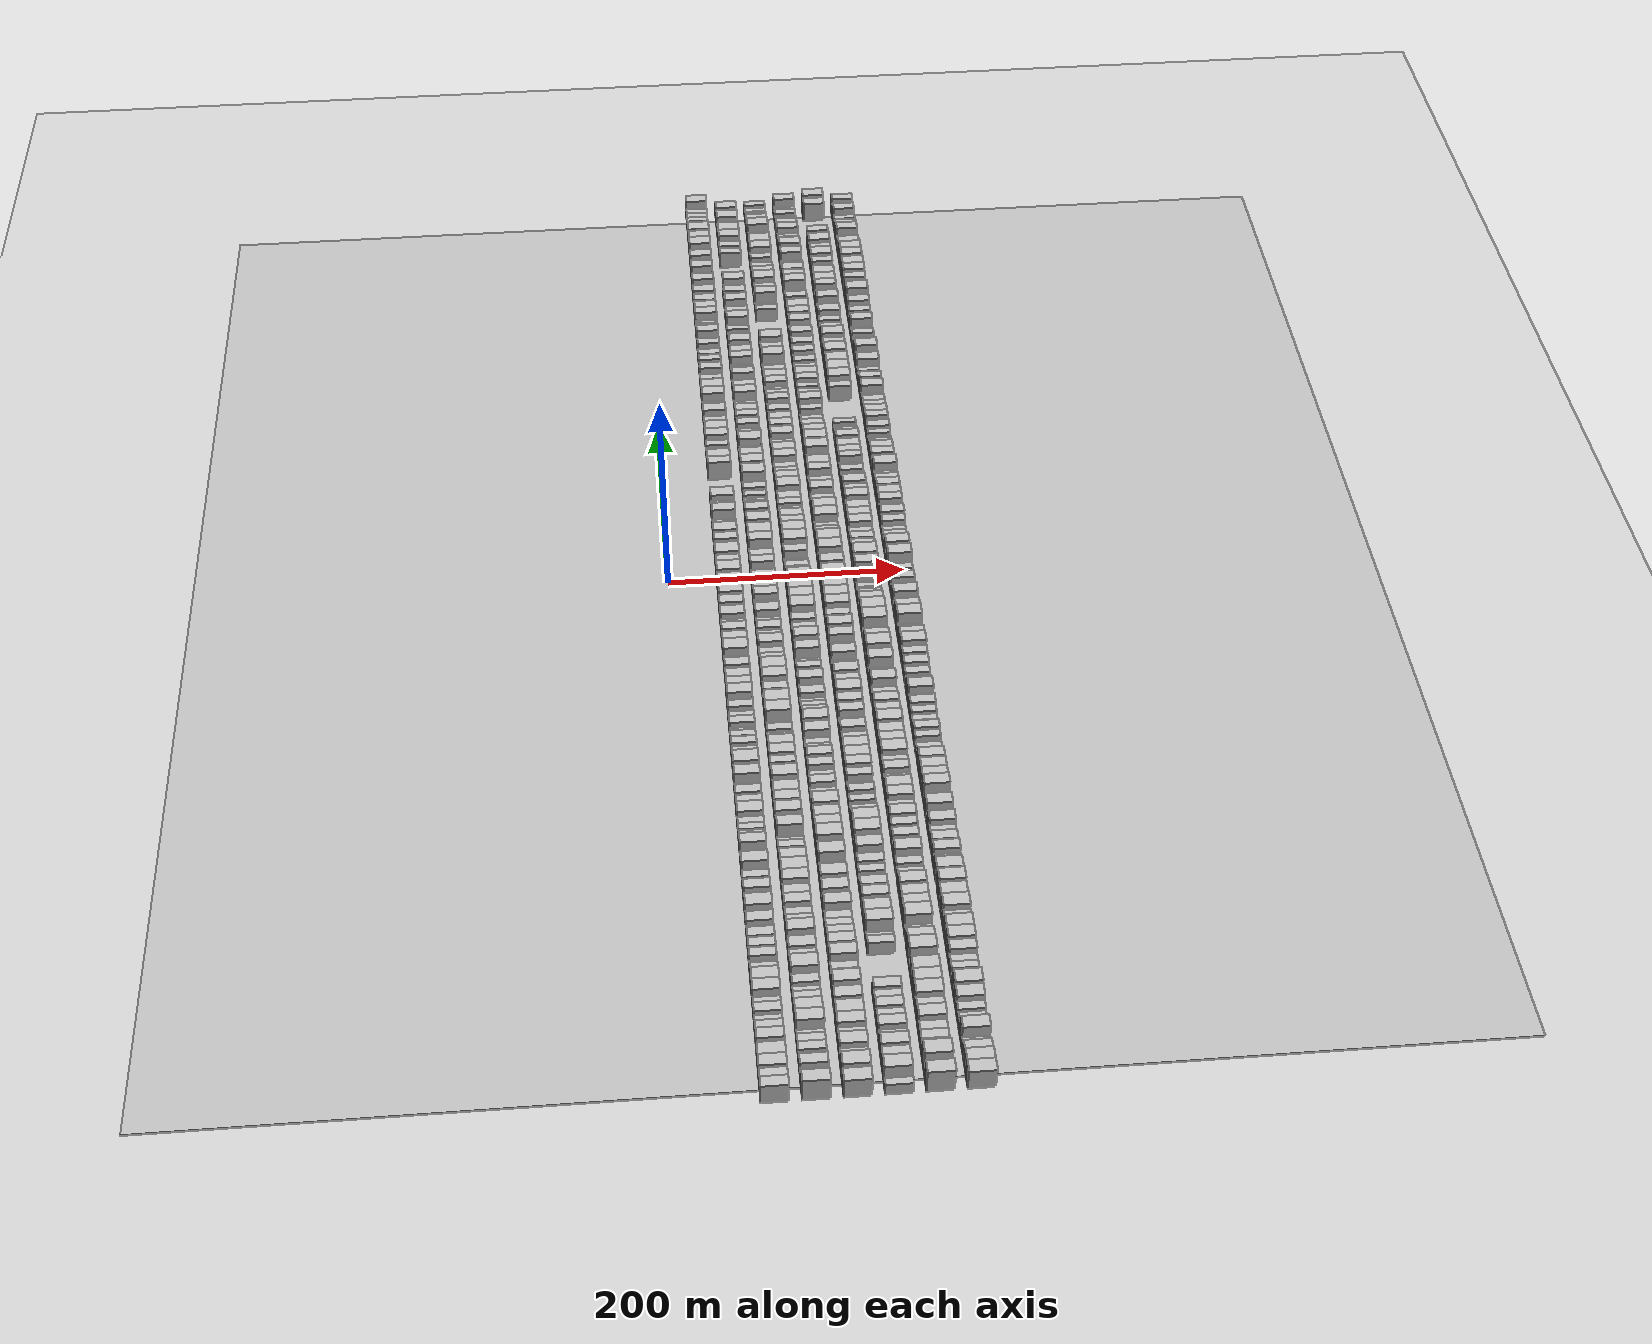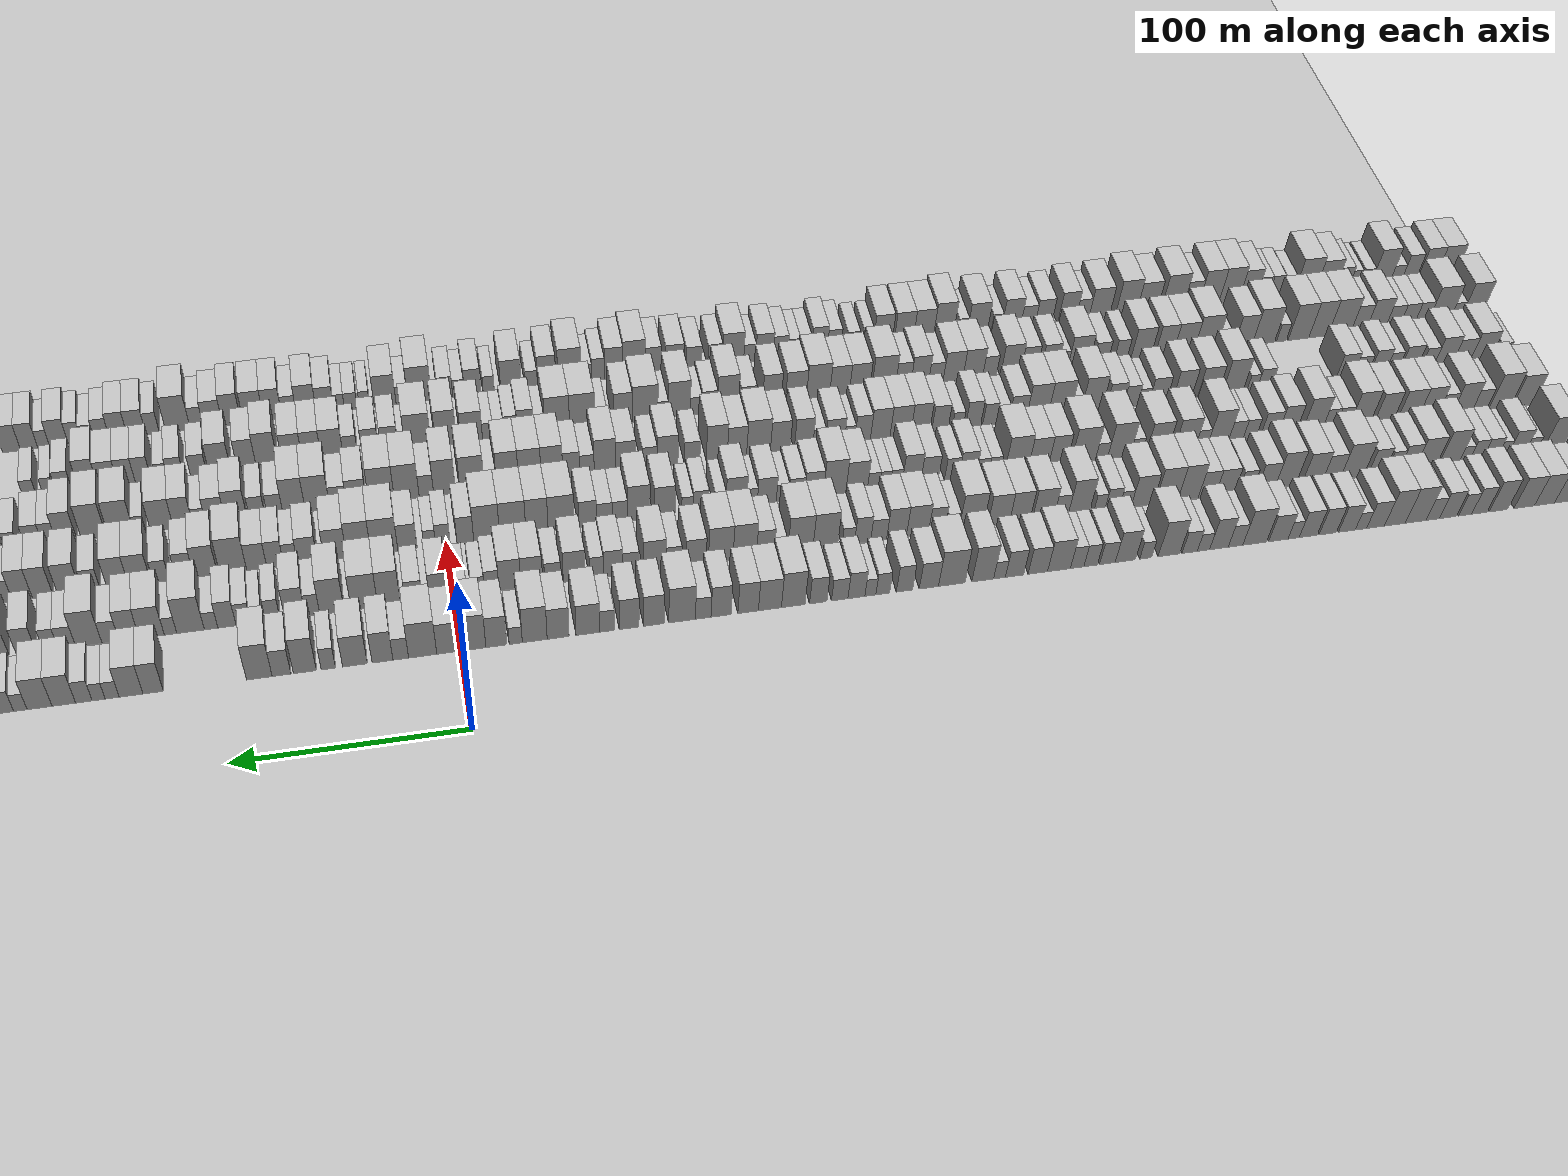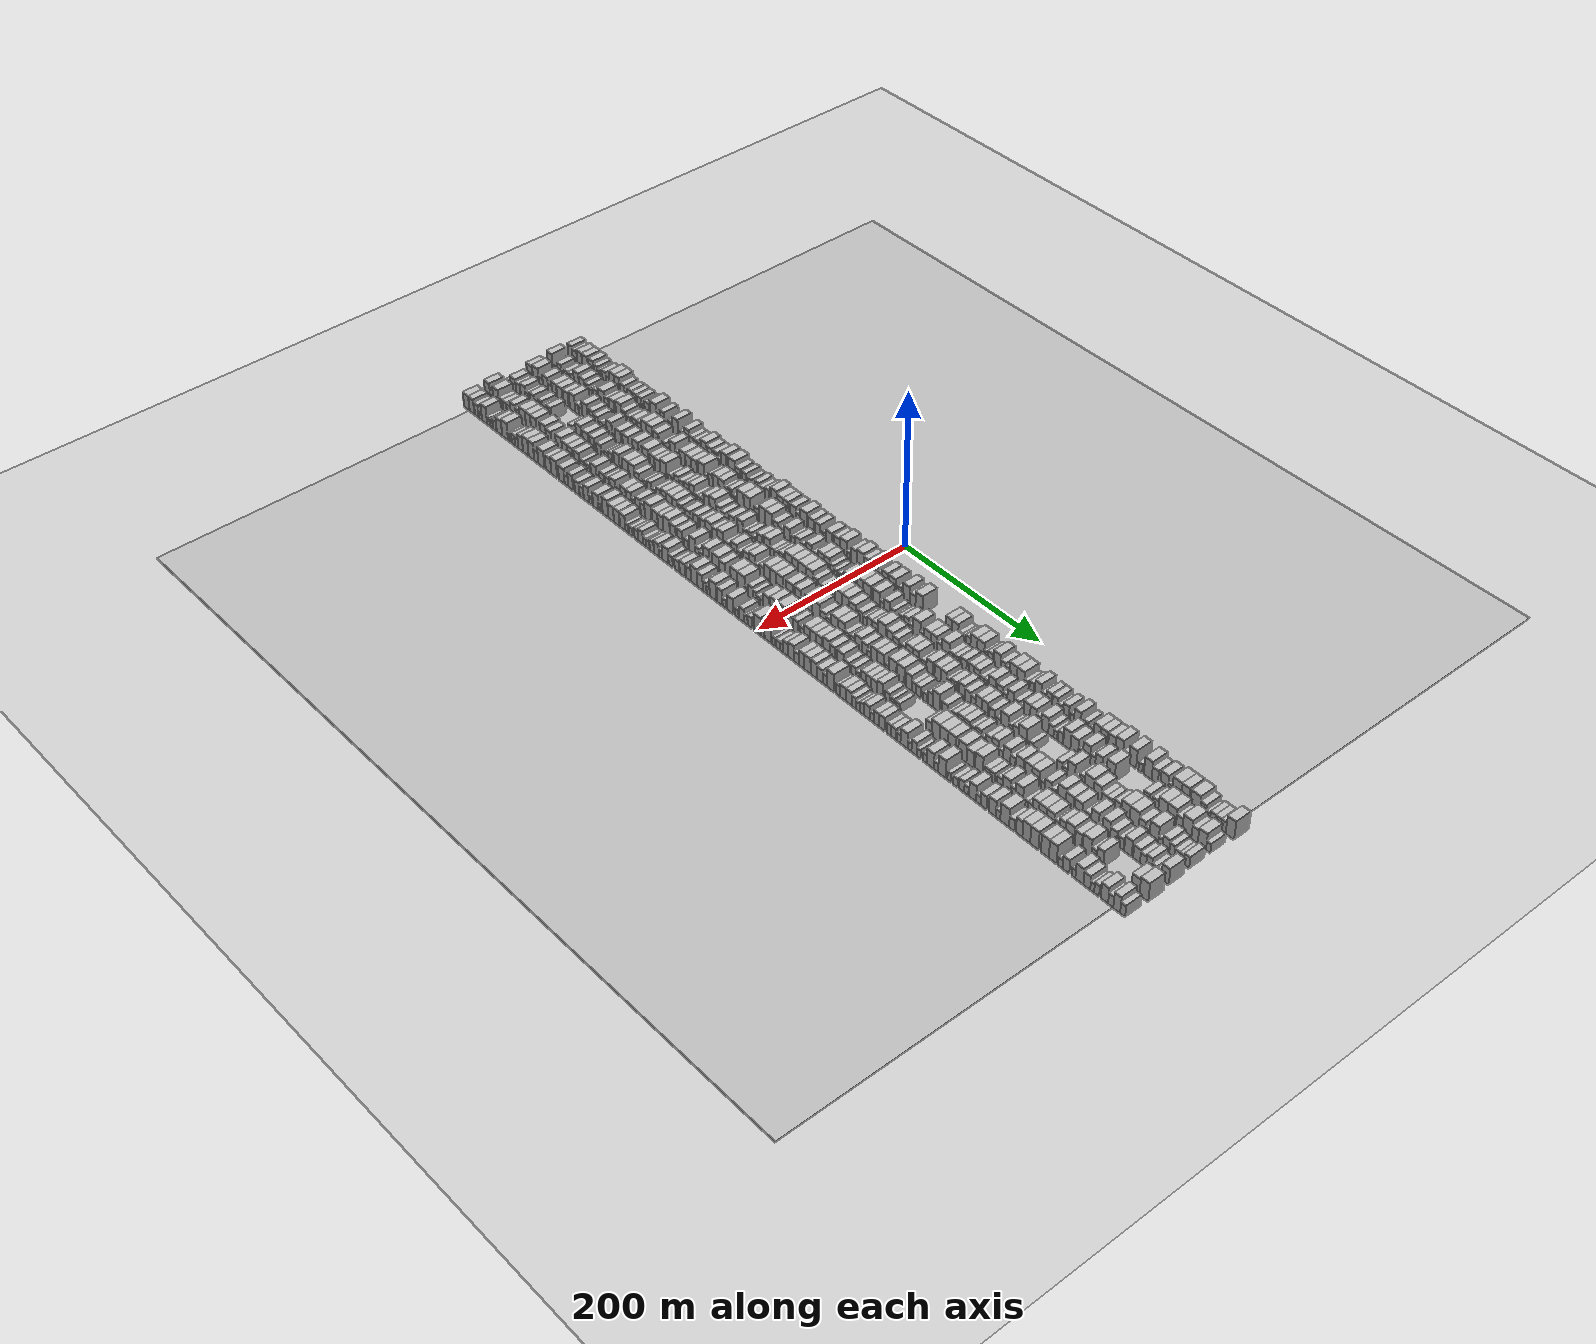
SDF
<?xml version="1.0" encoding="utf-8"?>

<sdf version="1.6">

   <world name="default">

      <gui fullscreen="0">

         <camera name="user_camera">

            <pose>-15 0 4.57585 0 0 0</pose>

            <view_controller>orbit</view_controller>

         </camera>

      </gui>

      <scene>

         <sky>

           <clouds>

             <speed>12</speed>

           </clouds>

         </sky>

         <ambient>0.4 0.4 0.4 1</ambient>

         <background>0.7 0.7 0.7 1</background>

         <shadows>1</shadows>

      </scene>

      <gravity>0 0 -9.8066</gravity>

      <magnetic_field>6e-06 2.3e-05 -4.2e-05</magnetic_field>

      <physics default="0" name="default_physics" type="ode">

         <ode>

            <solver>

               <type>quick</type>

               <iters>10</iters>

               <sor>1.0</sor>

               <use_dynamic_moi_rescaling>0</use_dynamic_moi_rescaling>

            </solver>

            <constraints>

               <cfm>0</cfm>

               <erp>0.2</erp>

               <contact_max_correcting_vel>100</contact_max_correcting_vel>

               <contact_surface_layer>0.001</contact_surface_layer>

            </constraints>

         </ode>

         <max_step_size>0.004</max_step_size>

         <real_time_factor>1</real_time_factor>

         <real_time_update_rate>250</real_time_update_rate>

      </physics>

      <light name="sun" type="directional">

         <cast_shadows>1</cast_shadows>

         <pose>0 0 10 0 0 0</pose>

         <diffuse>0.8 0.8 0.8 1</diffuse>

         <specular>0.2 0.2 0.2 1</specular>

         <attenuation>

            <range>1000</range>

            <constant>0.9</constant>

            <linear>0.01</linear>

            <quadratic>0.001</quadratic>

         </attenuation>

         <direction>-0.5 0.1 -0.9</direction>

      </light>

      <include>

         <name>ground_plane_1</name>

         <uri>model://HANNAS_ground_plane</uri>

         <pose>0 0 0  0 0 0</pose>

      </include>

      <include>

         <name>ground_plane_2</name>

         <uri>model://HANNAS_ground_plane</uri>

         <pose>100 0 0  0 0 0</pose>

      </include>

      <model name="building_1">

         <static>1</static>

         <pose frame="">50.0000 -505.7804 0 0.000000 0.000000 0.000000</pose>

         <link name="link">

            <pose frame="">0 0 10.50 0 0 0</pose>

            <collision name="collision">

               <geometry>

                  <box>

                     <size>20.0000 8.4392 21.0000</size>

                  </box>

               </geometry>

               <max_contacts>10</max_contacts>

               <surface>

                  <contact>

                     <ode/>

                  </contact>

                  <bounce/>

                  <friction>

                     <torsional>

                        <ode/>

                     </torsional>

                     <ode/>

                  </friction>

               </surface>

            </collision>

            <visual name="visual">

               <cast_shadows>0</cast_shadows>

               <geometry>

                  <box>

                     <size>20.0000 8.4392 21.0000</size>

                  </box>

               </geometry>

               <material>

                  <script>

                     <uri>model://HANNAS_wall/materials/scripts</uri>

                     <uri>model://HANNAS_wall/materials/textures</uri>

                     <name>vrc/HANNAS_wall</name>

                  </script>

               </material>

            </visual>

            <self_collide>0</self_collide>

            <enable_wind>0</enable_wind>

            <kinematic>0</kinematic>

         </link>

      </model>

      <model name="building_2">

         <static>1</static>

         <pose frame="">50.0000 -497.2267 0 0.000000 0.000000 0.000000</pose>

         <link name="link">

            <pose frame="">0 0 9.00 0 0 0</pose>

            <collision name="collision">

               <geometry>

                  <box>

                     <size>20.0000 8.6683 18.0000</size>

                  </box>

               </geometry>

               <max_contacts>10</max_contacts>

               <surface>

                  <contact>

                     <ode/>

                  </contact>

                  <bounce/>

                  <friction>

                     <torsional>

                        <ode/>

                     </torsional>

                     <ode/>

                  </friction>

               </surface>

            </collision>

            <visual name="visual">

               <cast_shadows>0</cast_shadows>

               <geometry>

                  <box>

                     <size>20.0000 8.6683 18.0000</size>

                  </box>

               </geometry>

               <material>

                  <script>

                     <uri>model://HANNAS_wall/materials/scripts</uri>

                     <uri>model://HANNAS_wall/materials/textures</uri>

                     <name>vrc/HANNAS_wall</name>

                  </script>

               </material>

            </visual>

            <self_collide>0</self_collide>

            <enable_wind>0</enable_wind>

            <kinematic>0</kinematic>

         </link>

      </model>

      <model name="building_3">

         <static>1</static>

         <pose frame="">50.0000 -488.1302 0 0.000000 0.000000 0.000000</pose>

         <link name="link">

            <pose frame="">0 0 10.50 0 0 0</pose>

            <collision name="collision">

               <geometry>

                  <box>

                     <size>20.0000 9.5248 21.0000</size>

                  </box>

               </geometry>

               <max_contacts>10</max_contacts>

               <surface>

                  <contact>

                     <ode/>

                  </contact>

                  <bounce/>

                  <friction>

                     <torsional>

                        <ode/>

                     </torsional>

                     <ode/>

                  </friction>

               </surface>

            </collision>

            <visual name="visual">

               <cast_shadows>0</cast_shadows>

               <geometry>

                  <box>

                     <size>20.0000 9.5248 21.0000</size>

                  </box>

               </geometry>

               <material>

                  <script>

                     <uri>model://HANNAS_wall/materials/scripts</uri>

                     <uri>model://HANNAS_wall/materials/textures</uri>

                     <name>vrc/HANNAS_wall</name>

                  </script>

               </material>

            </visual>

            <self_collide>0</self_collide>

            <enable_wind>0</enable_wind>

            <kinematic>0</kinematic>

         </link>

      </model>

      <model name="building_4">

         <static>1</static>

         <pose frame="">50.0000 -478.4753 0 0.000000 0.000000 0.000000</pose>

         <link name="link">

            <pose frame="">0 0 10.50 0 0 0</pose>

            <collision name="collision">

               <geometry>

                  <box>

                     <size>20.0000 9.7850 21.0000</size>

                  </box>

               </geometry>

               <max_contacts>10</max_contacts>

               <surface>

                  <contact>

                     <ode/>

                  </contact>

                  <bounce/>

                  <friction>

                     <torsional>

                        <ode/>

                     </torsional>

                     <ode/>

                  </friction>

               </surface>

            </collision>

            <visual name="visual">

               <cast_shadows>0</cast_shadows>

               <geometry>

                  <box>

                     <size>20.0000 9.7850 21.0000</size>

                  </box>

               </geometry>

               <material>

                  <script>

                     <uri>model://HANNAS_wall/materials/scripts</uri>

                     <uri>model://HANNAS_wall/materials/textures</uri>

                     <name>vrc/HANNAS_wall</name>

                  </script>

               </material>

            </visual>

            <self_collide>0</self_collide>

            <enable_wind>0</enable_wind>

            <kinematic>0</kinematic>

         </link>

      </model>

      <model name="building_5">

         <static>1</static>

         <pose frame="">50.0000 -466.1698 0 0.000000 0.000000 0.000000</pose>

         <link name="link">

            <pose frame="">0 0 10.50 0 0 0</pose>

            <collision name="collision">

               <geometry>

                  <box>

                     <size>20.0000 8.8261 21.0000</size>

                  </box>

               </geometry>

               <max_contacts>10</max_contacts>

               <surface>

                  <contact>

                     <ode/>

                  </contact>

                  <bounce/>

                  <friction>

                     <torsional>

                        <ode/>

                     </torsional>

                     <ode/>

                  </friction>

               </surface>

            </collision>

            <visual name="visual">

               <cast_shadows>0</cast_shadows>

               <geometry>

                  <box>

                     <size>20.0000 8.8261 21.0000</size>

                  </box>

               </geometry>

               <material>

                  <script>

                     <uri>model://HANNAS_wall/materials/scripts</uri>

                     <uri>model://HANNAS_wall/materials/textures</uri>

                     <name>vrc/HANNAS_wall</name>

                  </script>

               </material>

            </visual>

            <self_collide>0</self_collide>

            <enable_wind>0</enable_wind>

            <kinematic>0</kinematic>

         </link>

      </model>

      <model name="building_6">

         <static>1</static>

         <pose frame="">50.0000 -457.1109 0 0.000000 0.000000 0.000000</pose>

         <link name="link">

            <pose frame="">0 0 9.00 0 0 0</pose>

            <collision name="collision">

               <geometry>

                  <box>

                     <size>20.0000 7.2916 18.0000</size>

                  </box>

               </geometry>

               <max_contacts>10</max_contacts>

               <surface>

                  <contact>

                     <ode/>

                  </contact>

                  <bounce/>

                  <friction>

                     <torsional>

                        <ode/>

                     </torsional>

                     <ode/>

                  </friction>

               </surface>

            </collision>

            <visual name="visual">

               <cast_shadows>0</cast_shadows>

               <geometry>

                  <box>

                     <size>20.0000 7.2916 18.0000</size>

                  </box>

               </geometry>

               <material>

                  <script>

                     <uri>model://HANNAS_wall/materials/scripts</uri>

                     <uri>model://HANNAS_wall/materials/textures</uri>

                     <name>vrc/HANNAS_wall</name>

                  </script>

               </material>

            </visual>

            <self_collide>0</self_collide>

            <enable_wind>0</enable_wind>

            <kinematic>0</kinematic>

         </link>

      </model>

      <model name="building_7">

         <static>1</static>

         <pose frame="">50.0000 -450.3802 0 0.000000 0.000000 0.000000</pose>

         <link name="link">

            <pose frame="">0 0 7.50 0 0 0</pose>

            <collision name="collision">

               <geometry>

                  <box>

                     <size>20.0000 6.1699 15.0000</size>

                  </box>

               </geometry>

               <max_contacts>10</max_contacts>

               <surface>

                  <contact>

                     <ode/>

                  </contact>

                  <bounce/>

                  <friction>

                     <torsional>

                        <ode/>

                     </torsional>

                     <ode/>

                  </friction>

               </surface>

            </collision>

            <visual name="visual">

               <cast_shadows>0</cast_shadows>

               <geometry>

                  <box>

                     <size>20.0000 6.1699 15.0000</size>

                  </box>

               </geometry>

               <material>

                  <script>

                     <uri>model://HANNAS_wall/materials/scripts</uri>

                     <uri>model://HANNAS_wall/materials/textures</uri>

                     <name>vrc/HANNAS_wall</name>

                  </script>

               </material>

            </visual>

            <self_collide>0</self_collide>

            <enable_wind>0</enable_wind>

            <kinematic>0</kinematic>

         </link>

      </model>

      <model name="building_8">

         <static>1</static>

         <pose frame="">50.0000 -442.2879 0 0.000000 0.000000 0.000000</pose>

         <link name="link">

            <pose frame="">0 0 9.00 0 0 0</pose>

            <collision name="collision">

               <geometry>

                  <box>

                     <size>20.0000 8.0148 18.0000</size>

                  </box>

               </geometry>

               <max_contacts>10</max_contacts>

               <surface>

                  <contact>

                     <ode/>

                  </contact>

                  <bounce/>

                  <friction>

                     <torsional>

                        <ode/>

                     </torsional>

                     <ode/>

                  </friction>

               </surface>

            </collision>

            <visual name="visual">

               <cast_shadows>0</cast_shadows>

               <geometry>

                  <box>

                     <size>20.0000 8.0148 18.0000</size>

                  </box>

               </geometry>

               <material>

                  <script>

                     <uri>model://HANNAS_wall/materials/scripts</uri>

                     <uri>model://HANNAS_wall/materials/textures</uri>

                     <name>vrc/HANNAS_wall</name>

                  </script>

               </material>

            </visual>

            <self_collide>0</self_collide>

            <enable_wind>0</enable_wind>

            <kinematic>0</kinematic>

         </link>

      </model>

      <model name="building_9">

         <static>1</static>

         <pose frame="">50.0000 -435.1372 0 0.000000 0.000000 0.000000</pose>

         <link name="link">

            <pose frame="">0 0 7.50 0 0 0</pose>

            <collision name="collision">

               <geometry>

                  <box>

                     <size>20.0000 6.2867 15.0000</size>

                  </box>

               </geometry>

               <max_contacts>10</max_contacts>

               <surface>

                  <contact>

                     <ode/>

                  </contact>

                  <bounce/>

                  <friction>

                     <torsional>

                        <ode/>

                     </torsional>

                     <ode/>

                  </friction>

               </surface>

            </collision>

            <visual name="visual">

               <cast_shadows>0</cast_shadows>

               <geometry>

                  <box>

                     <size>20.0000 6.2867 15.0000</size>

                  </box>

               </geometry>

               <material>

                  <script>

                     <uri>model://HANNAS_wall/materials/scripts</uri>

                     <uri>model://HANNAS_wall/materials/textures</uri>

                     <name>vrc/HANNAS_wall</name>

                  </script>

               </material>

            </visual>

            <self_collide>0</self_collide>

            <enable_wind>0</enable_wind>

            <kinematic>0</kinematic>

         </link>

      </model>

      <model name="building_10">

         <static>1</static>

         <pose frame="">50.0000 -427.0935 0 0.000000 0.000000 0.000000</pose>

         <link name="link">

            <pose frame="">0 0 12.00 0 0 0</pose>

            <collision name="collision">

               <geometry>

                  <box>

                     <size>20.0000 9.8006 24.0000</size>

                  </box>

               </geometry>

               <max_contacts>10</max_contacts>

               <surface>

                  <contact>

                     <ode/>

                  </contact>

                  <bounce/>

                  <friction>

                     <torsional>

                        <ode/>

                     </torsional>

                     <ode/>

                  </friction>

               </surface>

            </collision>

            <visual name="visual">

               <cast_shadows>0</cast_shadows>

               <geometry>

                  <box>

                     <size>20.0000 9.8006 24.0000</size>

                  </box>

               </geometry>

               <material>

                  <script>

                     <uri>model://HANNAS_wall/materials/scripts</uri>

                     <uri>model://HANNAS_wall/materials/textures</uri>

                     <name>vrc/HANNAS_wall</name>

                  </script>

               </material>

            </visual>

            <self_collide>0</self_collide>

            <enable_wind>0</enable_wind>

            <kinematic>0</kinematic>

         </link>

      </model>

      <model name="building_11">

         <static>1</static>

         <pose frame="">50.0000 -417.2737 0 0.000000 0.000000 0.000000</pose>

         <link name="link">

            <pose frame="">0 0 12.00 0 0 0</pose>

            <collision name="collision">

               <geometry>

                  <box>

                     <size>20.0000 9.8390 24.0000</size>

                  </box>

               </geometry>

               <max_contacts>10</max_contacts>

               <surface>

                  <contact>

                     <ode/>

                  </contact>

                  <bounce/>

                  <friction>

                     <torsional>

                        <ode/>

                     </torsional>

                     <ode/>

                  </friction>

               </surface>

            </collision>

            <visual name="visual">

               <cast_shadows>0</cast_shadows>

               <geometry>

                  <box>

                     <size>20.0000 9.8390 24.0000</size>

                  </box>

               </geometry>

               <material>

                  <script>

                     <uri>model://HANNAS_wall/materials/scripts</uri>

                     <uri>model://HANNAS_wall/materials/textures</uri>

                     <name>vrc/HANNAS_wall</name>

                  </script>

               </material>

            </visual>

            <self_collide>0</self_collide>

            <enable_wind>0</enable_wind>

            <kinematic>0</kinematic>

         </link>

      </model>

      <model name="building_12">

         <static>1</static>

         <pose frame="">50.0000 -408.1813 0 0.000000 0.000000 0.000000</pose>

         <link name="link">

            <pose frame="">0 0 9.00 0 0 0</pose>

            <collision name="collision">

               <geometry>

                  <box>

                     <size>20.0000 8.3459 18.0000</size>

                  </box>

               </geometry>

               <max_contacts>10</max_contacts>

               <surface>

                  <contact>

                     <ode/>

                  </contact>

                  <bounce/>

                  <friction>

                     <torsional>

                        <ode/>

                     </torsional>

                     <ode/>

                  </friction>

               </surface>

            </collision>

            <visual name="visual">

               <cast_shadows>0</cast_shadows>

               <geometry>

                  <box>

                     <size>20.0000 8.3459 18.0000</size>

                  </box>

               </geometry>

               <material>

                  <script>

                     <uri>model://HANNAS_wall/materials/scripts</uri>

                     <uri>model://HANNAS_wall/materials/textures</uri>

                     <name>vrc/HANNAS_wall</name>

                  </script>

               </material>

            </visual>

            <self_collide>0</self_collide>

            <enable_wind>0</enable_wind>

            <kinematic>0</kinematic>

         </link>

      </model>

      <model name="building_13">

         <static>1</static>

         <pose frame="">50.0000 -401.3410 0 0.000000 0.000000 0.000000</pose>

         <link name="link">

            <pose frame="">0 0 6.00 0 0 0</pose>

            <collision name="collision">

               <geometry>

                  <box>

                     <size>20.0000 5.3347 12.0000</size>

                  </box>

               </geometry>

               <max_contacts>10</max_contacts>

               <surface>

                  <contact>

                     <ode/>

                  </contact>

                  <bounce/>

                  <friction>

                     <torsional>

                        <ode/>

                     </torsional>

                     <ode/>

                  </friction>

               </surface>

            </collision>

            <visual name="visual">

               <cast_shadows>0</cast_shadows>

               <geometry>

                  <box>

                     <size>20.0000 5.3347 12.0000</size>

                  </box>

               </geometry>

               <material>

                  <script>

                     <uri>model://HANNAS_wall/materials/scripts</uri>

                     <uri>model://HANNAS_wall/materials/textures</uri>

                     <name>vrc/HANNAS_wall</name>

                  </script>

               </material>

            </visual>

            <self_collide>0</self_collide>

            <enable_wind>0</enable_wind>

            <kinematic>0</kinematic>

         </link>

      </model>

      <model name="building_14">

         <static>1</static>

         <pose frame="">50.0000 -394.7712 0 0.000000 0.000000 0.000000</pose>

         <link name="link">

            <pose frame="">0 0 9.00 0 0 0</pose>

            <collision name="collision">

               <geometry>

                  <box>

                     <size>20.0000 7.8048 18.0000</size>

                  </box>

               </geometry>

               <max_contacts>10</max_contacts>

               <surface>

                  <contact>

                     <ode/>

                  </contact>

                  <bounce/>

                  <friction>

                     <torsional>

                        <ode/>

                     </torsional>

                     <ode/>

                  </friction>

               </surface>

            </collision>

            <visual name="visual">

               <cast_shadows>0</cast_shadows>

               <geometry>

                  <box>

                     <size>20.0000 7.8048 18.0000</size>

                  </box>

               </geometry>

               <material>

                  <script>

                     <uri>model://HANNAS_wall/materials/scripts</uri>

                     <uri>model://HANNAS_wall/materials/textures</uri>

                     <name>vrc/HANNAS_wall</name>

                  </script>

               </material>

            </visual>

            <self_collide>0</self_collide>

            <enable_wind>0</enable_wind>

            <kinematic>0</kinematic>

         </link>

      </model>

      <model name="building_15">

         <static>1</static>

         <pose frame="">50.0000 -385.8586 0 0.000000 0.000000 0.000000</pose>

         <link name="link">

            <pose frame="">0 0 9.00 0 0 0</pose>

            <collision name="collision">

               <geometry>

                  <box>

                     <size>20.0000 8.0204 18.0000</size>

                  </box>

               </geometry>

               <max_contacts>10</max_contacts>

               <surface>

                  <contact>

                     <ode/>

                  </contact>

                  <bounce/>

                  <friction>

                     <torsional>

                        <ode/>

                     </torsional>

                     <ode/>

                  </friction>

               </surface>

            </collision>

            <visual name="visual">

               <cast_shadows>0</cast_shadows>

               <geometry>

                  <box>

                     <size>20.0000 8.0204 18.0000</size>

                  </box>

               </geometry>

               <material>

                  <script>

                     <uri>model://HANNAS_wall/materials/scripts</uri>

                     <uri>model://HANNAS_wall/materials/textures</uri>

                     <name>vrc/HANNAS_wall</name>

                  </script>

               </material>

            </visual>

            <self_collide>0</self_collide>

            <enable_wind>0</enable_wind>

            <kinematic>0</kinematic>

         </link>

      </model>

      <model name="building_16">

         <static>1</static>

         <pose frame="">50.0000 -376.7009 0 0.000000 0.000000 0.000000</pose>

         <link name="link">

            <pose frame="">0 0 9.00 0 0 0</pose>

            <collision name="collision">

               <geometry>

                  <box>

                     <size>20.0000 8.2950 18.0000</size>

                  </box>

               </geometry>

               <max_contacts>10</max_contacts>

               <surface>

                  <contact>

                     <ode/>

                  </contact>

                  <bounce/>

                  <friction>

                     <torsional>

                        <ode/>

                     </torsional>

                     <ode/>

                  </friction>

               </surface>

            </collision>

            <visual name="visual">

               <cast_shadows>0</cast_shadows>

               <geometry>

                  <box>

                     <size>20.0000 8.2950 18.0000</size>

                  </box>

               </geometry>

               <material>

                  <script>

                     <uri>model://HANNAS_wall/materials/scripts</uri>

                     <uri>model://HANNAS_wall/materials/textures</uri>

                     <name>vrc/HANNAS_wall</name>

                  </script>

               </material>

            </visual>

            <self_collide>0</self_collide>

            <enable_wind>0</enable_wind>

            <kinematic>0</kinematic>

         </link>

      </model>

      <model name="building_17">

         <static>1</static>

         <pose frame="">50.0000 -369.9493 0 0.000000 0.000000 0.000000</pose>

         <link name="link">

            <pose frame="">0 0 6.00 0 0 0</pose>

            <collision name="collision">

               <geometry>

                  <box>

                     <size>20.0000 5.2081 12.0000</size>

                  </box>

               </geometry>

               <max_contacts>10</max_contacts>

               <surface>

                  <contact>

                     <ode/>

                  </contact>

                  <bounce/>

                  <friction>

                     <torsional>

                        <ode/>

                     </torsional>

                     <ode/>

                  </friction>

               </surface>

            </collision>

            <visual name="visual">

               <cast_shadows>0</cast_shadows>

               <geometry>

                  <box>

                     <size>20.0000 5.2081 12.0000</size>

                  </box>

               </geometry>

               <material>

                  <script>

                     <uri>model://HANNAS_wall/materials/scripts</uri>

                     <uri>model://HANNAS_wall/materials/textures</uri>

                     <name>vrc/HANNAS_wall</name>

                  </script>

               </material>

            </visual>

            <self_collide>0</self_collide>

            <enable_wind>0</enable_wind>

            <kinematic>0</kinematic>

         </link>

      </model>

      <model name="building_18">

         <static>1</static>

         <pose frame="">50.0000 -362.8617 0 0.000000 0.000000 0.000000</pose>

         <link name="link">

            <pose frame="">0 0 9.00 0 0 0</pose>

            <collision name="collision">

               <geometry>

                  <box>

                     <size>20.0000 8.9670 18.0000</size>

                  </box>

               </geometry>

               <max_contacts>10</max_contacts>

               <surface>

                  <contact>

                     <ode/>

                  </contact>

                  <bounce/>

                  <friction>

                     <torsional>

                        <ode/>

                     </torsional>

                     <ode/>

                  </friction>

               </surface>

            </collision>

            <visual name="visual">

               <cast_shadows>0</cast_shadows>

               <geometry>

                  <box>

                     <size>20.0000 8.9670 18.0000</size>

                  </box>

               </geometry>

               <material>

                  <script>

                     <uri>model://HANNAS_wall/materials/scripts</uri>

                     <uri>model://HANNAS_wall/materials/textures</uri>

                     <name>vrc/HANNAS_wall</name>

                  </script>

               </material>

            </visual>

            <self_collide>0</self_collide>

            <enable_wind>0</enable_wind>

            <kinematic>0</kinematic>

         </link>

      </model>

      <model name="building_19">

         <static>1</static>

         <pose frame="">50.0000 -351.8949 0 0.000000 0.000000 0.000000</pose>

         <link name="link">

            <pose frame="">0 0 12.00 0 0 0</pose>

            <collision name="collision">

               <geometry>

                  <box>

                     <size>20.0000 10.9666 24.0000</size>

                  </box>

               </geometry>

               <max_contacts>10</max_contacts>

               <surface>

                  <contact>

                     <ode/>

                  </contact>

                  <bounce/>

                  <friction>

                     <torsional>

                        <ode/>

                     </torsional>

                     <ode/>

                  </friction>

               </surface>

            </collision>

            <visual name="visual">

               <cast_shadows>0</cast_shadows>

               <geometry>

                  <box>

                     <size>20.0000 10.9666 24.0000</size>

                  </box>

               </geometry>

               <material>

                  <script>

                     <uri>model://HANNAS_wall/materials/scripts</uri>

                     <uri>model://HANNAS_wall/materials/textures</uri>

                     <name>vrc/HANNAS_wall</name>

                  </script>

               </material>

            </visual>

            <self_collide>0</self_collide>

            <enable_wind>0</enable_wind>

            <kinematic>0</kinematic>

         </link>

      </model>

      <model name="building_20">

         <static>1</static>

         <pose frame="">50.0000 -343.0406 0 0.000000 0.000000 0.000000</pose>

         <link name="link">

            <pose frame="">0 0 7.50 0 0 0</pose>

            <collision name="collision">

               <geometry>

                  <box>

                     <size>20.0000 6.7419 15.0000</size>

                  </box>

               </geometry>

               <max_contacts>10</max_contacts>

               <surface>

                  <contact>

                     <ode/>

                  </contact>

                  <bounce/>

                  <friction>

                     <torsional>

                        <ode/>

                     </torsional>

                     <ode/>

                  </friction>

               </surface>

            </collision>

            <visual name="visual">

               <cast_shadows>0</cast_shadows>

               <geometry>

                  <box>

                     <size>20.0000 6.7419 15.0000</size>

                  </box>

               </geometry>

               <material>

                  <script>

                     <uri>model://HANNAS_wall/materials/scripts</uri>

                     <uri>model://HANNAS_wall/materials/textures</uri>

                     <name>vrc/HANNAS_wall</name>

                  </script>

               </material>

            </visual>

            <self_collide>0</self_collide>

            <enable_wind>0</enable_wind>

            <kinematic>0</kinematic>

         </link>

      </model>

      <model name="building_21">

         <static>1</static>

         <pose frame="">50.0000 -335.3861 0 0.000000 0.000000 0.000000</pose>

         <link name="link">

            <pose frame="">0 0 10.50 0 0 0</pose>

            <collision name="collision">

               <geometry>

                  <box>

                     <size>20.0000 8.5670 21.0000</size>

                  </box>

               </geometry>

               <max_contacts>10</max_contacts>

               <surface>

                  <contact>

                     <ode/>

                  </contact>

                  <bounce/>

                  <friction>

                     <torsional>

                        <ode/>

                     </torsional>

                     <ode/>

                  </friction>

               </surface>

            </collision>

            <visual name="visual">

               <cast_shadows>0</cast_shadows>

               <geometry>

                  <box>

                     <size>20.0000 8.5670 21.0000</size>

                  </box>

               </geometry>

               <material>

                  <script>

                     <uri>model://HANNAS_wall/materials/scripts</uri>

                     <uri>model://HANNAS_wall/materials/textures</uri>

                     <name>vrc/HANNAS_wall</name>

                  </script>

               </material>

            </visual>

            <self_collide>0</self_collide>

            <enable_wind>0</enable_wind>

            <kinematic>0</kinematic>

         </link>

      </model>

      <model name="building_22">

         <static>1</static>

         <pose frame="">50.0000 -328.2795 0 0.000000 0.000000 0.000000</pose>

         <link name="link">

            <pose frame="">0 0 6.00 0 0 0</pose>

            <collision name="collision">

               <geometry>

                  <box>

                     <size>20.0000 5.6461 12.0000</size>

                  </box>

               </geometry>

               <max_contacts>10</max_contacts>

               <surface>

                  <contact>

                     <ode/>

                  </contact>

                  <bounce/>

                  <friction>

                     <torsional>

                        <ode/>

                     </torsional>

                     <ode/>

                  </friction>

               </surface>

            </collision>

            <visual name="visual">

               <cast_shadows>0</cast_shadows>

               <geometry>

                  <box>

                     <size>20.0000 5.6461 12.0000</size>

                  </box>

               </geometry>

               <material>

                  <script>

                     <uri>model://HANNAS_wall/materials/scripts</uri>

                     <uri>model://HANNAS_wall/materials/textures</uri>

                     <name>vrc/HANNAS_wall</name>

                  </script>

               </material>

            </visual>

            <self_collide>0</self_collide>

            <enable_wind>0</enable_wind>

            <kinematic>0</kinematic>

         </link>

      </model>

      <model name="building_23">

         <static>1</static>

         <pose frame="">50.0000 -321.9365 0 0.000000 0.000000 0.000000</pose>

         <link name="link">

            <pose frame="">0 0 7.50 0 0 0</pose>

            <collision name="collision">

               <geometry>

                  <box>

                     <size>20.0000 7.0399 15.0000</size>

                  </box>

               </geometry>

               <max_contacts>10</max_contacts>

               <surface>

                  <contact>

                     <ode/>

                  </contact>

                  <bounce/>

                  <friction>

                     <torsional>

                        <ode/>

                     </torsional>

                     <ode/>

                  </friction>

               </surface>

            </collision>

            <visual name="visual">

               <cast_shadows>0</cast_shadows>

               <geometry>

                  <box>

                     <size>20.0000 7.0399 15.0000</size>

                  </box>

               </geometry>

               <material>

                  <script>

                     <uri>model://HANNAS_wall/materials/scripts</uri>

                     <uri>model://HANNAS_wall/materials/textures</uri>

                     <name>vrc/HANNAS_wall</name>

                  </script>

               </material>

            </visual>

            <self_collide>0</self_collide>

            <enable_wind>0</enable_wind>

            <kinematic>0</kinematic>

         </link>

      </model>

      <model name="building_24">

         <static>1</static>

         <pose frame="">50.0000 -312.4300 0 0.000000 0.000000 0.000000</pose>

         <link name="link">

            <pose frame="">0 0 12.00 0 0 0</pose>

            <collision name="collision">

               <geometry>

                  <box>

                     <size>20.0000 9.9732 24.0000</size>

                  </box>

               </geometry>

               <max_contacts>10</max_contacts>

               <surface>

                  <contact>

                     <ode/>

                  </contact>

                  <bounce/>

                  <friction>

                     <torsional>

                        <ode/>

                     </torsional>

                     <ode/>

                  </friction>

               </surface>

            </collision>

            <visual name="visual">

               <cast_shadows>0</cast_shadows>

               <geometry>

                  <box>

                     <size>20.0000 9.9732 24.0000</size>

                  </box>

               </geometry>

               <material>

                  <script>

                     <uri>model://HANNAS_wall/materials/scripts</uri>

                     <uri>model://HANNAS_wall/materials/textures</uri>

                     <name>vrc/HANNAS_wall</name>

                  </script>

               </material>

            </visual>

            <self_collide>0</self_collide>

            <enable_wind>0</enable_wind>

            <kinematic>0</kinematic>

         </link>

      </model>

      <model name="building_25">

         <static>1</static>

         <pose frame="">50.0000 -301.7349 0 0.000000 0.000000 0.000000</pose>

         <link name="link">

            <pose frame="">0 0 6.00 0 0 0</pose>

            <collision name="collision">

               <geometry>

                  <box>

                     <size>20.0000 5.4171 12.0000</size>

                  </box>

               </geometry>

               <max_contacts>10</max_contacts>

               <surface>

                  <contact>

                     <ode/>

                  </contact>

                  <bounce/>

                  <friction>

                     <torsional>

                        <ode/>

                     </torsional>

                     <ode/>

                  </friction>

               </surface>

            </collision>

            <visual name="visual">

               <cast_shadows>0</cast_shadows>

               <geometry>

                  <box>

                     <size>20.0000 5.4171 12.0000</size>

                  </box>

               </geometry>

               <material>

                  <script>

                     <uri>model://HANNAS_wall/materials/scripts</uri>

                     <uri>model://HANNAS_wall/materials/textures</uri>

                     <name>vrc/HANNAS_wall</name>

                  </script>

               </material>

            </visual>

            <self_collide>0</self_collide>

            <enable_wind>0</enable_wind>

            <kinematic>0</kinematic>

         </link>

      </model>

      <model name="building_26">

         <static>1</static>

         <pose frame="">50.0000 -292.4270 0 0.000000 0.000000 0.000000</pose>

         <link name="link">

            <pose frame="">0 0 10.50 0 0 0</pose>

            <collision name="collision">

               <geometry>

                  <box>

                     <size>20.0000 9.1986 21.0000</size>

                  </box>

               </geometry>

               <max_contacts>10</max_contacts>

               <surface>

                  <contact>

                     <ode/>

                  </contact>

                  <bounce/>

                  <friction>

                     <torsional>

                        <ode/>

                     </torsional>

                     <ode/>

                  </friction>

               </surface>

            </collision>

            <visual name="visual">

               <cast_shadows>0</cast_shadows>

               <geometry>

                  <box>

                     <size>20.0000 9.1986 21.0000</size>

                  </box>

               </geometry>

               <material>

                  <script>

                     <uri>model://HANNAS_wall/materials/scripts</uri>

                     <uri>model://HANNAS_wall/materials/textures</uri>

                     <name>vrc/HANNAS_wall</name>

                  </script>

               </material>

            </visual>

            <self_collide>0</self_collide>

            <enable_wind>0</enable_wind>

            <kinematic>0</kinematic>

         </link>

      </model>

      <model name="building_27">

         <static>1</static>

         <pose frame="">50.0000 -284.2589 0 0.000000 0.000000 0.000000</pose>

         <link name="link">

            <pose frame="">0 0 7.50 0 0 0</pose>

            <collision name="collision">

               <geometry>

                  <box>

                     <size>20.0000 7.1375 15.0000</size>

                  </box>

               </geometry>

               <max_contacts>10</max_contacts>

               <surface>

                  <contact>

                     <ode/>

                  </contact>

                  <bounce/>

                  <friction>

                     <torsional>

                        <ode/>

                     </torsional>

                     <ode/>

                  </friction>

               </surface>

            </collision>

            <visual name="visual">

               <cast_shadows>0</cast_shadows>

               <geometry>

                  <box>

                     <size>20.0000 7.1375 15.0000</size>

                  </box>

               </geometry>

               <material>

                  <script>

                     <uri>model://HANNAS_wall/materials/scripts</uri>

                     <uri>model://HANNAS_wall/materials/textures</uri>

                     <name>vrc/HANNAS_wall</name>

                  </script>

               </material>

            </visual>

            <self_collide>0</self_collide>

            <enable_wind>0</enable_wind>

            <kinematic>0</kinematic>

         </link>

      </model>

      <model name="building_28">

         <static>1</static>

         <pose frame="">50.0000 -276.6328 0 0.000000 0.000000 0.000000</pose>

         <link name="link">

            <pose frame="">0 0 7.50 0 0 0</pose>

            <collision name="collision">

               <geometry>

                  <box>

                     <size>20.0000 6.1146 15.0000</size>

                  </box>

               </geometry>

               <max_contacts>10</max_contacts>

               <surface>

                  <contact>

                     <ode/>

                  </contact>

                  <bounce/>

                  <friction>

                     <torsional>

                        <ode/>

                     </torsional>

                     <ode/>

                  </friction>

               </surface>

            </collision>

            <visual name="visual">

               <cast_shadows>0</cast_shadows>

               <geometry>

                  <box>

                     <size>20.0000 6.1146 15.0000</size>

                  </box>

               </geometry>

               <material>

                  <script>

                     <uri>model://HANNAS_wall/materials/scripts</uri>

                     <uri>model://HANNAS_wall/materials/textures</uri>

                     <name>vrc/HANNAS_wall</name>

                  </script>

               </material>

            </visual>

            <self_collide>0</self_collide>

            <enable_wind>0</enable_wind>

            <kinematic>0</kinematic>

         </link>

      </model>

      <model name="building_29">

         <static>1</static>

         <pose frame="">50.0000 -270.5275 0 0.000000 0.000000 0.000000</pose>

         <link name="link">

            <pose frame="">0 0 7.50 0 0 0</pose>

            <collision name="collision">

               <geometry>

                  <box>

                     <size>20.0000 6.0960 15.0000</size>

                  </box>

               </geometry>

               <max_contacts>10</max_contacts>

               <surface>

                  <contact>

                     <ode/>

                  </contact>

                  <bounce/>

                  <friction>

                     <torsional>

                        <ode/>

                     </torsional>

                     <ode/>

                  </friction>

               </surface>

            </collision>

            <visual name="visual">

               <cast_shadows>0</cast_shadows>

               <geometry>

                  <box>

                     <size>20.0000 6.0960 15.0000</size>

                  </box>

               </geometry>

               <material>

                  <script>

                     <uri>model://HANNAS_wall/materials/scripts</uri>

                     <uri>model://HANNAS_wall/materials/textures</uri>

                     <name>vrc/HANNAS_wall</name>

                  </script>

               </material>

            </visual>

            <self_collide>0</self_collide>

            <enable_wind>0</enable_wind>

            <kinematic>0</kinematic>

         </link>

      </model>

      <model name="building_30">

         <static>1</static>

         <pose frame="">50.0000 -262.2955 0 0.000000 0.000000 0.000000</pose>

         <link name="link">

            <pose frame="">0 0 10.50 0 0 0</pose>

            <collision name="collision">

               <geometry>

                  <box>

                     <size>20.0000 10.3679 21.0000</size>

                  </box>

               </geometry>

               <max_contacts>10</max_contacts>

               <surface>

                  <contact>

                     <ode/>

                  </contact>

                  <bounce/>

                  <friction>

                     <torsional>

                        <ode/>

                     </torsional>

                     <ode/>

                  </friction>

               </surface>

            </collision>

            <visual name="visual">

               <cast_shadows>0</cast_shadows>

               <geometry>

                  <box>

                     <size>20.0000 10.3679 21.0000</size>

                  </box>

               </geometry>

               <material>

                  <script>

                     <uri>model://HANNAS_wall/materials/scripts</uri>

                     <uri>model://HANNAS_wall/materials/textures</uri>

                     <name>vrc/HANNAS_wall</name>

                  </script>

               </material>

            </visual>

            <self_collide>0</self_collide>

            <enable_wind>0</enable_wind>

            <kinematic>0</kinematic>

         </link>

      </model>

      <model name="building_31">

         <static>1</static>

         <pose frame="">50.0000 -252.7053 0 0.000000 0.000000 0.000000</pose>

         <link name="link">

            <pose frame="">0 0 9.00 0 0 0</pose>

            <collision name="collision">

               <geometry>

                  <box>

                     <size>20.0000 8.8126 18.0000</size>

                  </box>

               </geometry>

               <max_contacts>10</max_contacts>

               <surface>

                  <contact>

                     <ode/>

                  </contact>

                  <bounce/>

                  <friction>

                     <torsional>

                        <ode/>

                     </torsional>

                     <ode/>

                  </friction>

               </surface>

            </collision>

            <visual name="visual">

               <cast_shadows>0</cast_shadows>

               <geometry>

                  <box>

                     <size>20.0000 8.8126 18.0000</size>

                  </box>

               </geometry>

               <material>

                  <script>

                     <uri>model://HANNAS_wall/materials/scripts</uri>

                     <uri>model://HANNAS_wall/materials/textures</uri>

                     <name>vrc/HANNAS_wall</name>

                  </script>

               </material>

            </visual>

            <self_collide>0</self_collide>

            <enable_wind>0</enable_wind>

            <kinematic>0</kinematic>

         </link>

      </model>

      <model name="building_32">

         <static>1</static>

         <pose frame="">50.0000 -242.1988 0 0.000000 0.000000 0.000000</pose>

         <link name="link">

            <pose frame="">0 0 9.00 0 0 0</pose>

            <collision name="collision">

               <geometry>

                  <box>

                     <size>20.0000 8.2003 18.0000</size>

                  </box>

               </geometry>

               <max_contacts>10</max_contacts>

               <surface>

                  <contact>

                     <ode/>

                  </contact>

                  <bounce/>

                  <friction>

                     <torsional>

                        <ode/>

                     </torsional>

                     <ode/>

                  </friction>

               </surface>

            </collision>

            <visual name="visual">

               <cast_shadows>0</cast_shadows>

               <geometry>

                  <box>

                     <size>20.0000 8.2003 18.0000</size>

                  </box>

               </geometry>

               <material>

                  <script>

                     <uri>model://HANNAS_wall/materials/scripts</uri>

                     <uri>model://HANNAS_wall/materials/textures</uri>

                     <name>vrc/HANNAS_wall</name>

                  </script>

               </material>

            </visual>

            <self_collide>0</self_collide>

            <enable_wind>0</enable_wind>

            <kinematic>0</kinematic>

         </link>

      </model>

      <model name="building_33">

         <static>1</static>

         <pose frame="">50.0000 -235.4329 0 0.000000 0.000000 0.000000</pose>

         <link name="link">

            <pose frame="">0 0 6.00 0 0 0</pose>

            <collision name="collision">

               <geometry>

                  <box>

                     <size>20.0000 5.3316 12.0000</size>

                  </box>

               </geometry>

               <max_contacts>10</max_contacts>

               <surface>

                  <contact>

                     <ode/>

                  </contact>

                  <bounce/>

                  <friction>

                     <torsional>

                        <ode/>

                     </torsional>

                     <ode/>

                  </friction>

               </surface>

            </collision>

            <visual name="visual">

               <cast_shadows>0</cast_shadows>

               <geometry>

                  <box>

                     <size>20.0000 5.3316 12.0000</size>

                  </box>

               </geometry>

               <material>

                  <script>

                     <uri>model://HANNAS_wall/materials/scripts</uri>

                     <uri>model://HANNAS_wall/materials/textures</uri>

                     <name>vrc/HANNAS_wall</name>

                  </script>

               </material>

            </visual>

            <self_collide>0</self_collide>

            <enable_wind>0</enable_wind>

            <kinematic>0</kinematic>

         </link>

      </model>

      <model name="building_34">

         <static>1</static>

         <pose frame="">50.0000 -227.8600 0 0.000000 0.000000 0.000000</pose>

         <link name="link">

            <pose frame="">0 0 12.00 0 0 0</pose>

            <collision name="collision">

               <geometry>

                  <box>

                     <size>20.0000 9.8141 24.0000</size>

                  </box>

               </geometry>

               <max_contacts>10</max_contacts>

               <surface>

                  <contact>

                     <ode/>

                  </contact>

                  <bounce/>

                  <friction>

                     <torsional>

                        <ode/>

                     </torsional>

                     <ode/>

                  </friction>

               </surface>

            </collision>

            <visual name="visual">

               <cast_shadows>0</cast_shadows>

               <geometry>

                  <box>

                     <size>20.0000 9.8141 24.0000</size>

                  </box>

               </geometry>

               <material>

                  <script>

                     <uri>model://HANNAS_wall/materials/scripts</uri>

                     <uri>model://HANNAS_wall/materials/textures</uri>

                     <name>vrc/HANNAS_wall</name>

                  </script>

               </material>

            </visual>

            <self_collide>0</self_collide>

            <enable_wind>0</enable_wind>

            <kinematic>0</kinematic>

         </link>

      </model>

      <model name="building_35">

         <static>1</static>

         <pose frame="">50.0000 -213.9845 0 0.000000 0.000000 0.000000</pose>

         <link name="link">

            <pose frame="">0 0 12.00 0 0 0</pose>

            <collision name="collision">

               <geometry>

                  <box>

                     <size>20.0000 11.9370 24.0000</size>

                  </box>

               </geometry>

               <max_contacts>10</max_contacts>

               <surface>

                  <contact>

                     <ode/>

                  </contact>

                  <bounce/>

                  <friction>

                     <torsional>

                        <ode/>

                     </torsional>

                     <ode/>

                  </friction>

               </surface>

            </collision>

            <visual name="visual">

               <cast_shadows>0</cast_shadows>

               <geometry>

                  <box>

                     <size>20.0000 11.9370 24.0000</size>

                  </box>

               </geometry>

               <material>

                  <script>

                     <uri>model://HANNAS_wall/materials/scripts</uri>

                     <uri>model://HANNAS_wall/materials/textures</uri>

                     <name>vrc/HANNAS_wall</name>

                  </script>

               </material>

            </visual>

            <self_collide>0</self_collide>

            <enable_wind>0</enable_wind>

            <kinematic>0</kinematic>

         </link>

      </model>

      <model name="building_36">

         <static>1</static>

         <pose frame="">50.0000 -203.7256 0 0.000000 0.000000 0.000000</pose>

         <link name="link">

            <pose frame="">0 0 9.00 0 0 0</pose>

            <collision name="collision">

               <geometry>

                  <box>

                     <size>20.0000 8.5807 18.0000</size>

                  </box>

               </geometry>

               <max_contacts>10</max_contacts>

               <surface>

                  <contact>

                     <ode/>

                  </contact>

                  <bounce/>

                  <friction>

                     <torsional>

                        <ode/>

                     </torsional>

                     <ode/>

                  </friction>

               </surface>

            </collision>

            <visual name="visual">

               <cast_shadows>0</cast_shadows>

               <geometry>

                  <box>

                     <size>20.0000 8.5807 18.0000</size>

                  </box>

               </geometry>

               <material>

                  <script>

                     <uri>model://HANNAS_wall/materials/scripts</uri>

                     <uri>model://HANNAS_wall/materials/textures</uri>

                     <name>vrc/HANNAS_wall</name>

                  </script>

               </material>

            </visual>

            <self_collide>0</self_collide>

            <enable_wind>0</enable_wind>

            <kinematic>0</kinematic>

         </link>

      </model>

      <model name="building_37">

         <static>1</static>

         <pose frame="">50.0000 -192.8205 0 0.000000 0.000000 0.000000</pose>

         <link name="link">

            <pose frame="">0 0 9.00 0 0 0</pose>

            <collision name="collision">

               <geometry>

                  <box>

                     <size>20.0000 7.2296 18.0000</size>

                  </box>

               </geometry>

               <max_contacts>10</max_contacts>

               <surface>

                  <contact>

                     <ode/>

                  </contact>

                  <bounce/>

                  <friction>

                     <torsional>

                        <ode/>

                     </torsional>

                     <ode/>

                  </friction>

               </surface>

            </collision>

            <visual name="visual">

               <cast_shadows>0</cast_shadows>

               <geometry>

                  <box>

                     <size>20.0000 7.2296 18.0000</size>

                  </box>

               </geometry>

               <material>

                  <script>

                     <uri>model://HANNAS_wall/materials/scripts</uri>

                     <uri>model://HANNAS_wall/materials/textures</uri>

                     <name>vrc/HANNAS_wall</name>

                  </script>

               </material>

            </visual>

            <self_collide>0</self_collide>

            <enable_wind>0</enable_wind>

            <kinematic>0</kinematic>

         </link>

      </model>

      <model name="building_38">

         <static>1</static>

         <pose frame="">50.0000 -183.1568 0 0.000000 0.000000 0.000000</pose>

         <link name="link">

            <pose frame="">0 0 7.50 0 0 0</pose>

            <collision name="collision">

               <geometry>

                  <box>

                     <size>20.0000 6.0977 15.0000</size>

                  </box>

               </geometry>

               <max_contacts>10</max_contacts>

               <surface>

                  <contact>

                     <ode/>

                  </contact>

                  <bounce/>

                  <friction>

                     <torsional>

                        <ode/>

                     </torsional>

                     <ode/>

                  </friction>

               </surface>

            </collision>

            <visual name="visual">

               <cast_shadows>0</cast_shadows>

               <geometry>

                  <box>

                     <size>20.0000 6.0977 15.0000</size>

                  </box>

               </geometry>

               <material>

                  <script>

                     <uri>model://HANNAS_wall/materials/scripts</uri>

                     <uri>model://HANNAS_wall/materials/textures</uri>

                     <name>vrc/HANNAS_wall</name>

                  </script>

               </material>

            </visual>

            <self_collide>0</self_collide>

            <enable_wind>0</enable_wind>

            <kinematic>0</kinematic>

         </link>

      </model>

      <model name="building_39">

         <static>1</static>

         <pose frame="">50.0000 -177.6586 0 0.000000 0.000000 0.000000</pose>

         <link name="link">

            <pose frame="">0 0 6.00 0 0 0</pose>

            <collision name="collision">

               <geometry>

                  <box>

                     <size>20.0000 4.8987 12.0000</size>

                  </box>

               </geometry>

               <max_contacts>10</max_contacts>

               <surface>

                  <contact>

                     <ode/>

                  </contact>

                  <bounce/>

                  <friction>

                     <torsional>

                        <ode/>

                     </torsional>

                     <ode/>

                  </friction>

               </surface>

            </collision>

            <visual name="visual">

               <cast_shadows>0</cast_shadows>

               <geometry>

                  <box>

                     <size>20.0000 4.8987 12.0000</size>

                  </box>

               </geometry>

               <material>

                  <script>

                     <uri>model://HANNAS_wall/materials/scripts</uri>

                     <uri>model://HANNAS_wall/materials/textures</uri>

                     <name>vrc/HANNAS_wall</name>

                  </script>

               </material>

            </visual>

            <self_collide>0</self_collide>

            <enable_wind>0</enable_wind>

            <kinematic>0</kinematic>

         </link>

      </model>

      <model name="building_40">

         <static>1</static>

         <pose frame="">50.0000 -171.4478 0 0.000000 0.000000 0.000000</pose>

         <link name="link">

            <pose frame="">0 0 9.00 0 0 0</pose>

            <collision name="collision">

               <geometry>

                  <box>

                     <size>20.0000 7.5229 18.0000</size>

                  </box>

               </geometry>

               <max_contacts>10</max_contacts>

               <surface>

                  <contact>

                     <ode/>

                  </contact>

                  <bounce/>

                  <friction>

                     <torsional>

                        <ode/>

                     </torsional>

                     <ode/>

                  </friction>

               </surface>

            </collision>

            <visual name="visual">

               <cast_shadows>0</cast_shadows>

               <geometry>

                  <box>

                     <size>20.0000 7.5229 18.0000</size>

                  </box>

               </geometry>

               <material>

                  <script>

                     <uri>model://HANNAS_wall/materials/scripts</uri>

                     <uri>model://HANNAS_wall/materials/textures</uri>

                     <name>vrc/HANNAS_wall</name>

                  </script>

               </material>

            </visual>

            <self_collide>0</self_collide>

            <enable_wind>0</enable_wind>

            <kinematic>0</kinematic>

         </link>

      </model>

      <model name="building_41">

         <static>1</static>

         <pose frame="">50.0000 -164.0567 0 0.000000 0.000000 0.000000</pose>

         <link name="link">

            <pose frame="">0 0 7.50 0 0 0</pose>

            <collision name="collision">

               <geometry>

                  <box>

                     <size>20.0000 7.2592 15.0000</size>

                  </box>

               </geometry>

               <max_contacts>10</max_contacts>

               <surface>

                  <contact>

                     <ode/>

                  </contact>

                  <bounce/>

                  <friction>

                     <torsional>

                        <ode/>

                     </torsional>

                     <ode/>

                  </friction>

               </surface>

            </collision>

            <visual name="visual">

               <cast_shadows>0</cast_shadows>

               <geometry>

                  <box>

                     <size>20.0000 7.2592 15.0000</size>

                  </box>

               </geometry>

               <material>

                  <script>

                     <uri>model://HANNAS_wall/materials/scripts</uri>

                     <uri>model://HANNAS_wall/materials/textures</uri>

                     <name>vrc/HANNAS_wall</name>

                  </script>

               </material>

            </visual>

            <self_collide>0</self_collide>

            <enable_wind>0</enable_wind>

            <kinematic>0</kinematic>

         </link>

      </model>

      <model name="building_42">

         <static>1</static>

         <pose frame="">50.0000 -154.5788 0 0.000000 0.000000 0.000000</pose>

         <link name="link">

            <pose frame="">0 0 9.00 0 0 0</pose>

            <collision name="collision">

               <geometry>

                  <box>

                     <size>20.0000 7.6966 18.0000</size>

                  </box>

               </geometry>

               <max_contacts>10</max_contacts>

               <surface>

                  <contact>

                     <ode/>

                  </contact>

                  <bounce/>

                  <friction>

                     <torsional>

                        <ode/>

                     </torsional>

                     <ode/>

                  </friction>

               </surface>

            </collision>

            <visual name="visual">

               <cast_shadows>0</cast_shadows>

               <geometry>

                  <box>

                     <size>20.0000 7.6966 18.0000</size>

                  </box>

               </geometry>

               <material>

                  <script>

                     <uri>model://HANNAS_wall/materials/scripts</uri>

                     <uri>model://HANNAS_wall/materials/textures</uri>

                     <name>vrc/HANNAS_wall</name>

                  </script>

               </material>

            </visual>

            <self_collide>0</self_collide>

            <enable_wind>0</enable_wind>

            <kinematic>0</kinematic>

         </link>

      </model>

      <model name="building_43">

         <static>1</static>

         <pose frame="">50.0000 -143.5376 0 0.000000 0.000000 0.000000</pose>

         <link name="link">

            <pose frame="">0 0 12.00 0 0 0</pose>

            <collision name="collision">

               <geometry>

                  <box>

                     <size>20.0000 10.3859 24.0000</size>

                  </box>

               </geometry>

               <max_contacts>10</max_contacts>

               <surface>

                  <contact>

                     <ode/>

                  </contact>

                  <bounce/>

                  <friction>

                     <torsional>

                        <ode/>

                     </torsional>

                     <ode/>

                  </friction>

               </surface>

            </collision>

            <visual name="visual">

               <cast_shadows>0</cast_shadows>

               <geometry>

                  <box>

                     <size>20.0000 10.3859 24.0000</size>

                  </box>

               </geometry>

               <material>

                  <script>

                     <uri>model://HANNAS_wall/materials/scripts</uri>

                     <uri>model://HANNAS_wall/materials/textures</uri>

                     <name>vrc/HANNAS_wall</name>

                  </script>

               </material>

            </visual>

            <self_collide>0</self_collide>

            <enable_wind>0</enable_wind>

            <kinematic>0</kinematic>

         </link>

      </model>

      <model name="building_44">

         <static>1</static>

         <pose frame="">50.0000 -133.2774 0 0.000000 0.000000 0.000000</pose>

         <link name="link">

            <pose frame="">0 0 10.50 0 0 0</pose>

            <collision name="collision">

               <geometry>

                  <box>

                     <size>20.0000 10.1345 21.0000</size>

                  </box>

               </geometry>

               <max_contacts>10</max_contacts>

               <surface>

                  <contact>

                     <ode/>

                  </contact>

                  <bounce/>

                  <friction>

                     <torsional>

                        <ode/>

                     </torsional>

                     <ode/>

                  </friction>

               </surface>

            </collision>

            <visual name="visual">

               <cast_shadows>0</cast_shadows>

               <geometry>

                  <box>

                     <size>20.0000 10.1345 21.0000</size>

                  </box>

               </geometry>

               <material>

                  <script>

                     <uri>model://HANNAS_wall/materials/scripts</uri>

                     <uri>model://HANNAS_wall/materials/textures</uri>

                     <name>vrc/HANNAS_wall</name>

                  </script>

               </material>

            </visual>

            <self_collide>0</self_collide>

            <enable_wind>0</enable_wind>

            <kinematic>0</kinematic>

         </link>

      </model>

      <model name="building_45">

         <static>1</static>

         <pose frame="">50.0000 -123.7188 0 0.000000 0.000000 0.000000</pose>

         <link name="link">

            <pose frame="">0 0 10.50 0 0 0</pose>

            <collision name="collision">

               <geometry>

                  <box>

                     <size>20.0000 8.9827 21.0000</size>

                  </box>

               </geometry>

               <max_contacts>10</max_contacts>

               <surface>

                  <contact>

                     <ode/>

                  </contact>

                  <bounce/>

                  <friction>

                     <torsional>

                        <ode/>

                     </torsional>

                     <ode/>

                  </friction>

               </surface>

            </collision>

            <visual name="visual">

               <cast_shadows>0</cast_shadows>

               <geometry>

                  <box>

                     <size>20.0000 8.9827 21.0000</size>

                  </box>

               </geometry>

               <material>

                  <script>

                     <uri>model://HANNAS_wall/materials/scripts</uri>

                     <uri>model://HANNAS_wall/materials/textures</uri>

                     <name>vrc/HANNAS_wall</name>

                  </script>

               </material>

            </visual>

            <self_collide>0</self_collide>

            <enable_wind>0</enable_wind>

            <kinematic>0</kinematic>

         </link>

      </model>

      <model name="building_46">

         <static>1</static>

         <pose frame="">50.0000 -111.8384 0 0.000000 0.000000 0.000000</pose>

         <link name="link">

            <pose frame="">0 0 10.50 0 0 0</pose>

            <collision name="collision">

               <geometry>

                  <box>

                     <size>20.0000 8.7780 21.0000</size>

                  </box>

               </geometry>

               <max_contacts>10</max_contacts>

               <surface>

                  <contact>

                     <ode/>

                  </contact>

                  <bounce/>

                  <friction>

                     <torsional>

                        <ode/>

                     </torsional>

                     <ode/>

                  </friction>

               </surface>

            </collision>

            <visual name="visual">

               <cast_shadows>0</cast_shadows>

               <geometry>

                  <box>

                     <size>20.0000 8.7780 21.0000</size>

                  </box>

               </geometry>

               <material>

                  <script>

                     <uri>model://HANNAS_wall/materials/scripts</uri>

                     <uri>model://HANNAS_wall/materials/textures</uri>

                     <name>vrc/HANNAS_wall</name>

                  </script>

               </material>

            </visual>

            <self_collide>0</self_collide>

            <enable_wind>0</enable_wind>

            <kinematic>0</kinematic>

         </link>

      </model>

      <model name="building_47">

         <static>1</static>

         <pose frame="">50.0000 -104.0275 0 0.000000 0.000000 0.000000</pose>

         <link name="link">

            <pose frame="">0 0 7.50 0 0 0</pose>

            <collision name="collision">

               <geometry>

                  <box>

                     <size>20.0000 6.8438 15.0000</size>

                  </box>

               </geometry>

               <max_contacts>10</max_contacts>

               <surface>

                  <contact>

                     <ode/>

                  </contact>

                  <bounce/>

                  <friction>

                     <torsional>

                        <ode/>

                     </torsional>

                     <ode/>

                  </friction>

               </surface>

            </collision>

            <visual name="visual">

               <cast_shadows>0</cast_shadows>

               <geometry>

                  <box>

                     <size>20.0000 6.8438 15.0000</size>

                  </box>

               </geometry>

               <material>

                  <script>

                     <uri>model://HANNAS_wall/materials/scripts</uri>

                     <uri>model://HANNAS_wall/materials/textures</uri>

                     <name>vrc/HANNAS_wall</name>

                  </script>

               </material>

            </visual>

            <self_collide>0</self_collide>

            <enable_wind>0</enable_wind>

            <kinematic>0</kinematic>

         </link>

      </model>

      <model name="building_48">

         <static>1</static>

         <pose frame="">50.0000 -94.8012 0 0.000000 0.000000 0.000000</pose>

         <link name="link">

            <pose frame="">0 0 12.00 0 0 0</pose>

            <collision name="collision">

               <geometry>

                  <box>

                     <size>20.0000 11.6089 24.0000</size>

                  </box>

               </geometry>

               <max_contacts>10</max_contacts>

               <surface>

                  <contact>

                     <ode/>

                  </contact>

                  <bounce/>

                  <friction>

                     <torsional>

                        <ode/>

                     </torsional>

                     <ode/>

                  </friction>

               </surface>

            </collision>

            <visual name="visual">

               <cast_shadows>0</cast_shadows>

               <geometry>

                  <box>

                     <size>20.0000 11.6089 24.0000</size>

                  </box>

               </geometry>

               <material>

                  <script>

                     <uri>model://HANNAS_wall/materials/scripts</uri>

                     <uri>model://HANNAS_wall/materials/textures</uri>

                     <name>vrc/HANNAS_wall</name>

                  </script>

               </material>

            </visual>

            <self_collide>0</self_collide>

            <enable_wind>0</enable_wind>

            <kinematic>0</kinematic>

         </link>

      </model>

      <model name="building_49">

         <static>1</static>

         <pose frame="">50.0000 -82.5573 0 0.000000 0.000000 0.000000</pose>

         <link name="link">

            <pose frame="">0 0 10.50 0 0 0</pose>

            <collision name="collision">

               <geometry>

                  <box>

                     <size>20.0000 8.8788 21.0000</size>

                  </box>

               </geometry>

               <max_contacts>10</max_contacts>

               <surface>

                  <contact>

                     <ode/>

                  </contact>

                  <bounce/>

                  <friction>

                     <torsional>

                        <ode/>

                     </torsional>

                     <ode/>

                  </friction>

               </surface>

            </collision>

            <visual name="visual">

               <cast_shadows>0</cast_shadows>

               <geometry>

                  <box>

                     <size>20.0000 8.8788 21.0000</size>

                  </box>

               </geometry>

               <material>

                  <script>

                     <uri>model://HANNAS_wall/materials/scripts</uri>

                     <uri>model://HANNAS_wall/materials/textures</uri>

                     <name>vrc/HANNAS_wall</name>

                  </script>

               </material>

            </visual>

            <self_collide>0</self_collide>

            <enable_wind>0</enable_wind>

            <kinematic>0</kinematic>

         </link>

      </model>

      <model name="building_50">

         <static>1</static>

         <pose frame="">50.0000 -71.8427 0 0.000000 0.000000 0.000000</pose>

         <link name="link">

            <pose frame="">0 0 10.50 0 0 0</pose>

            <collision name="collision">

               <geometry>

                  <box>

                     <size>20.0000 8.5504 21.0000</size>

                  </box>

               </geometry>

               <max_contacts>10</max_contacts>

               <surface>

                  <contact>

                     <ode/>

                  </contact>

                  <bounce/>

                  <friction>

                     <torsional>

                        <ode/>

                     </torsional>

                     <ode/>

                  </friction>

               </surface>

            </collision>

            <visual name="visual">

               <cast_shadows>0</cast_shadows>

               <geometry>

                  <box>

                     <size>20.0000 8.5504 21.0000</size>

                  </box>

               </geometry>

               <material>

                  <script>

                     <uri>model://HANNAS_wall/materials/scripts</uri>

                     <uri>model://HANNAS_wall/materials/textures</uri>

                     <name>vrc/HANNAS_wall</name>

                  </script>

               </material>

            </visual>

            <self_collide>0</self_collide>

            <enable_wind>0</enable_wind>

            <kinematic>0</kinematic>

         </link>

      </model>

      <model name="building_51">

         <static>1</static>

         <pose frame="">50.0000 -62.4116 0 0.000000 0.000000 0.000000</pose>

         <link name="link">

            <pose frame="">0 0 7.50 0 0 0</pose>

            <collision name="collision">

               <geometry>

                  <box>

                     <size>20.0000 6.3117 15.0000</size>

                  </box>

               </geometry>

               <max_contacts>10</max_contacts>

               <surface>

                  <contact>

                     <ode/>

                  </contact>

                  <bounce/>

                  <friction>

                     <torsional>

                        <ode/>

                     </torsional>

                     <ode/>

                  </friction>

               </surface>

            </collision>

            <visual name="visual">

               <cast_shadows>0</cast_shadows>

               <geometry>

                  <box>

                     <size>20.0000 6.3117 15.0000</size>

                  </box>

               </geometry>

               <material>

                  <script>

                     <uri>model://HANNAS_wall/materials/scripts</uri>

                     <uri>model://HANNAS_wall/materials/textures</uri>

                     <name>vrc/HANNAS_wall</name>

                  </script>

               </material>

            </visual>

            <self_collide>0</self_collide>

            <enable_wind>0</enable_wind>

            <kinematic>0</kinematic>

         </link>

      </model>

      <model name="building_52">

         <static>1</static>

         <pose frame="">50.0000 -54.0903 0 0.000000 0.000000 0.000000</pose>

         <link name="link">

            <pose frame="">0 0 10.50 0 0 0</pose>

            <collision name="collision">

               <geometry>

                  <box>

                     <size>20.0000 10.3308 21.0000</size>

                  </box>

               </geometry>

               <max_contacts>10</max_contacts>

               <surface>

                  <contact>

                     <ode/>

                  </contact>

                  <bounce/>

                  <friction>

                     <torsional>

                        <ode/>

                     </torsional>

                     <ode/>

                  </friction>

               </surface>

            </collision>

            <visual name="visual">

               <cast_shadows>0</cast_shadows>

               <geometry>

                  <box>

                     <size>20.0000 10.3308 21.0000</size>

                  </box>

               </geometry>

               <material>

                  <script>

                     <uri>model://HANNAS_wall/materials/scripts</uri>

                     <uri>model://HANNAS_wall/materials/textures</uri>

                     <name>vrc/HANNAS_wall</name>

                  </script>

               </material>

            </visual>

            <self_collide>0</self_collide>

            <enable_wind>0</enable_wind>

            <kinematic>0</kinematic>

         </link>

      </model>

      <model name="building_53">

         <static>1</static>

         <pose frame="">50.0000 -41.2274 0 0.000000 0.000000 0.000000</pose>

         <link name="link">

            <pose frame="">0 0 10.50 0 0 0</pose>

            <collision name="collision">

               <geometry>

                  <box>

                     <size>20.0000 9.3950 21.0000</size>

                  </box>

               </geometry>

               <max_contacts>10</max_contacts>

               <surface>

                  <contact>

                     <ode/>

                  </contact>

                  <bounce/>

                  <friction>

                     <torsional>

                        <ode/>

                     </torsional>

                     <ode/>

                  </friction>

               </surface>

            </collision>

            <visual name="visual">

               <cast_shadows>0</cast_shadows>

               <geometry>

                  <box>

                     <size>20.0000 9.3950 21.0000</size>

                  </box>

               </geometry>

               <material>

                  <script>

                     <uri>model://HANNAS_wall/materials/scripts</uri>

                     <uri>model://HANNAS_wall/materials/textures</uri>

                     <name>vrc/HANNAS_wall</name>

                  </script>

               </material>

            </visual>

            <self_collide>0</self_collide>

            <enable_wind>0</enable_wind>

            <kinematic>0</kinematic>

         </link>

      </model>

      <model name="building_54">

         <static>1</static>

         <pose frame="">50.0000 -31.1987 0 0.000000 0.000000 0.000000</pose>

         <link name="link">

            <pose frame="">0 0 12.00 0 0 0</pose>

            <collision name="collision">

               <geometry>

                  <box>

                     <size>20.0000 10.6625 24.0000</size>

                  </box>

               </geometry>

               <max_contacts>10</max_contacts>

               <surface>

                  <contact>

                     <ode/>

                  </contact>

                  <bounce/>

                  <friction>

                     <torsional>

                        <ode/>

                     </torsional>

                     <ode/>

                  </friction>

               </surface>

            </collision>

            <visual name="visual">

               <cast_shadows>0</cast_shadows>

               <geometry>

                  <box>

                     <size>20.0000 10.6625 24.0000</size>

                  </box>

               </geometry>

               <material>

                  <script>

                     <uri>model://HANNAS_wall/materials/scripts</uri>

                     <uri>model://HANNAS_wall/materials/textures</uri>

                     <name>vrc/HANNAS_wall</name>

                  </script>

               </material>

            </visual>

            <self_collide>0</self_collide>

            <enable_wind>0</enable_wind>

            <kinematic>0</kinematic>

         </link>

      </model>

      <model name="building_55">

         <static>1</static>

         <pose frame="">50.0000 -23.0566 0 0.000000 0.000000 0.000000</pose>

         <link name="link">

            <pose frame="">0 0 6.00 0 0 0</pose>

            <collision name="collision">

               <geometry>

                  <box>

                     <size>20.0000 5.6216 12.0000</size>

                  </box>

               </geometry>

               <max_contacts>10</max_contacts>

               <surface>

                  <contact>

                     <ode/>

                  </contact>

                  <bounce/>

                  <friction>

                     <torsional>

                        <ode/>

                     </torsional>

                     <ode/>

                  </friction>

               </surface>

            </collision>

            <visual name="visual">

               <cast_shadows>0</cast_shadows>

               <geometry>

                  <box>

                     <size>20.0000 5.6216 12.0000</size>

                  </box>

               </geometry>

               <material>

                  <script>

                     <uri>model://HANNAS_wall/materials/scripts</uri>

                     <uri>model://HANNAS_wall/materials/textures</uri>

                     <name>vrc/HANNAS_wall</name>

                  </script>

               </material>

            </visual>

            <self_collide>0</self_collide>

            <enable_wind>0</enable_wind>

            <kinematic>0</kinematic>

         </link>

      </model>

      <model name="building_56">

         <static>1</static>

         <pose frame="">50.0000 -14.7755 0 0.000000 0.000000 0.000000</pose>

         <link name="link">

            <pose frame="">0 0 10.50 0 0 0</pose>

            <collision name="collision">

               <geometry>

                  <box>

                     <size>20.0000 8.9406 21.0000</size>

                  </box>

               </geometry>

               <max_contacts>10</max_contacts>

               <surface>

                  <contact>

                     <ode/>

                  </contact>

                  <bounce/>

                  <friction>

                     <torsional>

                        <ode/>

                     </torsional>

                     <ode/>

                  </friction>

               </surface>

            </collision>

            <visual name="visual">

               <cast_shadows>0</cast_shadows>

               <geometry>

                  <box>

                     <size>20.0000 8.9406 21.0000</size>

                  </box>

               </geometry>

               <material>

                  <script>

                     <uri>model://HANNAS_wall/materials/scripts</uri>

                     <uri>model://HANNAS_wall/materials/textures</uri>

                     <name>vrc/HANNAS_wall</name>

                  </script>

               </material>

            </visual>

            <self_collide>0</self_collide>

            <enable_wind>0</enable_wind>

            <kinematic>0</kinematic>

         </link>

      </model>

      <model name="building_57">

         <static>1</static>

         <pose frame="">50.0000 -4.7983 0 0.000000 0.000000 0.000000</pose>

         <link name="link">

            <pose frame="">0 0 12.00 0 0 0</pose>

            <collision name="collision">

               <geometry>

                  <box>

                     <size>20.0000 11.0137 24.0000</size>

                  </box>

               </geometry>

               <max_contacts>10</max_contacts>

               <surface>

                  <contact>

                     <ode/>

                  </contact>

                  <bounce/>

                  <friction>

                     <torsional>

                        <ode/>

                     </torsional>

                     <ode/>

                  </friction>

               </surface>

            </collision>

            <visual name="visual">

               <cast_shadows>0</cast_shadows>

               <geometry>

                  <box>

                     <size>20.0000 11.0137 24.0000</size>

                  </box>

               </geometry>

               <material>

                  <script>

                     <uri>model://HANNAS_wall/materials/scripts</uri>

                     <uri>model://HANNAS_wall/materials/textures</uri>

                     <name>vrc/HANNAS_wall</name>

                  </script>

               </material>

            </visual>

            <self_collide>0</self_collide>

            <enable_wind>0</enable_wind>

            <kinematic>0</kinematic>

         </link>

      </model>

      <model name="building_58">

         <static>1</static>

         <pose frame="">50.0000 5.6625 0 0.000000 0.000000 0.000000</pose>

         <link name="link">

            <pose frame="">0 0 10.50 0 0 0</pose>

            <collision name="collision">

               <geometry>

                  <box>

                     <size>20.0000 9.9080 21.0000</size>

                  </box>

               </geometry>

               <max_contacts>10</max_contacts>

               <surface>

                  <contact>

                     <ode/>

                  </contact>

                  <bounce/>

                  <friction>

                     <torsional>

                        <ode/>

                     </torsional>

                     <ode/>

                  </friction>

               </surface>

            </collision>

            <visual name="visual">

               <cast_shadows>0</cast_shadows>

               <geometry>

                  <box>

                     <size>20.0000 9.9080 21.0000</size>

                  </box>

               </geometry>

               <material>

                  <script>

                     <uri>model://HANNAS_wall/materials/scripts</uri>

                     <uri>model://HANNAS_wall/materials/textures</uri>

                     <name>vrc/HANNAS_wall</name>

                  </script>

               </material>

            </visual>

            <self_collide>0</self_collide>

            <enable_wind>0</enable_wind>

            <kinematic>0</kinematic>

         </link>

      </model>

      <model name="building_59">

         <static>1</static>

         <pose frame="">50.0000 16.5952 0 0.000000 0.000000 0.000000</pose>

         <link name="link">

            <pose frame="">0 0 12.00 0 0 0</pose>

            <collision name="collision">

               <geometry>

                  <box>

                     <size>20.0000 11.9573 24.0000</size>

                  </box>

               </geometry>

               <max_contacts>10</max_contacts>

               <surface>

                  <contact>

                     <ode/>

                  </contact>

                  <bounce/>

                  <friction>

                     <torsional>

                        <ode/>

                     </torsional>

                     <ode/>

                  </friction>

               </surface>

            </collision>

            <visual name="visual">

               <cast_shadows>0</cast_shadows>

               <geometry>

                  <box>

                     <size>20.0000 11.9573 24.0000</size>

                  </box>

               </geometry>

               <material>

                  <script>

                     <uri>model://HANNAS_wall/materials/scripts</uri>

                     <uri>model://HANNAS_wall/materials/textures</uri>

                     <name>vrc/HANNAS_wall</name>

                  </script>

               </material>

            </visual>

            <self_collide>0</self_collide>

            <enable_wind>0</enable_wind>

            <kinematic>0</kinematic>

         </link>

      </model>

      <model name="building_60">

         <static>1</static>

         <pose frame="">50.0000 25.8689 0 0.000000 0.000000 0.000000</pose>

         <link name="link">

            <pose frame="">0 0 7.50 0 0 0</pose>

            <collision name="collision">

               <geometry>

                  <box>

                     <size>20.0000 6.5901 15.0000</size>

                  </box>

               </geometry>

               <max_contacts>10</max_contacts>

               <surface>

                  <contact>

                     <ode/>

                  </contact>

                  <bounce/>

                  <friction>

                     <torsional>

                        <ode/>

                     </torsional>

                     <ode/>

                  </friction>

               </surface>

            </collision>

            <visual name="visual">

               <cast_shadows>0</cast_shadows>

               <geometry>

                  <box>

                     <size>20.0000 6.5901 15.0000</size>

                  </box>

               </geometry>

               <material>

                  <script>

                     <uri>model://HANNAS_wall/materials/scripts</uri>

                     <uri>model://HANNAS_wall/materials/textures</uri>

                     <name>vrc/HANNAS_wall</name>

                  </script>

               </material>

            </visual>

            <self_collide>0</self_collide>

            <enable_wind>0</enable_wind>

            <kinematic>0</kinematic>

         </link>

      </model>

      <model name="building_61">

         <static>1</static>

         <pose frame="">50.0000 33.5676 0 0.000000 0.000000 0.000000</pose>

         <link name="link">

            <pose frame="">0 0 10.50 0 0 0</pose>

            <collision name="collision">

               <geometry>

                  <box>

                     <size>20.0000 8.8073 21.0000</size>

                  </box>

               </geometry>

               <max_contacts>10</max_contacts>

               <surface>

                  <contact>

                     <ode/>

                  </contact>

                  <bounce/>

                  <friction>

                     <torsional>

                        <ode/>

                     </torsional>

                     <ode/>

                  </friction>

               </surface>

            </collision>

            <visual name="visual">

               <cast_shadows>0</cast_shadows>

               <geometry>

                  <box>

                     <size>20.0000 8.8073 21.0000</size>

                  </box>

               </geometry>

               <material>

                  <script>

                     <uri>model://HANNAS_wall/materials/scripts</uri>

                     <uri>model://HANNAS_wall/materials/textures</uri>

                     <name>vrc/HANNAS_wall</name>

                  </script>

               </material>

            </visual>

            <self_collide>0</self_collide>

            <enable_wind>0</enable_wind>

            <kinematic>0</kinematic>

         </link>

      </model>

      <model name="building_62">

         <static>1</static>

         <pose frame="">50.0000 45.1729 0 0.000000 0.000000 0.000000</pose>

         <link name="link">

            <pose frame="">0 0 10.50 0 0 0</pose>

            <collision name="collision">

               <geometry>

                  <box>

                     <size>20.0000 10.4034 21.0000</size>

                  </box>

               </geometry>

               <max_contacts>10</max_contacts>

               <surface>

                  <contact>

                     <ode/>

                  </contact>

                  <bounce/>

                  <friction>

                     <torsional>

                        <ode/>

                     </torsional>

                     <ode/>

                  </friction>

               </surface>

            </collision>

            <visual name="visual">

               <cast_shadows>0</cast_shadows>

               <geometry>

                  <box>

                     <size>20.0000 10.4034 21.0000</size>

                  </box>

               </geometry>

               <material>

                  <script>

                     <uri>model://HANNAS_wall/materials/scripts</uri>

                     <uri>model://HANNAS_wall/materials/textures</uri>

                     <name>vrc/HANNAS_wall</name>

                  </script>

               </material>

            </visual>

            <self_collide>0</self_collide>

            <enable_wind>0</enable_wind>

            <kinematic>0</kinematic>

         </link>

      </model>

      <model name="building_63">

         <static>1</static>

         <pose frame="">50.0000 56.3753 0 0.000000 0.000000 0.000000</pose>

         <link name="link">

            <pose frame="">0 0 7.50 0 0 0</pose>

            <collision name="collision">

               <geometry>

                  <box>

                     <size>20.0000 6.0014 15.0000</size>

                  </box>

               </geometry>

               <max_contacts>10</max_contacts>

               <surface>

                  <contact>

                     <ode/>

                  </contact>

                  <bounce/>

                  <friction>

                     <torsional>

                        <ode/>

                     </torsional>

                     <ode/>

                  </friction>

               </surface>

            </collision>

            <visual name="visual">

               <cast_shadows>0</cast_shadows>

               <geometry>

                  <box>

                     <size>20.0000 6.0014 15.0000</size>

                  </box>

               </geometry>

               <material>

                  <script>

                     <uri>model://HANNAS_wall/materials/scripts</uri>

                     <uri>model://HANNAS_wall/materials/textures</uri>

                     <name>vrc/HANNAS_wall</name>

                  </script>

               </material>

            </visual>

            <self_collide>0</self_collide>

            <enable_wind>0</enable_wind>

            <kinematic>0</kinematic>

         </link>

      </model>

      <model name="building_64">

         <static>1</static>

         <pose frame="">50.0000 66.2069 0 0.000000 0.000000 0.000000</pose>

         <link name="link">

            <pose frame="">0 0 12.00 0 0 0</pose>

            <collision name="collision">

               <geometry>

                  <box>

                     <size>20.0000 9.6620 24.0000</size>

                  </box>

               </geometry>

               <max_contacts>10</max_contacts>

               <surface>

                  <contact>

                     <ode/>

                  </contact>

                  <bounce/>

                  <friction>

                     <torsional>

                        <ode/>

                     </torsional>

                     <ode/>

                  </friction>

               </surface>

            </collision>

            <visual name="visual">

               <cast_shadows>0</cast_shadows>

               <geometry>

                  <box>

                     <size>20.0000 9.6620 24.0000</size>

                  </box>

               </geometry>

               <material>

                  <script>

                     <uri>model://HANNAS_wall/materials/scripts</uri>

                     <uri>model://HANNAS_wall/materials/textures</uri>

                     <name>vrc/HANNAS_wall</name>

                  </script>

               </material>

            </visual>

            <self_collide>0</self_collide>

            <enable_wind>0</enable_wind>

            <kinematic>0</kinematic>

         </link>

      </model>

      <model name="building_65">

         <static>1</static>

         <pose frame="">50.0000 75.9701 0 0.000000 0.000000 0.000000</pose>

         <link name="link">

            <pose frame="">0 0 9.00 0 0 0</pose>

            <collision name="collision">

               <geometry>

                  <box>

                     <size>20.0000 7.8644 18.0000</size>

                  </box>

               </geometry>

               <max_contacts>10</max_contacts>

               <surface>

                  <contact>

                     <ode/>

                  </contact>

                  <bounce/>

                  <friction>

                     <torsional>

                        <ode/>

                     </torsional>

                     <ode/>

                  </friction>

               </surface>

            </collision>

            <visual name="visual">

               <cast_shadows>0</cast_shadows>

               <geometry>

                  <box>

                     <size>20.0000 7.8644 18.0000</size>

                  </box>

               </geometry>

               <material>

                  <script>

                     <uri>model://HANNAS_wall/materials/scripts</uri>

                     <uri>model://HANNAS_wall/materials/textures</uri>

                     <name>vrc/HANNAS_wall</name>

                  </script>

               </material>

            </visual>

            <self_collide>0</self_collide>

            <enable_wind>0</enable_wind>

            <kinematic>0</kinematic>

         </link>

      </model>

      <model name="building_66">

         <static>1</static>

         <pose frame="">50.0000 85.2618 0 0.000000 0.000000 0.000000</pose>

         <link name="link">

            <pose frame="">0 0 12.00 0 0 0</pose>

            <collision name="collision">

               <geometry>

                  <box>

                     <size>20.0000 10.7190 24.0000</size>

                  </box>

               </geometry>

               <max_contacts>10</max_contacts>

               <surface>

                  <contact>

                     <ode/>

                  </contact>

                  <bounce/>

                  <friction>

                     <torsional>

                        <ode/>

                     </torsional>

                     <ode/>

                  </friction>

               </surface>

            </collision>

            <visual name="visual">

               <cast_shadows>0</cast_shadows>

               <geometry>

                  <box>

                     <size>20.0000 10.7190 24.0000</size>

                  </box>

               </geometry>

               <material>

                  <script>

                     <uri>model://HANNAS_wall/materials/scripts</uri>

                     <uri>model://HANNAS_wall/materials/textures</uri>

                     <name>vrc/HANNAS_wall</name>

                  </script>

               </material>

            </visual>

            <self_collide>0</self_collide>

            <enable_wind>0</enable_wind>

            <kinematic>0</kinematic>

         </link>

      </model>

      <model name="building_67">

         <static>1</static>

         <pose frame="">50.0000 129.2754 0 0.000000 0.000000 0.000000</pose>

         <link name="link">

            <pose frame="">0 0 10.50 0 0 0</pose>

            <collision name="collision">

               <geometry>

                  <box>

                     <size>20.0000 8.4361 21.0000</size>

                  </box>

               </geometry>

               <max_contacts>10</max_contacts>

               <surface>

                  <contact>

                     <ode/>

                  </contact>

                  <bounce/>

                  <friction>

                     <torsional>

                        <ode/>

                     </torsional>

                     <ode/>

                  </friction>

               </surface>

            </collision>

            <visual name="visual">

               <cast_shadows>0</cast_shadows>

               <geometry>

                  <box>

                     <size>20.0000 8.4361 21.0000</size>

                  </box>

               </geometry>

               <material>

                  <script>

                     <uri>model://HANNAS_wall/materials/scripts</uri>

                     <uri>model://HANNAS_wall/materials/textures</uri>

                     <name>vrc/HANNAS_wall</name>

                  </script>

               </material>

            </visual>

            <self_collide>0</self_collide>

            <enable_wind>0</enable_wind>

            <kinematic>0</kinematic>

         </link>

      </model>

      <model name="building_68">

         <static>1</static>

         <pose frame="">50.0000 138.3827 0 0.000000 0.000000 0.000000</pose>

         <link name="link">

            <pose frame="">0 0 10.50 0 0 0</pose>

            <collision name="collision">

               <geometry>

                  <box>

                     <size>20.0000 9.7784 21.0000</size>

                  </box>

               </geometry>

               <max_contacts>10</max_contacts>

               <surface>

                  <contact>

                     <ode/>

                  </contact>

                  <bounce/>

                  <friction>

                     <torsional>

                        <ode/>

                     </torsional>

                     <ode/>

                  </friction>

               </surface>

            </collision>

            <visual name="visual">

               <cast_shadows>0</cast_shadows>

               <geometry>

                  <box>

                     <size>20.0000 9.7784 21.0000</size>

                  </box>

               </geometry>

               <material>

                  <script>

                     <uri>model://HANNAS_wall/materials/scripts</uri>

                     <uri>model://HANNAS_wall/materials/textures</uri>

                     <name>vrc/HANNAS_wall</name>

                  </script>

               </material>

            </visual>

            <self_collide>0</self_collide>

            <enable_wind>0</enable_wind>

            <kinematic>0</kinematic>

         </link>

      </model>

      <model name="building_69">

         <static>1</static>

         <pose frame="">50.0000 146.1593 0 0.000000 0.000000 0.000000</pose>

         <link name="link">

            <pose frame="">0 0 6.00 0 0 0</pose>

            <collision name="collision">

               <geometry>

                  <box>

                     <size>20.0000 5.7748 12.0000</size>

                  </box>

               </geometry>

               <max_contacts>10</max_contacts>

               <surface>

                  <contact>

                     <ode/>

                  </contact>

                  <bounce/>

                  <friction>

                     <torsional>

                        <ode/>

                     </torsional>

                     <ode/>

                  </friction>

               </surface>

            </collision>

            <visual name="visual">

               <cast_shadows>0</cast_shadows>

               <geometry>

                  <box>

                     <size>20.0000 5.7748 12.0000</size>

                  </box>

               </geometry>

               <material>

                  <script>

                     <uri>model://HANNAS_wall/materials/scripts</uri>

                     <uri>model://HANNAS_wall/materials/textures</uri>

                     <name>vrc/HANNAS_wall</name>

                  </script>

               </material>

            </visual>

            <self_collide>0</self_collide>

            <enable_wind>0</enable_wind>

            <kinematic>0</kinematic>

         </link>

      </model>

      <model name="building_70">

         <static>1</static>

         <pose frame="">50.0000 151.7193 0 0.000000 0.000000 0.000000</pose>

         <link name="link">

            <pose frame="">0 0 6.00 0 0 0</pose>

            <collision name="collision">

               <geometry>

                  <box>

                     <size>20.0000 5.3453 12.0000</size>

                  </box>

               </geometry>

               <max_contacts>10</max_contacts>

               <surface>

                  <contact>

                     <ode/>

                  </contact>

                  <bounce/>

                  <friction>

                     <torsional>

                        <ode/>

                     </torsional>

                     <ode/>

                  </friction>

               </surface>

            </collision>

            <visual name="visual">

               <cast_shadows>0</cast_shadows>

               <geometry>

                  <box>

                     <size>20.0000 5.3453 12.0000</size>

                  </box>

               </geometry>

               <material>

                  <script>

                     <uri>model://HANNAS_wall/materials/scripts</uri>

                     <uri>model://HANNAS_wall/materials/textures</uri>

                     <name>vrc/HANNAS_wall</name>

                  </script>

               </material>

            </visual>

            <self_collide>0</self_collide>

            <enable_wind>0</enable_wind>

            <kinematic>0</kinematic>

         </link>

      </model>

      <model name="building_71">

         <static>1</static>

         <pose frame="">50.0000 157.7766 0 0.000000 0.000000 0.000000</pose>

         <link name="link">

            <pose frame="">0 0 7.50 0 0 0</pose>

            <collision name="collision">

               <geometry>

                  <box>

                     <size>20.0000 6.7693 15.0000</size>

                  </box>

               </geometry>

               <max_contacts>10</max_contacts>

               <surface>

                  <contact>

                     <ode/>

                  </contact>

                  <bounce/>

                  <friction>

                     <torsional>

                        <ode/>

                     </torsional>

                     <ode/>

                  </friction>

               </surface>

            </collision>

            <visual name="visual">

               <cast_shadows>0</cast_shadows>

               <geometry>

                  <box>

                     <size>20.0000 6.7693 15.0000</size>

                  </box>

               </geometry>

               <material>

                  <script>

                     <uri>model://HANNAS_wall/materials/scripts</uri>

                     <uri>model://HANNAS_wall/materials/textures</uri>

                     <name>vrc/HANNAS_wall</name>

                  </script>

               </material>

            </visual>

            <self_collide>0</self_collide>

            <enable_wind>0</enable_wind>

            <kinematic>0</kinematic>

         </link>

      </model>

      <model name="building_72">

         <static>1</static>

         <pose frame="">50.0000 165.9921 0 0.000000 0.000000 0.000000</pose>

         <link name="link">

            <pose frame="">0 0 10.50 0 0 0</pose>

            <collision name="collision">

               <geometry>

                  <box>

                     <size>20.0000 9.6617 21.0000</size>

                  </box>

               </geometry>

               <max_contacts>10</max_contacts>

               <surface>

                  <contact>

                     <ode/>

                  </contact>

                  <bounce/>

                  <friction>

                     <torsional>

                        <ode/>

                     </torsional>

                     <ode/>

                  </friction>

               </surface>

            </collision>

            <visual name="visual">

               <cast_shadows>0</cast_shadows>

               <geometry>

                  <box>

                     <size>20.0000 9.6617 21.0000</size>

                  </box>

               </geometry>

               <material>

                  <script>

                     <uri>model://HANNAS_wall/materials/scripts</uri>

                     <uri>model://HANNAS_wall/materials/textures</uri>

                     <name>vrc/HANNAS_wall</name>

                  </script>

               </material>

            </visual>

            <self_collide>0</self_collide>

            <enable_wind>0</enable_wind>

            <kinematic>0</kinematic>

         </link>

      </model>

      <model name="building_73">

         <static>1</static>

         <pose frame="">50.0000 175.8897 0 0.000000 0.000000 0.000000</pose>

         <link name="link">

            <pose frame="">0 0 10.50 0 0 0</pose>

            <collision name="collision">

               <geometry>

                  <box>

                     <size>20.0000 10.1334 21.0000</size>

                  </box>

               </geometry>

               <max_contacts>10</max_contacts>

               <surface>

                  <contact>

                     <ode/>

                  </contact>

                  <bounce/>

                  <friction>

                     <torsional>

                        <ode/>

                     </torsional>

                     <ode/>

                  </friction>

               </surface>

            </collision>

            <visual name="visual">

               <cast_shadows>0</cast_shadows>

               <geometry>

                  <box>

                     <size>20.0000 10.1334 21.0000</size>

                  </box>

               </geometry>

               <material>

                  <script>

                     <uri>model://HANNAS_wall/materials/scripts</uri>

                     <uri>model://HANNAS_wall/materials/textures</uri>

                     <name>vrc/HANNAS_wall</name>

                  </script>

               </material>

            </visual>

            <self_collide>0</self_collide>

            <enable_wind>0</enable_wind>

            <kinematic>0</kinematic>

         </link>

      </model>

      <model name="building_74">

         <static>1</static>

         <pose frame="">50.0000 183.7047 0 0.000000 0.000000 0.000000</pose>

         <link name="link">

            <pose frame="">0 0 6.00 0 0 0</pose>

            <collision name="collision">

               <geometry>

                  <box>

                     <size>20.0000 5.4967 12.0000</size>

                  </box>

               </geometry>

               <max_contacts>10</max_contacts>

               <surface>

                  <contact>

                     <ode/>

                  </contact>

                  <bounce/>

                  <friction>

                     <torsional>

                        <ode/>

                     </torsional>

                     <ode/>

                  </friction>

               </surface>

            </collision>

            <visual name="visual">

               <cast_shadows>0</cast_shadows>

               <geometry>

                  <box>

                     <size>20.0000 5.4967 12.0000</size>

                  </box>

               </geometry>

               <material>

                  <script>

                     <uri>model://HANNAS_wall/materials/scripts</uri>

                     <uri>model://HANNAS_wall/materials/textures</uri>

                     <name>vrc/HANNAS_wall</name>

                  </script>

               </material>

            </visual>

            <self_collide>0</self_collide>

            <enable_wind>0</enable_wind>

            <kinematic>0</kinematic>

         </link>

      </model>

      <model name="building_75">

         <static>1</static>

         <pose frame="">50.0000 189.9546 0 0.000000 0.000000 0.000000</pose>

         <link name="link">

            <pose frame="">0 0 7.50 0 0 0</pose>

            <collision name="collision">

               <geometry>

                  <box>

                     <size>20.0000 7.0030 15.0000</size>

                  </box>

               </geometry>

               <max_contacts>10</max_contacts>

               <surface>

                  <contact>

                     <ode/>

                  </contact>

                  <bounce/>

                  <friction>

                     <torsional>

                        <ode/>

                     </torsional>

                     <ode/>

                  </friction>

               </surface>

            </collision>

            <visual name="visual">

               <cast_shadows>0</cast_shadows>

               <geometry>

                  <box>

                     <size>20.0000 7.0030 15.0000</size>

                  </box>

               </geometry>

               <material>

                  <script>

                     <uri>model://HANNAS_wall/materials/scripts</uri>

                     <uri>model://HANNAS_wall/materials/textures</uri>

                     <name>vrc/HANNAS_wall</name>

                  </script>

               </material>

            </visual>

            <self_collide>0</self_collide>

            <enable_wind>0</enable_wind>

            <kinematic>0</kinematic>

         </link>

      </model>

      <model name="building_76">

         <static>1</static>

         <pose frame="">50.0000 199.4460 0 0.000000 0.000000 0.000000</pose>

         <link name="link">

            <pose frame="">0 0 10.50 0 0 0</pose>

            <collision name="collision">

               <geometry>

                  <box>

                     <size>20.0000 9.9798 21.0000</size>

                  </box>

               </geometry>

               <max_contacts>10</max_contacts>

               <surface>

                  <contact>

                     <ode/>

                  </contact>

                  <bounce/>

                  <friction>

                     <torsional>

                        <ode/>

                     </torsional>

                     <ode/>

                  </friction>

               </surface>

            </collision>

            <visual name="visual">

               <cast_shadows>0</cast_shadows>

               <geometry>

                  <box>

                     <size>20.0000 9.9798 21.0000</size>

                  </box>

               </geometry>

               <material>

                  <script>

                     <uri>model://HANNAS_wall/materials/scripts</uri>

                     <uri>model://HANNAS_wall/materials/textures</uri>

                     <name>vrc/HANNAS_wall</name>

                  </script>

               </material>

            </visual>

            <self_collide>0</self_collide>

            <enable_wind>0</enable_wind>

            <kinematic>0</kinematic>

         </link>

      </model>

      <model name="building_77">

         <static>1</static>

         <pose frame="">50.0000 208.1772 0 0.000000 0.000000 0.000000</pose>

         <link name="link">

            <pose frame="">0 0 7.50 0 0 0</pose>

            <collision name="collision">

               <geometry>

                  <box>

                     <size>20.0000 7.4826 15.0000</size>

                  </box>

               </geometry>

               <max_contacts>10</max_contacts>

               <surface>

                  <contact>

                     <ode/>

                  </contact>

                  <bounce/>

                  <friction>

                     <torsional>

                        <ode/>

                     </torsional>

                     <ode/>

                  </friction>

               </surface>

            </collision>

            <visual name="visual">

               <cast_shadows>0</cast_shadows>

               <geometry>

                  <box>

                     <size>20.0000 7.4826 15.0000</size>

                  </box>

               </geometry>

               <material>

                  <script>

                     <uri>model://HANNAS_wall/materials/scripts</uri>

                     <uri>model://HANNAS_wall/materials/textures</uri>

                     <name>vrc/HANNAS_wall</name>

                  </script>

               </material>

            </visual>

            <self_collide>0</self_collide>

            <enable_wind>0</enable_wind>

            <kinematic>0</kinematic>

         </link>

      </model>

      <model name="building_78">

         <static>1</static>

         <pose frame="">50.0000 214.6473 0 0.000000 0.000000 0.000000</pose>

         <link name="link">

            <pose frame="">0 0 6.00 0 0 0</pose>

            <collision name="collision">

               <geometry>

                  <box>

                     <size>20.0000 5.4576 12.0000</size>

                  </box>

               </geometry>

               <max_contacts>10</max_contacts>

               <surface>

                  <contact>

                     <ode/>

                  </contact>

                  <bounce/>

                  <friction>

                     <torsional>

                        <ode/>

                     </torsional>

                     <ode/>

                  </friction>

               </surface>

            </collision>

            <visual name="visual">

               <cast_shadows>0</cast_shadows>

               <geometry>

                  <box>

                     <size>20.0000 5.4576 12.0000</size>

                  </box>

               </geometry>

               <material>

                  <script>

                     <uri>model://HANNAS_wall/materials/scripts</uri>

                     <uri>model://HANNAS_wall/materials/textures</uri>

                     <name>vrc/HANNAS_wall</name>

                  </script>

               </material>

            </visual>

            <self_collide>0</self_collide>

            <enable_wind>0</enable_wind>

            <kinematic>0</kinematic>

         </link>

      </model>

      <model name="building_79">

         <static>1</static>

         <pose frame="">50.0000 222.4874 0 0.000000 0.000000 0.000000</pose>

         <link name="link">

            <pose frame="">0 0 10.50 0 0 0</pose>

            <collision name="collision">

               <geometry>

                  <box>

                     <size>20.0000 10.2226 21.0000</size>

                  </box>

               </geometry>

               <max_contacts>10</max_contacts>

               <surface>

                  <contact>

                     <ode/>

                  </contact>

                  <bounce/>

                  <friction>

                     <torsional>

                        <ode/>

                     </torsional>

                     <ode/>

                  </friction>

               </surface>

            </collision>

            <visual name="visual">

               <cast_shadows>0</cast_shadows>

               <geometry>

                  <box>

                     <size>20.0000 10.2226 21.0000</size>

                  </box>

               </geometry>

               <material>

                  <script>

                     <uri>model://HANNAS_wall/materials/scripts</uri>

                     <uri>model://HANNAS_wall/materials/textures</uri>

                     <name>vrc/HANNAS_wall</name>

                  </script>

               </material>

            </visual>

            <self_collide>0</self_collide>

            <enable_wind>0</enable_wind>

            <kinematic>0</kinematic>

         </link>

      </model>

      <model name="building_80">

         <static>1</static>

         <pose frame="">50.0000 232.7814 0 0.000000 0.000000 0.000000</pose>

         <link name="link">

            <pose frame="">0 0 10.50 0 0 0</pose>

            <collision name="collision">

               <geometry>

                  <box>

                     <size>20.0000 10.3654 21.0000</size>

                  </box>

               </geometry>

               <max_contacts>10</max_contacts>

               <surface>

                  <contact>

                     <ode/>

                  </contact>

                  <bounce/>

                  <friction>

                     <torsional>

                        <ode/>

                     </torsional>

                     <ode/>

                  </friction>

               </surface>

            </collision>

            <visual name="visual">

               <cast_shadows>0</cast_shadows>

               <geometry>

                  <box>

                     <size>20.0000 10.3654 21.0000</size>

                  </box>

               </geometry>

               <material>

                  <script>

                     <uri>model://HANNAS_wall/materials/scripts</uri>

                     <uri>model://HANNAS_wall/materials/textures</uri>

                     <name>vrc/HANNAS_wall</name>

                  </script>

               </material>

            </visual>

            <self_collide>0</self_collide>

            <enable_wind>0</enable_wind>

            <kinematic>0</kinematic>

         </link>

      </model>

      <model name="building_81">

         <static>1</static>

         <pose frame="">50.0000 240.5755 0 0.000000 0.000000 0.000000</pose>

         <link name="link">

            <pose frame="">0 0 6.00 0 0 0</pose>

            <collision name="collision">

               <geometry>

                  <box>

                     <size>20.0000 5.2228 12.0000</size>

                  </box>

               </geometry>

               <max_contacts>10</max_contacts>

               <surface>

                  <contact>

                     <ode/>

                  </contact>

                  <bounce/>

                  <friction>

                     <torsional>

                        <ode/>

                     </torsional>

                     <ode/>

                  </friction>

               </surface>

            </collision>

            <visual name="visual">

               <cast_shadows>0</cast_shadows>

               <geometry>

                  <box>

                     <size>20.0000 5.2228 12.0000</size>

                  </box>

               </geometry>

               <material>

                  <script>

                     <uri>model://HANNAS_wall/materials/scripts</uri>

                     <uri>model://HANNAS_wall/materials/textures</uri>

                     <name>vrc/HANNAS_wall</name>

                  </script>

               </material>

            </visual>

            <self_collide>0</self_collide>

            <enable_wind>0</enable_wind>

            <kinematic>0</kinematic>

         </link>

      </model>

      <model name="building_82">

         <static>1</static>

         <pose frame="">50.0000 248.4468 0 0.000000 0.000000 0.000000</pose>

         <link name="link">

            <pose frame="">0 0 7.50 0 0 0</pose>

            <collision name="collision">

               <geometry>

                  <box>

                     <size>20.0000 6.5197 15.0000</size>

                  </box>

               </geometry>

               <max_contacts>10</max_contacts>

               <surface>

                  <contact>

                     <ode/>

                  </contact>

                  <bounce/>

                  <friction>

                     <torsional>

                        <ode/>

                     </torsional>

                     <ode/>

                  </friction>

               </surface>

            </collision>

            <visual name="visual">

               <cast_shadows>0</cast_shadows>

               <geometry>

                  <box>

                     <size>20.0000 6.5197 15.0000</size>

                  </box>

               </geometry>

               <material>

                  <script>

                     <uri>model://HANNAS_wall/materials/scripts</uri>

                     <uri>model://HANNAS_wall/materials/textures</uri>

                     <name>vrc/HANNAS_wall</name>

                  </script>

               </material>

            </visual>

            <self_collide>0</self_collide>

            <enable_wind>0</enable_wind>

            <kinematic>0</kinematic>

         </link>

      </model>

      <model name="building_83">

         <static>1</static>

         <pose frame="">50.0000 257.0895 0 0.000000 0.000000 0.000000</pose>

         <link name="link">

            <pose frame="">0 0 10.50 0 0 0</pose>

            <collision name="collision">

               <geometry>

                  <box>

                     <size>20.0000 8.7658 21.0000</size>

                  </box>

               </geometry>

               <max_contacts>10</max_contacts>

               <surface>

                  <contact>

                     <ode/>

                  </contact>

                  <bounce/>

                  <friction>

                     <torsional>

                        <ode/>

                     </torsional>

                     <ode/>

                  </friction>

               </surface>

            </collision>

            <visual name="visual">

               <cast_shadows>0</cast_shadows>

               <geometry>

                  <box>

                     <size>20.0000 8.7658 21.0000</size>

                  </box>

               </geometry>

               <material>

                  <script>

                     <uri>model://HANNAS_wall/materials/scripts</uri>

                     <uri>model://HANNAS_wall/materials/textures</uri>

                     <name>vrc/HANNAS_wall</name>

                  </script>

               </material>

            </visual>

            <self_collide>0</self_collide>

            <enable_wind>0</enable_wind>

            <kinematic>0</kinematic>

         </link>

      </model>

      <model name="building_84">

         <static>1</static>

         <pose frame="">50.0000 264.4639 0 0.000000 0.000000 0.000000</pose>

         <link name="link">

            <pose frame="">0 0 6.00 0 0 0</pose>

            <collision name="collision">

               <geometry>

                  <box>

                     <size>20.0000 5.9831 12.0000</size>

                  </box>

               </geometry>

               <max_contacts>10</max_contacts>

               <surface>

                  <contact>

                     <ode/>

                  </contact>

                  <bounce/>

                  <friction>

                     <torsional>

                        <ode/>

                     </torsional>

                     <ode/>

                  </friction>

               </surface>

            </collision>

            <visual name="visual">

               <cast_shadows>0</cast_shadows>

               <geometry>

                  <box>

                     <size>20.0000 5.9831 12.0000</size>

                  </box>

               </geometry>

               <material>

                  <script>

                     <uri>model://HANNAS_wall/materials/scripts</uri>

                     <uri>model://HANNAS_wall/materials/textures</uri>

                     <name>vrc/HANNAS_wall</name>

                  </script>

               </material>

            </visual>

            <self_collide>0</self_collide>

            <enable_wind>0</enable_wind>

            <kinematic>0</kinematic>

         </link>

      </model>

      <model name="building_85">

         <static>1</static>

         <pose frame="">50.0000 272.1037 0 0.000000 0.000000 0.000000</pose>

         <link name="link">

            <pose frame="">0 0 9.00 0 0 0</pose>

            <collision name="collision">

               <geometry>

                  <box>

                     <size>20.0000 7.2965 18.0000</size>

                  </box>

               </geometry>

               <max_contacts>10</max_contacts>

               <surface>

                  <contact>

                     <ode/>

                  </contact>

                  <bounce/>

                  <friction>

                     <torsional>

                        <ode/>

                     </torsional>

                     <ode/>

                  </friction>

               </surface>

            </collision>

            <visual name="visual">

               <cast_shadows>0</cast_shadows>

               <geometry>

                  <box>

                     <size>20.0000 7.2965 18.0000</size>

                  </box>

               </geometry>

               <material>

                  <script>

                     <uri>model://HANNAS_wall/materials/scripts</uri>

                     <uri>model://HANNAS_wall/materials/textures</uri>

                     <name>vrc/HANNAS_wall</name>

                  </script>

               </material>

            </visual>

            <self_collide>0</self_collide>

            <enable_wind>0</enable_wind>

            <kinematic>0</kinematic>

         </link>

      </model>

      <model name="building_86">

         <static>1</static>

         <pose frame="">50.0000 280.5044 0 0.000000 0.000000 0.000000</pose>

         <link name="link">

            <pose frame="">0 0 9.00 0 0 0</pose>

            <collision name="collision">

               <geometry>

                  <box>

                     <size>20.0000 7.5048 18.0000</size>

                  </box>

               </geometry>

               <max_contacts>10</max_contacts>

               <surface>

                  <contact>

                     <ode/>

                  </contact>

                  <bounce/>

                  <friction>

                     <torsional>

                        <ode/>

                     </torsional>

                     <ode/>

                  </friction>

               </surface>

            </collision>

            <visual name="visual">

               <cast_shadows>0</cast_shadows>

               <geometry>

                  <box>

                     <size>20.0000 7.5048 18.0000</size>

                  </box>

               </geometry>

               <material>

                  <script>

                     <uri>model://HANNAS_wall/materials/scripts</uri>

                     <uri>model://HANNAS_wall/materials/textures</uri>

                     <name>vrc/HANNAS_wall</name>

                  </script>

               </material>

            </visual>

            <self_collide>0</self_collide>

            <enable_wind>0</enable_wind>

            <kinematic>0</kinematic>

         </link>

      </model>

      <model name="building_87">

         <static>1</static>

         <pose frame="">50.0000 286.9579 0 0.000000 0.000000 0.000000</pose>

         <link name="link">

            <pose frame="">0 0 6.00 0 0 0</pose>

            <collision name="collision">

               <geometry>

                  <box>

                     <size>20.0000 5.4024 12.0000</size>

                  </box>

               </geometry>

               <max_contacts>10</max_contacts>

               <surface>

                  <contact>

                     <ode/>

                  </contact>

                  <bounce/>

                  <friction>

                     <torsional>

                        <ode/>

                     </torsional>

                     <ode/>

                  </friction>

               </surface>

            </collision>

            <visual name="visual">

               <cast_shadows>0</cast_shadows>

               <geometry>

                  <box>

                     <size>20.0000 5.4024 12.0000</size>

                  </box>

               </geometry>

               <material>

                  <script>

                     <uri>model://HANNAS_wall/materials/scripts</uri>

                     <uri>model://HANNAS_wall/materials/textures</uri>

                     <name>vrc/HANNAS_wall</name>

                  </script>

               </material>

            </visual>

            <self_collide>0</self_collide>

            <enable_wind>0</enable_wind>

            <kinematic>0</kinematic>

         </link>

      </model>

      <model name="building_88">

         <static>1</static>

         <pose frame="">50.0000 295.6468 0 0.000000 0.000000 0.000000</pose>

         <link name="link">

            <pose frame="">0 0 9.00 0 0 0</pose>

            <collision name="collision">

               <geometry>

                  <box>

                     <size>20.0000 7.9753 18.0000</size>

                  </box>

               </geometry>

               <max_contacts>10</max_contacts>

               <surface>

                  <contact>

                     <ode/>

                  </contact>

                  <bounce/>

                  <friction>

                     <torsional>

                        <ode/>

                     </torsional>

                     <ode/>

                  </friction>

               </surface>

            </collision>

            <visual name="visual">

               <cast_shadows>0</cast_shadows>

               <geometry>

                  <box>

                     <size>20.0000 7.9753 18.0000</size>

                  </box>

               </geometry>

               <material>

                  <script>

                     <uri>model://HANNAS_wall/materials/scripts</uri>

                     <uri>model://HANNAS_wall/materials/textures</uri>

                     <name>vrc/HANNAS_wall</name>

                  </script>

               </material>

            </visual>

            <self_collide>0</self_collide>

            <enable_wind>0</enable_wind>

            <kinematic>0</kinematic>

         </link>

      </model>

      <model name="building_89">

         <static>1</static>

         <pose frame="">50.0000 304.0474 0 0.000000 0.000000 0.000000</pose>

         <link name="link">

            <pose frame="">0 0 6.00 0 0 0</pose>

            <collision name="collision">

               <geometry>

                  <box>

                     <size>20.0000 4.8259 12.0000</size>

                  </box>

               </geometry>

               <max_contacts>10</max_contacts>

               <surface>

                  <contact>

                     <ode/>

                  </contact>

                  <bounce/>

                  <friction>

                     <torsional>

                        <ode/>

                     </torsional>

                     <ode/>

                  </friction>

               </surface>

            </collision>

            <visual name="visual">

               <cast_shadows>0</cast_shadows>

               <geometry>

                  <box>

                     <size>20.0000 4.8259 12.0000</size>

                  </box>

               </geometry>

               <material>

                  <script>

                     <uri>model://HANNAS_wall/materials/scripts</uri>

                     <uri>model://HANNAS_wall/materials/textures</uri>

                     <name>vrc/HANNAS_wall</name>

                  </script>

               </material>

            </visual>

            <self_collide>0</self_collide>

            <enable_wind>0</enable_wind>

            <kinematic>0</kinematic>

         </link>

      </model>

      <model name="building_90">

         <static>1</static>

         <pose frame="">50.0000 311.0550 0 0.000000 0.000000 0.000000</pose>

         <link name="link">

            <pose frame="">0 0 10.50 0 0 0</pose>

            <collision name="collision">

               <geometry>

                  <box>

                     <size>20.0000 9.1895 21.0000</size>

                  </box>

               </geometry>

               <max_contacts>10</max_contacts>

               <surface>

                  <contact>

                     <ode/>

                  </contact>

                  <bounce/>

                  <friction>

                     <torsional>

                        <ode/>

                     </torsional>

                     <ode/>

                  </friction>

               </surface>

            </collision>

            <visual name="visual">

               <cast_shadows>0</cast_shadows>

               <geometry>

                  <box>

                     <size>20.0000 9.1895 21.0000</size>

                  </box>

               </geometry>

               <material>

                  <script>

                     <uri>model://HANNAS_wall/materials/scripts</uri>

                     <uri>model://HANNAS_wall/materials/textures</uri>

                     <name>vrc/HANNAS_wall</name>

                  </script>

               </material>

            </visual>

            <self_collide>0</self_collide>

            <enable_wind>0</enable_wind>

            <kinematic>0</kinematic>

         </link>

      </model>

      <model name="building_91">

         <static>1</static>

         <pose frame="">50.0000 322.0457 0 0.000000 0.000000 0.000000</pose>

         <link name="link">

            <pose frame="">0 0 7.50 0 0 0</pose>

            <collision name="collision">

               <geometry>

                  <box>

                     <size>20.0000 6.7919 15.0000</size>

                  </box>

               </geometry>

               <max_contacts>10</max_contacts>

               <surface>

                  <contact>

                     <ode/>

                  </contact>

                  <bounce/>

                  <friction>

                     <torsional>

                        <ode/>

                     </torsional>

                     <ode/>

                  </friction>

               </surface>

            </collision>

            <visual name="visual">

               <cast_shadows>0</cast_shadows>

               <geometry>

                  <box>

                     <size>20.0000 6.7919 15.0000</size>

                  </box>

               </geometry>

               <material>

                  <script>

                     <uri>model://HANNAS_wall/materials/scripts</uri>

                     <uri>model://HANNAS_wall/materials/textures</uri>

                     <name>vrc/HANNAS_wall</name>

                  </script>

               </material>

            </visual>

            <self_collide>0</self_collide>

            <enable_wind>0</enable_wind>

            <kinematic>0</kinematic>

         </link>

      </model>

      <model name="building_92">

         <static>1</static>

         <pose frame="">50.0000 330.2204 0 0.000000 0.000000 0.000000</pose>

         <link name="link">

            <pose frame="">0 0 6.00 0 0 0</pose>

            <collision name="collision">

               <geometry>

                  <box>

                     <size>20.0000 5.5576 12.0000</size>

                  </box>

               </geometry>

               <max_contacts>10</max_contacts>

               <surface>

                  <contact>

                     <ode/>

                  </contact>

                  <bounce/>

                  <friction>

                     <torsional>

                        <ode/>

                     </torsional>

                     <ode/>

                  </friction>

               </surface>

            </collision>

            <visual name="visual">

               <cast_shadows>0</cast_shadows>

               <geometry>

                  <box>

                     <size>20.0000 5.5576 12.0000</size>

                  </box>

               </geometry>

               <material>

                  <script>

                     <uri>model://HANNAS_wall/materials/scripts</uri>

                     <uri>model://HANNAS_wall/materials/textures</uri>

                     <name>vrc/HANNAS_wall</name>

                  </script>

               </material>

            </visual>

            <self_collide>0</self_collide>

            <enable_wind>0</enable_wind>

            <kinematic>0</kinematic>

         </link>

      </model>

      <model name="building_93">

         <static>1</static>

         <pose frame="">50.0000 337.6442 0 0.000000 0.000000 0.000000</pose>

         <link name="link">

            <pose frame="">0 0 10.50 0 0 0</pose>

            <collision name="collision">

               <geometry>

                  <box>

                     <size>20.0000 9.2901 21.0000</size>

                  </box>

               </geometry>

               <max_contacts>10</max_contacts>

               <surface>

                  <contact>

                     <ode/>

                  </contact>

                  <bounce/>

                  <friction>

                     <torsional>

                        <ode/>

                     </torsional>

                     <ode/>

                  </friction>

               </surface>

            </collision>

            <visual name="visual">

               <cast_shadows>0</cast_shadows>

               <geometry>

                  <box>

                     <size>20.0000 9.2901 21.0000</size>

                  </box>

               </geometry>

               <material>

                  <script>

                     <uri>model://HANNAS_wall/materials/scripts</uri>

                     <uri>model://HANNAS_wall/materials/textures</uri>

                     <name>vrc/HANNAS_wall</name>

                  </script>

               </material>

            </visual>

            <self_collide>0</self_collide>

            <enable_wind>0</enable_wind>

            <kinematic>0</kinematic>

         </link>

      </model>

      <model name="building_94">

         <static>1</static>

         <pose frame="">50.0000 346.8397 0 0.000000 0.000000 0.000000</pose>

         <link name="link">

            <pose frame="">0 0 10.50 0 0 0</pose>

            <collision name="collision">

               <geometry>

                  <box>

                     <size>20.0000 9.1010 21.0000</size>

                  </box>

               </geometry>

               <max_contacts>10</max_contacts>

               <surface>

                  <contact>

                     <ode/>

                  </contact>

                  <bounce/>

                  <friction>

                     <torsional>

                        <ode/>

                     </torsional>

                     <ode/>

                  </friction>

               </surface>

            </collision>

            <visual name="visual">

               <cast_shadows>0</cast_shadows>

               <geometry>

                  <box>

                     <size>20.0000 9.1010 21.0000</size>

                  </box>

               </geometry>

               <material>

                  <script>

                     <uri>model://HANNAS_wall/materials/scripts</uri>

                     <uri>model://HANNAS_wall/materials/textures</uri>

                     <name>vrc/HANNAS_wall</name>

                  </script>

               </material>

            </visual>

            <self_collide>0</self_collide>

            <enable_wind>0</enable_wind>

            <kinematic>0</kinematic>

         </link>

      </model>

      <model name="building_95">

         <static>1</static>

         <pose frame="">50.0000 357.2459 0 0.000000 0.000000 0.000000</pose>

         <link name="link">

            <pose frame="">0 0 10.50 0 0 0</pose>

            <collision name="collision">

               <geometry>

                  <box>

                     <size>20.0000 9.7113 21.0000</size>

                  </box>

               </geometry>

               <max_contacts>10</max_contacts>

               <surface>

                  <contact>

                     <ode/>

                  </contact>

                  <bounce/>

                  <friction>

                     <torsional>

                        <ode/>

                     </torsional>

                     <ode/>

                  </friction>

               </surface>

            </collision>

            <visual name="visual">

               <cast_shadows>0</cast_shadows>

               <geometry>

                  <box>

                     <size>20.0000 9.7113 21.0000</size>

                  </box>

               </geometry>

               <material>

                  <script>

                     <uri>model://HANNAS_wall/materials/scripts</uri>

                     <uri>model://HANNAS_wall/materials/textures</uri>

                     <name>vrc/HANNAS_wall</name>

                  </script>

               </material>

            </visual>

            <self_collide>0</self_collide>

            <enable_wind>0</enable_wind>

            <kinematic>0</kinematic>

         </link>

      </model>

      <model name="building_96">

         <static>1</static>

         <pose frame="">50.0000 367.0430 0 0.000000 0.000000 0.000000</pose>

         <link name="link">

            <pose frame="">0 0 12.00 0 0 0</pose>

            <collision name="collision">

               <geometry>

                  <box>

                     <size>20.0000 9.8829 24.0000</size>

                  </box>

               </geometry>

               <max_contacts>10</max_contacts>

               <surface>

                  <contact>

                     <ode/>

                  </contact>

                  <bounce/>

                  <friction>

                     <torsional>

                        <ode/>

                     </torsional>

                     <ode/>

                  </friction>

               </surface>

            </collision>

            <visual name="visual">

               <cast_shadows>0</cast_shadows>

               <geometry>

                  <box>

                     <size>20.0000 9.8829 24.0000</size>

                  </box>

               </geometry>

               <material>

                  <script>

                     <uri>model://HANNAS_wall/materials/scripts</uri>

                     <uri>model://HANNAS_wall/materials/textures</uri>

                     <name>vrc/HANNAS_wall</name>

                  </script>

               </material>

            </visual>

            <self_collide>0</self_collide>

            <enable_wind>0</enable_wind>

            <kinematic>0</kinematic>

         </link>

      </model>

      <model name="building_97">

         <static>1</static>

         <pose frame="">50.0000 374.8742 0 0.000000 0.000000 0.000000</pose>

         <link name="link">

            <pose frame="">0 0 6.00 0 0 0</pose>

            <collision name="collision">

               <geometry>

                  <box>

                     <size>20.0000 5.7795 12.0000</size>

                  </box>

               </geometry>

               <max_contacts>10</max_contacts>

               <surface>

                  <contact>

                     <ode/>

                  </contact>

                  <bounce/>

                  <friction>

                     <torsional>

                        <ode/>

                     </torsional>

                     <ode/>

                  </friction>

               </surface>

            </collision>

            <visual name="visual">

               <cast_shadows>0</cast_shadows>

               <geometry>

                  <box>

                     <size>20.0000 5.7795 12.0000</size>

                  </box>

               </geometry>

               <material>

                  <script>

                     <uri>model://HANNAS_wall/materials/scripts</uri>

                     <uri>model://HANNAS_wall/materials/textures</uri>

                     <name>vrc/HANNAS_wall</name>

                  </script>

               </material>

            </visual>

            <self_collide>0</self_collide>

            <enable_wind>0</enable_wind>

            <kinematic>0</kinematic>

         </link>

      </model>

      <model name="building_98">

         <static>1</static>

         <pose frame="">50.0000 384.6888 0 0.000000 0.000000 0.000000</pose>

         <link name="link">

            <pose frame="">0 0 12.00 0 0 0</pose>

            <collision name="collision">

               <geometry>

                  <box>

                     <size>20.0000 9.8496 24.0000</size>

                  </box>

               </geometry>

               <max_contacts>10</max_contacts>

               <surface>

                  <contact>

                     <ode/>

                  </contact>

                  <bounce/>

                  <friction>

                     <torsional>

                        <ode/>

                     </torsional>

                     <ode/>

                  </friction>

               </surface>

            </collision>

            <visual name="visual">

               <cast_shadows>0</cast_shadows>

               <geometry>

                  <box>

                     <size>20.0000 9.8496 24.0000</size>

                  </box>

               </geometry>

               <material>

                  <script>

                     <uri>model://HANNAS_wall/materials/scripts</uri>

                     <uri>model://HANNAS_wall/materials/textures</uri>

                     <name>vrc/HANNAS_wall</name>

                  </script>

               </material>

            </visual>

            <self_collide>0</self_collide>

            <enable_wind>0</enable_wind>

            <kinematic>0</kinematic>

         </link>

      </model>

      <model name="building_99">

         <static>1</static>

         <pose frame="">50.0000 395.1259 0 0.000000 0.000000 0.000000</pose>

         <link name="link">

            <pose frame="">0 0 6.00 0 0 0</pose>

            <collision name="collision">

               <geometry>

                  <box>

                     <size>20.0000 5.0246 12.0000</size>

                  </box>

               </geometry>

               <max_contacts>10</max_contacts>

               <surface>

                  <contact>

                     <ode/>

                  </contact>

                  <bounce/>

                  <friction>

                     <torsional>

                        <ode/>

                     </torsional>

                     <ode/>

                  </friction>

               </surface>

            </collision>

            <visual name="visual">

               <cast_shadows>0</cast_shadows>

               <geometry>

                  <box>

                     <size>20.0000 5.0246 12.0000</size>

                  </box>

               </geometry>

               <material>

                  <script>

                     <uri>model://HANNAS_wall/materials/scripts</uri>

                     <uri>model://HANNAS_wall/materials/textures</uri>

                     <name>vrc/HANNAS_wall</name>

                  </script>

               </material>

            </visual>

            <self_collide>0</self_collide>

            <enable_wind>0</enable_wind>

            <kinematic>0</kinematic>

         </link>

      </model>

      <model name="building_100">

         <static>1</static>

         <pose frame="">50.0000 404.6984 0 0.000000 0.000000 0.000000</pose>

         <link name="link">

            <pose frame="">0 0 12.00 0 0 0</pose>

            <collision name="collision">

               <geometry>

                  <box>

                     <size>20.0000 10.1203 24.0000</size>

                  </box>

               </geometry>

               <max_contacts>10</max_contacts>

               <surface>

                  <contact>

                     <ode/>

                  </contact>

                  <bounce/>

                  <friction>

                     <torsional>

                        <ode/>

                     </torsional>

                     <ode/>

                  </friction>

               </surface>

            </collision>

            <visual name="visual">

               <cast_shadows>0</cast_shadows>

               <geometry>

                  <box>

                     <size>20.0000 10.1203 24.0000</size>

                  </box>

               </geometry>

               <material>

                  <script>

                     <uri>model://HANNAS_wall/materials/scripts</uri>

                     <uri>model://HANNAS_wall/materials/textures</uri>

                     <name>vrc/HANNAS_wall</name>

                  </script>

               </material>

            </visual>

            <self_collide>0</self_collide>

            <enable_wind>0</enable_wind>

            <kinematic>0</kinematic>

         </link>

      </model>

      <model name="building_101">

         <static>1</static>

         <pose frame="">50.0000 413.7388 0 0.000000 0.000000 0.000000</pose>

         <link name="link">

            <pose frame="">0 0 9.00 0 0 0</pose>

            <collision name="collision">

               <geometry>

                  <box>

                     <size>20.0000 7.9604 18.0000</size>

                  </box>

               </geometry>

               <max_contacts>10</max_contacts>

               <surface>

                  <contact>

                     <ode/>

                  </contact>

                  <bounce/>

                  <friction>

                     <torsional>

                        <ode/>

                     </torsional>

                     <ode/>

                  </friction>

               </surface>

            </collision>

            <visual name="visual">

               <cast_shadows>0</cast_shadows>

               <geometry>

                  <box>

                     <size>20.0000 7.9604 18.0000</size>

                  </box>

               </geometry>

               <material>

                  <script>

                     <uri>model://HANNAS_wall/materials/scripts</uri>

                     <uri>model://HANNAS_wall/materials/textures</uri>

                     <name>vrc/HANNAS_wall</name>

                  </script>

               </material>

            </visual>

            <self_collide>0</self_collide>

            <enable_wind>0</enable_wind>

            <kinematic>0</kinematic>

         </link>

      </model>

      <model name="building_102">

         <static>1</static>

         <pose frame="">50.0000 425.6670 0 0.000000 0.000000 0.000000</pose>

         <link name="link">

            <pose frame="">0 0 10.50 0 0 0</pose>

            <collision name="collision">

               <geometry>

                  <box>

                     <size>20.0000 9.8961 21.0000</size>

                  </box>

               </geometry>

               <max_contacts>10</max_contacts>

               <surface>

                  <contact>

                     <ode/>

                  </contact>

                  <bounce/>

                  <friction>

                     <torsional>

                        <ode/>

                     </torsional>

                     <ode/>

                  </friction>

               </surface>

            </collision>

            <visual name="visual">

               <cast_shadows>0</cast_shadows>

               <geometry>

                  <box>

                     <size>20.0000 9.8961 21.0000</size>

                  </box>

               </geometry>

               <material>

                  <script>

                     <uri>model://HANNAS_wall/materials/scripts</uri>

                     <uri>model://HANNAS_wall/materials/textures</uri>

                     <name>vrc/HANNAS_wall</name>

                  </script>

               </material>

            </visual>

            <self_collide>0</self_collide>

            <enable_wind>0</enable_wind>

            <kinematic>0</kinematic>

         </link>

      </model>

      <model name="building_103">

         <static>1</static>

         <pose frame="">50.0000 433.1329 0 0.000000 0.000000 0.000000</pose>

         <link name="link">

            <pose frame="">0 0 6.00 0 0 0</pose>

            <collision name="collision">

               <geometry>

                  <box>

                     <size>20.0000 5.0356 12.0000</size>

                  </box>

               </geometry>

               <max_contacts>10</max_contacts>

               <surface>

                  <contact>

                     <ode/>

                  </contact>

                  <bounce/>

                  <friction>

                     <torsional>

                        <ode/>

                     </torsional>

                     <ode/>

                  </friction>

               </surface>

            </collision>

            <visual name="visual">

               <cast_shadows>0</cast_shadows>

               <geometry>

                  <box>

                     <size>20.0000 5.0356 12.0000</size>

                  </box>

               </geometry>

               <material>

                  <script>

                     <uri>model://HANNAS_wall/materials/scripts</uri>

                     <uri>model://HANNAS_wall/materials/textures</uri>

                     <name>vrc/HANNAS_wall</name>

                  </script>

               </material>

            </visual>

            <self_collide>0</self_collide>

            <enable_wind>0</enable_wind>

            <kinematic>0</kinematic>

         </link>

      </model>

      <model name="building_104">

         <static>1</static>

         <pose frame="">50.0000 441.3849 0 0.000000 0.000000 0.000000</pose>

         <link name="link">

            <pose frame="">0 0 12.00 0 0 0</pose>

            <collision name="collision">

               <geometry>

                  <box>

                     <size>20.0000 11.4684 24.0000</size>

                  </box>

               </geometry>

               <max_contacts>10</max_contacts>

               <surface>

                  <contact>

                     <ode/>

                  </contact>

                  <bounce/>

                  <friction>

                     <torsional>

                        <ode/>

                     </torsional>

                     <ode/>

                  </friction>

               </surface>

            </collision>

            <visual name="visual">

               <cast_shadows>0</cast_shadows>

               <geometry>

                  <box>

                     <size>20.0000 11.4684 24.0000</size>

                  </box>

               </geometry>

               <material>

                  <script>

                     <uri>model://HANNAS_wall/materials/scripts</uri>

                     <uri>model://HANNAS_wall/materials/textures</uri>

                     <name>vrc/HANNAS_wall</name>

                  </script>

               </material>

            </visual>

            <self_collide>0</self_collide>

            <enable_wind>0</enable_wind>

            <kinematic>0</kinematic>

         </link>

      </model>

      <model name="building_105">

         <static>1</static>

         <pose frame="">50.0000 451.9271 0 0.000000 0.000000 0.000000</pose>

         <link name="link">

            <pose frame="">0 0 12.00 0 0 0</pose>

            <collision name="collision">

               <geometry>

                  <box>

                     <size>20.0000 9.6160 24.0000</size>

                  </box>

               </geometry>

               <max_contacts>10</max_contacts>

               <surface>

                  <contact>

                     <ode/>

                  </contact>

                  <bounce/>

                  <friction>

                     <torsional>

                        <ode/>

                     </torsional>

                     <ode/>

                  </friction>

               </surface>

            </collision>

            <visual name="visual">

               <cast_shadows>0</cast_shadows>

               <geometry>

                  <box>

                     <size>20.0000 9.6160 24.0000</size>

                  </box>

               </geometry>

               <material>

                  <script>

                     <uri>model://HANNAS_wall/materials/scripts</uri>

                     <uri>model://HANNAS_wall/materials/textures</uri>

                     <name>vrc/HANNAS_wall</name>

                  </script>

               </material>

            </visual>

            <self_collide>0</self_collide>

            <enable_wind>0</enable_wind>

            <kinematic>0</kinematic>

         </link>

      </model>

      <model name="building_106">

         <static>1</static>

         <pose frame="">50.0000 464.7077 0 0.000000 0.000000 0.000000</pose>

         <link name="link">

            <pose frame="">0 0 12.00 0 0 0</pose>

            <collision name="collision">

               <geometry>

                  <box>

                     <size>20.0000 11.9453 24.0000</size>

                  </box>

               </geometry>

               <max_contacts>10</max_contacts>

               <surface>

                  <contact>

                     <ode/>

                  </contact>

                  <bounce/>

                  <friction>

                     <torsional>

                        <ode/>

                     </torsional>

                     <ode/>

                  </friction>

               </surface>

            </collision>

            <visual name="visual">

               <cast_shadows>0</cast_shadows>

               <geometry>

                  <box>

                     <size>20.0000 11.9453 24.0000</size>

                  </box>

               </geometry>

               <material>

                  <script>

                     <uri>model://HANNAS_wall/materials/scripts</uri>

                     <uri>model://HANNAS_wall/materials/textures</uri>

                     <name>vrc/HANNAS_wall</name>

                  </script>

               </material>

            </visual>

            <self_collide>0</self_collide>

            <enable_wind>0</enable_wind>

            <kinematic>0</kinematic>

         </link>

      </model>

      <model name="building_107">

         <static>1</static>

         <pose frame="">50.0000 474.5362 0 0.000000 0.000000 0.000000</pose>

         <link name="link">

            <pose frame="">0 0 9.00 0 0 0</pose>

            <collision name="collision">

               <geometry>

                  <box>

                     <size>20.0000 7.7115 18.0000</size>

                  </box>

               </geometry>

               <max_contacts>10</max_contacts>

               <surface>

                  <contact>

                     <ode/>

                  </contact>

                  <bounce/>

                  <friction>

                     <torsional>

                        <ode/>

                     </torsional>

                     <ode/>

                  </friction>

               </surface>

            </collision>

            <visual name="visual">

               <cast_shadows>0</cast_shadows>

               <geometry>

                  <box>

                     <size>20.0000 7.7115 18.0000</size>

                  </box>

               </geometry>

               <material>

                  <script>

                     <uri>model://HANNAS_wall/materials/scripts</uri>

                     <uri>model://HANNAS_wall/materials/textures</uri>

                     <name>vrc/HANNAS_wall</name>

                  </script>

               </material>

            </visual>

            <self_collide>0</self_collide>

            <enable_wind>0</enable_wind>

            <kinematic>0</kinematic>

         </link>

      </model>

      <model name="building_108">

         <static>1</static>

         <pose frame="">50.0000 481.1138 0 0.000000 0.000000 0.000000</pose>

         <link name="link">

            <pose frame="">0 0 6.00 0 0 0</pose>

            <collision name="collision">

               <geometry>

                  <box>

                     <size>20.0000 5.4438 12.0000</size>

                  </box>

               </geometry>

               <max_contacts>10</max_contacts>

               <surface>

                  <contact>

                     <ode/>

                  </contact>

                  <bounce/>

                  <friction>

                     <torsional>

                        <ode/>

                     </torsional>

                     <ode/>

                  </friction>

               </surface>

            </collision>

            <visual name="visual">

               <cast_shadows>0</cast_shadows>

               <geometry>

                  <box>

                     <size>20.0000 5.4438 12.0000</size>

                  </box>

               </geometry>

               <material>

                  <script>

                     <uri>model://HANNAS_wall/materials/scripts</uri>

                     <uri>model://HANNAS_wall/materials/textures</uri>

                     <name>vrc/HANNAS_wall</name>

                  </script>

               </material>

            </visual>

            <self_collide>0</self_collide>

            <enable_wind>0</enable_wind>

            <kinematic>0</kinematic>

         </link>

      </model>

      <model name="building_109">

         <static>1</static>

         <pose frame="">50.0000 487.0704 0 0.000000 0.000000 0.000000</pose>

         <link name="link">

            <pose frame="">0 0 7.50 0 0 0</pose>

            <collision name="collision">

               <geometry>

                  <box>

                     <size>20.0000 6.4696 15.0000</size>

                  </box>

               </geometry>

               <max_contacts>10</max_contacts>

               <surface>

                  <contact>

                     <ode/>

                  </contact>

                  <bounce/>

                  <friction>

                     <torsional>

                        <ode/>

                     </torsional>

                     <ode/>

                  </friction>

               </surface>

            </collision>

            <visual name="visual">

               <cast_shadows>0</cast_shadows>

               <geometry>

                  <box>

                     <size>20.0000 6.4696 15.0000</size>

                  </box>

               </geometry>

               <material>

                  <script>

                     <uri>model://HANNAS_wall/materials/scripts</uri>

                     <uri>model://HANNAS_wall/materials/textures</uri>

                     <name>vrc/HANNAS_wall</name>

                  </script>

               </material>

            </visual>

            <self_collide>0</self_collide>

            <enable_wind>0</enable_wind>

            <kinematic>0</kinematic>

         </link>

      </model>

      <model name="building_110">

         <static>1</static>

         <pose frame="">50.0000 493.7465 0 0.000000 0.000000 0.000000</pose>

         <link name="link">

            <pose frame="">0 0 7.50 0 0 0</pose>

            <collision name="collision">

               <geometry>

                  <box>

                     <size>20.0000 6.8826 15.0000</size>

                  </box>

               </geometry>

               <max_contacts>10</max_contacts>

               <surface>

                  <contact>

                     <ode/>

                  </contact>

                  <bounce/>

                  <friction>

                     <torsional>

                        <ode/>

                     </torsional>

                     <ode/>

                  </friction>

               </surface>

            </collision>

            <visual name="visual">

               <cast_shadows>0</cast_shadows>

               <geometry>

                  <box>

                     <size>20.0000 6.8826 15.0000</size>

                  </box>

               </geometry>

               <material>

                  <script>

                     <uri>model://HANNAS_wall/materials/scripts</uri>

                     <uri>model://HANNAS_wall/materials/textures</uri>

                     <name>vrc/HANNAS_wall</name>

                  </script>

               </material>

            </visual>

            <self_collide>0</self_collide>

            <enable_wind>0</enable_wind>

            <kinematic>0</kinematic>

         </link>

      </model>

      <model name="building_111">

         <static>1</static>

         <pose frame="">50.0000 500.4157 0 0.000000 0.000000 0.000000</pose>

         <link name="link">

            <pose frame="">0 0 7.50 0 0 0</pose>

            <collision name="collision">

               <geometry>

                  <box>

                     <size>20.0000 6.4557 15.0000</size>

                  </box>

               </geometry>

               <max_contacts>10</max_contacts>

               <surface>

                  <contact>

                     <ode/>

                  </contact>

                  <bounce/>

                  <friction>

                     <torsional>

                        <ode/>

                     </torsional>

                     <ode/>

                  </friction>

               </surface>

            </collision>

            <visual name="visual">

               <cast_shadows>0</cast_shadows>

               <geometry>

                  <box>

                     <size>20.0000 6.4557 15.0000</size>

                  </box>

               </geometry>

               <material>

                  <script>

                     <uri>model://HANNAS_wall/materials/scripts</uri>

                     <uri>model://HANNAS_wall/materials/textures</uri>

                     <name>vrc/HANNAS_wall</name>

                  </script>

               </material>

            </visual>

            <self_collide>0</self_collide>

            <enable_wind>0</enable_wind>

            <kinematic>0</kinematic>

         </link>

      </model>

      <model name="building_112">

         <static>1</static>

         <pose frame="">50.0000 508.8999 0 0.000000 0.000000 0.000000</pose>

         <link name="link">

            <pose frame="">0 0 12.00 0 0 0</pose>

            <collision name="collision">

               <geometry>

                  <box>

                     <size>20.0000 10.5128 24.0000</size>

                  </box>

               </geometry>

               <max_contacts>10</max_contacts>

               <surface>

                  <contact>

                     <ode/>

                  </contact>

                  <bounce/>

                  <friction>

                     <torsional>

                        <ode/>

                     </torsional>

                     <ode/>

                  </friction>

               </surface>

            </collision>

            <visual name="visual">

               <cast_shadows>0</cast_shadows>

               <geometry>

                  <box>

                     <size>20.0000 10.5128 24.0000</size>

                  </box>

               </geometry>

               <material>

                  <script>

                     <uri>model://HANNAS_wall/materials/scripts</uri>

                     <uri>model://HANNAS_wall/materials/textures</uri>

                     <name>vrc/HANNAS_wall</name>

                  </script>

               </material>

            </visual>

            <self_collide>0</self_collide>

            <enable_wind>0</enable_wind>

            <kinematic>0</kinematic>

         </link>

      </model>

      <model name="building_113">

         <static>1</static>

         <pose frame="">79.0000 -505.1575 0 0.000000 0.000000 0.000000</pose>

         <link name="link">

            <pose frame="">0 0 12.00 0 0 0</pose>

            <collision name="collision">

               <geometry>

                  <box>

                     <size>20.0000 9.6850 24.0000</size>

                  </box>

               </geometry>

               <max_contacts>10</max_contacts>

               <surface>

                  <contact>

                     <ode/>

                  </contact>

                  <bounce/>

                  <friction>

                     <torsional>

                        <ode/>

                     </torsional>

                     <ode/>

                  </friction>

               </surface>

            </collision>

            <visual name="visual">

               <cast_shadows>0</cast_shadows>

               <geometry>

                  <box>

                     <size>20.0000 9.6850 24.0000</size>

                  </box>

               </geometry>

               <material>

                  <script>

                     <uri>model://HANNAS_wall/materials/scripts</uri>

                     <uri>model://HANNAS_wall/materials/textures</uri>

                     <name>vrc/HANNAS_wall</name>

                  </script>

               </material>

            </visual>

            <self_collide>0</self_collide>

            <enable_wind>0</enable_wind>

            <kinematic>0</kinematic>

         </link>

      </model>

      <model name="building_114">

         <static>1</static>

         <pose frame="">79.0000 -494.5348 0 0.000000 0.000000 0.000000</pose>

         <link name="link">

            <pose frame="">0 0 6.00 0 0 0</pose>

            <collision name="collision">

               <geometry>

                  <box>

                     <size>20.0000 5.5605 12.0000</size>

                  </box>

               </geometry>

               <max_contacts>10</max_contacts>

               <surface>

                  <contact>

                     <ode/>

                  </contact>

                  <bounce/>

                  <friction>

                     <torsional>

                        <ode/>

                     </torsional>

                     <ode/>

                  </friction>

               </surface>

            </collision>

            <visual name="visual">

               <cast_shadows>0</cast_shadows>

               <geometry>

                  <box>

                     <size>20.0000 5.5605 12.0000</size>

                  </box>

               </geometry>

               <material>

                  <script>

                     <uri>model://HANNAS_wall/materials/scripts</uri>

                     <uri>model://HANNAS_wall/materials/textures</uri>

                     <name>vrc/HANNAS_wall</name>

                  </script>

               </material>

            </visual>

            <self_collide>0</self_collide>

            <enable_wind>0</enable_wind>

            <kinematic>0</kinematic>

         </link>

      </model>

      <model name="building_115">

         <static>1</static>

         <pose frame="">79.0000 -487.5639 0 0.000000 0.000000 0.000000</pose>

         <link name="link">

            <pose frame="">0 0 9.00 0 0 0</pose>

            <collision name="collision">

               <geometry>

                  <box>

                     <size>20.0000 8.3813 18.0000</size>

                  </box>

               </geometry>

               <max_contacts>10</max_contacts>

               <surface>

                  <contact>

                     <ode/>

                  </contact>

                  <bounce/>

                  <friction>

                     <torsional>

                        <ode/>

                     </torsional>

                     <ode/>

                  </friction>

               </surface>

            </collision>

            <visual name="visual">

               <cast_shadows>0</cast_shadows>

               <geometry>

                  <box>

                     <size>20.0000 8.3813 18.0000</size>

                  </box>

               </geometry>

               <material>

                  <script>

                     <uri>model://HANNAS_wall/materials/scripts</uri>

                     <uri>model://HANNAS_wall/materials/textures</uri>

                     <name>vrc/HANNAS_wall</name>

                  </script>

               </material>

            </visual>

            <self_collide>0</self_collide>

            <enable_wind>0</enable_wind>

            <kinematic>0</kinematic>

         </link>

      </model>

      <model name="building_116">

         <static>1</static>

         <pose frame="">79.0000 -480.9613 0 0.000000 0.000000 0.000000</pose>

         <link name="link">

            <pose frame="">0 0 6.00 0 0 0</pose>

            <collision name="collision">

               <geometry>

                  <box>

                     <size>20.0000 4.8240 12.0000</size>

                  </box>

               </geometry>

               <max_contacts>10</max_contacts>

               <surface>

                  <contact>

                     <ode/>

                  </contact>

                  <bounce/>

                  <friction>

                     <torsional>

                        <ode/>

                     </torsional>

                     <ode/>

                  </friction>

               </surface>

            </collision>

            <visual name="visual">

               <cast_shadows>0</cast_shadows>

               <geometry>

                  <box>

                     <size>20.0000 4.8240 12.0000</size>

                  </box>

               </geometry>

               <material>

                  <script>

                     <uri>model://HANNAS_wall/materials/scripts</uri>

                     <uri>model://HANNAS_wall/materials/textures</uri>

                     <name>vrc/HANNAS_wall</name>

                  </script>

               </material>

            </visual>

            <self_collide>0</self_collide>

            <enable_wind>0</enable_wind>

            <kinematic>0</kinematic>

         </link>

      </model>

      <model name="building_117">

         <static>1</static>

         <pose frame="">79.0000 -474.9723 0 0.000000 0.000000 0.000000</pose>

         <link name="link">

            <pose frame="">0 0 7.50 0 0 0</pose>

            <collision name="collision">

               <geometry>

                  <box>

                     <size>20.0000 7.1540 15.0000</size>

                  </box>

               </geometry>

               <max_contacts>10</max_contacts>

               <surface>

                  <contact>

                     <ode/>

                  </contact>

                  <bounce/>

                  <friction>

                     <torsional>

                        <ode/>

                     </torsional>

                     <ode/>

                  </friction>

               </surface>

            </collision>

            <visual name="visual">

               <cast_shadows>0</cast_shadows>

               <geometry>

                  <box>

                     <size>20.0000 7.1540 15.0000</size>

                  </box>

               </geometry>

               <material>

                  <script>

                     <uri>model://HANNAS_wall/materials/scripts</uri>

                     <uri>model://HANNAS_wall/materials/textures</uri>

                     <name>vrc/HANNAS_wall</name>

                  </script>

               </material>

            </visual>

            <self_collide>0</self_collide>

            <enable_wind>0</enable_wind>

            <kinematic>0</kinematic>

         </link>

      </model>

      <model name="building_118">

         <static>1</static>

         <pose frame="">79.0000 -468.1647 0 0.000000 0.000000 0.000000</pose>

         <link name="link">

            <pose frame="">0 0 7.50 0 0 0</pose>

            <collision name="collision">

               <geometry>

                  <box>

                     <size>20.0000 6.4611 15.0000</size>

                  </box>

               </geometry>

               <max_contacts>10</max_contacts>

               <surface>

                  <contact>

                     <ode/>

                  </contact>

                  <bounce/>

                  <friction>

                     <torsional>

                        <ode/>

                     </torsional>

                     <ode/>

                  </friction>

               </surface>

            </collision>

            <visual name="visual">

               <cast_shadows>0</cast_shadows>

               <geometry>

                  <box>

                     <size>20.0000 6.4611 15.0000</size>

                  </box>

               </geometry>

               <material>

                  <script>

                     <uri>model://HANNAS_wall/materials/scripts</uri>

                     <uri>model://HANNAS_wall/materials/textures</uri>

                     <name>vrc/HANNAS_wall</name>

                  </script>

               </material>

            </visual>

            <self_collide>0</self_collide>

            <enable_wind>0</enable_wind>

            <kinematic>0</kinematic>

         </link>

      </model>

      <model name="building_119">

         <static>1</static>

         <pose frame="">79.0000 -462.4666 0 0.000000 0.000000 0.000000</pose>

         <link name="link">

            <pose frame="">0 0 6.00 0 0 0</pose>

            <collision name="collision">

               <geometry>

                  <box>

                     <size>20.0000 4.9352 12.0000</size>

                  </box>

               </geometry>

               <max_contacts>10</max_contacts>

               <surface>

                  <contact>

                     <ode/>

                  </contact>

                  <bounce/>

                  <friction>

                     <torsional>

                        <ode/>

                     </torsional>

                     <ode/>

                  </friction>

               </surface>

            </collision>

            <visual name="visual">

               <cast_shadows>0</cast_shadows>

               <geometry>

                  <box>

                     <size>20.0000 4.9352 12.0000</size>

                  </box>

               </geometry>

               <material>

                  <script>

                     <uri>model://HANNAS_wall/materials/scripts</uri>

                     <uri>model://HANNAS_wall/materials/textures</uri>

                     <name>vrc/HANNAS_wall</name>

                  </script>

               </material>

            </visual>

            <self_collide>0</self_collide>

            <enable_wind>0</enable_wind>

            <kinematic>0</kinematic>

         </link>

      </model>

      <model name="building_120">

         <static>1</static>

         <pose frame="">79.0000 -455.0817 0 0.000000 0.000000 0.000000</pose>

         <link name="link">

            <pose frame="">0 0 12.00 0 0 0</pose>

            <collision name="collision">

               <geometry>

                  <box>

                     <size>20.0000 9.8345 24.0000</size>

                  </box>

               </geometry>

               <max_contacts>10</max_contacts>

               <surface>

                  <contact>

                     <ode/>

                  </contact>

                  <bounce/>

                  <friction>

                     <torsional>

                        <ode/>

                     </torsional>

                     <ode/>

                  </friction>

               </surface>

            </collision>

            <visual name="visual">

               <cast_shadows>0</cast_shadows>

               <geometry>

                  <box>

                     <size>20.0000 9.8345 24.0000</size>

                  </box>

               </geometry>

               <material>

                  <script>

                     <uri>model://HANNAS_wall/materials/scripts</uri>

                     <uri>model://HANNAS_wall/materials/textures</uri>

                     <name>vrc/HANNAS_wall</name>

                  </script>

               </material>

            </visual>

            <self_collide>0</self_collide>

            <enable_wind>0</enable_wind>

            <kinematic>0</kinematic>

         </link>

      </model>

      <model name="building_121">

         <static>1</static>

         <pose frame="">79.0000 -444.0837 0 0.000000 0.000000 0.000000</pose>

         <link name="link">

            <pose frame="">0 0 10.50 0 0 0</pose>

            <collision name="collision">

               <geometry>

                  <box>

                     <size>20.0000 10.1616 21.0000</size>

                  </box>

               </geometry>

               <max_contacts>10</max_contacts>

               <surface>

                  <contact>

                     <ode/>

                  </contact>

                  <bounce/>

                  <friction>

                     <torsional>

                        <ode/>

                     </torsional>

                     <ode/>

                  </friction>

               </surface>

            </collision>

            <visual name="visual">

               <cast_shadows>0</cast_shadows>

               <geometry>

                  <box>

                     <size>20.0000 10.1616 21.0000</size>

                  </box>

               </geometry>

               <material>

                  <script>

                     <uri>model://HANNAS_wall/materials/scripts</uri>

                     <uri>model://HANNAS_wall/materials/textures</uri>

                     <name>vrc/HANNAS_wall</name>

                  </script>

               </material>

            </visual>

            <self_collide>0</self_collide>

            <enable_wind>0</enable_wind>

            <kinematic>0</kinematic>

         </link>

      </model>

      <model name="building_122">

         <static>1</static>

         <pose frame="">79.0000 -435.1105 0 0.000000 0.000000 0.000000</pose>

         <link name="link">

            <pose frame="">0 0 9.00 0 0 0</pose>

            <collision name="collision">

               <geometry>

                  <box>

                     <size>20.0000 7.7848 18.0000</size>

                  </box>

               </geometry>

               <max_contacts>10</max_contacts>

               <surface>

                  <contact>

                     <ode/>

                  </contact>

                  <bounce/>

                  <friction>

                     <torsional>

                        <ode/>

                     </torsional>

                     <ode/>

                  </friction>

               </surface>

            </collision>

            <visual name="visual">

               <cast_shadows>0</cast_shadows>

               <geometry>

                  <box>

                     <size>20.0000 7.7848 18.0000</size>

                  </box>

               </geometry>

               <material>

                  <script>

                     <uri>model://HANNAS_wall/materials/scripts</uri>

                     <uri>model://HANNAS_wall/materials/textures</uri>

                     <name>vrc/HANNAS_wall</name>

                  </script>

               </material>

            </visual>

            <self_collide>0</self_collide>

            <enable_wind>0</enable_wind>

            <kinematic>0</kinematic>

         </link>

      </model>

      <model name="building_123">

         <static>1</static>

         <pose frame="">79.0000 -428.2041 0 0.000000 0.000000 0.000000</pose>

         <link name="link">

            <pose frame="">0 0 7.50 0 0 0</pose>

            <collision name="collision">

               <geometry>

                  <box>

                     <size>20.0000 6.0279 15.0000</size>

                  </box>

               </geometry>

               <max_contacts>10</max_contacts>

               <surface>

                  <contact>

                     <ode/>

                  </contact>

                  <bounce/>

                  <friction>

                     <torsional>

                        <ode/>

                     </torsional>

                     <ode/>

                  </friction>

               </surface>

            </collision>

            <visual name="visual">

               <cast_shadows>0</cast_shadows>

               <geometry>

                  <box>

                     <size>20.0000 6.0279 15.0000</size>

                  </box>

               </geometry>

               <material>

                  <script>

                     <uri>model://HANNAS_wall/materials/scripts</uri>

                     <uri>model://HANNAS_wall/materials/textures</uri>

                     <name>vrc/HANNAS_wall</name>

                  </script>

               </material>

            </visual>

            <self_collide>0</self_collide>

            <enable_wind>0</enable_wind>

            <kinematic>0</kinematic>

         </link>

      </model>

      <model name="building_124">

         <static>1</static>

         <pose frame="">79.0000 -420.2808 0 0.000000 0.000000 0.000000</pose>

         <link name="link">

            <pose frame="">0 0 9.00 0 0 0</pose>

            <collision name="collision">

               <geometry>

                  <box>

                     <size>20.0000 7.8188 18.0000</size>

                  </box>

               </geometry>

               <max_contacts>10</max_contacts>

               <surface>

                  <contact>

                     <ode/>

                  </contact>

                  <bounce/>

                  <friction>

                     <torsional>

                        <ode/>

                     </torsional>

                     <ode/>

                  </friction>

               </surface>

            </collision>

            <visual name="visual">

               <cast_shadows>0</cast_shadows>

               <geometry>

                  <box>

                     <size>20.0000 7.8188 18.0000</size>

                  </box>

               </geometry>

               <material>

                  <script>

                     <uri>model://HANNAS_wall/materials/scripts</uri>

                     <uri>model://HANNAS_wall/materials/textures</uri>

                     <name>vrc/HANNAS_wall</name>

                  </script>

               </material>

            </visual>

            <self_collide>0</self_collide>

            <enable_wind>0</enable_wind>

            <kinematic>0</kinematic>

         </link>

      </model>

      <model name="building_125">

         <static>1</static>

         <pose frame="">79.0000 -408.7223 0 0.000000 0.000000 0.000000</pose>

         <link name="link">

            <pose frame="">0 0 12.00 0 0 0</pose>

            <collision name="collision">

               <geometry>

                  <box>

                     <size>20.0000 11.2983 24.0000</size>

                  </box>

               </geometry>

               <max_contacts>10</max_contacts>

               <surface>

                  <contact>

                     <ode/>

                  </contact>

                  <bounce/>

                  <friction>

                     <torsional>

                        <ode/>

                     </torsional>

                     <ode/>

                  </friction>

               </surface>

            </collision>

            <visual name="visual">

               <cast_shadows>0</cast_shadows>

               <geometry>

                  <box>

                     <size>20.0000 11.2983 24.0000</size>

                  </box>

               </geometry>

               <material>

                  <script>

                     <uri>model://HANNAS_wall/materials/scripts</uri>

                     <uri>model://HANNAS_wall/materials/textures</uri>

                     <name>vrc/HANNAS_wall</name>

                  </script>

               </material>

            </visual>

            <self_collide>0</self_collide>

            <enable_wind>0</enable_wind>

            <kinematic>0</kinematic>

         </link>

      </model>

      <model name="building_126">

         <static>1</static>

         <pose frame="">79.0000 -398.9038 0 0.000000 0.000000 0.000000</pose>

         <link name="link">

            <pose frame="">0 0 9.00 0 0 0</pose>

            <collision name="collision">

               <geometry>

                  <box>

                     <size>20.0000 8.3386 18.0000</size>

                  </box>

               </geometry>

               <max_contacts>10</max_contacts>

               <surface>

                  <contact>

                     <ode/>

                  </contact>

                  <bounce/>

                  <friction>

                     <torsional>

                        <ode/>

                     </torsional>

                     <ode/>

                  </friction>

               </surface>

            </collision>

            <visual name="visual">

               <cast_shadows>0</cast_shadows>

               <geometry>

                  <box>

                     <size>20.0000 8.3386 18.0000</size>

                  </box>

               </geometry>

               <material>

                  <script>

                     <uri>model://HANNAS_wall/materials/scripts</uri>

                     <uri>model://HANNAS_wall/materials/textures</uri>

                     <name>vrc/HANNAS_wall</name>

                  </script>

               </material>

            </visual>

            <self_collide>0</self_collide>

            <enable_wind>0</enable_wind>

            <kinematic>0</kinematic>

         </link>

      </model>

      <model name="building_127">

         <static>1</static>

         <pose frame="">79.0000 -389.8600 0 0.000000 0.000000 0.000000</pose>

         <link name="link">

            <pose frame="">0 0 10.50 0 0 0</pose>

            <collision name="collision">

               <geometry>

                  <box>

                     <size>20.0000 9.7490 21.0000</size>

                  </box>

               </geometry>

               <max_contacts>10</max_contacts>

               <surface>

                  <contact>

                     <ode/>

                  </contact>

                  <bounce/>

                  <friction>

                     <torsional>

                        <ode/>

                     </torsional>

                     <ode/>

                  </friction>

               </surface>

            </collision>

            <visual name="visual">

               <cast_shadows>0</cast_shadows>

               <geometry>

                  <box>

                     <size>20.0000 9.7490 21.0000</size>

                  </box>

               </geometry>

               <material>

                  <script>

                     <uri>model://HANNAS_wall/materials/scripts</uri>

                     <uri>model://HANNAS_wall/materials/textures</uri>

                     <name>vrc/HANNAS_wall</name>

                  </script>

               </material>

            </visual>

            <self_collide>0</self_collide>

            <enable_wind>0</enable_wind>

            <kinematic>0</kinematic>

         </link>

      </model>

      <model name="building_128">

         <static>1</static>

         <pose frame="">79.0000 -377.0594 0 0.000000 0.000000 0.000000</pose>

         <link name="link">

            <pose frame="">0 0 12.00 0 0 0</pose>

            <collision name="collision">

               <geometry>

                  <box>

                     <size>20.0000 9.8522 24.0000</size>

                  </box>

               </geometry>

               <max_contacts>10</max_contacts>

               <surface>

                  <contact>

                     <ode/>

                  </contact>

                  <bounce/>

                  <friction>

                     <torsional>

                        <ode/>

                     </torsional>

                     <ode/>

                  </friction>

               </surface>

            </collision>

            <visual name="visual">

               <cast_shadows>0</cast_shadows>

               <geometry>

                  <box>

                     <size>20.0000 9.8522 24.0000</size>

                  </box>

               </geometry>

               <material>

                  <script>

                     <uri>model://HANNAS_wall/materials/scripts</uri>

                     <uri>model://HANNAS_wall/materials/textures</uri>

                     <name>vrc/HANNAS_wall</name>

                  </script>

               </material>

            </visual>

            <self_collide>0</self_collide>

            <enable_wind>0</enable_wind>

            <kinematic>0</kinematic>

         </link>

      </model>

      <model name="building_129">

         <static>1</static>

         <pose frame="">79.0000 -367.9258 0 0.000000 0.000000 0.000000</pose>

         <link name="link">

            <pose frame="">0 0 9.00 0 0 0</pose>

            <collision name="collision">

               <geometry>

                  <box>

                     <size>20.0000 8.4150 18.0000</size>

                  </box>

               </geometry>

               <max_contacts>10</max_contacts>

               <surface>

                  <contact>

                     <ode/>

                  </contact>

                  <bounce/>

                  <friction>

                     <torsional>

                        <ode/>

                     </torsional>

                     <ode/>

                  </friction>

               </surface>

            </collision>

            <visual name="visual">

               <cast_shadows>0</cast_shadows>

               <geometry>

                  <box>

                     <size>20.0000 8.4150 18.0000</size>

                  </box>

               </geometry>

               <material>

                  <script>

                     <uri>model://HANNAS_wall/materials/scripts</uri>

                     <uri>model://HANNAS_wall/materials/textures</uri>

                     <name>vrc/HANNAS_wall</name>

                  </script>

               </material>

            </visual>

            <self_collide>0</self_collide>

            <enable_wind>0</enable_wind>

            <kinematic>0</kinematic>

         </link>

      </model>

      <model name="building_130">

         <static>1</static>

         <pose frame="">79.0000 -358.3705 0 0.000000 0.000000 0.000000</pose>

         <link name="link">

            <pose frame="">0 0 7.50 0 0 0</pose>

            <collision name="collision">

               <geometry>

                  <box>

                     <size>20.0000 6.6957 15.0000</size>

                  </box>

               </geometry>

               <max_contacts>10</max_contacts>

               <surface>

                  <contact>

                     <ode/>

                  </contact>

                  <bounce/>

                  <friction>

                     <torsional>

                        <ode/>

                     </torsional>

                     <ode/>

                  </friction>

               </surface>

            </collision>

            <visual name="visual">

               <cast_shadows>0</cast_shadows>

               <geometry>

                  <box>

                     <size>20.0000 6.6957 15.0000</size>

                  </box>

               </geometry>

               <material>

                  <script>

                     <uri>model://HANNAS_wall/materials/scripts</uri>

                     <uri>model://HANNAS_wall/materials/textures</uri>

                     <name>vrc/HANNAS_wall</name>

                  </script>

               </material>

            </visual>

            <self_collide>0</self_collide>

            <enable_wind>0</enable_wind>

            <kinematic>0</kinematic>

         </link>

      </model>

      <model name="building_131">

         <static>1</static>

         <pose frame="">79.0000 -348.5565 0 0.000000 0.000000 0.000000</pose>

         <link name="link">

            <pose frame="">0 0 9.00 0 0 0</pose>

            <collision name="collision">

               <geometry>

                  <box>

                     <size>20.0000 8.9323 18.0000</size>

                  </box>

               </geometry>

               <max_contacts>10</max_contacts>

               <surface>

                  <contact>

                     <ode/>

                  </contact>

                  <bounce/>

                  <friction>

                     <torsional>

                        <ode/>

                     </torsional>

                     <ode/>

                  </friction>

               </surface>

            </collision>

            <visual name="visual">

               <cast_shadows>0</cast_shadows>

               <geometry>

                  <box>

                     <size>20.0000 8.9323 18.0000</size>

                  </box>

               </geometry>

               <material>

                  <script>

                     <uri>model://HANNAS_wall/materials/scripts</uri>

                     <uri>model://HANNAS_wall/materials/textures</uri>

                     <name>vrc/HANNAS_wall</name>

                  </script>

               </material>

            </visual>

            <self_collide>0</self_collide>

            <enable_wind>0</enable_wind>

            <kinematic>0</kinematic>

         </link>

      </model>

      <model name="building_132">

         <static>1</static>

         <pose frame="">79.0000 -340.0822 0 0.000000 0.000000 0.000000</pose>

         <link name="link">

            <pose frame="">0 0 9.00 0 0 0</pose>

            <collision name="collision">

               <geometry>

                  <box>

                     <size>20.0000 8.0163 18.0000</size>

                  </box>

               </geometry>

               <max_contacts>10</max_contacts>

               <surface>

                  <contact>

                     <ode/>

                  </contact>

                  <bounce/>

                  <friction>

                     <torsional>

                        <ode/>

                     </torsional>

                     <ode/>

                  </friction>

               </surface>

            </collision>

            <visual name="visual">

               <cast_shadows>0</cast_shadows>

               <geometry>

                  <box>

                     <size>20.0000 8.0163 18.0000</size>

                  </box>

               </geometry>

               <material>

                  <script>

                     <uri>model://HANNAS_wall/materials/scripts</uri>

                     <uri>model://HANNAS_wall/materials/textures</uri>

                     <name>vrc/HANNAS_wall</name>

                  </script>

               </material>

            </visual>

            <self_collide>0</self_collide>

            <enable_wind>0</enable_wind>

            <kinematic>0</kinematic>

         </link>

      </model>

      <model name="building_133">

         <static>1</static>

         <pose frame="">79.0000 -331.2280 0 0.000000 0.000000 0.000000</pose>

         <link name="link">

            <pose frame="">0 0 12.00 0 0 0</pose>

            <collision name="collision">

               <geometry>

                  <box>

                     <size>20.0000 9.6919 24.0000</size>

                  </box>

               </geometry>

               <max_contacts>10</max_contacts>

               <surface>

                  <contact>

                     <ode/>

                  </contact>

                  <bounce/>

                  <friction>

                     <torsional>

                        <ode/>

                     </torsional>

                     <ode/>

                  </friction>

               </surface>

            </collision>

            <visual name="visual">

               <cast_shadows>0</cast_shadows>

               <geometry>

                  <box>

                     <size>20.0000 9.6919 24.0000</size>

                  </box>

               </geometry>

               <material>

                  <script>

                     <uri>model://HANNAS_wall/materials/scripts</uri>

                     <uri>model://HANNAS_wall/materials/textures</uri>

                     <name>vrc/HANNAS_wall</name>

                  </script>

               </material>

            </visual>

            <self_collide>0</self_collide>

            <enable_wind>0</enable_wind>

            <kinematic>0</kinematic>

         </link>

      </model>

      <model name="building_134">

         <static>1</static>

         <pose frame="">79.0000 -321.0541 0 0.000000 0.000000 0.000000</pose>

         <link name="link">

            <pose frame="">0 0 12.00 0 0 0</pose>

            <collision name="collision">

               <geometry>

                  <box>

                     <size>20.0000 10.6560 24.0000</size>

                  </box>

               </geometry>

               <max_contacts>10</max_contacts>

               <surface>

                  <contact>

                     <ode/>

                  </contact>

                  <bounce/>

                  <friction>

                     <torsional>

                        <ode/>

                     </torsional>

                     <ode/>

                  </friction>

               </surface>

            </collision>

            <visual name="visual">

               <cast_shadows>0</cast_shadows>

               <geometry>

                  <box>

                     <size>20.0000 10.6560 24.0000</size>

                  </box>

               </geometry>

               <material>

                  <script>

                     <uri>model://HANNAS_wall/materials/scripts</uri>

                     <uri>model://HANNAS_wall/materials/textures</uri>

                     <name>vrc/HANNAS_wall</name>

                  </script>

               </material>

            </visual>

            <self_collide>0</self_collide>

            <enable_wind>0</enable_wind>

            <kinematic>0</kinematic>

         </link>

      </model>

      <model name="building_135">

         <static>1</static>

         <pose frame="">79.0000 -309.6867 0 0.000000 0.000000 0.000000</pose>

         <link name="link">

            <pose frame="">0 0 10.50 0 0 0</pose>

            <collision name="collision">

               <geometry>

                  <box>

                     <size>20.0000 10.0787 21.0000</size>

                  </box>

               </geometry>

               <max_contacts>10</max_contacts>

               <surface>

                  <contact>

                     <ode/>

                  </contact>

                  <bounce/>

                  <friction>

                     <torsional>

                        <ode/>

                     </torsional>

                     <ode/>

                  </friction>

               </surface>

            </collision>

            <visual name="visual">

               <cast_shadows>0</cast_shadows>

               <geometry>

                  <box>

                     <size>20.0000 10.0787 21.0000</size>

                  </box>

               </geometry>

               <material>

                  <script>

                     <uri>model://HANNAS_wall/materials/scripts</uri>

                     <uri>model://HANNAS_wall/materials/textures</uri>

                     <name>vrc/HANNAS_wall</name>

                  </script>

               </material>

            </visual>

            <self_collide>0</self_collide>

            <enable_wind>0</enable_wind>

            <kinematic>0</kinematic>

         </link>

      </model>

      <model name="building_136">

         <static>1</static>

         <pose frame="">79.0000 -301.8614 0 0.000000 0.000000 0.000000</pose>

         <link name="link">

            <pose frame="">0 0 6.00 0 0 0</pose>

            <collision name="collision">

               <geometry>

                  <box>

                     <size>20.0000 5.5719 12.0000</size>

                  </box>

               </geometry>

               <max_contacts>10</max_contacts>

               <surface>

                  <contact>

                     <ode/>

                  </contact>

                  <bounce/>

                  <friction>

                     <torsional>

                        <ode/>

                     </torsional>

                     <ode/>

                  </friction>

               </surface>

            </collision>

            <visual name="visual">

               <cast_shadows>0</cast_shadows>

               <geometry>

                  <box>

                     <size>20.0000 5.5719 12.0000</size>

                  </box>

               </geometry>

               <material>

                  <script>

                     <uri>model://HANNAS_wall/materials/scripts</uri>

                     <uri>model://HANNAS_wall/materials/textures</uri>

                     <name>vrc/HANNAS_wall</name>

                  </script>

               </material>

            </visual>

            <self_collide>0</self_collide>

            <enable_wind>0</enable_wind>

            <kinematic>0</kinematic>

         </link>

      </model>

      <model name="building_137">

         <static>1</static>

         <pose frame="">79.0000 -295.7201 0 0.000000 0.000000 0.000000</pose>

         <link name="link">

            <pose frame="">0 0 7.50 0 0 0</pose>

            <collision name="collision">

               <geometry>

                  <box>

                     <size>20.0000 6.7106 15.0000</size>

                  </box>

               </geometry>

               <max_contacts>10</max_contacts>

               <surface>

                  <contact>

                     <ode/>

                  </contact>

                  <bounce/>

                  <friction>

                     <torsional>

                        <ode/>

                     </torsional>

                     <ode/>

                  </friction>

               </surface>

            </collision>

            <visual name="visual">

               <cast_shadows>0</cast_shadows>

               <geometry>

                  <box>

                     <size>20.0000 6.7106 15.0000</size>

                  </box>

               </geometry>

               <material>

                  <script>

                     <uri>model://HANNAS_wall/materials/scripts</uri>

                     <uri>model://HANNAS_wall/materials/textures</uri>

                     <name>vrc/HANNAS_wall</name>

                  </script>

               </material>

            </visual>

            <self_collide>0</self_collide>

            <enable_wind>0</enable_wind>

            <kinematic>0</kinematic>

         </link>

      </model>

      <model name="building_138">

         <static>1</static>

         <pose frame="">79.0000 -289.8115 0 0.000000 0.000000 0.000000</pose>

         <link name="link">

            <pose frame="">0 0 6.00 0 0 0</pose>

            <collision name="collision">

               <geometry>

                  <box>

                     <size>20.0000 5.1065 12.0000</size>

                  </box>

               </geometry>

               <max_contacts>10</max_contacts>

               <surface>

                  <contact>

                     <ode/>

                  </contact>

                  <bounce/>

                  <friction>

                     <torsional>

                        <ode/>

                     </torsional>

                     <ode/>

                  </friction>

               </surface>

            </collision>

            <visual name="visual">

               <cast_shadows>0</cast_shadows>

               <geometry>

                  <box>

                     <size>20.0000 5.1065 12.0000</size>

                  </box>

               </geometry>

               <material>

                  <script>

                     <uri>model://HANNAS_wall/materials/scripts</uri>

                     <uri>model://HANNAS_wall/materials/textures</uri>

                     <name>vrc/HANNAS_wall</name>

                  </script>

               </material>

            </visual>

            <self_collide>0</self_collide>

            <enable_wind>0</enable_wind>

            <kinematic>0</kinematic>

         </link>

      </model>

      <model name="building_139">

         <static>1</static>

         <pose frame="">79.0000 -280.3154 0 0.000000 0.000000 0.000000</pose>

         <link name="link">

            <pose frame="">0 0 12.00 0 0 0</pose>

            <collision name="collision">

               <geometry>

                  <box>

                     <size>20.0000 9.8858 24.0000</size>

                  </box>

               </geometry>

               <max_contacts>10</max_contacts>

               <surface>

                  <contact>

                     <ode/>

                  </contact>

                  <bounce/>

                  <friction>

                     <torsional>

                        <ode/>

                     </torsional>

                     <ode/>

                  </friction>

               </surface>

            </collision>

            <visual name="visual">

               <cast_shadows>0</cast_shadows>

               <geometry>

                  <box>

                     <size>20.0000 9.8858 24.0000</size>

                  </box>

               </geometry>

               <material>

                  <script>

                     <uri>model://HANNAS_wall/materials/scripts</uri>

                     <uri>model://HANNAS_wall/materials/textures</uri>

                     <name>vrc/HANNAS_wall</name>

                  </script>

               </material>

            </visual>

            <self_collide>0</self_collide>

            <enable_wind>0</enable_wind>

            <kinematic>0</kinematic>

         </link>

      </model>

      <model name="building_140">

         <static>1</static>

         <pose frame="">79.0000 -272.0874 0 0.000000 0.000000 0.000000</pose>

         <link name="link">

            <pose frame="">0 0 7.50 0 0 0</pose>

            <collision name="collision">

               <geometry>

                  <box>

                     <size>20.0000 6.5702 15.0000</size>

                  </box>

               </geometry>

               <max_contacts>10</max_contacts>

               <surface>

                  <contact>

                     <ode/>

                  </contact>

                  <bounce/>

                  <friction>

                     <torsional>

                        <ode/>

                     </torsional>

                     <ode/>

                  </friction>

               </surface>

            </collision>

            <visual name="visual">

               <cast_shadows>0</cast_shadows>

               <geometry>

                  <box>

                     <size>20.0000 6.5702 15.0000</size>

                  </box>

               </geometry>

               <material>

                  <script>

                     <uri>model://HANNAS_wall/materials/scripts</uri>

                     <uri>model://HANNAS_wall/materials/textures</uri>

                     <name>vrc/HANNAS_wall</name>

                  </script>

               </material>

            </visual>

            <self_collide>0</self_collide>

            <enable_wind>0</enable_wind>

            <kinematic>0</kinematic>

         </link>

      </model>

      <model name="building_141">

         <static>1</static>

         <pose frame="">79.0000 -263.7664 0 0.000000 0.000000 0.000000</pose>

         <link name="link">

            <pose frame="">0 0 10.50 0 0 0</pose>

            <collision name="collision">

               <geometry>

                  <box>

                     <size>20.0000 10.0719 21.0000</size>

                  </box>

               </geometry>

               <max_contacts>10</max_contacts>

               <surface>

                  <contact>

                     <ode/>

                  </contact>

                  <bounce/>

                  <friction>

                     <torsional>

                        <ode/>

                     </torsional>

                     <ode/>

                  </friction>

               </surface>

            </collision>

            <visual name="visual">

               <cast_shadows>0</cast_shadows>

               <geometry>

                  <box>

                     <size>20.0000 10.0719 21.0000</size>

                  </box>

               </geometry>

               <material>

                  <script>

                     <uri>model://HANNAS_wall/materials/scripts</uri>

                     <uri>model://HANNAS_wall/materials/textures</uri>

                     <name>vrc/HANNAS_wall</name>

                  </script>

               </material>

            </visual>

            <self_collide>0</self_collide>

            <enable_wind>0</enable_wind>

            <kinematic>0</kinematic>

         </link>

      </model>

      <model name="building_142">

         <static>1</static>

         <pose frame="">79.0000 -252.9875 0 0.000000 0.000000 0.000000</pose>

         <link name="link">

            <pose frame="">0 0 10.50 0 0 0</pose>

            <collision name="collision">

               <geometry>

                  <box>

                     <size>20.0000 9.4858 21.0000</size>

                  </box>

               </geometry>

               <max_contacts>10</max_contacts>

               <surface>

                  <contact>

                     <ode/>

                  </contact>

                  <bounce/>

                  <friction>

                     <torsional>

                        <ode/>

                     </torsional>

                     <ode/>

                  </friction>

               </surface>

            </collision>

            <visual name="visual">

               <cast_shadows>0</cast_shadows>

               <geometry>

                  <box>

                     <size>20.0000 9.4858 21.0000</size>

                  </box>

               </geometry>

               <material>

                  <script>

                     <uri>model://HANNAS_wall/materials/scripts</uri>

                     <uri>model://HANNAS_wall/materials/textures</uri>

                     <name>vrc/HANNAS_wall</name>

                  </script>

               </material>

            </visual>

            <self_collide>0</self_collide>

            <enable_wind>0</enable_wind>

            <kinematic>0</kinematic>

         </link>

      </model>

      <model name="building_143">

         <static>1</static>

         <pose frame="">79.0000 -243.2596 0 0.000000 0.000000 0.000000</pose>

         <link name="link">

            <pose frame="">0 0 10.50 0 0 0</pose>

            <collision name="collision">

               <geometry>

                  <box>

                     <size>20.0000 9.9701 21.0000</size>

                  </box>

               </geometry>

               <max_contacts>10</max_contacts>

               <surface>

                  <contact>

                     <ode/>

                  </contact>

                  <bounce/>

                  <friction>

                     <torsional>

                        <ode/>

                     </torsional>

                     <ode/>

                  </friction>

               </surface>

            </collision>

            <visual name="visual">

               <cast_shadows>0</cast_shadows>

               <geometry>

                  <box>

                     <size>20.0000 9.9701 21.0000</size>

                  </box>

               </geometry>

               <material>

                  <script>

                     <uri>model://HANNAS_wall/materials/scripts</uri>

                     <uri>model://HANNAS_wall/materials/textures</uri>

                     <name>vrc/HANNAS_wall</name>

                  </script>

               </material>

            </visual>

            <self_collide>0</self_collide>

            <enable_wind>0</enable_wind>

            <kinematic>0</kinematic>

         </link>

      </model>

      <model name="building_144">

         <static>1</static>

         <pose frame="">79.0000 -230.6958 0 0.000000 0.000000 0.000000</pose>

         <link name="link">

            <pose frame="">0 0 12.00 0 0 0</pose>

            <collision name="collision">

               <geometry>

                  <box>

                     <size>20.0000 11.1575 24.0000</size>

                  </box>

               </geometry>

               <max_contacts>10</max_contacts>

               <surface>

                  <contact>

                     <ode/>

                  </contact>

                  <bounce/>

                  <friction>

                     <torsional>

                        <ode/>

                     </torsional>

                     <ode/>

                  </friction>

               </surface>

            </collision>

            <visual name="visual">

               <cast_shadows>0</cast_shadows>

               <geometry>

                  <box>

                     <size>20.0000 11.1575 24.0000</size>

                  </box>

               </geometry>

               <material>

                  <script>

                     <uri>model://HANNAS_wall/materials/scripts</uri>

                     <uri>model://HANNAS_wall/materials/textures</uri>

                     <name>vrc/HANNAS_wall</name>

                  </script>

               </material>

            </visual>

            <self_collide>0</self_collide>

            <enable_wind>0</enable_wind>

            <kinematic>0</kinematic>

         </link>

      </model>

      <model name="building_145">

         <static>1</static>

         <pose frame="">79.0000 -222.2917 0 0.000000 0.000000 0.000000</pose>

         <link name="link">

            <pose frame="">0 0 6.00 0 0 0</pose>

            <collision name="collision">

               <geometry>

                  <box>

                     <size>20.0000 5.6507 12.0000</size>

                  </box>

               </geometry>

               <max_contacts>10</max_contacts>

               <surface>

                  <contact>

                     <ode/>

                  </contact>

                  <bounce/>

                  <friction>

                     <torsional>

                        <ode/>

                     </torsional>

                     <ode/>

                  </friction>

               </surface>

            </collision>

            <visual name="visual">

               <cast_shadows>0</cast_shadows>

               <geometry>

                  <box>

                     <size>20.0000 5.6507 12.0000</size>

                  </box>

               </geometry>

               <material>

                  <script>

                     <uri>model://HANNAS_wall/materials/scripts</uri>

                     <uri>model://HANNAS_wall/materials/textures</uri>

                     <name>vrc/HANNAS_wall</name>

                  </script>

               </material>

            </visual>

            <self_collide>0</self_collide>

            <enable_wind>0</enable_wind>

            <kinematic>0</kinematic>

         </link>

      </model>

      <model name="building_146">

         <static>1</static>

         <pose frame="">79.0000 -214.7589 0 0.000000 0.000000 0.000000</pose>

         <link name="link">

            <pose frame="">0 0 9.00 0 0 0</pose>

            <collision name="collision">

               <geometry>

                  <box>

                     <size>20.0000 7.4148 18.0000</size>

                  </box>

               </geometry>

               <max_contacts>10</max_contacts>

               <surface>

                  <contact>

                     <ode/>

                  </contact>

                  <bounce/>

                  <friction>

                     <torsional>

                        <ode/>

                     </torsional>

                     <ode/>

                  </friction>

               </surface>

            </collision>

            <visual name="visual">

               <cast_shadows>0</cast_shadows>

               <geometry>

                  <box>

                     <size>20.0000 7.4148 18.0000</size>

                  </box>

               </geometry>

               <material>

                  <script>

                     <uri>model://HANNAS_wall/materials/scripts</uri>

                     <uri>model://HANNAS_wall/materials/textures</uri>

                     <name>vrc/HANNAS_wall</name>

                  </script>

               </material>

            </visual>

            <self_collide>0</self_collide>

            <enable_wind>0</enable_wind>

            <kinematic>0</kinematic>

         </link>

      </model>

      <model name="building_147">

         <static>1</static>

         <pose frame="">79.0000 -206.0558 0 0.000000 0.000000 0.000000</pose>

         <link name="link">

            <pose frame="">0 0 10.50 0 0 0</pose>

            <collision name="collision">

               <geometry>

                  <box>

                     <size>20.0000 9.9916 21.0000</size>

                  </box>

               </geometry>

               <max_contacts>10</max_contacts>

               <surface>

                  <contact>

                     <ode/>

                  </contact>

                  <bounce/>

                  <friction>

                     <torsional>

                        <ode/>

                     </torsional>

                     <ode/>

                  </friction>

               </surface>

            </collision>

            <visual name="visual">

               <cast_shadows>0</cast_shadows>

               <geometry>

                  <box>

                     <size>20.0000 9.9916 21.0000</size>

                  </box>

               </geometry>

               <material>

                  <script>

                     <uri>model://HANNAS_wall/materials/scripts</uri>

                     <uri>model://HANNAS_wall/materials/textures</uri>

                     <name>vrc/HANNAS_wall</name>

                  </script>

               </material>

            </visual>

            <self_collide>0</self_collide>

            <enable_wind>0</enable_wind>

            <kinematic>0</kinematic>

         </link>

      </model>

      <model name="building_148">

         <static>1</static>

         <pose frame="">79.0000 -196.5860 0 0.000000 0.000000 0.000000</pose>

         <link name="link">

            <pose frame="">0 0 10.50 0 0 0</pose>

            <collision name="collision">

               <geometry>

                  <box>

                     <size>20.0000 8.9480 21.0000</size>

                  </box>

               </geometry>

               <max_contacts>10</max_contacts>

               <surface>

                  <contact>

                     <ode/>

                  </contact>

                  <bounce/>

                  <friction>

                     <torsional>

                        <ode/>

                     </torsional>

                     <ode/>

                  </friction>

               </surface>

            </collision>

            <visual name="visual">

               <cast_shadows>0</cast_shadows>

               <geometry>

                  <box>

                     <size>20.0000 8.9480 21.0000</size>

                  </box>

               </geometry>

               <material>

                  <script>

                     <uri>model://HANNAS_wall/materials/scripts</uri>

                     <uri>model://HANNAS_wall/materials/textures</uri>

                     <name>vrc/HANNAS_wall</name>

                  </script>

               </material>

            </visual>

            <self_collide>0</self_collide>

            <enable_wind>0</enable_wind>

            <kinematic>0</kinematic>

         </link>

      </model>

      <model name="building_149">

         <static>1</static>

         <pose frame="">79.0000 -188.4602 0 0.000000 0.000000 0.000000</pose>

         <link name="link">

            <pose frame="">0 0 7.50 0 0 0</pose>

            <collision name="collision">

               <geometry>

                  <box>

                     <size>20.0000 7.3036 15.0000</size>

                  </box>

               </geometry>

               <max_contacts>10</max_contacts>

               <surface>

                  <contact>

                     <ode/>

                  </contact>

                  <bounce/>

                  <friction>

                     <torsional>

                        <ode/>

                     </torsional>

                     <ode/>

                  </friction>

               </surface>

            </collision>

            <visual name="visual">

               <cast_shadows>0</cast_shadows>

               <geometry>

                  <box>

                     <size>20.0000 7.3036 15.0000</size>

                  </box>

               </geometry>

               <material>

                  <script>

                     <uri>model://HANNAS_wall/materials/scripts</uri>

                     <uri>model://HANNAS_wall/materials/textures</uri>

                     <name>vrc/HANNAS_wall</name>

                  </script>

               </material>

            </visual>

            <self_collide>0</self_collide>

            <enable_wind>0</enable_wind>

            <kinematic>0</kinematic>

         </link>

      </model>

      <model name="building_150">

         <static>1</static>

         <pose frame="">79.0000 -181.1366 0 0.000000 0.000000 0.000000</pose>

         <link name="link">

            <pose frame="">0 0 9.00 0 0 0</pose>

            <collision name="collision">

               <geometry>

                  <box>

                     <size>20.0000 7.3436 18.0000</size>

                  </box>

               </geometry>

               <max_contacts>10</max_contacts>

               <surface>

                  <contact>

                     <ode/>

                  </contact>

                  <bounce/>

                  <friction>

                     <torsional>

                        <ode/>

                     </torsional>

                     <ode/>

                  </friction>

               </surface>

            </collision>

            <visual name="visual">

               <cast_shadows>0</cast_shadows>

               <geometry>

                  <box>

                     <size>20.0000 7.3436 18.0000</size>

                  </box>

               </geometry>

               <material>

                  <script>

                     <uri>model://HANNAS_wall/materials/scripts</uri>

                     <uri>model://HANNAS_wall/materials/textures</uri>

                     <name>vrc/HANNAS_wall</name>

                  </script>

               </material>

            </visual>

            <self_collide>0</self_collide>

            <enable_wind>0</enable_wind>

            <kinematic>0</kinematic>

         </link>

      </model>

      <model name="building_151">

         <static>1</static>

         <pose frame="">79.0000 -174.6814 0 0.000000 0.000000 0.000000</pose>

         <link name="link">

            <pose frame="">0 0 6.00 0 0 0</pose>

            <collision name="collision">

               <geometry>

                  <box>

                     <size>20.0000 5.5668 12.0000</size>

                  </box>

               </geometry>

               <max_contacts>10</max_contacts>

               <surface>

                  <contact>

                     <ode/>

                  </contact>

                  <bounce/>

                  <friction>

                     <torsional>

                        <ode/>

                     </torsional>

                     <ode/>

                  </friction>

               </surface>

            </collision>

            <visual name="visual">

               <cast_shadows>0</cast_shadows>

               <geometry>

                  <box>

                     <size>20.0000 5.5668 12.0000</size>

                  </box>

               </geometry>

               <material>

                  <script>

                     <uri>model://HANNAS_wall/materials/scripts</uri>

                     <uri>model://HANNAS_wall/materials/textures</uri>

                     <name>vrc/HANNAS_wall</name>

                  </script>

               </material>

            </visual>

            <self_collide>0</self_collide>

            <enable_wind>0</enable_wind>

            <kinematic>0</kinematic>

         </link>

      </model>

      <model name="building_152">

         <static>1</static>

         <pose frame="">79.0000 -164.3214 0 0.000000 0.000000 0.000000</pose>

         <link name="link">

            <pose frame="">0 0 12.00 0 0 0</pose>

            <collision name="collision">

               <geometry>

                  <box>

                     <size>20.0000 11.1532 24.0000</size>

                  </box>

               </geometry>

               <max_contacts>10</max_contacts>

               <surface>

                  <contact>

                     <ode/>

                  </contact>

                  <bounce/>

                  <friction>

                     <torsional>

                        <ode/>

                     </torsional>

                     <ode/>

                  </friction>

               </surface>

            </collision>

            <visual name="visual">

               <cast_shadows>0</cast_shadows>

               <geometry>

                  <box>

                     <size>20.0000 11.1532 24.0000</size>

                  </box>

               </geometry>

               <material>

                  <script>

                     <uri>model://HANNAS_wall/materials/scripts</uri>

                     <uri>model://HANNAS_wall/materials/textures</uri>

                     <name>vrc/HANNAS_wall</name>

                  </script>

               </material>

            </visual>

            <self_collide>0</self_collide>

            <enable_wind>0</enable_wind>

            <kinematic>0</kinematic>

         </link>

      </model>

      <model name="building_153">

         <static>1</static>

         <pose frame="">79.0000 -153.0973 0 0.000000 0.000000 0.000000</pose>

         <link name="link">

            <pose frame="">0 0 12.00 0 0 0</pose>

            <collision name="collision">

               <geometry>

                  <box>

                     <size>20.0000 11.2950 24.0000</size>

                  </box>

               </geometry>

               <max_contacts>10</max_contacts>

               <surface>

                  <contact>

                     <ode/>

                  </contact>

                  <bounce/>

                  <friction>

                     <torsional>

                        <ode/>

                     </torsional>

                     <ode/>

                  </friction>

               </surface>

            </collision>

            <visual name="visual">

               <cast_shadows>0</cast_shadows>

               <geometry>

                  <box>

                     <size>20.0000 11.2950 24.0000</size>

                  </box>

               </geometry>

               <material>

                  <script>

                     <uri>model://HANNAS_wall/materials/scripts</uri>

                     <uri>model://HANNAS_wall/materials/textures</uri>

                     <name>vrc/HANNAS_wall</name>

                  </script>

               </material>

            </visual>

            <self_collide>0</self_collide>

            <enable_wind>0</enable_wind>

            <kinematic>0</kinematic>

         </link>

      </model>

      <model name="building_154">

         <static>1</static>

         <pose frame="">79.0000 -143.8885 0 0.000000 0.000000 0.000000</pose>

         <link name="link">

            <pose frame="">0 0 6.00 0 0 0</pose>

            <collision name="collision">

               <geometry>

                  <box>

                     <size>20.0000 5.1227 12.0000</size>

                  </box>

               </geometry>

               <max_contacts>10</max_contacts>

               <surface>

                  <contact>

                     <ode/>

                  </contact>

                  <bounce/>

                  <friction>

                     <torsional>

                        <ode/>

                     </torsional>

                     <ode/>

                  </friction>

               </surface>

            </collision>

            <visual name="visual">

               <cast_shadows>0</cast_shadows>

               <geometry>

                  <box>

                     <size>20.0000 5.1227 12.0000</size>

                  </box>

               </geometry>

               <material>

                  <script>

                     <uri>model://HANNAS_wall/materials/scripts</uri>

                     <uri>model://HANNAS_wall/materials/textures</uri>

                     <name>vrc/HANNAS_wall</name>

                  </script>

               </material>

            </visual>

            <self_collide>0</self_collide>

            <enable_wind>0</enable_wind>

            <kinematic>0</kinematic>

         </link>

      </model>

      <model name="building_155">

         <static>1</static>

         <pose frame="">79.0000 -137.3324 0 0.000000 0.000000 0.000000</pose>

         <link name="link">

            <pose frame="">0 0 9.00 0 0 0</pose>

            <collision name="collision">

               <geometry>

                  <box>

                     <size>20.0000 7.9895 18.0000</size>

                  </box>

               </geometry>

               <max_contacts>10</max_contacts>

               <surface>

                  <contact>

                     <ode/>

                  </contact>

                  <bounce/>

                  <friction>

                     <torsional>

                        <ode/>

                     </torsional>

                     <ode/>

                  </friction>

               </surface>

            </collision>

            <visual name="visual">

               <cast_shadows>0</cast_shadows>

               <geometry>

                  <box>

                     <size>20.0000 7.9895 18.0000</size>

                  </box>

               </geometry>

               <material>

                  <script>

                     <uri>model://HANNAS_wall/materials/scripts</uri>

                     <uri>model://HANNAS_wall/materials/textures</uri>

                     <name>vrc/HANNAS_wall</name>

                  </script>

               </material>

            </visual>

            <self_collide>0</self_collide>

            <enable_wind>0</enable_wind>

            <kinematic>0</kinematic>

         </link>

      </model>

      <model name="building_156">

         <static>1</static>

         <pose frame="">79.0000 -128.0997 0 0.000000 0.000000 0.000000</pose>

         <link name="link">

            <pose frame="">0 0 12.00 0 0 0</pose>

            <collision name="collision">

               <geometry>

                  <box>

                     <size>20.0000 10.4760 24.0000</size>

                  </box>

               </geometry>

               <max_contacts>10</max_contacts>

               <surface>

                  <contact>

                     <ode/>

                  </contact>

                  <bounce/>

                  <friction>

                     <torsional>

                        <ode/>

                     </torsional>

                     <ode/>

                  </friction>

               </surface>

            </collision>

            <visual name="visual">

               <cast_shadows>0</cast_shadows>

               <geometry>

                  <box>

                     <size>20.0000 10.4760 24.0000</size>

                  </box>

               </geometry>

               <material>

                  <script>

                     <uri>model://HANNAS_wall/materials/scripts</uri>

                     <uri>model://HANNAS_wall/materials/textures</uri>

                     <name>vrc/HANNAS_wall</name>

                  </script>

               </material>

            </visual>

            <self_collide>0</self_collide>

            <enable_wind>0</enable_wind>

            <kinematic>0</kinematic>

         </link>

      </model>

      <model name="building_157">

         <static>1</static>

         <pose frame="">79.0000 -117.3535 0 0.000000 0.000000 0.000000</pose>

         <link name="link">

            <pose frame="">0 0 12.00 0 0 0</pose>

            <collision name="collision">

               <geometry>

                  <box>

                     <size>20.0000 11.0164 24.0000</size>

                  </box>

               </geometry>

               <max_contacts>10</max_contacts>

               <surface>

                  <contact>

                     <ode/>

                  </contact>

                  <bounce/>

                  <friction>

                     <torsional>

                        <ode/>

                     </torsional>

                     <ode/>

                  </friction>

               </surface>

            </collision>

            <visual name="visual">

               <cast_shadows>0</cast_shadows>

               <geometry>

                  <box>

                     <size>20.0000 11.0164 24.0000</size>

                  </box>

               </geometry>

               <material>

                  <script>

                     <uri>model://HANNAS_wall/materials/scripts</uri>

                     <uri>model://HANNAS_wall/materials/textures</uri>

                     <name>vrc/HANNAS_wall</name>

                  </script>

               </material>

            </visual>

            <self_collide>0</self_collide>

            <enable_wind>0</enable_wind>

            <kinematic>0</kinematic>

         </link>

      </model>

      <model name="building_158">

         <static>1</static>

         <pose frame="">79.0000 -106.3740 0 0.000000 0.000000 0.000000</pose>

         <link name="link">

            <pose frame="">0 0 9.00 0 0 0</pose>

            <collision name="collision">

               <geometry>

                  <box>

                     <size>20.0000 8.9425 18.0000</size>

                  </box>

               </geometry>

               <max_contacts>10</max_contacts>

               <surface>

                  <contact>

                     <ode/>

                  </contact>

                  <bounce/>

                  <friction>

                     <torsional>

                        <ode/>

                     </torsional>

                     <ode/>

                  </friction>

               </surface>

            </collision>

            <visual name="visual">

               <cast_shadows>0</cast_shadows>

               <geometry>

                  <box>

                     <size>20.0000 8.9425 18.0000</size>

                  </box>

               </geometry>

               <material>

                  <script>

                     <uri>model://HANNAS_wall/materials/scripts</uri>

                     <uri>model://HANNAS_wall/materials/textures</uri>

                     <name>vrc/HANNAS_wall</name>

                  </script>

               </material>

            </visual>

            <self_collide>0</self_collide>

            <enable_wind>0</enable_wind>

            <kinematic>0</kinematic>

         </link>

      </model>

      <model name="building_159">

         <static>1</static>

         <pose frame="">79.0000 -96.4477 0 0.000000 0.000000 0.000000</pose>

         <link name="link">

            <pose frame="">0 0 7.50 0 0 0</pose>

            <collision name="collision">

               <geometry>

                  <box>

                     <size>20.0000 6.9102 15.0000</size>

                  </box>

               </geometry>

               <max_contacts>10</max_contacts>

               <surface>

                  <contact>

                     <ode/>

                  </contact>

                  <bounce/>

                  <friction>

                     <torsional>

                        <ode/>

                     </torsional>

                     <ode/>

                  </friction>

               </surface>

            </collision>

            <visual name="visual">

               <cast_shadows>0</cast_shadows>

               <geometry>

                  <box>

                     <size>20.0000 6.9102 15.0000</size>

                  </box>

               </geometry>

               <material>

                  <script>

                     <uri>model://HANNAS_wall/materials/scripts</uri>

                     <uri>model://HANNAS_wall/materials/textures</uri>

                     <name>vrc/HANNAS_wall</name>

                  </script>

               </material>

            </visual>

            <self_collide>0</self_collide>

            <enable_wind>0</enable_wind>

            <kinematic>0</kinematic>

         </link>

      </model>

      <model name="building_160">

         <static>1</static>

         <pose frame="">79.0000 -88.0792 0 0.000000 0.000000 0.000000</pose>

         <link name="link">

            <pose frame="">0 0 10.50 0 0 0</pose>

            <collision name="collision">

               <geometry>

                  <box>

                     <size>20.0000 9.8268 21.0000</size>

                  </box>

               </geometry>

               <max_contacts>10</max_contacts>

               <surface>

                  <contact>

                     <ode/>

                  </contact>

                  <bounce/>

                  <friction>

                     <torsional>

                        <ode/>

                     </torsional>

                     <ode/>

                  </friction>

               </surface>

            </collision>

            <visual name="visual">

               <cast_shadows>0</cast_shadows>

               <geometry>

                  <box>

                     <size>20.0000 9.8268 21.0000</size>

                  </box>

               </geometry>

               <material>

                  <script>

                     <uri>model://HANNAS_wall/materials/scripts</uri>

                     <uri>model://HANNAS_wall/materials/textures</uri>

                     <name>vrc/HANNAS_wall</name>

                  </script>

               </material>

            </visual>

            <self_collide>0</self_collide>

            <enable_wind>0</enable_wind>

            <kinematic>0</kinematic>

         </link>

      </model>

      <model name="building_161">

         <static>1</static>

         <pose frame="">79.0000 -77.5541 0 0.000000 0.000000 0.000000</pose>

         <link name="link">

            <pose frame="">0 0 7.50 0 0 0</pose>

            <collision name="collision">

               <geometry>

                  <box>

                     <size>20.0000 7.2233 15.0000</size>

                  </box>

               </geometry>

               <max_contacts>10</max_contacts>

               <surface>

                  <contact>

                     <ode/>

                  </contact>

                  <bounce/>

                  <friction>

                     <torsional>

                        <ode/>

                     </torsional>

                     <ode/>

                  </friction>

               </surface>

            </collision>

            <visual name="visual">

               <cast_shadows>0</cast_shadows>

               <geometry>

                  <box>

                     <size>20.0000 7.2233 15.0000</size>

                  </box>

               </geometry>

               <material>

                  <script>

                     <uri>model://HANNAS_wall/materials/scripts</uri>

                     <uri>model://HANNAS_wall/materials/textures</uri>

                     <name>vrc/HANNAS_wall</name>

                  </script>

               </material>

            </visual>

            <self_collide>0</self_collide>

            <enable_wind>0</enable_wind>

            <kinematic>0</kinematic>

         </link>

      </model>

      <model name="building_162">

         <static>1</static>

         <pose frame="">79.0000 -69.6732 0 0.000000 0.000000 0.000000</pose>

         <link name="link">

            <pose frame="">0 0 9.00 0 0 0</pose>

            <collision name="collision">

               <geometry>

                  <box>

                     <size>20.0000 8.5386 18.0000</size>

                  </box>

               </geometry>

               <max_contacts>10</max_contacts>

               <surface>

                  <contact>

                     <ode/>

                  </contact>

                  <bounce/>

                  <friction>

                     <torsional>

                        <ode/>

                     </torsional>

                     <ode/>

                  </friction>

               </surface>

            </collision>

            <visual name="visual">

               <cast_shadows>0</cast_shadows>

               <geometry>

                  <box>

                     <size>20.0000 8.5386 18.0000</size>

                  </box>

               </geometry>

               <material>

                  <script>

                     <uri>model://HANNAS_wall/materials/scripts</uri>

                     <uri>model://HANNAS_wall/materials/textures</uri>

                     <name>vrc/HANNAS_wall</name>

                  </script>

               </material>

            </visual>

            <self_collide>0</self_collide>

            <enable_wind>0</enable_wind>

            <kinematic>0</kinematic>

         </link>

      </model>

      <model name="building_163">

         <static>1</static>

         <pose frame="">79.0000 -62.3945 0 0.000000 0.000000 0.000000</pose>

         <link name="link">

            <pose frame="">0 0 7.50 0 0 0</pose>

            <collision name="collision">

               <geometry>

                  <box>

                     <size>20.0000 6.0186 15.0000</size>

                  </box>

               </geometry>

               <max_contacts>10</max_contacts>

               <surface>

                  <contact>

                     <ode/>

                  </contact>

                  <bounce/>

                  <friction>

                     <torsional>

                        <ode/>

                     </torsional>

                     <ode/>

                  </friction>

               </surface>

            </collision>

            <visual name="visual">

               <cast_shadows>0</cast_shadows>

               <geometry>

                  <box>

                     <size>20.0000 6.0186 15.0000</size>

                  </box>

               </geometry>

               <material>

                  <script>

                     <uri>model://HANNAS_wall/materials/scripts</uri>

                     <uri>model://HANNAS_wall/materials/textures</uri>

                     <name>vrc/HANNAS_wall</name>

                  </script>

               </material>

            </visual>

            <self_collide>0</self_collide>

            <enable_wind>0</enable_wind>

            <kinematic>0</kinematic>

         </link>

      </model>

      <model name="building_164">

         <static>1</static>

         <pose frame="">79.0000 -52.5461 0 0.000000 0.000000 0.000000</pose>

         <link name="link">

            <pose frame="">0 0 10.50 0 0 0</pose>

            <collision name="collision">

               <geometry>

                  <box>

                     <size>20.0000 9.6782 21.0000</size>

                  </box>

               </geometry>

               <max_contacts>10</max_contacts>

               <surface>

                  <contact>

                     <ode/>

                  </contact>

                  <bounce/>

                  <friction>

                     <torsional>

                        <ode/>

                     </torsional>

                     <ode/>

                  </friction>

               </surface>

            </collision>

            <visual name="visual">

               <cast_shadows>0</cast_shadows>

               <geometry>

                  <box>

                     <size>20.0000 9.6782 21.0000</size>

                  </box>

               </geometry>

               <material>

                  <script>

                     <uri>model://HANNAS_wall/materials/scripts</uri>

                     <uri>model://HANNAS_wall/materials/textures</uri>

                     <name>vrc/HANNAS_wall</name>

                  </script>

               </material>

            </visual>

            <self_collide>0</self_collide>

            <enable_wind>0</enable_wind>

            <kinematic>0</kinematic>

         </link>

      </model>

      <model name="building_165">

         <static>1</static>

         <pose frame="">79.0000 -43.1634 0 0.000000 0.000000 0.000000</pose>

         <link name="link">

            <pose frame="">0 0 7.50 0 0 0</pose>

            <collision name="collision">

               <geometry>

                  <box>

                     <size>20.0000 7.0872 15.0000</size>

                  </box>

               </geometry>

               <max_contacts>10</max_contacts>

               <surface>

                  <contact>

                     <ode/>

                  </contact>

                  <bounce/>

                  <friction>

                     <torsional>

                        <ode/>

                     </torsional>

                     <ode/>

                  </friction>

               </surface>

            </collision>

            <visual name="visual">

               <cast_shadows>0</cast_shadows>

               <geometry>

                  <box>

                     <size>20.0000 7.0872 15.0000</size>

                  </box>

               </geometry>

               <material>

                  <script>

                     <uri>model://HANNAS_wall/materials/scripts</uri>

                     <uri>model://HANNAS_wall/materials/textures</uri>

                     <name>vrc/HANNAS_wall</name>

                  </script>

               </material>

            </visual>

            <self_collide>0</self_collide>

            <enable_wind>0</enable_wind>

            <kinematic>0</kinematic>

         </link>

      </model>

      <model name="building_166">

         <static>1</static>

         <pose frame="">79.0000 -33.9154 0 0.000000 0.000000 0.000000</pose>

         <link name="link">

            <pose frame="">0 0 10.50 0 0 0</pose>

            <collision name="collision">

               <geometry>

                  <box>

                     <size>20.0000 9.4089 21.0000</size>

                  </box>

               </geometry>

               <max_contacts>10</max_contacts>

               <surface>

                  <contact>

                     <ode/>

                  </contact>

                  <bounce/>

                  <friction>

                     <torsional>

                        <ode/>

                     </torsional>

                     <ode/>

                  </friction>

               </surface>

            </collision>

            <visual name="visual">

               <cast_shadows>0</cast_shadows>

               <geometry>

                  <box>

                     <size>20.0000 9.4089 21.0000</size>

                  </box>

               </geometry>

               <material>

                  <script>

                     <uri>model://HANNAS_wall/materials/scripts</uri>

                     <uri>model://HANNAS_wall/materials/textures</uri>

                     <name>vrc/HANNAS_wall</name>

                  </script>

               </material>

            </visual>

            <self_collide>0</self_collide>

            <enable_wind>0</enable_wind>

            <kinematic>0</kinematic>

         </link>

      </model>

      <model name="building_167">

         <static>1</static>

         <pose frame="">79.0000 -24.3999 0 0.000000 0.000000 0.000000</pose>

         <link name="link">

            <pose frame="">0 0 10.50 0 0 0</pose>

            <collision name="collision">

               <geometry>

                  <box>

                     <size>20.0000 9.6222 21.0000</size>

                  </box>

               </geometry>

               <max_contacts>10</max_contacts>

               <surface>

                  <contact>

                     <ode/>

                  </contact>

                  <bounce/>

                  <friction>

                     <torsional>

                        <ode/>

                     </torsional>

                     <ode/>

                  </friction>

               </surface>

            </collision>

            <visual name="visual">

               <cast_shadows>0</cast_shadows>

               <geometry>

                  <box>

                     <size>20.0000 9.6222 21.0000</size>

                  </box>

               </geometry>

               <material>

                  <script>

                     <uri>model://HANNAS_wall/materials/scripts</uri>

                     <uri>model://HANNAS_wall/materials/textures</uri>

                     <name>vrc/HANNAS_wall</name>

                  </script>

               </material>

            </visual>

            <self_collide>0</self_collide>

            <enable_wind>0</enable_wind>

            <kinematic>0</kinematic>

         </link>

      </model>

      <model name="building_168">

         <static>1</static>

         <pose frame="">79.0000 -16.4338 0 0.000000 0.000000 0.000000</pose>

         <link name="link">

            <pose frame="">0 0 7.50 0 0 0</pose>

            <collision name="collision">

               <geometry>

                  <box>

                     <size>20.0000 6.3099 15.0000</size>

                  </box>

               </geometry>

               <max_contacts>10</max_contacts>

               <surface>

                  <contact>

                     <ode/>

                  </contact>

                  <bounce/>

                  <friction>

                     <torsional>

                        <ode/>

                     </torsional>

                     <ode/>

                  </friction>

               </surface>

            </collision>

            <visual name="visual">

               <cast_shadows>0</cast_shadows>

               <geometry>

                  <box>

                     <size>20.0000 6.3099 15.0000</size>

                  </box>

               </geometry>

               <material>

                  <script>

                     <uri>model://HANNAS_wall/materials/scripts</uri>

                     <uri>model://HANNAS_wall/materials/textures</uri>

                     <name>vrc/HANNAS_wall</name>

                  </script>

               </material>

            </visual>

            <self_collide>0</self_collide>

            <enable_wind>0</enable_wind>

            <kinematic>0</kinematic>

         </link>

      </model>

      <model name="building_169">

         <static>1</static>

         <pose frame="">79.0000 -10.4634 0 0.000000 0.000000 0.000000</pose>

         <link name="link">

            <pose frame="">0 0 6.00 0 0 0</pose>

            <collision name="collision">

               <geometry>

                  <box>

                     <size>20.0000 5.6307 12.0000</size>

                  </box>

               </geometry>

               <max_contacts>10</max_contacts>

               <surface>

                  <contact>

                     <ode/>

                  </contact>

                  <bounce/>

                  <friction>

                     <torsional>

                        <ode/>

                     </torsional>

                     <ode/>

                  </friction>

               </surface>

            </collision>

            <visual name="visual">

               <cast_shadows>0</cast_shadows>

               <geometry>

                  <box>

                     <size>20.0000 5.6307 12.0000</size>

                  </box>

               </geometry>

               <material>

                  <script>

                     <uri>model://HANNAS_wall/materials/scripts</uri>

                     <uri>model://HANNAS_wall/materials/textures</uri>

                     <name>vrc/HANNAS_wall</name>

                  </script>

               </material>

            </visual>

            <self_collide>0</self_collide>

            <enable_wind>0</enable_wind>

            <kinematic>0</kinematic>

         </link>

      </model>

      <model name="building_170">

         <static>1</static>

         <pose frame="">79.0000 -3.1844 0 0.000000 0.000000 0.000000</pose>

         <link name="link">

            <pose frame="">0 0 6.00 0 0 0</pose>

            <collision name="collision">

               <geometry>

                  <box>

                     <size>20.0000 4.9274 12.0000</size>

                  </box>

               </geometry>

               <max_contacts>10</max_contacts>

               <surface>

                  <contact>

                     <ode/>

                  </contact>

                  <bounce/>

                  <friction>

                     <torsional>

                        <ode/>

                     </torsional>

                     <ode/>

                  </friction>

               </surface>

            </collision>

            <visual name="visual">

               <cast_shadows>0</cast_shadows>

               <geometry>

                  <box>

                     <size>20.0000 4.9274 12.0000</size>

                  </box>

               </geometry>

               <material>

                  <script>

                     <uri>model://HANNAS_wall/materials/scripts</uri>

                     <uri>model://HANNAS_wall/materials/textures</uri>

                     <name>vrc/HANNAS_wall</name>

                  </script>

               </material>

            </visual>

            <self_collide>0</self_collide>

            <enable_wind>0</enable_wind>

            <kinematic>0</kinematic>

         </link>

      </model>

      <model name="building_171">

         <static>1</static>

         <pose frame="">79.0000 6.4791 0 0.000000 0.000000 0.000000</pose>

         <link name="link">

            <pose frame="">0 0 9.00 0 0 0</pose>

            <collision name="collision">

               <geometry>

                  <box>

                     <size>20.0000 8.3995 18.0000</size>

                  </box>

               </geometry>

               <max_contacts>10</max_contacts>

               <surface>

                  <contact>

                     <ode/>

                  </contact>

                  <bounce/>

                  <friction>

                     <torsional>

                        <ode/>

                     </torsional>

                     <ode/>

                  </friction>

               </surface>

            </collision>

            <visual name="visual">

               <cast_shadows>0</cast_shadows>

               <geometry>

                  <box>

                     <size>20.0000 8.3995 18.0000</size>

                  </box>

               </geometry>

               <material>

                  <script>

                     <uri>model://HANNAS_wall/materials/scripts</uri>

                     <uri>model://HANNAS_wall/materials/textures</uri>

                     <name>vrc/HANNAS_wall</name>

                  </script>

               </material>

            </visual>

            <self_collide>0</self_collide>

            <enable_wind>0</enable_wind>

            <kinematic>0</kinematic>

         </link>

      </model>

      <model name="building_172">

         <static>1</static>

         <pose frame="">79.0000 17.4072 0 0.000000 0.000000 0.000000</pose>

         <link name="link">

            <pose frame="">0 0 7.50 0 0 0</pose>

            <collision name="collision">

               <geometry>

                  <box>

                     <size>20.0000 7.4567 15.0000</size>

                  </box>

               </geometry>

               <max_contacts>10</max_contacts>

               <surface>

                  <contact>

                     <ode/>

                  </contact>

                  <bounce/>

                  <friction>

                     <torsional>

                        <ode/>

                     </torsional>

                     <ode/>

                  </friction>

               </surface>

            </collision>

            <visual name="visual">

               <cast_shadows>0</cast_shadows>

               <geometry>

                  <box>

                     <size>20.0000 7.4567 15.0000</size>

                  </box>

               </geometry>

               <material>

                  <script>

                     <uri>model://HANNAS_wall/materials/scripts</uri>

                     <uri>model://HANNAS_wall/materials/textures</uri>

                     <name>vrc/HANNAS_wall</name>

                  </script>

               </material>

            </visual>

            <self_collide>0</self_collide>

            <enable_wind>0</enable_wind>

            <kinematic>0</kinematic>

         </link>

      </model>

      <model name="building_173">

         <static>1</static>

         <pose frame="">79.0000 28.0051 0 0.000000 0.000000 0.000000</pose>

         <link name="link">

            <pose frame="">0 0 12.00 0 0 0</pose>

            <collision name="collision">

               <geometry>

                  <box>

                     <size>20.0000 9.7390 24.0000</size>

                  </box>

               </geometry>

               <max_contacts>10</max_contacts>

               <surface>

                  <contact>

                     <ode/>

                  </contact>

                  <bounce/>

                  <friction>

                     <torsional>

                        <ode/>

                     </torsional>

                     <ode/>

                  </friction>

               </surface>

            </collision>

            <visual name="visual">

               <cast_shadows>0</cast_shadows>

               <geometry>

                  <box>

                     <size>20.0000 9.7390 24.0000</size>

                  </box>

               </geometry>

               <material>

                  <script>

                     <uri>model://HANNAS_wall/materials/scripts</uri>

                     <uri>model://HANNAS_wall/materials/textures</uri>

                     <name>vrc/HANNAS_wall</name>

                  </script>

               </material>

            </visual>

            <self_collide>0</self_collide>

            <enable_wind>0</enable_wind>

            <kinematic>0</kinematic>

         </link>

      </model>

      <model name="building_174">

         <static>1</static>

         <pose frame="">79.0000 38.6088 0 0.000000 0.000000 0.000000</pose>

         <link name="link">

            <pose frame="">0 0 12.00 0 0 0</pose>

            <collision name="collision">

               <geometry>

                  <box>

                     <size>20.0000 11.4685 24.0000</size>

                  </box>

               </geometry>

               <max_contacts>10</max_contacts>

               <surface>

                  <contact>

                     <ode/>

                  </contact>

                  <bounce/>

                  <friction>

                     <torsional>

                        <ode/>

                     </torsional>

                     <ode/>

                  </friction>

               </surface>

            </collision>

            <visual name="visual">

               <cast_shadows>0</cast_shadows>

               <geometry>

                  <box>

                     <size>20.0000 11.4685 24.0000</size>

                  </box>

               </geometry>

               <material>

                  <script>

                     <uri>model://HANNAS_wall/materials/scripts</uri>

                     <uri>model://HANNAS_wall/materials/textures</uri>

                     <name>vrc/HANNAS_wall</name>

                  </script>

               </material>

            </visual>

            <self_collide>0</self_collide>

            <enable_wind>0</enable_wind>

            <kinematic>0</kinematic>

         </link>

      </model>

      <model name="building_175">

         <static>1</static>

         <pose frame="">79.0000 52.6056 0 0.000000 0.000000 0.000000</pose>

         <link name="link">

            <pose frame="">0 0 12.00 0 0 0</pose>

            <collision name="collision">

               <geometry>

                  <box>

                     <size>20.0000 10.5251 24.0000</size>

                  </box>

               </geometry>

               <max_contacts>10</max_contacts>

               <surface>

                  <contact>

                     <ode/>

                  </contact>

                  <bounce/>

                  <friction>

                     <torsional>

                        <ode/>

                     </torsional>

                     <ode/>

                  </friction>

               </surface>

            </collision>

            <visual name="visual">

               <cast_shadows>0</cast_shadows>

               <geometry>

                  <box>

                     <size>20.0000 10.5251 24.0000</size>

                  </box>

               </geometry>

               <material>

                  <script>

                     <uri>model://HANNAS_wall/materials/scripts</uri>

                     <uri>model://HANNAS_wall/materials/textures</uri>

                     <name>vrc/HANNAS_wall</name>

                  </script>

               </material>

            </visual>

            <self_collide>0</self_collide>

            <enable_wind>0</enable_wind>

            <kinematic>0</kinematic>

         </link>

      </model>

      <model name="building_176">

         <static>1</static>

         <pose frame="">79.0000 60.9086 0 0.000000 0.000000 0.000000</pose>

         <link name="link">

            <pose frame="">0 0 7.50 0 0 0</pose>

            <collision name="collision">

               <geometry>

                  <box>

                     <size>20.0000 6.0808 15.0000</size>

                  </box>

               </geometry>

               <max_contacts>10</max_contacts>

               <surface>

                  <contact>

                     <ode/>

                  </contact>

                  <bounce/>

                  <friction>

                     <torsional>

                        <ode/>

                     </torsional>

                     <ode/>

                  </friction>

               </surface>

            </collision>

            <visual name="visual">

               <cast_shadows>0</cast_shadows>

               <geometry>

                  <box>

                     <size>20.0000 6.0808 15.0000</size>

                  </box>

               </geometry>

               <material>

                  <script>

                     <uri>model://HANNAS_wall/materials/scripts</uri>

                     <uri>model://HANNAS_wall/materials/textures</uri>

                     <name>vrc/HANNAS_wall</name>

                  </script>

               </material>

            </visual>

            <self_collide>0</self_collide>

            <enable_wind>0</enable_wind>

            <kinematic>0</kinematic>

         </link>

      </model>

      <model name="building_177">

         <static>1</static>

         <pose frame="">79.0000 68.3858 0 0.000000 0.000000 0.000000</pose>

         <link name="link">

            <pose frame="">0 0 10.50 0 0 0</pose>

            <collision name="collision">

               <geometry>

                  <box>

                     <size>20.0000 8.8737 21.0000</size>

                  </box>

               </geometry>

               <max_contacts>10</max_contacts>

               <surface>

                  <contact>

                     <ode/>

                  </contact>

                  <bounce/>

                  <friction>

                     <torsional>

                        <ode/>

                     </torsional>

                     <ode/>

                  </friction>

               </surface>

            </collision>

            <visual name="visual">

               <cast_shadows>0</cast_shadows>

               <geometry>

                  <box>

                     <size>20.0000 8.8737 21.0000</size>

                  </box>

               </geometry>

               <material>

                  <script>

                     <uri>model://HANNAS_wall/materials/scripts</uri>

                     <uri>model://HANNAS_wall/materials/textures</uri>

                     <name>vrc/HANNAS_wall</name>

                  </script>

               </material>

            </visual>

            <self_collide>0</self_collide>

            <enable_wind>0</enable_wind>

            <kinematic>0</kinematic>

         </link>

      </model>

      <model name="building_178">

         <static>1</static>

         <pose frame="">79.0000 77.9151 0 0.000000 0.000000 0.000000</pose>

         <link name="link">

            <pose frame="">0 0 7.50 0 0 0</pose>

            <collision name="collision">

               <geometry>

                  <box>

                     <size>20.0000 6.1849 15.0000</size>

                  </box>

               </geometry>

               <max_contacts>10</max_contacts>

               <surface>

                  <contact>

                     <ode/>

                  </contact>

                  <bounce/>

                  <friction>

                     <torsional>

                        <ode/>

                     </torsional>

                     <ode/>

                  </friction>

               </surface>

            </collision>

            <visual name="visual">

               <cast_shadows>0</cast_shadows>

               <geometry>

                  <box>

                     <size>20.0000 6.1849 15.0000</size>

                  </box>

               </geometry>

               <material>

                  <script>

                     <uri>model://HANNAS_wall/materials/scripts</uri>

                     <uri>model://HANNAS_wall/materials/textures</uri>

                     <name>vrc/HANNAS_wall</name>

                  </script>

               </material>

            </visual>

            <self_collide>0</self_collide>

            <enable_wind>0</enable_wind>

            <kinematic>0</kinematic>

         </link>

      </model>

      <model name="building_179">

         <static>1</static>

         <pose frame="">79.0000 84.6122 0 0.000000 0.000000 0.000000</pose>

         <link name="link">

            <pose frame="">0 0 6.00 0 0 0</pose>

            <collision name="collision">

               <geometry>

                  <box>

                     <size>20.0000 5.2093 12.0000</size>

                  </box>

               </geometry>

               <max_contacts>10</max_contacts>

               <surface>

                  <contact>

                     <ode/>

                  </contact>

                  <bounce/>

                  <friction>

                     <torsional>

                        <ode/>

                     </torsional>

                     <ode/>

                  </friction>

               </surface>

            </collision>

            <visual name="visual">

               <cast_shadows>0</cast_shadows>

               <geometry>

                  <box>

                     <size>20.0000 5.2093 12.0000</size>

                  </box>

               </geometry>

               <material>

                  <script>

                     <uri>model://HANNAS_wall/materials/scripts</uri>

                     <uri>model://HANNAS_wall/materials/textures</uri>

                     <name>vrc/HANNAS_wall</name>

                  </script>

               </material>

            </visual>

            <self_collide>0</self_collide>

            <enable_wind>0</enable_wind>

            <kinematic>0</kinematic>

         </link>

      </model>

      <model name="building_180">

         <static>1</static>

         <pose frame="">79.0000 90.4151 0 0.000000 0.000000 0.000000</pose>

         <link name="link">

            <pose frame="">0 0 7.50 0 0 0</pose>

            <collision name="collision">

               <geometry>

                  <box>

                     <size>20.0000 6.3964 15.0000</size>

                  </box>

               </geometry>

               <max_contacts>10</max_contacts>

               <surface>

                  <contact>

                     <ode/>

                  </contact>

                  <bounce/>

                  <friction>

                     <torsional>

                        <ode/>

                     </torsional>

                     <ode/>

                  </friction>

               </surface>

            </collision>

            <visual name="visual">

               <cast_shadows>0</cast_shadows>

               <geometry>

                  <box>

                     <size>20.0000 6.3964 15.0000</size>

                  </box>

               </geometry>

               <material>

                  <script>

                     <uri>model://HANNAS_wall/materials/scripts</uri>

                     <uri>model://HANNAS_wall/materials/textures</uri>

                     <name>vrc/HANNAS_wall</name>

                  </script>

               </material>

            </visual>

            <self_collide>0</self_collide>

            <enable_wind>0</enable_wind>

            <kinematic>0</kinematic>

         </link>

      </model>

      <model name="building_181">

         <static>1</static>

         <pose frame="">79.0000 97.4869 0 0.000000 0.000000 0.000000</pose>

         <link name="link">

            <pose frame="">0 0 9.00 0 0 0</pose>

            <collision name="collision">

               <geometry>

                  <box>

                     <size>20.0000 7.7473 18.0000</size>

                  </box>

               </geometry>

               <max_contacts>10</max_contacts>

               <surface>

                  <contact>

                     <ode/>

                  </contact>

                  <bounce/>

                  <friction>

                     <torsional>

                        <ode/>

                     </torsional>

                     <ode/>

                  </friction>

               </surface>

            </collision>

            <visual name="visual">

               <cast_shadows>0</cast_shadows>

               <geometry>

                  <box>

                     <size>20.0000 7.7473 18.0000</size>

                  </box>

               </geometry>

               <material>

                  <script>

                     <uri>model://HANNAS_wall/materials/scripts</uri>

                     <uri>model://HANNAS_wall/materials/textures</uri>

                     <name>vrc/HANNAS_wall</name>

                  </script>

               </material>

            </visual>

            <self_collide>0</self_collide>

            <enable_wind>0</enable_wind>

            <kinematic>0</kinematic>

         </link>

      </model>

      <model name="building_182">

         <static>1</static>

         <pose frame="">79.0000 104.2243 0 0.000000 0.000000 0.000000</pose>

         <link name="link">

            <pose frame="">0 0 6.00 0 0 0</pose>

            <collision name="collision">

               <geometry>

                  <box>

                     <size>20.0000 5.7274 12.0000</size>

                  </box>

               </geometry>

               <max_contacts>10</max_contacts>

               <surface>

                  <contact>

                     <ode/>

                  </contact>

                  <bounce/>

                  <friction>

                     <torsional>

                        <ode/>

                     </torsional>

                     <ode/>

                  </friction>

               </surface>

            </collision>

            <visual name="visual">

               <cast_shadows>0</cast_shadows>

               <geometry>

                  <box>

                     <size>20.0000 5.7274 12.0000</size>

                  </box>

               </geometry>

               <material>

                  <script>

                     <uri>model://HANNAS_wall/materials/scripts</uri>

                     <uri>model://HANNAS_wall/materials/textures</uri>

                     <name>vrc/HANNAS_wall</name>

                  </script>

               </material>

            </visual>

            <self_collide>0</self_collide>

            <enable_wind>0</enable_wind>

            <kinematic>0</kinematic>

         </link>

      </model>

      <model name="building_183">

         <static>1</static>

         <pose frame="">79.0000 112.9127 0 0.000000 0.000000 0.000000</pose>

         <link name="link">

            <pose frame="">0 0 12.00 0 0 0</pose>

            <collision name="collision">

               <geometry>

                  <box>

                     <size>20.0000 11.6494 24.0000</size>

                  </box>

               </geometry>

               <max_contacts>10</max_contacts>

               <surface>

                  <contact>

                     <ode/>

                  </contact>

                  <bounce/>

                  <friction>

                     <torsional>

                        <ode/>

                     </torsional>

                     <ode/>

                  </friction>

               </surface>

            </collision>

            <visual name="visual">

               <cast_shadows>0</cast_shadows>

               <geometry>

                  <box>

                     <size>20.0000 11.6494 24.0000</size>

                  </box>

               </geometry>

               <material>

                  <script>

                     <uri>model://HANNAS_wall/materials/scripts</uri>

                     <uri>model://HANNAS_wall/materials/textures</uri>

                     <name>vrc/HANNAS_wall</name>

                  </script>

               </material>

            </visual>

            <self_collide>0</self_collide>

            <enable_wind>0</enable_wind>

            <kinematic>0</kinematic>

         </link>

      </model>

      <model name="building_184">

         <static>1</static>

         <pose frame="">79.0000 121.3632 0 0.000000 0.000000 0.000000</pose>

         <link name="link">

            <pose frame="">0 0 6.00 0 0 0</pose>

            <collision name="collision">

               <geometry>

                  <box>

                     <size>20.0000 5.2517 12.0000</size>

                  </box>

               </geometry>

               <max_contacts>10</max_contacts>

               <surface>

                  <contact>

                     <ode/>

                  </contact>

                  <bounce/>

                  <friction>

                     <torsional>

                        <ode/>

                     </torsional>

                     <ode/>

                  </friction>

               </surface>

            </collision>

            <visual name="visual">

               <cast_shadows>0</cast_shadows>

               <geometry>

                  <box>

                     <size>20.0000 5.2517 12.0000</size>

                  </box>

               </geometry>

               <material>

                  <script>

                     <uri>model://HANNAS_wall/materials/scripts</uri>

                     <uri>model://HANNAS_wall/materials/textures</uri>

                     <name>vrc/HANNAS_wall</name>

                  </script>

               </material>

            </visual>

            <self_collide>0</self_collide>

            <enable_wind>0</enable_wind>

            <kinematic>0</kinematic>

         </link>

      </model>

      <model name="building_185">

         <static>1</static>

         <pose frame="">79.0000 129.2382 0 0.000000 0.000000 0.000000</pose>

         <link name="link">

            <pose frame="">0 0 10.50 0 0 0</pose>

            <collision name="collision">

               <geometry>

                  <box>

                     <size>20.0000 10.4982 21.0000</size>

                  </box>

               </geometry>

               <max_contacts>10</max_contacts>

               <surface>

                  <contact>

                     <ode/>

                  </contact>

                  <bounce/>

                  <friction>

                     <torsional>

                        <ode/>

                     </torsional>

                     <ode/>

                  </friction>

               </surface>

            </collision>

            <visual name="visual">

               <cast_shadows>0</cast_shadows>

               <geometry>

                  <box>

                     <size>20.0000 10.4982 21.0000</size>

                  </box>

               </geometry>

               <material>

                  <script>

                     <uri>model://HANNAS_wall/materials/scripts</uri>

                     <uri>model://HANNAS_wall/materials/textures</uri>

                     <name>vrc/HANNAS_wall</name>

                  </script>

               </material>

            </visual>

            <self_collide>0</self_collide>

            <enable_wind>0</enable_wind>

            <kinematic>0</kinematic>

         </link>

      </model>

      <model name="building_186">

         <static>1</static>

         <pose frame="">79.0000 138.7290 0 0.000000 0.000000 0.000000</pose>

         <link name="link">

            <pose frame="">0 0 10.50 0 0 0</pose>

            <collision name="collision">

               <geometry>

                  <box>

                     <size>20.0000 8.4835 21.0000</size>

                  </box>

               </geometry>

               <max_contacts>10</max_contacts>

               <surface>

                  <contact>

                     <ode/>

                  </contact>

                  <bounce/>

                  <friction>

                     <torsional>

                        <ode/>

                     </torsional>

                     <ode/>

                  </friction>

               </surface>

            </collision>

            <visual name="visual">

               <cast_shadows>0</cast_shadows>

               <geometry>

                  <box>

                     <size>20.0000 8.4835 21.0000</size>

                  </box>

               </geometry>

               <material>

                  <script>

                     <uri>model://HANNAS_wall/materials/scripts</uri>

                     <uri>model://HANNAS_wall/materials/textures</uri>

                     <name>vrc/HANNAS_wall</name>

                  </script>

               </material>

            </visual>

            <self_collide>0</self_collide>

            <enable_wind>0</enable_wind>

            <kinematic>0</kinematic>

         </link>

      </model>

      <model name="building_187">

         <static>1</static>

         <pose frame="">79.0000 146.5962 0 0.000000 0.000000 0.000000</pose>

         <link name="link">

            <pose frame="">0 0 7.50 0 0 0</pose>

            <collision name="collision">

               <geometry>

                  <box>

                     <size>20.0000 7.2509 15.0000</size>

                  </box>

               </geometry>

               <max_contacts>10</max_contacts>

               <surface>

                  <contact>

                     <ode/>

                  </contact>

                  <bounce/>

                  <friction>

                     <torsional>

                        <ode/>

                     </torsional>

                     <ode/>

                  </friction>

               </surface>

            </collision>

            <visual name="visual">

               <cast_shadows>0</cast_shadows>

               <geometry>

                  <box>

                     <size>20.0000 7.2509 15.0000</size>

                  </box>

               </geometry>

               <material>

                  <script>

                     <uri>model://HANNAS_wall/materials/scripts</uri>

                     <uri>model://HANNAS_wall/materials/textures</uri>

                     <name>vrc/HANNAS_wall</name>

                  </script>

               </material>

            </visual>

            <self_collide>0</self_collide>

            <enable_wind>0</enable_wind>

            <kinematic>0</kinematic>

         </link>

      </model>

      <model name="building_188">

         <static>1</static>

         <pose frame="">79.0000 155.7147 0 0.000000 0.000000 0.000000</pose>

         <link name="link">

            <pose frame="">0 0 12.00 0 0 0</pose>

            <collision name="collision">

               <geometry>

                  <box>

                     <size>20.0000 10.9860 24.0000</size>

                  </box>

               </geometry>

               <max_contacts>10</max_contacts>

               <surface>

                  <contact>

                     <ode/>

                  </contact>

                  <bounce/>

                  <friction>

                     <torsional>

                        <ode/>

                     </torsional>

                     <ode/>

                  </friction>

               </surface>

            </collision>

            <visual name="visual">

               <cast_shadows>0</cast_shadows>

               <geometry>

                  <box>

                     <size>20.0000 10.9860 24.0000</size>

                  </box>

               </geometry>

               <material>

                  <script>

                     <uri>model://HANNAS_wall/materials/scripts</uri>

                     <uri>model://HANNAS_wall/materials/textures</uri>

                     <name>vrc/HANNAS_wall</name>

                  </script>

               </material>

            </visual>

            <self_collide>0</self_collide>

            <enable_wind>0</enable_wind>

            <kinematic>0</kinematic>

         </link>

      </model>

      <model name="building_189">

         <static>1</static>

         <pose frame="">79.0000 164.8472 0 0.000000 0.000000 0.000000</pose>

         <link name="link">

            <pose frame="">0 0 7.50 0 0 0</pose>

            <collision name="collision">

               <geometry>

                  <box>

                     <size>20.0000 7.2790 15.0000</size>

                  </box>

               </geometry>

               <max_contacts>10</max_contacts>

               <surface>

                  <contact>

                     <ode/>

                  </contact>

                  <bounce/>

                  <friction>

                     <torsional>

                        <ode/>

                     </torsional>

                     <ode/>

                  </friction>

               </surface>

            </collision>

            <visual name="visual">

               <cast_shadows>0</cast_shadows>

               <geometry>

                  <box>

                     <size>20.0000 7.2790 15.0000</size>

                  </box>

               </geometry>

               <material>

                  <script>

                     <uri>model://HANNAS_wall/materials/scripts</uri>

                     <uri>model://HANNAS_wall/materials/textures</uri>

                     <name>vrc/HANNAS_wall</name>

                  </script>

               </material>

            </visual>

            <self_collide>0</self_collide>

            <enable_wind>0</enable_wind>

            <kinematic>0</kinematic>

         </link>

      </model>

      <model name="building_190">

         <static>1</static>

         <pose frame="">79.0000 171.5733 0 0.000000 0.000000 0.000000</pose>

         <link name="link">

            <pose frame="">0 0 7.50 0 0 0</pose>

            <collision name="collision">

               <geometry>

                  <box>

                     <size>20.0000 6.1732 15.0000</size>

                  </box>

               </geometry>

               <max_contacts>10</max_contacts>

               <surface>

                  <contact>

                     <ode/>

                  </contact>

                  <bounce/>

                  <friction>

                     <torsional>

                        <ode/>

                     </torsional>

                     <ode/>

                  </friction>

               </surface>

            </collision>

            <visual name="visual">

               <cast_shadows>0</cast_shadows>

               <geometry>

                  <box>

                     <size>20.0000 6.1732 15.0000</size>

                  </box>

               </geometry>

               <material>

                  <script>

                     <uri>model://HANNAS_wall/materials/scripts</uri>

                     <uri>model://HANNAS_wall/materials/textures</uri>

                     <name>vrc/HANNAS_wall</name>

                  </script>

               </material>

            </visual>

            <self_collide>0</self_collide>

            <enable_wind>0</enable_wind>

            <kinematic>0</kinematic>

         </link>

      </model>

      <model name="building_191">

         <static>1</static>

         <pose frame="">79.0000 181.8068 0 0.000000 0.000000 0.000000</pose>

         <link name="link">

            <pose frame="">0 0 9.00 0 0 0</pose>

            <collision name="collision">

               <geometry>

                  <box>

                     <size>20.0000 8.2939 18.0000</size>

                  </box>

               </geometry>

               <max_contacts>10</max_contacts>

               <surface>

                  <contact>

                     <ode/>

                  </contact>

                  <bounce/>

                  <friction>

                     <torsional>

                        <ode/>

                     </torsional>

                     <ode/>

                  </friction>

               </surface>

            </collision>

            <visual name="visual">

               <cast_shadows>0</cast_shadows>

               <geometry>

                  <box>

                     <size>20.0000 8.2939 18.0000</size>

                  </box>

               </geometry>

               <material>

                  <script>

                     <uri>model://HANNAS_wall/materials/scripts</uri>

                     <uri>model://HANNAS_wall/materials/textures</uri>

                     <name>vrc/HANNAS_wall</name>

                  </script>

               </material>

            </visual>

            <self_collide>0</self_collide>

            <enable_wind>0</enable_wind>

            <kinematic>0</kinematic>

         </link>

      </model>

      <model name="building_192">

         <static>1</static>

         <pose frame="">79.0000 192.8562 0 0.000000 0.000000 0.000000</pose>

         <link name="link">

            <pose frame="">0 0 9.00 0 0 0</pose>

            <collision name="collision">

               <geometry>

                  <box>

                     <size>20.0000 7.8050 18.0000</size>

                  </box>

               </geometry>

               <max_contacts>10</max_contacts>

               <surface>

                  <contact>

                     <ode/>

                  </contact>

                  <bounce/>

                  <friction>

                     <torsional>

                        <ode/>

                     </torsional>

                     <ode/>

                  </friction>

               </surface>

            </collision>

            <visual name="visual">

               <cast_shadows>0</cast_shadows>

               <geometry>

                  <box>

                     <size>20.0000 7.8050 18.0000</size>

                  </box>

               </geometry>

               <material>

                  <script>

                     <uri>model://HANNAS_wall/materials/scripts</uri>

                     <uri>model://HANNAS_wall/materials/textures</uri>

                     <name>vrc/HANNAS_wall</name>

                  </script>

               </material>

            </visual>

            <self_collide>0</self_collide>

            <enable_wind>0</enable_wind>

            <kinematic>0</kinematic>

         </link>

      </model>

      <model name="building_193">

         <static>1</static>

         <pose frame="">79.0000 201.0172 0 0.000000 0.000000 0.000000</pose>

         <link name="link">

            <pose frame="">0 0 9.00 0 0 0</pose>

            <collision name="collision">

               <geometry>

                  <box>

                     <size>20.0000 8.5170 18.0000</size>

                  </box>

               </geometry>

               <max_contacts>10</max_contacts>

               <surface>

                  <contact>

                     <ode/>

                  </contact>

                  <bounce/>

                  <friction>

                     <torsional>

                        <ode/>

                     </torsional>

                     <ode/>

                  </friction>

               </surface>

            </collision>

            <visual name="visual">

               <cast_shadows>0</cast_shadows>

               <geometry>

                  <box>

                     <size>20.0000 8.5170 18.0000</size>

                  </box>

               </geometry>

               <material>

                  <script>

                     <uri>model://HANNAS_wall/materials/scripts</uri>

                     <uri>model://HANNAS_wall/materials/textures</uri>

                     <name>vrc/HANNAS_wall</name>

                  </script>

               </material>

            </visual>

            <self_collide>0</self_collide>

            <enable_wind>0</enable_wind>

            <kinematic>0</kinematic>

         </link>

      </model>

      <model name="building_194">

         <static>1</static>

         <pose frame="">79.0000 207.9134 0 0.000000 0.000000 0.000000</pose>

         <link name="link">

            <pose frame="">0 0 6.00 0 0 0</pose>

            <collision name="collision">

               <geometry>

                  <box>

                     <size>20.0000 5.2753 12.0000</size>

                  </box>

               </geometry>

               <max_contacts>10</max_contacts>

               <surface>

                  <contact>

                     <ode/>

                  </contact>

                  <bounce/>

                  <friction>

                     <torsional>

                        <ode/>

                     </torsional>

                     <ode/>

                  </friction>

               </surface>

            </collision>

            <visual name="visual">

               <cast_shadows>0</cast_shadows>

               <geometry>

                  <box>

                     <size>20.0000 5.2753 12.0000</size>

                  </box>

               </geometry>

               <material>

                  <script>

                     <uri>model://HANNAS_wall/materials/scripts</uri>

                     <uri>model://HANNAS_wall/materials/textures</uri>

                     <name>vrc/HANNAS_wall</name>

                  </script>

               </material>

            </visual>

            <self_collide>0</self_collide>

            <enable_wind>0</enable_wind>

            <kinematic>0</kinematic>

         </link>

      </model>

      <model name="building_195">

         <static>1</static>

         <pose frame="">79.0000 213.0684 0 0.000000 0.000000 0.000000</pose>

         <link name="link">

            <pose frame="">0 0 6.00 0 0 0</pose>

            <collision name="collision">

               <geometry>

                  <box>

                     <size>20.0000 5.0347 12.0000</size>

                  </box>

               </geometry>

               <max_contacts>10</max_contacts>

               <surface>

                  <contact>

                     <ode/>

                  </contact>

                  <bounce/>

                  <friction>

                     <torsional>

                        <ode/>

                     </torsional>

                     <ode/>

                  </friction>

               </surface>

            </collision>

            <visual name="visual">

               <cast_shadows>0</cast_shadows>

               <geometry>

                  <box>

                     <size>20.0000 5.0347 12.0000</size>

                  </box>

               </geometry>

               <material>

                  <script>

                     <uri>model://HANNAS_wall/materials/scripts</uri>

                     <uri>model://HANNAS_wall/materials/textures</uri>

                     <name>vrc/HANNAS_wall</name>

                  </script>

               </material>

            </visual>

            <self_collide>0</self_collide>

            <enable_wind>0</enable_wind>

            <kinematic>0</kinematic>

         </link>

      </model>

      <model name="building_196">

         <static>1</static>

         <pose frame="">79.0000 222.4882 0 0.000000 0.000000 0.000000</pose>

         <link name="link">

            <pose frame="">0 0 10.50 0 0 0</pose>

            <collision name="collision">

               <geometry>

                  <box>

                     <size>20.0000 9.8049 21.0000</size>

                  </box>

               </geometry>

               <max_contacts>10</max_contacts>

               <surface>

                  <contact>

                     <ode/>

                  </contact>

                  <bounce/>

                  <friction>

                     <torsional>

                        <ode/>

                     </torsional>

                     <ode/>

                  </friction>

               </surface>

            </collision>

            <visual name="visual">

               <cast_shadows>0</cast_shadows>

               <geometry>

                  <box>

                     <size>20.0000 9.8049 21.0000</size>

                  </box>

               </geometry>

               <material>

                  <script>

                     <uri>model://HANNAS_wall/materials/scripts</uri>

                     <uri>model://HANNAS_wall/materials/textures</uri>

                     <name>vrc/HANNAS_wall</name>

                  </script>

               </material>

            </visual>

            <self_collide>0</self_collide>

            <enable_wind>0</enable_wind>

            <kinematic>0</kinematic>

         </link>

      </model>

      <model name="building_197">

         <static>1</static>

         <pose frame="">79.0000 233.6876 0 0.000000 0.000000 0.000000</pose>

         <link name="link">

            <pose frame="">0 0 9.00 0 0 0</pose>

            <collision name="collision">

               <geometry>

                  <box>

                     <size>20.0000 8.5938 18.0000</size>

                  </box>

               </geometry>

               <max_contacts>10</max_contacts>

               <surface>

                  <contact>

                     <ode/>

                  </contact>

                  <bounce/>

                  <friction>

                     <torsional>

                        <ode/>

                     </torsional>

                     <ode/>

                  </friction>

               </surface>

            </collision>

            <visual name="visual">

               <cast_shadows>0</cast_shadows>

               <geometry>

                  <box>

                     <size>20.0000 8.5938 18.0000</size>

                  </box>

               </geometry>

               <material>

                  <script>

                     <uri>model://HANNAS_wall/materials/scripts</uri>

                     <uri>model://HANNAS_wall/materials/textures</uri>

                     <name>vrc/HANNAS_wall</name>

                  </script>

               </material>

            </visual>

            <self_collide>0</self_collide>

            <enable_wind>0</enable_wind>

            <kinematic>0</kinematic>

         </link>

      </model>

      <model name="building_198">

         <static>1</static>

         <pose frame="">79.0000 240.9029 0 0.000000 0.000000 0.000000</pose>

         <link name="link">

            <pose frame="">0 0 6.00 0 0 0</pose>

            <collision name="collision">

               <geometry>

                  <box>

                     <size>20.0000 5.8368 12.0000</size>

                  </box>

               </geometry>

               <max_contacts>10</max_contacts>

               <surface>

                  <contact>

                     <ode/>

                  </contact>

                  <bounce/>

                  <friction>

                     <torsional>

                        <ode/>

                     </torsional>

                     <ode/>

                  </friction>

               </surface>

            </collision>

            <visual name="visual">

               <cast_shadows>0</cast_shadows>

               <geometry>

                  <box>

                     <size>20.0000 5.8368 12.0000</size>

                  </box>

               </geometry>

               <material>

                  <script>

                     <uri>model://HANNAS_wall/materials/scripts</uri>

                     <uri>model://HANNAS_wall/materials/textures</uri>

                     <name>vrc/HANNAS_wall</name>

                  </script>

               </material>

            </visual>

            <self_collide>0</self_collide>

            <enable_wind>0</enable_wind>

            <kinematic>0</kinematic>

         </link>

      </model>

      <model name="building_199">

         <static>1</static>

         <pose frame="">79.0000 248.1060 0 0.000000 0.000000 0.000000</pose>

         <link name="link">

            <pose frame="">0 0 10.50 0 0 0</pose>

            <collision name="collision">

               <geometry>

                  <box>

                     <size>20.0000 8.5694 21.0000</size>

                  </box>

               </geometry>

               <max_contacts>10</max_contacts>

               <surface>

                  <contact>

                     <ode/>

                  </contact>

                  <bounce/>

                  <friction>

                     <torsional>

                        <ode/>

                     </torsional>

                     <ode/>

                  </friction>

               </surface>

            </collision>

            <visual name="visual">

               <cast_shadows>0</cast_shadows>

               <geometry>

                  <box>

                     <size>20.0000 8.5694 21.0000</size>

                  </box>

               </geometry>

               <material>

                  <script>

                     <uri>model://HANNAS_wall/materials/scripts</uri>

                     <uri>model://HANNAS_wall/materials/textures</uri>

                     <name>vrc/HANNAS_wall</name>

                  </script>

               </material>

            </visual>

            <self_collide>0</self_collide>

            <enable_wind>0</enable_wind>

            <kinematic>0</kinematic>

         </link>

      </model>

      <model name="building_200">

         <static>1</static>

         <pose frame="">79.0000 257.6825 0 0.000000 0.000000 0.000000</pose>

         <link name="link">

            <pose frame="">0 0 7.50 0 0 0</pose>

            <collision name="collision">

               <geometry>

                  <box>

                     <size>20.0000 6.5837 15.0000</size>

                  </box>

               </geometry>

               <max_contacts>10</max_contacts>

               <surface>

                  <contact>

                     <ode/>

                  </contact>

                  <bounce/>

                  <friction>

                     <torsional>

                        <ode/>

                     </torsional>

                     <ode/>

                  </friction>

               </surface>

            </collision>

            <visual name="visual">

               <cast_shadows>0</cast_shadows>

               <geometry>

                  <box>

                     <size>20.0000 6.5837 15.0000</size>

                  </box>

               </geometry>

               <material>

                  <script>

                     <uri>model://HANNAS_wall/materials/scripts</uri>

                     <uri>model://HANNAS_wall/materials/textures</uri>

                     <name>vrc/HANNAS_wall</name>

                  </script>

               </material>

            </visual>

            <self_collide>0</self_collide>

            <enable_wind>0</enable_wind>

            <kinematic>0</kinematic>

         </link>

      </model>

      <model name="building_201">

         <static>1</static>

         <pose frame="">79.0000 263.9155 0 0.000000 0.000000 0.000000</pose>

         <link name="link">

            <pose frame="">0 0 6.00 0 0 0</pose>

            <collision name="collision">

               <geometry>

                  <box>

                     <size>20.0000 5.8823 12.0000</size>

                  </box>

               </geometry>

               <max_contacts>10</max_contacts>

               <surface>

                  <contact>

                     <ode/>

                  </contact>

                  <bounce/>

                  <friction>

                     <torsional>

                        <ode/>

                     </torsional>

                     <ode/>

                  </friction>

               </surface>

            </collision>

            <visual name="visual">

               <cast_shadows>0</cast_shadows>

               <geometry>

                  <box>

                     <size>20.0000 5.8823 12.0000</size>

                  </box>

               </geometry>

               <material>

                  <script>

                     <uri>model://HANNAS_wall/materials/scripts</uri>

                     <uri>model://HANNAS_wall/materials/textures</uri>

                     <name>vrc/HANNAS_wall</name>

                  </script>

               </material>

            </visual>

            <self_collide>0</self_collide>

            <enable_wind>0</enable_wind>

            <kinematic>0</kinematic>

         </link>

      </model>

      <model name="building_202">

         <static>1</static>

         <pose frame="">79.0000 271.1806 0 0.000000 0.000000 0.000000</pose>

         <link name="link">

            <pose frame="">0 0 10.50 0 0 0</pose>

            <collision name="collision">

               <geometry>

                  <box>

                     <size>20.0000 8.6479 21.0000</size>

                  </box>

               </geometry>

               <max_contacts>10</max_contacts>

               <surface>

                  <contact>

                     <ode/>

                  </contact>

                  <bounce/>

                  <friction>

                     <torsional>

                        <ode/>

                     </torsional>

                     <ode/>

                  </friction>

               </surface>

            </collision>

            <visual name="visual">

               <cast_shadows>0</cast_shadows>

               <geometry>

                  <box>

                     <size>20.0000 8.6479 21.0000</size>

                  </box>

               </geometry>

               <material>

                  <script>

                     <uri>model://HANNAS_wall/materials/scripts</uri>

                     <uri>model://HANNAS_wall/materials/textures</uri>

                     <name>vrc/HANNAS_wall</name>

                  </script>

               </material>

            </visual>

            <self_collide>0</self_collide>

            <enable_wind>0</enable_wind>

            <kinematic>0</kinematic>

         </link>

      </model>

      <model name="building_203">

         <static>1</static>

         <pose frame="">79.0000 279.7601 0 0.000000 0.000000 0.000000</pose>

         <link name="link">

            <pose frame="">0 0 10.50 0 0 0</pose>

            <collision name="collision">

               <geometry>

                  <box>

                     <size>20.0000 8.5110 21.0000</size>

                  </box>

               </geometry>

               <max_contacts>10</max_contacts>

               <surface>

                  <contact>

                     <ode/>

                  </contact>

                  <bounce/>

                  <friction>

                     <torsional>

                        <ode/>

                     </torsional>

                     <ode/>

                  </friction>

               </surface>

            </collision>

            <visual name="visual">

               <cast_shadows>0</cast_shadows>

               <geometry>

                  <box>

                     <size>20.0000 8.5110 21.0000</size>

                  </box>

               </geometry>

               <material>

                  <script>

                     <uri>model://HANNAS_wall/materials/scripts</uri>

                     <uri>model://HANNAS_wall/materials/textures</uri>

                     <name>vrc/HANNAS_wall</name>

                  </script>

               </material>

            </visual>

            <self_collide>0</self_collide>

            <enable_wind>0</enable_wind>

            <kinematic>0</kinematic>

         </link>

      </model>

      <model name="building_204">

         <static>1</static>

         <pose frame="">79.0000 287.2732 0 0.000000 0.000000 0.000000</pose>

         <link name="link">

            <pose frame="">0 0 7.50 0 0 0</pose>

            <collision name="collision">

               <geometry>

                  <box>

                     <size>20.0000 6.5151 15.0000</size>

                  </box>

               </geometry>

               <max_contacts>10</max_contacts>

               <surface>

                  <contact>

                     <ode/>

                  </contact>

                  <bounce/>

                  <friction>

                     <torsional>

                        <ode/>

                     </torsional>

                     <ode/>

                  </friction>

               </surface>

            </collision>

            <visual name="visual">

               <cast_shadows>0</cast_shadows>

               <geometry>

                  <box>

                     <size>20.0000 6.5151 15.0000</size>

                  </box>

               </geometry>

               <material>

                  <script>

                     <uri>model://HANNAS_wall/materials/scripts</uri>

                     <uri>model://HANNAS_wall/materials/textures</uri>

                     <name>vrc/HANNAS_wall</name>

                  </script>

               </material>

            </visual>

            <self_collide>0</self_collide>

            <enable_wind>0</enable_wind>

            <kinematic>0</kinematic>

         </link>

      </model>

      <model name="building_205">

         <static>1</static>

         <pose frame="">79.0000 295.6540 0 0.000000 0.000000 0.000000</pose>

         <link name="link">

            <pose frame="">0 0 10.50 0 0 0</pose>

            <collision name="collision">

               <geometry>

                  <box>

                     <size>20.0000 10.2466 21.0000</size>

                  </box>

               </geometry>

               <max_contacts>10</max_contacts>

               <surface>

                  <contact>

                     <ode/>

                  </contact>

                  <bounce/>

                  <friction>

                     <torsional>

                        <ode/>

                     </torsional>

                     <ode/>

                  </friction>

               </surface>

            </collision>

            <visual name="visual">

               <cast_shadows>0</cast_shadows>

               <geometry>

                  <box>

                     <size>20.0000 10.2466 21.0000</size>

                  </box>

               </geometry>

               <material>

                  <script>

                     <uri>model://HANNAS_wall/materials/scripts</uri>

                     <uri>model://HANNAS_wall/materials/textures</uri>

                     <name>vrc/HANNAS_wall</name>

                  </script>

               </material>

            </visual>

            <self_collide>0</self_collide>

            <enable_wind>0</enable_wind>

            <kinematic>0</kinematic>

         </link>

      </model>

      <model name="building_206">

         <static>1</static>

         <pose frame="">79.0000 304.2929 0 0.000000 0.000000 0.000000</pose>

         <link name="link">

            <pose frame="">0 0 7.50 0 0 0</pose>

            <collision name="collision">

               <geometry>

                  <box>

                     <size>20.0000 7.0312 15.0000</size>

                  </box>

               </geometry>

               <max_contacts>10</max_contacts>

               <surface>

                  <contact>

                     <ode/>

                  </contact>

                  <bounce/>

                  <friction>

                     <torsional>

                        <ode/>

                     </torsional>

                     <ode/>

                  </friction>

               </surface>

            </collision>

            <visual name="visual">

               <cast_shadows>0</cast_shadows>

               <geometry>

                  <box>

                     <size>20.0000 7.0312 15.0000</size>

                  </box>

               </geometry>

               <material>

                  <script>

                     <uri>model://HANNAS_wall/materials/scripts</uri>

                     <uri>model://HANNAS_wall/materials/textures</uri>

                     <name>vrc/HANNAS_wall</name>

                  </script>

               </material>

            </visual>

            <self_collide>0</self_collide>

            <enable_wind>0</enable_wind>

            <kinematic>0</kinematic>

         </link>

      </model>

      <model name="building_207">

         <static>1</static>

         <pose frame="">79.0000 310.3057 0 0.000000 0.000000 0.000000</pose>

         <link name="link">

            <pose frame="">0 0 6.00 0 0 0</pose>

            <collision name="collision">

               <geometry>

                  <box>

                     <size>20.0000 4.9945 12.0000</size>

                  </box>

               </geometry>

               <max_contacts>10</max_contacts>

               <surface>

                  <contact>

                     <ode/>

                  </contact>

                  <bounce/>

                  <friction>

                     <torsional>

                        <ode/>

                     </torsional>

                     <ode/>

                  </friction>

               </surface>

            </collision>

            <visual name="visual">

               <cast_shadows>0</cast_shadows>

               <geometry>

                  <box>

                     <size>20.0000 4.9945 12.0000</size>

                  </box>

               </geometry>

               <material>

                  <script>

                     <uri>model://HANNAS_wall/materials/scripts</uri>

                     <uri>model://HANNAS_wall/materials/textures</uri>

                     <name>vrc/HANNAS_wall</name>

                  </script>

               </material>

            </visual>

            <self_collide>0</self_collide>

            <enable_wind>0</enable_wind>

            <kinematic>0</kinematic>

         </link>

      </model>

      <model name="building_208">

         <static>1</static>

         <pose frame="">79.0000 316.9139 0 0.000000 0.000000 0.000000</pose>

         <link name="link">

            <pose frame="">0 0 7.50 0 0 0</pose>

            <collision name="collision">

               <geometry>

                  <box>

                     <size>20.0000 6.2218 15.0000</size>

                  </box>

               </geometry>

               <max_contacts>10</max_contacts>

               <surface>

                  <contact>

                     <ode/>

                  </contact>

                  <bounce/>

                  <friction>

                     <torsional>

                        <ode/>

                     </torsional>

                     <ode/>

                  </friction>

               </surface>

            </collision>

            <visual name="visual">

               <cast_shadows>0</cast_shadows>

               <geometry>

                  <box>

                     <size>20.0000 6.2218 15.0000</size>

                  </box>

               </geometry>

               <material>

                  <script>

                     <uri>model://HANNAS_wall/materials/scripts</uri>

                     <uri>model://HANNAS_wall/materials/textures</uri>

                     <name>vrc/HANNAS_wall</name>

                  </script>

               </material>

            </visual>

            <self_collide>0</self_collide>

            <enable_wind>0</enable_wind>

            <kinematic>0</kinematic>

         </link>

      </model>

      <model name="building_209">

         <static>1</static>

         <pose frame="">79.0000 325.8796 0 0.000000 0.000000 0.000000</pose>

         <link name="link">

            <pose frame="">0 0 12.00 0 0 0</pose>

            <collision name="collision">

               <geometry>

                  <box>

                     <size>20.0000 9.7097 24.0000</size>

                  </box>

               </geometry>

               <max_contacts>10</max_contacts>

               <surface>

                  <contact>

                     <ode/>

                  </contact>

                  <bounce/>

                  <friction>

                     <torsional>

                        <ode/>

                     </torsional>

                     <ode/>

                  </friction>

               </surface>

            </collision>

            <visual name="visual">

               <cast_shadows>0</cast_shadows>

               <geometry>

                  <box>

                     <size>20.0000 9.7097 24.0000</size>

                  </box>

               </geometry>

               <material>

                  <script>

                     <uri>model://HANNAS_wall/materials/scripts</uri>

                     <uri>model://HANNAS_wall/materials/textures</uri>

                     <name>vrc/HANNAS_wall</name>

                  </script>

               </material>

            </visual>

            <self_collide>0</self_collide>

            <enable_wind>0</enable_wind>

            <kinematic>0</kinematic>

         </link>

      </model>

      <model name="building_210">

         <static>1</static>

         <pose frame="">79.0000 335.8239 0 0.000000 0.000000 0.000000</pose>

         <link name="link">

            <pose frame="">0 0 10.50 0 0 0</pose>

            <collision name="collision">

               <geometry>

                  <box>

                     <size>20.0000 10.1788 21.0000</size>

                  </box>

               </geometry>

               <max_contacts>10</max_contacts>

               <surface>

                  <contact>

                     <ode/>

                  </contact>

                  <bounce/>

                  <friction>

                     <torsional>

                        <ode/>

                     </torsional>

                     <ode/>

                  </friction>

               </surface>

            </collision>

            <visual name="visual">

               <cast_shadows>0</cast_shadows>

               <geometry>

                  <box>

                     <size>20.0000 10.1788 21.0000</size>

                  </box>

               </geometry>

               <material>

                  <script>

                     <uri>model://HANNAS_wall/materials/scripts</uri>

                     <uri>model://HANNAS_wall/materials/textures</uri>

                     <name>vrc/HANNAS_wall</name>

                  </script>

               </material>

            </visual>

            <self_collide>0</self_collide>

            <enable_wind>0</enable_wind>

            <kinematic>0</kinematic>

         </link>

      </model>

      <model name="building_211">

         <static>1</static>

         <pose frame="">79.0000 344.4573 0 0.000000 0.000000 0.000000</pose>

         <link name="link">

            <pose frame="">0 0 6.00 0 0 0</pose>

            <collision name="collision">

               <geometry>

                  <box>

                     <size>20.0000 5.0880 12.0000</size>

                  </box>

               </geometry>

               <max_contacts>10</max_contacts>

               <surface>

                  <contact>

                     <ode/>

                  </contact>

                  <bounce/>

                  <friction>

                     <torsional>

                        <ode/>

                     </torsional>

                     <ode/>

                  </friction>

               </surface>

            </collision>

            <visual name="visual">

               <cast_shadows>0</cast_shadows>

               <geometry>

                  <box>

                     <size>20.0000 5.0880 12.0000</size>

                  </box>

               </geometry>

               <material>

                  <script>

                     <uri>model://HANNAS_wall/materials/scripts</uri>

                     <uri>model://HANNAS_wall/materials/textures</uri>

                     <name>vrc/HANNAS_wall</name>

                  </script>

               </material>

            </visual>

            <self_collide>0</self_collide>

            <enable_wind>0</enable_wind>

            <kinematic>0</kinematic>

         </link>

      </model>

      <model name="building_212">

         <static>1</static>

         <pose frame="">79.0000 352.0068 0 0.000000 0.000000 0.000000</pose>

         <link name="link">

            <pose frame="">0 0 12.00 0 0 0</pose>

            <collision name="collision">

               <geometry>

                  <box>

                     <size>20.0000 10.0111 24.0000</size>

                  </box>

               </geometry>

               <max_contacts>10</max_contacts>

               <surface>

                  <contact>

                     <ode/>

                  </contact>

                  <bounce/>

                  <friction>

                     <torsional>

                        <ode/>

                     </torsional>

                     <ode/>

                  </friction>

               </surface>

            </collision>

            <visual name="visual">

               <cast_shadows>0</cast_shadows>

               <geometry>

                  <box>

                     <size>20.0000 10.0111 24.0000</size>

                  </box>

               </geometry>

               <material>

                  <script>

                     <uri>model://HANNAS_wall/materials/scripts</uri>

                     <uri>model://HANNAS_wall/materials/textures</uri>

                     <name>vrc/HANNAS_wall</name>

                  </script>

               </material>

            </visual>

            <self_collide>0</self_collide>

            <enable_wind>0</enable_wind>

            <kinematic>0</kinematic>

         </link>

      </model>

      <model name="building_213">

         <static>1</static>

         <pose frame="">79.0000 360.2459 0 0.000000 0.000000 0.000000</pose>

         <link name="link">

            <pose frame="">0 0 7.50 0 0 0</pose>

            <collision name="collision">

               <geometry>

                  <box>

                     <size>20.0000 6.4670 15.0000</size>

                  </box>

               </geometry>

               <max_contacts>10</max_contacts>

               <surface>

                  <contact>

                     <ode/>

                  </contact>

                  <bounce/>

                  <friction>

                     <torsional>

                        <ode/>

                     </torsional>

                     <ode/>

                  </friction>

               </surface>

            </collision>

            <visual name="visual">

               <cast_shadows>0</cast_shadows>

               <geometry>

                  <box>

                     <size>20.0000 6.4670 15.0000</size>

                  </box>

               </geometry>

               <material>

                  <script>

                     <uri>model://HANNAS_wall/materials/scripts</uri>

                     <uri>model://HANNAS_wall/materials/textures</uri>

                     <name>vrc/HANNAS_wall</name>

                  </script>

               </material>

            </visual>

            <self_collide>0</self_collide>

            <enable_wind>0</enable_wind>

            <kinematic>0</kinematic>

         </link>

      </model>

      <model name="building_214">

         <static>1</static>

         <pose frame="">79.0000 368.1643 0 0.000000 0.000000 0.000000</pose>

         <link name="link">

            <pose frame="">0 0 10.50 0 0 0</pose>

            <collision name="collision">

               <geometry>

                  <box>

                     <size>20.0000 9.3698 21.0000</size>

                  </box>

               </geometry>

               <max_contacts>10</max_contacts>

               <surface>

                  <contact>

                     <ode/>

                  </contact>

                  <bounce/>

                  <friction>

                     <torsional>

                        <ode/>

                     </torsional>

                     <ode/>

                  </friction>

               </surface>

            </collision>

            <visual name="visual">

               <cast_shadows>0</cast_shadows>

               <geometry>

                  <box>

                     <size>20.0000 9.3698 21.0000</size>

                  </box>

               </geometry>

               <material>

                  <script>

                     <uri>model://HANNAS_wall/materials/scripts</uri>

                     <uri>model://HANNAS_wall/materials/textures</uri>

                     <name>vrc/HANNAS_wall</name>

                  </script>

               </material>

            </visual>

            <self_collide>0</self_collide>

            <enable_wind>0</enable_wind>

            <kinematic>0</kinematic>

         </link>

      </model>

      <model name="building_215">

         <static>1</static>

         <pose frame="">79.0000 375.6016 0 0.000000 0.000000 0.000000</pose>

         <link name="link">

            <pose frame="">0 0 6.00 0 0 0</pose>

            <collision name="collision">

               <geometry>

                  <box>

                     <size>20.0000 5.5048 12.0000</size>

                  </box>

               </geometry>

               <max_contacts>10</max_contacts>

               <surface>

                  <contact>

                     <ode/>

                  </contact>

                  <bounce/>

                  <friction>

                     <torsional>

                        <ode/>

                     </torsional>

                     <ode/>

                  </friction>

               </surface>

            </collision>

            <visual name="visual">

               <cast_shadows>0</cast_shadows>

               <geometry>

                  <box>

                     <size>20.0000 5.5048 12.0000</size>

                  </box>

               </geometry>

               <material>

                  <script>

                     <uri>model://HANNAS_wall/materials/scripts</uri>

                     <uri>model://HANNAS_wall/materials/textures</uri>

                     <name>vrc/HANNAS_wall</name>

                  </script>

               </material>

            </visual>

            <self_collide>0</self_collide>

            <enable_wind>0</enable_wind>

            <kinematic>0</kinematic>

         </link>

      </model>

      <model name="building_216">

         <static>1</static>

         <pose frame="">79.0000 383.7181 0 0.000000 0.000000 0.000000</pose>

         <link name="link">

            <pose frame="">0 0 12.00 0 0 0</pose>

            <collision name="collision">

               <geometry>

                  <box>

                     <size>20.0000 10.7282 24.0000</size>

                  </box>

               </geometry>

               <max_contacts>10</max_contacts>

               <surface>

                  <contact>

                     <ode/>

                  </contact>

                  <bounce/>

                  <friction>

                     <torsional>

                        <ode/>

                     </torsional>

                     <ode/>

                  </friction>

               </surface>

            </collision>

            <visual name="visual">

               <cast_shadows>0</cast_shadows>

               <geometry>

                  <box>

                     <size>20.0000 10.7282 24.0000</size>

                  </box>

               </geometry>

               <material>

                  <script>

                     <uri>model://HANNAS_wall/materials/scripts</uri>

                     <uri>model://HANNAS_wall/materials/textures</uri>

                     <name>vrc/HANNAS_wall</name>

                  </script>

               </material>

            </visual>

            <self_collide>0</self_collide>

            <enable_wind>0</enable_wind>

            <kinematic>0</kinematic>

         </link>

      </model>

      <model name="building_217">

         <static>1</static>

         <pose frame="">79.0000 430.1788 0 0.000000 0.000000 0.000000</pose>

         <link name="link">

            <pose frame="">0 0 9.00 0 0 0</pose>

            <collision name="collision">

               <geometry>

                  <box>

                     <size>20.0000 8.0644 18.0000</size>

                  </box>

               </geometry>

               <max_contacts>10</max_contacts>

               <surface>

                  <contact>

                     <ode/>

                  </contact>

                  <bounce/>

                  <friction>

                     <torsional>

                        <ode/>

                     </torsional>

                     <ode/>

                  </friction>

               </surface>

            </collision>

            <visual name="visual">

               <cast_shadows>0</cast_shadows>

               <geometry>

                  <box>

                     <size>20.0000 8.0644 18.0000</size>

                  </box>

               </geometry>

               <material>

                  <script>

                     <uri>model://HANNAS_wall/materials/scripts</uri>

                     <uri>model://HANNAS_wall/materials/textures</uri>

                     <name>vrc/HANNAS_wall</name>

                  </script>

               </material>

            </visual>

            <self_collide>0</self_collide>

            <enable_wind>0</enable_wind>

            <kinematic>0</kinematic>

         </link>

      </model>

      <model name="building_218">

         <static>1</static>

         <pose frame="">79.0000 441.2250 0 0.000000 0.000000 0.000000</pose>

         <link name="link">

            <pose frame="">0 0 9.00 0 0 0</pose>

            <collision name="collision">

               <geometry>

                  <box>

                     <size>20.0000 8.0279 18.0000</size>

                  </box>

               </geometry>

               <max_contacts>10</max_contacts>

               <surface>

                  <contact>

                     <ode/>

                  </contact>

                  <bounce/>

                  <friction>

                     <torsional>

                        <ode/>

                     </torsional>

                     <ode/>

                  </friction>

               </surface>

            </collision>

            <visual name="visual">

               <cast_shadows>0</cast_shadows>

               <geometry>

                  <box>

                     <size>20.0000 8.0279 18.0000</size>

                  </box>

               </geometry>

               <material>

                  <script>

                     <uri>model://HANNAS_wall/materials/scripts</uri>

                     <uri>model://HANNAS_wall/materials/textures</uri>

                     <name>vrc/HANNAS_wall</name>

                  </script>

               </material>

            </visual>

            <self_collide>0</self_collide>

            <enable_wind>0</enable_wind>

            <kinematic>0</kinematic>

         </link>

      </model>

      <model name="building_219">

         <static>1</static>

         <pose frame="">79.0000 450.7496 0 0.000000 0.000000 0.000000</pose>

         <link name="link">

            <pose frame="">0 0 12.00 0 0 0</pose>

            <collision name="collision">

               <geometry>

                  <box>

                     <size>20.0000 11.0213 24.0000</size>

                  </box>

               </geometry>

               <max_contacts>10</max_contacts>

               <surface>

                  <contact>

                     <ode/>

                  </contact>

                  <bounce/>

                  <friction>

                     <torsional>

                        <ode/>

                     </torsional>

                     <ode/>

                  </friction>

               </surface>

            </collision>

            <visual name="visual">

               <cast_shadows>0</cast_shadows>

               <geometry>

                  <box>

                     <size>20.0000 11.0213 24.0000</size>

                  </box>

               </geometry>

               <material>

                  <script>

                     <uri>model://HANNAS_wall/materials/scripts</uri>

                     <uri>model://HANNAS_wall/materials/textures</uri>

                     <name>vrc/HANNAS_wall</name>

                  </script>

               </material>

            </visual>

            <self_collide>0</self_collide>

            <enable_wind>0</enable_wind>

            <kinematic>0</kinematic>

         </link>

      </model>

      <model name="building_220">

         <static>1</static>

         <pose frame="">79.0000 462.0957 0 0.000000 0.000000 0.000000</pose>

         <link name="link">

            <pose frame="">0 0 12.00 0 0 0</pose>

            <collision name="collision">

               <geometry>

                  <box>

                     <size>20.0000 11.6708 24.0000</size>

                  </box>

               </geometry>

               <max_contacts>10</max_contacts>

               <surface>

                  <contact>

                     <ode/>

                  </contact>

                  <bounce/>

                  <friction>

                     <torsional>

                        <ode/>

                     </torsional>

                     <ode/>

                  </friction>

               </surface>

            </collision>

            <visual name="visual">

               <cast_shadows>0</cast_shadows>

               <geometry>

                  <box>

                     <size>20.0000 11.6708 24.0000</size>

                  </box>

               </geometry>

               <material>

                  <script>

                     <uri>model://HANNAS_wall/materials/scripts</uri>

                     <uri>model://HANNAS_wall/materials/textures</uri>

                     <name>vrc/HANNAS_wall</name>

                  </script>

               </material>

            </visual>

            <self_collide>0</self_collide>

            <enable_wind>0</enable_wind>

            <kinematic>0</kinematic>

         </link>

      </model>

      <model name="building_221">

         <static>1</static>

         <pose frame="">79.0000 471.8856 0 0.000000 0.000000 0.000000</pose>

         <link name="link">

            <pose frame="">0 0 9.00 0 0 0</pose>

            <collision name="collision">

               <geometry>

                  <box>

                     <size>20.0000 7.9091 18.0000</size>

                  </box>

               </geometry>

               <max_contacts>10</max_contacts>

               <surface>

                  <contact>

                     <ode/>

                  </contact>

                  <bounce/>

                  <friction>

                     <torsional>

                        <ode/>

                     </torsional>

                     <ode/>

                  </friction>

               </surface>

            </collision>

            <visual name="visual">

               <cast_shadows>0</cast_shadows>

               <geometry>

                  <box>

                     <size>20.0000 7.9091 18.0000</size>

                  </box>

               </geometry>

               <material>

                  <script>

                     <uri>model://HANNAS_wall/materials/scripts</uri>

                     <uri>model://HANNAS_wall/materials/textures</uri>

                     <name>vrc/HANNAS_wall</name>

                  </script>

               </material>

            </visual>

            <self_collide>0</self_collide>

            <enable_wind>0</enable_wind>

            <kinematic>0</kinematic>

         </link>

      </model>

      <model name="building_222">

         <static>1</static>

         <pose frame="">79.0000 481.6791 0 0.000000 0.000000 0.000000</pose>

         <link name="link">

            <pose frame="">0 0 12.00 0 0 0</pose>

            <collision name="collision">

               <geometry>

                  <box>

                     <size>20.0000 11.6781 24.0000</size>

                  </box>

               </geometry>

               <max_contacts>10</max_contacts>

               <surface>

                  <contact>

                     <ode/>

                  </contact>

                  <bounce/>

                  <friction>

                     <torsional>

                        <ode/>

                     </torsional>

                     <ode/>

                  </friction>

               </surface>

            </collision>

            <visual name="visual">

               <cast_shadows>0</cast_shadows>

               <geometry>

                  <box>

                     <size>20.0000 11.6781 24.0000</size>

                  </box>

               </geometry>

               <material>

                  <script>

                     <uri>model://HANNAS_wall/materials/scripts</uri>

                     <uri>model://HANNAS_wall/materials/textures</uri>

                     <name>vrc/HANNAS_wall</name>

                  </script>

               </material>

            </visual>

            <self_collide>0</self_collide>

            <enable_wind>0</enable_wind>

            <kinematic>0</kinematic>

         </link>

      </model>

      <model name="building_223">

         <static>1</static>

         <pose frame="">79.0000 491.4690 0 0.000000 0.000000 0.000000</pose>

         <link name="link">

            <pose frame="">0 0 9.00 0 0 0</pose>

            <collision name="collision">

               <geometry>

                  <box>

                     <size>20.0000 7.9017 18.0000</size>

                  </box>

               </geometry>

               <max_contacts>10</max_contacts>

               <surface>

                  <contact>

                     <ode/>

                  </contact>

                  <bounce/>

                  <friction>

                     <torsional>

                        <ode/>

                     </torsional>

                     <ode/>

                  </friction>

               </surface>

            </collision>

            <visual name="visual">

               <cast_shadows>0</cast_shadows>

               <geometry>

                  <box>

                     <size>20.0000 7.9017 18.0000</size>

                  </box>

               </geometry>

               <material>

                  <script>

                     <uri>model://HANNAS_wall/materials/scripts</uri>

                     <uri>model://HANNAS_wall/materials/textures</uri>

                     <name>vrc/HANNAS_wall</name>

                  </script>

               </material>

            </visual>

            <self_collide>0</self_collide>

            <enable_wind>0</enable_wind>

            <kinematic>0</kinematic>

         </link>

      </model>

      <model name="building_224">

         <static>1</static>

         <pose frame="">79.0000 500.5907 0 0.000000 0.000000 0.000000</pose>

         <link name="link">

            <pose frame="">0 0 10.50 0 0 0</pose>

            <collision name="collision">

               <geometry>

                  <box>

                     <size>20.0000 10.3416 21.0000</size>

                  </box>

               </geometry>

               <max_contacts>10</max_contacts>

               <surface>

                  <contact>

                     <ode/>

                  </contact>

                  <bounce/>

                  <friction>

                     <torsional>

                        <ode/>

                     </torsional>

                     <ode/>

                  </friction>

               </surface>

            </collision>

            <visual name="visual">

               <cast_shadows>0</cast_shadows>

               <geometry>

                  <box>

                     <size>20.0000 10.3416 21.0000</size>

                  </box>

               </geometry>

               <material>

                  <script>

                     <uri>model://HANNAS_wall/materials/scripts</uri>

                     <uri>model://HANNAS_wall/materials/textures</uri>

                     <name>vrc/HANNAS_wall</name>

                  </script>

               </material>

            </visual>

            <self_collide>0</self_collide>

            <enable_wind>0</enable_wind>

            <kinematic>0</kinematic>

         </link>

      </model>

      <model name="building_225">

         <static>1</static>

         <pose frame="">79.0000 508.5070 0 0.000000 0.000000 0.000000</pose>

         <link name="link">

            <pose frame="">0 0 6.00 0 0 0</pose>

            <collision name="collision">

               <geometry>

                  <box>

                     <size>20.0000 5.4911 12.0000</size>

                  </box>

               </geometry>

               <max_contacts>10</max_contacts>

               <surface>

                  <contact>

                     <ode/>

                  </contact>

                  <bounce/>

                  <friction>

                     <torsional>

                        <ode/>

                     </torsional>

                     <ode/>

                  </friction>

               </surface>

            </collision>

            <visual name="visual">

               <cast_shadows>0</cast_shadows>

               <geometry>

                  <box>

                     <size>20.0000 5.4911 12.0000</size>

                  </box>

               </geometry>

               <material>

                  <script>

                     <uri>model://HANNAS_wall/materials/scripts</uri>

                     <uri>model://HANNAS_wall/materials/textures</uri>

                     <name>vrc/HANNAS_wall</name>

                  </script>

               </material>

            </visual>

            <self_collide>0</self_collide>

            <enable_wind>0</enable_wind>

            <kinematic>0</kinematic>

         </link>

      </model>

      <model name="building_226">

         <static>1</static>

         <pose frame="">108.0000 -504.7560 0 0.000000 0.000000 0.000000</pose>

         <link name="link">

            <pose frame="">0 0 10.50 0 0 0</pose>

            <collision name="collision">

               <geometry>

                  <box>

                     <size>20.0000 10.4881 21.0000</size>

                  </box>

               </geometry>

               <max_contacts>10</max_contacts>

               <surface>

                  <contact>

                     <ode/>

                  </contact>

                  <bounce/>

                  <friction>

                     <torsional>

                        <ode/>

                     </torsional>

                     <ode/>

                  </friction>

               </surface>

            </collision>

            <visual name="visual">

               <cast_shadows>0</cast_shadows>

               <geometry>

                  <box>

                     <size>20.0000 10.4881 21.0000</size>

                  </box>

               </geometry>

               <material>

                  <script>

                     <uri>model://HANNAS_wall/materials/scripts</uri>

                     <uri>model://HANNAS_wall/materials/textures</uri>

                     <name>vrc/HANNAS_wall</name>

                  </script>

               </material>

            </visual>

            <self_collide>0</self_collide>

            <enable_wind>0</enable_wind>

            <kinematic>0</kinematic>

         </link>

      </model>

      <model name="building_227">

         <static>1</static>

         <pose frame="">108.0000 -493.1572 0 0.000000 0.000000 0.000000</pose>

         <link name="link">

            <pose frame="">0 0 12.00 0 0 0</pose>

            <collision name="collision">

               <geometry>

                  <box>

                     <size>20.0000 10.7094 24.0000</size>

                  </box>

               </geometry>

               <max_contacts>10</max_contacts>

               <surface>

                  <contact>

                     <ode/>

                  </contact>

                  <bounce/>

                  <friction>

                     <torsional>

                        <ode/>

                     </torsional>

                     <ode/>

                  </friction>

               </surface>

            </collision>

            <visual name="visual">

               <cast_shadows>0</cast_shadows>

               <geometry>

                  <box>

                     <size>20.0000 10.7094 24.0000</size>

                  </box>

               </geometry>

               <material>

                  <script>

                     <uri>model://HANNAS_wall/materials/scripts</uri>

                     <uri>model://HANNAS_wall/materials/textures</uri>

                     <name>vrc/HANNAS_wall</name>

                  </script>

               </material>

            </visual>

            <self_collide>0</self_collide>

            <enable_wind>0</enable_wind>

            <kinematic>0</kinematic>

         </link>

      </model>

      <model name="building_228">

         <static>1</static>

         <pose frame="">108.0000 -483.1496 0 0.000000 0.000000 0.000000</pose>

         <link name="link">

            <pose frame="">0 0 7.50 0 0 0</pose>

            <collision name="collision">

               <geometry>

                  <box>

                     <size>20.0000 7.3059 15.0000</size>

                  </box>

               </geometry>

               <max_contacts>10</max_contacts>

               <surface>

                  <contact>

                     <ode/>

                  </contact>

                  <bounce/>

                  <friction>

                     <torsional>

                        <ode/>

                     </torsional>

                     <ode/>

                  </friction>

               </surface>

            </collision>

            <visual name="visual">

               <cast_shadows>0</cast_shadows>

               <geometry>

                  <box>

                     <size>20.0000 7.3059 15.0000</size>

                  </box>

               </geometry>

               <material>

                  <script>

                     <uri>model://HANNAS_wall/materials/scripts</uri>

                     <uri>model://HANNAS_wall/materials/textures</uri>

                     <name>vrc/HANNAS_wall</name>

                  </script>

               </material>

            </visual>

            <self_collide>0</self_collide>

            <enable_wind>0</enable_wind>

            <kinematic>0</kinematic>

         </link>

      </model>

      <model name="building_229">

         <static>1</static>

         <pose frame="">108.0000 -474.5673 0 0.000000 0.000000 0.000000</pose>

         <link name="link">

            <pose frame="">0 0 10.50 0 0 0</pose>

            <collision name="collision">

               <geometry>

                  <box>

                     <size>20.0000 9.8587 21.0000</size>

                  </box>

               </geometry>

               <max_contacts>10</max_contacts>

               <surface>

                  <contact>

                     <ode/>

                  </contact>

                  <bounce/>

                  <friction>

                     <torsional>

                        <ode/>

                     </torsional>

                     <ode/>

                  </friction>

               </surface>

            </collision>

            <visual name="visual">

               <cast_shadows>0</cast_shadows>

               <geometry>

                  <box>

                     <size>20.0000 9.8587 21.0000</size>

                  </box>

               </geometry>

               <material>

                  <script>

                     <uri>model://HANNAS_wall/materials/scripts</uri>

                     <uri>model://HANNAS_wall/materials/textures</uri>

                     <name>vrc/HANNAS_wall</name>

                  </script>

               </material>

            </visual>

            <self_collide>0</self_collide>

            <enable_wind>0</enable_wind>

            <kinematic>0</kinematic>

         </link>

      </model>

      <model name="building_230">

         <static>1</static>

         <pose frame="">108.0000 -465.9992 0 0.000000 0.000000 0.000000</pose>

         <link name="link">

            <pose frame="">0 0 7.50 0 0 0</pose>

            <collision name="collision">

               <geometry>

                  <box>

                     <size>20.0000 7.2774 15.0000</size>

                  </box>

               </geometry>

               <max_contacts>10</max_contacts>

               <surface>

                  <contact>

                     <ode/>

                  </contact>

                  <bounce/>

                  <friction>

                     <torsional>

                        <ode/>

                     </torsional>

                     <ode/>

                  </friction>

               </surface>

            </collision>

            <visual name="visual">

               <cast_shadows>0</cast_shadows>

               <geometry>

                  <box>

                     <size>20.0000 7.2774 15.0000</size>

                  </box>

               </geometry>

               <material>

                  <script>

                     <uri>model://HANNAS_wall/materials/scripts</uri>

                     <uri>model://HANNAS_wall/materials/textures</uri>

                     <name>vrc/HANNAS_wall</name>

                  </script>

               </material>

            </visual>

            <self_collide>0</self_collide>

            <enable_wind>0</enable_wind>

            <kinematic>0</kinematic>

         </link>

      </model>

      <model name="building_231">

         <static>1</static>

         <pose frame="">108.0000 -457.6447 0 0.000000 0.000000 0.000000</pose>

         <link name="link">

            <pose frame="">0 0 10.50 0 0 0</pose>

            <collision name="collision">

               <geometry>

                  <box>

                     <size>20.0000 9.4317 21.0000</size>

                  </box>

               </geometry>

               <max_contacts>10</max_contacts>

               <surface>

                  <contact>

                     <ode/>

                  </contact>

                  <bounce/>

                  <friction>

                     <torsional>

                        <ode/>

                     </torsional>

                     <ode/>

                  </friction>

               </surface>

            </collision>

            <visual name="visual">

               <cast_shadows>0</cast_shadows>

               <geometry>

                  <box>

                     <size>20.0000 9.4317 21.0000</size>

                  </box>

               </geometry>

               <material>

                  <script>

                     <uri>model://HANNAS_wall/materials/scripts</uri>

                     <uri>model://HANNAS_wall/materials/textures</uri>

                     <name>vrc/HANNAS_wall</name>

                  </script>

               </material>

            </visual>

            <self_collide>0</self_collide>

            <enable_wind>0</enable_wind>

            <kinematic>0</kinematic>

         </link>

      </model>

      <model name="building_232">

         <static>1</static>

         <pose frame="">108.0000 -447.7664 0 0.000000 0.000000 0.000000</pose>

         <link name="link">

            <pose frame="">0 0 10.50 0 0 0</pose>

            <collision name="collision">

               <geometry>

                  <box>

                     <size>20.0000 10.3249 21.0000</size>

                  </box>

               </geometry>

               <max_contacts>10</max_contacts>

               <surface>

                  <contact>

                     <ode/>

                  </contact>

                  <bounce/>

                  <friction>

                     <torsional>

                        <ode/>

                     </torsional>

                     <ode/>

                  </friction>

               </surface>

            </collision>

            <visual name="visual">

               <cast_shadows>0</cast_shadows>

               <geometry>

                  <box>

                     <size>20.0000 10.3249 21.0000</size>

                  </box>

               </geometry>

               <material>

                  <script>

                     <uri>model://HANNAS_wall/materials/scripts</uri>

                     <uri>model://HANNAS_wall/materials/textures</uri>

                     <name>vrc/HANNAS_wall</name>

                  </script>

               </material>

            </visual>

            <self_collide>0</self_collide>

            <enable_wind>0</enable_wind>

            <kinematic>0</kinematic>

         </link>

      </model>

      <model name="building_233">

         <static>1</static>

         <pose frame="">108.0000 -435.9049 0 0.000000 0.000000 0.000000</pose>

         <link name="link">

            <pose frame="">0 0 10.50 0 0 0</pose>

            <collision name="collision">

               <geometry>

                  <box>

                     <size>20.0000 9.3981 21.0000</size>

                  </box>

               </geometry>

               <max_contacts>10</max_contacts>

               <surface>

                  <contact>

                     <ode/>

                  </contact>

                  <bounce/>

                  <friction>

                     <torsional>

                        <ode/>

                     </torsional>

                     <ode/>

                  </friction>

               </surface>

            </collision>

            <visual name="visual">

               <cast_shadows>0</cast_shadows>

               <geometry>

                  <box>

                     <size>20.0000 9.3981 21.0000</size>

                  </box>

               </geometry>

               <material>

                  <script>

                     <uri>model://HANNAS_wall/materials/scripts</uri>

                     <uri>model://HANNAS_wall/materials/textures</uri>

                     <name>vrc/HANNAS_wall</name>

                  </script>

               </material>

            </visual>

            <self_collide>0</self_collide>

            <enable_wind>0</enable_wind>

            <kinematic>0</kinematic>

         </link>

      </model>

      <model name="building_234">

         <static>1</static>

         <pose frame="">108.0000 -424.1078 0 0.000000 0.000000 0.000000</pose>

         <link name="link">

            <pose frame="">0 0 12.00 0 0 0</pose>

            <collision name="collision">

               <geometry>

                  <box>

                     <size>20.0000 10.1962 24.0000</size>

                  </box>

               </geometry>

               <max_contacts>10</max_contacts>

               <surface>

                  <contact>

                     <ode/>

                  </contact>

                  <bounce/>

                  <friction>

                     <torsional>

                        <ode/>

                     </torsional>

                     <ode/>

                  </friction>

               </surface>

            </collision>

            <visual name="visual">

               <cast_shadows>0</cast_shadows>

               <geometry>

                  <box>

                     <size>20.0000 10.1962 24.0000</size>

                  </box>

               </geometry>

               <material>

                  <script>

                     <uri>model://HANNAS_wall/materials/scripts</uri>

                     <uri>model://HANNAS_wall/materials/textures</uri>

                     <name>vrc/HANNAS_wall</name>

                  </script>

               </material>

            </visual>

            <self_collide>0</self_collide>

            <enable_wind>0</enable_wind>

            <kinematic>0</kinematic>

         </link>

      </model>

      <model name="building_235">

         <static>1</static>

         <pose frame="">108.0000 -415.6591 0 0.000000 0.000000 0.000000</pose>

         <link name="link">

            <pose frame="">0 0 7.50 0 0 0</pose>

            <collision name="collision">

               <geometry>

                  <box>

                     <size>20.0000 6.7012 15.0000</size>

                  </box>

               </geometry>

               <max_contacts>10</max_contacts>

               <surface>

                  <contact>

                     <ode/>

                  </contact>

                  <bounce/>

                  <friction>

                     <torsional>

                        <ode/>

                     </torsional>

                     <ode/>

                  </friction>

               </surface>

            </collision>

            <visual name="visual">

               <cast_shadows>0</cast_shadows>

               <geometry>

                  <box>

                     <size>20.0000 6.7012 15.0000</size>

                  </box>

               </geometry>

               <material>

                  <script>

                     <uri>model://HANNAS_wall/materials/scripts</uri>

                     <uri>model://HANNAS_wall/materials/textures</uri>

                     <name>vrc/HANNAS_wall</name>

                  </script>

               </material>

            </visual>

            <self_collide>0</self_collide>

            <enable_wind>0</enable_wind>

            <kinematic>0</kinematic>

         </link>

      </model>

      <model name="building_236">

         <static>1</static>

         <pose frame="">108.0000 -409.0995 0 0.000000 0.000000 0.000000</pose>

         <link name="link">

            <pose frame="">0 0 7.50 0 0 0</pose>

            <collision name="collision">

               <geometry>

                  <box>

                     <size>20.0000 6.4179 15.0000</size>

                  </box>

               </geometry>

               <max_contacts>10</max_contacts>

               <surface>

                  <contact>

                     <ode/>

                  </contact>

                  <bounce/>

                  <friction>

                     <torsional>

                        <ode/>

                     </torsional>

                     <ode/>

                  </friction>

               </surface>

            </collision>

            <visual name="visual">

               <cast_shadows>0</cast_shadows>

               <geometry>

                  <box>

                     <size>20.0000 6.4179 15.0000</size>

                  </box>

               </geometry>

               <material>

                  <script>

                     <uri>model://HANNAS_wall/materials/scripts</uri>

                     <uri>model://HANNAS_wall/materials/textures</uri>

                     <name>vrc/HANNAS_wall</name>

                  </script>

               </material>

            </visual>

            <self_collide>0</self_collide>

            <enable_wind>0</enable_wind>

            <kinematic>0</kinematic>

         </link>

      </model>

      <model name="building_237">

         <static>1</static>

         <pose frame="">108.0000 -400.9648 0 0.000000 0.000000 0.000000</pose>

         <link name="link">

            <pose frame="">0 0 12.00 0 0 0</pose>

            <collision name="collision">

               <geometry>

                  <box>

                     <size>20.0000 9.8515 24.0000</size>

                  </box>

               </geometry>

               <max_contacts>10</max_contacts>

               <surface>

                  <contact>

                     <ode/>

                  </contact>

                  <bounce/>

                  <friction>

                     <torsional>

                        <ode/>

                     </torsional>

                     <ode/>

                  </friction>

               </surface>

            </collision>

            <visual name="visual">

               <cast_shadows>0</cast_shadows>

               <geometry>

                  <box>

                     <size>20.0000 9.8515 24.0000</size>

                  </box>

               </geometry>

               <material>

                  <script>

                     <uri>model://HANNAS_wall/materials/scripts</uri>

                     <uri>model://HANNAS_wall/materials/textures</uri>

                     <name>vrc/HANNAS_wall</name>

                  </script>

               </material>

            </visual>

            <self_collide>0</self_collide>

            <enable_wind>0</enable_wind>

            <kinematic>0</kinematic>

         </link>

      </model>

      <model name="building_238">

         <static>1</static>

         <pose frame="">108.0000 -388.6514 0 0.000000 0.000000 0.000000</pose>

         <link name="link">

            <pose frame="">0 0 10.50 0 0 0</pose>

            <collision name="collision">

               <geometry>

                  <box>

                     <size>20.0000 8.7754 21.0000</size>

                  </box>

               </geometry>

               <max_contacts>10</max_contacts>

               <surface>

                  <contact>

                     <ode/>

                  </contact>

                  <bounce/>

                  <friction>

                     <torsional>

                        <ode/>

                     </torsional>

                     <ode/>

                  </friction>

               </surface>

            </collision>

            <visual name="visual">

               <cast_shadows>0</cast_shadows>

               <geometry>

                  <box>

                     <size>20.0000 8.7754 21.0000</size>

                  </box>

               </geometry>

               <material>

                  <script>

                     <uri>model://HANNAS_wall/materials/scripts</uri>

                     <uri>model://HANNAS_wall/materials/textures</uri>

                     <name>vrc/HANNAS_wall</name>

                  </script>

               </material>

            </visual>

            <self_collide>0</self_collide>

            <enable_wind>0</enable_wind>

            <kinematic>0</kinematic>

         </link>

      </model>

      <model name="building_239">

         <static>1</static>

         <pose frame="">108.0000 -380.0092 0 0.000000 0.000000 0.000000</pose>

         <link name="link">

            <pose frame="">0 0 9.00 0 0 0</pose>

            <collision name="collision">

               <geometry>

                  <box>

                     <size>20.0000 8.5089 18.0000</size>

                  </box>

               </geometry>

               <max_contacts>10</max_contacts>

               <surface>

                  <contact>

                     <ode/>

                  </contact>

                  <bounce/>

                  <friction>

                     <torsional>

                        <ode/>

                     </torsional>

                     <ode/>

                  </friction>

               </surface>

            </collision>

            <visual name="visual">

               <cast_shadows>0</cast_shadows>

               <geometry>

                  <box>

                     <size>20.0000 8.5089 18.0000</size>

                  </box>

               </geometry>

               <material>

                  <script>

                     <uri>model://HANNAS_wall/materials/scripts</uri>

                     <uri>model://HANNAS_wall/materials/textures</uri>

                     <name>vrc/HANNAS_wall</name>

                  </script>

               </material>

            </visual>

            <self_collide>0</self_collide>

            <enable_wind>0</enable_wind>

            <kinematic>0</kinematic>

         </link>

      </model>

      <model name="building_240">

         <static>1</static>

         <pose frame="">108.0000 -370.6069 0 0.000000 0.000000 0.000000</pose>

         <link name="link">

            <pose frame="">0 0 7.50 0 0 0</pose>

            <collision name="collision">

               <geometry>

                  <box>

                     <size>20.0000 6.2959 15.0000</size>

                  </box>

               </geometry>

               <max_contacts>10</max_contacts>

               <surface>

                  <contact>

                     <ode/>

                  </contact>

                  <bounce/>

                  <friction>

                     <torsional>

                        <ode/>

                     </torsional>

                     <ode/>

                  </friction>

               </surface>

            </collision>

            <visual name="visual">

               <cast_shadows>0</cast_shadows>

               <geometry>

                  <box>

                     <size>20.0000 6.2959 15.0000</size>

                  </box>

               </geometry>

               <material>

                  <script>

                     <uri>model://HANNAS_wall/materials/scripts</uri>

                     <uri>model://HANNAS_wall/materials/textures</uri>

                     <name>vrc/HANNAS_wall</name>

                  </script>

               </material>

            </visual>

            <self_collide>0</self_collide>

            <enable_wind>0</enable_wind>

            <kinematic>0</kinematic>

         </link>

      </model>

      <model name="building_241">

         <static>1</static>

         <pose frame="">108.0000 -363.9715 0 0.000000 0.000000 0.000000</pose>

         <link name="link">

            <pose frame="">0 0 7.50 0 0 0</pose>

            <collision name="collision">

               <geometry>

                  <box>

                     <size>20.0000 6.9749 15.0000</size>

                  </box>

               </geometry>

               <max_contacts>10</max_contacts>

               <surface>

                  <contact>

                     <ode/>

                  </contact>

                  <bounce/>

                  <friction>

                     <torsional>

                        <ode/>

                     </torsional>

                     <ode/>

                  </friction>

               </surface>

            </collision>

            <visual name="visual">

               <cast_shadows>0</cast_shadows>

               <geometry>

                  <box>

                     <size>20.0000 6.9749 15.0000</size>

                  </box>

               </geometry>

               <material>

                  <script>

                     <uri>model://HANNAS_wall/materials/scripts</uri>

                     <uri>model://HANNAS_wall/materials/textures</uri>

                     <name>vrc/HANNAS_wall</name>

                  </script>

               </material>

            </visual>

            <self_collide>0</self_collide>

            <enable_wind>0</enable_wind>

            <kinematic>0</kinematic>

         </link>

      </model>

      <model name="building_242">

         <static>1</static>

         <pose frame="">108.0000 -355.6489 0 0.000000 0.000000 0.000000</pose>

         <link name="link">

            <pose frame="">0 0 12.00 0 0 0</pose>

            <collision name="collision">

               <geometry>

                  <box>

                     <size>20.0000 9.6704 24.0000</size>

                  </box>

               </geometry>

               <max_contacts>10</max_contacts>

               <surface>

                  <contact>

                     <ode/>

                  </contact>

                  <bounce/>

                  <friction>

                     <torsional>

                        <ode/>

                     </torsional>

                     <ode/>

                  </friction>

               </surface>

            </collision>

            <visual name="visual">

               <cast_shadows>0</cast_shadows>

               <geometry>

                  <box>

                     <size>20.0000 9.6704 24.0000</size>

                  </box>

               </geometry>

               <material>

                  <script>

                     <uri>model://HANNAS_wall/materials/scripts</uri>

                     <uri>model://HANNAS_wall/materials/textures</uri>

                     <name>vrc/HANNAS_wall</name>

                  </script>

               </material>

            </visual>

            <self_collide>0</self_collide>

            <enable_wind>0</enable_wind>

            <kinematic>0</kinematic>

         </link>

      </model>

      <model name="building_243">

         <static>1</static>

         <pose frame="">108.0000 -347.9150 0 0.000000 0.000000 0.000000</pose>

         <link name="link">

            <pose frame="">0 0 6.00 0 0 0</pose>

            <collision name="collision">

               <geometry>

                  <box>

                     <size>20.0000 5.7973 12.0000</size>

                  </box>

               </geometry>

               <max_contacts>10</max_contacts>

               <surface>

                  <contact>

                     <ode/>

                  </contact>

                  <bounce/>

                  <friction>

                     <torsional>

                        <ode/>

                     </torsional>

                     <ode/>

                  </friction>

               </surface>

            </collision>

            <visual name="visual">

               <cast_shadows>0</cast_shadows>

               <geometry>

                  <box>

                     <size>20.0000 5.7973 12.0000</size>

                  </box>

               </geometry>

               <material>

                  <script>

                     <uri>model://HANNAS_wall/materials/scripts</uri>

                     <uri>model://HANNAS_wall/materials/textures</uri>

                     <name>vrc/HANNAS_wall</name>

                  </script>

               </material>

            </visual>

            <self_collide>0</self_collide>

            <enable_wind>0</enable_wind>

            <kinematic>0</kinematic>

         </link>

      </model>

      <model name="building_244">

         <static>1</static>

         <pose frame="">108.0000 -339.9219 0 0.000000 0.000000 0.000000</pose>

         <link name="link">

            <pose frame="">0 0 10.50 0 0 0</pose>

            <collision name="collision">

               <geometry>

                  <box>

                     <size>20.0000 10.1889 21.0000</size>

                  </box>

               </geometry>

               <max_contacts>10</max_contacts>

               <surface>

                  <contact>

                     <ode/>

                  </contact>

                  <bounce/>

                  <friction>

                     <torsional>

                        <ode/>

                     </torsional>

                     <ode/>

                  </friction>

               </surface>

            </collision>

            <visual name="visual">

               <cast_shadows>0</cast_shadows>

               <geometry>

                  <box>

                     <size>20.0000 10.1889 21.0000</size>

                  </box>

               </geometry>

               <material>

                  <script>

                     <uri>model://HANNAS_wall/materials/scripts</uri>

                     <uri>model://HANNAS_wall/materials/textures</uri>

                     <name>vrc/HANNAS_wall</name>

                  </script>

               </material>

            </visual>

            <self_collide>0</self_collide>

            <enable_wind>0</enable_wind>

            <kinematic>0</kinematic>

         </link>

      </model>

      <model name="building_245">

         <static>1</static>

         <pose frame="">108.0000 -326.6352 0 0.000000 0.000000 0.000000</pose>

         <link name="link">

            <pose frame="">0 0 10.50 0 0 0</pose>

            <collision name="collision">

               <geometry>

                  <box>

                     <size>20.0000 10.3846 21.0000</size>

                  </box>

               </geometry>

               <max_contacts>10</max_contacts>

               <surface>

                  <contact>

                     <ode/>

                  </contact>

                  <bounce/>

                  <friction>

                     <torsional>

                        <ode/>

                     </torsional>

                     <ode/>

                  </friction>

               </surface>

            </collision>

            <visual name="visual">

               <cast_shadows>0</cast_shadows>

               <geometry>

                  <box>

                     <size>20.0000 10.3846 21.0000</size>

                  </box>

               </geometry>

               <material>

                  <script>

                     <uri>model://HANNAS_wall/materials/scripts</uri>

                     <uri>model://HANNAS_wall/materials/textures</uri>

                     <name>vrc/HANNAS_wall</name>

                  </script>

               </material>

            </visual>

            <self_collide>0</self_collide>

            <enable_wind>0</enable_wind>

            <kinematic>0</kinematic>

         </link>

      </model>

      <model name="building_246">

         <static>1</static>

         <pose frame="">108.0000 -316.5867 0 0.000000 0.000000 0.000000</pose>

         <link name="link">

            <pose frame="">0 0 6.00 0 0 0</pose>

            <collision name="collision">

               <geometry>

                  <box>

                     <size>20.0000 5.7122 12.0000</size>

                  </box>

               </geometry>

               <max_contacts>10</max_contacts>

               <surface>

                  <contact>

                     <ode/>

                  </contact>

                  <bounce/>

                  <friction>

                     <torsional>

                        <ode/>

                     </torsional>

                     <ode/>

                  </friction>

               </surface>

            </collision>

            <visual name="visual">

               <cast_shadows>0</cast_shadows>

               <geometry>

                  <box>

                     <size>20.0000 5.7122 12.0000</size>

                  </box>

               </geometry>

               <material>

                  <script>

                     <uri>model://HANNAS_wall/materials/scripts</uri>

                     <uri>model://HANNAS_wall/materials/textures</uri>

                     <name>vrc/HANNAS_wall</name>

                  </script>

               </material>

            </visual>

            <self_collide>0</self_collide>

            <enable_wind>0</enable_wind>

            <kinematic>0</kinematic>

         </link>

      </model>

      <model name="building_247">

         <static>1</static>

         <pose frame="">108.0000 -308.3567 0 0.000000 0.000000 0.000000</pose>

         <link name="link">

            <pose frame="">0 0 12.00 0 0 0</pose>

            <collision name="collision">

               <geometry>

                  <box>

                     <size>20.0000 10.7478 24.0000</size>

                  </box>

               </geometry>

               <max_contacts>10</max_contacts>

               <surface>

                  <contact>

                     <ode/>

                  </contact>

                  <bounce/>

                  <friction>

                     <torsional>

                        <ode/>

                     </torsional>

                     <ode/>

                  </friction>

               </surface>

            </collision>

            <visual name="visual">

               <cast_shadows>0</cast_shadows>

               <geometry>

                  <box>

                     <size>20.0000 10.7478 24.0000</size>

                  </box>

               </geometry>

               <material>

                  <script>

                     <uri>model://HANNAS_wall/materials/scripts</uri>

                     <uri>model://HANNAS_wall/materials/textures</uri>

                     <name>vrc/HANNAS_wall</name>

                  </script>

               </material>

            </visual>

            <self_collide>0</self_collide>

            <enable_wind>0</enable_wind>

            <kinematic>0</kinematic>

         </link>

      </model>

      <model name="building_248">

         <static>1</static>

         <pose frame="">108.0000 -300.0922 0 0.000000 0.000000 0.000000</pose>

         <link name="link">

            <pose frame="">0 0 6.00 0 0 0</pose>

            <collision name="collision">

               <geometry>

                  <box>

                     <size>20.0000 5.7812 12.0000</size>

                  </box>

               </geometry>

               <max_contacts>10</max_contacts>

               <surface>

                  <contact>

                     <ode/>

                  </contact>

                  <bounce/>

                  <friction>

                     <torsional>

                        <ode/>

                     </torsional>

                     <ode/>

                  </friction>

               </surface>

            </collision>

            <visual name="visual">

               <cast_shadows>0</cast_shadows>

               <geometry>

                  <box>

                     <size>20.0000 5.7812 12.0000</size>

                  </box>

               </geometry>

               <material>

                  <script>

                     <uri>model://HANNAS_wall/materials/scripts</uri>

                     <uri>model://HANNAS_wall/materials/textures</uri>

                     <name>vrc/HANNAS_wall</name>

                  </script>

               </material>

            </visual>

            <self_collide>0</self_collide>

            <enable_wind>0</enable_wind>

            <kinematic>0</kinematic>

         </link>

      </model>

      <model name="building_249">

         <static>1</static>

         <pose frame="">108.0000 -291.4228 0 0.000000 0.000000 0.000000</pose>

         <link name="link">

            <pose frame="">0 0 12.00 0 0 0</pose>

            <collision name="collision">

               <geometry>

                  <box>

                     <size>20.0000 11.5576 24.0000</size>

                  </box>

               </geometry>

               <max_contacts>10</max_contacts>

               <surface>

                  <contact>

                     <ode/>

                  </contact>

                  <bounce/>

                  <friction>

                     <torsional>

                        <ode/>

                     </torsional>

                     <ode/>

                  </friction>

               </surface>

            </collision>

            <visual name="visual">

               <cast_shadows>0</cast_shadows>

               <geometry>

                  <box>

                     <size>20.0000 11.5576 24.0000</size>

                  </box>

               </geometry>

               <material>

                  <script>

                     <uri>model://HANNAS_wall/materials/scripts</uri>

                     <uri>model://HANNAS_wall/materials/textures</uri>

                     <name>vrc/HANNAS_wall</name>

                  </script>

               </material>

            </visual>

            <self_collide>0</self_collide>

            <enable_wind>0</enable_wind>

            <kinematic>0</kinematic>

         </link>

      </model>

      <model name="building_250">

         <static>1</static>

         <pose frame="">108.0000 -279.3226 0 0.000000 0.000000 0.000000</pose>

         <link name="link">

            <pose frame="">0 0 10.50 0 0 0</pose>

            <collision name="collision">

               <geometry>

                  <box>

                     <size>20.0000 8.6429 21.0000</size>

                  </box>

               </geometry>

               <max_contacts>10</max_contacts>

               <surface>

                  <contact>

                     <ode/>

                  </contact>

                  <bounce/>

                  <friction>

                     <torsional>

                        <ode/>

                     </torsional>

                     <ode/>

                  </friction>

               </surface>

            </collision>

            <visual name="visual">

               <cast_shadows>0</cast_shadows>

               <geometry>

                  <box>

                     <size>20.0000 8.6429 21.0000</size>

                  </box>

               </geometry>

               <material>

                  <script>

                     <uri>model://HANNAS_wall/materials/scripts</uri>

                     <uri>model://HANNAS_wall/materials/textures</uri>

                     <name>vrc/HANNAS_wall</name>

                  </script>

               </material>

            </visual>

            <self_collide>0</self_collide>

            <enable_wind>0</enable_wind>

            <kinematic>0</kinematic>

         </link>

      </model>

      <model name="building_251">

         <static>1</static>

         <pose frame="">108.0000 -270.2384 0 0.000000 0.000000 0.000000</pose>

         <link name="link">

            <pose frame="">0 0 10.50 0 0 0</pose>

            <collision name="collision">

               <geometry>

                  <box>

                     <size>20.0000 9.5254 21.0000</size>

                  </box>

               </geometry>

               <max_contacts>10</max_contacts>

               <surface>

                  <contact>

                     <ode/>

                  </contact>

                  <bounce/>

                  <friction>

                     <torsional>

                        <ode/>

                     </torsional>

                     <ode/>

                  </friction>

               </surface>

            </collision>

            <visual name="visual">

               <cast_shadows>0</cast_shadows>

               <geometry>

                  <box>

                     <size>20.0000 9.5254 21.0000</size>

                  </box>

               </geometry>

               <material>

                  <script>

                     <uri>model://HANNAS_wall/materials/scripts</uri>

                     <uri>model://HANNAS_wall/materials/textures</uri>

                     <name>vrc/HANNAS_wall</name>

                  </script>

               </material>

            </visual>

            <self_collide>0</self_collide>

            <enable_wind>0</enable_wind>

            <kinematic>0</kinematic>

         </link>

      </model>

      <model name="building_252">

         <static>1</static>

         <pose frame="">108.0000 -259.9695 0 0.000000 0.000000 0.000000</pose>

         <link name="link">

            <pose frame="">0 0 12.00 0 0 0</pose>

            <collision name="collision">

               <geometry>

                  <box>

                     <size>20.0000 11.0124 24.0000</size>

                  </box>

               </geometry>

               <max_contacts>10</max_contacts>

               <surface>

                  <contact>

                     <ode/>

                  </contact>

                  <bounce/>

                  <friction>

                     <torsional>

                        <ode/>

                     </torsional>

                     <ode/>

                  </friction>

               </surface>

            </collision>

            <visual name="visual">

               <cast_shadows>0</cast_shadows>

               <geometry>

                  <box>

                     <size>20.0000 11.0124 24.0000</size>

                  </box>

               </geometry>

               <material>

                  <script>

                     <uri>model://HANNAS_wall/materials/scripts</uri>

                     <uri>model://HANNAS_wall/materials/textures</uri>

                     <name>vrc/HANNAS_wall</name>

                  </script>

               </material>

            </visual>

            <self_collide>0</self_collide>

            <enable_wind>0</enable_wind>

            <kinematic>0</kinematic>

         </link>

      </model>

      <model name="building_253">

         <static>1</static>

         <pose frame="">108.0000 -249.6859 0 0.000000 0.000000 0.000000</pose>

         <link name="link">

            <pose frame="">0 0 6.00 0 0 0</pose>

            <collision name="collision">

               <geometry>

                  <box>

                     <size>20.0000 5.5548 12.0000</size>

                  </box>

               </geometry>

               <max_contacts>10</max_contacts>

               <surface>

                  <contact>

                     <ode/>

                  </contact>

                  <bounce/>

                  <friction>

                     <torsional>

                        <ode/>

                     </torsional>

                     <ode/>

                  </friction>

               </surface>

            </collision>

            <visual name="visual">

               <cast_shadows>0</cast_shadows>

               <geometry>

                  <box>

                     <size>20.0000 5.5548 12.0000</size>

                  </box>

               </geometry>

               <material>

                  <script>

                     <uri>model://HANNAS_wall/materials/scripts</uri>

                     <uri>model://HANNAS_wall/materials/textures</uri>

                     <name>vrc/HANNAS_wall</name>

                  </script>

               </material>

            </visual>

            <self_collide>0</self_collide>

            <enable_wind>0</enable_wind>

            <kinematic>0</kinematic>

         </link>

      </model>

      <model name="building_254">

         <static>1</static>

         <pose frame="">108.0000 -243.9829 0 0.000000 0.000000 0.000000</pose>

         <link name="link">

            <pose frame="">0 0 6.00 0 0 0</pose>

            <collision name="collision">

               <geometry>

                  <box>

                     <size>20.0000 5.8512 12.0000</size>

                  </box>

               </geometry>

               <max_contacts>10</max_contacts>

               <surface>

                  <contact>

                     <ode/>

                  </contact>

                  <bounce/>

                  <friction>

                     <torsional>

                        <ode/>

                     </torsional>

                     <ode/>

                  </friction>

               </surface>

            </collision>

            <visual name="visual">

               <cast_shadows>0</cast_shadows>

               <geometry>

                  <box>

                     <size>20.0000 5.8512 12.0000</size>

                  </box>

               </geometry>

               <material>

                  <script>

                     <uri>model://HANNAS_wall/materials/scripts</uri>

                     <uri>model://HANNAS_wall/materials/textures</uri>

                     <name>vrc/HANNAS_wall</name>

                  </script>

               </material>

            </visual>

            <self_collide>0</self_collide>

            <enable_wind>0</enable_wind>

            <kinematic>0</kinematic>

         </link>

      </model>

      <model name="building_255">

         <static>1</static>

         <pose frame="">108.0000 -236.9918 0 0.000000 0.000000 0.000000</pose>

         <link name="link">

            <pose frame="">0 0 9.00 0 0 0</pose>

            <collision name="collision">

               <geometry>

                  <box>

                     <size>20.0000 8.1310 18.0000</size>

                  </box>

               </geometry>

               <max_contacts>10</max_contacts>

               <surface>

                  <contact>

                     <ode/>

                  </contact>

                  <bounce/>

                  <friction>

                     <torsional>

                        <ode/>

                     </torsional>

                     <ode/>

                  </friction>

               </surface>

            </collision>

            <visual name="visual">

               <cast_shadows>0</cast_shadows>

               <geometry>

                  <box>

                     <size>20.0000 8.1310 18.0000</size>

                  </box>

               </geometry>

               <material>

                  <script>

                     <uri>model://HANNAS_wall/materials/scripts</uri>

                     <uri>model://HANNAS_wall/materials/textures</uri>

                     <name>vrc/HANNAS_wall</name>

                  </script>

               </material>

            </visual>

            <self_collide>0</self_collide>

            <enable_wind>0</enable_wind>

            <kinematic>0</kinematic>

         </link>

      </model>

      <model name="building_256">

         <static>1</static>

         <pose frame="">108.0000 -229.6033 0 0.000000 0.000000 0.000000</pose>

         <link name="link">

            <pose frame="">0 0 7.50 0 0 0</pose>

            <collision name="collision">

               <geometry>

                  <box>

                     <size>20.0000 6.6459 15.0000</size>

                  </box>

               </geometry>

               <max_contacts>10</max_contacts>

               <surface>

                  <contact>

                     <ode/>

                  </contact>

                  <bounce/>

                  <friction>

                     <torsional>

                        <ode/>

                     </torsional>

                     <ode/>

                  </friction>

               </surface>

            </collision>

            <visual name="visual">

               <cast_shadows>0</cast_shadows>

               <geometry>

                  <box>

                     <size>20.0000 6.6459 15.0000</size>

                  </box>

               </geometry>

               <material>

                  <script>

                     <uri>model://HANNAS_wall/materials/scripts</uri>

                     <uri>model://HANNAS_wall/materials/textures</uri>

                     <name>vrc/HANNAS_wall</name>

                  </script>

               </material>

            </visual>

            <self_collide>0</self_collide>

            <enable_wind>0</enable_wind>

            <kinematic>0</kinematic>

         </link>

      </model>

      <model name="building_257">

         <static>1</static>

         <pose frame="">108.0000 -219.1989 0 0.000000 0.000000 0.000000</pose>

         <link name="link">

            <pose frame="">0 0 9.00 0 0 0</pose>

            <collision name="collision">

               <geometry>

                  <box>

                     <size>20.0000 8.1629 18.0000</size>

                  </box>

               </geometry>

               <max_contacts>10</max_contacts>

               <surface>

                  <contact>

                     <ode/>

                  </contact>

                  <bounce/>

                  <friction>

                     <torsional>

                        <ode/>

                     </torsional>

                     <ode/>

                  </friction>

               </surface>

            </collision>

            <visual name="visual">

               <cast_shadows>0</cast_shadows>

               <geometry>

                  <box>

                     <size>20.0000 8.1629 18.0000</size>

                  </box>

               </geometry>

               <material>

                  <script>

                     <uri>model://HANNAS_wall/materials/scripts</uri>

                     <uri>model://HANNAS_wall/materials/textures</uri>

                     <name>vrc/HANNAS_wall</name>

                  </script>

               </material>

            </visual>

            <self_collide>0</self_collide>

            <enable_wind>0</enable_wind>

            <kinematic>0</kinematic>

         </link>

      </model>

      <model name="building_258">

         <static>1</static>

         <pose frame="">108.0000 -210.7782 0 0.000000 0.000000 0.000000</pose>

         <link name="link">

            <pose frame="">0 0 10.50 0 0 0</pose>

            <collision name="collision">

               <geometry>

                  <box>

                     <size>20.0000 8.6784 21.0000</size>

                  </box>

               </geometry>

               <max_contacts>10</max_contacts>

               <surface>

                  <contact>

                     <ode/>

                  </contact>

                  <bounce/>

                  <friction>

                     <torsional>

                        <ode/>

                     </torsional>

                     <ode/>

                  </friction>

               </surface>

            </collision>

            <visual name="visual">

               <cast_shadows>0</cast_shadows>

               <geometry>

                  <box>

                     <size>20.0000 8.6784 21.0000</size>

                  </box>

               </geometry>

               <material>

                  <script>

                     <uri>model://HANNAS_wall/materials/scripts</uri>

                     <uri>model://HANNAS_wall/materials/textures</uri>

                     <name>vrc/HANNAS_wall</name>

                  </script>

               </material>

            </visual>

            <self_collide>0</self_collide>

            <enable_wind>0</enable_wind>

            <kinematic>0</kinematic>

         </link>

      </model>

      <model name="building_259">

         <static>1</static>

         <pose frame="">108.0000 -203.8097 0 0.000000 0.000000 0.000000</pose>

         <link name="link">

            <pose frame="">0 0 6.00 0 0 0</pose>

            <collision name="collision">

               <geometry>

                  <box>

                     <size>20.0000 5.2586 12.0000</size>

                  </box>

               </geometry>

               <max_contacts>10</max_contacts>

               <surface>

                  <contact>

                     <ode/>

                  </contact>

                  <bounce/>

                  <friction>

                     <torsional>

                        <ode/>

                     </torsional>

                     <ode/>

                  </friction>

               </surface>

            </collision>

            <visual name="visual">

               <cast_shadows>0</cast_shadows>

               <geometry>

                  <box>

                     <size>20.0000 5.2586 12.0000</size>

                  </box>

               </geometry>

               <material>

                  <script>

                     <uri>model://HANNAS_wall/materials/scripts</uri>

                     <uri>model://HANNAS_wall/materials/textures</uri>

                     <name>vrc/HANNAS_wall</name>

                  </script>

               </material>

            </visual>

            <self_collide>0</self_collide>

            <enable_wind>0</enable_wind>

            <kinematic>0</kinematic>

         </link>

      </model>

      <model name="building_260">

         <static>1</static>

         <pose frame="">108.0000 -198.6536 0 0.000000 0.000000 0.000000</pose>

         <link name="link">

            <pose frame="">0 0 6.00 0 0 0</pose>

            <collision name="collision">

               <geometry>

                  <box>

                     <size>20.0000 5.0536 12.0000</size>

                  </box>

               </geometry>

               <max_contacts>10</max_contacts>

               <surface>

                  <contact>

                     <ode/>

                  </contact>

                  <bounce/>

                  <friction>

                     <torsional>

                        <ode/>

                     </torsional>

                     <ode/>

                  </friction>

               </surface>

            </collision>

            <visual name="visual">

               <cast_shadows>0</cast_shadows>

               <geometry>

                  <box>

                     <size>20.0000 5.0536 12.0000</size>

                  </box>

               </geometry>

               <material>

                  <script>

                     <uri>model://HANNAS_wall/materials/scripts</uri>

                     <uri>model://HANNAS_wall/materials/textures</uri>

                     <name>vrc/HANNAS_wall</name>

                  </script>

               </material>

            </visual>

            <self_collide>0</self_collide>

            <enable_wind>0</enable_wind>

            <kinematic>0</kinematic>

         </link>

      </model>

      <model name="building_261">

         <static>1</static>

         <pose frame="">108.0000 -193.2726 0 0.000000 0.000000 0.000000</pose>

         <link name="link">

            <pose frame="">0 0 6.00 0 0 0</pose>

            <collision name="collision">

               <geometry>

                  <box>

                     <size>20.0000 5.7086 12.0000</size>

                  </box>

               </geometry>

               <max_contacts>10</max_contacts>

               <surface>

                  <contact>

                     <ode/>

                  </contact>

                  <bounce/>

                  <friction>

                     <torsional>

                        <ode/>

                     </torsional>

                     <ode/>

                  </friction>

               </surface>

            </collision>

            <visual name="visual">

               <cast_shadows>0</cast_shadows>

               <geometry>

                  <box>

                     <size>20.0000 5.7086 12.0000</size>

                  </box>

               </geometry>

               <material>

                  <script>

                     <uri>model://HANNAS_wall/materials/scripts</uri>

                     <uri>model://HANNAS_wall/materials/textures</uri>

                     <name>vrc/HANNAS_wall</name>

                  </script>

               </material>

            </visual>

            <self_collide>0</self_collide>

            <enable_wind>0</enable_wind>

            <kinematic>0</kinematic>

         </link>

      </model>

      <model name="building_262">

         <static>1</static>

         <pose frame="">108.0000 -185.4451 0 0.000000 0.000000 0.000000</pose>

         <link name="link">

            <pose frame="">0 0 10.50 0 0 0</pose>

            <collision name="collision">

               <geometry>

                  <box>

                     <size>20.0000 9.9463 21.0000</size>

                  </box>

               </geometry>

               <max_contacts>10</max_contacts>

               <surface>

                  <contact>

                     <ode/>

                  </contact>

                  <bounce/>

                  <friction>

                     <torsional>

                        <ode/>

                     </torsional>

                     <ode/>

                  </friction>

               </surface>

            </collision>

            <visual name="visual">

               <cast_shadows>0</cast_shadows>

               <geometry>

                  <box>

                     <size>20.0000 9.9463 21.0000</size>

                  </box>

               </geometry>

               <material>

                  <script>

                     <uri>model://HANNAS_wall/materials/scripts</uri>

                     <uri>model://HANNAS_wall/materials/textures</uri>

                     <name>vrc/HANNAS_wall</name>

                  </script>

               </material>

            </visual>

            <self_collide>0</self_collide>

            <enable_wind>0</enable_wind>

            <kinematic>0</kinematic>

         </link>

      </model>

      <model name="building_263">

         <static>1</static>

         <pose frame="">108.0000 -175.2684 0 0.000000 0.000000 0.000000</pose>

         <link name="link">

            <pose frame="">0 0 12.00 0 0 0</pose>

            <collision name="collision">

               <geometry>

                  <box>

                     <size>20.0000 10.4073 24.0000</size>

                  </box>

               </geometry>

               <max_contacts>10</max_contacts>

               <surface>

                  <contact>

                     <ode/>

                  </contact>

                  <bounce/>

                  <friction>

                     <torsional>

                        <ode/>

                     </torsional>

                     <ode/>

                  </friction>

               </surface>

            </collision>

            <visual name="visual">

               <cast_shadows>0</cast_shadows>

               <geometry>

                  <box>

                     <size>20.0000 10.4073 24.0000</size>

                  </box>

               </geometry>

               <material>

                  <script>

                     <uri>model://HANNAS_wall/materials/scripts</uri>

                     <uri>model://HANNAS_wall/materials/textures</uri>

                     <name>vrc/HANNAS_wall</name>

                  </script>

               </material>

            </visual>

            <self_collide>0</self_collide>

            <enable_wind>0</enable_wind>

            <kinematic>0</kinematic>

         </link>

      </model>

      <model name="building_264">

         <static>1</static>

         <pose frame="">108.0000 -165.7623 0 0.000000 0.000000 0.000000</pose>

         <link name="link">

            <pose frame="">0 0 9.00 0 0 0</pose>

            <collision name="collision">

               <geometry>

                  <box>

                     <size>20.0000 8.6048 18.0000</size>

                  </box>

               </geometry>

               <max_contacts>10</max_contacts>

               <surface>

                  <contact>

                     <ode/>

                  </contact>

                  <bounce/>

                  <friction>

                     <torsional>

                        <ode/>

                     </torsional>

                     <ode/>

                  </friction>

               </surface>

            </collision>

            <visual name="visual">

               <cast_shadows>0</cast_shadows>

               <geometry>

                  <box>

                     <size>20.0000 8.6048 18.0000</size>

                  </box>

               </geometry>

               <material>

                  <script>

                     <uri>model://HANNAS_wall/materials/scripts</uri>

                     <uri>model://HANNAS_wall/materials/textures</uri>

                     <name>vrc/HANNAS_wall</name>

                  </script>

               </material>

            </visual>

            <self_collide>0</self_collide>

            <enable_wind>0</enable_wind>

            <kinematic>0</kinematic>

         </link>

      </model>

      <model name="building_265">

         <static>1</static>

         <pose frame="">108.0000 -157.8031 0 0.000000 0.000000 0.000000</pose>

         <link name="link">

            <pose frame="">0 0 7.50 0 0 0</pose>

            <collision name="collision">

               <geometry>

                  <box>

                     <size>20.0000 7.3136 15.0000</size>

                  </box>

               </geometry>

               <max_contacts>10</max_contacts>

               <surface>

                  <contact>

                     <ode/>

                  </contact>

                  <bounce/>

                  <friction>

                     <torsional>

                        <ode/>

                     </torsional>

                     <ode/>

                  </friction>

               </surface>

            </collision>

            <visual name="visual">

               <cast_shadows>0</cast_shadows>

               <geometry>

                  <box>

                     <size>20.0000 7.3136 15.0000</size>

                  </box>

               </geometry>

               <material>

                  <script>

                     <uri>model://HANNAS_wall/materials/scripts</uri>

                     <uri>model://HANNAS_wall/materials/textures</uri>

                     <name>vrc/HANNAS_wall</name>

                  </script>

               </material>

            </visual>

            <self_collide>0</self_collide>

            <enable_wind>0</enable_wind>

            <kinematic>0</kinematic>

         </link>

      </model>

      <model name="building_266">

         <static>1</static>

         <pose frame="">108.0000 -151.3128 0 0.000000 0.000000 0.000000</pose>

         <link name="link">

            <pose frame="">0 0 6.00 0 0 0</pose>

            <collision name="collision">

               <geometry>

                  <box>

                     <size>20.0000 5.6670 12.0000</size>

                  </box>

               </geometry>

               <max_contacts>10</max_contacts>

               <surface>

                  <contact>

                     <ode/>

                  </contact>

                  <bounce/>

                  <friction>

                     <torsional>

                        <ode/>

                     </torsional>

                     <ode/>

                  </friction>

               </surface>

            </collision>

            <visual name="visual">

               <cast_shadows>0</cast_shadows>

               <geometry>

                  <box>

                     <size>20.0000 5.6670 12.0000</size>

                  </box>

               </geometry>

               <material>

                  <script>

                     <uri>model://HANNAS_wall/materials/scripts</uri>

                     <uri>model://HANNAS_wall/materials/textures</uri>

                     <name>vrc/HANNAS_wall</name>

                  </script>

               </material>

            </visual>

            <self_collide>0</self_collide>

            <enable_wind>0</enable_wind>

            <kinematic>0</kinematic>

         </link>

      </model>

      <model name="building_267">

         <static>1</static>

         <pose frame="">108.0000 -144.1164 0 0.000000 0.000000 0.000000</pose>

         <link name="link">

            <pose frame="">0 0 9.00 0 0 0</pose>

            <collision name="collision">

               <geometry>

                  <box>

                     <size>20.0000 8.7258 18.0000</size>

                  </box>

               </geometry>

               <max_contacts>10</max_contacts>

               <surface>

                  <contact>

                     <ode/>

                  </contact>

                  <bounce/>

                  <friction>

                     <torsional>

                        <ode/>

                     </torsional>

                     <ode/>

                  </friction>

               </surface>

            </collision>

            <visual name="visual">

               <cast_shadows>0</cast_shadows>

               <geometry>

                  <box>

                     <size>20.0000 8.7258 18.0000</size>

                  </box>

               </geometry>

               <material>

                  <script>

                     <uri>model://HANNAS_wall/materials/scripts</uri>

                     <uri>model://HANNAS_wall/materials/textures</uri>

                     <name>vrc/HANNAS_wall</name>

                  </script>

               </material>

            </visual>

            <self_collide>0</self_collide>

            <enable_wind>0</enable_wind>

            <kinematic>0</kinematic>

         </link>

      </model>

      <model name="building_268">

         <static>1</static>

         <pose frame="">108.0000 -137.3046 0 0.000000 0.000000 0.000000</pose>

         <link name="link">

            <pose frame="">0 0 6.00 0 0 0</pose>

            <collision name="collision">

               <geometry>

                  <box>

                     <size>20.0000 4.8979 12.0000</size>

                  </box>

               </geometry>

               <max_contacts>10</max_contacts>

               <surface>

                  <contact>

                     <ode/>

                  </contact>

                  <bounce/>

                  <friction>

                     <torsional>

                        <ode/>

                     </torsional>

                     <ode/>

                  </friction>

               </surface>

            </collision>

            <visual name="visual">

               <cast_shadows>0</cast_shadows>

               <geometry>

                  <box>

                     <size>20.0000 4.8979 12.0000</size>

                  </box>

               </geometry>

               <material>

                  <script>

                     <uri>model://HANNAS_wall/materials/scripts</uri>

                     <uri>model://HANNAS_wall/materials/textures</uri>

                     <name>vrc/HANNAS_wall</name>

                  </script>

               </material>

            </visual>

            <self_collide>0</self_collide>

            <enable_wind>0</enable_wind>

            <kinematic>0</kinematic>

         </link>

      </model>

      <model name="building_269">

         <static>1</static>

         <pose frame="">108.0000 -130.0795 0 0.000000 0.000000 0.000000</pose>

         <link name="link">

            <pose frame="">0 0 10.50 0 0 0</pose>

            <collision name="collision">

               <geometry>

                  <box>

                     <size>20.0000 9.5524 21.0000</size>

                  </box>

               </geometry>

               <max_contacts>10</max_contacts>

               <surface>

                  <contact>

                     <ode/>

                  </contact>

                  <bounce/>

                  <friction>

                     <torsional>

                        <ode/>

                     </torsional>

                     <ode/>

                  </friction>

               </surface>

            </collision>

            <visual name="visual">

               <cast_shadows>0</cast_shadows>

               <geometry>

                  <box>

                     <size>20.0000 9.5524 21.0000</size>

                  </box>

               </geometry>

               <material>

                  <script>

                     <uri>model://HANNAS_wall/materials/scripts</uri>

                     <uri>model://HANNAS_wall/materials/textures</uri>

                     <name>vrc/HANNAS_wall</name>

                  </script>

               </material>

            </visual>

            <self_collide>0</self_collide>

            <enable_wind>0</enable_wind>

            <kinematic>0</kinematic>

         </link>

      </model>

      <model name="building_270">

         <static>1</static>

         <pose frame="">108.0000 -122.8451 0 0.000000 0.000000 0.000000</pose>

         <link name="link">

            <pose frame="">0 0 6.00 0 0 0</pose>

            <collision name="collision">

               <geometry>

                  <box>

                     <size>20.0000 4.9163 12.0000</size>

                  </box>

               </geometry>

               <max_contacts>10</max_contacts>

               <surface>

                  <contact>

                     <ode/>

                  </contact>

                  <bounce/>

                  <friction>

                     <torsional>

                        <ode/>

                     </torsional>

                     <ode/>

                  </friction>

               </surface>

            </collision>

            <visual name="visual">

               <cast_shadows>0</cast_shadows>

               <geometry>

                  <box>

                     <size>20.0000 4.9163 12.0000</size>

                  </box>

               </geometry>

               <material>

                  <script>

                     <uri>model://HANNAS_wall/materials/scripts</uri>

                     <uri>model://HANNAS_wall/materials/textures</uri>

                     <name>vrc/HANNAS_wall</name>

                  </script>

               </material>

            </visual>

            <self_collide>0</self_collide>

            <enable_wind>0</enable_wind>

            <kinematic>0</kinematic>

         </link>

      </model>

      <model name="building_271">

         <static>1</static>

         <pose frame="">108.0000 -113.9881 0 0.000000 0.000000 0.000000</pose>

         <link name="link">

            <pose frame="">0 0 7.50 0 0 0</pose>

            <collision name="collision">

               <geometry>

                  <box>

                     <size>20.0000 6.7977 15.0000</size>

                  </box>

               </geometry>

               <max_contacts>10</max_contacts>

               <surface>

                  <contact>

                     <ode/>

                  </contact>

                  <bounce/>

                  <friction>

                     <torsional>

                        <ode/>

                     </torsional>

                     <ode/>

                  </friction>

               </surface>

            </collision>

            <visual name="visual">

               <cast_shadows>0</cast_shadows>

               <geometry>

                  <box>

                     <size>20.0000 6.7977 15.0000</size>

                  </box>

               </geometry>

               <material>

                  <script>

                     <uri>model://HANNAS_wall/materials/scripts</uri>

                     <uri>model://HANNAS_wall/materials/textures</uri>

                     <name>vrc/HANNAS_wall</name>

                  </script>

               </material>

            </visual>

            <self_collide>0</self_collide>

            <enable_wind>0</enable_wind>

            <kinematic>0</kinematic>

         </link>

      </model>

      <model name="building_272">

         <static>1</static>

         <pose frame="">108.0000 -107.9526 0 0.000000 0.000000 0.000000</pose>

         <link name="link">

            <pose frame="">0 0 6.00 0 0 0</pose>

            <collision name="collision">

               <geometry>

                  <box>

                     <size>20.0000 5.2732 12.0000</size>

                  </box>

               </geometry>

               <max_contacts>10</max_contacts>

               <surface>

                  <contact>

                     <ode/>

                  </contact>

                  <bounce/>

                  <friction>

                     <torsional>

                        <ode/>

                     </torsional>

                     <ode/>

                  </friction>

               </surface>

            </collision>

            <visual name="visual">

               <cast_shadows>0</cast_shadows>

               <geometry>

                  <box>

                     <size>20.0000 5.2732 12.0000</size>

                  </box>

               </geometry>

               <material>

                  <script>

                     <uri>model://HANNAS_wall/materials/scripts</uri>

                     <uri>model://HANNAS_wall/materials/textures</uri>

                     <name>vrc/HANNAS_wall</name>

                  </script>

               </material>

            </visual>

            <self_collide>0</self_collide>

            <enable_wind>0</enable_wind>

            <kinematic>0</kinematic>

         </link>

      </model>

      <model name="building_273">

         <static>1</static>

         <pose frame="">108.0000 -97.6003 0 0.000000 0.000000 0.000000</pose>

         <link name="link">

            <pose frame="">0 0 10.50 0 0 0</pose>

            <collision name="collision">

               <geometry>

                  <box>

                     <size>20.0000 9.4315 21.0000</size>

                  </box>

               </geometry>

               <max_contacts>10</max_contacts>

               <surface>

                  <contact>

                     <ode/>

                  </contact>

                  <bounce/>

                  <friction>

                     <torsional>

                        <ode/>

                     </torsional>

                     <ode/>

                  </friction>

               </surface>

            </collision>

            <visual name="visual">

               <cast_shadows>0</cast_shadows>

               <geometry>

                  <box>

                     <size>20.0000 9.4315 21.0000</size>

                  </box>

               </geometry>

               <material>

                  <script>

                     <uri>model://HANNAS_wall/materials/scripts</uri>

                     <uri>model://HANNAS_wall/materials/textures</uri>

                     <name>vrc/HANNAS_wall</name>

                  </script>

               </material>

            </visual>

            <self_collide>0</self_collide>

            <enable_wind>0</enable_wind>

            <kinematic>0</kinematic>

         </link>

      </model>

      <model name="building_274">

         <static>1</static>

         <pose frame="">108.0000 -85.8701 0 0.000000 0.000000 0.000000</pose>

         <link name="link">

            <pose frame="">0 0 12.00 0 0 0</pose>

            <collision name="collision">

               <geometry>

                  <box>

                     <size>20.0000 10.0287 24.0000</size>

                  </box>

               </geometry>

               <max_contacts>10</max_contacts>

               <surface>

                  <contact>

                     <ode/>

                  </contact>

                  <bounce/>

                  <friction>

                     <torsional>

                        <ode/>

                     </torsional>

                     <ode/>

                  </friction>

               </surface>

            </collision>

            <visual name="visual">

               <cast_shadows>0</cast_shadows>

               <geometry>

                  <box>

                     <size>20.0000 10.0287 24.0000</size>

                  </box>

               </geometry>

               <material>

                  <script>

                     <uri>model://HANNAS_wall/materials/scripts</uri>

                     <uri>model://HANNAS_wall/materials/textures</uri>

                     <name>vrc/HANNAS_wall</name>

                  </script>

               </material>

            </visual>

            <self_collide>0</self_collide>

            <enable_wind>0</enable_wind>

            <kinematic>0</kinematic>

         </link>

      </model>

      <model name="building_275">

         <static>1</static>

         <pose frame="">108.0000 -77.4149 0 0.000000 0.000000 0.000000</pose>

         <link name="link">

            <pose frame="">0 0 7.50 0 0 0</pose>

            <collision name="collision">

               <geometry>

                  <box>

                     <size>20.0000 6.8818 15.0000</size>

                  </box>

               </geometry>

               <max_contacts>10</max_contacts>

               <surface>

                  <contact>

                     <ode/>

                  </contact>

                  <bounce/>

                  <friction>

                     <torsional>

                        <ode/>

                     </torsional>

                     <ode/>

                  </friction>

               </surface>

            </collision>

            <visual name="visual">

               <cast_shadows>0</cast_shadows>

               <geometry>

                  <box>

                     <size>20.0000 6.8818 15.0000</size>

                  </box>

               </geometry>

               <material>

                  <script>

                     <uri>model://HANNAS_wall/materials/scripts</uri>

                     <uri>model://HANNAS_wall/materials/textures</uri>

                     <name>vrc/HANNAS_wall</name>

                  </script>

               </material>

            </visual>

            <self_collide>0</self_collide>

            <enable_wind>0</enable_wind>

            <kinematic>0</kinematic>

         </link>

      </model>

      <model name="building_276">

         <static>1</static>

         <pose frame="">108.0000 -70.4315 0 0.000000 0.000000 0.000000</pose>

         <link name="link">

            <pose frame="">0 0 7.50 0 0 0</pose>

            <collision name="collision">

               <geometry>

                  <box>

                     <size>20.0000 7.0849 15.0000</size>

                  </box>

               </geometry>

               <max_contacts>10</max_contacts>

               <surface>

                  <contact>

                     <ode/>

                  </contact>

                  <bounce/>

                  <friction>

                     <torsional>

                        <ode/>

                     </torsional>

                     <ode/>

                  </friction>

               </surface>

            </collision>

            <visual name="visual">

               <cast_shadows>0</cast_shadows>

               <geometry>

                  <box>

                     <size>20.0000 7.0849 15.0000</size>

                  </box>

               </geometry>

               <material>

                  <script>

                     <uri>model://HANNAS_wall/materials/scripts</uri>

                     <uri>model://HANNAS_wall/materials/textures</uri>

                     <name>vrc/HANNAS_wall</name>

                  </script>

               </material>

            </visual>

            <self_collide>0</self_collide>

            <enable_wind>0</enable_wind>

            <kinematic>0</kinematic>

         </link>

      </model>

      <model name="building_277">

         <static>1</static>

         <pose frame="">108.0000 -62.9031 0 0.000000 0.000000 0.000000</pose>

         <link name="link">

            <pose frame="">0 0 9.00 0 0 0</pose>

            <collision name="collision">

               <geometry>

                  <box>

                     <size>20.0000 7.9720 18.0000</size>

                  </box>

               </geometry>

               <max_contacts>10</max_contacts>

               <surface>

                  <contact>

                     <ode/>

                  </contact>

                  <bounce/>

                  <friction>

                     <torsional>

                        <ode/>

                     </torsional>

                     <ode/>

                  </friction>

               </surface>

            </collision>

            <visual name="visual">

               <cast_shadows>0</cast_shadows>

               <geometry>

                  <box>

                     <size>20.0000 7.9720 18.0000</size>

                  </box>

               </geometry>

               <material>

                  <script>

                     <uri>model://HANNAS_wall/materials/scripts</uri>

                     <uri>model://HANNAS_wall/materials/textures</uri>

                     <name>vrc/HANNAS_wall</name>

                  </script>

               </material>

            </visual>

            <self_collide>0</self_collide>

            <enable_wind>0</enable_wind>

            <kinematic>0</kinematic>

         </link>

      </model>

      <model name="building_278">

         <static>1</static>

         <pose frame="">108.0000 -51.0551 0 0.000000 0.000000 0.000000</pose>

         <link name="link">

            <pose frame="">0 0 12.00 0 0 0</pose>

            <collision name="collision">

               <geometry>

                  <box>

                     <size>20.0000 11.7241 24.0000</size>

                  </box>

               </geometry>

               <max_contacts>10</max_contacts>

               <surface>

                  <contact>

                     <ode/>

                  </contact>

                  <bounce/>

                  <friction>

                     <torsional>

                        <ode/>

                     </torsional>

                     <ode/>

                  </friction>

               </surface>

            </collision>

            <visual name="visual">

               <cast_shadows>0</cast_shadows>

               <geometry>

                  <box>

                     <size>20.0000 11.7241 24.0000</size>

                  </box>

               </geometry>

               <material>

                  <script>

                     <uri>model://HANNAS_wall/materials/scripts</uri>

                     <uri>model://HANNAS_wall/materials/textures</uri>

                     <name>vrc/HANNAS_wall</name>

                  </script>

               </material>

            </visual>

            <self_collide>0</self_collide>

            <enable_wind>0</enable_wind>

            <kinematic>0</kinematic>

         </link>

      </model>

      <model name="building_279">

         <static>1</static>

         <pose frame="">108.0000 -40.2306 0 0.000000 0.000000 0.000000</pose>

         <link name="link">

            <pose frame="">0 0 12.00 0 0 0</pose>

            <collision name="collision">

               <geometry>

                  <box>

                     <size>20.0000 9.9248 24.0000</size>

                  </box>

               </geometry>

               <max_contacts>10</max_contacts>

               <surface>

                  <contact>

                     <ode/>

                  </contact>

                  <bounce/>

                  <friction>

                     <torsional>

                        <ode/>

                     </torsional>

                     <ode/>

                  </friction>

               </surface>

            </collision>

            <visual name="visual">

               <cast_shadows>0</cast_shadows>

               <geometry>

                  <box>

                     <size>20.0000 9.9248 24.0000</size>

                  </box>

               </geometry>

               <material>

                  <script>

                     <uri>model://HANNAS_wall/materials/scripts</uri>

                     <uri>model://HANNAS_wall/materials/textures</uri>

                     <name>vrc/HANNAS_wall</name>

                  </script>

               </material>

            </visual>

            <self_collide>0</self_collide>

            <enable_wind>0</enable_wind>

            <kinematic>0</kinematic>

         </link>

      </model>

      <model name="building_280">

         <static>1</static>

         <pose frame="">108.0000 -29.4153 0 0.000000 0.000000 0.000000</pose>

         <link name="link">

            <pose frame="">0 0 12.00 0 0 0</pose>

            <collision name="collision">

               <geometry>

                  <box>

                     <size>20.0000 11.7057 24.0000</size>

                  </box>

               </geometry>

               <max_contacts>10</max_contacts>

               <surface>

                  <contact>

                     <ode/>

                  </contact>

                  <bounce/>

                  <friction>

                     <torsional>

                        <ode/>

                     </torsional>

                     <ode/>

                  </friction>

               </surface>

            </collision>

            <visual name="visual">

               <cast_shadows>0</cast_shadows>

               <geometry>

                  <box>

                     <size>20.0000 11.7057 24.0000</size>

                  </box>

               </geometry>

               <material>

                  <script>

                     <uri>model://HANNAS_wall/materials/scripts</uri>

                     <uri>model://HANNAS_wall/materials/textures</uri>

                     <name>vrc/HANNAS_wall</name>

                  </script>

               </material>

            </visual>

            <self_collide>0</self_collide>

            <enable_wind>0</enable_wind>

            <kinematic>0</kinematic>

         </link>

      </model>

      <model name="building_281">

         <static>1</static>

         <pose frame="">108.0000 -17.7863 0 0.000000 0.000000 0.000000</pose>

         <link name="link">

            <pose frame="">0 0 12.00 0 0 0</pose>

            <collision name="collision">

               <geometry>

                  <box>

                     <size>20.0000 11.5524 24.0000</size>

                  </box>

               </geometry>

               <max_contacts>10</max_contacts>

               <surface>

                  <contact>

                     <ode/>

                  </contact>

                  <bounce/>

                  <friction>

                     <torsional>

                        <ode/>

                     </torsional>

                     <ode/>

                  </friction>

               </surface>

            </collision>

            <visual name="visual">

               <cast_shadows>0</cast_shadows>

               <geometry>

                  <box>

                     <size>20.0000 11.5524 24.0000</size>

                  </box>

               </geometry>

               <material>

                  <script>

                     <uri>model://HANNAS_wall/materials/scripts</uri>

                     <uri>model://HANNAS_wall/materials/textures</uri>

                     <name>vrc/HANNAS_wall</name>

                  </script>

               </material>

            </visual>

            <self_collide>0</self_collide>

            <enable_wind>0</enable_wind>

            <kinematic>0</kinematic>

         </link>

      </model>

      <model name="building_282">

         <static>1</static>

         <pose frame="">108.0000 -8.2903 0 0.000000 0.000000 0.000000</pose>

         <link name="link">

            <pose frame="">0 0 9.00 0 0 0</pose>

            <collision name="collision">

               <geometry>

                  <box>

                     <size>20.0000 7.4397 18.0000</size>

                  </box>

               </geometry>

               <max_contacts>10</max_contacts>

               <surface>

                  <contact>

                     <ode/>

                  </contact>

                  <bounce/>

                  <friction>

                     <torsional>

                        <ode/>

                     </torsional>

                     <ode/>

                  </friction>

               </surface>

            </collision>

            <visual name="visual">

               <cast_shadows>0</cast_shadows>

               <geometry>

                  <box>

                     <size>20.0000 7.4397 18.0000</size>

                  </box>

               </geometry>

               <material>

                  <script>

                     <uri>model://HANNAS_wall/materials/scripts</uri>

                     <uri>model://HANNAS_wall/materials/textures</uri>

                     <name>vrc/HANNAS_wall</name>

                  </script>

               </material>

            </visual>

            <self_collide>0</self_collide>

            <enable_wind>0</enable_wind>

            <kinematic>0</kinematic>

         </link>

      </model>

      <model name="building_283">

         <static>1</static>

         <pose frame="">108.0000 1.6561 0 0.000000 0.000000 0.000000</pose>

         <link name="link">

            <pose frame="">0 0 7.50 0 0 0</pose>

            <collision name="collision">

               <geometry>

                  <box>

                     <size>20.0000 6.4531 15.0000</size>

                  </box>

               </geometry>

               <max_contacts>10</max_contacts>

               <surface>

                  <contact>

                     <ode/>

                  </contact>

                  <bounce/>

                  <friction>

                     <torsional>

                        <ode/>

                     </torsional>

                     <ode/>

                  </friction>

               </surface>

            </collision>

            <visual name="visual">

               <cast_shadows>0</cast_shadows>

               <geometry>

                  <box>

                     <size>20.0000 6.4531 15.0000</size>

                  </box>

               </geometry>

               <material>

                  <script>

                     <uri>model://HANNAS_wall/materials/scripts</uri>

                     <uri>model://HANNAS_wall/materials/textures</uri>

                     <name>vrc/HANNAS_wall</name>

                  </script>

               </material>

            </visual>

            <self_collide>0</self_collide>

            <enable_wind>0</enable_wind>

            <kinematic>0</kinematic>

         </link>

      </model>

      <model name="building_284">

         <static>1</static>

         <pose frame="">108.0000 7.4560 0 0.000000 0.000000 0.000000</pose>

         <link name="link">

            <pose frame="">0 0 6.00 0 0 0</pose>

            <collision name="collision">

               <geometry>

                  <box>

                     <size>20.0000 5.1467 12.0000</size>

                  </box>

               </geometry>

               <max_contacts>10</max_contacts>

               <surface>

                  <contact>

                     <ode/>

                  </contact>

                  <bounce/>

                  <friction>

                     <torsional>

                        <ode/>

                     </torsional>

                     <ode/>

                  </friction>

               </surface>

            </collision>

            <visual name="visual">

               <cast_shadows>0</cast_shadows>

               <geometry>

                  <box>

                     <size>20.0000 5.1467 12.0000</size>

                  </box>

               </geometry>

               <material>

                  <script>

                     <uri>model://HANNAS_wall/materials/scripts</uri>

                     <uri>model://HANNAS_wall/materials/textures</uri>

                     <name>vrc/HANNAS_wall</name>

                  </script>

               </material>

            </visual>

            <self_collide>0</self_collide>

            <enable_wind>0</enable_wind>

            <kinematic>0</kinematic>

         </link>

      </model>

      <model name="building_285">

         <static>1</static>

         <pose frame="">108.0000 17.2810 0 0.000000 0.000000 0.000000</pose>

         <link name="link">

            <pose frame="">0 0 9.00 0 0 0</pose>

            <collision name="collision">

               <geometry>

                  <box>

                     <size>20.0000 8.5032 18.0000</size>

                  </box>

               </geometry>

               <max_contacts>10</max_contacts>

               <surface>

                  <contact>

                     <ode/>

                  </contact>

                  <bounce/>

                  <friction>

                     <torsional>

                        <ode/>

                     </torsional>

                     <ode/>

                  </friction>

               </surface>

            </collision>

            <visual name="visual">

               <cast_shadows>0</cast_shadows>

               <geometry>

                  <box>

                     <size>20.0000 8.5032 18.0000</size>

                  </box>

               </geometry>

               <material>

                  <script>

                     <uri>model://HANNAS_wall/materials/scripts</uri>

                     <uri>model://HANNAS_wall/materials/textures</uri>

                     <name>vrc/HANNAS_wall</name>

                  </script>

               </material>

            </visual>

            <self_collide>0</self_collide>

            <enable_wind>0</enable_wind>

            <kinematic>0</kinematic>

         </link>

      </model>

      <model name="building_286">

         <static>1</static>

         <pose frame="">108.0000 27.4141 0 0.000000 0.000000 0.000000</pose>

         <link name="link">

            <pose frame="">0 0 12.00 0 0 0</pose>

            <collision name="collision">

               <geometry>

                  <box>

                     <size>20.0000 11.7630 24.0000</size>

                  </box>

               </geometry>

               <max_contacts>10</max_contacts>

               <surface>

                  <contact>

                     <ode/>

                  </contact>

                  <bounce/>

                  <friction>

                     <torsional>

                        <ode/>

                     </torsional>

                     <ode/>

                  </friction>

               </surface>

            </collision>

            <visual name="visual">

               <cast_shadows>0</cast_shadows>

               <geometry>

                  <box>

                     <size>20.0000 11.7630 24.0000</size>

                  </box>

               </geometry>

               <material>

                  <script>

                     <uri>model://HANNAS_wall/materials/scripts</uri>

                     <uri>model://HANNAS_wall/materials/textures</uri>

                     <name>vrc/HANNAS_wall</name>

                  </script>

               </material>

            </visual>

            <self_collide>0</self_collide>

            <enable_wind>0</enable_wind>

            <kinematic>0</kinematic>

         </link>

      </model>

      <model name="building_287">

         <static>1</static>

         <pose frame="">108.0000 38.6370 0 0.000000 0.000000 0.000000</pose>

         <link name="link">

            <pose frame="">0 0 12.00 0 0 0</pose>

            <collision name="collision">

               <geometry>

                  <box>

                     <size>20.0000 10.6828 24.0000</size>

                  </box>

               </geometry>

               <max_contacts>10</max_contacts>

               <surface>

                  <contact>

                     <ode/>

                  </contact>

                  <bounce/>

                  <friction>

                     <torsional>

                        <ode/>

                     </torsional>

                     <ode/>

                  </friction>

               </surface>

            </collision>

            <visual name="visual">

               <cast_shadows>0</cast_shadows>

               <geometry>

                  <box>

                     <size>20.0000 10.6828 24.0000</size>

                  </box>

               </geometry>

               <material>

                  <script>

                     <uri>model://HANNAS_wall/materials/scripts</uri>

                     <uri>model://HANNAS_wall/materials/textures</uri>

                     <name>vrc/HANNAS_wall</name>

                  </script>

               </material>

            </visual>

            <self_collide>0</self_collide>

            <enable_wind>0</enable_wind>

            <kinematic>0</kinematic>

         </link>

      </model>

      <model name="building_288">

         <static>1</static>

         <pose frame="">108.0000 48.8752 0 0.000000 0.000000 0.000000</pose>

         <link name="link">

            <pose frame="">0 0 10.50 0 0 0</pose>

            <collision name="collision">

               <geometry>

                  <box>

                     <size>20.0000 9.7936 21.0000</size>

                  </box>

               </geometry>

               <max_contacts>10</max_contacts>

               <surface>

                  <contact>

                     <ode/>

                  </contact>

                  <bounce/>

                  <friction>

                     <torsional>

                        <ode/>

                     </torsional>

                     <ode/>

                  </friction>

               </surface>

            </collision>

            <visual name="visual">

               <cast_shadows>0</cast_shadows>

               <geometry>

                  <box>

                     <size>20.0000 9.7936 21.0000</size>

                  </box>

               </geometry>

               <material>

                  <script>

                     <uri>model://HANNAS_wall/materials/scripts</uri>

                     <uri>model://HANNAS_wall/materials/textures</uri>

                     <name>vrc/HANNAS_wall</name>

                  </script>

               </material>

            </visual>

            <self_collide>0</self_collide>

            <enable_wind>0</enable_wind>

            <kinematic>0</kinematic>

         </link>

      </model>

      <model name="building_289">

         <static>1</static>

         <pose frame="">108.0000 61.1291 0 0.000000 0.000000 0.000000</pose>

         <link name="link">

            <pose frame="">0 0 9.00 0 0 0</pose>

            <collision name="collision">

               <geometry>

                  <box>

                     <size>20.0000 8.7141 18.0000</size>

                  </box>

               </geometry>

               <max_contacts>10</max_contacts>

               <surface>

                  <contact>

                     <ode/>

                  </contact>

                  <bounce/>

                  <friction>

                     <torsional>

                        <ode/>

                     </torsional>

                     <ode/>

                  </friction>

               </surface>

            </collision>

            <visual name="visual">

               <cast_shadows>0</cast_shadows>

               <geometry>

                  <box>

                     <size>20.0000 8.7141 18.0000</size>

                  </box>

               </geometry>

               <material>

                  <script>

                     <uri>model://HANNAS_wall/materials/scripts</uri>

                     <uri>model://HANNAS_wall/materials/textures</uri>

                     <name>vrc/HANNAS_wall</name>

                  </script>

               </material>

            </visual>

            <self_collide>0</self_collide>

            <enable_wind>0</enable_wind>

            <kinematic>0</kinematic>

         </link>

      </model>

      <model name="building_290">

         <static>1</static>

         <pose frame="">108.0000 68.4956 0 0.000000 0.000000 0.000000</pose>

         <link name="link">

            <pose frame="">0 0 7.50 0 0 0</pose>

            <collision name="collision">

               <geometry>

                  <box>

                     <size>20.0000 6.0188 15.0000</size>

                  </box>

               </geometry>

               <max_contacts>10</max_contacts>

               <surface>

                  <contact>

                     <ode/>

                  </contact>

                  <bounce/>

                  <friction>

                     <torsional>

                        <ode/>

                     </torsional>

                     <ode/>

                  </friction>

               </surface>

            </collision>

            <visual name="visual">

               <cast_shadows>0</cast_shadows>

               <geometry>

                  <box>

                     <size>20.0000 6.0188 15.0000</size>

                  </box>

               </geometry>

               <material>

                  <script>

                     <uri>model://HANNAS_wall/materials/scripts</uri>

                     <uri>model://HANNAS_wall/materials/textures</uri>

                     <name>vrc/HANNAS_wall</name>

                  </script>

               </material>

            </visual>

            <self_collide>0</self_collide>

            <enable_wind>0</enable_wind>

            <kinematic>0</kinematic>

         </link>

      </model>

      <model name="building_291">

         <static>1</static>

         <pose frame="">108.0000 75.1930 0 0.000000 0.000000 0.000000</pose>

         <link name="link">

            <pose frame="">0 0 9.00 0 0 0</pose>

            <collision name="collision">

               <geometry>

                  <box>

                     <size>20.0000 7.3761 18.0000</size>

                  </box>

               </geometry>

               <max_contacts>10</max_contacts>

               <surface>

                  <contact>

                     <ode/>

                  </contact>

                  <bounce/>

                  <friction>

                     <torsional>

                        <ode/>

                     </torsional>

                     <ode/>

                  </friction>

               </surface>

            </collision>

            <visual name="visual">

               <cast_shadows>0</cast_shadows>

               <geometry>

                  <box>

                     <size>20.0000 7.3761 18.0000</size>

                  </box>

               </geometry>

               <material>

                  <script>

                     <uri>model://HANNAS_wall/materials/scripts</uri>

                     <uri>model://HANNAS_wall/materials/textures</uri>

                     <name>vrc/HANNAS_wall</name>

                  </script>

               </material>

            </visual>

            <self_collide>0</self_collide>

            <enable_wind>0</enable_wind>

            <kinematic>0</kinematic>

         </link>

      </model>

      <model name="building_292">

         <static>1</static>

         <pose frame="">108.0000 83.2609 0 0.000000 0.000000 0.000000</pose>

         <link name="link">

            <pose frame="">0 0 9.00 0 0 0</pose>

            <collision name="collision">

               <geometry>

                  <box>

                     <size>20.0000 8.7597 18.0000</size>

                  </box>

               </geometry>

               <max_contacts>10</max_contacts>

               <surface>

                  <contact>

                     <ode/>

                  </contact>

                  <bounce/>

                  <friction>

                     <torsional>

                        <ode/>

                     </torsional>

                     <ode/>

                  </friction>

               </surface>

            </collision>

            <visual name="visual">

               <cast_shadows>0</cast_shadows>

               <geometry>

                  <box>

                     <size>20.0000 8.7597 18.0000</size>

                  </box>

               </geometry>

               <material>

                  <script>

                     <uri>model://HANNAS_wall/materials/scripts</uri>

                     <uri>model://HANNAS_wall/materials/textures</uri>

                     <name>vrc/HANNAS_wall</name>

                  </script>

               </material>

            </visual>

            <self_collide>0</self_collide>

            <enable_wind>0</enable_wind>

            <kinematic>0</kinematic>

         </link>

      </model>

      <model name="building_293">

         <static>1</static>

         <pose frame="">108.0000 93.4723 0 0.000000 0.000000 0.000000</pose>

         <link name="link">

            <pose frame="">0 0 12.00 0 0 0</pose>

            <collision name="collision">

               <geometry>

                  <box>

                     <size>20.0000 11.6630 24.0000</size>

                  </box>

               </geometry>

               <max_contacts>10</max_contacts>

               <surface>

                  <contact>

                     <ode/>

                  </contact>

                  <bounce/>

                  <friction>

                     <torsional>

                        <ode/>

                     </torsional>

                     <ode/>

                  </friction>

               </surface>

            </collision>

            <visual name="visual">

               <cast_shadows>0</cast_shadows>

               <geometry>

                  <box>

                     <size>20.0000 11.6630 24.0000</size>

                  </box>

               </geometry>

               <material>

                  <script>

                     <uri>model://HANNAS_wall/materials/scripts</uri>

                     <uri>model://HANNAS_wall/materials/textures</uri>

                     <name>vrc/HANNAS_wall</name>

                  </script>

               </material>

            </visual>

            <self_collide>0</self_collide>

            <enable_wind>0</enable_wind>

            <kinematic>0</kinematic>

         </link>

      </model>

      <model name="building_294">

         <static>1</static>

         <pose frame="">108.0000 105.3740 0 0.000000 0.000000 0.000000</pose>

         <link name="link">

            <pose frame="">0 0 10.50 0 0 0</pose>

            <collision name="collision">

               <geometry>

                  <box>

                     <size>20.0000 10.1405 21.0000</size>

                  </box>

               </geometry>

               <max_contacts>10</max_contacts>

               <surface>

                  <contact>

                     <ode/>

                  </contact>

                  <bounce/>

                  <friction>

                     <torsional>

                        <ode/>

                     </torsional>

                     <ode/>

                  </friction>

               </surface>

            </collision>

            <visual name="visual">

               <cast_shadows>0</cast_shadows>

               <geometry>

                  <box>

                     <size>20.0000 10.1405 21.0000</size>

                  </box>

               </geometry>

               <material>

                  <script>

                     <uri>model://HANNAS_wall/materials/scripts</uri>

                     <uri>model://HANNAS_wall/materials/textures</uri>

                     <name>vrc/HANNAS_wall</name>

                  </script>

               </material>

            </visual>

            <self_collide>0</self_collide>

            <enable_wind>0</enable_wind>

            <kinematic>0</kinematic>

         </link>

      </model>

      <model name="building_295">

         <static>1</static>

         <pose frame="">108.0000 114.2817 0 0.000000 0.000000 0.000000</pose>

         <link name="link">

            <pose frame="">0 0 9.00 0 0 0</pose>

            <collision name="collision">

               <geometry>

                  <box>

                     <size>20.0000 7.6747 18.0000</size>

                  </box>

               </geometry>

               <max_contacts>10</max_contacts>

               <surface>

                  <contact>

                     <ode/>

                  </contact>

                  <bounce/>

                  <friction>

                     <torsional>

                        <ode/>

                     </torsional>

                     <ode/>

                  </friction>

               </surface>

            </collision>

            <visual name="visual">

               <cast_shadows>0</cast_shadows>

               <geometry>

                  <box>

                     <size>20.0000 7.6747 18.0000</size>

                  </box>

               </geometry>

               <material>

                  <script>

                     <uri>model://HANNAS_wall/materials/scripts</uri>

                     <uri>model://HANNAS_wall/materials/textures</uri>

                     <name>vrc/HANNAS_wall</name>

                  </script>

               </material>

            </visual>

            <self_collide>0</self_collide>

            <enable_wind>0</enable_wind>

            <kinematic>0</kinematic>

         </link>

      </model>

      <model name="building_296">

         <static>1</static>

         <pose frame="">108.0000 124.5735 0 0.000000 0.000000 0.000000</pose>

         <link name="link">

            <pose frame="">0 0 7.50 0 0 0</pose>

            <collision name="collision">

               <geometry>

                  <box>

                     <size>20.0000 6.9089 15.0000</size>

                  </box>

               </geometry>

               <max_contacts>10</max_contacts>

               <surface>

                  <contact>

                     <ode/>

                  </contact>

                  <bounce/>

                  <friction>

                     <torsional>

                        <ode/>

                     </torsional>

                     <ode/>

                  </friction>

               </surface>

            </collision>

            <visual name="visual">

               <cast_shadows>0</cast_shadows>

               <geometry>

                  <box>

                     <size>20.0000 6.9089 15.0000</size>

                  </box>

               </geometry>

               <material>

                  <script>

                     <uri>model://HANNAS_wall/materials/scripts</uri>

                     <uri>model://HANNAS_wall/materials/textures</uri>

                     <name>vrc/HANNAS_wall</name>

                  </script>

               </material>

            </visual>

            <self_collide>0</self_collide>

            <enable_wind>0</enable_wind>

            <kinematic>0</kinematic>

         </link>

      </model>

      <model name="building_297">

         <static>1</static>

         <pose frame="">108.0000 133.8400 0 0.000000 0.000000 0.000000</pose>

         <link name="link">

            <pose frame="">0 0 10.50 0 0 0</pose>

            <collision name="collision">

               <geometry>

                  <box>

                     <size>20.0000 9.6241 21.0000</size>

                  </box>

               </geometry>

               <max_contacts>10</max_contacts>

               <surface>

                  <contact>

                     <ode/>

                  </contact>

                  <bounce/>

                  <friction>

                     <torsional>

                        <ode/>

                     </torsional>

                     <ode/>

                  </friction>

               </surface>

            </collision>

            <visual name="visual">

               <cast_shadows>0</cast_shadows>

               <geometry>

                  <box>

                     <size>20.0000 9.6241 21.0000</size>

                  </box>

               </geometry>

               <material>

                  <script>

                     <uri>model://HANNAS_wall/materials/scripts</uri>

                     <uri>model://HANNAS_wall/materials/textures</uri>

                     <name>vrc/HANNAS_wall</name>

                  </script>

               </material>

            </visual>

            <self_collide>0</self_collide>

            <enable_wind>0</enable_wind>

            <kinematic>0</kinematic>

         </link>

      </model>

      <model name="building_298">

         <static>1</static>

         <pose frame="">108.0000 143.2260 0 0.000000 0.000000 0.000000</pose>

         <link name="link">

            <pose frame="">0 0 10.50 0 0 0</pose>

            <collision name="collision">

               <geometry>

                  <box>

                     <size>20.0000 9.1478 21.0000</size>

                  </box>

               </geometry>

               <max_contacts>10</max_contacts>

               <surface>

                  <contact>

                     <ode/>

                  </contact>

                  <bounce/>

                  <friction>

                     <torsional>

                        <ode/>

                     </torsional>

                     <ode/>

                  </friction>

               </surface>

            </collision>

            <visual name="visual">

               <cast_shadows>0</cast_shadows>

               <geometry>

                  <box>

                     <size>20.0000 9.1478 21.0000</size>

                  </box>

               </geometry>

               <material>

                  <script>

                     <uri>model://HANNAS_wall/materials/scripts</uri>

                     <uri>model://HANNAS_wall/materials/textures</uri>

                     <name>vrc/HANNAS_wall</name>

                  </script>

               </material>

            </visual>

            <self_collide>0</self_collide>

            <enable_wind>0</enable_wind>

            <kinematic>0</kinematic>

         </link>

      </model>

      <model name="building_299">

         <static>1</static>

         <pose frame="">108.0000 154.4499 0 0.000000 0.000000 0.000000</pose>

         <link name="link">

            <pose frame="">0 0 7.50 0 0 0</pose>

            <collision name="collision">

               <geometry>

                  <box>

                     <size>20.0000 7.3000 15.0000</size>

                  </box>

               </geometry>

               <max_contacts>10</max_contacts>

               <surface>

                  <contact>

                     <ode/>

                  </contact>

                  <bounce/>

                  <friction>

                     <torsional>

                        <ode/>

                     </torsional>

                     <ode/>

                  </friction>

               </surface>

            </collision>

            <visual name="visual">

               <cast_shadows>0</cast_shadows>

               <geometry>

                  <box>

                     <size>20.0000 7.3000 15.0000</size>

                  </box>

               </geometry>

               <material>

                  <script>

                     <uri>model://HANNAS_wall/materials/scripts</uri>

                     <uri>model://HANNAS_wall/materials/textures</uri>

                     <name>vrc/HANNAS_wall</name>

                  </script>

               </material>

            </visual>

            <self_collide>0</self_collide>

            <enable_wind>0</enable_wind>

            <kinematic>0</kinematic>

         </link>

      </model>

      <model name="building_300">

         <static>1</static>

         <pose frame="">108.0000 163.9937 0 0.000000 0.000000 0.000000</pose>

         <link name="link">

            <pose frame="">0 0 10.50 0 0 0</pose>

            <collision name="collision">

               <geometry>

                  <box>

                     <size>20.0000 9.7877 21.0000</size>

                  </box>

               </geometry>

               <max_contacts>10</max_contacts>

               <surface>

                  <contact>

                     <ode/>

                  </contact>

                  <bounce/>

                  <friction>

                     <torsional>

                        <ode/>

                     </torsional>

                     <ode/>

                  </friction>

               </surface>

            </collision>

            <visual name="visual">

               <cast_shadows>0</cast_shadows>

               <geometry>

                  <box>

                     <size>20.0000 9.7877 21.0000</size>

                  </box>

               </geometry>

               <material>

                  <script>

                     <uri>model://HANNAS_wall/materials/scripts</uri>

                     <uri>model://HANNAS_wall/materials/textures</uri>

                     <name>vrc/HANNAS_wall</name>

                  </script>

               </material>

            </visual>

            <self_collide>0</self_collide>

            <enable_wind>0</enable_wind>

            <kinematic>0</kinematic>

         </link>

      </model>

      <model name="building_301">

         <static>1</static>

         <pose frame="">108.0000 175.2840 0 0.000000 0.000000 0.000000</pose>

         <link name="link">

            <pose frame="">0 0 10.50 0 0 0</pose>

            <collision name="collision">

               <geometry>

                  <box>

                     <size>20.0000 8.7928 21.0000</size>

                  </box>

               </geometry>

               <max_contacts>10</max_contacts>

               <surface>

                  <contact>

                     <ode/>

                  </contact>

                  <bounce/>

                  <friction>

                     <torsional>

                        <ode/>

                     </torsional>

                     <ode/>

                  </friction>

               </surface>

            </collision>

            <visual name="visual">

               <cast_shadows>0</cast_shadows>

               <geometry>

                  <box>

                     <size>20.0000 8.7928 21.0000</size>

                  </box>

               </geometry>

               <material>

                  <script>

                     <uri>model://HANNAS_wall/materials/scripts</uri>

                     <uri>model://HANNAS_wall/materials/textures</uri>

                     <name>vrc/HANNAS_wall</name>

                  </script>

               </material>

            </visual>

            <self_collide>0</self_collide>

            <enable_wind>0</enable_wind>

            <kinematic>0</kinematic>

         </link>

      </model>

      <model name="building_302">

         <static>1</static>

         <pose frame="">108.0000 183.9537 0 0.000000 0.000000 0.000000</pose>

         <link name="link">

            <pose frame="">0 0 10.50 0 0 0</pose>

            <collision name="collision">

               <geometry>

                  <box>

                     <size>20.0000 8.5467 21.0000</size>

                  </box>

               </geometry>

               <max_contacts>10</max_contacts>

               <surface>

                  <contact>

                     <ode/>

                  </contact>

                  <bounce/>

                  <friction>

                     <torsional>

                        <ode/>

                     </torsional>

                     <ode/>

                  </friction>

               </surface>

            </collision>

            <visual name="visual">

               <cast_shadows>0</cast_shadows>

               <geometry>

                  <box>

                     <size>20.0000 8.5467 21.0000</size>

                  </box>

               </geometry>

               <material>

                  <script>

                     <uri>model://HANNAS_wall/materials/scripts</uri>

                     <uri>model://HANNAS_wall/materials/textures</uri>

                     <name>vrc/HANNAS_wall</name>

                  </script>

               </material>

            </visual>

            <self_collide>0</self_collide>

            <enable_wind>0</enable_wind>

            <kinematic>0</kinematic>

         </link>

      </model>

      <model name="building_303">

         <static>1</static>

         <pose frame="">108.0000 191.3135 0 0.000000 0.000000 0.000000</pose>

         <link name="link">

            <pose frame="">0 0 7.50 0 0 0</pose>

            <collision name="collision">

               <geometry>

                  <box>

                     <size>20.0000 6.1730 15.0000</size>

                  </box>

               </geometry>

               <max_contacts>10</max_contacts>

               <surface>

                  <contact>

                     <ode/>

                  </contact>

                  <bounce/>

                  <friction>

                     <torsional>

                        <ode/>

                     </torsional>

                     <ode/>

                  </friction>

               </surface>

            </collision>

            <visual name="visual">

               <cast_shadows>0</cast_shadows>

               <geometry>

                  <box>

                     <size>20.0000 6.1730 15.0000</size>

                  </box>

               </geometry>

               <material>

                  <script>

                     <uri>model://HANNAS_wall/materials/scripts</uri>

                     <uri>model://HANNAS_wall/materials/textures</uri>

                     <name>vrc/HANNAS_wall</name>

                  </script>

               </material>

            </visual>

            <self_collide>0</self_collide>

            <enable_wind>0</enable_wind>

            <kinematic>0</kinematic>

         </link>

      </model>

      <model name="building_304">

         <static>1</static>

         <pose frame="">108.0000 198.6017 0 0.000000 0.000000 0.000000</pose>

         <link name="link">

            <pose frame="">0 0 9.00 0 0 0</pose>

            <collision name="collision">

               <geometry>

                  <box>

                     <size>20.0000 8.4033 18.0000</size>

                  </box>

               </geometry>

               <max_contacts>10</max_contacts>

               <surface>

                  <contact>

                     <ode/>

                  </contact>

                  <bounce/>

                  <friction>

                     <torsional>

                        <ode/>

                     </torsional>

                     <ode/>

                  </friction>

               </surface>

            </collision>

            <visual name="visual">

               <cast_shadows>0</cast_shadows>

               <geometry>

                  <box>

                     <size>20.0000 8.4033 18.0000</size>

                  </box>

               </geometry>

               <material>

                  <script>

                     <uri>model://HANNAS_wall/materials/scripts</uri>

                     <uri>model://HANNAS_wall/materials/textures</uri>

                     <name>vrc/HANNAS_wall</name>

                  </script>

               </material>

            </visual>

            <self_collide>0</self_collide>

            <enable_wind>0</enable_wind>

            <kinematic>0</kinematic>

         </link>

      </model>

      <model name="building_305">

         <static>1</static>

         <pose frame="">108.0000 210.0234 0 0.000000 0.000000 0.000000</pose>

         <link name="link">

            <pose frame="">0 0 10.50 0 0 0</pose>

            <collision name="collision">

               <geometry>

                  <box>

                     <size>20.0000 8.4401 21.0000</size>

                  </box>

               </geometry>

               <max_contacts>10</max_contacts>

               <surface>

                  <contact>

                     <ode/>

                  </contact>

                  <bounce/>

                  <friction>

                     <torsional>

                        <ode/>

                     </torsional>

                     <ode/>

                  </friction>

               </surface>

            </collision>

            <visual name="visual">

               <cast_shadows>0</cast_shadows>

               <geometry>

                  <box>

                     <size>20.0000 8.4401 21.0000</size>

                  </box>

               </geometry>

               <material>

                  <script>

                     <uri>model://HANNAS_wall/materials/scripts</uri>

                     <uri>model://HANNAS_wall/materials/textures</uri>

                     <name>vrc/HANNAS_wall</name>

                  </script>

               </material>

            </visual>

            <self_collide>0</self_collide>

            <enable_wind>0</enable_wind>

            <kinematic>0</kinematic>

         </link>

      </model>

      <model name="building_306">

         <static>1</static>

         <pose frame="">108.0000 218.4593 0 0.000000 0.000000 0.000000</pose>

         <link name="link">

            <pose frame="">0 0 9.00 0 0 0</pose>

            <collision name="collision">

               <geometry>

                  <box>

                     <size>20.0000 8.4318 18.0000</size>

                  </box>

               </geometry>

               <max_contacts>10</max_contacts>

               <surface>

                  <contact>

                     <ode/>

                  </contact>

                  <bounce/>

                  <friction>

                     <torsional>

                        <ode/>

                     </torsional>

                     <ode/>

                  </friction>

               </surface>

            </collision>

            <visual name="visual">

               <cast_shadows>0</cast_shadows>

               <geometry>

                  <box>

                     <size>20.0000 8.4318 18.0000</size>

                  </box>

               </geometry>

               <material>

                  <script>

                     <uri>model://HANNAS_wall/materials/scripts</uri>

                     <uri>model://HANNAS_wall/materials/textures</uri>

                     <name>vrc/HANNAS_wall</name>

                  </script>

               </material>

            </visual>

            <self_collide>0</self_collide>

            <enable_wind>0</enable_wind>

            <kinematic>0</kinematic>

         </link>

      </model>

      <model name="building_307">

         <static>1</static>

         <pose frame="">108.0000 226.0307 0 0.000000 0.000000 0.000000</pose>

         <link name="link">

            <pose frame="">0 0 7.50 0 0 0</pose>

            <collision name="collision">

               <geometry>

                  <box>

                     <size>20.0000 6.7109 15.0000</size>

                  </box>

               </geometry>

               <max_contacts>10</max_contacts>

               <surface>

                  <contact>

                     <ode/>

                  </contact>

                  <bounce/>

                  <friction>

                     <torsional>

                        <ode/>

                     </torsional>

                     <ode/>

                  </friction>

               </surface>

            </collision>

            <visual name="visual">

               <cast_shadows>0</cast_shadows>

               <geometry>

                  <box>

                     <size>20.0000 6.7109 15.0000</size>

                  </box>

               </geometry>

               <material>

                  <script>

                     <uri>model://HANNAS_wall/materials/scripts</uri>

                     <uri>model://HANNAS_wall/materials/textures</uri>

                     <name>vrc/HANNAS_wall</name>

                  </script>

               </material>

            </visual>

            <self_collide>0</self_collide>

            <enable_wind>0</enable_wind>

            <kinematic>0</kinematic>

         </link>

      </model>

      <model name="building_308">

         <static>1</static>

         <pose frame="">108.0000 233.7107 0 0.000000 0.000000 0.000000</pose>

         <link name="link">

            <pose frame="">0 0 10.50 0 0 0</pose>

            <collision name="collision">

               <geometry>

                  <box>

                     <size>20.0000 8.6491 21.0000</size>

                  </box>

               </geometry>

               <max_contacts>10</max_contacts>

               <surface>

                  <contact>

                     <ode/>

                  </contact>

                  <bounce/>

                  <friction>

                     <torsional>

                        <ode/>

                     </torsional>

                     <ode/>

                  </friction>

               </surface>

            </collision>

            <visual name="visual">

               <cast_shadows>0</cast_shadows>

               <geometry>

                  <box>

                     <size>20.0000 8.6491 21.0000</size>

                  </box>

               </geometry>

               <material>

                  <script>

                     <uri>model://HANNAS_wall/materials/scripts</uri>

                     <uri>model://HANNAS_wall/materials/textures</uri>

                     <name>vrc/HANNAS_wall</name>

                  </script>

               </material>

            </visual>

            <self_collide>0</self_collide>

            <enable_wind>0</enable_wind>

            <kinematic>0</kinematic>

         </link>

      </model>

      <model name="building_309">

         <static>1</static>

         <pose frame="">108.0000 242.4573 0 0.000000 0.000000 0.000000</pose>

         <link name="link">

            <pose frame="">0 0 10.50 0 0 0</pose>

            <collision name="collision">

               <geometry>

                  <box>

                     <size>20.0000 8.8440 21.0000</size>

                  </box>

               </geometry>

               <max_contacts>10</max_contacts>

               <surface>

                  <contact>

                     <ode/>

                  </contact>

                  <bounce/>

                  <friction>

                     <torsional>

                        <ode/>

                     </torsional>

                     <ode/>

                  </friction>

               </surface>

            </collision>

            <visual name="visual">

               <cast_shadows>0</cast_shadows>

               <geometry>

                  <box>

                     <size>20.0000 8.8440 21.0000</size>

                  </box>

               </geometry>

               <material>

                  <script>

                     <uri>model://HANNAS_wall/materials/scripts</uri>

                     <uri>model://HANNAS_wall/materials/textures</uri>

                     <name>vrc/HANNAS_wall</name>

                  </script>

               </material>

            </visual>

            <self_collide>0</self_collide>

            <enable_wind>0</enable_wind>

            <kinematic>0</kinematic>

         </link>

      </model>

      <model name="building_310">

         <static>1</static>

         <pose frame="">108.0000 252.8198 0 0.000000 0.000000 0.000000</pose>

         <link name="link">

            <pose frame="">0 0 9.00 0 0 0</pose>

            <collision name="collision">

               <geometry>

                  <box>

                     <size>20.0000 7.8811 18.0000</size>

                  </box>

               </geometry>

               <max_contacts>10</max_contacts>

               <surface>

                  <contact>

                     <ode/>

                  </contact>

                  <bounce/>

                  <friction>

                     <torsional>

                        <ode/>

                     </torsional>

                     <ode/>

                  </friction>

               </surface>

            </collision>

            <visual name="visual">

               <cast_shadows>0</cast_shadows>

               <geometry>

                  <box>

                     <size>20.0000 7.8811 18.0000</size>

                  </box>

               </geometry>

               <material>

                  <script>

                     <uri>model://HANNAS_wall/materials/scripts</uri>

                     <uri>model://HANNAS_wall/materials/textures</uri>

                     <name>vrc/HANNAS_wall</name>

                  </script>

               </material>

            </visual>

            <self_collide>0</self_collide>

            <enable_wind>0</enable_wind>

            <kinematic>0</kinematic>

         </link>

      </model>

      <model name="building_311">

         <static>1</static>

         <pose frame="">108.0000 261.7179 0 0.000000 0.000000 0.000000</pose>

         <link name="link">

            <pose frame="">0 0 6.00 0 0 0</pose>

            <collision name="collision">

               <geometry>

                  <box>

                     <size>20.0000 5.9150 12.0000</size>

                  </box>

               </geometry>

               <max_contacts>10</max_contacts>

               <surface>

                  <contact>

                     <ode/>

                  </contact>

                  <bounce/>

                  <friction>

                     <torsional>

                        <ode/>

                     </torsional>

                     <ode/>

                  </friction>

               </surface>

            </collision>

            <visual name="visual">

               <cast_shadows>0</cast_shadows>

               <geometry>

                  <box>

                     <size>20.0000 5.9150 12.0000</size>

                  </box>

               </geometry>

               <material>

                  <script>

                     <uri>model://HANNAS_wall/materials/scripts</uri>

                     <uri>model://HANNAS_wall/materials/textures</uri>

                     <name>vrc/HANNAS_wall</name>

                  </script>

               </material>

            </visual>

            <self_collide>0</self_collide>

            <enable_wind>0</enable_wind>

            <kinematic>0</kinematic>

         </link>

      </model>

      <model name="building_312">

         <static>1</static>

         <pose frame="">108.0000 270.1622 0 0.000000 0.000000 0.000000</pose>

         <link name="link">

            <pose frame="">0 0 12.00 0 0 0</pose>

            <collision name="collision">

               <geometry>

                  <box>

                     <size>20.0000 10.9737 24.0000</size>

                  </box>

               </geometry>

               <max_contacts>10</max_contacts>

               <surface>

                  <contact>

                     <ode/>

                  </contact>

                  <bounce/>

                  <friction>

                     <torsional>

                        <ode/>

                     </torsional>

                     <ode/>

                  </friction>

               </surface>

            </collision>

            <visual name="visual">

               <cast_shadows>0</cast_shadows>

               <geometry>

                  <box>

                     <size>20.0000 10.9737 24.0000</size>

                  </box>

               </geometry>

               <material>

                  <script>

                     <uri>model://HANNAS_wall/materials/scripts</uri>

                     <uri>model://HANNAS_wall/materials/textures</uri>

                     <name>vrc/HANNAS_wall</name>

                  </script>

               </material>

            </visual>

            <self_collide>0</self_collide>

            <enable_wind>0</enable_wind>

            <kinematic>0</kinematic>

         </link>

      </model>

      <model name="building_313">

         <static>1</static>

         <pose frame="">108.0000 278.6652 0 0.000000 0.000000 0.000000</pose>

         <link name="link">

            <pose frame="">0 0 7.50 0 0 0</pose>

            <collision name="collision">

               <geometry>

                  <box>

                     <size>20.0000 6.0323 15.0000</size>

                  </box>

               </geometry>

               <max_contacts>10</max_contacts>

               <surface>

                  <contact>

                     <ode/>

                  </contact>

                  <bounce/>

                  <friction>

                     <torsional>

                        <ode/>

                     </torsional>

                     <ode/>

                  </friction>

               </surface>

            </collision>

            <visual name="visual">

               <cast_shadows>0</cast_shadows>

               <geometry>

                  <box>

                     <size>20.0000 6.0323 15.0000</size>

                  </box>

               </geometry>

               <material>

                  <script>

                     <uri>model://HANNAS_wall/materials/scripts</uri>

                     <uri>model://HANNAS_wall/materials/textures</uri>

                     <name>vrc/HANNAS_wall</name>

                  </script>

               </material>

            </visual>

            <self_collide>0</self_collide>

            <enable_wind>0</enable_wind>

            <kinematic>0</kinematic>

         </link>

      </model>

      <model name="building_314">

         <static>1</static>

         <pose frame="">108.0000 285.4722 0 0.000000 0.000000 0.000000</pose>

         <link name="link">

            <pose frame="">0 0 9.00 0 0 0</pose>

            <collision name="collision">

               <geometry>

                  <box>

                     <size>20.0000 7.5818 18.0000</size>

                  </box>

               </geometry>

               <max_contacts>10</max_contacts>

               <surface>

                  <contact>

                     <ode/>

                  </contact>

                  <bounce/>

                  <friction>

                     <torsional>

                        <ode/>

                     </torsional>

                     <ode/>

                  </friction>

               </surface>

            </collision>

            <visual name="visual">

               <cast_shadows>0</cast_shadows>

               <geometry>

                  <box>

                     <size>20.0000 7.5818 18.0000</size>

                  </box>

               </geometry>

               <material>

                  <script>

                     <uri>model://HANNAS_wall/materials/scripts</uri>

                     <uri>model://HANNAS_wall/materials/textures</uri>

                     <name>vrc/HANNAS_wall</name>

                  </script>

               </material>

            </visual>

            <self_collide>0</self_collide>

            <enable_wind>0</enable_wind>

            <kinematic>0</kinematic>

         </link>

      </model>

      <model name="building_315">

         <static>1</static>

         <pose frame="">108.0000 294.8252 0 0.000000 0.000000 0.000000</pose>

         <link name="link">

            <pose frame="">0 0 12.00 0 0 0</pose>

            <collision name="collision">

               <geometry>

                  <box>

                     <size>20.0000 11.1241 24.0000</size>

                  </box>

               </geometry>

               <max_contacts>10</max_contacts>

               <surface>

                  <contact>

                     <ode/>

                  </contact>

                  <bounce/>

                  <friction>

                     <torsional>

                        <ode/>

                     </torsional>

                     <ode/>

                  </friction>

               </surface>

            </collision>

            <visual name="visual">

               <cast_shadows>0</cast_shadows>

               <geometry>

                  <box>

                     <size>20.0000 11.1241 24.0000</size>

                  </box>

               </geometry>

               <material>

                  <script>

                     <uri>model://HANNAS_wall/materials/scripts</uri>

                     <uri>model://HANNAS_wall/materials/textures</uri>

                     <name>vrc/HANNAS_wall</name>

                  </script>

               </material>

            </visual>

            <self_collide>0</self_collide>

            <enable_wind>0</enable_wind>

            <kinematic>0</kinematic>

         </link>

      </model>

      <model name="building_316">

         <static>1</static>

         <pose frame="">108.0000 306.3662 0 0.000000 0.000000 0.000000</pose>

         <link name="link">

            <pose frame="">0 0 6.00 0 0 0</pose>

            <collision name="collision">

               <geometry>

                  <box>

                     <size>20.0000 5.9580 12.0000</size>

                  </box>

               </geometry>

               <max_contacts>10</max_contacts>

               <surface>

                  <contact>

                     <ode/>

                  </contact>

                  <bounce/>

                  <friction>

                     <torsional>

                        <ode/>

                     </torsional>

                     <ode/>

                  </friction>

               </surface>

            </collision>

            <visual name="visual">

               <cast_shadows>0</cast_shadows>

               <geometry>

                  <box>

                     <size>20.0000 5.9580 12.0000</size>

                  </box>

               </geometry>

               <material>

                  <script>

                     <uri>model://HANNAS_wall/materials/scripts</uri>

                     <uri>model://HANNAS_wall/materials/textures</uri>

                     <name>vrc/HANNAS_wall</name>

                  </script>

               </material>

            </visual>

            <self_collide>0</self_collide>

            <enable_wind>0</enable_wind>

            <kinematic>0</kinematic>

         </link>

      </model>

      <model name="building_317">

         <static>1</static>

         <pose frame="">108.0000 344.9542 0 0.000000 0.000000 0.000000</pose>

         <link name="link">

            <pose frame="">0 0 7.50 0 0 0</pose>

            <collision name="collision">

               <geometry>

                  <box>

                     <size>20.0000 7.0726 15.0000</size>

                  </box>

               </geometry>

               <max_contacts>10</max_contacts>

               <surface>

                  <contact>

                     <ode/>

                  </contact>

                  <bounce/>

                  <friction>

                     <torsional>

                        <ode/>

                     </torsional>

                     <ode/>

                  </friction>

               </surface>

            </collision>

            <visual name="visual">

               <cast_shadows>0</cast_shadows>

               <geometry>

                  <box>

                     <size>20.0000 7.0726 15.0000</size>

                  </box>

               </geometry>

               <material>

                  <script>

                     <uri>model://HANNAS_wall/materials/scripts</uri>

                     <uri>model://HANNAS_wall/materials/textures</uri>

                     <name>vrc/HANNAS_wall</name>

                  </script>

               </material>

            </visual>

            <self_collide>0</self_collide>

            <enable_wind>0</enable_wind>

            <kinematic>0</kinematic>

         </link>

      </model>

      <model name="building_318">

         <static>1</static>

         <pose frame="">108.0000 352.3549 0 0.000000 0.000000 0.000000</pose>

         <link name="link">

            <pose frame="">0 0 6.00 0 0 0</pose>

            <collision name="collision">

               <geometry>

                  <box>

                     <size>20.0000 5.7287 12.0000</size>

                  </box>

               </geometry>

               <max_contacts>10</max_contacts>

               <surface>

                  <contact>

                     <ode/>

                  </contact>

                  <bounce/>

                  <friction>

                     <torsional>

                        <ode/>

                     </torsional>

                     <ode/>

                  </friction>

               </surface>

            </collision>

            <visual name="visual">

               <cast_shadows>0</cast_shadows>

               <geometry>

                  <box>

                     <size>20.0000 5.7287 12.0000</size>

                  </box>

               </geometry>

               <material>

                  <script>

                     <uri>model://HANNAS_wall/materials/scripts</uri>

                     <uri>model://HANNAS_wall/materials/textures</uri>

                     <name>vrc/HANNAS_wall</name>

                  </script>

               </material>

            </visual>

            <self_collide>0</self_collide>

            <enable_wind>0</enable_wind>

            <kinematic>0</kinematic>

         </link>

      </model>

      <model name="building_319">

         <static>1</static>

         <pose frame="">108.0000 360.1176 0 0.000000 0.000000 0.000000</pose>

         <link name="link">

            <pose frame="">0 0 12.00 0 0 0</pose>

            <collision name="collision">

               <geometry>

                  <box>

                     <size>20.0000 9.7967 24.0000</size>

                  </box>

               </geometry>

               <max_contacts>10</max_contacts>

               <surface>

                  <contact>

                     <ode/>

                  </contact>

                  <bounce/>

                  <friction>

                     <torsional>

                        <ode/>

                     </torsional>

                     <ode/>

                  </friction>

               </surface>

            </collision>

            <visual name="visual">

               <cast_shadows>0</cast_shadows>

               <geometry>

                  <box>

                     <size>20.0000 9.7967 24.0000</size>

                  </box>

               </geometry>

               <material>

                  <script>

                     <uri>model://HANNAS_wall/materials/scripts</uri>

                     <uri>model://HANNAS_wall/materials/textures</uri>

                     <name>vrc/HANNAS_wall</name>

                  </script>

               </material>

            </visual>

            <self_collide>0</self_collide>

            <enable_wind>0</enable_wind>

            <kinematic>0</kinematic>

         </link>

      </model>

      <model name="building_320">

         <static>1</static>

         <pose frame="">108.0000 367.8879 0 0.000000 0.000000 0.000000</pose>

         <link name="link">

            <pose frame="">0 0 6.00 0 0 0</pose>

            <collision name="collision">

               <geometry>

                  <box>

                     <size>20.0000 5.7441 12.0000</size>

                  </box>

               </geometry>

               <max_contacts>10</max_contacts>

               <surface>

                  <contact>

                     <ode/>

                  </contact>

                  <bounce/>

                  <friction>

                     <torsional>

                        <ode/>

                     </torsional>

                     <ode/>

                  </friction>

               </surface>

            </collision>

            <visual name="visual">

               <cast_shadows>0</cast_shadows>

               <geometry>

                  <box>

                     <size>20.0000 5.7441 12.0000</size>

                  </box>

               </geometry>

               <material>

                  <script>

                     <uri>model://HANNAS_wall/materials/scripts</uri>

                     <uri>model://HANNAS_wall/materials/textures</uri>

                     <name>vrc/HANNAS_wall</name>

                  </script>

               </material>

            </visual>

            <self_collide>0</self_collide>

            <enable_wind>0</enable_wind>

            <kinematic>0</kinematic>

         </link>

      </model>

      <model name="building_321">

         <static>1</static>

         <pose frame="">108.0000 374.3660 0 0.000000 0.000000 0.000000</pose>

         <link name="link">

            <pose frame="">0 0 9.00 0 0 0</pose>

            <collision name="collision">

               <geometry>

                  <box>

                     <size>20.0000 7.2121 18.0000</size>

                  </box>

               </geometry>

               <max_contacts>10</max_contacts>

               <surface>

                  <contact>

                     <ode/>

                  </contact>

                  <bounce/>

                  <friction>

                     <torsional>

                        <ode/>

                     </torsional>

                     <ode/>

                  </friction>

               </surface>

            </collision>

            <visual name="visual">

               <cast_shadows>0</cast_shadows>

               <geometry>

                  <box>

                     <size>20.0000 7.2121 18.0000</size>

                  </box>

               </geometry>

               <material>

                  <script>

                     <uri>model://HANNAS_wall/materials/scripts</uri>

                     <uri>model://HANNAS_wall/materials/textures</uri>

                     <name>vrc/HANNAS_wall</name>

                  </script>

               </material>

            </visual>

            <self_collide>0</self_collide>

            <enable_wind>0</enable_wind>

            <kinematic>0</kinematic>

         </link>

      </model>

      <model name="building_322">

         <static>1</static>

         <pose frame="">108.0000 383.8716 0 0.000000 0.000000 0.000000</pose>

         <link name="link">

            <pose frame="">0 0 12.00 0 0 0</pose>

            <collision name="collision">

               <geometry>

                  <box>

                     <size>20.0000 11.7990 24.0000</size>

                  </box>

               </geometry>

               <max_contacts>10</max_contacts>

               <surface>

                  <contact>

                     <ode/>

                  </contact>

                  <bounce/>

                  <friction>

                     <torsional>

                        <ode/>

                     </torsional>

                     <ode/>

                  </friction>

               </surface>

            </collision>

            <visual name="visual">

               <cast_shadows>0</cast_shadows>

               <geometry>

                  <box>

                     <size>20.0000 11.7990 24.0000</size>

                  </box>

               </geometry>

               <material>

                  <script>

                     <uri>model://HANNAS_wall/materials/scripts</uri>

                     <uri>model://HANNAS_wall/materials/textures</uri>

                     <name>vrc/HANNAS_wall</name>

                  </script>

               </material>

            </visual>

            <self_collide>0</self_collide>

            <enable_wind>0</enable_wind>

            <kinematic>0</kinematic>

         </link>

      </model>

      <model name="building_323">

         <static>1</static>

         <pose frame="">108.0000 394.9389 0 0.000000 0.000000 0.000000</pose>

         <link name="link">

            <pose frame="">0 0 10.50 0 0 0</pose>

            <collision name="collision">

               <geometry>

                  <box>

                     <size>20.0000 10.3356 21.0000</size>

                  </box>

               </geometry>

               <max_contacts>10</max_contacts>

               <surface>

                  <contact>

                     <ode/>

                  </contact>

                  <bounce/>

                  <friction>

                     <torsional>

                        <ode/>

                     </torsional>

                     <ode/>

                  </friction>

               </surface>

            </collision>

            <visual name="visual">

               <cast_shadows>0</cast_shadows>

               <geometry>

                  <box>

                     <size>20.0000 10.3356 21.0000</size>

                  </box>

               </geometry>

               <material>

                  <script>

                     <uri>model://HANNAS_wall/materials/scripts</uri>

                     <uri>model://HANNAS_wall/materials/textures</uri>

                     <name>vrc/HANNAS_wall</name>

                  </script>

               </material>

            </visual>

            <self_collide>0</self_collide>

            <enable_wind>0</enable_wind>

            <kinematic>0</kinematic>

         </link>

      </model>

      <model name="building_324">

         <static>1</static>

         <pose frame="">108.0000 403.4989 0 0.000000 0.000000 0.000000</pose>

         <link name="link">

            <pose frame="">0 0 7.50 0 0 0</pose>

            <collision name="collision">

               <geometry>

                  <box>

                     <size>20.0000 6.7844 15.0000</size>

                  </box>

               </geometry>

               <max_contacts>10</max_contacts>

               <surface>

                  <contact>

                     <ode/>

                  </contact>

                  <bounce/>

                  <friction>

                     <torsional>

                        <ode/>

                     </torsional>

                     <ode/>

                  </friction>

               </surface>

            </collision>

            <visual name="visual">

               <cast_shadows>0</cast_shadows>

               <geometry>

                  <box>

                     <size>20.0000 6.7844 15.0000</size>

                  </box>

               </geometry>

               <material>

                  <script>

                     <uri>model://HANNAS_wall/materials/scripts</uri>

                     <uri>model://HANNAS_wall/materials/textures</uri>

                     <name>vrc/HANNAS_wall</name>

                  </script>

               </material>

            </visual>

            <self_collide>0</self_collide>

            <enable_wind>0</enable_wind>

            <kinematic>0</kinematic>

         </link>

      </model>

      <model name="building_325">

         <static>1</static>

         <pose frame="">108.0000 410.2638 0 0.000000 0.000000 0.000000</pose>

         <link name="link">

            <pose frame="">0 0 7.50 0 0 0</pose>

            <collision name="collision">

               <geometry>

                  <box>

                     <size>20.0000 6.7455 15.0000</size>

                  </box>

               </geometry>

               <max_contacts>10</max_contacts>

               <surface>

                  <contact>

                     <ode/>

                  </contact>

                  <bounce/>

                  <friction>

                     <torsional>

                        <ode/>

                     </torsional>

                     <ode/>

                  </friction>

               </surface>

            </collision>

            <visual name="visual">

               <cast_shadows>0</cast_shadows>

               <geometry>

                  <box>

                     <size>20.0000 6.7455 15.0000</size>

                  </box>

               </geometry>

               <material>

                  <script>

                     <uri>model://HANNAS_wall/materials/scripts</uri>

                     <uri>model://HANNAS_wall/materials/textures</uri>

                     <name>vrc/HANNAS_wall</name>

                  </script>

               </material>

            </visual>

            <self_collide>0</self_collide>

            <enable_wind>0</enable_wind>

            <kinematic>0</kinematic>

         </link>

      </model>

      <model name="building_326">

         <static>1</static>

         <pose frame="">108.0000 420.4646 0 0.000000 0.000000 0.000000</pose>

         <link name="link">

            <pose frame="">0 0 9.00 0 0 0</pose>

            <collision name="collision">

               <geometry>

                  <box>

                     <size>20.0000 7.6561 18.0000</size>

                  </box>

               </geometry>

               <max_contacts>10</max_contacts>

               <surface>

                  <contact>

                     <ode/>

                  </contact>

                  <bounce/>

                  <friction>

                     <torsional>

                        <ode/>

                     </torsional>

                     <ode/>

                  </friction>

               </surface>

            </collision>

            <visual name="visual">

               <cast_shadows>0</cast_shadows>

               <geometry>

                  <box>

                     <size>20.0000 7.6561 18.0000</size>

                  </box>

               </geometry>

               <material>

                  <script>

                     <uri>model://HANNAS_wall/materials/scripts</uri>

                     <uri>model://HANNAS_wall/materials/textures</uri>

                     <name>vrc/HANNAS_wall</name>

                  </script>

               </material>

            </visual>

            <self_collide>0</self_collide>

            <enable_wind>0</enable_wind>

            <kinematic>0</kinematic>

         </link>

      </model>

      <model name="building_327">

         <static>1</static>

         <pose frame="">108.0000 430.7641 0 0.000000 0.000000 0.000000</pose>

         <link name="link">

            <pose frame="">0 0 12.00 0 0 0</pose>

            <collision name="collision">

               <geometry>

                  <box>

                     <size>20.0000 10.9428 24.0000</size>

                  </box>

               </geometry>

               <max_contacts>10</max_contacts>

               <surface>

                  <contact>

                     <ode/>

                  </contact>

                  <bounce/>

                  <friction>

                     <torsional>

                        <ode/>

                     </torsional>

                     <ode/>

                  </friction>

               </surface>

            </collision>

            <visual name="visual">

               <cast_shadows>0</cast_shadows>

               <geometry>

                  <box>

                     <size>20.0000 10.9428 24.0000</size>

                  </box>

               </geometry>

               <material>

                  <script>

                     <uri>model://HANNAS_wall/materials/scripts</uri>

                     <uri>model://HANNAS_wall/materials/textures</uri>

                     <name>vrc/HANNAS_wall</name>

                  </script>

               </material>

            </visual>

            <self_collide>0</self_collide>

            <enable_wind>0</enable_wind>

            <kinematic>0</kinematic>

         </link>

      </model>

      <model name="building_328">

         <static>1</static>

         <pose frame="">108.0000 442.1375 0 0.000000 0.000000 0.000000</pose>

         <link name="link">

            <pose frame="">0 0 12.00 0 0 0</pose>

            <collision name="collision">

               <geometry>

                  <box>

                     <size>20.0000 11.8039 24.0000</size>

                  </box>

               </geometry>

               <max_contacts>10</max_contacts>

               <surface>

                  <contact>

                     <ode/>

                  </contact>

                  <bounce/>

                  <friction>

                     <torsional>

                        <ode/>

                     </torsional>

                     <ode/>

                  </friction>

               </surface>

            </collision>

            <visual name="visual">

               <cast_shadows>0</cast_shadows>

               <geometry>

                  <box>

                     <size>20.0000 11.8039 24.0000</size>

                  </box>

               </geometry>

               <material>

                  <script>

                     <uri>model://HANNAS_wall/materials/scripts</uri>

                     <uri>model://HANNAS_wall/materials/textures</uri>

                     <name>vrc/HANNAS_wall</name>

                  </script>

               </material>

            </visual>

            <self_collide>0</self_collide>

            <enable_wind>0</enable_wind>

            <kinematic>0</kinematic>

         </link>

      </model>

      <model name="building_329">

         <static>1</static>

         <pose frame="">108.0000 452.4334 0 0.000000 0.000000 0.000000</pose>

         <link name="link">

            <pose frame="">0 0 9.00 0 0 0</pose>

            <collision name="collision">

               <geometry>

                  <box>

                     <size>20.0000 8.7878 18.0000</size>

                  </box>

               </geometry>

               <max_contacts>10</max_contacts>

               <surface>

                  <contact>

                     <ode/>

                  </contact>

                  <bounce/>

                  <friction>

                     <torsional>

                        <ode/>

                     </torsional>

                     <ode/>

                  </friction>

               </surface>

            </collision>

            <visual name="visual">

               <cast_shadows>0</cast_shadows>

               <geometry>

                  <box>

                     <size>20.0000 8.7878 18.0000</size>

                  </box>

               </geometry>

               <material>

                  <script>

                     <uri>model://HANNAS_wall/materials/scripts</uri>

                     <uri>model://HANNAS_wall/materials/textures</uri>

                     <name>vrc/HANNAS_wall</name>

                  </script>

               </material>

            </visual>

            <self_collide>0</self_collide>

            <enable_wind>0</enable_wind>

            <kinematic>0</kinematic>

         </link>

      </model>

      <model name="building_330">

         <static>1</static>

         <pose frame="">108.0000 459.2490 0 0.000000 0.000000 0.000000</pose>

         <link name="link">

            <pose frame="">0 0 6.00 0 0 0</pose>

            <collision name="collision">

               <geometry>

                  <box>

                     <size>20.0000 4.8435 12.0000</size>

                  </box>

               </geometry>

               <max_contacts>10</max_contacts>

               <surface>

                  <contact>

                     <ode/>

                  </contact>

                  <bounce/>

                  <friction>

                     <torsional>

                        <ode/>

                     </torsional>

                     <ode/>

                  </friction>

               </surface>

            </collision>

            <visual name="visual">

               <cast_shadows>0</cast_shadows>

               <geometry>

                  <box>

                     <size>20.0000 4.8435 12.0000</size>

                  </box>

               </geometry>

               <material>

                  <script>

                     <uri>model://HANNAS_wall/materials/scripts</uri>

                     <uri>model://HANNAS_wall/materials/textures</uri>

                     <name>vrc/HANNAS_wall</name>

                  </script>

               </material>

            </visual>

            <self_collide>0</self_collide>

            <enable_wind>0</enable_wind>

            <kinematic>0</kinematic>

         </link>

      </model>

      <model name="building_331">

         <static>1</static>

         <pose frame="">108.0000 467.2997 0 0.000000 0.000000 0.000000</pose>

         <link name="link">

            <pose frame="">0 0 12.00 0 0 0</pose>

            <collision name="collision">

               <geometry>

                  <box>

                     <size>20.0000 11.2579 24.0000</size>

                  </box>

               </geometry>

               <max_contacts>10</max_contacts>

               <surface>

                  <contact>

                     <ode/>

                  </contact>

                  <bounce/>

                  <friction>

                     <torsional>

                        <ode/>

                     </torsional>

                     <ode/>

                  </friction>

               </surface>

            </collision>

            <visual name="visual">

               <cast_shadows>0</cast_shadows>

               <geometry>

                  <box>

                     <size>20.0000 11.2579 24.0000</size>

                  </box>

               </geometry>

               <material>

                  <script>

                     <uri>model://HANNAS_wall/materials/scripts</uri>

                     <uri>model://HANNAS_wall/materials/textures</uri>

                     <name>vrc/HANNAS_wall</name>

                  </script>

               </material>

            </visual>

            <self_collide>0</self_collide>

            <enable_wind>0</enable_wind>

            <kinematic>0</kinematic>

         </link>

      </model>

      <model name="building_332">

         <static>1</static>

         <pose frame="">108.0000 475.6202 0 0.000000 0.000000 0.000000</pose>

         <link name="link">

            <pose frame="">0 0 6.00 0 0 0</pose>

            <collision name="collision">

               <geometry>

                  <box>

                     <size>20.0000 5.3829 12.0000</size>

                  </box>

               </geometry>

               <max_contacts>10</max_contacts>

               <surface>

                  <contact>

                     <ode/>

                  </contact>

                  <bounce/>

                  <friction>

                     <torsional>

                        <ode/>

                     </torsional>

                     <ode/>

                  </friction>

               </surface>

            </collision>

            <visual name="visual">

               <cast_shadows>0</cast_shadows>

               <geometry>

                  <box>

                     <size>20.0000 5.3829 12.0000</size>

                  </box>

               </geometry>

               <material>

                  <script>

                     <uri>model://HANNAS_wall/materials/scripts</uri>

                     <uri>model://HANNAS_wall/materials/textures</uri>

                     <name>vrc/HANNAS_wall</name>

                  </script>

               </material>

            </visual>

            <self_collide>0</self_collide>

            <enable_wind>0</enable_wind>

            <kinematic>0</kinematic>

         </link>

      </model>

      <model name="building_333">

         <static>1</static>

         <pose frame="">108.0000 482.6681 0 0.000000 0.000000 0.000000</pose>

         <link name="link">

            <pose frame="">0 0 9.00 0 0 0</pose>

            <collision name="collision">

               <geometry>

                  <box>

                     <size>20.0000 8.7129 18.0000</size>

                  </box>

               </geometry>

               <max_contacts>10</max_contacts>

               <surface>

                  <contact>

                     <ode/>

                  </contact>

                  <bounce/>

                  <friction>

                     <torsional>

                        <ode/>

                     </torsional>

                     <ode/>

                  </friction>

               </surface>

            </collision>

            <visual name="visual">

               <cast_shadows>0</cast_shadows>

               <geometry>

                  <box>

                     <size>20.0000 8.7129 18.0000</size>

                  </box>

               </geometry>

               <material>

                  <script>

                     <uri>model://HANNAS_wall/materials/scripts</uri>

                     <uri>model://HANNAS_wall/materials/textures</uri>

                     <name>vrc/HANNAS_wall</name>

                  </script>

               </material>

            </visual>

            <self_collide>0</self_collide>

            <enable_wind>0</enable_wind>

            <kinematic>0</kinematic>

         </link>

      </model>

      <model name="building_334">

         <static>1</static>

         <pose frame="">108.0000 490.1605 0 0.000000 0.000000 0.000000</pose>

         <link name="link">

            <pose frame="">0 0 7.50 0 0 0</pose>

            <collision name="collision">

               <geometry>

                  <box>

                     <size>20.0000 6.2719 15.0000</size>

                  </box>

               </geometry>

               <max_contacts>10</max_contacts>

               <surface>

                  <contact>

                     <ode/>

                  </contact>

                  <bounce/>

                  <friction>

                     <torsional>

                        <ode/>

                     </torsional>

                     <ode/>

                  </friction>

               </surface>

            </collision>

            <visual name="visual">

               <cast_shadows>0</cast_shadows>

               <geometry>

                  <box>

                     <size>20.0000 6.2719 15.0000</size>

                  </box>

               </geometry>

               <material>

                  <script>

                     <uri>model://HANNAS_wall/materials/scripts</uri>

                     <uri>model://HANNAS_wall/materials/textures</uri>

                     <name>vrc/HANNAS_wall</name>

                  </script>

               </material>

            </visual>

            <self_collide>0</self_collide>

            <enable_wind>0</enable_wind>

            <kinematic>0</kinematic>

         </link>

      </model>

      <model name="building_335">

         <static>1</static>

         <pose frame="">108.0000 496.2352 0 0.000000 0.000000 0.000000</pose>

         <link name="link">

            <pose frame="">0 0 6.00 0 0 0</pose>

            <collision name="collision">

               <geometry>

                  <box>

                     <size>20.0000 5.8776 12.0000</size>

                  </box>

               </geometry>

               <max_contacts>10</max_contacts>

               <surface>

                  <contact>

                     <ode/>

                  </contact>

                  <bounce/>

                  <friction>

                     <torsional>

                        <ode/>

                     </torsional>

                     <ode/>

                  </friction>

               </surface>

            </collision>

            <visual name="visual">

               <cast_shadows>0</cast_shadows>

               <geometry>

                  <box>

                     <size>20.0000 5.8776 12.0000</size>

                  </box>

               </geometry>

               <material>

                  <script>

                     <uri>model://HANNAS_wall/materials/scripts</uri>

                     <uri>model://HANNAS_wall/materials/textures</uri>

                     <name>vrc/HANNAS_wall</name>

                  </script>

               </material>

            </visual>

            <self_collide>0</self_collide>

            <enable_wind>0</enable_wind>

            <kinematic>0</kinematic>

         </link>

      </model>

      <model name="building_336">

         <static>1</static>

         <pose frame="">108.0000 502.0043 0 0.000000 0.000000 0.000000</pose>

         <link name="link">

            <pose frame="">0 0 6.00 0 0 0</pose>

            <collision name="collision">

               <geometry>

                  <box>

                     <size>20.0000 5.6604 12.0000</size>

                  </box>

               </geometry>

               <max_contacts>10</max_contacts>

               <surface>

                  <contact>

                     <ode/>

                  </contact>

                  <bounce/>

                  <friction>

                     <torsional>

                        <ode/>

                     </torsional>

                     <ode/>

                  </friction>

               </surface>

            </collision>

            <visual name="visual">

               <cast_shadows>0</cast_shadows>

               <geometry>

                  <box>

                     <size>20.0000 5.6604 12.0000</size>

                  </box>

               </geometry>

               <material>

                  <script>

                     <uri>model://HANNAS_wall/materials/scripts</uri>

                     <uri>model://HANNAS_wall/materials/textures</uri>

                     <name>vrc/HANNAS_wall</name>

                  </script>

               </material>

            </visual>

            <self_collide>0</self_collide>

            <enable_wind>0</enable_wind>

            <kinematic>0</kinematic>

         </link>

      </model>

      <model name="building_337">

         <static>1</static>

         <pose frame="">108.0000 508.3584 0 0.000000 0.000000 0.000000</pose>

         <link name="link">

            <pose frame="">0 0 7.50 0 0 0</pose>

            <collision name="collision">

               <geometry>

                  <box>

                     <size>20.0000 7.0478 15.0000</size>

                  </box>

               </geometry>

               <max_contacts>10</max_contacts>

               <surface>

                  <contact>

                     <ode/>

                  </contact>

                  <bounce/>

                  <friction>

                     <torsional>

                        <ode/>

                     </torsional>

                     <ode/>

                  </friction>

               </surface>

            </collision>

            <visual name="visual">

               <cast_shadows>0</cast_shadows>

               <geometry>

                  <box>

                     <size>20.0000 7.0478 15.0000</size>

                  </box>

               </geometry>

               <material>

                  <script>

                     <uri>model://HANNAS_wall/materials/scripts</uri>

                     <uri>model://HANNAS_wall/materials/textures</uri>

                     <name>vrc/HANNAS_wall</name>

                  </script>

               </material>

            </visual>

            <self_collide>0</self_collide>

            <enable_wind>0</enable_wind>

            <kinematic>0</kinematic>

         </link>

      </model>

      <model name="building_338">

         <static>1</static>

         <pose frame="">137.0000 -507.1311 0 0.000000 0.000000 0.000000</pose>

         <link name="link">

            <pose frame="">0 0 6.00 0 0 0</pose>

            <collision name="collision">

               <geometry>

                  <box>

                     <size>20.0000 5.7378 12.0000</size>

                  </box>

               </geometry>

               <max_contacts>10</max_contacts>

               <surface>

                  <contact>

                     <ode/>

                  </contact>

                  <bounce/>

                  <friction>

                     <torsional>

                        <ode/>

                     </torsional>

                     <ode/>

                  </friction>

               </surface>

            </collision>

            <visual name="visual">

               <cast_shadows>0</cast_shadows>

               <geometry>

                  <box>

                     <size>20.0000 5.7378 12.0000</size>

                  </box>

               </geometry>

               <material>

                  <script>

                     <uri>model://HANNAS_wall/materials/scripts</uri>

                     <uri>model://HANNAS_wall/materials/textures</uri>

                     <name>vrc/HANNAS_wall</name>

                  </script>

               </material>

            </visual>

            <self_collide>0</self_collide>

            <enable_wind>0</enable_wind>

            <kinematic>0</kinematic>

         </link>

      </model>

      <model name="building_339">

         <static>1</static>

         <pose frame="">137.0000 -496.1020 0 0.000000 0.000000 0.000000</pose>

         <link name="link">

            <pose frame="">0 0 10.50 0 0 0</pose>

            <collision name="collision">

               <geometry>

                  <box>

                     <size>20.0000 10.3204 21.0000</size>

                  </box>

               </geometry>

               <max_contacts>10</max_contacts>

               <surface>

                  <contact>

                     <ode/>

                  </contact>

                  <bounce/>

                  <friction>

                     <torsional>

                        <ode/>

                     </torsional>

                     <ode/>

                  </friction>

               </surface>

            </collision>

            <visual name="visual">

               <cast_shadows>0</cast_shadows>

               <geometry>

                  <box>

                     <size>20.0000 10.3204 21.0000</size>

                  </box>

               </geometry>

               <material>

                  <script>

                     <uri>model://HANNAS_wall/materials/scripts</uri>

                     <uri>model://HANNAS_wall/materials/textures</uri>

                     <name>vrc/HANNAS_wall</name>

                  </script>

               </material>

            </visual>

            <self_collide>0</self_collide>

            <enable_wind>0</enable_wind>

            <kinematic>0</kinematic>

         </link>

      </model>

      <model name="building_340">

         <static>1</static>

         <pose frame="">137.0000 -486.5506 0 0.000000 0.000000 0.000000</pose>

         <link name="link">

            <pose frame="">0 0 9.00 0 0 0</pose>

            <collision name="collision">

               <geometry>

                  <box>

                     <size>20.0000 8.7823 18.0000</size>

                  </box>

               </geometry>

               <max_contacts>10</max_contacts>

               <surface>

                  <contact>

                     <ode/>

                  </contact>

                  <bounce/>

                  <friction>

                     <torsional>

                        <ode/>

                     </torsional>

                     <ode/>

                  </friction>

               </surface>

            </collision>

            <visual name="visual">

               <cast_shadows>0</cast_shadows>

               <geometry>

                  <box>

                     <size>20.0000 8.7823 18.0000</size>

                  </box>

               </geometry>

               <material>

                  <script>

                     <uri>model://HANNAS_wall/materials/scripts</uri>

                     <uri>model://HANNAS_wall/materials/textures</uri>

                     <name>vrc/HANNAS_wall</name>

                  </script>

               </material>

            </visual>

            <self_collide>0</self_collide>

            <enable_wind>0</enable_wind>

            <kinematic>0</kinematic>

         </link>

      </model>

      <model name="building_341">

         <static>1</static>

         <pose frame="">137.0000 -477.4898 0 0.000000 0.000000 0.000000</pose>

         <link name="link">

            <pose frame="">0 0 10.50 0 0 0</pose>

            <collision name="collision">

               <geometry>

                  <box>

                     <size>20.0000 9.3394 21.0000</size>

                  </box>

               </geometry>

               <max_contacts>10</max_contacts>

               <surface>

                  <contact>

                     <ode/>

                  </contact>

                  <bounce/>

                  <friction>

                     <torsional>

                        <ode/>

                     </torsional>

                     <ode/>

                  </friction>

               </surface>

            </collision>

            <visual name="visual">

               <cast_shadows>0</cast_shadows>

               <geometry>

                  <box>

                     <size>20.0000 9.3394 21.0000</size>

                  </box>

               </geometry>

               <material>

                  <script>

                     <uri>model://HANNAS_wall/materials/scripts</uri>

                     <uri>model://HANNAS_wall/materials/textures</uri>

                     <name>vrc/HANNAS_wall</name>

                  </script>

               </material>

            </visual>

            <self_collide>0</self_collide>

            <enable_wind>0</enable_wind>

            <kinematic>0</kinematic>

         </link>

      </model>

      <model name="building_342">

         <static>1</static>

         <pose frame="">137.0000 -469.6445 0 0.000000 0.000000 0.000000</pose>

         <link name="link">

            <pose frame="">0 0 7.50 0 0 0</pose>

            <collision name="collision">

               <geometry>

                  <box>

                     <size>20.0000 6.3512 15.0000</size>

                  </box>

               </geometry>

               <max_contacts>10</max_contacts>

               <surface>

                  <contact>

                     <ode/>

                  </contact>

                  <bounce/>

                  <friction>

                     <torsional>

                        <ode/>

                     </torsional>

                     <ode/>

                  </friction>

               </surface>

            </collision>

            <visual name="visual">

               <cast_shadows>0</cast_shadows>

               <geometry>

                  <box>

                     <size>20.0000 6.3512 15.0000</size>

                  </box>

               </geometry>

               <material>

                  <script>

                     <uri>model://HANNAS_wall/materials/scripts</uri>

                     <uri>model://HANNAS_wall/materials/textures</uri>

                     <name>vrc/HANNAS_wall</name>

                  </script>

               </material>

            </visual>

            <self_collide>0</self_collide>

            <enable_wind>0</enable_wind>

            <kinematic>0</kinematic>

         </link>

      </model>

      <model name="building_343">

         <static>1</static>

         <pose frame="">137.0000 -460.2018 0 0.000000 0.000000 0.000000</pose>

         <link name="link">

            <pose frame="">0 0 9.00 0 0 0</pose>

            <collision name="collision">

               <geometry>

                  <box>

                     <size>20.0000 8.5340 18.0000</size>

                  </box>

               </geometry>

               <max_contacts>10</max_contacts>

               <surface>

                  <contact>

                     <ode/>

                  </contact>

                  <bounce/>

                  <friction>

                     <torsional>

                        <ode/>

                     </torsional>

                     <ode/>

                  </friction>

               </surface>

            </collision>

            <visual name="visual">

               <cast_shadows>0</cast_shadows>

               <geometry>

                  <box>

                     <size>20.0000 8.5340 18.0000</size>

                  </box>

               </geometry>

               <material>

                  <script>

                     <uri>model://HANNAS_wall/materials/scripts</uri>

                     <uri>model://HANNAS_wall/materials/textures</uri>

                     <name>vrc/HANNAS_wall</name>

                  </script>

               </material>

            </visual>

            <self_collide>0</self_collide>

            <enable_wind>0</enable_wind>

            <kinematic>0</kinematic>

         </link>

      </model>

      <model name="building_344">

         <static>1</static>

         <pose frame="">137.0000 -451.8562 0 0.000000 0.000000 0.000000</pose>

         <link name="link">

            <pose frame="">0 0 7.50 0 0 0</pose>

            <collision name="collision">

               <geometry>

                  <box>

                     <size>20.0000 6.1572 15.0000</size>

                  </box>

               </geometry>

               <max_contacts>10</max_contacts>

               <surface>

                  <contact>

                     <ode/>

                  </contact>

                  <bounce/>

                  <friction>

                     <torsional>

                        <ode/>

                     </torsional>

                     <ode/>

                  </friction>

               </surface>

            </collision>

            <visual name="visual">

               <cast_shadows>0</cast_shadows>

               <geometry>

                  <box>

                     <size>20.0000 6.1572 15.0000</size>

                  </box>

               </geometry>

               <material>

                  <script>

                     <uri>model://HANNAS_wall/materials/scripts</uri>

                     <uri>model://HANNAS_wall/materials/textures</uri>

                     <name>vrc/HANNAS_wall</name>

                  </script>

               </material>

            </visual>

            <self_collide>0</self_collide>

            <enable_wind>0</enable_wind>

            <kinematic>0</kinematic>

         </link>

      </model>

      <model name="building_345">

         <static>1</static>

         <pose frame="">137.0000 -444.7564 0 0.000000 0.000000 0.000000</pose>

         <link name="link">

            <pose frame="">0 0 9.00 0 0 0</pose>

            <collision name="collision">

               <geometry>

                  <box>

                     <size>20.0000 8.0424 18.0000</size>

                  </box>

               </geometry>

               <max_contacts>10</max_contacts>

               <surface>

                  <contact>

                     <ode/>

                  </contact>

                  <bounce/>

                  <friction>

                     <torsional>

                        <ode/>

                     </torsional>

                     <ode/>

                  </friction>

               </surface>

            </collision>

            <visual name="visual">

               <cast_shadows>0</cast_shadows>

               <geometry>

                  <box>

                     <size>20.0000 8.0424 18.0000</size>

                  </box>

               </geometry>

               <material>

                  <script>

                     <uri>model://HANNAS_wall/materials/scripts</uri>

                     <uri>model://HANNAS_wall/materials/textures</uri>

                     <name>vrc/HANNAS_wall</name>

                  </script>

               </material>

            </visual>

            <self_collide>0</self_collide>

            <enable_wind>0</enable_wind>

            <kinematic>0</kinematic>

         </link>

      </model>

      <model name="building_346">

         <static>1</static>

         <pose frame="">137.0000 -436.1970 0 0.000000 0.000000 0.000000</pose>

         <link name="link">

            <pose frame="">0 0 7.50 0 0 0</pose>

            <collision name="collision">

               <geometry>

                  <box>

                     <size>20.0000 7.0765 15.0000</size>

                  </box>

               </geometry>

               <max_contacts>10</max_contacts>

               <surface>

                  <contact>

                     <ode/>

                  </contact>

                  <bounce/>

                  <friction>

                     <torsional>

                        <ode/>

                     </torsional>

                     <ode/>

                  </friction>

               </surface>

            </collision>

            <visual name="visual">

               <cast_shadows>0</cast_shadows>

               <geometry>

                  <box>

                     <size>20.0000 7.0765 15.0000</size>

                  </box>

               </geometry>

               <material>

                  <script>

                     <uri>model://HANNAS_wall/materials/scripts</uri>

                     <uri>model://HANNAS_wall/materials/textures</uri>

                     <name>vrc/HANNAS_wall</name>

                  </script>

               </material>

            </visual>

            <self_collide>0</self_collide>

            <enable_wind>0</enable_wind>

            <kinematic>0</kinematic>

         </link>

      </model>

      <model name="building_347">

         <static>1</static>

         <pose frame="">137.0000 -428.4018 0 0.000000 0.000000 0.000000</pose>

         <link name="link">

            <pose frame="">0 0 9.00 0 0 0</pose>

            <collision name="collision">

               <geometry>

                  <box>

                     <size>20.0000 8.5139 18.0000</size>

                  </box>

               </geometry>

               <max_contacts>10</max_contacts>

               <surface>

                  <contact>

                     <ode/>

                  </contact>

                  <bounce/>

                  <friction>

                     <torsional>

                        <ode/>

                     </torsional>

                     <ode/>

                  </friction>

               </surface>

            </collision>

            <visual name="visual">

               <cast_shadows>0</cast_shadows>

               <geometry>

                  <box>

                     <size>20.0000 8.5139 18.0000</size>

                  </box>

               </geometry>

               <material>

                  <script>

                     <uri>model://HANNAS_wall/materials/scripts</uri>

                     <uri>model://HANNAS_wall/materials/textures</uri>

                     <name>vrc/HANNAS_wall</name>

                  </script>

               </material>

            </visual>

            <self_collide>0</self_collide>

            <enable_wind>0</enable_wind>

            <kinematic>0</kinematic>

         </link>

      </model>

      <model name="building_348">

         <static>1</static>

         <pose frame="">137.0000 -388.6480 0 0.000000 0.000000 0.000000</pose>

         <link name="link">

            <pose frame="">0 0 7.50 0 0 0</pose>

            <collision name="collision">

               <geometry>

                  <box>

                     <size>20.0000 6.9979 15.0000</size>

                  </box>

               </geometry>

               <max_contacts>10</max_contacts>

               <surface>

                  <contact>

                     <ode/>

                  </contact>

                  <bounce/>

                  <friction>

                     <torsional>

                        <ode/>

                     </torsional>

                     <ode/>

                  </friction>

               </surface>

            </collision>

            <visual name="visual">

               <cast_shadows>0</cast_shadows>

               <geometry>

                  <box>

                     <size>20.0000 6.9979 15.0000</size>

                  </box>

               </geometry>

               <material>

                  <script>

                     <uri>model://HANNAS_wall/materials/scripts</uri>

                     <uri>model://HANNAS_wall/materials/textures</uri>

                     <name>vrc/HANNAS_wall</name>

                  </script>

               </material>

            </visual>

            <self_collide>0</self_collide>

            <enable_wind>0</enable_wind>

            <kinematic>0</kinematic>

         </link>

      </model>

      <model name="building_349">

         <static>1</static>

         <pose frame="">137.0000 -382.7102 0 0.000000 0.000000 0.000000</pose>

         <link name="link">

            <pose frame="">0 0 6.00 0 0 0</pose>

            <collision name="collision">

               <geometry>

                  <box>

                     <size>20.0000 4.8775 12.0000</size>

                  </box>

               </geometry>

               <max_contacts>10</max_contacts>

               <surface>

                  <contact>

                     <ode/>

                  </contact>

                  <bounce/>

                  <friction>

                     <torsional>

                        <ode/>

                     </torsional>

                     <ode/>

                  </friction>

               </surface>

            </collision>

            <visual name="visual">

               <cast_shadows>0</cast_shadows>

               <geometry>

                  <box>

                     <size>20.0000 4.8775 12.0000</size>

                  </box>

               </geometry>

               <material>

                  <script>

                     <uri>model://HANNAS_wall/materials/scripts</uri>

                     <uri>model://HANNAS_wall/materials/textures</uri>

                     <name>vrc/HANNAS_wall</name>

                  </script>

               </material>

            </visual>

            <self_collide>0</self_collide>

            <enable_wind>0</enable_wind>

            <kinematic>0</kinematic>

         </link>

      </model>

      <model name="building_350">

         <static>1</static>

         <pose frame="">137.0000 -373.1692 0 0.000000 0.000000 0.000000</pose>

         <link name="link">

            <pose frame="">0 0 12.00 0 0 0</pose>

            <collision name="collision">

               <geometry>

                  <box>

                     <size>20.0000 10.2045 24.0000</size>

                  </box>

               </geometry>

               <max_contacts>10</max_contacts>

               <surface>

                  <contact>

                     <ode/>

                  </contact>

                  <bounce/>

                  <friction>

                     <torsional>

                        <ode/>

                     </torsional>

                     <ode/>

                  </friction>

               </surface>

            </collision>

            <visual name="visual">

               <cast_shadows>0</cast_shadows>

               <geometry>

                  <box>

                     <size>20.0000 10.2045 24.0000</size>

                  </box>

               </geometry>

               <material>

                  <script>

                     <uri>model://HANNAS_wall/materials/scripts</uri>

                     <uri>model://HANNAS_wall/materials/textures</uri>

                     <name>vrc/HANNAS_wall</name>

                  </script>

               </material>

            </visual>

            <self_collide>0</self_collide>

            <enable_wind>0</enable_wind>

            <kinematic>0</kinematic>

         </link>

      </model>

      <model name="building_351">

         <static>1</static>

         <pose frame="">137.0000 -361.0492 0 0.000000 0.000000 0.000000</pose>

         <link name="link">

            <pose frame="">0 0 10.50 0 0 0</pose>

            <collision name="collision">

               <geometry>

                  <box>

                     <size>20.0000 10.0356 21.0000</size>

                  </box>

               </geometry>

               <max_contacts>10</max_contacts>

               <surface>

                  <contact>

                     <ode/>

                  </contact>

                  <bounce/>

                  <friction>

                     <torsional>

                        <ode/>

                     </torsional>

                     <ode/>

                  </friction>

               </surface>

            </collision>

            <visual name="visual">

               <cast_shadows>0</cast_shadows>

               <geometry>

                  <box>

                     <size>20.0000 10.0356 21.0000</size>

                  </box>

               </geometry>

               <material>

                  <script>

                     <uri>model://HANNAS_wall/materials/scripts</uri>

                     <uri>model://HANNAS_wall/materials/textures</uri>

                     <name>vrc/HANNAS_wall</name>

                  </script>

               </material>

            </visual>

            <self_collide>0</self_collide>

            <enable_wind>0</enable_wind>

            <kinematic>0</kinematic>

         </link>

      </model>

      <model name="building_352">

         <static>1</static>

         <pose frame="">137.0000 -348.4777 0 0.000000 0.000000 0.000000</pose>

         <link name="link">

            <pose frame="">0 0 10.50 0 0 0</pose>

            <collision name="collision">

               <geometry>

                  <box>

                     <size>20.0000 9.1074 21.0000</size>

                  </box>

               </geometry>

               <max_contacts>10</max_contacts>

               <surface>

                  <contact>

                     <ode/>

                  </contact>

                  <bounce/>

                  <friction>

                     <torsional>

                        <ode/>

                     </torsional>

                     <ode/>

                  </friction>

               </surface>

            </collision>

            <visual name="visual">

               <cast_shadows>0</cast_shadows>

               <geometry>

                  <box>

                     <size>20.0000 9.1074 21.0000</size>

                  </box>

               </geometry>

               <material>

                  <script>

                     <uri>model://HANNAS_wall/materials/scripts</uri>

                     <uri>model://HANNAS_wall/materials/textures</uri>

                     <name>vrc/HANNAS_wall</name>

                  </script>

               </material>

            </visual>

            <self_collide>0</self_collide>

            <enable_wind>0</enable_wind>

            <kinematic>0</kinematic>

         </link>

      </model>

      <model name="building_353">

         <static>1</static>

         <pose frame="">137.0000 -336.6565 0 0.000000 0.000000 0.000000</pose>

         <link name="link">

            <pose frame="">0 0 9.00 0 0 0</pose>

            <collision name="collision">

               <geometry>

                  <box>

                     <size>20.0000 8.5350 18.0000</size>

                  </box>

               </geometry>

               <max_contacts>10</max_contacts>

               <surface>

                  <contact>

                     <ode/>

                  </contact>

                  <bounce/>

                  <friction>

                     <torsional>

                        <ode/>

                     </torsional>

                     <ode/>

                  </friction>

               </surface>

            </collision>

            <visual name="visual">

               <cast_shadows>0</cast_shadows>

               <geometry>

                  <box>

                     <size>20.0000 8.5350 18.0000</size>

                  </box>

               </geometry>

               <material>

                  <script>

                     <uri>model://HANNAS_wall/materials/scripts</uri>

                     <uri>model://HANNAS_wall/materials/textures</uri>

                     <name>vrc/HANNAS_wall</name>

                  </script>

               </material>

            </visual>

            <self_collide>0</self_collide>

            <enable_wind>0</enable_wind>

            <kinematic>0</kinematic>

         </link>

      </model>

      <model name="building_354">

         <static>1</static>

         <pose frame="">137.0000 -329.5993 0 0.000000 0.000000 0.000000</pose>

         <link name="link">

            <pose frame="">0 0 6.00 0 0 0</pose>

            <collision name="collision">

               <geometry>

                  <box>

                     <size>20.0000 5.5795 12.0000</size>

                  </box>

               </geometry>

               <max_contacts>10</max_contacts>

               <surface>

                  <contact>

                     <ode/>

                  </contact>

                  <bounce/>

                  <friction>

                     <torsional>

                        <ode/>

                     </torsional>

                     <ode/>

                  </friction>

               </surface>

            </collision>

            <visual name="visual">

               <cast_shadows>0</cast_shadows>

               <geometry>

                  <box>

                     <size>20.0000 5.5795 12.0000</size>

                  </box>

               </geometry>

               <material>

                  <script>

                     <uri>model://HANNAS_wall/materials/scripts</uri>

                     <uri>model://HANNAS_wall/materials/textures</uri>

                     <name>vrc/HANNAS_wall</name>

                  </script>

               </material>

            </visual>

            <self_collide>0</self_collide>

            <enable_wind>0</enable_wind>

            <kinematic>0</kinematic>

         </link>

      </model>

      <model name="building_355">

         <static>1</static>

         <pose frame="">137.0000 -323.3493 0 0.000000 0.000000 0.000000</pose>

         <link name="link">

            <pose frame="">0 0 7.50 0 0 0</pose>

            <collision name="collision">

               <geometry>

                  <box>

                     <size>20.0000 6.9205 15.0000</size>

                  </box>

               </geometry>

               <max_contacts>10</max_contacts>

               <surface>

                  <contact>

                     <ode/>

                  </contact>

                  <bounce/>

                  <friction>

                     <torsional>

                        <ode/>

                     </torsional>

                     <ode/>

                  </friction>

               </surface>

            </collision>

            <visual name="visual">

               <cast_shadows>0</cast_shadows>

               <geometry>

                  <box>

                     <size>20.0000 6.9205 15.0000</size>

                  </box>

               </geometry>

               <material>

                  <script>

                     <uri>model://HANNAS_wall/materials/scripts</uri>

                     <uri>model://HANNAS_wall/materials/textures</uri>

                     <name>vrc/HANNAS_wall</name>

                  </script>

               </material>

            </visual>

            <self_collide>0</self_collide>

            <enable_wind>0</enable_wind>

            <kinematic>0</kinematic>

         </link>

      </model>

      <model name="building_356">

         <static>1</static>

         <pose frame="">137.0000 -315.7426 0 0.000000 0.000000 0.000000</pose>

         <link name="link">

            <pose frame="">0 0 9.00 0 0 0</pose>

            <collision name="collision">

               <geometry>

                  <box>

                     <size>20.0000 8.2930 18.0000</size>

                  </box>

               </geometry>

               <max_contacts>10</max_contacts>

               <surface>

                  <contact>

                     <ode/>

                  </contact>

                  <bounce/>

                  <friction>

                     <torsional>

                        <ode/>

                     </torsional>

                     <ode/>

                  </friction>

               </surface>

            </collision>

            <visual name="visual">

               <cast_shadows>0</cast_shadows>

               <geometry>

                  <box>

                     <size>20.0000 8.2930 18.0000</size>

                  </box>

               </geometry>

               <material>

                  <script>

                     <uri>model://HANNAS_wall/materials/scripts</uri>

                     <uri>model://HANNAS_wall/materials/textures</uri>

                     <name>vrc/HANNAS_wall</name>

                  </script>

               </material>

            </visual>

            <self_collide>0</self_collide>

            <enable_wind>0</enable_wind>

            <kinematic>0</kinematic>

         </link>

      </model>

      <model name="building_357">

         <static>1</static>

         <pose frame="">137.0000 -304.4735 0 0.000000 0.000000 0.000000</pose>

         <link name="link">

            <pose frame="">0 0 12.00 0 0 0</pose>

            <collision name="collision">

               <geometry>

                  <box>

                     <size>20.0000 10.2454 24.0000</size>

                  </box>

               </geometry>

               <max_contacts>10</max_contacts>

               <surface>

                  <contact>

                     <ode/>

                  </contact>

                  <bounce/>

                  <friction>

                     <torsional>

                        <ode/>

                     </torsional>

                     <ode/>

                  </friction>

               </surface>

            </collision>

            <visual name="visual">

               <cast_shadows>0</cast_shadows>

               <geometry>

                  <box>

                     <size>20.0000 10.2454 24.0000</size>

                  </box>

               </geometry>

               <material>

                  <script>

                     <uri>model://HANNAS_wall/materials/scripts</uri>

                     <uri>model://HANNAS_wall/materials/textures</uri>

                     <name>vrc/HANNAS_wall</name>

                  </script>

               </material>

            </visual>

            <self_collide>0</self_collide>

            <enable_wind>0</enable_wind>

            <kinematic>0</kinematic>

         </link>

      </model>

      <model name="building_358">

         <static>1</static>

         <pose frame="">137.0000 -296.8478 0 0.000000 0.000000 0.000000</pose>

         <link name="link">

            <pose frame="">0 0 6.00 0 0 0</pose>

            <collision name="collision">

               <geometry>

                  <box>

                     <size>20.0000 5.0058 12.0000</size>

                  </box>

               </geometry>

               <max_contacts>10</max_contacts>

               <surface>

                  <contact>

                     <ode/>

                  </contact>

                  <bounce/>

                  <friction>

                     <torsional>

                        <ode/>

                     </torsional>

                     <ode/>

                  </friction>

               </surface>

            </collision>

            <visual name="visual">

               <cast_shadows>0</cast_shadows>

               <geometry>

                  <box>

                     <size>20.0000 5.0058 12.0000</size>

                  </box>

               </geometry>

               <material>

                  <script>

                     <uri>model://HANNAS_wall/materials/scripts</uri>

                     <uri>model://HANNAS_wall/materials/textures</uri>

                     <name>vrc/HANNAS_wall</name>

                  </script>

               </material>

            </visual>

            <self_collide>0</self_collide>

            <enable_wind>0</enable_wind>

            <kinematic>0</kinematic>

         </link>

      </model>

      <model name="building_359">

         <static>1</static>

         <pose frame="">137.0000 -288.8974 0 0.000000 0.000000 0.000000</pose>

         <link name="link">

            <pose frame="">0 0 12.00 0 0 0</pose>

            <collision name="collision">

               <geometry>

                  <box>

                     <size>20.0000 10.8950 24.0000</size>

                  </box>

               </geometry>

               <max_contacts>10</max_contacts>

               <surface>

                  <contact>

                     <ode/>

                  </contact>

                  <bounce/>

                  <friction>

                     <torsional>

                        <ode/>

                     </torsional>

                     <ode/>

                  </friction>

               </surface>

            </collision>

            <visual name="visual">

               <cast_shadows>0</cast_shadows>

               <geometry>

                  <box>

                     <size>20.0000 10.8950 24.0000</size>

                  </box>

               </geometry>

               <material>

                  <script>

                     <uri>model://HANNAS_wall/materials/scripts</uri>

                     <uri>model://HANNAS_wall/materials/textures</uri>

                     <name>vrc/HANNAS_wall</name>

                  </script>

               </material>

            </visual>

            <self_collide>0</self_collide>

            <enable_wind>0</enable_wind>

            <kinematic>0</kinematic>

         </link>

      </model>

      <model name="building_360">

         <static>1</static>

         <pose frame="">137.0000 -278.2419 0 0.000000 0.000000 0.000000</pose>

         <link name="link">

            <pose frame="">0 0 12.00 0 0 0</pose>

            <collision name="collision">

               <geometry>

                  <box>

                     <size>20.0000 10.4161 24.0000</size>

                  </box>

               </geometry>

               <max_contacts>10</max_contacts>

               <surface>

                  <contact>

                     <ode/>

                  </contact>

                  <bounce/>

                  <friction>

                     <torsional>

                        <ode/>

                     </torsional>

                     <ode/>

                  </friction>

               </surface>

            </collision>

            <visual name="visual">

               <cast_shadows>0</cast_shadows>

               <geometry>

                  <box>

                     <size>20.0000 10.4161 24.0000</size>

                  </box>

               </geometry>

               <material>

                  <script>

                     <uri>model://HANNAS_wall/materials/scripts</uri>

                     <uri>model://HANNAS_wall/materials/textures</uri>

                     <name>vrc/HANNAS_wall</name>

                  </script>

               </material>

            </visual>

            <self_collide>0</self_collide>

            <enable_wind>0</enable_wind>

            <kinematic>0</kinematic>

         </link>

      </model>

      <model name="building_361">

         <static>1</static>

         <pose frame="">137.0000 -268.8644 0 0.000000 0.000000 0.000000</pose>

         <link name="link">

            <pose frame="">0 0 9.00 0 0 0</pose>

            <collision name="collision">

               <geometry>

                  <box>

                     <size>20.0000 8.3387 18.0000</size>

                  </box>

               </geometry>

               <max_contacts>10</max_contacts>

               <surface>

                  <contact>

                     <ode/>

                  </contact>

                  <bounce/>

                  <friction>

                     <torsional>

                        <ode/>

                     </torsional>

                     <ode/>

                  </friction>

               </surface>

            </collision>

            <visual name="visual">

               <cast_shadows>0</cast_shadows>

               <geometry>

                  <box>

                     <size>20.0000 8.3387 18.0000</size>

                  </box>

               </geometry>

               <material>

                  <script>

                     <uri>model://HANNAS_wall/materials/scripts</uri>

                     <uri>model://HANNAS_wall/materials/textures</uri>

                     <name>vrc/HANNAS_wall</name>

                  </script>

               </material>

            </visual>

            <self_collide>0</self_collide>

            <enable_wind>0</enable_wind>

            <kinematic>0</kinematic>

         </link>

      </model>

      <model name="building_362">

         <static>1</static>

         <pose frame="">137.0000 -261.7004 0 0.000000 0.000000 0.000000</pose>

         <link name="link">

            <pose frame="">0 0 6.00 0 0 0</pose>

            <collision name="collision">

               <geometry>

                  <box>

                     <size>20.0000 5.9894 12.0000</size>

                  </box>

               </geometry>

               <max_contacts>10</max_contacts>

               <surface>

                  <contact>

                     <ode/>

                  </contact>

                  <bounce/>

                  <friction>

                     <torsional>

                        <ode/>

                     </torsional>

                     <ode/>

                  </friction>

               </surface>

            </collision>

            <visual name="visual">

               <cast_shadows>0</cast_shadows>

               <geometry>

                  <box>

                     <size>20.0000 5.9894 12.0000</size>

                  </box>

               </geometry>

               <material>

                  <script>

                     <uri>model://HANNAS_wall/materials/scripts</uri>

                     <uri>model://HANNAS_wall/materials/textures</uri>

                     <name>vrc/HANNAS_wall</name>

                  </script>

               </material>

            </visual>

            <self_collide>0</self_collide>

            <enable_wind>0</enable_wind>

            <kinematic>0</kinematic>

         </link>

      </model>

      <model name="building_363">

         <static>1</static>

         <pose frame="">137.0000 -255.4915 0 0.000000 0.000000 0.000000</pose>

         <link name="link">

            <pose frame="">0 0 7.50 0 0 0</pose>

            <collision name="collision">

               <geometry>

                  <box>

                     <size>20.0000 6.4284 15.0000</size>

                  </box>

               </geometry>

               <max_contacts>10</max_contacts>

               <surface>

                  <contact>

                     <ode/>

                  </contact>

                  <bounce/>

                  <friction>

                     <torsional>

                        <ode/>

                     </torsional>

                     <ode/>

                  </friction>

               </surface>

            </collision>

            <visual name="visual">

               <cast_shadows>0</cast_shadows>

               <geometry>

                  <box>

                     <size>20.0000 6.4284 15.0000</size>

                  </box>

               </geometry>

               <material>

                  <script>

                     <uri>model://HANNAS_wall/materials/scripts</uri>

                     <uri>model://HANNAS_wall/materials/textures</uri>

                     <name>vrc/HANNAS_wall</name>

                  </script>

               </material>

            </visual>

            <self_collide>0</self_collide>

            <enable_wind>0</enable_wind>

            <kinematic>0</kinematic>

         </link>

      </model>

      <model name="building_364">

         <static>1</static>

         <pose frame="">137.0000 -247.6320 0 0.000000 0.000000 0.000000</pose>

         <link name="link">

            <pose frame="">0 0 9.00 0 0 0</pose>

            <collision name="collision">

               <geometry>

                  <box>

                     <size>20.0000 7.2905 18.0000</size>

                  </box>

               </geometry>

               <max_contacts>10</max_contacts>

               <surface>

                  <contact>

                     <ode/>

                  </contact>

                  <bounce/>

                  <friction>

                     <torsional>

                        <ode/>

                     </torsional>

                     <ode/>

                  </friction>

               </surface>

            </collision>

            <visual name="visual">

               <cast_shadows>0</cast_shadows>

               <geometry>

                  <box>

                     <size>20.0000 7.2905 18.0000</size>

                  </box>

               </geometry>

               <material>

                  <script>

                     <uri>model://HANNAS_wall/materials/scripts</uri>

                     <uri>model://HANNAS_wall/materials/textures</uri>

                     <name>vrc/HANNAS_wall</name>

                  </script>

               </material>

            </visual>

            <self_collide>0</self_collide>

            <enable_wind>0</enable_wind>

            <kinematic>0</kinematic>

         </link>

      </model>

      <model name="building_365">

         <static>1</static>

         <pose frame="">137.0000 -240.3489 0 0.000000 0.000000 0.000000</pose>

         <link name="link">

            <pose frame="">0 0 6.00 0 0 0</pose>

            <collision name="collision">

               <geometry>

                  <box>

                     <size>20.0000 5.2757 12.0000</size>

                  </box>

               </geometry>

               <max_contacts>10</max_contacts>

               <surface>

                  <contact>

                     <ode/>

                  </contact>

                  <bounce/>

                  <friction>

                     <torsional>

                        <ode/>

                     </torsional>

                     <ode/>

                  </friction>

               </surface>

            </collision>

            <visual name="visual">

               <cast_shadows>0</cast_shadows>

               <geometry>

                  <box>

                     <size>20.0000 5.2757 12.0000</size>

                  </box>

               </geometry>

               <material>

                  <script>

                     <uri>model://HANNAS_wall/materials/scripts</uri>

                     <uri>model://HANNAS_wall/materials/textures</uri>

                     <name>vrc/HANNAS_wall</name>

                  </script>

               </material>

            </visual>

            <self_collide>0</self_collide>

            <enable_wind>0</enable_wind>

            <kinematic>0</kinematic>

         </link>

      </model>

      <model name="building_366">

         <static>1</static>

         <pose frame="">137.0000 -231.8401 0 0.000000 0.000000 0.000000</pose>

         <link name="link">

            <pose frame="">0 0 9.00 0 0 0</pose>

            <collision name="collision">

               <geometry>

                  <box>

                     <size>20.0000 7.7419 18.0000</size>

                  </box>

               </geometry>

               <max_contacts>10</max_contacts>

               <surface>

                  <contact>

                     <ode/>

                  </contact>

                  <bounce/>

                  <friction>

                     <torsional>

                        <ode/>

                     </torsional>

                     <ode/>

                  </friction>

               </surface>

            </collision>

            <visual name="visual">

               <cast_shadows>0</cast_shadows>

               <geometry>

                  <box>

                     <size>20.0000 7.7419 18.0000</size>

                  </box>

               </geometry>

               <material>

                  <script>

                     <uri>model://HANNAS_wall/materials/scripts</uri>

                     <uri>model://HANNAS_wall/materials/textures</uri>

                     <name>vrc/HANNAS_wall</name>

                  </script>

               </material>

            </visual>

            <self_collide>0</self_collide>

            <enable_wind>0</enable_wind>

            <kinematic>0</kinematic>

         </link>

      </model>

      <model name="building_367">

         <static>1</static>

         <pose frame="">137.0000 -222.4846 0 0.000000 0.000000 0.000000</pose>

         <link name="link">

            <pose frame="">0 0 10.50 0 0 0</pose>

            <collision name="collision">

               <geometry>

                  <box>

                     <size>20.0000 8.9692 21.0000</size>

                  </box>

               </geometry>

               <max_contacts>10</max_contacts>

               <surface>

                  <contact>

                     <ode/>

                  </contact>

                  <bounce/>

                  <friction>

                     <torsional>

                        <ode/>

                     </torsional>

                     <ode/>

                  </friction>

               </surface>

            </collision>

            <visual name="visual">

               <cast_shadows>0</cast_shadows>

               <geometry>

                  <box>

                     <size>20.0000 8.9692 21.0000</size>

                  </box>

               </geometry>

               <material>

                  <script>

                     <uri>model://HANNAS_wall/materials/scripts</uri>

                     <uri>model://HANNAS_wall/materials/textures</uri>

                     <name>vrc/HANNAS_wall</name>

                  </script>

               </material>

            </visual>

            <self_collide>0</self_collide>

            <enable_wind>0</enable_wind>

            <kinematic>0</kinematic>

         </link>

      </model>

      <model name="building_368">

         <static>1</static>

         <pose frame="">137.0000 -213.1082 0 0.000000 0.000000 0.000000</pose>

         <link name="link">

            <pose frame="">0 0 10.50 0 0 0</pose>

            <collision name="collision">

               <geometry>

                  <box>

                     <size>20.0000 9.7835 21.0000</size>

                  </box>

               </geometry>

               <max_contacts>10</max_contacts>

               <surface>

                  <contact>

                     <ode/>

                  </contact>

                  <bounce/>

                  <friction>

                     <torsional>

                        <ode/>

                     </torsional>

                     <ode/>

                  </friction>

               </surface>

            </collision>

            <visual name="visual">

               <cast_shadows>0</cast_shadows>

               <geometry>

                  <box>

                     <size>20.0000 9.7835 21.0000</size>

                  </box>

               </geometry>

               <material>

                  <script>

                     <uri>model://HANNAS_wall/materials/scripts</uri>

                     <uri>model://HANNAS_wall/materials/textures</uri>

                     <name>vrc/HANNAS_wall</name>

                  </script>

               </material>

            </visual>

            <self_collide>0</self_collide>

            <enable_wind>0</enable_wind>

            <kinematic>0</kinematic>

         </link>

      </model>

      <model name="building_369">

         <static>1</static>

         <pose frame="">137.0000 -203.5643 0 0.000000 0.000000 0.000000</pose>

         <link name="link">

            <pose frame="">0 0 10.50 0 0 0</pose>

            <collision name="collision">

               <geometry>

                  <box>

                     <size>20.0000 9.3043 21.0000</size>

                  </box>

               </geometry>

               <max_contacts>10</max_contacts>

               <surface>

                  <contact>

                     <ode/>

                  </contact>

                  <bounce/>

                  <friction>

                     <torsional>

                        <ode/>

                     </torsional>

                     <ode/>

                  </friction>

               </surface>

            </collision>

            <visual name="visual">

               <cast_shadows>0</cast_shadows>

               <geometry>

                  <box>

                     <size>20.0000 9.3043 21.0000</size>

                  </box>

               </geometry>

               <material>

                  <script>

                     <uri>model://HANNAS_wall/materials/scripts</uri>

                     <uri>model://HANNAS_wall/materials/textures</uri>

                     <name>vrc/HANNAS_wall</name>

                  </script>

               </material>

            </visual>

            <self_collide>0</self_collide>

            <enable_wind>0</enable_wind>

            <kinematic>0</kinematic>

         </link>

      </model>

      <model name="building_370">

         <static>1</static>

         <pose frame="">137.0000 -195.1996 0 0.000000 0.000000 0.000000</pose>

         <link name="link">

            <pose frame="">0 0 9.00 0 0 0</pose>

            <collision name="collision">

               <geometry>

                  <box>

                     <size>20.0000 7.4252 18.0000</size>

                  </box>

               </geometry>

               <max_contacts>10</max_contacts>

               <surface>

                  <contact>

                     <ode/>

                  </contact>

                  <bounce/>

                  <friction>

                     <torsional>

                        <ode/>

                     </torsional>

                     <ode/>

                  </friction>

               </surface>

            </collision>

            <visual name="visual">

               <cast_shadows>0</cast_shadows>

               <geometry>

                  <box>

                     <size>20.0000 7.4252 18.0000</size>

                  </box>

               </geometry>

               <material>

                  <script>

                     <uri>model://HANNAS_wall/materials/scripts</uri>

                     <uri>model://HANNAS_wall/materials/textures</uri>

                     <name>vrc/HANNAS_wall</name>

                  </script>

               </material>

            </visual>

            <self_collide>0</self_collide>

            <enable_wind>0</enable_wind>

            <kinematic>0</kinematic>

         </link>

      </model>

      <model name="building_371">

         <static>1</static>

         <pose frame="">137.0000 -189.0539 0 0.000000 0.000000 0.000000</pose>

         <link name="link">

            <pose frame="">0 0 6.00 0 0 0</pose>

            <collision name="collision">

               <geometry>

                  <box>

                     <size>20.0000 4.8663 12.0000</size>

                  </box>

               </geometry>

               <max_contacts>10</max_contacts>

               <surface>

                  <contact>

                     <ode/>

                  </contact>

                  <bounce/>

                  <friction>

                     <torsional>

                        <ode/>

                     </torsional>

                     <ode/>

                  </friction>

               </surface>

            </collision>

            <visual name="visual">

               <cast_shadows>0</cast_shadows>

               <geometry>

                  <box>

                     <size>20.0000 4.8663 12.0000</size>

                  </box>

               </geometry>

               <material>

                  <script>

                     <uri>model://HANNAS_wall/materials/scripts</uri>

                     <uri>model://HANNAS_wall/materials/textures</uri>

                     <name>vrc/HANNAS_wall</name>

                  </script>

               </material>

            </visual>

            <self_collide>0</self_collide>

            <enable_wind>0</enable_wind>

            <kinematic>0</kinematic>

         </link>

      </model>

      <model name="building_372">

         <static>1</static>

         <pose frame="">137.0000 -182.1337 0 0.000000 0.000000 0.000000</pose>

         <link name="link">

            <pose frame="">0 0 9.00 0 0 0</pose>

            <collision name="collision">

               <geometry>

                  <box>

                     <size>20.0000 8.9741 18.0000</size>

                  </box>

               </geometry>

               <max_contacts>10</max_contacts>

               <surface>

                  <contact>

                     <ode/>

                  </contact>

                  <bounce/>

                  <friction>

                     <torsional>

                        <ode/>

                     </torsional>

                     <ode/>

                  </friction>

               </surface>

            </collision>

            <visual name="visual">

               <cast_shadows>0</cast_shadows>

               <geometry>

                  <box>

                     <size>20.0000 8.9741 18.0000</size>

                  </box>

               </geometry>

               <material>

                  <script>

                     <uri>model://HANNAS_wall/materials/scripts</uri>

                     <uri>model://HANNAS_wall/materials/textures</uri>

                     <name>vrc/HANNAS_wall</name>

                  </script>

               </material>

            </visual>

            <self_collide>0</self_collide>

            <enable_wind>0</enable_wind>

            <kinematic>0</kinematic>

         </link>

      </model>

      <model name="building_373">

         <static>1</static>

         <pose frame="">137.0000 -174.7266 0 0.000000 0.000000 0.000000</pose>

         <link name="link">

            <pose frame="">0 0 6.00 0 0 0</pose>

            <collision name="collision">

               <geometry>

                  <box>

                     <size>20.0000 5.8402 12.0000</size>

                  </box>

               </geometry>

               <max_contacts>10</max_contacts>

               <surface>

                  <contact>

                     <ode/>

                  </contact>

                  <bounce/>

                  <friction>

                     <torsional>

                        <ode/>

                     </torsional>

                     <ode/>

                  </friction>

               </surface>

            </collision>

            <visual name="visual">

               <cast_shadows>0</cast_shadows>

               <geometry>

                  <box>

                     <size>20.0000 5.8402 12.0000</size>

                  </box>

               </geometry>

               <material>

                  <script>

                     <uri>model://HANNAS_wall/materials/scripts</uri>

                     <uri>model://HANNAS_wall/materials/textures</uri>

                     <name>vrc/HANNAS_wall</name>

                  </script>

               </material>

            </visual>

            <self_collide>0</self_collide>

            <enable_wind>0</enable_wind>

            <kinematic>0</kinematic>

         </link>

      </model>

      <model name="building_374">

         <static>1</static>

         <pose frame="">137.0000 -167.4734 0 0.000000 0.000000 0.000000</pose>

         <link name="link">

            <pose frame="">0 0 10.50 0 0 0</pose>

            <collision name="collision">

               <geometry>

                  <box>

                     <size>20.0000 8.6662 21.0000</size>

                  </box>

               </geometry>

               <max_contacts>10</max_contacts>

               <surface>

                  <contact>

                     <ode/>

                  </contact>

                  <bounce/>

                  <friction>

                     <torsional>

                        <ode/>

                     </torsional>

                     <ode/>

                  </friction>

               </surface>

            </collision>

            <visual name="visual">

               <cast_shadows>0</cast_shadows>

               <geometry>

                  <box>

                     <size>20.0000 8.6662 21.0000</size>

                  </box>

               </geometry>

               <material>

                  <script>

                     <uri>model://HANNAS_wall/materials/scripts</uri>

                     <uri>model://HANNAS_wall/materials/textures</uri>

                     <name>vrc/HANNAS_wall</name>

                  </script>

               </material>

            </visual>

            <self_collide>0</self_collide>

            <enable_wind>0</enable_wind>

            <kinematic>0</kinematic>

         </link>

      </model>

      <model name="building_375">

         <static>1</static>

         <pose frame="">137.0000 -156.5365 0 0.000000 0.000000 0.000000</pose>

         <link name="link">

            <pose frame="">0 0 10.50 0 0 0</pose>

            <collision name="collision">

               <geometry>

                  <box>

                     <size>20.0000 9.2076 21.0000</size>

                  </box>

               </geometry>

               <max_contacts>10</max_contacts>

               <surface>

                  <contact>

                     <ode/>

                  </contact>

                  <bounce/>

                  <friction>

                     <torsional>

                        <ode/>

                     </torsional>

                     <ode/>

                  </friction>

               </surface>

            </collision>

            <visual name="visual">

               <cast_shadows>0</cast_shadows>

               <geometry>

                  <box>

                     <size>20.0000 9.2076 21.0000</size>

                  </box>

               </geometry>

               <material>

                  <script>

                     <uri>model://HANNAS_wall/materials/scripts</uri>

                     <uri>model://HANNAS_wall/materials/textures</uri>

                     <name>vrc/HANNAS_wall</name>

                  </script>

               </material>

            </visual>

            <self_collide>0</self_collide>

            <enable_wind>0</enable_wind>

            <kinematic>0</kinematic>

         </link>

      </model>

      <model name="building_376">

         <static>1</static>

         <pose frame="">137.0000 -146.3927 0 0.000000 0.000000 0.000000</pose>

         <link name="link">

            <pose frame="">0 0 12.00 0 0 0</pose>

            <collision name="collision">

               <geometry>

                  <box>

                     <size>20.0000 11.0800 24.0000</size>

                  </box>

               </geometry>

               <max_contacts>10</max_contacts>

               <surface>

                  <contact>

                     <ode/>

                  </contact>

                  <bounce/>

                  <friction>

                     <torsional>

                        <ode/>

                     </torsional>

                     <ode/>

                  </friction>

               </surface>

            </collision>

            <visual name="visual">

               <cast_shadows>0</cast_shadows>

               <geometry>

                  <box>

                     <size>20.0000 11.0800 24.0000</size>

                  </box>

               </geometry>

               <material>

                  <script>

                     <uri>model://HANNAS_wall/materials/scripts</uri>

                     <uri>model://HANNAS_wall/materials/textures</uri>

                     <name>vrc/HANNAS_wall</name>

                  </script>

               </material>

            </visual>

            <self_collide>0</self_collide>

            <enable_wind>0</enable_wind>

            <kinematic>0</kinematic>

         </link>

      </model>

      <model name="building_377">

         <static>1</static>

         <pose frame="">137.0000 -136.3236 0 0.000000 0.000000 0.000000</pose>

         <link name="link">

            <pose frame="">0 0 10.50 0 0 0</pose>

            <collision name="collision">

               <geometry>

                  <box>

                     <size>20.0000 9.0582 21.0000</size>

                  </box>

               </geometry>

               <max_contacts>10</max_contacts>

               <surface>

                  <contact>

                     <ode/>

                  </contact>

                  <bounce/>

                  <friction>

                     <torsional>

                        <ode/>

                     </torsional>

                     <ode/>

                  </friction>

               </surface>

            </collision>

            <visual name="visual">

               <cast_shadows>0</cast_shadows>

               <geometry>

                  <box>

                     <size>20.0000 9.0582 21.0000</size>

                  </box>

               </geometry>

               <material>

                  <script>

                     <uri>model://HANNAS_wall/materials/scripts</uri>

                     <uri>model://HANNAS_wall/materials/textures</uri>

                     <name>vrc/HANNAS_wall</name>

                  </script>

               </material>

            </visual>

            <self_collide>0</self_collide>

            <enable_wind>0</enable_wind>

            <kinematic>0</kinematic>

         </link>

      </model>

      <model name="building_378">

         <static>1</static>

         <pose frame="">137.0000 -126.9315 0 0.000000 0.000000 0.000000</pose>

         <link name="link">

            <pose frame="">0 0 12.00 0 0 0</pose>

            <collision name="collision">

               <geometry>

                  <box>

                     <size>20.0000 9.7260 24.0000</size>

                  </box>

               </geometry>

               <max_contacts>10</max_contacts>

               <surface>

                  <contact>

                     <ode/>

                  </contact>

                  <bounce/>

                  <friction>

                     <torsional>

                        <ode/>

                     </torsional>

                     <ode/>

                  </friction>

               </surface>

            </collision>

            <visual name="visual">

               <cast_shadows>0</cast_shadows>

               <geometry>

                  <box>

                     <size>20.0000 9.7260 24.0000</size>

                  </box>

               </geometry>

               <material>

                  <script>

                     <uri>model://HANNAS_wall/materials/scripts</uri>

                     <uri>model://HANNAS_wall/materials/textures</uri>

                     <name>vrc/HANNAS_wall</name>

                  </script>

               </material>

            </visual>

            <self_collide>0</self_collide>

            <enable_wind>0</enable_wind>

            <kinematic>0</kinematic>

         </link>

      </model>

      <model name="building_379">

         <static>1</static>

         <pose frame="">137.0000 -115.4970 0 0.000000 0.000000 0.000000</pose>

         <link name="link">

            <pose frame="">0 0 7.50 0 0 0</pose>

            <collision name="collision">

               <geometry>

                  <box>

                     <size>20.0000 7.1431 15.0000</size>

                  </box>

               </geometry>

               <max_contacts>10</max_contacts>

               <surface>

                  <contact>

                     <ode/>

                  </contact>

                  <bounce/>

                  <friction>

                     <torsional>

                        <ode/>

                     </torsional>

                     <ode/>

                  </friction>

               </surface>

            </collision>

            <visual name="visual">

               <cast_shadows>0</cast_shadows>

               <geometry>

                  <box>

                     <size>20.0000 7.1431 15.0000</size>

                  </box>

               </geometry>

               <material>

                  <script>

                     <uri>model://HANNAS_wall/materials/scripts</uri>

                     <uri>model://HANNAS_wall/materials/textures</uri>

                     <name>vrc/HANNAS_wall</name>

                  </script>

               </material>

            </visual>

            <self_collide>0</self_collide>

            <enable_wind>0</enable_wind>

            <kinematic>0</kinematic>

         </link>

      </model>

      <model name="building_380">

         <static>1</static>

         <pose frame="">137.0000 -104.0986 0 0.000000 0.000000 0.000000</pose>

         <link name="link">

            <pose frame="">0 0 10.50 0 0 0</pose>

            <collision name="collision">

               <geometry>

                  <box>

                     <size>20.0000 9.6535 21.0000</size>

                  </box>

               </geometry>

               <max_contacts>10</max_contacts>

               <surface>

                  <contact>

                     <ode/>

                  </contact>

                  <bounce/>

                  <friction>

                     <torsional>

                        <ode/>

                     </torsional>

                     <ode/>

                  </friction>

               </surface>

            </collision>

            <visual name="visual">

               <cast_shadows>0</cast_shadows>

               <geometry>

                  <box>

                     <size>20.0000 9.6535 21.0000</size>

                  </box>

               </geometry>

               <material>

                  <script>

                     <uri>model://HANNAS_wall/materials/scripts</uri>

                     <uri>model://HANNAS_wall/materials/textures</uri>

                     <name>vrc/HANNAS_wall</name>

                  </script>

               </material>

            </visual>

            <self_collide>0</self_collide>

            <enable_wind>0</enable_wind>

            <kinematic>0</kinematic>

         </link>

      </model>

      <model name="building_381">

         <static>1</static>

         <pose frame="">137.0000 -95.8553 0 0.000000 0.000000 0.000000</pose>

         <link name="link">

            <pose frame="">0 0 7.50 0 0 0</pose>

            <collision name="collision">

               <geometry>

                  <box>

                     <size>20.0000 6.8331 15.0000</size>

                  </box>

               </geometry>

               <max_contacts>10</max_contacts>

               <surface>

                  <contact>

                     <ode/>

                  </contact>

                  <bounce/>

                  <friction>

                     <torsional>

                        <ode/>

                     </torsional>

                     <ode/>

                  </friction>

               </surface>

            </collision>

            <visual name="visual">

               <cast_shadows>0</cast_shadows>

               <geometry>

                  <box>

                     <size>20.0000 6.8331 15.0000</size>

                  </box>

               </geometry>

               <material>

                  <script>

                     <uri>model://HANNAS_wall/materials/scripts</uri>

                     <uri>model://HANNAS_wall/materials/textures</uri>

                     <name>vrc/HANNAS_wall</name>

                  </script>

               </material>

            </visual>

            <self_collide>0</self_collide>

            <enable_wind>0</enable_wind>

            <kinematic>0</kinematic>

         </link>

      </model>

      <model name="building_382">

         <static>1</static>

         <pose frame="">137.0000 -84.8691 0 0.000000 0.000000 0.000000</pose>

         <link name="link">

            <pose frame="">0 0 10.50 0 0 0</pose>

            <collision name="collision">

               <geometry>

                  <box>

                     <size>20.0000 9.1394 21.0000</size>

                  </box>

               </geometry>

               <max_contacts>10</max_contacts>

               <surface>

                  <contact>

                     <ode/>

                  </contact>

                  <bounce/>

                  <friction>

                     <torsional>

                        <ode/>

                     </torsional>

                     <ode/>

                  </friction>

               </surface>

            </collision>

            <visual name="visual">

               <cast_shadows>0</cast_shadows>

               <geometry>

                  <box>

                     <size>20.0000 9.1394 21.0000</size>

                  </box>

               </geometry>

               <material>

                  <script>

                     <uri>model://HANNAS_wall/materials/scripts</uri>

                     <uri>model://HANNAS_wall/materials/textures</uri>

                     <name>vrc/HANNAS_wall</name>

                  </script>

               </material>

            </visual>

            <self_collide>0</self_collide>

            <enable_wind>0</enable_wind>

            <kinematic>0</kinematic>

         </link>

      </model>

      <model name="building_383">

         <static>1</static>

         <pose frame="">137.0000 -75.3482 0 0.000000 0.000000 0.000000</pose>

         <link name="link">

            <pose frame="">0 0 12.00 0 0 0</pose>

            <collision name="collision">

               <geometry>

                  <box>

                     <size>20.0000 9.9024 24.0000</size>

                  </box>

               </geometry>

               <max_contacts>10</max_contacts>

               <surface>

                  <contact>

                     <ode/>

                  </contact>

                  <bounce/>

                  <friction>

                     <torsional>

                        <ode/>

                     </torsional>

                     <ode/>

                  </friction>

               </surface>

            </collision>

            <visual name="visual">

               <cast_shadows>0</cast_shadows>

               <geometry>

                  <box>

                     <size>20.0000 9.9024 24.0000</size>

                  </box>

               </geometry>

               <material>

                  <script>

                     <uri>model://HANNAS_wall/materials/scripts</uri>

                     <uri>model://HANNAS_wall/materials/textures</uri>

                     <name>vrc/HANNAS_wall</name>

                  </script>

               </material>

            </visual>

            <self_collide>0</self_collide>

            <enable_wind>0</enable_wind>

            <kinematic>0</kinematic>

         </link>

      </model>

      <model name="building_384">

         <static>1</static>

         <pose frame="">137.0000 -67.0663 0 0.000000 0.000000 0.000000</pose>

         <link name="link">

            <pose frame="">0 0 7.50 0 0 0</pose>

            <collision name="collision">

               <geometry>

                  <box>

                     <size>20.0000 6.6614 15.0000</size>

                  </box>

               </geometry>

               <max_contacts>10</max_contacts>

               <surface>

                  <contact>

                     <ode/>

                  </contact>

                  <bounce/>

                  <friction>

                     <torsional>

                        <ode/>

                     </torsional>

                     <ode/>

                  </friction>

               </surface>

            </collision>

            <visual name="visual">

               <cast_shadows>0</cast_shadows>

               <geometry>

                  <box>

                     <size>20.0000 6.6614 15.0000</size>

                  </box>

               </geometry>

               <material>

                  <script>

                     <uri>model://HANNAS_wall/materials/scripts</uri>

                     <uri>model://HANNAS_wall/materials/textures</uri>

                     <name>vrc/HANNAS_wall</name>

                  </script>

               </material>

            </visual>

            <self_collide>0</self_collide>

            <enable_wind>0</enable_wind>

            <kinematic>0</kinematic>

         </link>

      </model>

      <model name="building_385">

         <static>1</static>

         <pose frame="">137.0000 -59.8821 0 0.000000 0.000000 0.000000</pose>

         <link name="link">

            <pose frame="">0 0 9.00 0 0 0</pose>

            <collision name="collision">

               <geometry>

                  <box>

                     <size>20.0000 7.7068 18.0000</size>

                  </box>

               </geometry>

               <max_contacts>10</max_contacts>

               <surface>

                  <contact>

                     <ode/>

                  </contact>

                  <bounce/>

                  <friction>

                     <torsional>

                        <ode/>

                     </torsional>

                     <ode/>

                  </friction>

               </surface>

            </collision>

            <visual name="visual">

               <cast_shadows>0</cast_shadows>

               <geometry>

                  <box>

                     <size>20.0000 7.7068 18.0000</size>

                  </box>

               </geometry>

               <material>

                  <script>

                     <uri>model://HANNAS_wall/materials/scripts</uri>

                     <uri>model://HANNAS_wall/materials/textures</uri>

                     <name>vrc/HANNAS_wall</name>

                  </script>

               </material>

            </visual>

            <self_collide>0</self_collide>

            <enable_wind>0</enable_wind>

            <kinematic>0</kinematic>

         </link>

      </model>

      <model name="building_386">

         <static>1</static>

         <pose frame="">137.0000 -51.0904 0 0.000000 0.000000 0.000000</pose>

         <link name="link">

            <pose frame="">0 0 12.00 0 0 0</pose>

            <collision name="collision">

               <geometry>

                  <box>

                     <size>20.0000 9.8766 24.0000</size>

                  </box>

               </geometry>

               <max_contacts>10</max_contacts>

               <surface>

                  <contact>

                     <ode/>

                  </contact>

                  <bounce/>

                  <friction>

                     <torsional>

                        <ode/>

                     </torsional>

                     <ode/>

                  </friction>

               </surface>

            </collision>

            <visual name="visual">

               <cast_shadows>0</cast_shadows>

               <geometry>

                  <box>

                     <size>20.0000 9.8766 24.0000</size>

                  </box>

               </geometry>

               <material>

                  <script>

                     <uri>model://HANNAS_wall/materials/scripts</uri>

                     <uri>model://HANNAS_wall/materials/textures</uri>

                     <name>vrc/HANNAS_wall</name>

                  </script>

               </material>

            </visual>

            <self_collide>0</self_collide>

            <enable_wind>0</enable_wind>

            <kinematic>0</kinematic>

         </link>

      </model>

      <model name="building_387">

         <static>1</static>

         <pose frame="">137.0000 -40.9889 0 0.000000 0.000000 0.000000</pose>

         <link name="link">

            <pose frame="">0 0 12.00 0 0 0</pose>

            <collision name="collision">

               <geometry>

                  <box>

                     <size>20.0000 10.3264 24.0000</size>

                  </box>

               </geometry>

               <max_contacts>10</max_contacts>

               <surface>

                  <contact>

                     <ode/>

                  </contact>

                  <bounce/>

                  <friction>

                     <torsional>

                        <ode/>

                     </torsional>

                     <ode/>

                  </friction>

               </surface>

            </collision>

            <visual name="visual">

               <cast_shadows>0</cast_shadows>

               <geometry>

                  <box>

                     <size>20.0000 10.3264 24.0000</size>

                  </box>

               </geometry>

               <material>

                  <script>

                     <uri>model://HANNAS_wall/materials/scripts</uri>

                     <uri>model://HANNAS_wall/materials/textures</uri>

                     <name>vrc/HANNAS_wall</name>

                  </script>

               </material>

            </visual>

            <self_collide>0</self_collide>

            <enable_wind>0</enable_wind>

            <kinematic>0</kinematic>

         </link>

      </model>

      <model name="building_388">

         <static>1</static>

         <pose frame="">137.0000 -30.7949 0 0.000000 0.000000 0.000000</pose>

         <link name="link">

            <pose frame="">0 0 12.00 0 0 0</pose>

            <collision name="collision">

               <geometry>

                  <box>

                     <size>20.0000 10.0615 24.0000</size>

                  </box>

               </geometry>

               <max_contacts>10</max_contacts>

               <surface>

                  <contact>

                     <ode/>

                  </contact>

                  <bounce/>

                  <friction>

                     <torsional>

                        <ode/>

                     </torsional>

                     <ode/>

                  </friction>

               </surface>

            </collision>

            <visual name="visual">

               <cast_shadows>0</cast_shadows>

               <geometry>

                  <box>

                     <size>20.0000 10.0615 24.0000</size>

                  </box>

               </geometry>

               <material>

                  <script>

                     <uri>model://HANNAS_wall/materials/scripts</uri>

                     <uri>model://HANNAS_wall/materials/textures</uri>

                     <name>vrc/HANNAS_wall</name>

                  </script>

               </material>

            </visual>

            <self_collide>0</self_collide>

            <enable_wind>0</enable_wind>

            <kinematic>0</kinematic>

         </link>

      </model>

      <model name="building_389">

         <static>1</static>

         <pose frame="">137.0000 -23.0098 0 0.000000 0.000000 0.000000</pose>

         <link name="link">

            <pose frame="">0 0 6.00 0 0 0</pose>

            <collision name="collision">

               <geometry>

                  <box>

                     <size>20.0000 5.5087 12.0000</size>

                  </box>

               </geometry>

               <max_contacts>10</max_contacts>

               <surface>

                  <contact>

                     <ode/>

                  </contact>

                  <bounce/>

                  <friction>

                     <torsional>

                        <ode/>

                     </torsional>

                     <ode/>

                  </friction>

               </surface>

            </collision>

            <visual name="visual">

               <cast_shadows>0</cast_shadows>

               <geometry>

                  <box>

                     <size>20.0000 5.5087 12.0000</size>

                  </box>

               </geometry>

               <material>

                  <script>

                     <uri>model://HANNAS_wall/materials/scripts</uri>

                     <uri>model://HANNAS_wall/materials/textures</uri>

                     <name>vrc/HANNAS_wall</name>

                  </script>

               </material>

            </visual>

            <self_collide>0</self_collide>

            <enable_wind>0</enable_wind>

            <kinematic>0</kinematic>

         </link>

      </model>

      <model name="building_390">

         <static>1</static>

         <pose frame="">137.0000 -14.7301 0 0.000000 0.000000 0.000000</pose>

         <link name="link">

            <pose frame="">0 0 12.00 0 0 0</pose>

            <collision name="collision">

               <geometry>

                  <box>

                     <size>20.0000 11.0506 24.0000</size>

                  </box>

               </geometry>

               <max_contacts>10</max_contacts>

               <surface>

                  <contact>

                     <ode/>

                  </contact>

                  <bounce/>

                  <friction>

                     <torsional>

                        <ode/>

                     </torsional>

                     <ode/>

                  </friction>

               </surface>

            </collision>

            <visual name="visual">

               <cast_shadows>0</cast_shadows>

               <geometry>

                  <box>

                     <size>20.0000 11.0506 24.0000</size>

                  </box>

               </geometry>

               <material>

                  <script>

                     <uri>model://HANNAS_wall/materials/scripts</uri>

                     <uri>model://HANNAS_wall/materials/textures</uri>

                     <name>vrc/HANNAS_wall</name>

                  </script>

               </material>

            </visual>

            <self_collide>0</self_collide>

            <enable_wind>0</enable_wind>

            <kinematic>0</kinematic>

         </link>

      </model>

      <model name="building_391">

         <static>1</static>

         <pose frame="">137.0000 -2.2840 0 0.000000 0.000000 0.000000</pose>

         <link name="link">

            <pose frame="">0 0 12.00 0 0 0</pose>

            <collision name="collision">

               <geometry>

                  <box>

                     <size>20.0000 9.8416 24.0000</size>

                  </box>

               </geometry>

               <max_contacts>10</max_contacts>

               <surface>

                  <contact>

                     <ode/>

                  </contact>

                  <bounce/>

                  <friction>

                     <torsional>

                        <ode/>

                     </torsional>

                     <ode/>

                  </friction>

               </surface>

            </collision>

            <visual name="visual">

               <cast_shadows>0</cast_shadows>

               <geometry>

                  <box>

                     <size>20.0000 9.8416 24.0000</size>

                  </box>

               </geometry>

               <material>

                  <script>

                     <uri>model://HANNAS_wall/materials/scripts</uri>

                     <uri>model://HANNAS_wall/materials/textures</uri>

                     <name>vrc/HANNAS_wall</name>

                  </script>

               </material>

            </visual>

            <self_collide>0</self_collide>

            <enable_wind>0</enable_wind>

            <kinematic>0</kinematic>

         </link>

      </model>

      <model name="building_392">

         <static>1</static>

         <pose frame="">137.0000 5.9213 0 0.000000 0.000000 0.000000</pose>

         <link name="link">

            <pose frame="">0 0 7.50 0 0 0</pose>

            <collision name="collision">

               <geometry>

                  <box>

                     <size>20.0000 6.5691 15.0000</size>

                  </box>

               </geometry>

               <max_contacts>10</max_contacts>

               <surface>

                  <contact>

                     <ode/>

                  </contact>

                  <bounce/>

                  <friction>

                     <torsional>

                        <ode/>

                     </torsional>

                     <ode/>

                  </friction>

               </surface>

            </collision>

            <visual name="visual">

               <cast_shadows>0</cast_shadows>

               <geometry>

                  <box>

                     <size>20.0000 6.5691 15.0000</size>

                  </box>

               </geometry>

               <material>

                  <script>

                     <uri>model://HANNAS_wall/materials/scripts</uri>

                     <uri>model://HANNAS_wall/materials/textures</uri>

                     <name>vrc/HANNAS_wall</name>

                  </script>

               </material>

            </visual>

            <self_collide>0</self_collide>

            <enable_wind>0</enable_wind>

            <kinematic>0</kinematic>

         </link>

      </model>

      <model name="building_393">

         <static>1</static>

         <pose frame="">137.0000 14.7529 0 0.000000 0.000000 0.000000</pose>

         <link name="link">

            <pose frame="">0 0 12.00 0 0 0</pose>

            <collision name="collision">

               <geometry>

                  <box>

                     <size>20.0000 11.0941 24.0000</size>

                  </box>

               </geometry>

               <max_contacts>10</max_contacts>

               <surface>

                  <contact>

                     <ode/>

                  </contact>

                  <bounce/>

                  <friction>

                     <torsional>

                        <ode/>

                     </torsional>

                     <ode/>

                  </friction>

               </surface>

            </collision>

            <visual name="visual">

               <cast_shadows>0</cast_shadows>

               <geometry>

                  <box>

                     <size>20.0000 11.0941 24.0000</size>

                  </box>

               </geometry>

               <material>

                  <script>

                     <uri>model://HANNAS_wall/materials/scripts</uri>

                     <uri>model://HANNAS_wall/materials/textures</uri>

                     <name>vrc/HANNAS_wall</name>

                  </script>

               </material>

            </visual>

            <self_collide>0</self_collide>

            <enable_wind>0</enable_wind>

            <kinematic>0</kinematic>

         </link>

      </model>

      <model name="building_394">

         <static>1</static>

         <pose frame="">137.0000 26.0189 0 0.000000 0.000000 0.000000</pose>

         <link name="link">

            <pose frame="">0 0 12.00 0 0 0</pose>

            <collision name="collision">

               <geometry>

                  <box>

                     <size>20.0000 11.4378 24.0000</size>

                  </box>

               </geometry>

               <max_contacts>10</max_contacts>

               <surface>

                  <contact>

                     <ode/>

                  </contact>

                  <bounce/>

                  <friction>

                     <torsional>

                        <ode/>

                     </torsional>

                     <ode/>

                  </friction>

               </surface>

            </collision>

            <visual name="visual">

               <cast_shadows>0</cast_shadows>

               <geometry>

                  <box>

                     <size>20.0000 11.4378 24.0000</size>

                  </box>

               </geometry>

               <material>

                  <script>

                     <uri>model://HANNAS_wall/materials/scripts</uri>

                     <uri>model://HANNAS_wall/materials/textures</uri>

                     <name>vrc/HANNAS_wall</name>

                  </script>

               </material>

            </visual>

            <self_collide>0</self_collide>

            <enable_wind>0</enable_wind>

            <kinematic>0</kinematic>

         </link>

      </model>

      <model name="building_395">

         <static>1</static>

         <pose frame="">137.0000 37.2032 0 0.000000 0.000000 0.000000</pose>

         <link name="link">

            <pose frame="">0 0 9.00 0 0 0</pose>

            <collision name="collision">

               <geometry>

                  <box>

                     <size>20.0000 8.9308 18.0000</size>

                  </box>

               </geometry>

               <max_contacts>10</max_contacts>

               <surface>

                  <contact>

                     <ode/>

                  </contact>

                  <bounce/>

                  <friction>

                     <torsional>

                        <ode/>

                     </torsional>

                     <ode/>

                  </friction>

               </surface>

            </collision>

            <visual name="visual">

               <cast_shadows>0</cast_shadows>

               <geometry>

                  <box>

                     <size>20.0000 8.9308 18.0000</size>

                  </box>

               </geometry>

               <material>

                  <script>

                     <uri>model://HANNAS_wall/materials/scripts</uri>

                     <uri>model://HANNAS_wall/materials/textures</uri>

                     <name>vrc/HANNAS_wall</name>

                  </script>

               </material>

            </visual>

            <self_collide>0</self_collide>

            <enable_wind>0</enable_wind>

            <kinematic>0</kinematic>

         </link>

      </model>

      <model name="building_396">

         <static>1</static>

         <pose frame="">137.0000 45.4095 0 0.000000 0.000000 0.000000</pose>

         <link name="link">

            <pose frame="">0 0 7.50 0 0 0</pose>

            <collision name="collision">

               <geometry>

                  <box>

                     <size>20.0000 7.4818 15.0000</size>

                  </box>

               </geometry>

               <max_contacts>10</max_contacts>

               <surface>

                  <contact>

                     <ode/>

                  </contact>

                  <bounce/>

                  <friction>

                     <torsional>

                        <ode/>

                     </torsional>

                     <ode/>

                  </friction>

               </surface>

            </collision>

            <visual name="visual">

               <cast_shadows>0</cast_shadows>

               <geometry>

                  <box>

                     <size>20.0000 7.4818 15.0000</size>

                  </box>

               </geometry>

               <material>

                  <script>

                     <uri>model://HANNAS_wall/materials/scripts</uri>

                     <uri>model://HANNAS_wall/materials/textures</uri>

                     <name>vrc/HANNAS_wall</name>

                  </script>

               </material>

            </visual>

            <self_collide>0</self_collide>

            <enable_wind>0</enable_wind>

            <kinematic>0</kinematic>

         </link>

      </model>

      <model name="building_397">

         <static>1</static>

         <pose frame="">137.0000 54.6229 0 0.000000 0.000000 0.000000</pose>

         <link name="link">

            <pose frame="">0 0 12.00 0 0 0</pose>

            <collision name="collision">

               <geometry>

                  <box>

                     <size>20.0000 10.9449 24.0000</size>

                  </box>

               </geometry>

               <max_contacts>10</max_contacts>

               <surface>

                  <contact>

                     <ode/>

                  </contact>

                  <bounce/>

                  <friction>

                     <torsional>

                        <ode/>

                     </torsional>

                     <ode/>

                  </friction>

               </surface>

            </collision>

            <visual name="visual">

               <cast_shadows>0</cast_shadows>

               <geometry>

                  <box>

                     <size>20.0000 10.9449 24.0000</size>

                  </box>

               </geometry>

               <material>

                  <script>

                     <uri>model://HANNAS_wall/materials/scripts</uri>

                     <uri>model://HANNAS_wall/materials/textures</uri>

                     <name>vrc/HANNAS_wall</name>

                  </script>

               </material>

            </visual>

            <self_collide>0</self_collide>

            <enable_wind>0</enable_wind>

            <kinematic>0</kinematic>

         </link>

      </model>

      <model name="building_398">

         <static>1</static>

         <pose frame="">137.0000 65.1071 0 0.000000 0.000000 0.000000</pose>

         <link name="link">

            <pose frame="">0 0 12.00 0 0 0</pose>

            <collision name="collision">

               <geometry>

                  <box>

                     <size>20.0000 10.0236 24.0000</size>

                  </box>

               </geometry>

               <max_contacts>10</max_contacts>

               <surface>

                  <contact>

                     <ode/>

                  </contact>

                  <bounce/>

                  <friction>

                     <torsional>

                        <ode/>

                     </torsional>

                     <ode/>

                  </friction>

               </surface>

            </collision>

            <visual name="visual">

               <cast_shadows>0</cast_shadows>

               <geometry>

                  <box>

                     <size>20.0000 10.0236 24.0000</size>

                  </box>

               </geometry>

               <material>

                  <script>

                     <uri>model://HANNAS_wall/materials/scripts</uri>

                     <uri>model://HANNAS_wall/materials/textures</uri>

                     <name>vrc/HANNAS_wall</name>

                  </script>

               </material>

            </visual>

            <self_collide>0</self_collide>

            <enable_wind>0</enable_wind>

            <kinematic>0</kinematic>

         </link>

      </model>

      <model name="building_399">

         <static>1</static>

         <pose frame="">137.0000 73.5882 0 0.000000 0.000000 0.000000</pose>

         <link name="link">

            <pose frame="">0 0 7.50 0 0 0</pose>

            <collision name="collision">

               <geometry>

                  <box>

                     <size>20.0000 6.9386 15.0000</size>

                  </box>

               </geometry>

               <max_contacts>10</max_contacts>

               <surface>

                  <contact>

                     <ode/>

                  </contact>

                  <bounce/>

                  <friction>

                     <torsional>

                        <ode/>

                     </torsional>

                     <ode/>

                  </friction>

               </surface>

            </collision>

            <visual name="visual">

               <cast_shadows>0</cast_shadows>

               <geometry>

                  <box>

                     <size>20.0000 6.9386 15.0000</size>

                  </box>

               </geometry>

               <material>

                  <script>

                     <uri>model://HANNAS_wall/materials/scripts</uri>

                     <uri>model://HANNAS_wall/materials/textures</uri>

                     <name>vrc/HANNAS_wall</name>

                  </script>

               </material>

            </visual>

            <self_collide>0</self_collide>

            <enable_wind>0</enable_wind>

            <kinematic>0</kinematic>

         </link>

      </model>

      <model name="building_400">

         <static>1</static>

         <pose frame="">137.0000 81.5265 0 0.000000 0.000000 0.000000</pose>

         <link name="link">

            <pose frame="">0 0 7.50 0 0 0</pose>

            <collision name="collision">

               <geometry>

                  <box>

                     <size>20.0000 6.9379 15.0000</size>

                  </box>

               </geometry>

               <max_contacts>10</max_contacts>

               <surface>

                  <contact>

                     <ode/>

                  </contact>

                  <bounce/>

                  <friction>

                     <torsional>

                        <ode/>

                     </torsional>

                     <ode/>

                  </friction>

               </surface>

            </collision>

            <visual name="visual">

               <cast_shadows>0</cast_shadows>

               <geometry>

                  <box>

                     <size>20.0000 6.9379 15.0000</size>

                  </box>

               </geometry>

               <material>

                  <script>

                     <uri>model://HANNAS_wall/materials/scripts</uri>

                     <uri>model://HANNAS_wall/materials/textures</uri>

                     <name>vrc/HANNAS_wall</name>

                  </script>

               </material>

            </visual>

            <self_collide>0</self_collide>

            <enable_wind>0</enable_wind>

            <kinematic>0</kinematic>

         </link>

      </model>

      <model name="building_401">

         <static>1</static>

         <pose frame="">137.0000 90.7979 0 0.000000 0.000000 0.000000</pose>

         <link name="link">

            <pose frame="">0 0 10.50 0 0 0</pose>

            <collision name="collision">

               <geometry>

                  <box>

                     <size>20.0000 9.6050 21.0000</size>

                  </box>

               </geometry>

               <max_contacts>10</max_contacts>

               <surface>

                  <contact>

                     <ode/>

                  </contact>

                  <bounce/>

                  <friction>

                     <torsional>

                        <ode/>

                     </torsional>

                     <ode/>

                  </friction>

               </surface>

            </collision>

            <visual name="visual">

               <cast_shadows>0</cast_shadows>

               <geometry>

                  <box>

                     <size>20.0000 9.6050 21.0000</size>

                  </box>

               </geometry>

               <material>

                  <script>

                     <uri>model://HANNAS_wall/materials/scripts</uri>

                     <uri>model://HANNAS_wall/materials/textures</uri>

                     <name>vrc/HANNAS_wall</name>

                  </script>

               </material>

            </visual>

            <self_collide>0</self_collide>

            <enable_wind>0</enable_wind>

            <kinematic>0</kinematic>

         </link>

      </model>

      <model name="building_402">

         <static>1</static>

         <pose frame="">137.0000 99.9290 0 0.000000 0.000000 0.000000</pose>

         <link name="link">

            <pose frame="">0 0 9.00 0 0 0</pose>

            <collision name="collision">

               <geometry>

                  <box>

                     <size>20.0000 8.6572 18.0000</size>

                  </box>

               </geometry>

               <max_contacts>10</max_contacts>

               <surface>

                  <contact>

                     <ode/>

                  </contact>

                  <bounce/>

                  <friction>

                     <torsional>

                        <ode/>

                     </torsional>

                     <ode/>

                  </friction>

               </surface>

            </collision>

            <visual name="visual">

               <cast_shadows>0</cast_shadows>

               <geometry>

                  <box>

                     <size>20.0000 8.6572 18.0000</size>

                  </box>

               </geometry>

               <material>

                  <script>

                     <uri>model://HANNAS_wall/materials/scripts</uri>

                     <uri>model://HANNAS_wall/materials/textures</uri>

                     <name>vrc/HANNAS_wall</name>

                  </script>

               </material>

            </visual>

            <self_collide>0</self_collide>

            <enable_wind>0</enable_wind>

            <kinematic>0</kinematic>

         </link>

      </model>

      <model name="building_403">

         <static>1</static>

         <pose frame="">137.0000 107.1037 0 0.000000 0.000000 0.000000</pose>

         <link name="link">

            <pose frame="">0 0 6.00 0 0 0</pose>

            <collision name="collision">

               <geometry>

                  <box>

                     <size>20.0000 5.6922 12.0000</size>

                  </box>

               </geometry>

               <max_contacts>10</max_contacts>

               <surface>

                  <contact>

                     <ode/>

                  </contact>

                  <bounce/>

                  <friction>

                     <torsional>

                        <ode/>

                     </torsional>

                     <ode/>

                  </friction>

               </surface>

            </collision>

            <visual name="visual">

               <cast_shadows>0</cast_shadows>

               <geometry>

                  <box>

                     <size>20.0000 5.6922 12.0000</size>

                  </box>

               </geometry>

               <material>

                  <script>

                     <uri>model://HANNAS_wall/materials/scripts</uri>

                     <uri>model://HANNAS_wall/materials/textures</uri>

                     <name>vrc/HANNAS_wall</name>

                  </script>

               </material>

            </visual>

            <self_collide>0</self_collide>

            <enable_wind>0</enable_wind>

            <kinematic>0</kinematic>

         </link>

      </model>

      <model name="building_404">

         <static>1</static>

         <pose frame="">137.0000 114.2315 0 0.000000 0.000000 0.000000</pose>

         <link name="link">

            <pose frame="">0 0 10.50 0 0 0</pose>

            <collision name="collision">

               <geometry>

                  <box>

                     <size>20.0000 8.5635 21.0000</size>

                  </box>

               </geometry>

               <max_contacts>10</max_contacts>

               <surface>

                  <contact>

                     <ode/>

                  </contact>

                  <bounce/>

                  <friction>

                     <torsional>

                        <ode/>

                     </torsional>

                     <ode/>

                  </friction>

               </surface>

            </collision>

            <visual name="visual">

               <cast_shadows>0</cast_shadows>

               <geometry>

                  <box>

                     <size>20.0000 8.5635 21.0000</size>

                  </box>

               </geometry>

               <material>

                  <script>

                     <uri>model://HANNAS_wall/materials/scripts</uri>

                     <uri>model://HANNAS_wall/materials/textures</uri>

                     <name>vrc/HANNAS_wall</name>

                  </script>

               </material>

            </visual>

            <self_collide>0</self_collide>

            <enable_wind>0</enable_wind>

            <kinematic>0</kinematic>

         </link>

      </model>

      <model name="building_405">

         <static>1</static>

         <pose frame="">137.0000 123.5830 0 0.000000 0.000000 0.000000</pose>

         <link name="link">

            <pose frame="">0 0 10.50 0 0 0</pose>

            <collision name="collision">

               <geometry>

                  <box>

                     <size>20.0000 10.1394 21.0000</size>

                  </box>

               </geometry>

               <max_contacts>10</max_contacts>

               <surface>

                  <contact>

                     <ode/>

                  </contact>

                  <bounce/>

                  <friction>

                     <torsional>

                        <ode/>

                     </torsional>

                     <ode/>

                  </friction>

               </surface>

            </collision>

            <visual name="visual">

               <cast_shadows>0</cast_shadows>

               <geometry>

                  <box>

                     <size>20.0000 10.1394 21.0000</size>

                  </box>

               </geometry>

               <material>

                  <script>

                     <uri>model://HANNAS_wall/materials/scripts</uri>

                     <uri>model://HANNAS_wall/materials/textures</uri>

                     <name>vrc/HANNAS_wall</name>

                  </script>

               </material>

            </visual>

            <self_collide>0</self_collide>

            <enable_wind>0</enable_wind>

            <kinematic>0</kinematic>

         </link>

      </model>

      <model name="building_406">

         <static>1</static>

         <pose frame="">137.0000 133.2210 0 0.000000 0.000000 0.000000</pose>

         <link name="link">

            <pose frame="">0 0 6.00 0 0 0</pose>

            <collision name="collision">

               <geometry>

                  <box>

                     <size>20.0000 5.1366 12.0000</size>

                  </box>

               </geometry>

               <max_contacts>10</max_contacts>

               <surface>

                  <contact>

                     <ode/>

                  </contact>

                  <bounce/>

                  <friction>

                     <torsional>

                        <ode/>

                     </torsional>

                     <ode/>

                  </friction>

               </surface>

            </collision>

            <visual name="visual">

               <cast_shadows>0</cast_shadows>

               <geometry>

                  <box>

                     <size>20.0000 5.1366 12.0000</size>

                  </box>

               </geometry>

               <material>

                  <script>

                     <uri>model://HANNAS_wall/materials/scripts</uri>

                     <uri>model://HANNAS_wall/materials/textures</uri>

                     <name>vrc/HANNAS_wall</name>

                  </script>

               </material>

            </visual>

            <self_collide>0</self_collide>

            <enable_wind>0</enable_wind>

            <kinematic>0</kinematic>

         </link>

      </model>

      <model name="building_407">

         <static>1</static>

         <pose frame="">137.0000 141.3851 0 0.000000 0.000000 0.000000</pose>

         <link name="link">

            <pose frame="">0 0 12.00 0 0 0</pose>

            <collision name="collision">

               <geometry>

                  <box>

                     <size>20.0000 11.1916 24.0000</size>

                  </box>

               </geometry>

               <max_contacts>10</max_contacts>

               <surface>

                  <contact>

                     <ode/>

                  </contact>

                  <bounce/>

                  <friction>

                     <torsional>

                        <ode/>

                     </torsional>

                     <ode/>

                  </friction>

               </surface>

            </collision>

            <visual name="visual">

               <cast_shadows>0</cast_shadows>

               <geometry>

                  <box>

                     <size>20.0000 11.1916 24.0000</size>

                  </box>

               </geometry>

               <material>

                  <script>

                     <uri>model://HANNAS_wall/materials/scripts</uri>

                     <uri>model://HANNAS_wall/materials/textures</uri>

                     <name>vrc/HANNAS_wall</name>

                  </script>

               </material>

            </visual>

            <self_collide>0</self_collide>

            <enable_wind>0</enable_wind>

            <kinematic>0</kinematic>

         </link>

      </model>

      <model name="building_408">

         <static>1</static>

         <pose frame="">137.0000 153.3706 0 0.000000 0.000000 0.000000</pose>

         <link name="link">

            <pose frame="">0 0 12.00 0 0 0</pose>

            <collision name="collision">

               <geometry>

                  <box>

                     <size>20.0000 10.7793 24.0000</size>

                  </box>

               </geometry>

               <max_contacts>10</max_contacts>

               <surface>

                  <contact>

                     <ode/>

                  </contact>

                  <bounce/>

                  <friction>

                     <torsional>

                        <ode/>

                     </torsional>

                     <ode/>

                  </friction>

               </surface>

            </collision>

            <visual name="visual">

               <cast_shadows>0</cast_shadows>

               <geometry>

                  <box>

                     <size>20.0000 10.7793 24.0000</size>

                  </box>

               </geometry>

               <material>

                  <script>

                     <uri>model://HANNAS_wall/materials/scripts</uri>

                     <uri>model://HANNAS_wall/materials/textures</uri>

                     <name>vrc/HANNAS_wall</name>

                  </script>

               </material>

            </visual>

            <self_collide>0</self_collide>

            <enable_wind>0</enable_wind>

            <kinematic>0</kinematic>

         </link>

      </model>

      <model name="building_409">

         <static>1</static>

         <pose frame="">137.0000 165.1963 0 0.000000 0.000000 0.000000</pose>

         <link name="link">

            <pose frame="">0 0 10.50 0 0 0</pose>

            <collision name="collision">

               <geometry>

                  <box>

                     <size>20.0000 8.8721 21.0000</size>

                  </box>

               </geometry>

               <max_contacts>10</max_contacts>

               <surface>

                  <contact>

                     <ode/>

                  </contact>

                  <bounce/>

                  <friction>

                     <torsional>

                        <ode/>

                     </torsional>

                     <ode/>

                  </friction>

               </surface>

            </collision>

            <visual name="visual">

               <cast_shadows>0</cast_shadows>

               <geometry>

                  <box>

                     <size>20.0000 8.8721 21.0000</size>

                  </box>

               </geometry>

               <material>

                  <script>

                     <uri>model://HANNAS_wall/materials/scripts</uri>

                     <uri>model://HANNAS_wall/materials/textures</uri>

                     <name>vrc/HANNAS_wall</name>

                  </script>

               </material>

            </visual>

            <self_collide>0</self_collide>

            <enable_wind>0</enable_wind>

            <kinematic>0</kinematic>

         </link>

      </model>

      <model name="building_410">

         <static>1</static>

         <pose frame="">137.0000 172.6875 0 0.000000 0.000000 0.000000</pose>

         <link name="link">

            <pose frame="">0 0 7.50 0 0 0</pose>

            <collision name="collision">

               <geometry>

                  <box>

                     <size>20.0000 6.1104 15.0000</size>

                  </box>

               </geometry>

               <max_contacts>10</max_contacts>

               <surface>

                  <contact>

                     <ode/>

                  </contact>

                  <bounce/>

                  <friction>

                     <torsional>

                        <ode/>

                     </torsional>

                     <ode/>

                  </friction>

               </surface>

            </collision>

            <visual name="visual">

               <cast_shadows>0</cast_shadows>

               <geometry>

                  <box>

                     <size>20.0000 6.1104 15.0000</size>

                  </box>

               </geometry>

               <material>

                  <script>

                     <uri>model://HANNAS_wall/materials/scripts</uri>

                     <uri>model://HANNAS_wall/materials/textures</uri>

                     <name>vrc/HANNAS_wall</name>

                  </script>

               </material>

            </visual>

            <self_collide>0</self_collide>

            <enable_wind>0</enable_wind>

            <kinematic>0</kinematic>

         </link>

      </model>

      <model name="building_411">

         <static>1</static>

         <pose frame="">137.0000 179.4876 0 0.000000 0.000000 0.000000</pose>

         <link name="link">

            <pose frame="">0 0 7.50 0 0 0</pose>

            <collision name="collision">

               <geometry>

                  <box>

                     <size>20.0000 7.4898 15.0000</size>

                  </box>

               </geometry>

               <max_contacts>10</max_contacts>

               <surface>

                  <contact>

                     <ode/>

                  </contact>

                  <bounce/>

                  <friction>

                     <torsional>

                        <ode/>

                     </torsional>

                     <ode/>

                  </friction>

               </surface>

            </collision>

            <visual name="visual">

               <cast_shadows>0</cast_shadows>

               <geometry>

                  <box>

                     <size>20.0000 7.4898 15.0000</size>

                  </box>

               </geometry>

               <material>

                  <script>

                     <uri>model://HANNAS_wall/materials/scripts</uri>

                     <uri>model://HANNAS_wall/materials/textures</uri>

                     <name>vrc/HANNAS_wall</name>

                  </script>

               </material>

            </visual>

            <self_collide>0</self_collide>

            <enable_wind>0</enable_wind>

            <kinematic>0</kinematic>

         </link>

      </model>

      <model name="building_412">

         <static>1</static>

         <pose frame="">137.0000 189.0177 0 0.000000 0.000000 0.000000</pose>

         <link name="link">

            <pose frame="">0 0 6.00 0 0 0</pose>

            <collision name="collision">

               <geometry>

                  <box>

                     <size>20.0000 5.5703 12.0000</size>

                  </box>

               </geometry>

               <max_contacts>10</max_contacts>

               <surface>

                  <contact>

                     <ode/>

                  </contact>

                  <bounce/>

                  <friction>

                     <torsional>

                        <ode/>

                     </torsional>

                     <ode/>

                  </friction>

               </surface>

            </collision>

            <visual name="visual">

               <cast_shadows>0</cast_shadows>

               <geometry>

                  <box>

                     <size>20.0000 5.5703 12.0000</size>

                  </box>

               </geometry>

               <material>

                  <script>

                     <uri>model://HANNAS_wall/materials/scripts</uri>

                     <uri>model://HANNAS_wall/materials/textures</uri>

                     <name>vrc/HANNAS_wall</name>

                  </script>

               </material>

            </visual>

            <self_collide>0</self_collide>

            <enable_wind>0</enable_wind>

            <kinematic>0</kinematic>

         </link>

      </model>

      <model name="building_413">

         <static>1</static>

         <pose frame="">137.0000 196.4068 0 0.000000 0.000000 0.000000</pose>

         <link name="link">

            <pose frame="">0 0 9.00 0 0 0</pose>

            <collision name="collision">

               <geometry>

                  <box>

                     <size>20.0000 7.2078 18.0000</size>

                  </box>

               </geometry>

               <max_contacts>10</max_contacts>

               <surface>

                  <contact>

                     <ode/>

                  </contact>

                  <bounce/>

                  <friction>

                     <torsional>

                        <ode/>

                     </torsional>

                     <ode/>

                  </friction>

               </surface>

            </collision>

            <visual name="visual">

               <cast_shadows>0</cast_shadows>

               <geometry>

                  <box>

                     <size>20.0000 7.2078 18.0000</size>

                  </box>

               </geometry>

               <material>

                  <script>

                     <uri>model://HANNAS_wall/materials/scripts</uri>

                     <uri>model://HANNAS_wall/materials/textures</uri>

                     <name>vrc/HANNAS_wall</name>

                  </script>

               </material>

            </visual>

            <self_collide>0</self_collide>

            <enable_wind>0</enable_wind>

            <kinematic>0</kinematic>

         </link>

      </model>

      <model name="building_414">

         <static>1</static>

         <pose frame="">137.0000 204.8670 0 0.000000 0.000000 0.000000</pose>

         <link name="link">

            <pose frame="">0 0 12.00 0 0 0</pose>

            <collision name="collision">

               <geometry>

                  <box>

                     <size>20.0000 9.7126 24.0000</size>

                  </box>

               </geometry>

               <max_contacts>10</max_contacts>

               <surface>

                  <contact>

                     <ode/>

                  </contact>

                  <bounce/>

                  <friction>

                     <torsional>

                        <ode/>

                     </torsional>

                     <ode/>

                  </friction>

               </surface>

            </collision>

            <visual name="visual">

               <cast_shadows>0</cast_shadows>

               <geometry>

                  <box>

                     <size>20.0000 9.7126 24.0000</size>

                  </box>

               </geometry>

               <material>

                  <script>

                     <uri>model://HANNAS_wall/materials/scripts</uri>

                     <uri>model://HANNAS_wall/materials/textures</uri>

                     <name>vrc/HANNAS_wall</name>

                  </script>

               </material>

            </visual>

            <self_collide>0</self_collide>

            <enable_wind>0</enable_wind>

            <kinematic>0</kinematic>

         </link>

      </model>

      <model name="building_415">

         <static>1</static>

         <pose frame="">137.0000 217.0311 0 0.000000 0.000000 0.000000</pose>

         <link name="link">

            <pose frame="">0 0 9.00 0 0 0</pose>

            <collision name="collision">

               <geometry>

                  <box>

                     <size>20.0000 8.6156 18.0000</size>

                  </box>

               </geometry>

               <max_contacts>10</max_contacts>

               <surface>

                  <contact>

                     <ode/>

                  </contact>

                  <bounce/>

                  <friction>

                     <torsional>

                        <ode/>

                     </torsional>

                     <ode/>

                  </friction>

               </surface>

            </collision>

            <visual name="visual">

               <cast_shadows>0</cast_shadows>

               <geometry>

                  <box>

                     <size>20.0000 8.6156 18.0000</size>

                  </box>

               </geometry>

               <material>

                  <script>

                     <uri>model://HANNAS_wall/materials/scripts</uri>

                     <uri>model://HANNAS_wall/materials/textures</uri>

                     <name>vrc/HANNAS_wall</name>

                  </script>

               </material>

            </visual>

            <self_collide>0</self_collide>

            <enable_wind>0</enable_wind>

            <kinematic>0</kinematic>

         </link>

      </model>

      <model name="building_416">

         <static>1</static>

         <pose frame="">137.0000 224.2102 0 0.000000 0.000000 0.000000</pose>

         <link name="link">

            <pose frame="">0 0 6.00 0 0 0</pose>

            <collision name="collision">

               <geometry>

                  <box>

                     <size>20.0000 5.7427 12.0000</size>

                  </box>

               </geometry>

               <max_contacts>10</max_contacts>

               <surface>

                  <contact>

                     <ode/>

                  </contact>

                  <bounce/>

                  <friction>

                     <torsional>

                        <ode/>

                     </torsional>

                     <ode/>

                  </friction>

               </surface>

            </collision>

            <visual name="visual">

               <cast_shadows>0</cast_shadows>

               <geometry>

                  <box>

                     <size>20.0000 5.7427 12.0000</size>

                  </box>

               </geometry>

               <material>

                  <script>

                     <uri>model://HANNAS_wall/materials/scripts</uri>

                     <uri>model://HANNAS_wall/materials/textures</uri>

                     <name>vrc/HANNAS_wall</name>

                  </script>

               </material>

            </visual>

            <self_collide>0</self_collide>

            <enable_wind>0</enable_wind>

            <kinematic>0</kinematic>

         </link>

      </model>

      <model name="building_417">

         <static>1</static>

         <pose frame="">137.0000 230.1609 0 0.000000 0.000000 0.000000</pose>

         <link name="link">

            <pose frame="">0 0 7.50 0 0 0</pose>

            <collision name="collision">

               <geometry>

                  <box>

                     <size>20.0000 6.1587 15.0000</size>

                  </box>

               </geometry>

               <max_contacts>10</max_contacts>

               <surface>

                  <contact>

                     <ode/>

                  </contact>

                  <bounce/>

                  <friction>

                     <torsional>

                        <ode/>

                     </torsional>

                     <ode/>

                  </friction>

               </surface>

            </collision>

            <visual name="visual">

               <cast_shadows>0</cast_shadows>

               <geometry>

                  <box>

                     <size>20.0000 6.1587 15.0000</size>

                  </box>

               </geometry>

               <material>

                  <script>

                     <uri>model://HANNAS_wall/materials/scripts</uri>

                     <uri>model://HANNAS_wall/materials/textures</uri>

                     <name>vrc/HANNAS_wall</name>

                  </script>

               </material>

            </visual>

            <self_collide>0</self_collide>

            <enable_wind>0</enable_wind>

            <kinematic>0</kinematic>

         </link>

      </model>

      <model name="building_418">

         <static>1</static>

         <pose frame="">137.0000 239.3438 0 0.000000 0.000000 0.000000</pose>

         <link name="link">

            <pose frame="">0 0 9.00 0 0 0</pose>

            <collision name="collision">

               <geometry>

                  <box>

                     <size>20.0000 8.2071 18.0000</size>

                  </box>

               </geometry>

               <max_contacts>10</max_contacts>

               <surface>

                  <contact>

                     <ode/>

                  </contact>

                  <bounce/>

                  <friction>

                     <torsional>

                        <ode/>

                     </torsional>

                     <ode/>

                  </friction>

               </surface>

            </collision>

            <visual name="visual">

               <cast_shadows>0</cast_shadows>

               <geometry>

                  <box>

                     <size>20.0000 8.2071 18.0000</size>

                  </box>

               </geometry>

               <material>

                  <script>

                     <uri>model://HANNAS_wall/materials/scripts</uri>

                     <uri>model://HANNAS_wall/materials/textures</uri>

                     <name>vrc/HANNAS_wall</name>

                  </script>

               </material>

            </visual>

            <self_collide>0</self_collide>

            <enable_wind>0</enable_wind>

            <kinematic>0</kinematic>

         </link>

      </model>

      <model name="building_419">

         <static>1</static>

         <pose frame="">137.0000 247.9128 0 0.000000 0.000000 0.000000</pose>

         <link name="link">

            <pose frame="">0 0 9.00 0 0 0</pose>

            <collision name="collision">

               <geometry>

                  <box>

                     <size>20.0000 8.9309 18.0000</size>

                  </box>

               </geometry>

               <max_contacts>10</max_contacts>

               <surface>

                  <contact>

                     <ode/>

                  </contact>

                  <bounce/>

                  <friction>

                     <torsional>

                        <ode/>

                     </torsional>

                     <ode/>

                  </friction>

               </surface>

            </collision>

            <visual name="visual">

               <cast_shadows>0</cast_shadows>

               <geometry>

                  <box>

                     <size>20.0000 8.9309 18.0000</size>

                  </box>

               </geometry>

               <material>

                  <script>

                     <uri>model://HANNAS_wall/materials/scripts</uri>

                     <uri>model://HANNAS_wall/materials/textures</uri>

                     <name>vrc/HANNAS_wall</name>

                  </script>

               </material>

            </visual>

            <self_collide>0</self_collide>

            <enable_wind>0</enable_wind>

            <kinematic>0</kinematic>

         </link>

      </model>

      <model name="building_420">

         <static>1</static>

         <pose frame="">137.0000 256.8989 0 0.000000 0.000000 0.000000</pose>

         <link name="link">

            <pose frame="">0 0 7.50 0 0 0</pose>

            <collision name="collision">

               <geometry>

                  <box>

                     <size>20.0000 7.0414 15.0000</size>

                  </box>

               </geometry>

               <max_contacts>10</max_contacts>

               <surface>

                  <contact>

                     <ode/>

                  </contact>

                  <bounce/>

                  <friction>

                     <torsional>

                        <ode/>

                     </torsional>

                     <ode/>

                  </friction>

               </surface>

            </collision>

            <visual name="visual">

               <cast_shadows>0</cast_shadows>

               <geometry>

                  <box>

                     <size>20.0000 7.0414 15.0000</size>

                  </box>

               </geometry>

               <material>

                  <script>

                     <uri>model://HANNAS_wall/materials/scripts</uri>

                     <uri>model://HANNAS_wall/materials/textures</uri>

                     <name>vrc/HANNAS_wall</name>

                  </script>

               </material>

            </visual>

            <self_collide>0</self_collide>

            <enable_wind>0</enable_wind>

            <kinematic>0</kinematic>

         </link>

      </model>

      <model name="building_421">

         <static>1</static>

         <pose frame="">137.0000 264.4163 0 0.000000 0.000000 0.000000</pose>

         <link name="link">

            <pose frame="">0 0 9.00 0 0 0</pose>

            <collision name="collision">

               <geometry>

                  <box>

                     <size>20.0000 7.9933 18.0000</size>

                  </box>

               </geometry>

               <max_contacts>10</max_contacts>

               <surface>

                  <contact>

                     <ode/>

                  </contact>

                  <bounce/>

                  <friction>

                     <torsional>

                        <ode/>

                     </torsional>

                     <ode/>

                  </friction>

               </surface>

            </collision>

            <visual name="visual">

               <cast_shadows>0</cast_shadows>

               <geometry>

                  <box>

                     <size>20.0000 7.9933 18.0000</size>

                  </box>

               </geometry>

               <material>

                  <script>

                     <uri>model://HANNAS_wall/materials/scripts</uri>

                     <uri>model://HANNAS_wall/materials/textures</uri>

                     <name>vrc/HANNAS_wall</name>

                  </script>

               </material>

            </visual>

            <self_collide>0</self_collide>

            <enable_wind>0</enable_wind>

            <kinematic>0</kinematic>

         </link>

      </model>

      <model name="building_422">

         <static>1</static>

         <pose frame="">137.0000 271.3362 0 0.000000 0.000000 0.000000</pose>

         <link name="link">

            <pose frame="">0 0 6.00 0 0 0</pose>

            <collision name="collision">

               <geometry>

                  <box>

                     <size>20.0000 5.8465 12.0000</size>

                  </box>

               </geometry>

               <max_contacts>10</max_contacts>

               <surface>

                  <contact>

                     <ode/>

                  </contact>

                  <bounce/>

                  <friction>

                     <torsional>

                        <ode/>

                     </torsional>

                     <ode/>

                  </friction>

               </surface>

            </collision>

            <visual name="visual">

               <cast_shadows>0</cast_shadows>

               <geometry>

                  <box>

                     <size>20.0000 5.8465 12.0000</size>

                  </box>

               </geometry>

               <material>

                  <script>

                     <uri>model://HANNAS_wall/materials/scripts</uri>

                     <uri>model://HANNAS_wall/materials/textures</uri>

                     <name>vrc/HANNAS_wall</name>

                  </script>

               </material>

            </visual>

            <self_collide>0</self_collide>

            <enable_wind>0</enable_wind>

            <kinematic>0</kinematic>

         </link>

      </model>

      <model name="building_423">

         <static>1</static>

         <pose frame="">137.0000 278.5910 0 0.000000 0.000000 0.000000</pose>

         <link name="link">

            <pose frame="">0 0 9.00 0 0 0</pose>

            <collision name="collision">

               <geometry>

                  <box>

                     <size>20.0000 8.6632 18.0000</size>

                  </box>

               </geometry>

               <max_contacts>10</max_contacts>

               <surface>

                  <contact>

                     <ode/>

                  </contact>

                  <bounce/>

                  <friction>

                     <torsional>

                        <ode/>

                     </torsional>

                     <ode/>

                  </friction>

               </surface>

            </collision>

            <visual name="visual">

               <cast_shadows>0</cast_shadows>

               <geometry>

                  <box>

                     <size>20.0000 8.6632 18.0000</size>

                  </box>

               </geometry>

               <material>

                  <script>

                     <uri>model://HANNAS_wall/materials/scripts</uri>

                     <uri>model://HANNAS_wall/materials/textures</uri>

                     <name>vrc/HANNAS_wall</name>

                  </script>

               </material>

            </visual>

            <self_collide>0</self_collide>

            <enable_wind>0</enable_wind>

            <kinematic>0</kinematic>

         </link>

      </model>

      <model name="building_424">

         <static>1</static>

         <pose frame="">137.0000 287.3897 0 0.000000 0.000000 0.000000</pose>

         <link name="link">

            <pose frame="">0 0 10.50 0 0 0</pose>

            <collision name="collision">

               <geometry>

                  <box>

                     <size>20.0000 8.9342 21.0000</size>

                  </box>

               </geometry>

               <max_contacts>10</max_contacts>

               <surface>

                  <contact>

                     <ode/>

                  </contact>

                  <bounce/>

                  <friction>

                     <torsional>

                        <ode/>

                     </torsional>

                     <ode/>

                  </friction>

               </surface>

            </collision>

            <visual name="visual">

               <cast_shadows>0</cast_shadows>

               <geometry>

                  <box>

                     <size>20.0000 8.9342 21.0000</size>

                  </box>

               </geometry>

               <material>

                  <script>

                     <uri>model://HANNAS_wall/materials/scripts</uri>

                     <uri>model://HANNAS_wall/materials/textures</uri>

                     <name>vrc/HANNAS_wall</name>

                  </script>

               </material>

            </visual>

            <self_collide>0</self_collide>

            <enable_wind>0</enable_wind>

            <kinematic>0</kinematic>

         </link>

      </model>

      <model name="building_425">

         <static>1</static>

         <pose frame="">137.0000 295.5771 0 0.000000 0.000000 0.000000</pose>

         <link name="link">

            <pose frame="">0 0 6.00 0 0 0</pose>

            <collision name="collision">

               <geometry>

                  <box>

                     <size>20.0000 5.4405 12.0000</size>

                  </box>

               </geometry>

               <max_contacts>10</max_contacts>

               <surface>

                  <contact>

                     <ode/>

                  </contact>

                  <bounce/>

                  <friction>

                     <torsional>

                        <ode/>

                     </torsional>

                     <ode/>

                  </friction>

               </surface>

            </collision>

            <visual name="visual">

               <cast_shadows>0</cast_shadows>

               <geometry>

                  <box>

                     <size>20.0000 5.4405 12.0000</size>

                  </box>

               </geometry>

               <material>

                  <script>

                     <uri>model://HANNAS_wall/materials/scripts</uri>

                     <uri>model://HANNAS_wall/materials/textures</uri>

                     <name>vrc/HANNAS_wall</name>

                  </script>

               </material>

            </visual>

            <self_collide>0</self_collide>

            <enable_wind>0</enable_wind>

            <kinematic>0</kinematic>

         </link>

      </model>

      <model name="building_426">

         <static>1</static>

         <pose frame="">137.0000 303.0813 0 0.000000 0.000000 0.000000</pose>

         <link name="link">

            <pose frame="">0 0 10.50 0 0 0</pose>

            <collision name="collision">

               <geometry>

                  <box>

                     <size>20.0000 9.5681 21.0000</size>

                  </box>

               </geometry>

               <max_contacts>10</max_contacts>

               <surface>

                  <contact>

                     <ode/>

                  </contact>

                  <bounce/>

                  <friction>

                     <torsional>

                        <ode/>

                     </torsional>

                     <ode/>

                  </friction>

               </surface>

            </collision>

            <visual name="visual">

               <cast_shadows>0</cast_shadows>

               <geometry>

                  <box>

                     <size>20.0000 9.5681 21.0000</size>

                  </box>

               </geometry>

               <material>

                  <script>

                     <uri>model://HANNAS_wall/materials/scripts</uri>

                     <uri>model://HANNAS_wall/materials/textures</uri>

                     <name>vrc/HANNAS_wall</name>

                  </script>

               </material>

            </visual>

            <self_collide>0</self_collide>

            <enable_wind>0</enable_wind>

            <kinematic>0</kinematic>

         </link>

      </model>

      <model name="building_427">

         <static>1</static>

         <pose frame="">137.0000 311.2832 0 0.000000 0.000000 0.000000</pose>

         <link name="link">

            <pose frame="">0 0 7.50 0 0 0</pose>

            <collision name="collision">

               <geometry>

                  <box>

                     <size>20.0000 6.8357 15.0000</size>

                  </box>

               </geometry>

               <max_contacts>10</max_contacts>

               <surface>

                  <contact>

                     <ode/>

                  </contact>

                  <bounce/>

                  <friction>

                     <torsional>

                        <ode/>

                     </torsional>

                     <ode/>

                  </friction>

               </surface>

            </collision>

            <visual name="visual">

               <cast_shadows>0</cast_shadows>

               <geometry>

                  <box>

                     <size>20.0000 6.8357 15.0000</size>

                  </box>

               </geometry>

               <material>

                  <script>

                     <uri>model://HANNAS_wall/materials/scripts</uri>

                     <uri>model://HANNAS_wall/materials/textures</uri>

                     <name>vrc/HANNAS_wall</name>

                  </script>

               </material>

            </visual>

            <self_collide>0</self_collide>

            <enable_wind>0</enable_wind>

            <kinematic>0</kinematic>

         </link>

      </model>

      <model name="building_428">

         <static>1</static>

         <pose frame="">137.0000 320.6449 0 0.000000 0.000000 0.000000</pose>

         <link name="link">

            <pose frame="">0 0 10.50 0 0 0</pose>

            <collision name="collision">

               <geometry>

                  <box>

                     <size>20.0000 9.8877 21.0000</size>

                  </box>

               </geometry>

               <max_contacts>10</max_contacts>

               <surface>

                  <contact>

                     <ode/>

                  </contact>

                  <bounce/>

                  <friction>

                     <torsional>

                        <ode/>

                     </torsional>

                     <ode/>

                  </friction>

               </surface>

            </collision>

            <visual name="visual">

               <cast_shadows>0</cast_shadows>

               <geometry>

                  <box>

                     <size>20.0000 9.8877 21.0000</size>

                  </box>

               </geometry>

               <material>

                  <script>

                     <uri>model://HANNAS_wall/materials/scripts</uri>

                     <uri>model://HANNAS_wall/materials/textures</uri>

                     <name>vrc/HANNAS_wall</name>

                  </script>

               </material>

            </visual>

            <self_collide>0</self_collide>

            <enable_wind>0</enable_wind>

            <kinematic>0</kinematic>

         </link>

      </model>

      <model name="building_429">

         <static>1</static>

         <pose frame="">137.0000 332.3746 0 0.000000 0.000000 0.000000</pose>

         <link name="link">

            <pose frame="">0 0 10.50 0 0 0</pose>

            <collision name="collision">

               <geometry>

                  <box>

                     <size>20.0000 9.5716 21.0000</size>

                  </box>

               </geometry>

               <max_contacts>10</max_contacts>

               <surface>

                  <contact>

                     <ode/>

                  </contact>

                  <bounce/>

                  <friction>

                     <torsional>

                        <ode/>

                     </torsional>

                     <ode/>

                  </friction>

               </surface>

            </collision>

            <visual name="visual">

               <cast_shadows>0</cast_shadows>

               <geometry>

                  <box>

                     <size>20.0000 9.5716 21.0000</size>

                  </box>

               </geometry>

               <material>

                  <script>

                     <uri>model://HANNAS_wall/materials/scripts</uri>

                     <uri>model://HANNAS_wall/materials/textures</uri>

                     <name>vrc/HANNAS_wall</name>

                  </script>

               </material>

            </visual>

            <self_collide>0</self_collide>

            <enable_wind>0</enable_wind>

            <kinematic>0</kinematic>

         </link>

      </model>

      <model name="building_430">

         <static>1</static>

         <pose frame="">137.0000 342.3753 0 0.000000 0.000000 0.000000</pose>

         <link name="link">

            <pose frame="">0 0 10.50 0 0 0</pose>

            <collision name="collision">

               <geometry>

                  <box>

                     <size>20.0000 10.4297 21.0000</size>

                  </box>

               </geometry>

               <max_contacts>10</max_contacts>

               <surface>

                  <contact>

                     <ode/>

                  </contact>

                  <bounce/>

                  <friction>

                     <torsional>

                        <ode/>

                     </torsional>

                     <ode/>

                  </friction>

               </surface>

            </collision>

            <visual name="visual">

               <cast_shadows>0</cast_shadows>

               <geometry>

                  <box>

                     <size>20.0000 10.4297 21.0000</size>

                  </box>

               </geometry>

               <material>

                  <script>

                     <uri>model://HANNAS_wall/materials/scripts</uri>

                     <uri>model://HANNAS_wall/materials/textures</uri>

                     <name>vrc/HANNAS_wall</name>

                  </script>

               </material>

            </visual>

            <self_collide>0</self_collide>

            <enable_wind>0</enable_wind>

            <kinematic>0</kinematic>

         </link>

      </model>

      <model name="building_431">

         <static>1</static>

         <pose frame="">137.0000 352.0801 0 0.000000 0.000000 0.000000</pose>

         <link name="link">

            <pose frame="">0 0 6.00 0 0 0</pose>

            <collision name="collision">

               <geometry>

                  <box>

                     <size>20.0000 4.9800 12.0000</size>

                  </box>

               </geometry>

               <max_contacts>10</max_contacts>

               <surface>

                  <contact>

                     <ode/>

                  </contact>

                  <bounce/>

                  <friction>

                     <torsional>

                        <ode/>

                     </torsional>

                     <ode/>

                  </friction>

               </surface>

            </collision>

            <visual name="visual">

               <cast_shadows>0</cast_shadows>

               <geometry>

                  <box>

                     <size>20.0000 4.9800 12.0000</size>

                  </box>

               </geometry>

               <material>

                  <script>

                     <uri>model://HANNAS_wall/materials/scripts</uri>

                     <uri>model://HANNAS_wall/materials/textures</uri>

                     <name>vrc/HANNAS_wall</name>

                  </script>

               </material>

            </visual>

            <self_collide>0</self_collide>

            <enable_wind>0</enable_wind>

            <kinematic>0</kinematic>

         </link>

      </model>

      <model name="building_432">

         <static>1</static>

         <pose frame="">137.0000 358.7350 0 0.000000 0.000000 0.000000</pose>

         <link name="link">

            <pose frame="">0 0 9.00 0 0 0</pose>

            <collision name="collision">

               <geometry>

                  <box>

                     <size>20.0000 8.3296 18.0000</size>

                  </box>

               </geometry>

               <max_contacts>10</max_contacts>

               <surface>

                  <contact>

                     <ode/>

                  </contact>

                  <bounce/>

                  <friction>

                     <torsional>

                        <ode/>

                     </torsional>

                     <ode/>

                  </friction>

               </surface>

            </collision>

            <visual name="visual">

               <cast_shadows>0</cast_shadows>

               <geometry>

                  <box>

                     <size>20.0000 8.3296 18.0000</size>

                  </box>

               </geometry>

               <material>

                  <script>

                     <uri>model://HANNAS_wall/materials/scripts</uri>

                     <uri>model://HANNAS_wall/materials/textures</uri>

                     <name>vrc/HANNAS_wall</name>

                  </script>

               </material>

            </visual>

            <self_collide>0</self_collide>

            <enable_wind>0</enable_wind>

            <kinematic>0</kinematic>

         </link>

      </model>

      <model name="building_433">

         <static>1</static>

         <pose frame="">137.0000 365.6728 0 0.000000 0.000000 0.000000</pose>

         <link name="link">

            <pose frame="">0 0 6.00 0 0 0</pose>

            <collision name="collision">

               <geometry>

                  <box>

                     <size>20.0000 5.5460 12.0000</size>

                  </box>

               </geometry>

               <max_contacts>10</max_contacts>

               <surface>

                  <contact>

                     <ode/>

                  </contact>

                  <bounce/>

                  <friction>

                     <torsional>

                        <ode/>

                     </torsional>

                     <ode/>

                  </friction>

               </surface>

            </collision>

            <visual name="visual">

               <cast_shadows>0</cast_shadows>

               <geometry>

                  <box>

                     <size>20.0000 5.5460 12.0000</size>

                  </box>

               </geometry>

               <material>

                  <script>

                     <uri>model://HANNAS_wall/materials/scripts</uri>

                     <uri>model://HANNAS_wall/materials/textures</uri>

                     <name>vrc/HANNAS_wall</name>

                  </script>

               </material>

            </visual>

            <self_collide>0</self_collide>

            <enable_wind>0</enable_wind>

            <kinematic>0</kinematic>

         </link>

      </model>

      <model name="building_434">

         <static>1</static>

         <pose frame="">137.0000 376.7437 0 0.000000 0.000000 0.000000</pose>

         <link name="link">

            <pose frame="">0 0 12.00 0 0 0</pose>

            <collision name="collision">

               <geometry>

                  <box>

                     <size>20.0000 10.5958 24.0000</size>

                  </box>

               </geometry>

               <max_contacts>10</max_contacts>

               <surface>

                  <contact>

                     <ode/>

                  </contact>

                  <bounce/>

                  <friction>

                     <torsional>

                        <ode/>

                     </torsional>

                     <ode/>

                  </friction>

               </surface>

            </collision>

            <visual name="visual">

               <cast_shadows>0</cast_shadows>

               <geometry>

                  <box>

                     <size>20.0000 10.5958 24.0000</size>

                  </box>

               </geometry>

               <material>

                  <script>

                     <uri>model://HANNAS_wall/materials/scripts</uri>

                     <uri>model://HANNAS_wall/materials/textures</uri>

                     <name>vrc/HANNAS_wall</name>

                  </script>

               </material>

            </visual>

            <self_collide>0</self_collide>

            <enable_wind>0</enable_wind>

            <kinematic>0</kinematic>

         </link>

      </model>

      <model name="building_435">

         <static>1</static>

         <pose frame="">137.0000 387.2841 0 0.000000 0.000000 0.000000</pose>

         <link name="link">

            <pose frame="">0 0 10.50 0 0 0</pose>

            <collision name="collision">

               <geometry>

                  <box>

                     <size>20.0000 10.4851 21.0000</size>

                  </box>

               </geometry>

               <max_contacts>10</max_contacts>

               <surface>

                  <contact>

                     <ode/>

                  </contact>

                  <bounce/>

                  <friction>

                     <torsional>

                        <ode/>

                     </torsional>

                     <ode/>

                  </friction>

               </surface>

            </collision>

            <visual name="visual">

               <cast_shadows>0</cast_shadows>

               <geometry>

                  <box>

                     <size>20.0000 10.4851 21.0000</size>

                  </box>

               </geometry>

               <material>

                  <script>

                     <uri>model://HANNAS_wall/materials/scripts</uri>

                     <uri>model://HANNAS_wall/materials/textures</uri>

                     <name>vrc/HANNAS_wall</name>

                  </script>

               </material>

            </visual>

            <self_collide>0</self_collide>

            <enable_wind>0</enable_wind>

            <kinematic>0</kinematic>

         </link>

      </model>

      <model name="building_436">

         <static>1</static>

         <pose frame="">137.0000 398.4208 0 0.000000 0.000000 0.000000</pose>

         <link name="link">

            <pose frame="">0 0 10.50 0 0 0</pose>

            <collision name="collision">

               <geometry>

                  <box>

                     <size>20.0000 9.7883 21.0000</size>

                  </box>

               </geometry>

               <max_contacts>10</max_contacts>

               <surface>

                  <contact>

                     <ode/>

                  </contact>

                  <bounce/>

                  <friction>

                     <torsional>

                        <ode/>

                     </torsional>

                     <ode/>

                  </friction>

               </surface>

            </collision>

            <visual name="visual">

               <cast_shadows>0</cast_shadows>

               <geometry>

                  <box>

                     <size>20.0000 9.7883 21.0000</size>

                  </box>

               </geometry>

               <material>

                  <script>

                     <uri>model://HANNAS_wall/materials/scripts</uri>

                     <uri>model://HANNAS_wall/materials/textures</uri>

                     <name>vrc/HANNAS_wall</name>

                  </script>

               </material>

            </visual>

            <self_collide>0</self_collide>

            <enable_wind>0</enable_wind>

            <kinematic>0</kinematic>

         </link>

      </model>

      <model name="building_437">

         <static>1</static>

         <pose frame="">137.0000 410.0616 0 0.000000 0.000000 0.000000</pose>

         <link name="link">

            <pose frame="">0 0 7.50 0 0 0</pose>

            <collision name="collision">

               <geometry>

                  <box>

                     <size>20.0000 7.4933 15.0000</size>

                  </box>

               </geometry>

               <max_contacts>10</max_contacts>

               <surface>

                  <contact>

                     <ode/>

                  </contact>

                  <bounce/>

                  <friction>

                     <torsional>

                        <ode/>

                     </torsional>

                     <ode/>

                  </friction>

               </surface>

            </collision>

            <visual name="visual">

               <cast_shadows>0</cast_shadows>

               <geometry>

                  <box>

                     <size>20.0000 7.4933 15.0000</size>

                  </box>

               </geometry>

               <material>

                  <script>

                     <uri>model://HANNAS_wall/materials/scripts</uri>

                     <uri>model://HANNAS_wall/materials/textures</uri>

                     <name>vrc/HANNAS_wall</name>

                  </script>

               </material>

            </visual>

            <self_collide>0</self_collide>

            <enable_wind>0</enable_wind>

            <kinematic>0</kinematic>

         </link>

      </model>

      <model name="building_438">

         <static>1</static>

         <pose frame="">137.0000 419.7083 0 0.000000 0.000000 0.000000</pose>

         <link name="link">

            <pose frame="">0 0 12.00 0 0 0</pose>

            <collision name="collision">

               <geometry>

                  <box>

                     <size>20.0000 9.8002 24.0000</size>

                  </box>

               </geometry>

               <max_contacts>10</max_contacts>

               <surface>

                  <contact>

                     <ode/>

                  </contact>

                  <bounce/>

                  <friction>

                     <torsional>

                        <ode/>

                     </torsional>

                     <ode/>

                  </friction>

               </surface>

            </collision>

            <visual name="visual">

               <cast_shadows>0</cast_shadows>

               <geometry>

                  <box>

                     <size>20.0000 9.8002 24.0000</size>

                  </box>

               </geometry>

               <material>

                  <script>

                     <uri>model://HANNAS_wall/materials/scripts</uri>

                     <uri>model://HANNAS_wall/materials/textures</uri>

                     <name>vrc/HANNAS_wall</name>

                  </script>

               </material>

            </visual>

            <self_collide>0</self_collide>

            <enable_wind>0</enable_wind>

            <kinematic>0</kinematic>

         </link>

      </model>

      <model name="building_439">

         <static>1</static>

         <pose frame="">137.0000 427.0982 0 0.000000 0.000000 0.000000</pose>

         <link name="link">

            <pose frame="">0 0 6.00 0 0 0</pose>

            <collision name="collision">

               <geometry>

                  <box>

                     <size>20.0000 4.9795 12.0000</size>

                  </box>

               </geometry>

               <max_contacts>10</max_contacts>

               <surface>

                  <contact>

                     <ode/>

                  </contact>

                  <bounce/>

                  <friction>

                     <torsional>

                        <ode/>

                     </torsional>

                     <ode/>

                  </friction>

               </surface>

            </collision>

            <visual name="visual">

               <cast_shadows>0</cast_shadows>

               <geometry>

                  <box>

                     <size>20.0000 4.9795 12.0000</size>

                  </box>

               </geometry>

               <material>

                  <script>

                     <uri>model://HANNAS_wall/materials/scripts</uri>

                     <uri>model://HANNAS_wall/materials/textures</uri>

                     <name>vrc/HANNAS_wall</name>

                  </script>

               </material>

            </visual>

            <self_collide>0</self_collide>

            <enable_wind>0</enable_wind>

            <kinematic>0</kinematic>

         </link>

      </model>

      <model name="building_440">

         <static>1</static>

         <pose frame="">137.0000 434.5330 0 0.000000 0.000000 0.000000</pose>

         <link name="link">

            <pose frame="">0 0 12.00 0 0 0</pose>

            <collision name="collision">

               <geometry>

                  <box>

                     <size>20.0000 9.8902 24.0000</size>

                  </box>

               </geometry>

               <max_contacts>10</max_contacts>

               <surface>

                  <contact>

                     <ode/>

                  </contact>

                  <bounce/>

                  <friction>

                     <torsional>

                        <ode/>

                     </torsional>

                     <ode/>

                  </friction>

               </surface>

            </collision>

            <visual name="visual">

               <cast_shadows>0</cast_shadows>

               <geometry>

                  <box>

                     <size>20.0000 9.8902 24.0000</size>

                  </box>

               </geometry>

               <material>

                  <script>

                     <uri>model://HANNAS_wall/materials/scripts</uri>

                     <uri>model://HANNAS_wall/materials/textures</uri>

                     <name>vrc/HANNAS_wall</name>

                  </script>

               </material>

            </visual>

            <self_collide>0</self_collide>

            <enable_wind>0</enable_wind>

            <kinematic>0</kinematic>

         </link>

      </model>

      <model name="building_441">

         <static>1</static>

         <pose frame="">137.0000 443.8494 0 0.000000 0.000000 0.000000</pose>

         <link name="link">

            <pose frame="">0 0 9.00 0 0 0</pose>

            <collision name="collision">

               <geometry>

                  <box>

                     <size>20.0000 8.7425 18.0000</size>

                  </box>

               </geometry>

               <max_contacts>10</max_contacts>

               <surface>

                  <contact>

                     <ode/>

                  </contact>

                  <bounce/>

                  <friction>

                     <torsional>

                        <ode/>

                     </torsional>

                     <ode/>

                  </friction>

               </surface>

            </collision>

            <visual name="visual">

               <cast_shadows>0</cast_shadows>

               <geometry>

                  <box>

                     <size>20.0000 8.7425 18.0000</size>

                  </box>

               </geometry>

               <material>

                  <script>

                     <uri>model://HANNAS_wall/materials/scripts</uri>

                     <uri>model://HANNAS_wall/materials/textures</uri>

                     <name>vrc/HANNAS_wall</name>

                  </script>

               </material>

            </visual>

            <self_collide>0</self_collide>

            <enable_wind>0</enable_wind>

            <kinematic>0</kinematic>

         </link>

      </model>

      <model name="building_442">

         <static>1</static>

         <pose frame="">137.0000 453.5243 0 0.000000 0.000000 0.000000</pose>

         <link name="link">

            <pose frame="">0 0 7.50 0 0 0</pose>

            <collision name="collision">

               <geometry>

                  <box>

                     <size>20.0000 6.6074 15.0000</size>

                  </box>

               </geometry>

               <max_contacts>10</max_contacts>

               <surface>

                  <contact>

                     <ode/>

                  </contact>

                  <bounce/>

                  <friction>

                     <torsional>

                        <ode/>

                     </torsional>

                     <ode/>

                  </friction>

               </surface>

            </collision>

            <visual name="visual">

               <cast_shadows>0</cast_shadows>

               <geometry>

                  <box>

                     <size>20.0000 6.6074 15.0000</size>

                  </box>

               </geometry>

               <material>

                  <script>

                     <uri>model://HANNAS_wall/materials/scripts</uri>

                     <uri>model://HANNAS_wall/materials/textures</uri>

                     <name>vrc/HANNAS_wall</name>

                  </script>

               </material>

            </visual>

            <self_collide>0</self_collide>

            <enable_wind>0</enable_wind>

            <kinematic>0</kinematic>

         </link>

      </model>

      <model name="building_443">

         <static>1</static>

         <pose frame="">137.0000 462.5215 0 0.000000 0.000000 0.000000</pose>

         <link name="link">

            <pose frame="">0 0 10.50 0 0 0</pose>

            <collision name="collision">

               <geometry>

                  <box>

                     <size>20.0000 9.3868 21.0000</size>

                  </box>

               </geometry>

               <max_contacts>10</max_contacts>

               <surface>

                  <contact>

                     <ode/>

                  </contact>

                  <bounce/>

                  <friction>

                     <torsional>

                        <ode/>

                     </torsional>

                     <ode/>

                  </friction>

               </surface>

            </collision>

            <visual name="visual">

               <cast_shadows>0</cast_shadows>

               <geometry>

                  <box>

                     <size>20.0000 9.3868 21.0000</size>

                  </box>

               </geometry>

               <material>

                  <script>

                     <uri>model://HANNAS_wall/materials/scripts</uri>

                     <uri>model://HANNAS_wall/materials/textures</uri>

                     <name>vrc/HANNAS_wall</name>

                  </script>

               </material>

            </visual>

            <self_collide>0</self_collide>

            <enable_wind>0</enable_wind>

            <kinematic>0</kinematic>

         </link>

      </model>

      <model name="building_444">

         <static>1</static>

         <pose frame="">137.0000 473.5411 0 0.000000 0.000000 0.000000</pose>

         <link name="link">

            <pose frame="">0 0 9.00 0 0 0</pose>

            <collision name="collision">

               <geometry>

                  <box>

                     <size>20.0000 8.6524 18.0000</size>

                  </box>

               </geometry>

               <max_contacts>10</max_contacts>

               <surface>

                  <contact>

                     <ode/>

                  </contact>

                  <bounce/>

                  <friction>

                     <torsional>

                        <ode/>

                     </torsional>

                     <ode/>

                  </friction>

               </surface>

            </collision>

            <visual name="visual">

               <cast_shadows>0</cast_shadows>

               <geometry>

                  <box>

                     <size>20.0000 8.6524 18.0000</size>

                  </box>

               </geometry>

               <material>

                  <script>

                     <uri>model://HANNAS_wall/materials/scripts</uri>

                     <uri>model://HANNAS_wall/materials/textures</uri>

                     <name>vrc/HANNAS_wall</name>

                  </script>

               </material>

            </visual>

            <self_collide>0</self_collide>

            <enable_wind>0</enable_wind>

            <kinematic>0</kinematic>

         </link>

      </model>

      <model name="building_445">

         <static>1</static>

         <pose frame="">137.0000 481.5412 0 0.000000 0.000000 0.000000</pose>

         <link name="link">

            <pose frame="">0 0 7.50 0 0 0</pose>

            <collision name="collision">

               <geometry>

                  <box>

                     <size>20.0000 7.3478 15.0000</size>

                  </box>

               </geometry>

               <max_contacts>10</max_contacts>

               <surface>

                  <contact>

                     <ode/>

                  </contact>

                  <bounce/>

                  <friction>

                     <torsional>

                        <ode/>

                     </torsional>

                     <ode/>

                  </friction>

               </surface>

            </collision>

            <visual name="visual">

               <cast_shadows>0</cast_shadows>

               <geometry>

                  <box>

                     <size>20.0000 7.3478 15.0000</size>

                  </box>

               </geometry>

               <material>

                  <script>

                     <uri>model://HANNAS_wall/materials/scripts</uri>

                     <uri>model://HANNAS_wall/materials/textures</uri>

                     <name>vrc/HANNAS_wall</name>

                  </script>

               </material>

            </visual>

            <self_collide>0</self_collide>

            <enable_wind>0</enable_wind>

            <kinematic>0</kinematic>

         </link>

      </model>

      <model name="building_446">

         <static>1</static>

         <pose frame="">137.0000 488.9160 0 0.000000 0.000000 0.000000</pose>

         <link name="link">

            <pose frame="">0 0 9.00 0 0 0</pose>

            <collision name="collision">

               <geometry>

                  <box>

                     <size>20.0000 7.4019 18.0000</size>

                  </box>

               </geometry>

               <max_contacts>10</max_contacts>

               <surface>

                  <contact>

                     <ode/>

                  </contact>

                  <bounce/>

                  <friction>

                     <torsional>

                        <ode/>

                     </torsional>

                     <ode/>

                  </friction>

               </surface>

            </collision>

            <visual name="visual">

               <cast_shadows>0</cast_shadows>

               <geometry>

                  <box>

                     <size>20.0000 7.4019 18.0000</size>

                  </box>

               </geometry>

               <material>

                  <script>

                     <uri>model://HANNAS_wall/materials/scripts</uri>

                     <uri>model://HANNAS_wall/materials/textures</uri>

                     <name>vrc/HANNAS_wall</name>

                  </script>

               </material>

            </visual>

            <self_collide>0</self_collide>

            <enable_wind>0</enable_wind>

            <kinematic>0</kinematic>

         </link>

      </model>

      <model name="building_447">

         <static>1</static>

         <pose frame="">137.0000 495.3746 0 0.000000 0.000000 0.000000</pose>

         <link name="link">

            <pose frame="">0 0 6.00 0 0 0</pose>

            <collision name="collision">

               <geometry>

                  <box>

                     <size>20.0000 5.5153 12.0000</size>

                  </box>

               </geometry>

               <max_contacts>10</max_contacts>

               <surface>

                  <contact>

                     <ode/>

                  </contact>

                  <bounce/>

                  <friction>

                     <torsional>

                        <ode/>

                     </torsional>

                     <ode/>

                  </friction>

               </surface>

            </collision>

            <visual name="visual">

               <cast_shadows>0</cast_shadows>

               <geometry>

                  <box>

                     <size>20.0000 5.5153 12.0000</size>

                  </box>

               </geometry>

               <material>

                  <script>

                     <uri>model://HANNAS_wall/materials/scripts</uri>

                     <uri>model://HANNAS_wall/materials/textures</uri>

                     <name>vrc/HANNAS_wall</name>

                  </script>

               </material>

            </visual>

            <self_collide>0</self_collide>

            <enable_wind>0</enable_wind>

            <kinematic>0</kinematic>

         </link>

      </model>

      <model name="building_448">

         <static>1</static>

         <pose frame="">137.0000 501.6869 0 0.000000 0.000000 0.000000</pose>

         <link name="link">

            <pose frame="">0 0 6.00 0 0 0</pose>

            <collision name="collision">

               <geometry>

                  <box>

                     <size>20.0000 5.1093 12.0000</size>

                  </box>

               </geometry>

               <max_contacts>10</max_contacts>

               <surface>

                  <contact>

                     <ode/>

                  </contact>

                  <bounce/>

                  <friction>

                     <torsional>

                        <ode/>

                     </torsional>

                     <ode/>

                  </friction>

               </surface>

            </collision>

            <visual name="visual">

               <cast_shadows>0</cast_shadows>

               <geometry>

                  <box>

                     <size>20.0000 5.1093 12.0000</size>

                  </box>

               </geometry>

               <material>

                  <script>

                     <uri>model://HANNAS_wall/materials/scripts</uri>

                     <uri>model://HANNAS_wall/materials/textures</uri>

                     <name>vrc/HANNAS_wall</name>

                  </script>

               </material>

            </visual>

            <self_collide>0</self_collide>

            <enable_wind>0</enable_wind>

            <kinematic>0</kinematic>

         </link>

      </model>

      <model name="building_449">

         <static>1</static>

         <pose frame="">137.0000 508.9641 0 0.000000 0.000000 0.000000</pose>

         <link name="link">

            <pose frame="">0 0 10.50 0 0 0</pose>

            <collision name="collision">

               <geometry>

                  <box>

                     <size>20.0000 9.4451 21.0000</size>

                  </box>

               </geometry>

               <max_contacts>10</max_contacts>

               <surface>

                  <contact>

                     <ode/>

                  </contact>

                  <bounce/>

                  <friction>

                     <torsional>

                        <ode/>

                     </torsional>

                     <ode/>

                  </friction>

               </surface>

            </collision>

            <visual name="visual">

               <cast_shadows>0</cast_shadows>

               <geometry>

                  <box>

                     <size>20.0000 9.4451 21.0000</size>

                  </box>

               </geometry>

               <material>

                  <script>

                     <uri>model://HANNAS_wall/materials/scripts</uri>

                     <uri>model://HANNAS_wall/materials/textures</uri>

                     <name>vrc/HANNAS_wall</name>

                  </script>

               </material>

            </visual>

            <self_collide>0</self_collide>

            <enable_wind>0</enable_wind>

            <kinematic>0</kinematic>

         </link>

      </model>

      <model name="building_450">

         <static>1</static>

         <pose frame="">166.0000 -504.8908 0 0.000000 0.000000 0.000000</pose>

         <link name="link">

            <pose frame="">0 0 12.00 0 0 0</pose>

            <collision name="collision">

               <geometry>

                  <box>

                     <size>20.0000 10.2185 24.0000</size>

                  </box>

               </geometry>

               <max_contacts>10</max_contacts>

               <surface>

                  <contact>

                     <ode/>

                  </contact>

                  <bounce/>

                  <friction>

                     <torsional>

                        <ode/>

                     </torsional>

                     <ode/>

                  </friction>

               </surface>

            </collision>

            <visual name="visual">

               <cast_shadows>0</cast_shadows>

               <geometry>

                  <box>

                     <size>20.0000 10.2185 24.0000</size>

                  </box>

               </geometry>

               <material>

                  <script>

                     <uri>model://HANNAS_wall/materials/scripts</uri>

                     <uri>model://HANNAS_wall/materials/textures</uri>

                     <name>vrc/HANNAS_wall</name>

                  </script>

               </material>

            </visual>

            <self_collide>0</self_collide>

            <enable_wind>0</enable_wind>

            <kinematic>0</kinematic>

         </link>

      </model>

      <model name="building_451">

         <static>1</static>

         <pose frame="">166.0000 -497.0131 0 0.000000 0.000000 0.000000</pose>

         <link name="link">

            <pose frame="">0 0 6.00 0 0 0</pose>

            <collision name="collision">

               <geometry>

                  <box>

                     <size>20.0000 5.5368 12.0000</size>

                  </box>

               </geometry>

               <max_contacts>10</max_contacts>

               <surface>

                  <contact>

                     <ode/>

                  </contact>

                  <bounce/>

                  <friction>

                     <torsional>

                        <ode/>

                     </torsional>

                     <ode/>

                  </friction>

               </surface>

            </collision>

            <visual name="visual">

               <cast_shadows>0</cast_shadows>

               <geometry>

                  <box>

                     <size>20.0000 5.5368 12.0000</size>

                  </box>

               </geometry>

               <material>

                  <script>

                     <uri>model://HANNAS_wall/materials/scripts</uri>

                     <uri>model://HANNAS_wall/materials/textures</uri>

                     <name>vrc/HANNAS_wall</name>

                  </script>

               </material>

            </visual>

            <self_collide>0</self_collide>

            <enable_wind>0</enable_wind>

            <kinematic>0</kinematic>

         </link>

      </model>

      <model name="building_452">

         <static>1</static>

         <pose frame="">166.0000 -488.5651 0 0.000000 0.000000 0.000000</pose>

         <link name="link">

            <pose frame="">0 0 12.00 0 0 0</pose>

            <collision name="collision">

               <geometry>

                  <box>

                     <size>20.0000 11.3593 24.0000</size>

                  </box>

               </geometry>

               <max_contacts>10</max_contacts>

               <surface>

                  <contact>

                     <ode/>

                  </contact>

                  <bounce/>

                  <friction>

                     <torsional>

                        <ode/>

                     </torsional>

                     <ode/>

                  </friction>

               </surface>

            </collision>

            <visual name="visual">

               <cast_shadows>0</cast_shadows>

               <geometry>

                  <box>

                     <size>20.0000 11.3593 24.0000</size>

                  </box>

               </geometry>

               <material>

                  <script>

                     <uri>model://HANNAS_wall/materials/scripts</uri>

                     <uri>model://HANNAS_wall/materials/textures</uri>

                     <name>vrc/HANNAS_wall</name>

                  </script>

               </material>

            </visual>

            <self_collide>0</self_collide>

            <enable_wind>0</enable_wind>

            <kinematic>0</kinematic>

         </link>

      </model>

      <model name="building_453">

         <static>1</static>

         <pose frame="">166.0000 -479.4649 0 0.000000 0.000000 0.000000</pose>

         <link name="link">

            <pose frame="">0 0 7.50 0 0 0</pose>

            <collision name="collision">

               <geometry>

                  <box>

                     <size>20.0000 6.8411 15.0000</size>

                  </box>

               </geometry>

               <max_contacts>10</max_contacts>

               <surface>

                  <contact>

                     <ode/>

                  </contact>

                  <bounce/>

                  <friction>

                     <torsional>

                        <ode/>

                     </torsional>

                     <ode/>

                  </friction>

               </surface>

            </collision>

            <visual name="visual">

               <cast_shadows>0</cast_shadows>

               <geometry>

                  <box>

                     <size>20.0000 6.8411 15.0000</size>

                  </box>

               </geometry>

               <material>

                  <script>

                     <uri>model://HANNAS_wall/materials/scripts</uri>

                     <uri>model://HANNAS_wall/materials/textures</uri>

                     <name>vrc/HANNAS_wall</name>

                  </script>

               </material>

            </visual>

            <self_collide>0</self_collide>

            <enable_wind>0</enable_wind>

            <kinematic>0</kinematic>

         </link>

      </model>

      <model name="building_454">

         <static>1</static>

         <pose frame="">166.0000 -472.3177 0 0.000000 0.000000 0.000000</pose>

         <link name="link">

            <pose frame="">0 0 7.50 0 0 0</pose>

            <collision name="collision">

               <geometry>

                  <box>

                     <size>20.0000 7.4531 15.0000</size>

                  </box>

               </geometry>

               <max_contacts>10</max_contacts>

               <surface>

                  <contact>

                     <ode/>

                  </contact>

                  <bounce/>

                  <friction>

                     <torsional>

                        <ode/>

                     </torsional>

                     <ode/>

                  </friction>

               </surface>

            </collision>

            <visual name="visual">

               <cast_shadows>0</cast_shadows>

               <geometry>

                  <box>

                     <size>20.0000 7.4531 15.0000</size>

                  </box>

               </geometry>

               <material>

                  <script>

                     <uri>model://HANNAS_wall/materials/scripts</uri>

                     <uri>model://HANNAS_wall/materials/textures</uri>

                     <name>vrc/HANNAS_wall</name>

                  </script>

               </material>

            </visual>

            <self_collide>0</self_collide>

            <enable_wind>0</enable_wind>

            <kinematic>0</kinematic>

         </link>

      </model>

      <model name="building_455">

         <static>1</static>

         <pose frame="">166.0000 -464.9196 0 0.000000 0.000000 0.000000</pose>

         <link name="link">

            <pose frame="">0 0 7.50 0 0 0</pose>

            <collision name="collision">

               <geometry>

                  <box>

                     <size>20.0000 7.3432 15.0000</size>

                  </box>

               </geometry>

               <max_contacts>10</max_contacts>

               <surface>

                  <contact>

                     <ode/>

                  </contact>

                  <bounce/>

                  <friction>

                     <torsional>

                        <ode/>

                     </torsional>

                     <ode/>

                  </friction>

               </surface>

            </collision>

            <visual name="visual">

               <cast_shadows>0</cast_shadows>

               <geometry>

                  <box>

                     <size>20.0000 7.3432 15.0000</size>

                  </box>

               </geometry>

               <material>

                  <script>

                     <uri>model://HANNAS_wall/materials/scripts</uri>

                     <uri>model://HANNAS_wall/materials/textures</uri>

                     <name>vrc/HANNAS_wall</name>

                  </script>

               </material>

            </visual>

            <self_collide>0</self_collide>

            <enable_wind>0</enable_wind>

            <kinematic>0</kinematic>

         </link>

      </model>

      <model name="building_456">

         <static>1</static>

         <pose frame="">166.0000 -456.3303 0 0.000000 0.000000 0.000000</pose>

         <link name="link">

            <pose frame="">0 0 10.50 0 0 0</pose>

            <collision name="collision">

               <geometry>

                  <box>

                     <size>20.0000 9.8352 21.0000</size>

                  </box>

               </geometry>

               <max_contacts>10</max_contacts>

               <surface>

                  <contact>

                     <ode/>

                  </contact>

                  <bounce/>

                  <friction>

                     <torsional>

                        <ode/>

                     </torsional>

                     <ode/>

                  </friction>

               </surface>

            </collision>

            <visual name="visual">

               <cast_shadows>0</cast_shadows>

               <geometry>

                  <box>

                     <size>20.0000 9.8352 21.0000</size>

                  </box>

               </geometry>

               <material>

                  <script>

                     <uri>model://HANNAS_wall/materials/scripts</uri>

                     <uri>model://HANNAS_wall/materials/textures</uri>

                     <name>vrc/HANNAS_wall</name>

                  </script>

               </material>

            </visual>

            <self_collide>0</self_collide>

            <enable_wind>0</enable_wind>

            <kinematic>0</kinematic>

         </link>

      </model>

      <model name="building_457">

         <static>1</static>

         <pose frame="">166.0000 -447.5429 0 0.000000 0.000000 0.000000</pose>

         <link name="link">

            <pose frame="">0 0 9.00 0 0 0</pose>

            <collision name="collision">

               <geometry>

                  <box>

                     <size>20.0000 7.7396 18.0000</size>

                  </box>

               </geometry>

               <max_contacts>10</max_contacts>

               <surface>

                  <contact>

                     <ode/>

                  </contact>

                  <bounce/>

                  <friction>

                     <torsional>

                        <ode/>

                     </torsional>

                     <ode/>

                  </friction>

               </surface>

            </collision>

            <visual name="visual">

               <cast_shadows>0</cast_shadows>

               <geometry>

                  <box>

                     <size>20.0000 7.7396 18.0000</size>

                  </box>

               </geometry>

               <material>

                  <script>

                     <uri>model://HANNAS_wall/materials/scripts</uri>

                     <uri>model://HANNAS_wall/materials/textures</uri>

                     <name>vrc/HANNAS_wall</name>

                  </script>

               </material>

            </visual>

            <self_collide>0</self_collide>

            <enable_wind>0</enable_wind>

            <kinematic>0</kinematic>

         </link>

      </model>

      <model name="building_458">

         <static>1</static>

         <pose frame="">166.0000 -437.9318 0 0.000000 0.000000 0.000000</pose>

         <link name="link">

            <pose frame="">0 0 12.00 0 0 0</pose>

            <collision name="collision">

               <geometry>

                  <box>

                     <size>20.0000 11.4827 24.0000</size>

                  </box>

               </geometry>

               <max_contacts>10</max_contacts>

               <surface>

                  <contact>

                     <ode/>

                  </contact>

                  <bounce/>

                  <friction>

                     <torsional>

                        <ode/>

                     </torsional>

                     <ode/>

                  </friction>

               </surface>

            </collision>

            <visual name="visual">

               <cast_shadows>0</cast_shadows>

               <geometry>

                  <box>

                     <size>20.0000 11.4827 24.0000</size>

                  </box>

               </geometry>

               <material>

                  <script>

                     <uri>model://HANNAS_wall/materials/scripts</uri>

                     <uri>model://HANNAS_wall/materials/textures</uri>

                     <name>vrc/HANNAS_wall</name>

                  </script>

               </material>

            </visual>

            <self_collide>0</self_collide>

            <enable_wind>0</enable_wind>

            <kinematic>0</kinematic>

         </link>

      </model>

      <model name="building_459">

         <static>1</static>

         <pose frame="">166.0000 -427.3333 0 0.000000 0.000000 0.000000</pose>

         <link name="link">

            <pose frame="">0 0 12.00 0 0 0</pose>

            <collision name="collision">

               <geometry>

                  <box>

                     <size>20.0000 9.7144 24.0000</size>

                  </box>

               </geometry>

               <max_contacts>10</max_contacts>

               <surface>

                  <contact>

                     <ode/>

                  </contact>

                  <bounce/>

                  <friction>

                     <torsional>

                        <ode/>

                     </torsional>

                     <ode/>

                  </friction>

               </surface>

            </collision>

            <visual name="visual">

               <cast_shadows>0</cast_shadows>

               <geometry>

                  <box>

                     <size>20.0000 9.7144 24.0000</size>

                  </box>

               </geometry>

               <material>

                  <script>

                     <uri>model://HANNAS_wall/materials/scripts</uri>

                     <uri>model://HANNAS_wall/materials/textures</uri>

                     <name>vrc/HANNAS_wall</name>

                  </script>

               </material>

            </visual>

            <self_collide>0</self_collide>

            <enable_wind>0</enable_wind>

            <kinematic>0</kinematic>

         </link>

      </model>

      <model name="building_460">

         <static>1</static>

         <pose frame="">166.0000 -417.2448 0 0.000000 0.000000 0.000000</pose>

         <link name="link">

            <pose frame="">0 0 12.00 0 0 0</pose>

            <collision name="collision">

               <geometry>

                  <box>

                     <size>20.0000 10.4625 24.0000</size>

                  </box>

               </geometry>

               <max_contacts>10</max_contacts>

               <surface>

                  <contact>

                     <ode/>

                  </contact>

                  <bounce/>

                  <friction>

                     <torsional>

                        <ode/>

                     </torsional>

                     <ode/>

                  </friction>

               </surface>

            </collision>

            <visual name="visual">

               <cast_shadows>0</cast_shadows>

               <geometry>

                  <box>

                     <size>20.0000 10.4625 24.0000</size>

                  </box>

               </geometry>

               <material>

                  <script>

                     <uri>model://HANNAS_wall/materials/scripts</uri>

                     <uri>model://HANNAS_wall/materials/textures</uri>

                     <name>vrc/HANNAS_wall</name>

                  </script>

               </material>

            </visual>

            <self_collide>0</self_collide>

            <enable_wind>0</enable_wind>

            <kinematic>0</kinematic>

         </link>

      </model>

      <model name="building_461">

         <static>1</static>

         <pose frame="">166.0000 -408.5825 0 0.000000 0.000000 0.000000</pose>

         <link name="link">

            <pose frame="">0 0 6.00 0 0 0</pose>

            <collision name="collision">

               <geometry>

                  <box>

                     <size>20.0000 4.8622 12.0000</size>

                  </box>

               </geometry>

               <max_contacts>10</max_contacts>

               <surface>

                  <contact>

                     <ode/>

                  </contact>

                  <bounce/>

                  <friction>

                     <torsional>

                        <ode/>

                     </torsional>

                     <ode/>

                  </friction>

               </surface>

            </collision>

            <visual name="visual">

               <cast_shadows>0</cast_shadows>

               <geometry>

                  <box>

                     <size>20.0000 4.8622 12.0000</size>

                  </box>

               </geometry>

               <material>

                  <script>

                     <uri>model://HANNAS_wall/materials/scripts</uri>

                     <uri>model://HANNAS_wall/materials/textures</uri>

                     <name>vrc/HANNAS_wall</name>

                  </script>

               </material>

            </visual>

            <self_collide>0</self_collide>

            <enable_wind>0</enable_wind>

            <kinematic>0</kinematic>

         </link>

      </model>

      <model name="building_462">

         <static>1</static>

         <pose frame="">166.0000 -399.5165 0 0.000000 0.000000 0.000000</pose>

         <link name="link">

            <pose frame="">0 0 12.00 0 0 0</pose>

            <collision name="collision">

               <geometry>

                  <box>

                     <size>20.0000 11.2697 24.0000</size>

                  </box>

               </geometry>

               <max_contacts>10</max_contacts>

               <surface>

                  <contact>

                     <ode/>

                  </contact>

                  <bounce/>

                  <friction>

                     <torsional>

                        <ode/>

                     </torsional>

                     <ode/>

                  </friction>

               </surface>

            </collision>

            <visual name="visual">

               <cast_shadows>0</cast_shadows>

               <geometry>

                  <box>

                     <size>20.0000 11.2697 24.0000</size>

                  </box>

               </geometry>

               <material>

                  <script>

                     <uri>model://HANNAS_wall/materials/scripts</uri>

                     <uri>model://HANNAS_wall/materials/textures</uri>

                     <name>vrc/HANNAS_wall</name>

                  </script>

               </material>

            </visual>

            <self_collide>0</self_collide>

            <enable_wind>0</enable_wind>

            <kinematic>0</kinematic>

         </link>

      </model>

      <model name="building_463">

         <static>1</static>

         <pose frame="">166.0000 -389.2660 0 0.000000 0.000000 0.000000</pose>

         <link name="link">

            <pose frame="">0 0 10.50 0 0 0</pose>

            <collision name="collision">

               <geometry>

                  <box>

                     <size>20.0000 9.2314 21.0000</size>

                  </box>

               </geometry>

               <max_contacts>10</max_contacts>

               <surface>

                  <contact>

                     <ode/>

                  </contact>

                  <bounce/>

                  <friction>

                     <torsional>

                        <ode/>

                     </torsional>

                     <ode/>

                  </friction>

               </surface>

            </collision>

            <visual name="visual">

               <cast_shadows>0</cast_shadows>

               <geometry>

                  <box>

                     <size>20.0000 9.2314 21.0000</size>

                  </box>

               </geometry>

               <material>

                  <script>

                     <uri>model://HANNAS_wall/materials/scripts</uri>

                     <uri>model://HANNAS_wall/materials/textures</uri>

                     <name>vrc/HANNAS_wall</name>

                  </script>

               </material>

            </visual>

            <self_collide>0</self_collide>

            <enable_wind>0</enable_wind>

            <kinematic>0</kinematic>

         </link>

      </model>

      <model name="building_464">

         <static>1</static>

         <pose frame="">166.0000 -378.7809 0 0.000000 0.000000 0.000000</pose>

         <link name="link">

            <pose frame="">0 0 6.00 0 0 0</pose>

            <collision name="collision">

               <geometry>

                  <box>

                     <size>20.0000 5.7388 12.0000</size>

                  </box>

               </geometry>

               <max_contacts>10</max_contacts>

               <surface>

                  <contact>

                     <ode/>

                  </contact>

                  <bounce/>

                  <friction>

                     <torsional>

                        <ode/>

                     </torsional>

                     <ode/>

                  </friction>

               </surface>

            </collision>

            <visual name="visual">

               <cast_shadows>0</cast_shadows>

               <geometry>

                  <box>

                     <size>20.0000 5.7388 12.0000</size>

                  </box>

               </geometry>

               <material>

                  <script>

                     <uri>model://HANNAS_wall/materials/scripts</uri>

                     <uri>model://HANNAS_wall/materials/textures</uri>

                     <name>vrc/HANNAS_wall</name>

                  </script>

               </material>

            </visual>

            <self_collide>0</self_collide>

            <enable_wind>0</enable_wind>

            <kinematic>0</kinematic>

         </link>

      </model>

      <model name="building_465">

         <static>1</static>

         <pose frame="">166.0000 -370.2418 0 0.000000 0.000000 0.000000</pose>

         <link name="link">

            <pose frame="">0 0 12.00 0 0 0</pose>

            <collision name="collision">

               <geometry>

                  <box>

                     <size>20.0000 11.3394 24.0000</size>

                  </box>

               </geometry>

               <max_contacts>10</max_contacts>

               <surface>

                  <contact>

                     <ode/>

                  </contact>

                  <bounce/>

                  <friction>

                     <torsional>

                        <ode/>

                     </torsional>

                     <ode/>

                  </friction>

               </surface>

            </collision>

            <visual name="visual">

               <cast_shadows>0</cast_shadows>

               <geometry>

                  <box>

                     <size>20.0000 11.3394 24.0000</size>

                  </box>

               </geometry>

               <material>

                  <script>

                     <uri>model://HANNAS_wall/materials/scripts</uri>

                     <uri>model://HANNAS_wall/materials/textures</uri>

                     <name>vrc/HANNAS_wall</name>

                  </script>

               </material>

            </visual>

            <self_collide>0</self_collide>

            <enable_wind>0</enable_wind>

            <kinematic>0</kinematic>

         </link>

      </model>

      <model name="building_466">

         <static>1</static>

         <pose frame="">166.0000 -359.4437 0 0.000000 0.000000 0.000000</pose>

         <link name="link">

            <pose frame="">0 0 10.50 0 0 0</pose>

            <collision name="collision">

               <geometry>

                  <box>

                     <size>20.0000 10.2569 21.0000</size>

                  </box>

               </geometry>

               <max_contacts>10</max_contacts>

               <surface>

                  <contact>

                     <ode/>

                  </contact>

                  <bounce/>

                  <friction>

                     <torsional>

                        <ode/>

                     </torsional>

                     <ode/>

                  </friction>

               </surface>

            </collision>

            <visual name="visual">

               <cast_shadows>0</cast_shadows>

               <geometry>

                  <box>

                     <size>20.0000 10.2569 21.0000</size>

                  </box>

               </geometry>

               <material>

                  <script>

                     <uri>model://HANNAS_wall/materials/scripts</uri>

                     <uri>model://HANNAS_wall/materials/textures</uri>

                     <name>vrc/HANNAS_wall</name>

                  </script>

               </material>

            </visual>

            <self_collide>0</self_collide>

            <enable_wind>0</enable_wind>

            <kinematic>0</kinematic>

         </link>

      </model>

      <model name="building_467">

         <static>1</static>

         <pose frame="">166.0000 -349.7670 0 0.000000 0.000000 0.000000</pose>

         <link name="link">

            <pose frame="">0 0 10.50 0 0 0</pose>

            <collision name="collision">

               <geometry>

                  <box>

                     <size>20.0000 9.0964 21.0000</size>

                  </box>

               </geometry>

               <max_contacts>10</max_contacts>

               <surface>

                  <contact>

                     <ode/>

                  </contact>

                  <bounce/>

                  <friction>

                     <torsional>

                        <ode/>

                     </torsional>

                     <ode/>

                  </friction>

               </surface>

            </collision>

            <visual name="visual">

               <cast_shadows>0</cast_shadows>

               <geometry>

                  <box>

                     <size>20.0000 9.0964 21.0000</size>

                  </box>

               </geometry>

               <material>

                  <script>

                     <uri>model://HANNAS_wall/materials/scripts</uri>

                     <uri>model://HANNAS_wall/materials/textures</uri>

                     <name>vrc/HANNAS_wall</name>

                  </script>

               </material>

            </visual>

            <self_collide>0</self_collide>

            <enable_wind>0</enable_wind>

            <kinematic>0</kinematic>

         </link>

      </model>

      <model name="building_468">

         <static>1</static>

         <pose frame="">166.0000 -338.2564 0 0.000000 0.000000 0.000000</pose>

         <link name="link">

            <pose frame="">0 0 10.50 0 0 0</pose>

            <collision name="collision">

               <geometry>

                  <box>

                     <size>20.0000 9.9249 21.0000</size>

                  </box>

               </geometry>

               <max_contacts>10</max_contacts>

               <surface>

                  <contact>

                     <ode/>

                  </contact>

                  <bounce/>

                  <friction>

                     <torsional>

                        <ode/>

                     </torsional>

                     <ode/>

                  </friction>

               </surface>

            </collision>

            <visual name="visual">

               <cast_shadows>0</cast_shadows>

               <geometry>

                  <box>

                     <size>20.0000 9.9249 21.0000</size>

                  </box>

               </geometry>

               <material>

                  <script>

                     <uri>model://HANNAS_wall/materials/scripts</uri>

                     <uri>model://HANNAS_wall/materials/textures</uri>

                     <name>vrc/HANNAS_wall</name>

                  </script>

               </material>

            </visual>

            <self_collide>0</self_collide>

            <enable_wind>0</enable_wind>

            <kinematic>0</kinematic>

         </link>

      </model>

      <model name="building_469">

         <static>1</static>

         <pose frame="">166.0000 -328.1408 0 0.000000 0.000000 0.000000</pose>

         <link name="link">

            <pose frame="">0 0 7.50 0 0 0</pose>

            <collision name="collision">

               <geometry>

                  <box>

                     <size>20.0000 6.3064 15.0000</size>

                  </box>

               </geometry>

               <max_contacts>10</max_contacts>

               <surface>

                  <contact>

                     <ode/>

                  </contact>

                  <bounce/>

                  <friction>

                     <torsional>

                        <ode/>

                     </torsional>

                     <ode/>

                  </friction>

               </surface>

            </collision>

            <visual name="visual">

               <cast_shadows>0</cast_shadows>

               <geometry>

                  <box>

                     <size>20.0000 6.3064 15.0000</size>

                  </box>

               </geometry>

               <material>

                  <script>

                     <uri>model://HANNAS_wall/materials/scripts</uri>

                     <uri>model://HANNAS_wall/materials/textures</uri>

                     <name>vrc/HANNAS_wall</name>

                  </script>

               </material>

            </visual>

            <self_collide>0</self_collide>

            <enable_wind>0</enable_wind>

            <kinematic>0</kinematic>

         </link>

      </model>

      <model name="building_470">

         <static>1</static>

         <pose frame="">166.0000 -318.3599 0 0.000000 0.000000 0.000000</pose>

         <link name="link">

            <pose frame="">0 0 7.50 0 0 0</pose>

            <collision name="collision">

               <geometry>

                  <box>

                     <size>20.0000 7.2554 15.0000</size>

                  </box>

               </geometry>

               <max_contacts>10</max_contacts>

               <surface>

                  <contact>

                     <ode/>

                  </contact>

                  <bounce/>

                  <friction>

                     <torsional>

                        <ode/>

                     </torsional>

                     <ode/>

                  </friction>

               </surface>

            </collision>

            <visual name="visual">

               <cast_shadows>0</cast_shadows>

               <geometry>

                  <box>

                     <size>20.0000 7.2554 15.0000</size>

                  </box>

               </geometry>

               <material>

                  <script>

                     <uri>model://HANNAS_wall/materials/scripts</uri>

                     <uri>model://HANNAS_wall/materials/textures</uri>

                     <name>vrc/HANNAS_wall</name>

                  </script>

               </material>

            </visual>

            <self_collide>0</self_collide>

            <enable_wind>0</enable_wind>

            <kinematic>0</kinematic>

         </link>

      </model>

      <model name="building_471">

         <static>1</static>

         <pose frame="">166.0000 -307.5015 0 0.000000 0.000000 0.000000</pose>

         <link name="link">

            <pose frame="">0 0 10.50 0 0 0</pose>

            <collision name="collision">

               <geometry>

                  <box>

                     <size>20.0000 10.4615 21.0000</size>

                  </box>

               </geometry>

               <max_contacts>10</max_contacts>

               <surface>

                  <contact>

                     <ode/>

                  </contact>

                  <bounce/>

                  <friction>

                     <torsional>

                        <ode/>

                     </torsional>

                     <ode/>

                  </friction>

               </surface>

            </collision>

            <visual name="visual">

               <cast_shadows>0</cast_shadows>

               <geometry>

                  <box>

                     <size>20.0000 10.4615 21.0000</size>

                  </box>

               </geometry>

               <material>

                  <script>

                     <uri>model://HANNAS_wall/materials/scripts</uri>

                     <uri>model://HANNAS_wall/materials/textures</uri>

                     <name>vrc/HANNAS_wall</name>

                  </script>

               </material>

            </visual>

            <self_collide>0</self_collide>

            <enable_wind>0</enable_wind>

            <kinematic>0</kinematic>

         </link>

      </model>

      <model name="building_472">

         <static>1</static>

         <pose frame="">166.0000 -299.7806 0 0.000000 0.000000 0.000000</pose>

         <link name="link">

            <pose frame="">0 0 6.00 0 0 0</pose>

            <collision name="collision">

               <geometry>

                  <box>

                     <size>20.0000 4.9802 12.0000</size>

                  </box>

               </geometry>

               <max_contacts>10</max_contacts>

               <surface>

                  <contact>

                     <ode/>

                  </contact>

                  <bounce/>

                  <friction>

                     <torsional>

                        <ode/>

                     </torsional>

                     <ode/>

                  </friction>

               </surface>

            </collision>

            <visual name="visual">

               <cast_shadows>0</cast_shadows>

               <geometry>

                  <box>

                     <size>20.0000 4.9802 12.0000</size>

                  </box>

               </geometry>

               <material>

                  <script>

                     <uri>model://HANNAS_wall/materials/scripts</uri>

                     <uri>model://HANNAS_wall/materials/textures</uri>

                     <name>vrc/HANNAS_wall</name>

                  </script>

               </material>

            </visual>

            <self_collide>0</self_collide>

            <enable_wind>0</enable_wind>

            <kinematic>0</kinematic>

         </link>

      </model>

      <model name="building_473">

         <static>1</static>

         <pose frame="">166.0000 -293.1122 0 0.000000 0.000000 0.000000</pose>

         <link name="link">

            <pose frame="">0 0 9.00 0 0 0</pose>

            <collision name="collision">

               <geometry>

                  <box>

                     <size>20.0000 8.3566 18.0000</size>

                  </box>

               </geometry>

               <max_contacts>10</max_contacts>

               <surface>

                  <contact>

                     <ode/>

                  </contact>

                  <bounce/>

                  <friction>

                     <torsional>

                        <ode/>

                     </torsional>

                     <ode/>

                  </friction>

               </surface>

            </collision>

            <visual name="visual">

               <cast_shadows>0</cast_shadows>

               <geometry>

                  <box>

                     <size>20.0000 8.3566 18.0000</size>

                  </box>

               </geometry>

               <material>

                  <script>

                     <uri>model://HANNAS_wall/materials/scripts</uri>

                     <uri>model://HANNAS_wall/materials/textures</uri>

                     <name>vrc/HANNAS_wall</name>

                  </script>

               </material>

            </visual>

            <self_collide>0</self_collide>

            <enable_wind>0</enable_wind>

            <kinematic>0</kinematic>

         </link>

      </model>

      <model name="building_474">

         <static>1</static>

         <pose frame="">166.0000 -282.9784 0 0.000000 0.000000 0.000000</pose>

         <link name="link">

            <pose frame="">0 0 9.00 0 0 0</pose>

            <collision name="collision">

               <geometry>

                  <box>

                     <size>20.0000 7.9109 18.0000</size>

                  </box>

               </geometry>

               <max_contacts>10</max_contacts>

               <surface>

                  <contact>

                     <ode/>

                  </contact>

                  <bounce/>

                  <friction>

                     <torsional>

                        <ode/>

                     </torsional>

                     <ode/>

                  </friction>

               </surface>

            </collision>

            <visual name="visual">

               <cast_shadows>0</cast_shadows>

               <geometry>

                  <box>

                     <size>20.0000 7.9109 18.0000</size>

                  </box>

               </geometry>

               <material>

                  <script>

                     <uri>model://HANNAS_wall/materials/scripts</uri>

                     <uri>model://HANNAS_wall/materials/textures</uri>

                     <name>vrc/HANNAS_wall</name>

                  </script>

               </material>

            </visual>

            <self_collide>0</self_collide>

            <enable_wind>0</enable_wind>

            <kinematic>0</kinematic>

         </link>

      </model>

      <model name="building_475">

         <static>1</static>

         <pose frame="">166.0000 -274.0923 0 0.000000 0.000000 0.000000</pose>

         <link name="link">

            <pose frame="">0 0 10.50 0 0 0</pose>

            <collision name="collision">

               <geometry>

                  <box>

                     <size>20.0000 9.8614 21.0000</size>

                  </box>

               </geometry>

               <max_contacts>10</max_contacts>

               <surface>

                  <contact>

                     <ode/>

                  </contact>

                  <bounce/>

                  <friction>

                     <torsional>

                        <ode/>

                     </torsional>

                     <ode/>

                  </friction>

               </surface>

            </collision>

            <visual name="visual">

               <cast_shadows>0</cast_shadows>

               <geometry>

                  <box>

                     <size>20.0000 9.8614 21.0000</size>

                  </box>

               </geometry>

               <material>

                  <script>

                     <uri>model://HANNAS_wall/materials/scripts</uri>

                     <uri>model://HANNAS_wall/materials/textures</uri>

                     <name>vrc/HANNAS_wall</name>

                  </script>

               </material>

            </visual>

            <self_collide>0</self_collide>

            <enable_wind>0</enable_wind>

            <kinematic>0</kinematic>

         </link>

      </model>

      <model name="building_476">

         <static>1</static>

         <pose frame="">166.0000 -263.7522 0 0.000000 0.000000 0.000000</pose>

         <link name="link">

            <pose frame="">0 0 7.50 0 0 0</pose>

            <collision name="collision">

               <geometry>

                  <box>

                     <size>20.0000 6.8188 15.0000</size>

                  </box>

               </geometry>

               <max_contacts>10</max_contacts>

               <surface>

                  <contact>

                     <ode/>

                  </contact>

                  <bounce/>

                  <friction>

                     <torsional>

                        <ode/>

                     </torsional>

                     <ode/>

                  </friction>

               </surface>

            </collision>

            <visual name="visual">

               <cast_shadows>0</cast_shadows>

               <geometry>

                  <box>

                     <size>20.0000 6.8188 15.0000</size>

                  </box>

               </geometry>

               <material>

                  <script>

                     <uri>model://HANNAS_wall/materials/scripts</uri>

                     <uri>model://HANNAS_wall/materials/textures</uri>

                     <name>vrc/HANNAS_wall</name>

                  </script>

               </material>

            </visual>

            <self_collide>0</self_collide>

            <enable_wind>0</enable_wind>

            <kinematic>0</kinematic>

         </link>

      </model>

      <model name="building_477">

         <static>1</static>

         <pose frame="">166.0000 -255.4855 0 0.000000 0.000000 0.000000</pose>

         <link name="link">

            <pose frame="">0 0 10.50 0 0 0</pose>

            <collision name="collision">

               <geometry>

                  <box>

                     <size>20.0000 9.7147 21.0000</size>

                  </box>

               </geometry>

               <max_contacts>10</max_contacts>

               <surface>

                  <contact>

                     <ode/>

                  </contact>

                  <bounce/>

                  <friction>

                     <torsional>

                        <ode/>

                     </torsional>

                     <ode/>

                  </friction>

               </surface>

            </collision>

            <visual name="visual">

               <cast_shadows>0</cast_shadows>

               <geometry>

                  <box>

                     <size>20.0000 9.7147 21.0000</size>

                  </box>

               </geometry>

               <material>

                  <script>

                     <uri>model://HANNAS_wall/materials/scripts</uri>

                     <uri>model://HANNAS_wall/materials/textures</uri>

                     <name>vrc/HANNAS_wall</name>

                  </script>

               </material>

            </visual>

            <self_collide>0</self_collide>

            <enable_wind>0</enable_wind>

            <kinematic>0</kinematic>

         </link>

      </model>

      <model name="building_478">

         <static>1</static>

         <pose frame="">166.0000 -245.8575 0 0.000000 0.000000 0.000000</pose>

         <link name="link">

            <pose frame="">0 0 10.50 0 0 0</pose>

            <collision name="collision">

               <geometry>

                  <box>

                     <size>20.0000 9.5413 21.0000</size>

                  </box>

               </geometry>

               <max_contacts>10</max_contacts>

               <surface>

                  <contact>

                     <ode/>

                  </contact>

                  <bounce/>

                  <friction>

                     <torsional>

                        <ode/>

                     </torsional>

                     <ode/>

                  </friction>

               </surface>

            </collision>

            <visual name="visual">

               <cast_shadows>0</cast_shadows>

               <geometry>

                  <box>

                     <size>20.0000 9.5413 21.0000</size>

                  </box>

               </geometry>

               <material>

                  <script>

                     <uri>model://HANNAS_wall/materials/scripts</uri>

                     <uri>model://HANNAS_wall/materials/textures</uri>

                     <name>vrc/HANNAS_wall</name>

                  </script>

               </material>

            </visual>

            <self_collide>0</self_collide>

            <enable_wind>0</enable_wind>

            <kinematic>0</kinematic>

         </link>

      </model>

      <model name="building_479">

         <static>1</static>

         <pose frame="">166.0000 -237.5519 0 0.000000 0.000000 0.000000</pose>

         <link name="link">

            <pose frame="">0 0 7.50 0 0 0</pose>

            <collision name="collision">

               <geometry>

                  <box>

                     <size>20.0000 7.0698 15.0000</size>

                  </box>

               </geometry>

               <max_contacts>10</max_contacts>

               <surface>

                  <contact>

                     <ode/>

                  </contact>

                  <bounce/>

                  <friction>

                     <torsional>

                        <ode/>

                     </torsional>

                     <ode/>

                  </friction>

               </surface>

            </collision>

            <visual name="visual">

               <cast_shadows>0</cast_shadows>

               <geometry>

                  <box>

                     <size>20.0000 7.0698 15.0000</size>

                  </box>

               </geometry>

               <material>

                  <script>

                     <uri>model://HANNAS_wall/materials/scripts</uri>

                     <uri>model://HANNAS_wall/materials/textures</uri>

                     <name>vrc/HANNAS_wall</name>

                  </script>

               </material>

            </visual>

            <self_collide>0</self_collide>

            <enable_wind>0</enable_wind>

            <kinematic>0</kinematic>

         </link>

      </model>

      <model name="building_480">

         <static>1</static>

         <pose frame="">166.0000 -229.6945 0 0.000000 0.000000 0.000000</pose>

         <link name="link">

            <pose frame="">0 0 10.50 0 0 0</pose>

            <collision name="collision">

               <geometry>

                  <box>

                     <size>20.0000 8.6449 21.0000</size>

                  </box>

               </geometry>

               <max_contacts>10</max_contacts>

               <surface>

                  <contact>

                     <ode/>

                  </contact>

                  <bounce/>

                  <friction>

                     <torsional>

                        <ode/>

                     </torsional>

                     <ode/>

                  </friction>

               </surface>

            </collision>

            <visual name="visual">

               <cast_shadows>0</cast_shadows>

               <geometry>

                  <box>

                     <size>20.0000 8.6449 21.0000</size>

                  </box>

               </geometry>

               <material>

                  <script>

                     <uri>model://HANNAS_wall/materials/scripts</uri>

                     <uri>model://HANNAS_wall/materials/textures</uri>

                     <name>vrc/HANNAS_wall</name>

                  </script>

               </material>

            </visual>

            <self_collide>0</self_collide>

            <enable_wind>0</enable_wind>

            <kinematic>0</kinematic>

         </link>

      </model>

      <model name="building_481">

         <static>1</static>

         <pose frame="">166.0000 -221.6839 0 0.000000 0.000000 0.000000</pose>

         <link name="link">

            <pose frame="">0 0 9.00 0 0 0</pose>

            <collision name="collision">

               <geometry>

                  <box>

                     <size>20.0000 7.3765 18.0000</size>

                  </box>

               </geometry>

               <max_contacts>10</max_contacts>

               <surface>

                  <contact>

                     <ode/>

                  </contact>

                  <bounce/>

                  <friction>

                     <torsional>

                        <ode/>

                     </torsional>

                     <ode/>

                  </friction>

               </surface>

            </collision>

            <visual name="visual">

               <cast_shadows>0</cast_shadows>

               <geometry>

                  <box>

                     <size>20.0000 7.3765 18.0000</size>

                  </box>

               </geometry>

               <material>

                  <script>

                     <uri>model://HANNAS_wall/materials/scripts</uri>

                     <uri>model://HANNAS_wall/materials/textures</uri>

                     <name>vrc/HANNAS_wall</name>

                  </script>

               </material>

            </visual>

            <self_collide>0</self_collide>

            <enable_wind>0</enable_wind>

            <kinematic>0</kinematic>

         </link>

      </model>

      <model name="building_482">

         <static>1</static>

         <pose frame="">166.0000 -212.2782 0 0.000000 0.000000 0.000000</pose>

         <link name="link">

            <pose frame="">0 0 12.00 0 0 0</pose>

            <collision name="collision">

               <geometry>

                  <box>

                     <size>20.0000 11.4348 24.0000</size>

                  </box>

               </geometry>

               <max_contacts>10</max_contacts>

               <surface>

                  <contact>

                     <ode/>

                  </contact>

                  <bounce/>

                  <friction>

                     <torsional>

                        <ode/>

                     </torsional>

                     <ode/>

                  </friction>

               </surface>

            </collision>

            <visual name="visual">

               <cast_shadows>0</cast_shadows>

               <geometry>

                  <box>

                     <size>20.0000 11.4348 24.0000</size>

                  </box>

               </geometry>

               <material>

                  <script>

                     <uri>model://HANNAS_wall/materials/scripts</uri>

                     <uri>model://HANNAS_wall/materials/textures</uri>

                     <name>vrc/HANNAS_wall</name>

                  </script>

               </material>

            </visual>

            <self_collide>0</self_collide>

            <enable_wind>0</enable_wind>

            <kinematic>0</kinematic>

         </link>

      </model>

      <model name="building_483">

         <static>1</static>

         <pose frame="">166.0000 -200.6939 0 0.000000 0.000000 0.000000</pose>

         <link name="link">

            <pose frame="">0 0 10.50 0 0 0</pose>

            <collision name="collision">

               <geometry>

                  <box>

                     <size>20.0000 9.7338 21.0000</size>

                  </box>

               </geometry>

               <max_contacts>10</max_contacts>

               <surface>

                  <contact>

                     <ode/>

                  </contact>

                  <bounce/>

                  <friction>

                     <torsional>

                        <ode/>

                     </torsional>

                     <ode/>

                  </friction>

               </surface>

            </collision>

            <visual name="visual">

               <cast_shadows>0</cast_shadows>

               <geometry>

                  <box>

                     <size>20.0000 9.7338 21.0000</size>

                  </box>

               </geometry>

               <material>

                  <script>

                     <uri>model://HANNAS_wall/materials/scripts</uri>

                     <uri>model://HANNAS_wall/materials/textures</uri>

                     <name>vrc/HANNAS_wall</name>

                  </script>

               </material>

            </visual>

            <self_collide>0</self_collide>

            <enable_wind>0</enable_wind>

            <kinematic>0</kinematic>

         </link>

      </model>

      <model name="building_484">

         <static>1</static>

         <pose frame="">166.0000 -191.0983 0 0.000000 0.000000 0.000000</pose>

         <link name="link">

            <pose frame="">0 0 10.50 0 0 0</pose>

            <collision name="collision">

               <geometry>

                  <box>

                     <size>20.0000 9.4575 21.0000</size>

                  </box>

               </geometry>

               <max_contacts>10</max_contacts>

               <surface>

                  <contact>

                     <ode/>

                  </contact>

                  <bounce/>

                  <friction>

                     <torsional>

                        <ode/>

                     </torsional>

                     <ode/>

                  </friction>

               </surface>

            </collision>

            <visual name="visual">

               <cast_shadows>0</cast_shadows>

               <geometry>

                  <box>

                     <size>20.0000 9.4575 21.0000</size>

                  </box>

               </geometry>

               <material>

                  <script>

                     <uri>model://HANNAS_wall/materials/scripts</uri>

                     <uri>model://HANNAS_wall/materials/textures</uri>

                     <name>vrc/HANNAS_wall</name>

                  </script>

               </material>

            </visual>

            <self_collide>0</self_collide>

            <enable_wind>0</enable_wind>

            <kinematic>0</kinematic>

         </link>

      </model>

      <model name="building_485">

         <static>1</static>

         <pose frame="">166.0000 -180.7948 0 0.000000 0.000000 0.000000</pose>

         <link name="link">

            <pose frame="">0 0 12.00 0 0 0</pose>

            <collision name="collision">

               <geometry>

                  <box>

                     <size>20.0000 11.1493 24.0000</size>

                  </box>

               </geometry>

               <max_contacts>10</max_contacts>

               <surface>

                  <contact>

                     <ode/>

                  </contact>

                  <bounce/>

                  <friction>

                     <torsional>

                        <ode/>

                     </torsional>

                     <ode/>

                  </friction>

               </surface>

            </collision>

            <visual name="visual">

               <cast_shadows>0</cast_shadows>

               <geometry>

                  <box>

                     <size>20.0000 11.1493 24.0000</size>

                  </box>

               </geometry>

               <material>

                  <script>

                     <uri>model://HANNAS_wall/materials/scripts</uri>

                     <uri>model://HANNAS_wall/materials/textures</uri>

                     <name>vrc/HANNAS_wall</name>

                  </script>

               </material>

            </visual>

            <self_collide>0</self_collide>

            <enable_wind>0</enable_wind>

            <kinematic>0</kinematic>

         </link>

      </model>

      <model name="building_486">

         <static>1</static>

         <pose frame="">166.0000 -170.2342 0 0.000000 0.000000 0.000000</pose>

         <link name="link">

            <pose frame="">0 0 10.50 0 0 0</pose>

            <collision name="collision">

               <geometry>

                  <box>

                     <size>20.0000 9.9720 21.0000</size>

                  </box>

               </geometry>

               <max_contacts>10</max_contacts>

               <surface>

                  <contact>

                     <ode/>

                  </contact>

                  <bounce/>

                  <friction>

                     <torsional>

                        <ode/>

                     </torsional>

                     <ode/>

                  </friction>

               </surface>

            </collision>

            <visual name="visual">

               <cast_shadows>0</cast_shadows>

               <geometry>

                  <box>

                     <size>20.0000 9.9720 21.0000</size>

                  </box>

               </geometry>

               <material>

                  <script>

                     <uri>model://HANNAS_wall/materials/scripts</uri>

                     <uri>model://HANNAS_wall/materials/textures</uri>

                     <name>vrc/HANNAS_wall</name>

                  </script>

               </material>

            </visual>

            <self_collide>0</self_collide>

            <enable_wind>0</enable_wind>

            <kinematic>0</kinematic>

         </link>

      </model>

      <model name="building_487">

         <static>1</static>

         <pose frame="">166.0000 -158.7559 0 0.000000 0.000000 0.000000</pose>

         <link name="link">

            <pose frame="">0 0 10.50 0 0 0</pose>

            <collision name="collision">

               <geometry>

                  <box>

                     <size>20.0000 8.9846 21.0000</size>

                  </box>

               </geometry>

               <max_contacts>10</max_contacts>

               <surface>

                  <contact>

                     <ode/>

                  </contact>

                  <bounce/>

                  <friction>

                     <torsional>

                        <ode/>

                     </torsional>

                     <ode/>

                  </friction>

               </surface>

            </collision>

            <visual name="visual">

               <cast_shadows>0</cast_shadows>

               <geometry>

                  <box>

                     <size>20.0000 8.9846 21.0000</size>

                  </box>

               </geometry>

               <material>

                  <script>

                     <uri>model://HANNAS_wall/materials/scripts</uri>

                     <uri>model://HANNAS_wall/materials/textures</uri>

                     <name>vrc/HANNAS_wall</name>

                  </script>

               </material>

            </visual>

            <self_collide>0</self_collide>

            <enable_wind>0</enable_wind>

            <kinematic>0</kinematic>

         </link>

      </model>

      <model name="building_488">

         <static>1</static>

         <pose frame="">166.0000 -147.5554 0 0.000000 0.000000 0.000000</pose>

         <link name="link">

            <pose frame="">0 0 7.50 0 0 0</pose>

            <collision name="collision">

               <geometry>

                  <box>

                     <size>20.0000 7.4163 15.0000</size>

                  </box>

               </geometry>

               <max_contacts>10</max_contacts>

               <surface>

                  <contact>

                     <ode/>

                  </contact>

                  <bounce/>

                  <friction>

                     <torsional>

                        <ode/>

                     </torsional>

                     <ode/>

                  </friction>

               </surface>

            </collision>

            <visual name="visual">

               <cast_shadows>0</cast_shadows>

               <geometry>

                  <box>

                     <size>20.0000 7.4163 15.0000</size>

                  </box>

               </geometry>

               <material>

                  <script>

                     <uri>model://HANNAS_wall/materials/scripts</uri>

                     <uri>model://HANNAS_wall/materials/textures</uri>

                     <name>vrc/HANNAS_wall</name>

                  </script>

               </material>

            </visual>

            <self_collide>0</self_collide>

            <enable_wind>0</enable_wind>

            <kinematic>0</kinematic>

         </link>

      </model>

      <model name="building_489">

         <static>1</static>

         <pose frame="">166.0000 -137.8214 0 0.000000 0.000000 0.000000</pose>

         <link name="link">

            <pose frame="">0 0 12.00 0 0 0</pose>

            <collision name="collision">

               <geometry>

                  <box>

                     <size>20.0000 10.0518 24.0000</size>

                  </box>

               </geometry>

               <max_contacts>10</max_contacts>

               <surface>

                  <contact>

                     <ode/>

                  </contact>

                  <bounce/>

                  <friction>

                     <torsional>

                        <ode/>

                     </torsional>

                     <ode/>

                  </friction>

               </surface>

            </collision>

            <visual name="visual">

               <cast_shadows>0</cast_shadows>

               <geometry>

                  <box>

                     <size>20.0000 10.0518 24.0000</size>

                  </box>

               </geometry>

               <material>

                  <script>

                     <uri>model://HANNAS_wall/materials/scripts</uri>

                     <uri>model://HANNAS_wall/materials/textures</uri>

                     <name>vrc/HANNAS_wall</name>

                  </script>

               </material>

            </visual>

            <self_collide>0</self_collide>

            <enable_wind>0</enable_wind>

            <kinematic>0</kinematic>

         </link>

      </model>

      <model name="building_490">

         <static>1</static>

         <pose frame="">166.0000 -129.2789 0 0.000000 0.000000 0.000000</pose>

         <link name="link">

            <pose frame="">0 0 7.50 0 0 0</pose>

            <collision name="collision">

               <geometry>

                  <box>

                     <size>20.0000 7.0332 15.0000</size>

                  </box>

               </geometry>

               <max_contacts>10</max_contacts>

               <surface>

                  <contact>

                     <ode/>

                  </contact>

                  <bounce/>

                  <friction>

                     <torsional>

                        <ode/>

                     </torsional>

                     <ode/>

                  </friction>

               </surface>

            </collision>

            <visual name="visual">

               <cast_shadows>0</cast_shadows>

               <geometry>

                  <box>

                     <size>20.0000 7.0332 15.0000</size>

                  </box>

               </geometry>

               <material>

                  <script>

                     <uri>model://HANNAS_wall/materials/scripts</uri>

                     <uri>model://HANNAS_wall/materials/textures</uri>

                     <name>vrc/HANNAS_wall</name>

                  </script>

               </material>

            </visual>

            <self_collide>0</self_collide>

            <enable_wind>0</enable_wind>

            <kinematic>0</kinematic>

         </link>

      </model>

      <model name="building_491">

         <static>1</static>

         <pose frame="">166.0000 -122.8763 0 0.000000 0.000000 0.000000</pose>

         <link name="link">

            <pose frame="">0 0 6.00 0 0 0</pose>

            <collision name="collision">

               <geometry>

                  <box>

                     <size>20.0000 5.7720 12.0000</size>

                  </box>

               </geometry>

               <max_contacts>10</max_contacts>

               <surface>

                  <contact>

                     <ode/>

                  </contact>

                  <bounce/>

                  <friction>

                     <torsional>

                        <ode/>

                     </torsional>

                     <ode/>

                  </friction>

               </surface>

            </collision>

            <visual name="visual">

               <cast_shadows>0</cast_shadows>

               <geometry>

                  <box>

                     <size>20.0000 5.7720 12.0000</size>

                  </box>

               </geometry>

               <material>

                  <script>

                     <uri>model://HANNAS_wall/materials/scripts</uri>

                     <uri>model://HANNAS_wall/materials/textures</uri>

                     <name>vrc/HANNAS_wall</name>

                  </script>

               </material>

            </visual>

            <self_collide>0</self_collide>

            <enable_wind>0</enable_wind>

            <kinematic>0</kinematic>

         </link>

      </model>

      <model name="building_492">

         <static>1</static>

         <pose frame="">166.0000 -114.8210 0 0.000000 0.000000 0.000000</pose>

         <link name="link">

            <pose frame="">0 0 12.00 0 0 0</pose>

            <collision name="collision">

               <geometry>

                  <box>

                     <size>20.0000 10.3385 24.0000</size>

                  </box>

               </geometry>

               <max_contacts>10</max_contacts>

               <surface>

                  <contact>

                     <ode/>

                  </contact>

                  <bounce/>

                  <friction>

                     <torsional>

                        <ode/>

                     </torsional>

                     <ode/>

                  </friction>

               </surface>

            </collision>

            <visual name="visual">

               <cast_shadows>0</cast_shadows>

               <geometry>

                  <box>

                     <size>20.0000 10.3385 24.0000</size>

                  </box>

               </geometry>

               <material>

                  <script>

                     <uri>model://HANNAS_wall/materials/scripts</uri>

                     <uri>model://HANNAS_wall/materials/textures</uri>

                     <name>vrc/HANNAS_wall</name>

                  </script>

               </material>

            </visual>

            <self_collide>0</self_collide>

            <enable_wind>0</enable_wind>

            <kinematic>0</kinematic>

         </link>

      </model>

      <model name="building_493">

         <static>1</static>

         <pose frame="">166.0000 -107.1820 0 0.000000 0.000000 0.000000</pose>

         <link name="link">

            <pose frame="">0 0 6.00 0 0 0</pose>

            <collision name="collision">

               <geometry>

                  <box>

                     <size>20.0000 4.9396 12.0000</size>

                  </box>

               </geometry>

               <max_contacts>10</max_contacts>

               <surface>

                  <contact>

                     <ode/>

                  </contact>

                  <bounce/>

                  <friction>

                     <torsional>

                        <ode/>

                     </torsional>

                     <ode/>

                  </friction>

               </surface>

            </collision>

            <visual name="visual">

               <cast_shadows>0</cast_shadows>

               <geometry>

                  <box>

                     <size>20.0000 4.9396 12.0000</size>

                  </box>

               </geometry>

               <material>

                  <script>

                     <uri>model://HANNAS_wall/materials/scripts</uri>

                     <uri>model://HANNAS_wall/materials/textures</uri>

                     <name>vrc/HANNAS_wall</name>

                  </script>

               </material>

            </visual>

            <self_collide>0</self_collide>

            <enable_wind>0</enable_wind>

            <kinematic>0</kinematic>

         </link>

      </model>

      <model name="building_494">

         <static>1</static>

         <pose frame="">166.0000 -98.7192 0 0.000000 0.000000 0.000000</pose>

         <link name="link">

            <pose frame="">0 0 12.00 0 0 0</pose>

            <collision name="collision">

               <geometry>

                  <box>

                     <size>20.0000 11.9861 24.0000</size>

                  </box>

               </geometry>

               <max_contacts>10</max_contacts>

               <surface>

                  <contact>

                     <ode/>

                  </contact>

                  <bounce/>

                  <friction>

                     <torsional>

                        <ode/>

                     </torsional>

                     <ode/>

                  </friction>

               </surface>

            </collision>

            <visual name="visual">

               <cast_shadows>0</cast_shadows>

               <geometry>

                  <box>

                     <size>20.0000 11.9861 24.0000</size>

                  </box>

               </geometry>

               <material>

                  <script>

                     <uri>model://HANNAS_wall/materials/scripts</uri>

                     <uri>model://HANNAS_wall/materials/textures</uri>

                     <name>vrc/HANNAS_wall</name>

                  </script>

               </material>

            </visual>

            <self_collide>0</self_collide>

            <enable_wind>0</enable_wind>

            <kinematic>0</kinematic>

         </link>

      </model>

      <model name="building_495">

         <static>1</static>

         <pose frame="">166.0000 -88.3262 0 0.000000 0.000000 0.000000</pose>

         <link name="link">

            <pose frame="">0 0 10.50 0 0 0</pose>

            <collision name="collision">

               <geometry>

                  <box>

                     <size>20.0000 8.7999 21.0000</size>

                  </box>

               </geometry>

               <max_contacts>10</max_contacts>

               <surface>

                  <contact>

                     <ode/>

                  </contact>

                  <bounce/>

                  <friction>

                     <torsional>

                        <ode/>

                     </torsional>

                     <ode/>

                  </friction>

               </surface>

            </collision>

            <visual name="visual">

               <cast_shadows>0</cast_shadows>

               <geometry>

                  <box>

                     <size>20.0000 8.7999 21.0000</size>

                  </box>

               </geometry>

               <material>

                  <script>

                     <uri>model://HANNAS_wall/materials/scripts</uri>

                     <uri>model://HANNAS_wall/materials/textures</uri>

                     <name>vrc/HANNAS_wall</name>

                  </script>

               </material>

            </visual>

            <self_collide>0</self_collide>

            <enable_wind>0</enable_wind>

            <kinematic>0</kinematic>

         </link>

      </model>

      <model name="building_496">

         <static>1</static>

         <pose frame="">166.0000 -78.0328 0 0.000000 0.000000 0.000000</pose>

         <link name="link">

            <pose frame="">0 0 6.00 0 0 0</pose>

            <collision name="collision">

               <geometry>

                  <box>

                     <size>20.0000 5.7869 12.0000</size>

                  </box>

               </geometry>

               <max_contacts>10</max_contacts>

               <surface>

                  <contact>

                     <ode/>

                  </contact>

                  <bounce/>

                  <friction>

                     <torsional>

                        <ode/>

                     </torsional>

                     <ode/>

                  </friction>

               </surface>

            </collision>

            <visual name="visual">

               <cast_shadows>0</cast_shadows>

               <geometry>

                  <box>

                     <size>20.0000 5.7869 12.0000</size>

                  </box>

               </geometry>

               <material>

                  <script>

                     <uri>model://HANNAS_wall/materials/scripts</uri>

                     <uri>model://HANNAS_wall/materials/textures</uri>

                     <name>vrc/HANNAS_wall</name>

                  </script>

               </material>

            </visual>

            <self_collide>0</self_collide>

            <enable_wind>0</enable_wind>

            <kinematic>0</kinematic>

         </link>

      </model>

      <model name="building_497">

         <static>1</static>

         <pose frame="">166.0000 -69.2736 0 0.000000 0.000000 0.000000</pose>

         <link name="link">

            <pose frame="">0 0 12.00 0 0 0</pose>

            <collision name="collision">

               <geometry>

                  <box>

                     <size>20.0000 11.7315 24.0000</size>

                  </box>

               </geometry>

               <max_contacts>10</max_contacts>

               <surface>

                  <contact>

                     <ode/>

                  </contact>

                  <bounce/>

                  <friction>

                     <torsional>

                        <ode/>

                     </torsional>

                     <ode/>

                  </friction>

               </surface>

            </collision>

            <visual name="visual">

               <cast_shadows>0</cast_shadows>

               <geometry>

                  <box>

                     <size>20.0000 11.7315 24.0000</size>

                  </box>

               </geometry>

               <material>

                  <script>

                     <uri>model://HANNAS_wall/materials/scripts</uri>

                     <uri>model://HANNAS_wall/materials/textures</uri>

                     <name>vrc/HANNAS_wall</name>

                  </script>

               </material>

            </visual>

            <self_collide>0</self_collide>

            <enable_wind>0</enable_wind>

            <kinematic>0</kinematic>

         </link>

      </model>

      <model name="building_498">

         <static>1</static>

         <pose frame="">166.0000 -57.5753 0 0.000000 0.000000 0.000000</pose>

         <link name="link">

            <pose frame="">0 0 12.00 0 0 0</pose>

            <collision name="collision">

               <geometry>

                  <box>

                     <size>20.0000 11.6650 24.0000</size>

                  </box>

               </geometry>

               <max_contacts>10</max_contacts>

               <surface>

                  <contact>

                     <ode/>

                  </contact>

                  <bounce/>

                  <friction>

                     <torsional>

                        <ode/>

                     </torsional>

                     <ode/>

                  </friction>

               </surface>

            </collision>

            <visual name="visual">

               <cast_shadows>0</cast_shadows>

               <geometry>

                  <box>

                     <size>20.0000 11.6650 24.0000</size>

                  </box>

               </geometry>

               <material>

                  <script>

                     <uri>model://HANNAS_wall/materials/scripts</uri>

                     <uri>model://HANNAS_wall/materials/textures</uri>

                     <name>vrc/HANNAS_wall</name>

                  </script>

               </material>

            </visual>

            <self_collide>0</self_collide>

            <enable_wind>0</enable_wind>

            <kinematic>0</kinematic>

         </link>

      </model>

      <model name="building_499">

         <static>1</static>

         <pose frame="">166.0000 -49.2189 0 0.000000 0.000000 0.000000</pose>

         <link name="link">

            <pose frame="">0 0 6.00 0 0 0</pose>

            <collision name="collision">

               <geometry>

                  <box>

                     <size>20.0000 5.0479 12.0000</size>

                  </box>

               </geometry>

               <max_contacts>10</max_contacts>

               <surface>

                  <contact>

                     <ode/>

                  </contact>

                  <bounce/>

                  <friction>

                     <torsional>

                        <ode/>

                     </torsional>

                     <ode/>

                  </friction>

               </surface>

            </collision>

            <visual name="visual">

               <cast_shadows>0</cast_shadows>

               <geometry>

                  <box>

                     <size>20.0000 5.0479 12.0000</size>

                  </box>

               </geometry>

               <material>

                  <script>

                     <uri>model://HANNAS_wall/materials/scripts</uri>

                     <uri>model://HANNAS_wall/materials/textures</uri>

                     <name>vrc/HANNAS_wall</name>

                  </script>

               </material>

            </visual>

            <self_collide>0</self_collide>

            <enable_wind>0</enable_wind>

            <kinematic>0</kinematic>

         </link>

      </model>

      <model name="building_500">

         <static>1</static>

         <pose frame="">166.0000 -42.8873 0 0.000000 0.000000 0.000000</pose>

         <link name="link">

            <pose frame="">0 0 9.00 0 0 0</pose>

            <collision name="collision">

               <geometry>

                  <box>

                     <size>20.0000 7.6154 18.0000</size>

                  </box>

               </geometry>

               <max_contacts>10</max_contacts>

               <surface>

                  <contact>

                     <ode/>

                  </contact>

                  <bounce/>

                  <friction>

                     <torsional>

                        <ode/>

                     </torsional>

                     <ode/>

                  </friction>

               </surface>

            </collision>

            <visual name="visual">

               <cast_shadows>0</cast_shadows>

               <geometry>

                  <box>

                     <size>20.0000 7.6154 18.0000</size>

                  </box>

               </geometry>

               <material>

                  <script>

                     <uri>model://HANNAS_wall/materials/scripts</uri>

                     <uri>model://HANNAS_wall/materials/textures</uri>

                     <name>vrc/HANNAS_wall</name>

                  </script>

               </material>

            </visual>

            <self_collide>0</self_collide>

            <enable_wind>0</enable_wind>

            <kinematic>0</kinematic>

         </link>

      </model>

      <model name="building_501">

         <static>1</static>

         <pose frame="">166.0000 -36.0193 0 0.000000 0.000000 0.000000</pose>

         <link name="link">

            <pose frame="">0 0 7.50 0 0 0</pose>

            <collision name="collision">

               <geometry>

                  <box>

                     <size>20.0000 6.1205 15.0000</size>

                  </box>

               </geometry>

               <max_contacts>10</max_contacts>

               <surface>

                  <contact>

                     <ode/>

                  </contact>

                  <bounce/>

                  <friction>

                     <torsional>

                        <ode/>

                     </torsional>

                     <ode/>

                  </friction>

               </surface>

            </collision>

            <visual name="visual">

               <cast_shadows>0</cast_shadows>

               <geometry>

                  <box>

                     <size>20.0000 6.1205 15.0000</size>

                  </box>

               </geometry>

               <material>

                  <script>

                     <uri>model://HANNAS_wall/materials/scripts</uri>

                     <uri>model://HANNAS_wall/materials/textures</uri>

                     <name>vrc/HANNAS_wall</name>

                  </script>

               </material>

            </visual>

            <self_collide>0</self_collide>

            <enable_wind>0</enable_wind>

            <kinematic>0</kinematic>

         </link>

      </model>

      <model name="building_502">

         <static>1</static>

         <pose frame="">166.0000 -30.4829 0 0.000000 0.000000 0.000000</pose>

         <link name="link">

            <pose frame="">0 0 6.00 0 0 0</pose>

            <collision name="collision">

               <geometry>

                  <box>

                     <size>20.0000 4.9523 12.0000</size>

                  </box>

               </geometry>

               <max_contacts>10</max_contacts>

               <surface>

                  <contact>

                     <ode/>

                  </contact>

                  <bounce/>

                  <friction>

                     <torsional>

                        <ode/>

                     </torsional>

                     <ode/>

                  </friction>

               </surface>

            </collision>

            <visual name="visual">

               <cast_shadows>0</cast_shadows>

               <geometry>

                  <box>

                     <size>20.0000 4.9523 12.0000</size>

                  </box>

               </geometry>

               <material>

                  <script>

                     <uri>model://HANNAS_wall/materials/scripts</uri>

                     <uri>model://HANNAS_wall/materials/textures</uri>

                     <name>vrc/HANNAS_wall</name>

                  </script>

               </material>

            </visual>

            <self_collide>0</self_collide>

            <enable_wind>0</enable_wind>

            <kinematic>0</kinematic>

         </link>

      </model>

      <model name="building_503">

         <static>1</static>

         <pose frame="">166.0000 -25.4910 0 0.000000 0.000000 0.000000</pose>

         <link name="link">

            <pose frame="">0 0 6.00 0 0 0</pose>

            <collision name="collision">

               <geometry>

                  <box>

                     <size>20.0000 5.0314 12.0000</size>

                  </box>

               </geometry>

               <max_contacts>10</max_contacts>

               <surface>

                  <contact>

                     <ode/>

                  </contact>

                  <bounce/>

                  <friction>

                     <torsional>

                        <ode/>

                     </torsional>

                     <ode/>

                  </friction>

               </surface>

            </collision>

            <visual name="visual">

               <cast_shadows>0</cast_shadows>

               <geometry>

                  <box>

                     <size>20.0000 5.0314 12.0000</size>

                  </box>

               </geometry>

               <material>

                  <script>

                     <uri>model://HANNAS_wall/materials/scripts</uri>

                     <uri>model://HANNAS_wall/materials/textures</uri>

                     <name>vrc/HANNAS_wall</name>

                  </script>

               </material>

            </visual>

            <self_collide>0</self_collide>

            <enable_wind>0</enable_wind>

            <kinematic>0</kinematic>

         </link>

      </model>

      <model name="building_504">

         <static>1</static>

         <pose frame="">166.0000 -17.9669 0 0.000000 0.000000 0.000000</pose>

         <link name="link">

            <pose frame="">0 0 10.50 0 0 0</pose>

            <collision name="collision">

               <geometry>

                  <box>

                     <size>20.0000 10.0170 21.0000</size>

                  </box>

               </geometry>

               <max_contacts>10</max_contacts>

               <surface>

                  <contact>

                     <ode/>

                  </contact>

                  <bounce/>

                  <friction>

                     <torsional>

                        <ode/>

                     </torsional>

                     <ode/>

                  </friction>

               </surface>

            </collision>

            <visual name="visual">

               <cast_shadows>0</cast_shadows>

               <geometry>

                  <box>

                     <size>20.0000 10.0170 21.0000</size>

                  </box>

               </geometry>

               <material>

                  <script>

                     <uri>model://HANNAS_wall/materials/scripts</uri>

                     <uri>model://HANNAS_wall/materials/textures</uri>

                     <name>vrc/HANNAS_wall</name>

                  </script>

               </material>

            </visual>

            <self_collide>0</self_collide>

            <enable_wind>0</enable_wind>

            <kinematic>0</kinematic>

         </link>

      </model>

      <model name="building_505">

         <static>1</static>

         <pose frame="">166.0000 -6.1053 0 0.000000 0.000000 0.000000</pose>

         <link name="link">

            <pose frame="">0 0 12.00 0 0 0</pose>

            <collision name="collision">

               <geometry>

                  <box>

                     <size>20.0000 9.7061 24.0000</size>

                  </box>

               </geometry>

               <max_contacts>10</max_contacts>

               <surface>

                  <contact>

                     <ode/>

                  </contact>

                  <bounce/>

                  <friction>

                     <torsional>

                        <ode/>

                     </torsional>

                     <ode/>

                  </friction>

               </surface>

            </collision>

            <visual name="visual">

               <cast_shadows>0</cast_shadows>

               <geometry>

                  <box>

                     <size>20.0000 9.7061 24.0000</size>

                  </box>

               </geometry>

               <material>

                  <script>

                     <uri>model://HANNAS_wall/materials/scripts</uri>

                     <uri>model://HANNAS_wall/materials/textures</uri>

                     <name>vrc/HANNAS_wall</name>

                  </script>

               </material>

            </visual>

            <self_collide>0</self_collide>

            <enable_wind>0</enable_wind>

            <kinematic>0</kinematic>

         </link>

      </model>

      <model name="building_506">

         <static>1</static>

         <pose frame="">166.0000 6.7424 0 0.000000 0.000000 0.000000</pose>

         <link name="link">

            <pose frame="">0 0 12.00 0 0 0</pose>

            <collision name="collision">

               <geometry>

                  <box>

                     <size>20.0000 11.9894 24.0000</size>

                  </box>

               </geometry>

               <max_contacts>10</max_contacts>

               <surface>

                  <contact>

                     <ode/>

                  </contact>

                  <bounce/>

                  <friction>

                     <torsional>

                        <ode/>

                     </torsional>

                     <ode/>

                  </friction>

               </surface>

            </collision>

            <visual name="visual">

               <cast_shadows>0</cast_shadows>

               <geometry>

                  <box>

                     <size>20.0000 11.9894 24.0000</size>

                  </box>

               </geometry>

               <material>

                  <script>

                     <uri>model://HANNAS_wall/materials/scripts</uri>

                     <uri>model://HANNAS_wall/materials/textures</uri>

                     <name>vrc/HANNAS_wall</name>

                  </script>

               </material>

            </visual>

            <self_collide>0</self_collide>

            <enable_wind>0</enable_wind>

            <kinematic>0</kinematic>

         </link>

      </model>

      <model name="building_507">

         <static>1</static>

         <pose frame="">166.0000 19.6723 0 0.000000 0.000000 0.000000</pose>

         <link name="link">

            <pose frame="">0 0 9.00 0 0 0</pose>

            <collision name="collision">

               <geometry>

                  <box>

                     <size>20.0000 7.8706 18.0000</size>

                  </box>

               </geometry>

               <max_contacts>10</max_contacts>

               <surface>

                  <contact>

                     <ode/>

                  </contact>

                  <bounce/>

                  <friction>

                     <torsional>

                        <ode/>

                     </torsional>

                     <ode/>

                  </friction>

               </surface>

            </collision>

            <visual name="visual">

               <cast_shadows>0</cast_shadows>

               <geometry>

                  <box>

                     <size>20.0000 7.8706 18.0000</size>

                  </box>

               </geometry>

               <material>

                  <script>

                     <uri>model://HANNAS_wall/materials/scripts</uri>

                     <uri>model://HANNAS_wall/materials/textures</uri>

                     <name>vrc/HANNAS_wall</name>

                  </script>

               </material>

            </visual>

            <self_collide>0</self_collide>

            <enable_wind>0</enable_wind>

            <kinematic>0</kinematic>

         </link>

      </model>

      <model name="building_508">

         <static>1</static>

         <pose frame="">166.0000 28.4803 0 0.000000 0.000000 0.000000</pose>

         <link name="link">

            <pose frame="">0 0 9.00 0 0 0</pose>

            <collision name="collision">

               <geometry>

                  <box>

                     <size>20.0000 7.7455 18.0000</size>

                  </box>

               </geometry>

               <max_contacts>10</max_contacts>

               <surface>

                  <contact>

                     <ode/>

                  </contact>

                  <bounce/>

                  <friction>

                     <torsional>

                        <ode/>

                     </torsional>

                     <ode/>

                  </friction>

               </surface>

            </collision>

            <visual name="visual">

               <cast_shadows>0</cast_shadows>

               <geometry>

                  <box>

                     <size>20.0000 7.7455 18.0000</size>

                  </box>

               </geometry>

               <material>

                  <script>

                     <uri>model://HANNAS_wall/materials/scripts</uri>

                     <uri>model://HANNAS_wall/materials/textures</uri>

                     <name>vrc/HANNAS_wall</name>

                  </script>

               </material>

            </visual>

            <self_collide>0</self_collide>

            <enable_wind>0</enable_wind>

            <kinematic>0</kinematic>

         </link>

      </model>

      <model name="building_509">

         <static>1</static>

         <pose frame="">166.0000 37.6300 0 0.000000 0.000000 0.000000</pose>

         <link name="link">

            <pose frame="">0 0 7.50 0 0 0</pose>

            <collision name="collision">

               <geometry>

                  <box>

                     <size>20.0000 6.5539 15.0000</size>

                  </box>

               </geometry>

               <max_contacts>10</max_contacts>

               <surface>

                  <contact>

                     <ode/>

                  </contact>

                  <bounce/>

                  <friction>

                     <torsional>

                        <ode/>

                     </torsional>

                     <ode/>

                  </friction>

               </surface>

            </collision>

            <visual name="visual">

               <cast_shadows>0</cast_shadows>

               <geometry>

                  <box>

                     <size>20.0000 6.5539 15.0000</size>

                  </box>

               </geometry>

               <material>

                  <script>

                     <uri>model://HANNAS_wall/materials/scripts</uri>

                     <uri>model://HANNAS_wall/materials/textures</uri>

                     <name>vrc/HANNAS_wall</name>

                  </script>

               </material>

            </visual>

            <self_collide>0</self_collide>

            <enable_wind>0</enable_wind>

            <kinematic>0</kinematic>

         </link>

      </model>

      <model name="building_510">

         <static>1</static>

         <pose frame="">166.0000 45.8739 0 0.000000 0.000000 0.000000</pose>

         <link name="link">

            <pose frame="">0 0 10.50 0 0 0</pose>

            <collision name="collision">

               <geometry>

                  <box>

                     <size>20.0000 9.9338 21.0000</size>

                  </box>

               </geometry>

               <max_contacts>10</max_contacts>

               <surface>

                  <contact>

                     <ode/>

                  </contact>

                  <bounce/>

                  <friction>

                     <torsional>

                        <ode/>

                     </torsional>

                     <ode/>

                  </friction>

               </surface>

            </collision>

            <visual name="visual">

               <cast_shadows>0</cast_shadows>

               <geometry>

                  <box>

                     <size>20.0000 9.9338 21.0000</size>

                  </box>

               </geometry>

               <material>

                  <script>

                     <uri>model://HANNAS_wall/materials/scripts</uri>

                     <uri>model://HANNAS_wall/materials/textures</uri>

                     <name>vrc/HANNAS_wall</name>

                  </script>

               </material>

            </visual>

            <self_collide>0</self_collide>

            <enable_wind>0</enable_wind>

            <kinematic>0</kinematic>

         </link>

      </model>

      <model name="building_511">

         <static>1</static>

         <pose frame="">166.0000 55.1198 0 0.000000 0.000000 0.000000</pose>

         <link name="link">

            <pose frame="">0 0 10.50 0 0 0</pose>

            <collision name="collision">

               <geometry>

                  <box>

                     <size>20.0000 8.5581 21.0000</size>

                  </box>

               </geometry>

               <max_contacts>10</max_contacts>

               <surface>

                  <contact>

                     <ode/>

                  </contact>

                  <bounce/>

                  <friction>

                     <torsional>

                        <ode/>

                     </torsional>

                     <ode/>

                  </friction>

               </surface>

            </collision>

            <visual name="visual">

               <cast_shadows>0</cast_shadows>

               <geometry>

                  <box>

                     <size>20.0000 8.5581 21.0000</size>

                  </box>

               </geometry>

               <material>

                  <script>

                     <uri>model://HANNAS_wall/materials/scripts</uri>

                     <uri>model://HANNAS_wall/materials/textures</uri>

                     <name>vrc/HANNAS_wall</name>

                  </script>

               </material>

            </visual>

            <self_collide>0</self_collide>

            <enable_wind>0</enable_wind>

            <kinematic>0</kinematic>

         </link>

      </model>

      <model name="building_512">

         <static>1</static>

         <pose frame="">166.0000 64.0115 0 0.000000 0.000000 0.000000</pose>

         <link name="link">

            <pose frame="">0 0 10.50 0 0 0</pose>

            <collision name="collision">

               <geometry>

                  <box>

                     <size>20.0000 9.2253 21.0000</size>

                  </box>

               </geometry>

               <max_contacts>10</max_contacts>

               <surface>

                  <contact>

                     <ode/>

                  </contact>

                  <bounce/>

                  <friction>

                     <torsional>

                        <ode/>

                     </torsional>

                     <ode/>

                  </friction>

               </surface>

            </collision>

            <visual name="visual">

               <cast_shadows>0</cast_shadows>

               <geometry>

                  <box>

                     <size>20.0000 9.2253 21.0000</size>

                  </box>

               </geometry>

               <material>

                  <script>

                     <uri>model://HANNAS_wall/materials/scripts</uri>

                     <uri>model://HANNAS_wall/materials/textures</uri>

                     <name>vrc/HANNAS_wall</name>

                  </script>

               </material>

            </visual>

            <self_collide>0</self_collide>

            <enable_wind>0</enable_wind>

            <kinematic>0</kinematic>

         </link>

      </model>

      <model name="building_513">

         <static>1</static>

         <pose frame="">166.0000 75.4998 0 0.000000 0.000000 0.000000</pose>

         <link name="link">

            <pose frame="">0 0 12.00 0 0 0</pose>

            <collision name="collision">

               <geometry>

                  <box>

                     <size>20.0000 9.7514 24.0000</size>

                  </box>

               </geometry>

               <max_contacts>10</max_contacts>

               <surface>

                  <contact>

                     <ode/>

                  </contact>

                  <bounce/>

                  <friction>

                     <torsional>

                        <ode/>

                     </torsional>

                     <ode/>

                  </friction>

               </surface>

            </collision>

            <visual name="visual">

               <cast_shadows>0</cast_shadows>

               <geometry>

                  <box>

                     <size>20.0000 9.7514 24.0000</size>

                  </box>

               </geometry>

               <material>

                  <script>

                     <uri>model://HANNAS_wall/materials/scripts</uri>

                     <uri>model://HANNAS_wall/materials/textures</uri>

                     <name>vrc/HANNAS_wall</name>

                  </script>

               </material>

            </visual>

            <self_collide>0</self_collide>

            <enable_wind>0</enable_wind>

            <kinematic>0</kinematic>

         </link>

      </model>

      <model name="building_514">

         <static>1</static>

         <pose frame="">166.0000 84.6563 0 0.000000 0.000000 0.000000</pose>

         <link name="link">

            <pose frame="">0 0 10.50 0 0 0</pose>

            <collision name="collision">

               <geometry>

                  <box>

                     <size>20.0000 8.5615 21.0000</size>

                  </box>

               </geometry>

               <max_contacts>10</max_contacts>

               <surface>

                  <contact>

                     <ode/>

                  </contact>

                  <bounce/>

                  <friction>

                     <torsional>

                        <ode/>

                     </torsional>

                     <ode/>

                  </friction>

               </surface>

            </collision>

            <visual name="visual">

               <cast_shadows>0</cast_shadows>

               <geometry>

                  <box>

                     <size>20.0000 8.5615 21.0000</size>

                  </box>

               </geometry>

               <material>

                  <script>

                     <uri>model://HANNAS_wall/materials/scripts</uri>

                     <uri>model://HANNAS_wall/materials/textures</uri>

                     <name>vrc/HANNAS_wall</name>

                  </script>

               </material>

            </visual>

            <self_collide>0</self_collide>

            <enable_wind>0</enable_wind>

            <kinematic>0</kinematic>

         </link>

      </model>

      <model name="building_515">

         <static>1</static>

         <pose frame="">166.0000 96.8240 0 0.000000 0.000000 0.000000</pose>

         <link name="link">

            <pose frame="">0 0 10.50 0 0 0</pose>

            <collision name="collision">

               <geometry>

                  <box>

                     <size>20.0000 9.7738 21.0000</size>

                  </box>

               </geometry>

               <max_contacts>10</max_contacts>

               <surface>

                  <contact>

                     <ode/>

                  </contact>

                  <bounce/>

                  <friction>

                     <torsional>

                        <ode/>

                     </torsional>

                     <ode/>

                  </friction>

               </surface>

            </collision>

            <visual name="visual">

               <cast_shadows>0</cast_shadows>

               <geometry>

                  <box>

                     <size>20.0000 9.7738 21.0000</size>

                  </box>

               </geometry>

               <material>

                  <script>

                     <uri>model://HANNAS_wall/materials/scripts</uri>

                     <uri>model://HANNAS_wall/materials/textures</uri>

                     <name>vrc/HANNAS_wall</name>

                  </script>

               </material>

            </visual>

            <self_collide>0</self_collide>

            <enable_wind>0</enable_wind>

            <kinematic>0</kinematic>

         </link>

      </model>

      <model name="building_516">

         <static>1</static>

         <pose frame="">166.0000 106.4108 0 0.000000 0.000000 0.000000</pose>

         <link name="link">

            <pose frame="">0 0 7.50 0 0 0</pose>

            <collision name="collision">

               <geometry>

                  <box>

                     <size>20.0000 7.3998 15.0000</size>

                  </box>

               </geometry>

               <max_contacts>10</max_contacts>

               <surface>

                  <contact>

                     <ode/>

                  </contact>

                  <bounce/>

                  <friction>

                     <torsional>

                        <ode/>

                     </torsional>

                     <ode/>

                  </friction>

               </surface>

            </collision>

            <visual name="visual">

               <cast_shadows>0</cast_shadows>

               <geometry>

                  <box>

                     <size>20.0000 7.3998 15.0000</size>

                  </box>

               </geometry>

               <material>

                  <script>

                     <uri>model://HANNAS_wall/materials/scripts</uri>

                     <uri>model://HANNAS_wall/materials/textures</uri>

                     <name>vrc/HANNAS_wall</name>

                  </script>

               </material>

            </visual>

            <self_collide>0</self_collide>

            <enable_wind>0</enable_wind>

            <kinematic>0</kinematic>

         </link>

      </model>

      <model name="building_517">

         <static>1</static>

         <pose frame="">166.0000 116.7001 0 0.000000 0.000000 0.000000</pose>

         <link name="link">

            <pose frame="">0 0 7.50 0 0 0</pose>

            <collision name="collision">

               <geometry>

                  <box>

                     <size>20.0000 7.1788 15.0000</size>

                  </box>

               </geometry>

               <max_contacts>10</max_contacts>

               <surface>

                  <contact>

                     <ode/>

                  </contact>

                  <bounce/>

                  <friction>

                     <torsional>

                        <ode/>

                     </torsional>

                     <ode/>

                  </friction>

               </surface>

            </collision>

            <visual name="visual">

               <cast_shadows>0</cast_shadows>

               <geometry>

                  <box>

                     <size>20.0000 7.1788 15.0000</size>

                  </box>

               </geometry>

               <material>

                  <script>

                     <uri>model://HANNAS_wall/materials/scripts</uri>

                     <uri>model://HANNAS_wall/materials/textures</uri>

                     <name>vrc/HANNAS_wall</name>

                  </script>

               </material>

            </visual>

            <self_collide>0</self_collide>

            <enable_wind>0</enable_wind>

            <kinematic>0</kinematic>

         </link>

      </model>

      <model name="building_518">

         <static>1</static>

         <pose frame="">166.0000 122.9309 0 0.000000 0.000000 0.000000</pose>

         <link name="link">

            <pose frame="">0 0 6.00 0 0 0</pose>

            <collision name="collision">

               <geometry>

                  <box>

                     <size>20.0000 5.2829 12.0000</size>

                  </box>

               </geometry>

               <max_contacts>10</max_contacts>

               <surface>

                  <contact>

                     <ode/>

                  </contact>

                  <bounce/>

                  <friction>

                     <torsional>

                        <ode/>

                     </torsional>

                     <ode/>

                  </friction>

               </surface>

            </collision>

            <visual name="visual">

               <cast_shadows>0</cast_shadows>

               <geometry>

                  <box>

                     <size>20.0000 5.2829 12.0000</size>

                  </box>

               </geometry>

               <material>

                  <script>

                     <uri>model://HANNAS_wall/materials/scripts</uri>

                     <uri>model://HANNAS_wall/materials/textures</uri>

                     <name>vrc/HANNAS_wall</name>

                  </script>

               </material>

            </visual>

            <self_collide>0</self_collide>

            <enable_wind>0</enable_wind>

            <kinematic>0</kinematic>

         </link>

      </model>

      <model name="building_519">

         <static>1</static>

         <pose frame="">166.0000 131.1807 0 0.000000 0.000000 0.000000</pose>

         <link name="link">

            <pose frame="">0 0 9.00 0 0 0</pose>

            <collision name="collision">

               <geometry>

                  <box>

                     <size>20.0000 7.2167 18.0000</size>

                  </box>

               </geometry>

               <max_contacts>10</max_contacts>

               <surface>

                  <contact>

                     <ode/>

                  </contact>

                  <bounce/>

                  <friction>

                     <torsional>

                        <ode/>

                     </torsional>

                     <ode/>

                  </friction>

               </surface>

            </collision>

            <visual name="visual">

               <cast_shadows>0</cast_shadows>

               <geometry>

                  <box>

                     <size>20.0000 7.2167 18.0000</size>

                  </box>

               </geometry>

               <material>

                  <script>

                     <uri>model://HANNAS_wall/materials/scripts</uri>

                     <uri>model://HANNAS_wall/materials/textures</uri>

                     <name>vrc/HANNAS_wall</name>

                  </script>

               </material>

            </visual>

            <self_collide>0</self_collide>

            <enable_wind>0</enable_wind>

            <kinematic>0</kinematic>

         </link>

      </model>

      <model name="building_520">

         <static>1</static>

         <pose frame="">166.0000 138.6807 0 0.000000 0.000000 0.000000</pose>

         <link name="link">

            <pose frame="">0 0 9.00 0 0 0</pose>

            <collision name="collision">

               <geometry>

                  <box>

                     <size>20.0000 7.7833 18.0000</size>

                  </box>

               </geometry>

               <max_contacts>10</max_contacts>

               <surface>

                  <contact>

                     <ode/>

                  </contact>

                  <bounce/>

                  <friction>

                     <torsional>

                        <ode/>

                     </torsional>

                     <ode/>

                  </friction>

               </surface>

            </collision>

            <visual name="visual">

               <cast_shadows>0</cast_shadows>

               <geometry>

                  <box>

                     <size>20.0000 7.7833 18.0000</size>

                  </box>

               </geometry>

               <material>

                  <script>

                     <uri>model://HANNAS_wall/materials/scripts</uri>

                     <uri>model://HANNAS_wall/materials/textures</uri>

                     <name>vrc/HANNAS_wall</name>

                  </script>

               </material>

            </visual>

            <self_collide>0</self_collide>

            <enable_wind>0</enable_wind>

            <kinematic>0</kinematic>

         </link>

      </model>

      <model name="building_521">

         <static>1</static>

         <pose frame="">166.0000 146.9888 0 0.000000 0.000000 0.000000</pose>

         <link name="link">

            <pose frame="">0 0 9.00 0 0 0</pose>

            <collision name="collision">

               <geometry>

                  <box>

                     <size>20.0000 8.8329 18.0000</size>

                  </box>

               </geometry>

               <max_contacts>10</max_contacts>

               <surface>

                  <contact>

                     <ode/>

                  </contact>

                  <bounce/>

                  <friction>

                     <torsional>

                        <ode/>

                     </torsional>

                     <ode/>

                  </friction>

               </surface>

            </collision>

            <visual name="visual">

               <cast_shadows>0</cast_shadows>

               <geometry>

                  <box>

                     <size>20.0000 8.8329 18.0000</size>

                  </box>

               </geometry>

               <material>

                  <script>

                     <uri>model://HANNAS_wall/materials/scripts</uri>

                     <uri>model://HANNAS_wall/materials/textures</uri>

                     <name>vrc/HANNAS_wall</name>

                  </script>

               </material>

            </visual>

            <self_collide>0</self_collide>

            <enable_wind>0</enable_wind>

            <kinematic>0</kinematic>

         </link>

      </model>

      <model name="building_522">

         <static>1</static>

         <pose frame="">166.0000 155.6820 0 0.000000 0.000000 0.000000</pose>

         <link name="link">

            <pose frame="">0 0 10.50 0 0 0</pose>

            <collision name="collision">

               <geometry>

                  <box>

                     <size>20.0000 8.5534 21.0000</size>

                  </box>

               </geometry>

               <max_contacts>10</max_contacts>

               <surface>

                  <contact>

                     <ode/>

                  </contact>

                  <bounce/>

                  <friction>

                     <torsional>

                        <ode/>

                     </torsional>

                     <ode/>

                  </friction>

               </surface>

            </collision>

            <visual name="visual">

               <cast_shadows>0</cast_shadows>

               <geometry>

                  <box>

                     <size>20.0000 8.5534 21.0000</size>

                  </box>

               </geometry>

               <material>

                  <script>

                     <uri>model://HANNAS_wall/materials/scripts</uri>

                     <uri>model://HANNAS_wall/materials/textures</uri>

                     <name>vrc/HANNAS_wall</name>

                  </script>

               </material>

            </visual>

            <self_collide>0</self_collide>

            <enable_wind>0</enable_wind>

            <kinematic>0</kinematic>

         </link>

      </model>

      <model name="building_523">

         <static>1</static>

         <pose frame="">166.0000 166.4662 0 0.000000 0.000000 0.000000</pose>

         <link name="link">

            <pose frame="">0 0 7.50 0 0 0</pose>

            <collision name="collision">

               <geometry>

                  <box>

                     <size>20.0000 7.0150 15.0000</size>

                  </box>

               </geometry>

               <max_contacts>10</max_contacts>

               <surface>

                  <contact>

                     <ode/>

                  </contact>

                  <bounce/>

                  <friction>

                     <torsional>

                        <ode/>

                     </torsional>

                     <ode/>

                  </friction>

               </surface>

            </collision>

            <visual name="visual">

               <cast_shadows>0</cast_shadows>

               <geometry>

                  <box>

                     <size>20.0000 7.0150 15.0000</size>

                  </box>

               </geometry>

               <material>

                  <script>

                     <uri>model://HANNAS_wall/materials/scripts</uri>

                     <uri>model://HANNAS_wall/materials/textures</uri>

                     <name>vrc/HANNAS_wall</name>

                  </script>

               </material>

            </visual>

            <self_collide>0</self_collide>

            <enable_wind>0</enable_wind>

            <kinematic>0</kinematic>

         </link>

      </model>

      <model name="building_524">

         <static>1</static>

         <pose frame="">166.0000 173.4286 0 0.000000 0.000000 0.000000</pose>

         <link name="link">

            <pose frame="">0 0 6.00 0 0 0</pose>

            <collision name="collision">

               <geometry>

                  <box>

                     <size>20.0000 4.9099 12.0000</size>

                  </box>

               </geometry>

               <max_contacts>10</max_contacts>

               <surface>

                  <contact>

                     <ode/>

                  </contact>

                  <bounce/>

                  <friction>

                     <torsional>

                        <ode/>

                     </torsional>

                     <ode/>

                  </friction>

               </surface>

            </collision>

            <visual name="visual">

               <cast_shadows>0</cast_shadows>

               <geometry>

                  <box>

                     <size>20.0000 4.9099 12.0000</size>

                  </box>

               </geometry>

               <material>

                  <script>

                     <uri>model://HANNAS_wall/materials/scripts</uri>

                     <uri>model://HANNAS_wall/materials/textures</uri>

                     <name>vrc/HANNAS_wall</name>

                  </script>

               </material>

            </visual>

            <self_collide>0</self_collide>

            <enable_wind>0</enable_wind>

            <kinematic>0</kinematic>

         </link>

      </model>

      <model name="building_525">

         <static>1</static>

         <pose frame="">166.0000 181.8122 0 0.000000 0.000000 0.000000</pose>

         <link name="link">

            <pose frame="">0 0 6.00 0 0 0</pose>

            <collision name="collision">

               <geometry>

                  <box>

                     <size>20.0000 5.8572 12.0000</size>

                  </box>

               </geometry>

               <max_contacts>10</max_contacts>

               <surface>

                  <contact>

                     <ode/>

                  </contact>

                  <bounce/>

                  <friction>

                     <torsional>

                        <ode/>

                     </torsional>

                     <ode/>

                  </friction>

               </surface>

            </collision>

            <visual name="visual">

               <cast_shadows>0</cast_shadows>

               <geometry>

                  <box>

                     <size>20.0000 5.8572 12.0000</size>

                  </box>

               </geometry>

               <material>

                  <script>

                     <uri>model://HANNAS_wall/materials/scripts</uri>

                     <uri>model://HANNAS_wall/materials/textures</uri>

                     <name>vrc/HANNAS_wall</name>

                  </script>

               </material>

            </visual>

            <self_collide>0</self_collide>

            <enable_wind>0</enable_wind>

            <kinematic>0</kinematic>

         </link>

      </model>

      <model name="building_526">

         <static>1</static>

         <pose frame="">166.0000 225.5147 0 0.000000 0.000000 0.000000</pose>

         <link name="link">

            <pose frame="">0 0 9.00 0 0 0</pose>

            <collision name="collision">

               <geometry>

                  <box>

                     <size>20.0000 7.8492 18.0000</size>

                  </box>

               </geometry>

               <max_contacts>10</max_contacts>

               <surface>

                  <contact>

                     <ode/>

                  </contact>

                  <bounce/>

                  <friction>

                     <torsional>

                        <ode/>

                     </torsional>

                     <ode/>

                  </friction>

               </surface>

            </collision>

            <visual name="visual">

               <cast_shadows>0</cast_shadows>

               <geometry>

                  <box>

                     <size>20.0000 7.8492 18.0000</size>

                  </box>

               </geometry>

               <material>

                  <script>

                     <uri>model://HANNAS_wall/materials/scripts</uri>

                     <uri>model://HANNAS_wall/materials/textures</uri>

                     <name>vrc/HANNAS_wall</name>

                  </script>

               </material>

            </visual>

            <self_collide>0</self_collide>

            <enable_wind>0</enable_wind>

            <kinematic>0</kinematic>

         </link>

      </model>

      <model name="building_527">

         <static>1</static>

         <pose frame="">166.0000 235.0789 0 0.000000 0.000000 0.000000</pose>

         <link name="link">

            <pose frame="">0 0 12.00 0 0 0</pose>

            <collision name="collision">

               <geometry>

                  <box>

                     <size>20.0000 11.2792 24.0000</size>

                  </box>

               </geometry>

               <max_contacts>10</max_contacts>

               <surface>

                  <contact>

                     <ode/>

                  </contact>

                  <bounce/>

                  <friction>

                     <torsional>

                        <ode/>

                     </torsional>

                     <ode/>

                  </friction>

               </surface>

            </collision>

            <visual name="visual">

               <cast_shadows>0</cast_shadows>

               <geometry>

                  <box>

                     <size>20.0000 11.2792 24.0000</size>

                  </box>

               </geometry>

               <material>

                  <script>

                     <uri>model://HANNAS_wall/materials/scripts</uri>

                     <uri>model://HANNAS_wall/materials/textures</uri>

                     <name>vrc/HANNAS_wall</name>

                  </script>

               </material>

            </visual>

            <self_collide>0</self_collide>

            <enable_wind>0</enable_wind>

            <kinematic>0</kinematic>

         </link>

      </model>

      <model name="building_528">

         <static>1</static>

         <pose frame="">166.0000 246.6849 0 0.000000 0.000000 0.000000</pose>

         <link name="link">

            <pose frame="">0 0 12.00 0 0 0</pose>

            <collision name="collision">

               <geometry>

                  <box>

                     <size>20.0000 11.9328 24.0000</size>

                  </box>

               </geometry>

               <max_contacts>10</max_contacts>

               <surface>

                  <contact>

                     <ode/>

                  </contact>

                  <bounce/>

                  <friction>

                     <torsional>

                        <ode/>

                     </torsional>

                     <ode/>

                  </friction>

               </surface>

            </collision>

            <visual name="visual">

               <cast_shadows>0</cast_shadows>

               <geometry>

                  <box>

                     <size>20.0000 11.9328 24.0000</size>

                  </box>

               </geometry>

               <material>

                  <script>

                     <uri>model://HANNAS_wall/materials/scripts</uri>

                     <uri>model://HANNAS_wall/materials/textures</uri>

                     <name>vrc/HANNAS_wall</name>

                  </script>

               </material>

            </visual>

            <self_collide>0</self_collide>

            <enable_wind>0</enable_wind>

            <kinematic>0</kinematic>

         </link>

      </model>

      <model name="building_529">

         <static>1</static>

         <pose frame="">166.0000 258.1666 0 0.000000 0.000000 0.000000</pose>

         <link name="link">

            <pose frame="">0 0 12.00 0 0 0</pose>

            <collision name="collision">

               <geometry>

                  <box>

                     <size>20.0000 11.0305 24.0000</size>

                  </box>

               </geometry>

               <max_contacts>10</max_contacts>

               <surface>

                  <contact>

                     <ode/>

                  </contact>

                  <bounce/>

                  <friction>

                     <torsional>

                        <ode/>

                     </torsional>

                     <ode/>

                  </friction>

               </surface>

            </collision>

            <visual name="visual">

               <cast_shadows>0</cast_shadows>

               <geometry>

                  <box>

                     <size>20.0000 11.0305 24.0000</size>

                  </box>

               </geometry>

               <material>

                  <script>

                     <uri>model://HANNAS_wall/materials/scripts</uri>

                     <uri>model://HANNAS_wall/materials/textures</uri>

                     <name>vrc/HANNAS_wall</name>

                  </script>

               </material>

            </visual>

            <self_collide>0</self_collide>

            <enable_wind>0</enable_wind>

            <kinematic>0</kinematic>

         </link>

      </model>

      <model name="building_530">

         <static>1</static>

         <pose frame="">166.0000 272.5171 0 0.000000 0.000000 0.000000</pose>

         <link name="link">

            <pose frame="">0 0 12.00 0 0 0</pose>

            <collision name="collision">

               <geometry>

                  <box>

                     <size>20.0000 11.6705 24.0000</size>

                  </box>

               </geometry>

               <max_contacts>10</max_contacts>

               <surface>

                  <contact>

                     <ode/>

                  </contact>

                  <bounce/>

                  <friction>

                     <torsional>

                        <ode/>

                     </torsional>

                     <ode/>

                  </friction>

               </surface>

            </collision>

            <visual name="visual">

               <cast_shadows>0</cast_shadows>

               <geometry>

                  <box>

                     <size>20.0000 11.6705 24.0000</size>

                  </box>

               </geometry>

               <material>

                  <script>

                     <uri>model://HANNAS_wall/materials/scripts</uri>

                     <uri>model://HANNAS_wall/materials/textures</uri>

                     <name>vrc/HANNAS_wall</name>

                  </script>

               </material>

            </visual>

            <self_collide>0</self_collide>

            <enable_wind>0</enable_wind>

            <kinematic>0</kinematic>

         </link>

      </model>

      <model name="building_531">

         <static>1</static>

         <pose frame="">166.0000 283.2381 0 0.000000 0.000000 0.000000</pose>

         <link name="link">

            <pose frame="">0 0 10.50 0 0 0</pose>

            <collision name="collision">

               <geometry>

                  <box>

                     <size>20.0000 9.7715 21.0000</size>

                  </box>

               </geometry>

               <max_contacts>10</max_contacts>

               <surface>

                  <contact>

                     <ode/>

                  </contact>

                  <bounce/>

                  <friction>

                     <torsional>

                        <ode/>

                     </torsional>

                     <ode/>

                  </friction>

               </surface>

            </collision>

            <visual name="visual">

               <cast_shadows>0</cast_shadows>

               <geometry>

                  <box>

                     <size>20.0000 9.7715 21.0000</size>

                  </box>

               </geometry>

               <material>

                  <script>

                     <uri>model://HANNAS_wall/materials/scripts</uri>

                     <uri>model://HANNAS_wall/materials/textures</uri>

                     <name>vrc/HANNAS_wall</name>

                  </script>

               </material>

            </visual>

            <self_collide>0</self_collide>

            <enable_wind>0</enable_wind>

            <kinematic>0</kinematic>

         </link>

      </model>

      <model name="building_532">

         <static>1</static>

         <pose frame="">166.0000 295.5004 0 0.000000 0.000000 0.000000</pose>

         <link name="link">

            <pose frame="">0 0 12.00 0 0 0</pose>

            <collision name="collision">

               <geometry>

                  <box>

                     <size>20.0000 10.7530 24.0000</size>

                  </box>

               </geometry>

               <max_contacts>10</max_contacts>

               <surface>

                  <contact>

                     <ode/>

                  </contact>

                  <bounce/>

                  <friction>

                     <torsional>

                        <ode/>

                     </torsional>

                     <ode/>

                  </friction>

               </surface>

            </collision>

            <visual name="visual">

               <cast_shadows>0</cast_shadows>

               <geometry>

                  <box>

                     <size>20.0000 10.7530 24.0000</size>

                  </box>

               </geometry>

               <material>

                  <script>

                     <uri>model://HANNAS_wall/materials/scripts</uri>

                     <uri>model://HANNAS_wall/materials/textures</uri>

                     <name>vrc/HANNAS_wall</name>

                  </script>

               </material>

            </visual>

            <self_collide>0</self_collide>

            <enable_wind>0</enable_wind>

            <kinematic>0</kinematic>

         </link>

      </model>

      <model name="building_533">

         <static>1</static>

         <pose frame="">166.0000 306.5633 0 0.000000 0.000000 0.000000</pose>

         <link name="link">

            <pose frame="">0 0 7.50 0 0 0</pose>

            <collision name="collision">

               <geometry>

                  <box>

                     <size>20.0000 7.3729 15.0000</size>

                  </box>

               </geometry>

               <max_contacts>10</max_contacts>

               <surface>

                  <contact>

                     <ode/>

                  </contact>

                  <bounce/>

                  <friction>

                     <torsional>

                        <ode/>

                     </torsional>

                     <ode/>

                  </friction>

               </surface>

            </collision>

            <visual name="visual">

               <cast_shadows>0</cast_shadows>

               <geometry>

                  <box>

                     <size>20.0000 7.3729 15.0000</size>

                  </box>

               </geometry>

               <material>

                  <script>

                     <uri>model://HANNAS_wall/materials/scripts</uri>

                     <uri>model://HANNAS_wall/materials/textures</uri>

                     <name>vrc/HANNAS_wall</name>

                  </script>

               </material>

            </visual>

            <self_collide>0</self_collide>

            <enable_wind>0</enable_wind>

            <kinematic>0</kinematic>

         </link>

      </model>

      <model name="building_534">

         <static>1</static>

         <pose frame="">166.0000 313.7000 0 0.000000 0.000000 0.000000</pose>

         <link name="link">

            <pose frame="">0 0 7.50 0 0 0</pose>

            <collision name="collision">

               <geometry>

                  <box>

                     <size>20.0000 6.9005 15.0000</size>

                  </box>

               </geometry>

               <max_contacts>10</max_contacts>

               <surface>

                  <contact>

                     <ode/>

                  </contact>

                  <bounce/>

                  <friction>

                     <torsional>

                        <ode/>

                     </torsional>

                     <ode/>

                  </friction>

               </surface>

            </collision>

            <visual name="visual">

               <cast_shadows>0</cast_shadows>

               <geometry>

                  <box>

                     <size>20.0000 6.9005 15.0000</size>

                  </box>

               </geometry>

               <material>

                  <script>

                     <uri>model://HANNAS_wall/materials/scripts</uri>

                     <uri>model://HANNAS_wall/materials/textures</uri>

                     <name>vrc/HANNAS_wall</name>

                  </script>

               </material>

            </visual>

            <self_collide>0</self_collide>

            <enable_wind>0</enable_wind>

            <kinematic>0</kinematic>

         </link>

      </model>

      <model name="building_535">

         <static>1</static>

         <pose frame="">166.0000 323.8969 0 0.000000 0.000000 0.000000</pose>

         <link name="link">

            <pose frame="">0 0 7.50 0 0 0</pose>

            <collision name="collision">

               <geometry>

                  <box>

                     <size>20.0000 7.4933 15.0000</size>

                  </box>

               </geometry>

               <max_contacts>10</max_contacts>

               <surface>

                  <contact>

                     <ode/>

                  </contact>

                  <bounce/>

                  <friction>

                     <torsional>

                        <ode/>

                     </torsional>

                     <ode/>

                  </friction>

               </surface>

            </collision>

            <visual name="visual">

               <cast_shadows>0</cast_shadows>

               <geometry>

                  <box>

                     <size>20.0000 7.4933 15.0000</size>

                  </box>

               </geometry>

               <material>

                  <script>

                     <uri>model://HANNAS_wall/materials/scripts</uri>

                     <uri>model://HANNAS_wall/materials/textures</uri>

                     <name>vrc/HANNAS_wall</name>

                  </script>

               </material>

            </visual>

            <self_collide>0</self_collide>

            <enable_wind>0</enable_wind>

            <kinematic>0</kinematic>

         </link>

      </model>

      <model name="building_536">

         <static>1</static>

         <pose frame="">166.0000 332.7966 0 0.000000 0.000000 0.000000</pose>

         <link name="link">

            <pose frame="">0 0 10.50 0 0 0</pose>

            <collision name="collision">

               <geometry>

                  <box>

                     <size>20.0000 10.3062 21.0000</size>

                  </box>

               </geometry>

               <max_contacts>10</max_contacts>

               <surface>

                  <contact>

                     <ode/>

                  </contact>

                  <bounce/>

                  <friction>

                     <torsional>

                        <ode/>

                     </torsional>

                     <ode/>

                  </friction>

               </surface>

            </collision>

            <visual name="visual">

               <cast_shadows>0</cast_shadows>

               <geometry>

                  <box>

                     <size>20.0000 10.3062 21.0000</size>

                  </box>

               </geometry>

               <material>

                  <script>

                     <uri>model://HANNAS_wall/materials/scripts</uri>

                     <uri>model://HANNAS_wall/materials/textures</uri>

                     <name>vrc/HANNAS_wall</name>

                  </script>

               </material>

            </visual>

            <self_collide>0</self_collide>

            <enable_wind>0</enable_wind>

            <kinematic>0</kinematic>

         </link>

      </model>

      <model name="building_537">

         <static>1</static>

         <pose frame="">166.0000 341.3366 0 0.000000 0.000000 0.000000</pose>

         <link name="link">

            <pose frame="">0 0 7.50 0 0 0</pose>

            <collision name="collision">

               <geometry>

                  <box>

                     <size>20.0000 6.7738 15.0000</size>

                  </box>

               </geometry>

               <max_contacts>10</max_contacts>

               <surface>

                  <contact>

                     <ode/>

                  </contact>

                  <bounce/>

                  <friction>

                     <torsional>

                        <ode/>

                     </torsional>

                     <ode/>

                  </friction>

               </surface>

            </collision>

            <visual name="visual">

               <cast_shadows>0</cast_shadows>

               <geometry>

                  <box>

                     <size>20.0000 6.7738 15.0000</size>

                  </box>

               </geometry>

               <material>

                  <script>

                     <uri>model://HANNAS_wall/materials/scripts</uri>

                     <uri>model://HANNAS_wall/materials/textures</uri>

                     <name>vrc/HANNAS_wall</name>

                  </script>

               </material>

            </visual>

            <self_collide>0</self_collide>

            <enable_wind>0</enable_wind>

            <kinematic>0</kinematic>

         </link>

      </model>

      <model name="building_538">

         <static>1</static>

         <pose frame="">166.0000 349.8045 0 0.000000 0.000000 0.000000</pose>

         <link name="link">

            <pose frame="">0 0 12.00 0 0 0</pose>

            <collision name="collision">

               <geometry>

                  <box>

                     <size>20.0000 10.1621 24.0000</size>

                  </box>

               </geometry>

               <max_contacts>10</max_contacts>

               <surface>

                  <contact>

                     <ode/>

                  </contact>

                  <bounce/>

                  <friction>

                     <torsional>

                        <ode/>

                     </torsional>

                     <ode/>

                  </friction>

               </surface>

            </collision>

            <visual name="visual">

               <cast_shadows>0</cast_shadows>

               <geometry>

                  <box>

                     <size>20.0000 10.1621 24.0000</size>

                  </box>

               </geometry>

               <material>

                  <script>

                     <uri>model://HANNAS_wall/materials/scripts</uri>

                     <uri>model://HANNAS_wall/materials/textures</uri>

                     <name>vrc/HANNAS_wall</name>

                  </script>

               </material>

            </visual>

            <self_collide>0</self_collide>

            <enable_wind>0</enable_wind>

            <kinematic>0</kinematic>

         </link>

      </model>

      <model name="building_539">

         <static>1</static>

         <pose frame="">166.0000 359.3549 0 0.000000 0.000000 0.000000</pose>

         <link name="link">

            <pose frame="">0 0 6.00 0 0 0</pose>

            <collision name="collision">

               <geometry>

                  <box>

                     <size>20.0000 4.9386 12.0000</size>

                  </box>

               </geometry>

               <max_contacts>10</max_contacts>

               <surface>

                  <contact>

                     <ode/>

                  </contact>

                  <bounce/>

                  <friction>

                     <torsional>

                        <ode/>

                     </torsional>

                     <ode/>

                  </friction>

               </surface>

            </collision>

            <visual name="visual">

               <cast_shadows>0</cast_shadows>

               <geometry>

                  <box>

                     <size>20.0000 4.9386 12.0000</size>

                  </box>

               </geometry>

               <material>

                  <script>

                     <uri>model://HANNAS_wall/materials/scripts</uri>

                     <uri>model://HANNAS_wall/materials/textures</uri>

                     <name>vrc/HANNAS_wall</name>

                  </script>

               </material>

            </visual>

            <self_collide>0</self_collide>

            <enable_wind>0</enable_wind>

            <kinematic>0</kinematic>

         </link>

      </model>

      <model name="building_540">

         <static>1</static>

         <pose frame="">166.0000 364.5872 0 0.000000 0.000000 0.000000</pose>

         <link name="link">

            <pose frame="">0 0 6.00 0 0 0</pose>

            <collision name="collision">

               <geometry>

                  <box>

                     <size>20.0000 5.5259 12.0000</size>

                  </box>

               </geometry>

               <max_contacts>10</max_contacts>

               <surface>

                  <contact>

                     <ode/>

                  </contact>

                  <bounce/>

                  <friction>

                     <torsional>

                        <ode/>

                     </torsional>

                     <ode/>

                  </friction>

               </surface>

            </collision>

            <visual name="visual">

               <cast_shadows>0</cast_shadows>

               <geometry>

                  <box>

                     <size>20.0000 5.5259 12.0000</size>

                  </box>

               </geometry>

               <material>

                  <script>

                     <uri>model://HANNAS_wall/materials/scripts</uri>

                     <uri>model://HANNAS_wall/materials/textures</uri>

                     <name>vrc/HANNAS_wall</name>

                  </script>

               </material>

            </visual>

            <self_collide>0</self_collide>

            <enable_wind>0</enable_wind>

            <kinematic>0</kinematic>

         </link>

      </model>

      <model name="building_541">

         <static>1</static>

         <pose frame="">166.0000 371.6437 0 0.000000 0.000000 0.000000</pose>

         <link name="link">

            <pose frame="">0 0 10.50 0 0 0</pose>

            <collision name="collision">

               <geometry>

                  <box>

                     <size>20.0000 8.5872 21.0000</size>

                  </box>

               </geometry>

               <max_contacts>10</max_contacts>

               <surface>

                  <contact>

                     <ode/>

                  </contact>

                  <bounce/>

                  <friction>

                     <torsional>

                        <ode/>

                     </torsional>

                     <ode/>

                  </friction>

               </surface>

            </collision>

            <visual name="visual">

               <cast_shadows>0</cast_shadows>

               <geometry>

                  <box>

                     <size>20.0000 8.5872 21.0000</size>

                  </box>

               </geometry>

               <material>

                  <script>

                     <uri>model://HANNAS_wall/materials/scripts</uri>

                     <uri>model://HANNAS_wall/materials/textures</uri>

                     <name>vrc/HANNAS_wall</name>

                  </script>

               </material>

            </visual>

            <self_collide>0</self_collide>

            <enable_wind>0</enable_wind>

            <kinematic>0</kinematic>

         </link>

      </model>

      <model name="building_542">

         <static>1</static>

         <pose frame="">166.0000 380.9294 0 0.000000 0.000000 0.000000</pose>

         <link name="link">

            <pose frame="">0 0 10.50 0 0 0</pose>

            <collision name="collision">

               <geometry>

                  <box>

                     <size>20.0000 9.9841 21.0000</size>

                  </box>

               </geometry>

               <max_contacts>10</max_contacts>

               <surface>

                  <contact>

                     <ode/>

                  </contact>

                  <bounce/>

                  <friction>

                     <torsional>

                        <ode/>

                     </torsional>

                     <ode/>

                  </friction>

               </surface>

            </collision>

            <visual name="visual">

               <cast_shadows>0</cast_shadows>

               <geometry>

                  <box>

                     <size>20.0000 9.9841 21.0000</size>

                  </box>

               </geometry>

               <material>

                  <script>

                     <uri>model://HANNAS_wall/materials/scripts</uri>

                     <uri>model://HANNAS_wall/materials/textures</uri>

                     <name>vrc/HANNAS_wall</name>

                  </script>

               </material>

            </visual>

            <self_collide>0</self_collide>

            <enable_wind>0</enable_wind>

            <kinematic>0</kinematic>

         </link>

      </model>

      <model name="building_543">

         <static>1</static>

         <pose frame="">166.0000 391.1402 0 0.000000 0.000000 0.000000</pose>

         <link name="link">

            <pose frame="">0 0 10.50 0 0 0</pose>

            <collision name="collision">

               <geometry>

                  <box>

                     <size>20.0000 10.4374 21.0000</size>

                  </box>

               </geometry>

               <max_contacts>10</max_contacts>

               <surface>

                  <contact>

                     <ode/>

                  </contact>

                  <bounce/>

                  <friction>

                     <torsional>

                        <ode/>

                     </torsional>

                     <ode/>

                  </friction>

               </surface>

            </collision>

            <visual name="visual">

               <cast_shadows>0</cast_shadows>

               <geometry>

                  <box>

                     <size>20.0000 10.4374 21.0000</size>

                  </box>

               </geometry>

               <material>

                  <script>

                     <uri>model://HANNAS_wall/materials/scripts</uri>

                     <uri>model://HANNAS_wall/materials/textures</uri>

                     <name>vrc/HANNAS_wall</name>

                  </script>

               </material>

            </visual>

            <self_collide>0</self_collide>

            <enable_wind>0</enable_wind>

            <kinematic>0</kinematic>

         </link>

      </model>

      <model name="building_544">

         <static>1</static>

         <pose frame="">166.0000 399.3876 0 0.000000 0.000000 0.000000</pose>

         <link name="link">

            <pose frame="">0 0 7.50 0 0 0</pose>

            <collision name="collision">

               <geometry>

                  <box>

                     <size>20.0000 6.0575 15.0000</size>

                  </box>

               </geometry>

               <max_contacts>10</max_contacts>

               <surface>

                  <contact>

                     <ode/>

                  </contact>

                  <bounce/>

                  <friction>

                     <torsional>

                        <ode/>

                     </torsional>

                     <ode/>

                  </friction>

               </surface>

            </collision>

            <visual name="visual">

               <cast_shadows>0</cast_shadows>

               <geometry>

                  <box>

                     <size>20.0000 6.0575 15.0000</size>

                  </box>

               </geometry>

               <material>

                  <script>

                     <uri>model://HANNAS_wall/materials/scripts</uri>

                     <uri>model://HANNAS_wall/materials/textures</uri>

                     <name>vrc/HANNAS_wall</name>

                  </script>

               </material>

            </visual>

            <self_collide>0</self_collide>

            <enable_wind>0</enable_wind>

            <kinematic>0</kinematic>

         </link>

      </model>

      <model name="building_545">

         <static>1</static>

         <pose frame="">166.0000 406.6626 0 0.000000 0.000000 0.000000</pose>

         <link name="link">

            <pose frame="">0 0 10.50 0 0 0</pose>

            <collision name="collision">

               <geometry>

                  <box>

                     <size>20.0000 8.4924 21.0000</size>

                  </box>

               </geometry>

               <max_contacts>10</max_contacts>

               <surface>

                  <contact>

                     <ode/>

                  </contact>

                  <bounce/>

                  <friction>

                     <torsional>

                        <ode/>

                     </torsional>

                     <ode/>

                  </friction>

               </surface>

            </collision>

            <visual name="visual">

               <cast_shadows>0</cast_shadows>

               <geometry>

                  <box>

                     <size>20.0000 8.4924 21.0000</size>

                  </box>

               </geometry>

               <material>

                  <script>

                     <uri>model://HANNAS_wall/materials/scripts</uri>

                     <uri>model://HANNAS_wall/materials/textures</uri>

                     <name>vrc/HANNAS_wall</name>

                  </script>

               </material>

            </visual>

            <self_collide>0</self_collide>

            <enable_wind>0</enable_wind>

            <kinematic>0</kinematic>

         </link>

      </model>

      <model name="building_546">

         <static>1</static>

         <pose frame="">166.0000 416.4637 0 0.000000 0.000000 0.000000</pose>

         <link name="link">

            <pose frame="">0 0 12.00 0 0 0</pose>

            <collision name="collision">

               <geometry>

                  <box>

                     <size>20.0000 11.1097 24.0000</size>

                  </box>

               </geometry>

               <max_contacts>10</max_contacts>

               <surface>

                  <contact>

                     <ode/>

                  </contact>

                  <bounce/>

                  <friction>

                     <torsional>

                        <ode/>

                     </torsional>

                     <ode/>

                  </friction>

               </surface>

            </collision>

            <visual name="visual">

               <cast_shadows>0</cast_shadows>

               <geometry>

                  <box>

                     <size>20.0000 11.1097 24.0000</size>

                  </box>

               </geometry>

               <material>

                  <script>

                     <uri>model://HANNAS_wall/materials/scripts</uri>

                     <uri>model://HANNAS_wall/materials/textures</uri>

                     <name>vrc/HANNAS_wall</name>

                  </script>

               </material>

            </visual>

            <self_collide>0</self_collide>

            <enable_wind>0</enable_wind>

            <kinematic>0</kinematic>

         </link>

      </model>

      <model name="building_547">

         <static>1</static>

         <pose frame="">166.0000 427.3898 0 0.000000 0.000000 0.000000</pose>

         <link name="link">

            <pose frame="">0 0 10.50 0 0 0</pose>

            <collision name="collision">

               <geometry>

                  <box>

                     <size>20.0000 8.7425 21.0000</size>

                  </box>

               </geometry>

               <max_contacts>10</max_contacts>

               <surface>

                  <contact>

                     <ode/>

                  </contact>

                  <bounce/>

                  <friction>

                     <torsional>

                        <ode/>

                     </torsional>

                     <ode/>

                  </friction>

               </surface>

            </collision>

            <visual name="visual">

               <cast_shadows>0</cast_shadows>

               <geometry>

                  <box>

                     <size>20.0000 8.7425 21.0000</size>

                  </box>

               </geometry>

               <material>

                  <script>

                     <uri>model://HANNAS_wall/materials/scripts</uri>

                     <uri>model://HANNAS_wall/materials/textures</uri>

                     <name>vrc/HANNAS_wall</name>

                  </script>

               </material>

            </visual>

            <self_collide>0</self_collide>

            <enable_wind>0</enable_wind>

            <kinematic>0</kinematic>

         </link>

      </model>

      <model name="building_548">

         <static>1</static>

         <pose frame="">166.0000 438.4074 0 0.000000 0.000000 0.000000</pose>

         <link name="link">

            <pose frame="">0 0 12.00 0 0 0</pose>

            <collision name="collision">

               <geometry>

                  <box>

                     <size>20.0000 11.2927 24.0000</size>

                  </box>

               </geometry>

               <max_contacts>10</max_contacts>

               <surface>

                  <contact>

                     <ode/>

                  </contact>

                  <bounce/>

                  <friction>

                     <torsional>

                        <ode/>

                     </torsional>

                     <ode/>

                  </friction>

               </surface>

            </collision>

            <visual name="visual">

               <cast_shadows>0</cast_shadows>

               <geometry>

                  <box>

                     <size>20.0000 11.2927 24.0000</size>

                  </box>

               </geometry>

               <material>

                  <script>

                     <uri>model://HANNAS_wall/materials/scripts</uri>

                     <uri>model://HANNAS_wall/materials/textures</uri>

                     <name>vrc/HANNAS_wall</name>

                  </script>

               </material>

            </visual>

            <self_collide>0</self_collide>

            <enable_wind>0</enable_wind>

            <kinematic>0</kinematic>

         </link>

      </model>

      <model name="building_549">

         <static>1</static>

         <pose frame="">166.0000 447.5360 0 0.000000 0.000000 0.000000</pose>

         <link name="link">

            <pose frame="">0 0 7.50 0 0 0</pose>

            <collision name="collision">

               <geometry>

                  <box>

                     <size>20.0000 6.9645 15.0000</size>

                  </box>

               </geometry>

               <max_contacts>10</max_contacts>

               <surface>

                  <contact>

                     <ode/>

                  </contact>

                  <bounce/>

                  <friction>

                     <torsional>

                        <ode/>

                     </torsional>

                     <ode/>

                  </friction>

               </surface>

            </collision>

            <visual name="visual">

               <cast_shadows>0</cast_shadows>

               <geometry>

                  <box>

                     <size>20.0000 6.9645 15.0000</size>

                  </box>

               </geometry>

               <material>

                  <script>

                     <uri>model://HANNAS_wall/materials/scripts</uri>

                     <uri>model://HANNAS_wall/materials/textures</uri>

                     <name>vrc/HANNAS_wall</name>

                  </script>

               </material>

            </visual>

            <self_collide>0</self_collide>

            <enable_wind>0</enable_wind>

            <kinematic>0</kinematic>

         </link>

      </model>

      <model name="building_550">

         <static>1</static>

         <pose frame="">166.0000 455.2702 0 0.000000 0.000000 0.000000</pose>

         <link name="link">

            <pose frame="">0 0 10.50 0 0 0</pose>

            <collision name="collision">

               <geometry>

                  <box>

                     <size>20.0000 8.5039 21.0000</size>

                  </box>

               </geometry>

               <max_contacts>10</max_contacts>

               <surface>

                  <contact>

                     <ode/>

                  </contact>

                  <bounce/>

                  <friction>

                     <torsional>

                        <ode/>

                     </torsional>

                     <ode/>

                  </friction>

               </surface>

            </collision>

            <visual name="visual">

               <cast_shadows>0</cast_shadows>

               <geometry>

                  <box>

                     <size>20.0000 8.5039 21.0000</size>

                  </box>

               </geometry>

               <material>

                  <script>

                     <uri>model://HANNAS_wall/materials/scripts</uri>

                     <uri>model://HANNAS_wall/materials/textures</uri>

                     <name>vrc/HANNAS_wall</name>

                  </script>

               </material>

            </visual>

            <self_collide>0</self_collide>

            <enable_wind>0</enable_wind>

            <kinematic>0</kinematic>

         </link>

      </model>

      <model name="building_551">

         <static>1</static>

         <pose frame="">166.0000 499.7434 0 0.000000 0.000000 0.000000</pose>

         <link name="link">

            <pose frame="">0 0 10.50 0 0 0</pose>

            <collision name="collision">

               <geometry>

                  <box>

                     <size>20.0000 10.1475 21.0000</size>

                  </box>

               </geometry>

               <max_contacts>10</max_contacts>

               <surface>

                  <contact>

                     <ode/>

                  </contact>

                  <bounce/>

                  <friction>

                     <torsional>

                        <ode/>

                     </torsional>

                     <ode/>

                  </friction>

               </surface>

            </collision>

            <visual name="visual">

               <cast_shadows>0</cast_shadows>

               <geometry>

                  <box>

                     <size>20.0000 10.1475 21.0000</size>

                  </box>

               </geometry>

               <material>

                  <script>

                     <uri>model://HANNAS_wall/materials/scripts</uri>

                     <uri>model://HANNAS_wall/materials/textures</uri>

                     <name>vrc/HANNAS_wall</name>

                  </script>

               </material>

            </visual>

            <self_collide>0</self_collide>

            <enable_wind>0</enable_wind>

            <kinematic>0</kinematic>

         </link>

      </model>

      <model name="building_552">

         <static>1</static>

         <pose frame="">166.0000 510.3302 0 0.000000 0.000000 0.000000</pose>

         <link name="link">

            <pose frame="">0 0 12.00 0 0 0</pose>

            <collision name="collision">

               <geometry>

                  <box>

                     <size>20.0000 11.0262 24.0000</size>

                  </box>

               </geometry>

               <max_contacts>10</max_contacts>

               <surface>

                  <contact>

                     <ode/>

                  </contact>

                  <bounce/>

                  <friction>

                     <torsional>

                        <ode/>

                     </torsional>

                     <ode/>

                  </friction>

               </surface>

            </collision>

            <visual name="visual">

               <cast_shadows>0</cast_shadows>

               <geometry>

                  <box>

                     <size>20.0000 11.0262 24.0000</size>

                  </box>

               </geometry>

               <material>

                  <script>

                     <uri>model://HANNAS_wall/materials/scripts</uri>

                     <uri>model://HANNAS_wall/materials/textures</uri>

                     <name>vrc/HANNAS_wall</name>

                  </script>

               </material>

            </visual>

            <self_collide>0</self_collide>

            <enable_wind>0</enable_wind>

            <kinematic>0</kinematic>

         </link>

      </model>

      <model name="building_553">

         <static>1</static>

         <pose frame="">195.0000 -504.7843 0 0.000000 0.000000 0.000000</pose>

         <link name="link">

            <pose frame="">0 0 10.50 0 0 0</pose>

            <collision name="collision">

               <geometry>

                  <box>

                     <size>20.0000 10.4314 21.0000</size>

                  </box>

               </geometry>

               <max_contacts>10</max_contacts>

               <surface>

                  <contact>

                     <ode/>

                  </contact>

                  <bounce/>

                  <friction>

                     <torsional>

                        <ode/>

                     </torsional>

                     <ode/>

                  </friction>

               </surface>

            </collision>

            <visual name="visual">

               <cast_shadows>0</cast_shadows>

               <geometry>

                  <box>

                     <size>20.0000 10.4314 21.0000</size>

                  </box>

               </geometry>

               <material>

                  <script>

                     <uri>model://HANNAS_wall/materials/scripts</uri>

                     <uri>model://HANNAS_wall/materials/textures</uri>

                     <name>vrc/HANNAS_wall</name>

                  </script>

               </material>

            </visual>

            <self_collide>0</self_collide>

            <enable_wind>0</enable_wind>

            <kinematic>0</kinematic>

         </link>

      </model>

      <model name="building_554">

         <static>1</static>

         <pose frame="">195.0000 -494.8892 0 0.000000 0.000000 0.000000</pose>

         <link name="link">

            <pose frame="">0 0 10.50 0 0 0</pose>

            <collision name="collision">

               <geometry>

                  <box>

                     <size>20.0000 9.3587 21.0000</size>

                  </box>

               </geometry>

               <max_contacts>10</max_contacts>

               <surface>

                  <contact>

                     <ode/>

                  </contact>

                  <bounce/>

                  <friction>

                     <torsional>

                        <ode/>

                     </torsional>

                     <ode/>

                  </friction>

               </surface>

            </collision>

            <visual name="visual">

               <cast_shadows>0</cast_shadows>

               <geometry>

                  <box>

                     <size>20.0000 9.3587 21.0000</size>

                  </box>

               </geometry>

               <material>

                  <script>

                     <uri>model://HANNAS_wall/materials/scripts</uri>

                     <uri>model://HANNAS_wall/materials/textures</uri>

                     <name>vrc/HANNAS_wall</name>

                  </script>

               </material>

            </visual>

            <self_collide>0</self_collide>

            <enable_wind>0</enable_wind>

            <kinematic>0</kinematic>

         </link>

      </model>

      <model name="building_555">

         <static>1</static>

         <pose frame="">195.0000 -485.4062 0 0.000000 0.000000 0.000000</pose>

         <link name="link">

            <pose frame="">0 0 9.00 0 0 0</pose>

            <collision name="collision">

               <geometry>

                  <box>

                     <size>20.0000 7.6072 18.0000</size>

                  </box>

               </geometry>

               <max_contacts>10</max_contacts>

               <surface>

                  <contact>

                     <ode/>

                  </contact>

                  <bounce/>

                  <friction>

                     <torsional>

                        <ode/>

                     </torsional>

                     <ode/>

                  </friction>

               </surface>

            </collision>

            <visual name="visual">

               <cast_shadows>0</cast_shadows>

               <geometry>

                  <box>

                     <size>20.0000 7.6072 18.0000</size>

                  </box>

               </geometry>

               <material>

                  <script>

                     <uri>model://HANNAS_wall/materials/scripts</uri>

                     <uri>model://HANNAS_wall/materials/textures</uri>

                     <name>vrc/HANNAS_wall</name>

                  </script>

               </material>

            </visual>

            <self_collide>0</self_collide>

            <enable_wind>0</enable_wind>

            <kinematic>0</kinematic>

         </link>

      </model>

      <model name="building_556">

         <static>1</static>

         <pose frame="">195.0000 -478.6053 0 0.000000 0.000000 0.000000</pose>

         <link name="link">

            <pose frame="">0 0 6.00 0 0 0</pose>

            <collision name="collision">

               <geometry>

                  <box>

                     <size>20.0000 5.9947 12.0000</size>

                  </box>

               </geometry>

               <max_contacts>10</max_contacts>

               <surface>

                  <contact>

                     <ode/>

                  </contact>

                  <bounce/>

                  <friction>

                     <torsional>

                        <ode/>

                     </torsional>

                     <ode/>

                  </friction>

               </surface>

            </collision>

            <visual name="visual">

               <cast_shadows>0</cast_shadows>

               <geometry>

                  <box>

                     <size>20.0000 5.9947 12.0000</size>

                  </box>

               </geometry>

               <material>

                  <script>

                     <uri>model://HANNAS_wall/materials/scripts</uri>

                     <uri>model://HANNAS_wall/materials/textures</uri>

                     <name>vrc/HANNAS_wall</name>

                  </script>

               </material>

            </visual>

            <self_collide>0</self_collide>

            <enable_wind>0</enable_wind>

            <kinematic>0</kinematic>

         </link>

      </model>

      <model name="building_557">

         <static>1</static>

         <pose frame="">195.0000 -470.6420 0 0.000000 0.000000 0.000000</pose>

         <link name="link">

            <pose frame="">0 0 12.00 0 0 0</pose>

            <collision name="collision">

               <geometry>

                  <box>

                     <size>20.0000 9.9318 24.0000</size>

                  </box>

               </geometry>

               <max_contacts>10</max_contacts>

               <surface>

                  <contact>

                     <ode/>

                  </contact>

                  <bounce/>

                  <friction>

                     <torsional>

                        <ode/>

                     </torsional>

                     <ode/>

                  </friction>

               </surface>

            </collision>

            <visual name="visual">

               <cast_shadows>0</cast_shadows>

               <geometry>

                  <box>

                     <size>20.0000 9.9318 24.0000</size>

                  </box>

               </geometry>

               <material>

                  <script>

                     <uri>model://HANNAS_wall/materials/scripts</uri>

                     <uri>model://HANNAS_wall/materials/textures</uri>

                     <name>vrc/HANNAS_wall</name>

                  </script>

               </material>

            </visual>

            <self_collide>0</self_collide>

            <enable_wind>0</enable_wind>

            <kinematic>0</kinematic>

         </link>

      </model>

      <model name="building_558">

         <static>1</static>

         <pose frame="">195.0000 -462.9730 0 0.000000 0.000000 0.000000</pose>

         <link name="link">

            <pose frame="">0 0 6.00 0 0 0</pose>

            <collision name="collision">

               <geometry>

                  <box>

                     <size>20.0000 5.4063 12.0000</size>

                  </box>

               </geometry>

               <max_contacts>10</max_contacts>

               <surface>

                  <contact>

                     <ode/>

                  </contact>

                  <bounce/>

                  <friction>

                     <torsional>

                        <ode/>

                     </torsional>

                     <ode/>

                  </friction>

               </surface>

            </collision>

            <visual name="visual">

               <cast_shadows>0</cast_shadows>

               <geometry>

                  <box>

                     <size>20.0000 5.4063 12.0000</size>

                  </box>

               </geometry>

               <material>

                  <script>

                     <uri>model://HANNAS_wall/materials/scripts</uri>

                     <uri>model://HANNAS_wall/materials/textures</uri>

                     <name>vrc/HANNAS_wall</name>

                  </script>

               </material>

            </visual>

            <self_collide>0</self_collide>

            <enable_wind>0</enable_wind>

            <kinematic>0</kinematic>

         </link>

      </model>

      <model name="building_559">

         <static>1</static>

         <pose frame="">195.0000 -456.8382 0 0.000000 0.000000 0.000000</pose>

         <link name="link">

            <pose frame="">0 0 6.00 0 0 0</pose>

            <collision name="collision">

               <geometry>

                  <box>

                     <size>20.0000 4.8633 12.0000</size>

                  </box>

               </geometry>

               <max_contacts>10</max_contacts>

               <surface>

                  <contact>

                     <ode/>

                  </contact>

                  <bounce/>

                  <friction>

                     <torsional>

                        <ode/>

                     </torsional>

                     <ode/>

                  </friction>

               </surface>

            </collision>

            <visual name="visual">

               <cast_shadows>0</cast_shadows>

               <geometry>

                  <box>

                     <size>20.0000 4.8633 12.0000</size>

                  </box>

               </geometry>

               <material>

                  <script>

                     <uri>model://HANNAS_wall/materials/scripts</uri>

                     <uri>model://HANNAS_wall/materials/textures</uri>

                     <name>vrc/HANNAS_wall</name>

                  </script>

               </material>

            </visual>

            <self_collide>0</self_collide>

            <enable_wind>0</enable_wind>

            <kinematic>0</kinematic>

         </link>

      </model>

      <model name="building_560">

         <static>1</static>

         <pose frame="">195.0000 -450.9000 0 0.000000 0.000000 0.000000</pose>

         <link name="link">

            <pose frame="">0 0 7.50 0 0 0</pose>

            <collision name="collision">

               <geometry>

                  <box>

                     <size>20.0000 7.0131 15.0000</size>

                  </box>

               </geometry>

               <max_contacts>10</max_contacts>

               <surface>

                  <contact>

                     <ode/>

                  </contact>

                  <bounce/>

                  <friction>

                     <torsional>

                        <ode/>

                     </torsional>

                     <ode/>

                  </friction>

               </surface>

            </collision>

            <visual name="visual">

               <cast_shadows>0</cast_shadows>

               <geometry>

                  <box>

                     <size>20.0000 7.0131 15.0000</size>

                  </box>

               </geometry>

               <material>

                  <script>

                     <uri>model://HANNAS_wall/materials/scripts</uri>

                     <uri>model://HANNAS_wall/materials/textures</uri>

                     <name>vrc/HANNAS_wall</name>

                  </script>

               </material>

            </visual>

            <self_collide>0</self_collide>

            <enable_wind>0</enable_wind>

            <kinematic>0</kinematic>

         </link>

      </model>

      <model name="building_561">

         <static>1</static>

         <pose frame="">195.0000 -442.1988 0 0.000000 0.000000 0.000000</pose>

         <link name="link">

            <pose frame="">0 0 10.50 0 0 0</pose>

            <collision name="collision">

               <geometry>

                  <box>

                     <size>20.0000 10.3893 21.0000</size>

                  </box>

               </geometry>

               <max_contacts>10</max_contacts>

               <surface>

                  <contact>

                     <ode/>

                  </contact>

                  <bounce/>

                  <friction>

                     <torsional>

                        <ode/>

                     </torsional>

                     <ode/>

                  </friction>

               </surface>

            </collision>

            <visual name="visual">

               <cast_shadows>0</cast_shadows>

               <geometry>

                  <box>

                     <size>20.0000 10.3893 21.0000</size>

                  </box>

               </geometry>

               <material>

                  <script>

                     <uri>model://HANNAS_wall/materials/scripts</uri>

                     <uri>model://HANNAS_wall/materials/textures</uri>

                     <name>vrc/HANNAS_wall</name>

                  </script>

               </material>

            </visual>

            <self_collide>0</self_collide>

            <enable_wind>0</enable_wind>

            <kinematic>0</kinematic>

         </link>

      </model>

      <model name="building_562">

         <static>1</static>

         <pose frame="">195.0000 -431.4692 0 0.000000 0.000000 0.000000</pose>

         <link name="link">

            <pose frame="">0 0 12.00 0 0 0</pose>

            <collision name="collision">

               <geometry>

                  <box>

                     <size>20.0000 11.0700 24.0000</size>

                  </box>

               </geometry>

               <max_contacts>10</max_contacts>

               <surface>

                  <contact>

                     <ode/>

                  </contact>

                  <bounce/>

                  <friction>

                     <torsional>

                        <ode/>

                     </torsional>

                     <ode/>

                  </friction>

               </surface>

            </collision>

            <visual name="visual">

               <cast_shadows>0</cast_shadows>

               <geometry>

                  <box>

                     <size>20.0000 11.0700 24.0000</size>

                  </box>

               </geometry>

               <material>

                  <script>

                     <uri>model://HANNAS_wall/materials/scripts</uri>

                     <uri>model://HANNAS_wall/materials/textures</uri>

                     <name>vrc/HANNAS_wall</name>

                  </script>

               </material>

            </visual>

            <self_collide>0</self_collide>

            <enable_wind>0</enable_wind>

            <kinematic>0</kinematic>

         </link>

      </model>

      <model name="building_563">

         <static>1</static>

         <pose frame="">195.0000 -423.4018 0 0.000000 0.000000 0.000000</pose>

         <link name="link">

            <pose frame="">0 0 6.00 0 0 0</pose>

            <collision name="collision">

               <geometry>

                  <box>

                     <size>20.0000 5.0647 12.0000</size>

                  </box>

               </geometry>

               <max_contacts>10</max_contacts>

               <surface>

                  <contact>

                     <ode/>

                  </contact>

                  <bounce/>

                  <friction>

                     <torsional>

                        <ode/>

                     </torsional>

                     <ode/>

                  </friction>

               </surface>

            </collision>

            <visual name="visual">

               <cast_shadows>0</cast_shadows>

               <geometry>

                  <box>

                     <size>20.0000 5.0647 12.0000</size>

                  </box>

               </geometry>

               <material>

                  <script>

                     <uri>model://HANNAS_wall/materials/scripts</uri>

                     <uri>model://HANNAS_wall/materials/textures</uri>

                     <name>vrc/HANNAS_wall</name>

                  </script>

               </material>

            </visual>

            <self_collide>0</self_collide>

            <enable_wind>0</enable_wind>

            <kinematic>0</kinematic>

         </link>

      </model>

      <model name="building_564">

         <static>1</static>

         <pose frame="">195.0000 -415.8171 0 0.000000 0.000000 0.000000</pose>

         <link name="link">

            <pose frame="">0 0 7.50 0 0 0</pose>

            <collision name="collision">

               <geometry>

                  <box>

                     <size>20.0000 6.1049 15.0000</size>

                  </box>

               </geometry>

               <max_contacts>10</max_contacts>

               <surface>

                  <contact>

                     <ode/>

                  </contact>

                  <bounce/>

                  <friction>

                     <torsional>

                        <ode/>

                     </torsional>

                     <ode/>

                  </friction>

               </surface>

            </collision>

            <visual name="visual">

               <cast_shadows>0</cast_shadows>

               <geometry>

                  <box>

                     <size>20.0000 6.1049 15.0000</size>

                  </box>

               </geometry>

               <material>

                  <script>

                     <uri>model://HANNAS_wall/materials/scripts</uri>

                     <uri>model://HANNAS_wall/materials/textures</uri>

                     <name>vrc/HANNAS_wall</name>

                  </script>

               </material>

            </visual>

            <self_collide>0</self_collide>

            <enable_wind>0</enable_wind>

            <kinematic>0</kinematic>

         </link>

      </model>

      <model name="building_565">

         <static>1</static>

         <pose frame="">195.0000 -409.7051 0 0.000000 0.000000 0.000000</pose>

         <link name="link">

            <pose frame="">0 0 7.50 0 0 0</pose>

            <collision name="collision">

               <geometry>

                  <box>

                     <size>20.0000 6.1190 15.0000</size>

                  </box>

               </geometry>

               <max_contacts>10</max_contacts>

               <surface>

                  <contact>

                     <ode/>

                  </contact>

                  <bounce/>

                  <friction>

                     <torsional>

                        <ode/>

                     </torsional>

                     <ode/>

                  </friction>

               </surface>

            </collision>

            <visual name="visual">

               <cast_shadows>0</cast_shadows>

               <geometry>

                  <box>

                     <size>20.0000 6.1190 15.0000</size>

                  </box>

               </geometry>

               <material>

                  <script>

                     <uri>model://HANNAS_wall/materials/scripts</uri>

                     <uri>model://HANNAS_wall/materials/textures</uri>

                     <name>vrc/HANNAS_wall</name>

                  </script>

               </material>

            </visual>

            <self_collide>0</self_collide>

            <enable_wind>0</enable_wind>

            <kinematic>0</kinematic>

         </link>

      </model>

      <model name="building_566">

         <static>1</static>

         <pose frame="">195.0000 -402.1871 0 0.000000 0.000000 0.000000</pose>

         <link name="link">

            <pose frame="">0 0 10.50 0 0 0</pose>

            <collision name="collision">

               <geometry>

                  <box>

                     <size>20.0000 8.9170 21.0000</size>

                  </box>

               </geometry>

               <max_contacts>10</max_contacts>

               <surface>

                  <contact>

                     <ode/>

                  </contact>

                  <bounce/>

                  <friction>

                     <torsional>

                        <ode/>

                     </torsional>

                     <ode/>

                  </friction>

               </surface>

            </collision>

            <visual name="visual">

               <cast_shadows>0</cast_shadows>

               <geometry>

                  <box>

                     <size>20.0000 8.9170 21.0000</size>

                  </box>

               </geometry>

               <material>

                  <script>

                     <uri>model://HANNAS_wall/materials/scripts</uri>

                     <uri>model://HANNAS_wall/materials/textures</uri>

                     <name>vrc/HANNAS_wall</name>

                  </script>

               </material>

            </visual>

            <self_collide>0</self_collide>

            <enable_wind>0</enable_wind>

            <kinematic>0</kinematic>

         </link>

      </model>

      <model name="building_567">

         <static>1</static>

         <pose frame="">195.0000 -392.5963 0 0.000000 0.000000 0.000000</pose>

         <link name="link">

            <pose frame="">0 0 12.00 0 0 0</pose>

            <collision name="collision">

               <geometry>

                  <box>

                     <size>20.0000 10.2645 24.0000</size>

                  </box>

               </geometry>

               <max_contacts>10</max_contacts>

               <surface>

                  <contact>

                     <ode/>

                  </contact>

                  <bounce/>

                  <friction>

                     <torsional>

                        <ode/>

                     </torsional>

                     <ode/>

                  </friction>

               </surface>

            </collision>

            <visual name="visual">

               <cast_shadows>0</cast_shadows>

               <geometry>

                  <box>

                     <size>20.0000 10.2645 24.0000</size>

                  </box>

               </geometry>

               <material>

                  <script>

                     <uri>model://HANNAS_wall/materials/scripts</uri>

                     <uri>model://HANNAS_wall/materials/textures</uri>

                     <name>vrc/HANNAS_wall</name>

                  </script>

               </material>

            </visual>

            <self_collide>0</self_collide>

            <enable_wind>0</enable_wind>

            <kinematic>0</kinematic>

         </link>

      </model>

      <model name="building_568">

         <static>1</static>

         <pose frame="">195.0000 -382.3170 0 0.000000 0.000000 0.000000</pose>

         <link name="link">

            <pose frame="">0 0 12.00 0 0 0</pose>

            <collision name="collision">

               <geometry>

                  <box>

                     <size>20.0000 10.2943 24.0000</size>

                  </box>

               </geometry>

               <max_contacts>10</max_contacts>

               <surface>

                  <contact>

                     <ode/>

                  </contact>

                  <bounce/>

                  <friction>

                     <torsional>

                        <ode/>

                     </torsional>

                     <ode/>

                  </friction>

               </surface>

            </collision>

            <visual name="visual">

               <cast_shadows>0</cast_shadows>

               <geometry>

                  <box>

                     <size>20.0000 10.2943 24.0000</size>

                  </box>

               </geometry>

               <material>

                  <script>

                     <uri>model://HANNAS_wall/materials/scripts</uri>

                     <uri>model://HANNAS_wall/materials/textures</uri>

                     <name>vrc/HANNAS_wall</name>

                  </script>

               </material>

            </visual>

            <self_collide>0</self_collide>

            <enable_wind>0</enable_wind>

            <kinematic>0</kinematic>

         </link>

      </model>

      <model name="building_569">

         <static>1</static>

         <pose frame="">195.0000 -373.2896 0 0.000000 0.000000 0.000000</pose>

         <link name="link">

            <pose frame="">0 0 9.00 0 0 0</pose>

            <collision name="collision">

               <geometry>

                  <box>

                     <size>20.0000 7.7603 18.0000</size>

                  </box>

               </geometry>

               <max_contacts>10</max_contacts>

               <surface>

                  <contact>

                     <ode/>

                  </contact>

                  <bounce/>

                  <friction>

                     <torsional>

                        <ode/>

                     </torsional>

                     <ode/>

                  </friction>

               </surface>

            </collision>

            <visual name="visual">

               <cast_shadows>0</cast_shadows>

               <geometry>

                  <box>

                     <size>20.0000 7.7603 18.0000</size>

                  </box>

               </geometry>

               <material>

                  <script>

                     <uri>model://HANNAS_wall/materials/scripts</uri>

                     <uri>model://HANNAS_wall/materials/textures</uri>

                     <name>vrc/HANNAS_wall</name>

                  </script>

               </material>

            </visual>

            <self_collide>0</self_collide>

            <enable_wind>0</enable_wind>

            <kinematic>0</kinematic>

         </link>

      </model>

      <model name="building_570">

         <static>1</static>

         <pose frame="">195.0000 -363.7946 0 0.000000 0.000000 0.000000</pose>

         <link name="link">

            <pose frame="">0 0 12.00 0 0 0</pose>

            <collision name="collision">

               <geometry>

                  <box>

                     <size>20.0000 11.2298 24.0000</size>

                  </box>

               </geometry>

               <max_contacts>10</max_contacts>

               <surface>

                  <contact>

                     <ode/>

                  </contact>

                  <bounce/>

                  <friction>

                     <torsional>

                        <ode/>

                     </torsional>

                     <ode/>

                  </friction>

               </surface>

            </collision>

            <visual name="visual">

               <cast_shadows>0</cast_shadows>

               <geometry>

                  <box>

                     <size>20.0000 11.2298 24.0000</size>

                  </box>

               </geometry>

               <material>

                  <script>

                     <uri>model://HANNAS_wall/materials/scripts</uri>

                     <uri>model://HANNAS_wall/materials/textures</uri>

                     <name>vrc/HANNAS_wall</name>

                  </script>

               </material>

            </visual>

            <self_collide>0</self_collide>

            <enable_wind>0</enable_wind>

            <kinematic>0</kinematic>

         </link>

      </model>

      <model name="building_571">

         <static>1</static>

         <pose frame="">195.0000 -350.9336 0 0.000000 0.000000 0.000000</pose>

         <link name="link">

            <pose frame="">0 0 10.50 0 0 0</pose>

            <collision name="collision">

               <geometry>

                  <box>

                     <size>20.0000 10.4921 21.0000</size>

                  </box>

               </geometry>

               <max_contacts>10</max_contacts>

               <surface>

                  <contact>

                     <ode/>

                  </contact>

                  <bounce/>

                  <friction>

                     <torsional>

                        <ode/>

                     </torsional>

                     <ode/>

                  </friction>

               </surface>

            </collision>

            <visual name="visual">

               <cast_shadows>0</cast_shadows>

               <geometry>

                  <box>

                     <size>20.0000 10.4921 21.0000</size>

                  </box>

               </geometry>

               <material>

                  <script>

                     <uri>model://HANNAS_wall/materials/scripts</uri>

                     <uri>model://HANNAS_wall/materials/textures</uri>

                     <name>vrc/HANNAS_wall</name>

                  </script>

               </material>

            </visual>

            <self_collide>0</self_collide>

            <enable_wind>0</enable_wind>

            <kinematic>0</kinematic>

         </link>

      </model>

      <model name="building_572">

         <static>1</static>

         <pose frame="">195.0000 -340.3518 0 0.000000 0.000000 0.000000</pose>

         <link name="link">

            <pose frame="">0 0 12.00 0 0 0</pose>

            <collision name="collision">

               <geometry>

                  <box>

                     <size>20.0000 10.6714 24.0000</size>

                  </box>

               </geometry>

               <max_contacts>10</max_contacts>

               <surface>

                  <contact>

                     <ode/>

                  </contact>

                  <bounce/>

                  <friction>

                     <torsional>

                        <ode/>

                     </torsional>

                     <ode/>

                  </friction>

               </surface>

            </collision>

            <visual name="visual">

               <cast_shadows>0</cast_shadows>

               <geometry>

                  <box>

                     <size>20.0000 10.6714 24.0000</size>

                  </box>

               </geometry>

               <material>

                  <script>

                     <uri>model://HANNAS_wall/materials/scripts</uri>

                     <uri>model://HANNAS_wall/materials/textures</uri>

                     <name>vrc/HANNAS_wall</name>

                  </script>

               </material>

            </visual>

            <self_collide>0</self_collide>

            <enable_wind>0</enable_wind>

            <kinematic>0</kinematic>

         </link>

      </model>

      <model name="building_573">

         <static>1</static>

         <pose frame="">195.0000 -326.8233 0 0.000000 0.000000 0.000000</pose>

         <link name="link">

            <pose frame="">0 0 10.50 0 0 0</pose>

            <collision name="collision">

               <geometry>

                  <box>

                     <size>20.0000 10.3857 21.0000</size>

                  </box>

               </geometry>

               <max_contacts>10</max_contacts>

               <surface>

                  <contact>

                     <ode/>

                  </contact>

                  <bounce/>

                  <friction>

                     <torsional>

                        <ode/>

                     </torsional>

                     <ode/>

                  </friction>

               </surface>

            </collision>

            <visual name="visual">

               <cast_shadows>0</cast_shadows>

               <geometry>

                  <box>

                     <size>20.0000 10.3857 21.0000</size>

                  </box>

               </geometry>

               <material>

                  <script>

                     <uri>model://HANNAS_wall/materials/scripts</uri>

                     <uri>model://HANNAS_wall/materials/textures</uri>

                     <name>vrc/HANNAS_wall</name>

                  </script>

               </material>

            </visual>

            <self_collide>0</self_collide>

            <enable_wind>0</enable_wind>

            <kinematic>0</kinematic>

         </link>

      </model>

      <model name="building_574">

         <static>1</static>

         <pose frame="">195.0000 -318.3409 0 0.000000 0.000000 0.000000</pose>

         <link name="link">

            <pose frame="">0 0 7.50 0 0 0</pose>

            <collision name="collision">

               <geometry>

                  <box>

                     <size>20.0000 6.5791 15.0000</size>

                  </box>

               </geometry>

               <max_contacts>10</max_contacts>

               <surface>

                  <contact>

                     <ode/>

                  </contact>

                  <bounce/>

                  <friction>

                     <torsional>

                        <ode/>

                     </torsional>

                     <ode/>

                  </friction>

               </surface>

            </collision>

            <visual name="visual">

               <cast_shadows>0</cast_shadows>

               <geometry>

                  <box>

                     <size>20.0000 6.5791 15.0000</size>

                  </box>

               </geometry>

               <material>

                  <script>

                     <uri>model://HANNAS_wall/materials/scripts</uri>

                     <uri>model://HANNAS_wall/materials/textures</uri>

                     <name>vrc/HANNAS_wall</name>

                  </script>

               </material>

            </visual>

            <self_collide>0</self_collide>

            <enable_wind>0</enable_wind>

            <kinematic>0</kinematic>

         </link>

      </model>

      <model name="building_575">

         <static>1</static>

         <pose frame="">195.0000 -310.5866 0 0.000000 0.000000 0.000000</pose>

         <link name="link">

            <pose frame="">0 0 10.50 0 0 0</pose>

            <collision name="collision">

               <geometry>

                  <box>

                     <size>20.0000 8.9295 21.0000</size>

                  </box>

               </geometry>

               <max_contacts>10</max_contacts>

               <surface>

                  <contact>

                     <ode/>

                  </contact>

                  <bounce/>

                  <friction>

                     <torsional>

                        <ode/>

                     </torsional>

                     <ode/>

                  </friction>

               </surface>

            </collision>

            <visual name="visual">

               <cast_shadows>0</cast_shadows>

               <geometry>

                  <box>

                     <size>20.0000 8.9295 21.0000</size>

                  </box>

               </geometry>

               <material>

                  <script>

                     <uri>model://HANNAS_wall/materials/scripts</uri>

                     <uri>model://HANNAS_wall/materials/textures</uri>

                     <name>vrc/HANNAS_wall</name>

                  </script>

               </material>

            </visual>

            <self_collide>0</self_collide>

            <enable_wind>0</enable_wind>

            <kinematic>0</kinematic>

         </link>

      </model>

      <model name="building_576">

         <static>1</static>

         <pose frame="">195.0000 -298.9339 0 0.000000 0.000000 0.000000</pose>

         <link name="link">

            <pose frame="">0 0 9.00 0 0 0</pose>

            <collision name="collision">

               <geometry>

                  <box>

                     <size>20.0000 8.3760 18.0000</size>

                  </box>

               </geometry>

               <max_contacts>10</max_contacts>

               <surface>

                  <contact>

                     <ode/>

                  </contact>

                  <bounce/>

                  <friction>

                     <torsional>

                        <ode/>

                     </torsional>

                     <ode/>

                  </friction>

               </surface>

            </collision>

            <visual name="visual">

               <cast_shadows>0</cast_shadows>

               <geometry>

                  <box>

                     <size>20.0000 8.3760 18.0000</size>

                  </box>

               </geometry>

               <material>

                  <script>

                     <uri>model://HANNAS_wall/materials/scripts</uri>

                     <uri>model://HANNAS_wall/materials/textures</uri>

                     <name>vrc/HANNAS_wall</name>

                  </script>

               </material>

            </visual>

            <self_collide>0</self_collide>

            <enable_wind>0</enable_wind>

            <kinematic>0</kinematic>

         </link>

      </model>

      <model name="building_577">

         <static>1</static>

         <pose frame="">195.0000 -291.0851 0 0.000000 0.000000 0.000000</pose>

         <link name="link">

            <pose frame="">0 0 7.50 0 0 0</pose>

            <collision name="collision">

               <geometry>

                  <box>

                     <size>20.0000 7.3215 15.0000</size>

                  </box>

               </geometry>

               <max_contacts>10</max_contacts>

               <surface>

                  <contact>

                     <ode/>

                  </contact>

                  <bounce/>

                  <friction>

                     <torsional>

                        <ode/>

                     </torsional>

                     <ode/>

                  </friction>

               </surface>

            </collision>

            <visual name="visual">

               <cast_shadows>0</cast_shadows>

               <geometry>

                  <box>

                     <size>20.0000 7.3215 15.0000</size>

                  </box>

               </geometry>

               <material>

                  <script>

                     <uri>model://HANNAS_wall/materials/scripts</uri>

                     <uri>model://HANNAS_wall/materials/textures</uri>

                     <name>vrc/HANNAS_wall</name>

                  </script>

               </material>

            </visual>

            <self_collide>0</self_collide>

            <enable_wind>0</enable_wind>

            <kinematic>0</kinematic>

         </link>

      </model>

      <model name="building_578">

         <static>1</static>

         <pose frame="">195.0000 -282.6951 0 0.000000 0.000000 0.000000</pose>

         <link name="link">

            <pose frame="">0 0 10.50 0 0 0</pose>

            <collision name="collision">

               <geometry>

                  <box>

                     <size>20.0000 9.4585 21.0000</size>

                  </box>

               </geometry>

               <max_contacts>10</max_contacts>

               <surface>

                  <contact>

                     <ode/>

                  </contact>

                  <bounce/>

                  <friction>

                     <torsional>

                        <ode/>

                     </torsional>

                     <ode/>

                  </friction>

               </surface>

            </collision>

            <visual name="visual">

               <cast_shadows>0</cast_shadows>

               <geometry>

                  <box>

                     <size>20.0000 9.4585 21.0000</size>

                  </box>

               </geometry>

               <material>

                  <script>

                     <uri>model://HANNAS_wall/materials/scripts</uri>

                     <uri>model://HANNAS_wall/materials/textures</uri>

                     <name>vrc/HANNAS_wall</name>

                  </script>

               </material>

            </visual>

            <self_collide>0</self_collide>

            <enable_wind>0</enable_wind>

            <kinematic>0</kinematic>

         </link>

      </model>

      <model name="building_579">

         <static>1</static>

         <pose frame="">195.0000 -275.4531 0 0.000000 0.000000 0.000000</pose>

         <link name="link">

            <pose frame="">0 0 6.00 0 0 0</pose>

            <collision name="collision">

               <geometry>

                  <box>

                     <size>20.0000 5.0253 12.0000</size>

                  </box>

               </geometry>

               <max_contacts>10</max_contacts>

               <surface>

                  <contact>

                     <ode/>

                  </contact>

                  <bounce/>

                  <friction>

                     <torsional>

                        <ode/>

                     </torsional>

                     <ode/>

                  </friction>

               </surface>

            </collision>

            <visual name="visual">

               <cast_shadows>0</cast_shadows>

               <geometry>

                  <box>

                     <size>20.0000 5.0253 12.0000</size>

                  </box>

               </geometry>

               <material>

                  <script>

                     <uri>model://HANNAS_wall/materials/scripts</uri>

                     <uri>model://HANNAS_wall/materials/textures</uri>

                     <name>vrc/HANNAS_wall</name>

                  </script>

               </material>

            </visual>

            <self_collide>0</self_collide>

            <enable_wind>0</enable_wind>

            <kinematic>0</kinematic>

         </link>

      </model>

      <model name="building_580">

         <static>1</static>

         <pose frame="">195.0000 -265.9080 0 0.000000 0.000000 0.000000</pose>

         <link name="link">

            <pose frame="">0 0 10.50 0 0 0</pose>

            <collision name="collision">

               <geometry>

                  <box>

                     <size>20.0000 10.0650 21.0000</size>

                  </box>

               </geometry>

               <max_contacts>10</max_contacts>

               <surface>

                  <contact>

                     <ode/>

                  </contact>

                  <bounce/>

                  <friction>

                     <torsional>

                        <ode/>

                     </torsional>

                     <ode/>

                  </friction>

               </surface>

            </collision>

            <visual name="visual">

               <cast_shadows>0</cast_shadows>

               <geometry>

                  <box>

                     <size>20.0000 10.0650 21.0000</size>

                  </box>

               </geometry>

               <material>

                  <script>

                     <uri>model://HANNAS_wall/materials/scripts</uri>

                     <uri>model://HANNAS_wall/materials/textures</uri>

                     <name>vrc/HANNAS_wall</name>

                  </script>

               </material>

            </visual>

            <self_collide>0</self_collide>

            <enable_wind>0</enable_wind>

            <kinematic>0</kinematic>

         </link>

      </model>

      <model name="building_581">

         <static>1</static>

         <pose frame="">195.0000 -258.4509 0 0.000000 0.000000 0.000000</pose>

         <link name="link">

            <pose frame="">0 0 6.00 0 0 0</pose>

            <collision name="collision">

               <geometry>

                  <box>

                     <size>20.0000 4.8492 12.0000</size>

                  </box>

               </geometry>

               <max_contacts>10</max_contacts>

               <surface>

                  <contact>

                     <ode/>

                  </contact>

                  <bounce/>

                  <friction>

                     <torsional>

                        <ode/>

                     </torsional>

                     <ode/>

                  </friction>

               </surface>

            </collision>

            <visual name="visual">

               <cast_shadows>0</cast_shadows>

               <geometry>

                  <box>

                     <size>20.0000 4.8492 12.0000</size>

                  </box>

               </geometry>

               <material>

                  <script>

                     <uri>model://HANNAS_wall/materials/scripts</uri>

                     <uri>model://HANNAS_wall/materials/textures</uri>

                     <name>vrc/HANNAS_wall</name>

                  </script>

               </material>

            </visual>

            <self_collide>0</self_collide>

            <enable_wind>0</enable_wind>

            <kinematic>0</kinematic>

         </link>

      </model>

      <model name="building_582">

         <static>1</static>

         <pose frame="">195.0000 -249.0475 0 0.000000 0.000000 0.000000</pose>

         <link name="link">

            <pose frame="">0 0 12.00 0 0 0</pose>

            <collision name="collision">

               <geometry>

                  <box>

                     <size>20.0000 9.9574 24.0000</size>

                  </box>

               </geometry>

               <max_contacts>10</max_contacts>

               <surface>

                  <contact>

                     <ode/>

                  </contact>

                  <bounce/>

                  <friction>

                     <torsional>

                        <ode/>

                     </torsional>

                     <ode/>

                  </friction>

               </surface>

            </collision>

            <visual name="visual">

               <cast_shadows>0</cast_shadows>

               <geometry>

                  <box>

                     <size>20.0000 9.9574 24.0000</size>

                  </box>

               </geometry>

               <material>

                  <script>

                     <uri>model://HANNAS_wall/materials/scripts</uri>

                     <uri>model://HANNAS_wall/materials/textures</uri>

                     <name>vrc/HANNAS_wall</name>

                  </script>

               </material>

            </visual>

            <self_collide>0</self_collide>

            <enable_wind>0</enable_wind>

            <kinematic>0</kinematic>

         </link>

      </model>

      <model name="building_583">

         <static>1</static>

         <pose frame="">195.0000 -239.1514 0 0.000000 0.000000 0.000000</pose>

         <link name="link">

            <pose frame="">0 0 10.50 0 0 0</pose>

            <collision name="collision">

               <geometry>

                  <box>

                     <size>20.0000 9.8348 21.0000</size>

                  </box>

               </geometry>

               <max_contacts>10</max_contacts>

               <surface>

                  <contact>

                     <ode/>

                  </contact>

                  <bounce/>

                  <friction>

                     <torsional>

                        <ode/>

                     </torsional>

                     <ode/>

                  </friction>

               </surface>

            </collision>

            <visual name="visual">

               <cast_shadows>0</cast_shadows>

               <geometry>

                  <box>

                     <size>20.0000 9.8348 21.0000</size>

                  </box>

               </geometry>

               <material>

                  <script>

                     <uri>model://HANNAS_wall/materials/scripts</uri>

                     <uri>model://HANNAS_wall/materials/textures</uri>

                     <name>vrc/HANNAS_wall</name>

                  </script>

               </material>

            </visual>

            <self_collide>0</self_collide>

            <enable_wind>0</enable_wind>

            <kinematic>0</kinematic>

         </link>

      </model>

      <model name="building_584">

         <static>1</static>

         <pose frame="">195.0000 -229.4850 0 0.000000 0.000000 0.000000</pose>

         <link name="link">

            <pose frame="">0 0 10.50 0 0 0</pose>

            <collision name="collision">

               <geometry>

                  <box>

                     <size>20.0000 9.4981 21.0000</size>

                  </box>

               </geometry>

               <max_contacts>10</max_contacts>

               <surface>

                  <contact>

                     <ode/>

                  </contact>

                  <bounce/>

                  <friction>

                     <torsional>

                        <ode/>

                     </torsional>

                     <ode/>

                  </friction>

               </surface>

            </collision>

            <visual name="visual">

               <cast_shadows>0</cast_shadows>

               <geometry>

                  <box>

                     <size>20.0000 9.4981 21.0000</size>

                  </box>

               </geometry>

               <material>

                  <script>

                     <uri>model://HANNAS_wall/materials/scripts</uri>

                     <uri>model://HANNAS_wall/materials/textures</uri>

                     <name>vrc/HANNAS_wall</name>

                  </script>

               </material>

            </visual>

            <self_collide>0</self_collide>

            <enable_wind>0</enable_wind>

            <kinematic>0</kinematic>

         </link>

      </model>

      <model name="building_585">

         <static>1</static>

         <pose frame="">195.0000 -219.1242 0 0.000000 0.000000 0.000000</pose>

         <link name="link">

            <pose frame="">0 0 10.50 0 0 0</pose>

            <collision name="collision">

               <geometry>

                  <box>

                     <size>20.0000 9.2234 21.0000</size>

                  </box>

               </geometry>

               <max_contacts>10</max_contacts>

               <surface>

                  <contact>

                     <ode/>

                  </contact>

                  <bounce/>

                  <friction>

                     <torsional>

                        <ode/>

                     </torsional>

                     <ode/>

                  </friction>

               </surface>

            </collision>

            <visual name="visual">

               <cast_shadows>0</cast_shadows>

               <geometry>

                  <box>

                     <size>20.0000 9.2234 21.0000</size>

                  </box>

               </geometry>

               <material>

                  <script>

                     <uri>model://HANNAS_wall/materials/scripts</uri>

                     <uri>model://HANNAS_wall/materials/textures</uri>

                     <name>vrc/HANNAS_wall</name>

                  </script>

               </material>

            </visual>

            <self_collide>0</self_collide>

            <enable_wind>0</enable_wind>

            <kinematic>0</kinematic>

         </link>

      </model>

      <model name="building_586">

         <static>1</static>

         <pose frame="">195.0000 -212.0282 0 0.000000 0.000000 0.000000</pose>

         <link name="link">

            <pose frame="">0 0 6.00 0 0 0</pose>

            <collision name="collision">

               <geometry>

                  <box>

                     <size>20.0000 4.9686 12.0000</size>

                  </box>

               </geometry>

               <max_contacts>10</max_contacts>

               <surface>

                  <contact>

                     <ode/>

                  </contact>

                  <bounce/>

                  <friction>

                     <torsional>

                        <ode/>

                     </torsional>

                     <ode/>

                  </friction>

               </surface>

            </collision>

            <visual name="visual">

               <cast_shadows>0</cast_shadows>

               <geometry>

                  <box>

                     <size>20.0000 4.9686 12.0000</size>

                  </box>

               </geometry>

               <material>

                  <script>

                     <uri>model://HANNAS_wall/materials/scripts</uri>

                     <uri>model://HANNAS_wall/materials/textures</uri>

                     <name>vrc/HANNAS_wall</name>

                  </script>

               </material>

            </visual>

            <self_collide>0</self_collide>

            <enable_wind>0</enable_wind>

            <kinematic>0</kinematic>

         </link>

      </model>

      <model name="building_587">

         <static>1</static>

         <pose frame="">195.0000 -204.6202 0 0.000000 0.000000 0.000000</pose>

         <link name="link">

            <pose frame="">0 0 6.00 0 0 0</pose>

            <collision name="collision">

               <geometry>

                  <box>

                     <size>20.0000 5.8473 12.0000</size>

                  </box>

               </geometry>

               <max_contacts>10</max_contacts>

               <surface>

                  <contact>

                     <ode/>

                  </contact>

                  <bounce/>

                  <friction>

                     <torsional>

                        <ode/>

                     </torsional>

                     <ode/>

                  </friction>

               </surface>

            </collision>

            <visual name="visual">

               <cast_shadows>0</cast_shadows>

               <geometry>

                  <box>

                     <size>20.0000 5.8473 12.0000</size>

                  </box>

               </geometry>

               <material>

                  <script>

                     <uri>model://HANNAS_wall/materials/scripts</uri>

                     <uri>model://HANNAS_wall/materials/textures</uri>

                     <name>vrc/HANNAS_wall</name>

                  </script>

               </material>

            </visual>

            <self_collide>0</self_collide>

            <enable_wind>0</enable_wind>

            <kinematic>0</kinematic>

         </link>

      </model>

      <model name="building_588">

         <static>1</static>

         <pose frame="">195.0000 -195.3215 0 0.000000 0.000000 0.000000</pose>

         <link name="link">

            <pose frame="">0 0 7.50 0 0 0</pose>

            <collision name="collision">

               <geometry>

                  <box>

                     <size>20.0000 6.7500 15.0000</size>

                  </box>

               </geometry>

               <max_contacts>10</max_contacts>

               <surface>

                  <contact>

                     <ode/>

                  </contact>

                  <bounce/>

                  <friction>

                     <torsional>

                        <ode/>

                     </torsional>

                     <ode/>

                  </friction>

               </surface>

            </collision>

            <visual name="visual">

               <cast_shadows>0</cast_shadows>

               <geometry>

                  <box>

                     <size>20.0000 6.7500 15.0000</size>

                  </box>

               </geometry>

               <material>

                  <script>

                     <uri>model://HANNAS_wall/materials/scripts</uri>

                     <uri>model://HANNAS_wall/materials/textures</uri>

                     <name>vrc/HANNAS_wall</name>

                  </script>

               </material>

            </visual>

            <self_collide>0</self_collide>

            <enable_wind>0</enable_wind>

            <kinematic>0</kinematic>

         </link>

      </model>

      <model name="building_589">

         <static>1</static>

         <pose frame="">195.0000 -188.0519 0 0.000000 0.000000 0.000000</pose>

         <link name="link">

            <pose frame="">0 0 9.00 0 0 0</pose>

            <collision name="collision">

               <geometry>

                  <box>

                     <size>20.0000 7.7893 18.0000</size>

                  </box>

               </geometry>

               <max_contacts>10</max_contacts>

               <surface>

                  <contact>

                     <ode/>

                  </contact>

                  <bounce/>

                  <friction>

                     <torsional>

                        <ode/>

                     </torsional>

                     <ode/>

                  </friction>

               </surface>

            </collision>

            <visual name="visual">

               <cast_shadows>0</cast_shadows>

               <geometry>

                  <box>

                     <size>20.0000 7.7893 18.0000</size>

                  </box>

               </geometry>

               <material>

                  <script>

                     <uri>model://HANNAS_wall/materials/scripts</uri>

                     <uri>model://HANNAS_wall/materials/textures</uri>

                     <name>vrc/HANNAS_wall</name>

                  </script>

               </material>

            </visual>

            <self_collide>0</self_collide>

            <enable_wind>0</enable_wind>

            <kinematic>0</kinematic>

         </link>

      </model>

      <model name="building_590">

         <static>1</static>

         <pose frame="">195.0000 -181.3342 0 0.000000 0.000000 0.000000</pose>

         <link name="link">

            <pose frame="">0 0 6.00 0 0 0</pose>

            <collision name="collision">

               <geometry>

                  <box>

                     <size>20.0000 5.6460 12.0000</size>

                  </box>

               </geometry>

               <max_contacts>10</max_contacts>

               <surface>

                  <contact>

                     <ode/>

                  </contact>

                  <bounce/>

                  <friction>

                     <torsional>

                        <ode/>

                     </torsional>

                     <ode/>

                  </friction>

               </surface>

            </collision>

            <visual name="visual">

               <cast_shadows>0</cast_shadows>

               <geometry>

                  <box>

                     <size>20.0000 5.6460 12.0000</size>

                  </box>

               </geometry>

               <material>

                  <script>

                     <uri>model://HANNAS_wall/materials/scripts</uri>

                     <uri>model://HANNAS_wall/materials/textures</uri>

                     <name>vrc/HANNAS_wall</name>

                  </script>

               </material>

            </visual>

            <self_collide>0</self_collide>

            <enable_wind>0</enable_wind>

            <kinematic>0</kinematic>

         </link>

      </model>

      <model name="building_591">

         <static>1</static>

         <pose frame="">195.0000 -175.6547 0 0.000000 0.000000 0.000000</pose>

         <link name="link">

            <pose frame="">0 0 6.00 0 0 0</pose>

            <collision name="collision">

               <geometry>

                  <box>

                     <size>20.0000 5.7131 12.0000</size>

                  </box>

               </geometry>

               <max_contacts>10</max_contacts>

               <surface>

                  <contact>

                     <ode/>

                  </contact>

                  <bounce/>

                  <friction>

                     <torsional>

                        <ode/>

                     </torsional>

                     <ode/>

                  </friction>

               </surface>

            </collision>

            <visual name="visual">

               <cast_shadows>0</cast_shadows>

               <geometry>

                  <box>

                     <size>20.0000 5.7131 12.0000</size>

                  </box>

               </geometry>

               <material>

                  <script>

                     <uri>model://HANNAS_wall/materials/scripts</uri>

                     <uri>model://HANNAS_wall/materials/textures</uri>

                     <name>vrc/HANNAS_wall</name>

                  </script>

               </material>

            </visual>

            <self_collide>0</self_collide>

            <enable_wind>0</enable_wind>

            <kinematic>0</kinematic>

         </link>

      </model>

      <model name="building_592">

         <static>1</static>

         <pose frame="">195.0000 -169.2352 0 0.000000 0.000000 0.000000</pose>

         <link name="link">

            <pose frame="">0 0 7.50 0 0 0</pose>

            <collision name="collision">

               <geometry>

                  <box>

                     <size>20.0000 7.1258 15.0000</size>

                  </box>

               </geometry>

               <max_contacts>10</max_contacts>

               <surface>

                  <contact>

                     <ode/>

                  </contact>

                  <bounce/>

                  <friction>

                     <torsional>

                        <ode/>

                     </torsional>

                     <ode/>

                  </friction>

               </surface>

            </collision>

            <visual name="visual">

               <cast_shadows>0</cast_shadows>

               <geometry>

                  <box>

                     <size>20.0000 7.1258 15.0000</size>

                  </box>

               </geometry>

               <material>

                  <script>

                     <uri>model://HANNAS_wall/materials/scripts</uri>

                     <uri>model://HANNAS_wall/materials/textures</uri>

                     <name>vrc/HANNAS_wall</name>

                  </script>

               </material>

            </visual>

            <self_collide>0</self_collide>

            <enable_wind>0</enable_wind>

            <kinematic>0</kinematic>

         </link>

      </model>

      <model name="building_593">

         <static>1</static>

         <pose frame="">195.0000 -161.3863 0 0.000000 0.000000 0.000000</pose>

         <link name="link">

            <pose frame="">0 0 9.00 0 0 0</pose>

            <collision name="collision">

               <geometry>

                  <box>

                     <size>20.0000 8.5720 18.0000</size>

                  </box>

               </geometry>

               <max_contacts>10</max_contacts>

               <surface>

                  <contact>

                     <ode/>

                  </contact>

                  <bounce/>

                  <friction>

                     <torsional>

                        <ode/>

                     </torsional>

                     <ode/>

                  </friction>

               </surface>

            </collision>

            <visual name="visual">

               <cast_shadows>0</cast_shadows>

               <geometry>

                  <box>

                     <size>20.0000 8.5720 18.0000</size>

                  </box>

               </geometry>

               <material>

                  <script>

                     <uri>model://HANNAS_wall/materials/scripts</uri>

                     <uri>model://HANNAS_wall/materials/textures</uri>

                     <name>vrc/HANNAS_wall</name>

                  </script>

               </material>

            </visual>

            <self_collide>0</self_collide>

            <enable_wind>0</enable_wind>

            <kinematic>0</kinematic>

         </link>

      </model>

      <model name="building_594">

         <static>1</static>

         <pose frame="">195.0000 -154.1945 0 0.000000 0.000000 0.000000</pose>

         <link name="link">

            <pose frame="">0 0 6.00 0 0 0</pose>

            <collision name="collision">

               <geometry>

                  <box>

                     <size>20.0000 5.8115 12.0000</size>

                  </box>

               </geometry>

               <max_contacts>10</max_contacts>

               <surface>

                  <contact>

                     <ode/>

                  </contact>

                  <bounce/>

                  <friction>

                     <torsional>

                        <ode/>

                     </torsional>

                     <ode/>

                  </friction>

               </surface>

            </collision>

            <visual name="visual">

               <cast_shadows>0</cast_shadows>

               <geometry>

                  <box>

                     <size>20.0000 5.8115 12.0000</size>

                  </box>

               </geometry>

               <material>

                  <script>

                     <uri>model://HANNAS_wall/materials/scripts</uri>

                     <uri>model://HANNAS_wall/materials/textures</uri>

                     <name>vrc/HANNAS_wall</name>

                  </script>

               </material>

            </visual>

            <self_collide>0</self_collide>

            <enable_wind>0</enable_wind>

            <kinematic>0</kinematic>

         </link>

      </model>

      <model name="building_595">

         <static>1</static>

         <pose frame="">195.0000 -146.0921 0 0.000000 0.000000 0.000000</pose>

         <link name="link">

            <pose frame="">0 0 10.50 0 0 0</pose>

            <collision name="collision">

               <geometry>

                  <box>

                     <size>20.0000 10.3933 21.0000</size>

                  </box>

               </geometry>

               <max_contacts>10</max_contacts>

               <surface>

                  <contact>

                     <ode/>

                  </contact>

                  <bounce/>

                  <friction>

                     <torsional>

                        <ode/>

                     </torsional>

                     <ode/>

                  </friction>

               </surface>

            </collision>

            <visual name="visual">

               <cast_shadows>0</cast_shadows>

               <geometry>

                  <box>

                     <size>20.0000 10.3933 21.0000</size>

                  </box>

               </geometry>

               <material>

                  <script>

                     <uri>model://HANNAS_wall/materials/scripts</uri>

                     <uri>model://HANNAS_wall/materials/textures</uri>

                     <name>vrc/HANNAS_wall</name>

                  </script>

               </material>

            </visual>

            <self_collide>0</self_collide>

            <enable_wind>0</enable_wind>

            <kinematic>0</kinematic>

         </link>

      </model>

      <model name="building_596">

         <static>1</static>

         <pose frame="">195.0000 -137.4143 0 0.000000 0.000000 0.000000</pose>

         <link name="link">

            <pose frame="">0 0 7.50 0 0 0</pose>

            <collision name="collision">

               <geometry>

                  <box>

                     <size>20.0000 6.9623 15.0000</size>

                  </box>

               </geometry>

               <max_contacts>10</max_contacts>

               <surface>

                  <contact>

                     <ode/>

                  </contact>

                  <bounce/>

                  <friction>

                     <torsional>

                        <ode/>

                     </torsional>

                     <ode/>

                  </friction>

               </surface>

            </collision>

            <visual name="visual">

               <cast_shadows>0</cast_shadows>

               <geometry>

                  <box>

                     <size>20.0000 6.9623 15.0000</size>

                  </box>

               </geometry>

               <material>

                  <script>

                     <uri>model://HANNAS_wall/materials/scripts</uri>

                     <uri>model://HANNAS_wall/materials/textures</uri>

                     <name>vrc/HANNAS_wall</name>

                  </script>

               </material>

            </visual>

            <self_collide>0</self_collide>

            <enable_wind>0</enable_wind>

            <kinematic>0</kinematic>

         </link>

      </model>

      <model name="building_597">

         <static>1</static>

         <pose frame="">195.0000 -127.1891 0 0.000000 0.000000 0.000000</pose>

         <link name="link">

            <pose frame="">0 0 7.50 0 0 0</pose>

            <collision name="collision">

               <geometry>

                  <box>

                     <size>20.0000 7.4881 15.0000</size>

                  </box>

               </geometry>

               <max_contacts>10</max_contacts>

               <surface>

                  <contact>

                     <ode/>

                  </contact>

                  <bounce/>

                  <friction>

                     <torsional>

                        <ode/>

                     </torsional>

                     <ode/>

                  </friction>

               </surface>

            </collision>

            <visual name="visual">

               <cast_shadows>0</cast_shadows>

               <geometry>

                  <box>

                     <size>20.0000 7.4881 15.0000</size>

                  </box>

               </geometry>

               <material>

                  <script>

                     <uri>model://HANNAS_wall/materials/scripts</uri>

                     <uri>model://HANNAS_wall/materials/textures</uri>

                     <name>vrc/HANNAS_wall</name>

                  </script>

               </material>

            </visual>

            <self_collide>0</self_collide>

            <enable_wind>0</enable_wind>

            <kinematic>0</kinematic>

         </link>

      </model>

      <model name="building_598">

         <static>1</static>

         <pose frame="">195.0000 -117.9696 0 0.000000 0.000000 0.000000</pose>

         <link name="link">

            <pose frame="">0 0 9.00 0 0 0</pose>

            <collision name="collision">

               <geometry>

                  <box>

                     <size>20.0000 8.9509 18.0000</size>

                  </box>

               </geometry>

               <max_contacts>10</max_contacts>

               <surface>

                  <contact>

                     <ode/>

                  </contact>

                  <bounce/>

                  <friction>

                     <torsional>

                        <ode/>

                     </torsional>

                     <ode/>

                  </friction>

               </surface>

            </collision>

            <visual name="visual">

               <cast_shadows>0</cast_shadows>

               <geometry>

                  <box>

                     <size>20.0000 8.9509 18.0000</size>

                  </box>

               </geometry>

               <material>

                  <script>

                     <uri>model://HANNAS_wall/materials/scripts</uri>

                     <uri>model://HANNAS_wall/materials/textures</uri>

                     <name>vrc/HANNAS_wall</name>

                  </script>

               </material>

            </visual>

            <self_collide>0</self_collide>

            <enable_wind>0</enable_wind>

            <kinematic>0</kinematic>

         </link>

      </model>

      <model name="building_599">

         <static>1</static>

         <pose frame="">195.0000 -107.6356 0 0.000000 0.000000 0.000000</pose>

         <link name="link">

            <pose frame="">0 0 9.00 0 0 0</pose>

            <collision name="collision">

               <geometry>

                  <box>

                     <size>20.0000 7.7173 18.0000</size>

                  </box>

               </geometry>

               <max_contacts>10</max_contacts>

               <surface>

                  <contact>

                     <ode/>

                  </contact>

                  <bounce/>

                  <friction>

                     <torsional>

                        <ode/>

                     </torsional>

                     <ode/>

                  </friction>

               </surface>

            </collision>

            <visual name="visual">

               <cast_shadows>0</cast_shadows>

               <geometry>

                  <box>

                     <size>20.0000 7.7173 18.0000</size>

                  </box>

               </geometry>

               <material>

                  <script>

                     <uri>model://HANNAS_wall/materials/scripts</uri>

                     <uri>model://HANNAS_wall/materials/textures</uri>

                     <name>vrc/HANNAS_wall</name>

                  </script>

               </material>

            </visual>

            <self_collide>0</self_collide>

            <enable_wind>0</enable_wind>

            <kinematic>0</kinematic>

         </link>

      </model>

      <model name="building_600">

         <static>1</static>

         <pose frame="">195.0000 -98.4789 0 0.000000 0.000000 0.000000</pose>

         <link name="link">

            <pose frame="">0 0 12.00 0 0 0</pose>

            <collision name="collision">

               <geometry>

                  <box>

                     <size>20.0000 10.5960 24.0000</size>

                  </box>

               </geometry>

               <max_contacts>10</max_contacts>

               <surface>

                  <contact>

                     <ode/>

                  </contact>

                  <bounce/>

                  <friction>

                     <torsional>

                        <ode/>

                     </torsional>

                     <ode/>

                  </friction>

               </surface>

            </collision>

            <visual name="visual">

               <cast_shadows>0</cast_shadows>

               <geometry>

                  <box>

                     <size>20.0000 10.5960 24.0000</size>

                  </box>

               </geometry>

               <material>

                  <script>

                     <uri>model://HANNAS_wall/materials/scripts</uri>

                     <uri>model://HANNAS_wall/materials/textures</uri>

                     <name>vrc/HANNAS_wall</name>

                  </script>

               </material>

            </visual>

            <self_collide>0</self_collide>

            <enable_wind>0</enable_wind>

            <kinematic>0</kinematic>

         </link>

      </model>

      <model name="building_601">

         <static>1</static>

         <pose frame="">195.0000 -88.7536 0 0.000000 0.000000 0.000000</pose>

         <link name="link">

            <pose frame="">0 0 10.50 0 0 0</pose>

            <collision name="collision">

               <geometry>

                  <box>

                     <size>20.0000 8.8547 21.0000</size>

                  </box>

               </geometry>

               <max_contacts>10</max_contacts>

               <surface>

                  <contact>

                     <ode/>

                  </contact>

                  <bounce/>

                  <friction>

                     <torsional>

                        <ode/>

                     </torsional>

                     <ode/>

                  </friction>

               </surface>

            </collision>

            <visual name="visual">

               <cast_shadows>0</cast_shadows>

               <geometry>

                  <box>

                     <size>20.0000 8.8547 21.0000</size>

                  </box>

               </geometry>

               <material>

                  <script>

                     <uri>model://HANNAS_wall/materials/scripts</uri>

                     <uri>model://HANNAS_wall/materials/textures</uri>

                     <name>vrc/HANNAS_wall</name>

                  </script>

               </material>

            </visual>

            <self_collide>0</self_collide>

            <enable_wind>0</enable_wind>

            <kinematic>0</kinematic>

         </link>

      </model>

      <model name="building_602">

         <static>1</static>

         <pose frame="">195.0000 -81.2713 0 0.000000 0.000000 0.000000</pose>

         <link name="link">

            <pose frame="">0 0 7.50 0 0 0</pose>

            <collision name="collision">

               <geometry>

                  <box>

                     <size>20.0000 6.1099 15.0000</size>

                  </box>

               </geometry>

               <max_contacts>10</max_contacts>

               <surface>

                  <contact>

                     <ode/>

                  </contact>

                  <bounce/>

                  <friction>

                     <torsional>

                        <ode/>

                     </torsional>

                     <ode/>

                  </friction>

               </surface>

            </collision>

            <visual name="visual">

               <cast_shadows>0</cast_shadows>

               <geometry>

                  <box>

                     <size>20.0000 6.1099 15.0000</size>

                  </box>

               </geometry>

               <material>

                  <script>

                     <uri>model://HANNAS_wall/materials/scripts</uri>

                     <uri>model://HANNAS_wall/materials/textures</uri>

                     <name>vrc/HANNAS_wall</name>

                  </script>

               </material>

            </visual>

            <self_collide>0</self_collide>

            <enable_wind>0</enable_wind>

            <kinematic>0</kinematic>

         </link>

      </model>

      <model name="building_603">

         <static>1</static>

         <pose frame="">195.0000 -75.6764 0 0.000000 0.000000 0.000000</pose>

         <link name="link">

            <pose frame="">0 0 6.00 0 0 0</pose>

            <collision name="collision">

               <geometry>

                  <box>

                     <size>20.0000 5.0800 12.0000</size>

                  </box>

               </geometry>

               <max_contacts>10</max_contacts>

               <surface>

                  <contact>

                     <ode/>

                  </contact>

                  <bounce/>

                  <friction>

                     <torsional>

                        <ode/>

                     </torsional>

                     <ode/>

                  </friction>

               </surface>

            </collision>

            <visual name="visual">

               <cast_shadows>0</cast_shadows>

               <geometry>

                  <box>

                     <size>20.0000 5.0800 12.0000</size>

                  </box>

               </geometry>

               <material>

                  <script>

                     <uri>model://HANNAS_wall/materials/scripts</uri>

                     <uri>model://HANNAS_wall/materials/textures</uri>

                     <name>vrc/HANNAS_wall</name>

                  </script>

               </material>

            </visual>

            <self_collide>0</self_collide>

            <enable_wind>0</enable_wind>

            <kinematic>0</kinematic>

         </link>

      </model>

      <model name="building_604">

         <static>1</static>

         <pose frame="">195.0000 -67.6732 0 0.000000 0.000000 0.000000</pose>

         <link name="link">

            <pose frame="">0 0 12.00 0 0 0</pose>

            <collision name="collision">

               <geometry>

                  <box>

                     <size>20.0000 10.9264 24.0000</size>

                  </box>

               </geometry>

               <max_contacts>10</max_contacts>

               <surface>

                  <contact>

                     <ode/>

                  </contact>

                  <bounce/>

                  <friction>

                     <torsional>

                        <ode/>

                     </torsional>

                     <ode/>

                  </friction>

               </surface>

            </collision>

            <visual name="visual">

               <cast_shadows>0</cast_shadows>

               <geometry>

                  <box>

                     <size>20.0000 10.9264 24.0000</size>

                  </box>

               </geometry>

               <material>

                  <script>

                     <uri>model://HANNAS_wall/materials/scripts</uri>

                     <uri>model://HANNAS_wall/materials/textures</uri>

                     <name>vrc/HANNAS_wall</name>

                  </script>

               </material>

            </visual>

            <self_collide>0</self_collide>

            <enable_wind>0</enable_wind>

            <kinematic>0</kinematic>

         </link>

      </model>

      <model name="building_605">

         <static>1</static>

         <pose frame="">195.0000 -56.8257 0 0.000000 0.000000 0.000000</pose>

         <link name="link">

            <pose frame="">0 0 10.50 0 0 0</pose>

            <collision name="collision">

               <geometry>

                  <box>

                     <size>20.0000 8.7686 21.0000</size>

                  </box>

               </geometry>

               <max_contacts>10</max_contacts>

               <surface>

                  <contact>

                     <ode/>

                  </contact>

                  <bounce/>

                  <friction>

                     <torsional>

                        <ode/>

                     </torsional>

                     <ode/>

                  </friction>

               </surface>

            </collision>

            <visual name="visual">

               <cast_shadows>0</cast_shadows>

               <geometry>

                  <box>

                     <size>20.0000 8.7686 21.0000</size>

                  </box>

               </geometry>

               <material>

                  <script>

                     <uri>model://HANNAS_wall/materials/scripts</uri>

                     <uri>model://HANNAS_wall/materials/textures</uri>

                     <name>vrc/HANNAS_wall</name>

                  </script>

               </material>

            </visual>

            <self_collide>0</self_collide>

            <enable_wind>0</enable_wind>

            <kinematic>0</kinematic>

         </link>

      </model>

      <model name="building_606">

         <static>1</static>

         <pose frame="">195.0000 -49.6338 0 0.000000 0.000000 0.000000</pose>

         <link name="link">

            <pose frame="">0 0 6.00 0 0 0</pose>

            <collision name="collision">

               <geometry>

                  <box>

                     <size>20.0000 5.6152 12.0000</size>

                  </box>

               </geometry>

               <max_contacts>10</max_contacts>

               <surface>

                  <contact>

                     <ode/>

                  </contact>

                  <bounce/>

                  <friction>

                     <torsional>

                        <ode/>

                     </torsional>

                     <ode/>

                  </friction>

               </surface>

            </collision>

            <visual name="visual">

               <cast_shadows>0</cast_shadows>

               <geometry>

                  <box>

                     <size>20.0000 5.6152 12.0000</size>

                  </box>

               </geometry>

               <material>

                  <script>

                     <uri>model://HANNAS_wall/materials/scripts</uri>

                     <uri>model://HANNAS_wall/materials/textures</uri>

                     <name>vrc/HANNAS_wall</name>

                  </script>

               </material>

            </visual>

            <self_collide>0</self_collide>

            <enable_wind>0</enable_wind>

            <kinematic>0</kinematic>

         </link>

      </model>

      <model name="building_607">

         <static>1</static>

         <pose frame="">195.0000 -39.9279 0 0.000000 0.000000 0.000000</pose>

         <link name="link">

            <pose frame="">0 0 10.50 0 0 0</pose>

            <collision name="collision">

               <geometry>

                  <box>

                     <size>20.0000 9.7967 21.0000</size>

                  </box>

               </geometry>

               <max_contacts>10</max_contacts>

               <surface>

                  <contact>

                     <ode/>

                  </contact>

                  <bounce/>

                  <friction>

                     <torsional>

                        <ode/>

                     </torsional>

                     <ode/>

                  </friction>

               </surface>

            </collision>

            <visual name="visual">

               <cast_shadows>0</cast_shadows>

               <geometry>

                  <box>

                     <size>20.0000 9.7967 21.0000</size>

                  </box>

               </geometry>

               <material>

                  <script>

                     <uri>model://HANNAS_wall/materials/scripts</uri>

                     <uri>model://HANNAS_wall/materials/textures</uri>

                     <name>vrc/HANNAS_wall</name>

                  </script>

               </material>

            </visual>

            <self_collide>0</self_collide>

            <enable_wind>0</enable_wind>

            <kinematic>0</kinematic>

         </link>

      </model>

      <model name="building_608">

         <static>1</static>

         <pose frame="">195.0000 -29.3974 0 0.000000 0.000000 0.000000</pose>

         <link name="link">

            <pose frame="">0 0 6.00 0 0 0</pose>

            <collision name="collision">

               <geometry>

                  <box>

                     <size>20.0000 5.2644 12.0000</size>

                  </box>

               </geometry>

               <max_contacts>10</max_contacts>

               <surface>

                  <contact>

                     <ode/>

                  </contact>

                  <bounce/>

                  <friction>

                     <torsional>

                        <ode/>

                     </torsional>

                     <ode/>

                  </friction>

               </surface>

            </collision>

            <visual name="visual">

               <cast_shadows>0</cast_shadows>

               <geometry>

                  <box>

                     <size>20.0000 5.2644 12.0000</size>

                  </box>

               </geometry>

               <material>

                  <script>

                     <uri>model://HANNAS_wall/materials/scripts</uri>

                     <uri>model://HANNAS_wall/materials/textures</uri>

                     <name>vrc/HANNAS_wall</name>

                  </script>

               </material>

            </visual>

            <self_collide>0</self_collide>

            <enable_wind>0</enable_wind>

            <kinematic>0</kinematic>

         </link>

      </model>

      <model name="building_609">

         <static>1</static>

         <pose frame="">195.0000 -21.8839 0 0.000000 0.000000 0.000000</pose>

         <link name="link">

            <pose frame="">0 0 9.00 0 0 0</pose>

            <collision name="collision">

               <geometry>

                  <box>

                     <size>20.0000 7.7624 18.0000</size>

                  </box>

               </geometry>

               <max_contacts>10</max_contacts>

               <surface>

                  <contact>

                     <ode/>

                  </contact>

                  <bounce/>

                  <friction>

                     <torsional>

                        <ode/>

                     </torsional>

                     <ode/>

                  </friction>

               </surface>

            </collision>

            <visual name="visual">

               <cast_shadows>0</cast_shadows>

               <geometry>

                  <box>

                     <size>20.0000 7.7624 18.0000</size>

                  </box>

               </geometry>

               <material>

                  <script>

                     <uri>model://HANNAS_wall/materials/scripts</uri>

                     <uri>model://HANNAS_wall/materials/textures</uri>

                     <name>vrc/HANNAS_wall</name>

                  </script>

               </material>

            </visual>

            <self_collide>0</self_collide>

            <enable_wind>0</enable_wind>

            <kinematic>0</kinematic>

         </link>

      </model>

      <model name="building_610">

         <static>1</static>

         <pose frame="">195.0000 -15.2236 0 0.000000 0.000000 0.000000</pose>

         <link name="link">

            <pose frame="">0 0 6.00 0 0 0</pose>

            <collision name="collision">

               <geometry>

                  <box>

                     <size>20.0000 5.5582 12.0000</size>

                  </box>

               </geometry>

               <max_contacts>10</max_contacts>

               <surface>

                  <contact>

                     <ode/>

                  </contact>

                  <bounce/>

                  <friction>

                     <torsional>

                        <ode/>

                     </torsional>

                     <ode/>

                  </friction>

               </surface>

            </collision>

            <visual name="visual">

               <cast_shadows>0</cast_shadows>

               <geometry>

                  <box>

                     <size>20.0000 5.5582 12.0000</size>

                  </box>

               </geometry>

               <material>

                  <script>

                     <uri>model://HANNAS_wall/materials/scripts</uri>

                     <uri>model://HANNAS_wall/materials/textures</uri>

                     <name>vrc/HANNAS_wall</name>

                  </script>

               </material>

            </visual>

            <self_collide>0</self_collide>

            <enable_wind>0</enable_wind>

            <kinematic>0</kinematic>

         </link>

      </model>

      <model name="building_611">

         <static>1</static>

         <pose frame="">195.0000 -8.9839 0 0.000000 0.000000 0.000000</pose>

         <link name="link">

            <pose frame="">0 0 7.50 0 0 0</pose>

            <collision name="collision">

               <geometry>

                  <box>

                     <size>20.0000 6.9213 15.0000</size>

                  </box>

               </geometry>

               <max_contacts>10</max_contacts>

               <surface>

                  <contact>

                     <ode/>

                  </contact>

                  <bounce/>

                  <friction>

                     <torsional>

                        <ode/>

                     </torsional>

                     <ode/>

                  </friction>

               </surface>

            </collision>

            <visual name="visual">

               <cast_shadows>0</cast_shadows>

               <geometry>

                  <box>

                     <size>20.0000 6.9213 15.0000</size>

                  </box>

               </geometry>

               <material>

                  <script>

                     <uri>model://HANNAS_wall/materials/scripts</uri>

                     <uri>model://HANNAS_wall/materials/textures</uri>

                     <name>vrc/HANNAS_wall</name>

                  </script>

               </material>

            </visual>

            <self_collide>0</self_collide>

            <enable_wind>0</enable_wind>

            <kinematic>0</kinematic>

         </link>

      </model>

      <model name="building_612">

         <static>1</static>

         <pose frame="">195.0000 3.0519 0 0.000000 0.000000 0.000000</pose>

         <link name="link">

            <pose frame="">0 0 12.00 0 0 0</pose>

            <collision name="collision">

               <geometry>

                  <box>

                     <size>20.0000 11.1505 24.0000</size>

                  </box>

               </geometry>

               <max_contacts>10</max_contacts>

               <surface>

                  <contact>

                     <ode/>

                  </contact>

                  <bounce/>

                  <friction>

                     <torsional>

                        <ode/>

                     </torsional>

                     <ode/>

                  </friction>

               </surface>

            </collision>

            <visual name="visual">

               <cast_shadows>0</cast_shadows>

               <geometry>

                  <box>

                     <size>20.0000 11.1505 24.0000</size>

                  </box>

               </geometry>

               <material>

                  <script>

                     <uri>model://HANNAS_wall/materials/scripts</uri>

                     <uri>model://HANNAS_wall/materials/textures</uri>

                     <name>vrc/HANNAS_wall</name>

                  </script>

               </material>

            </visual>

            <self_collide>0</self_collide>

            <enable_wind>0</enable_wind>

            <kinematic>0</kinematic>

         </link>

      </model>

      <model name="building_613">

         <static>1</static>

         <pose frame="">195.0000 11.3844 0 0.000000 0.000000 0.000000</pose>

         <link name="link">

            <pose frame="">0 0 6.00 0 0 0</pose>

            <collision name="collision">

               <geometry>

                  <box>

                     <size>20.0000 5.5144 12.0000</size>

                  </box>

               </geometry>

               <max_contacts>10</max_contacts>

               <surface>

                  <contact>

                     <ode/>

                  </contact>

                  <bounce/>

                  <friction>

                     <torsional>

                        <ode/>

                     </torsional>

                     <ode/>

                  </friction>

               </surface>

            </collision>

            <visual name="visual">

               <cast_shadows>0</cast_shadows>

               <geometry>

                  <box>

                     <size>20.0000 5.5144 12.0000</size>

                  </box>

               </geometry>

               <material>

                  <script>

                     <uri>model://HANNAS_wall/materials/scripts</uri>

                     <uri>model://HANNAS_wall/materials/textures</uri>

                     <name>vrc/HANNAS_wall</name>

                  </script>

               </material>

            </visual>

            <self_collide>0</self_collide>

            <enable_wind>0</enable_wind>

            <kinematic>0</kinematic>

         </link>

      </model>

      <model name="building_614">

         <static>1</static>

         <pose frame="">195.0000 19.2505 0 0.000000 0.000000 0.000000</pose>

         <link name="link">

            <pose frame="">0 0 10.50 0 0 0</pose>

            <collision name="collision">

               <geometry>

                  <box>

                     <size>20.0000 10.2178 21.0000</size>

                  </box>

               </geometry>

               <max_contacts>10</max_contacts>

               <surface>

                  <contact>

                     <ode/>

                  </contact>

                  <bounce/>

                  <friction>

                     <torsional>

                        <ode/>

                     </torsional>

                     <ode/>

                  </friction>

               </surface>

            </collision>

            <visual name="visual">

               <cast_shadows>0</cast_shadows>

               <geometry>

                  <box>

                     <size>20.0000 10.2178 21.0000</size>

                  </box>

               </geometry>

               <material>

                  <script>

                     <uri>model://HANNAS_wall/materials/scripts</uri>

                     <uri>model://HANNAS_wall/materials/textures</uri>

                     <name>vrc/HANNAS_wall</name>

                  </script>

               </material>

            </visual>

            <self_collide>0</self_collide>

            <enable_wind>0</enable_wind>

            <kinematic>0</kinematic>

         </link>

      </model>

      <model name="building_615">

         <static>1</static>

         <pose frame="">195.0000 28.7602 0 0.000000 0.000000 0.000000</pose>

         <link name="link">

            <pose frame="">0 0 6.00 0 0 0</pose>

            <collision name="collision">

               <geometry>

                  <box>

                     <size>20.0000 4.8017 12.0000</size>

                  </box>

               </geometry>

               <max_contacts>10</max_contacts>

               <surface>

                  <contact>

                     <ode/>

                  </contact>

                  <bounce/>

                  <friction>

                     <torsional>

                        <ode/>

                     </torsional>

                     <ode/>

                  </friction>

               </surface>

            </collision>

            <visual name="visual">

               <cast_shadows>0</cast_shadows>

               <geometry>

                  <box>

                     <size>20.0000 4.8017 12.0000</size>

                  </box>

               </geometry>

               <material>

                  <script>

                     <uri>model://HANNAS_wall/materials/scripts</uri>

                     <uri>model://HANNAS_wall/materials/textures</uri>

                     <name>vrc/HANNAS_wall</name>

                  </script>

               </material>

            </visual>

            <self_collide>0</self_collide>

            <enable_wind>0</enable_wind>

            <kinematic>0</kinematic>

         </link>

      </model>

      <model name="building_616">

         <static>1</static>

         <pose frame="">195.0000 35.1229 0 0.000000 0.000000 0.000000</pose>

         <link name="link">

            <pose frame="">0 0 6.00 0 0 0</pose>

            <collision name="collision">

               <geometry>

                  <box>

                     <size>20.0000 5.9237 12.0000</size>

                  </box>

               </geometry>

               <max_contacts>10</max_contacts>

               <surface>

                  <contact>

                     <ode/>

                  </contact>

                  <bounce/>

                  <friction>

                     <torsional>

                        <ode/>

                     </torsional>

                     <ode/>

                  </friction>

               </surface>

            </collision>

            <visual name="visual">

               <cast_shadows>0</cast_shadows>

               <geometry>

                  <box>

                     <size>20.0000 5.9237 12.0000</size>

                  </box>

               </geometry>

               <material>

                  <script>

                     <uri>model://HANNAS_wall/materials/scripts</uri>

                     <uri>model://HANNAS_wall/materials/textures</uri>

                     <name>vrc/HANNAS_wall</name>

                  </script>

               </material>

            </visual>

            <self_collide>0</self_collide>

            <enable_wind>0</enable_wind>

            <kinematic>0</kinematic>

         </link>

      </model>

      <model name="building_617">

         <static>1</static>

         <pose frame="">195.0000 40.5064 0 0.000000 0.000000 0.000000</pose>

         <link name="link">

            <pose frame="">0 0 6.00 0 0 0</pose>

            <collision name="collision">

               <geometry>

                  <box>

                     <size>20.0000 4.8431 12.0000</size>

                  </box>

               </geometry>

               <max_contacts>10</max_contacts>

               <surface>

                  <contact>

                     <ode/>

                  </contact>

                  <bounce/>

                  <friction>

                     <torsional>

                        <ode/>

                     </torsional>

                     <ode/>

                  </friction>

               </surface>

            </collision>

            <visual name="visual">

               <cast_shadows>0</cast_shadows>

               <geometry>

                  <box>

                     <size>20.0000 4.8431 12.0000</size>

                  </box>

               </geometry>

               <material>

                  <script>

                     <uri>model://HANNAS_wall/materials/scripts</uri>

                     <uri>model://HANNAS_wall/materials/textures</uri>

                     <name>vrc/HANNAS_wall</name>

                  </script>

               </material>

            </visual>

            <self_collide>0</self_collide>

            <enable_wind>0</enable_wind>

            <kinematic>0</kinematic>

         </link>

      </model>

      <model name="building_618">

         <static>1</static>

         <pose frame="">195.0000 47.0125 0 0.000000 0.000000 0.000000</pose>

         <link name="link">

            <pose frame="">0 0 9.00 0 0 0</pose>

            <collision name="collision">

               <geometry>

                  <box>

                     <size>20.0000 8.1691 18.0000</size>

                  </box>

               </geometry>

               <max_contacts>10</max_contacts>

               <surface>

                  <contact>

                     <ode/>

                  </contact>

                  <bounce/>

                  <friction>

                     <torsional>

                        <ode/>

                     </torsional>

                     <ode/>

                  </friction>

               </surface>

            </collision>

            <visual name="visual">

               <cast_shadows>0</cast_shadows>

               <geometry>

                  <box>

                     <size>20.0000 8.1691 18.0000</size>

                  </box>

               </geometry>

               <material>

                  <script>

                     <uri>model://HANNAS_wall/materials/scripts</uri>

                     <uri>model://HANNAS_wall/materials/textures</uri>

                     <name>vrc/HANNAS_wall</name>

                  </script>

               </material>

            </visual>

            <self_collide>0</self_collide>

            <enable_wind>0</enable_wind>

            <kinematic>0</kinematic>

         </link>

      </model>

      <model name="building_619">

         <static>1</static>

         <pose frame="">195.0000 55.6974 0 0.000000 0.000000 0.000000</pose>

         <link name="link">

            <pose frame="">0 0 10.50 0 0 0</pose>

            <collision name="collision">

               <geometry>

                  <box>

                     <size>20.0000 9.2008 21.0000</size>

                  </box>

               </geometry>

               <max_contacts>10</max_contacts>

               <surface>

                  <contact>

                     <ode/>

                  </contact>

                  <bounce/>

                  <friction>

                     <torsional>

                        <ode/>

                     </torsional>

                     <ode/>

                  </friction>

               </surface>

            </collision>

            <visual name="visual">

               <cast_shadows>0</cast_shadows>

               <geometry>

                  <box>

                     <size>20.0000 9.2008 21.0000</size>

                  </box>

               </geometry>

               <material>

                  <script>

                     <uri>model://HANNAS_wall/materials/scripts</uri>

                     <uri>model://HANNAS_wall/materials/textures</uri>

                     <name>vrc/HANNAS_wall</name>

                  </script>

               </material>

            </visual>

            <self_collide>0</self_collide>

            <enable_wind>0</enable_wind>

            <kinematic>0</kinematic>

         </link>

      </model>

      <model name="building_620">

         <static>1</static>

         <pose frame="">195.0000 63.6844 0 0.000000 0.000000 0.000000</pose>

         <link name="link">

            <pose frame="">0 0 7.50 0 0 0</pose>

            <collision name="collision">

               <geometry>

                  <box>

                     <size>20.0000 6.7731 15.0000</size>

                  </box>

               </geometry>

               <max_contacts>10</max_contacts>

               <surface>

                  <contact>

                     <ode/>

                  </contact>

                  <bounce/>

                  <friction>

                     <torsional>

                        <ode/>

                     </torsional>

                     <ode/>

                  </friction>

               </surface>

            </collision>

            <visual name="visual">

               <cast_shadows>0</cast_shadows>

               <geometry>

                  <box>

                     <size>20.0000 6.7731 15.0000</size>

                  </box>

               </geometry>

               <material>

                  <script>

                     <uri>model://HANNAS_wall/materials/scripts</uri>

                     <uri>model://HANNAS_wall/materials/textures</uri>

                     <name>vrc/HANNAS_wall</name>

                  </script>

               </material>

            </visual>

            <self_collide>0</self_collide>

            <enable_wind>0</enable_wind>

            <kinematic>0</kinematic>

         </link>

      </model>

      <model name="building_621">

         <static>1</static>

         <pose frame="">195.0000 71.2854 0 0.000000 0.000000 0.000000</pose>

         <link name="link">

            <pose frame="">0 0 10.50 0 0 0</pose>

            <collision name="collision">

               <geometry>

                  <box>

                     <size>20.0000 8.4290 21.0000</size>

                  </box>

               </geometry>

               <max_contacts>10</max_contacts>

               <surface>

                  <contact>

                     <ode/>

                  </contact>

                  <bounce/>

                  <friction>

                     <torsional>

                        <ode/>

                     </torsional>

                     <ode/>

                  </friction>

               </surface>

            </collision>

            <visual name="visual">

               <cast_shadows>0</cast_shadows>

               <geometry>

                  <box>

                     <size>20.0000 8.4290 21.0000</size>

                  </box>

               </geometry>

               <material>

                  <script>

                     <uri>model://HANNAS_wall/materials/scripts</uri>

                     <uri>model://HANNAS_wall/materials/textures</uri>

                     <name>vrc/HANNAS_wall</name>

                  </script>

               </material>

            </visual>

            <self_collide>0</self_collide>

            <enable_wind>0</enable_wind>

            <kinematic>0</kinematic>

         </link>

      </model>

      <model name="building_622">

         <static>1</static>

         <pose frame="">195.0000 80.2400 0 0.000000 0.000000 0.000000</pose>

         <link name="link">

            <pose frame="">0 0 10.50 0 0 0</pose>

            <collision name="collision">

               <geometry>

                  <box>

                     <size>20.0000 9.4801 21.0000</size>

                  </box>

               </geometry>

               <max_contacts>10</max_contacts>

               <surface>

                  <contact>

                     <ode/>

                  </contact>

                  <bounce/>

                  <friction>

                     <torsional>

                        <ode/>

                     </torsional>

                     <ode/>

                  </friction>

               </surface>

            </collision>

            <visual name="visual">

               <cast_shadows>0</cast_shadows>

               <geometry>

                  <box>

                     <size>20.0000 9.4801 21.0000</size>

                  </box>

               </geometry>

               <material>

                  <script>

                     <uri>model://HANNAS_wall/materials/scripts</uri>

                     <uri>model://HANNAS_wall/materials/textures</uri>

                     <name>vrc/HANNAS_wall</name>

                  </script>

               </material>

            </visual>

            <self_collide>0</self_collide>

            <enable_wind>0</enable_wind>

            <kinematic>0</kinematic>

         </link>

      </model>

      <model name="building_623">

         <static>1</static>

         <pose frame="">195.0000 90.2486 0 0.000000 0.000000 0.000000</pose>

         <link name="link">

            <pose frame="">0 0 10.50 0 0 0</pose>

            <collision name="collision">

               <geometry>

                  <box>

                     <size>20.0000 8.5371 21.0000</size>

                  </box>

               </geometry>

               <max_contacts>10</max_contacts>

               <surface>

                  <contact>

                     <ode/>

                  </contact>

                  <bounce/>

                  <friction>

                     <torsional>

                        <ode/>

                     </torsional>

                     <ode/>

                  </friction>

               </surface>

            </collision>

            <visual name="visual">

               <cast_shadows>0</cast_shadows>

               <geometry>

                  <box>

                     <size>20.0000 8.5371 21.0000</size>

                  </box>

               </geometry>

               <material>

                  <script>

                     <uri>model://HANNAS_wall/materials/scripts</uri>

                     <uri>model://HANNAS_wall/materials/textures</uri>

                     <name>vrc/HANNAS_wall</name>

                  </script>

               </material>

            </visual>

            <self_collide>0</self_collide>

            <enable_wind>0</enable_wind>

            <kinematic>0</kinematic>

         </link>

      </model>

      <model name="building_624">

         <static>1</static>

         <pose frame="">195.0000 98.9042 0 0.000000 0.000000 0.000000</pose>

         <link name="link">

            <pose frame="">0 0 9.00 0 0 0</pose>

            <collision name="collision">

               <geometry>

                  <box>

                     <size>20.0000 8.7741 18.0000</size>

                  </box>

               </geometry>

               <max_contacts>10</max_contacts>

               <surface>

                  <contact>

                     <ode/>

                  </contact>

                  <bounce/>

                  <friction>

                     <torsional>

                        <ode/>

                     </torsional>

                     <ode/>

                  </friction>

               </surface>

            </collision>

            <visual name="visual">

               <cast_shadows>0</cast_shadows>

               <geometry>

                  <box>

                     <size>20.0000 8.7741 18.0000</size>

                  </box>

               </geometry>

               <material>

                  <script>

                     <uri>model://HANNAS_wall/materials/scripts</uri>

                     <uri>model://HANNAS_wall/materials/textures</uri>

                     <name>vrc/HANNAS_wall</name>

                  </script>

               </material>

            </visual>

            <self_collide>0</self_collide>

            <enable_wind>0</enable_wind>

            <kinematic>0</kinematic>

         </link>

      </model>

      <model name="building_625">

         <static>1</static>

         <pose frame="">195.0000 106.3523 0 0.000000 0.000000 0.000000</pose>

         <link name="link">

            <pose frame="">0 0 7.50 0 0 0</pose>

            <collision name="collision">

               <geometry>

                  <box>

                     <size>20.0000 6.1221 15.0000</size>

                  </box>

               </geometry>

               <max_contacts>10</max_contacts>

               <surface>

                  <contact>

                     <ode/>

                  </contact>

                  <bounce/>

                  <friction>

                     <torsional>

                        <ode/>

                     </torsional>

                     <ode/>

                  </friction>

               </surface>

            </collision>

            <visual name="visual">

               <cast_shadows>0</cast_shadows>

               <geometry>

                  <box>

                     <size>20.0000 6.1221 15.0000</size>

                  </box>

               </geometry>

               <material>

                  <script>

                     <uri>model://HANNAS_wall/materials/scripts</uri>

                     <uri>model://HANNAS_wall/materials/textures</uri>

                     <name>vrc/HANNAS_wall</name>

                  </script>

               </material>

            </visual>

            <self_collide>0</self_collide>

            <enable_wind>0</enable_wind>

            <kinematic>0</kinematic>

         </link>

      </model>

      <model name="building_626">

         <static>1</static>

         <pose frame="">195.0000 114.9753 0 0.000000 0.000000 0.000000</pose>

         <link name="link">

            <pose frame="">0 0 12.00 0 0 0</pose>

            <collision name="collision">

               <geometry>

                  <box>

                     <size>20.0000 11.1238 24.0000</size>

                  </box>

               </geometry>

               <max_contacts>10</max_contacts>

               <surface>

                  <contact>

                     <ode/>

                  </contact>

                  <bounce/>

                  <friction>

                     <torsional>

                        <ode/>

                     </torsional>

                     <ode/>

                  </friction>

               </surface>

            </collision>

            <visual name="visual">

               <cast_shadows>0</cast_shadows>

               <geometry>

                  <box>

                     <size>20.0000 11.1238 24.0000</size>

                  </box>

               </geometry>

               <material>

                  <script>

                     <uri>model://HANNAS_wall/materials/scripts</uri>

                     <uri>model://HANNAS_wall/materials/textures</uri>

                     <name>vrc/HANNAS_wall</name>

                  </script>

               </material>

            </visual>

            <self_collide>0</self_collide>

            <enable_wind>0</enable_wind>

            <kinematic>0</kinematic>

         </link>

      </model>

      <model name="building_627">

         <static>1</static>

         <pose frame="">195.0000 126.5976 0 0.000000 0.000000 0.000000</pose>

         <link name="link">

            <pose frame="">0 0 7.50 0 0 0</pose>

            <collision name="collision">

               <geometry>

                  <box>

                     <size>20.0000 6.1207 15.0000</size>

                  </box>

               </geometry>

               <max_contacts>10</max_contacts>

               <surface>

                  <contact>

                     <ode/>

                  </contact>

                  <bounce/>

                  <friction>

                     <torsional>

                        <ode/>

                     </torsional>

                     <ode/>

                  </friction>

               </surface>

            </collision>

            <visual name="visual">

               <cast_shadows>0</cast_shadows>

               <geometry>

                  <box>

                     <size>20.0000 6.1207 15.0000</size>

                  </box>

               </geometry>

               <material>

                  <script>

                     <uri>model://HANNAS_wall/materials/scripts</uri>

                     <uri>model://HANNAS_wall/materials/textures</uri>

                     <name>vrc/HANNAS_wall</name>

                  </script>

               </material>

            </visual>

            <self_collide>0</self_collide>

            <enable_wind>0</enable_wind>

            <kinematic>0</kinematic>

         </link>

      </model>

      <model name="building_628">

         <static>1</static>

         <pose frame="">195.0000 133.8764 0 0.000000 0.000000 0.000000</pose>

         <link name="link">

            <pose frame="">0 0 9.00 0 0 0</pose>

            <collision name="collision">

               <geometry>

                  <box>

                     <size>20.0000 8.4369 18.0000</size>

                  </box>

               </geometry>

               <max_contacts>10</max_contacts>

               <surface>

                  <contact>

                     <ode/>

                  </contact>

                  <bounce/>

                  <friction>

                     <torsional>

                        <ode/>

                     </torsional>

                     <ode/>

                  </friction>

               </surface>

            </collision>

            <visual name="visual">

               <cast_shadows>0</cast_shadows>

               <geometry>

                  <box>

                     <size>20.0000 8.4369 18.0000</size>

                  </box>

               </geometry>

               <material>

                  <script>

                     <uri>model://HANNAS_wall/materials/scripts</uri>

                     <uri>model://HANNAS_wall/materials/textures</uri>

                     <name>vrc/HANNAS_wall</name>

                  </script>

               </material>

            </visual>

            <self_collide>0</self_collide>

            <enable_wind>0</enable_wind>

            <kinematic>0</kinematic>

         </link>

      </model>

      <model name="building_629">

         <static>1</static>

         <pose frame="">195.0000 142.1509 0 0.000000 0.000000 0.000000</pose>

         <link name="link">

            <pose frame="">0 0 9.00 0 0 0</pose>

            <collision name="collision">

               <geometry>

                  <box>

                     <size>20.0000 8.1122 18.0000</size>

                  </box>

               </geometry>

               <max_contacts>10</max_contacts>

               <surface>

                  <contact>

                     <ode/>

                  </contact>

                  <bounce/>

                  <friction>

                     <torsional>

                        <ode/>

                     </torsional>

                     <ode/>

                  </friction>

               </surface>

            </collision>

            <visual name="visual">

               <cast_shadows>0</cast_shadows>

               <geometry>

                  <box>

                     <size>20.0000 8.1122 18.0000</size>

                  </box>

               </geometry>

               <material>

                  <script>

                     <uri>model://HANNAS_wall/materials/scripts</uri>

                     <uri>model://HANNAS_wall/materials/textures</uri>

                     <name>vrc/HANNAS_wall</name>

                  </script>

               </material>

            </visual>

            <self_collide>0</self_collide>

            <enable_wind>0</enable_wind>

            <kinematic>0</kinematic>

         </link>

      </model>

      <model name="building_630">

         <static>1</static>

         <pose frame="">195.0000 149.5952 0 0.000000 0.000000 0.000000</pose>

         <link name="link">

            <pose frame="">0 0 7.50 0 0 0</pose>

            <collision name="collision">

               <geometry>

                  <box>

                     <size>20.0000 6.7763 15.0000</size>

                  </box>

               </geometry>

               <max_contacts>10</max_contacts>

               <surface>

                  <contact>

                     <ode/>

                  </contact>

                  <bounce/>

                  <friction>

                     <torsional>

                        <ode/>

                     </torsional>

                     <ode/>

                  </friction>

               </surface>

            </collision>

            <visual name="visual">

               <cast_shadows>0</cast_shadows>

               <geometry>

                  <box>

                     <size>20.0000 6.7763 15.0000</size>

                  </box>

               </geometry>

               <material>

                  <script>

                     <uri>model://HANNAS_wall/materials/scripts</uri>

                     <uri>model://HANNAS_wall/materials/textures</uri>

                     <name>vrc/HANNAS_wall</name>

                  </script>

               </material>

            </visual>

            <self_collide>0</self_collide>

            <enable_wind>0</enable_wind>

            <kinematic>0</kinematic>

         </link>

      </model>

      <model name="building_631">

         <static>1</static>

         <pose frame="">195.0000 155.8962 0 0.000000 0.000000 0.000000</pose>

         <link name="link">

            <pose frame="">0 0 6.00 0 0 0</pose>

            <collision name="collision">

               <geometry>

                  <box>

                     <size>20.0000 5.8258 12.0000</size>

                  </box>

               </geometry>

               <max_contacts>10</max_contacts>

               <surface>

                  <contact>

                     <ode/>

                  </contact>

                  <bounce/>

                  <friction>

                     <torsional>

                        <ode/>

                     </torsional>

                     <ode/>

                  </friction>

               </surface>

            </collision>

            <visual name="visual">

               <cast_shadows>0</cast_shadows>

               <geometry>

                  <box>

                     <size>20.0000 5.8258 12.0000</size>

                  </box>

               </geometry>

               <material>

                  <script>

                     <uri>model://HANNAS_wall/materials/scripts</uri>

                     <uri>model://HANNAS_wall/materials/textures</uri>

                     <name>vrc/HANNAS_wall</name>

                  </script>

               </material>

            </visual>

            <self_collide>0</self_collide>

            <enable_wind>0</enable_wind>

            <kinematic>0</kinematic>

         </link>

      </model>

      <model name="building_632">

         <static>1</static>

         <pose frame="">195.0000 161.8676 0 0.000000 0.000000 0.000000</pose>

         <link name="link">

            <pose frame="">0 0 7.50 0 0 0</pose>

            <collision name="collision">

               <geometry>

                  <box>

                     <size>20.0000 6.1170 15.0000</size>

                  </box>

               </geometry>

               <max_contacts>10</max_contacts>

               <surface>

                  <contact>

                     <ode/>

                  </contact>

                  <bounce/>

                  <friction>

                     <torsional>

                        <ode/>

                     </torsional>

                     <ode/>

                  </friction>

               </surface>

            </collision>

            <visual name="visual">

               <cast_shadows>0</cast_shadows>

               <geometry>

                  <box>

                     <size>20.0000 6.1170 15.0000</size>

                  </box>

               </geometry>

               <material>

                  <script>

                     <uri>model://HANNAS_wall/materials/scripts</uri>

                     <uri>model://HANNAS_wall/materials/textures</uri>

                     <name>vrc/HANNAS_wall</name>

                  </script>

               </material>

            </visual>

            <self_collide>0</self_collide>

            <enable_wind>0</enable_wind>

            <kinematic>0</kinematic>

         </link>

      </model>

      <model name="building_633">

         <static>1</static>

         <pose frame="">195.0000 169.1737 0 0.000000 0.000000 0.000000</pose>

         <link name="link">

            <pose frame="">0 0 9.00 0 0 0</pose>

            <collision name="collision">

               <geometry>

                  <box>

                     <size>20.0000 8.4952 18.0000</size>

                  </box>

               </geometry>

               <max_contacts>10</max_contacts>

               <surface>

                  <contact>

                     <ode/>

                  </contact>

                  <bounce/>

                  <friction>

                     <torsional>

                        <ode/>

                     </torsional>

                     <ode/>

                  </friction>

               </surface>

            </collision>

            <visual name="visual">

               <cast_shadows>0</cast_shadows>

               <geometry>

                  <box>

                     <size>20.0000 8.4952 18.0000</size>

                  </box>

               </geometry>

               <material>

                  <script>

                     <uri>model://HANNAS_wall/materials/scripts</uri>

                     <uri>model://HANNAS_wall/materials/textures</uri>

                     <name>vrc/HANNAS_wall</name>

                  </script>

               </material>

            </visual>

            <self_collide>0</self_collide>

            <enable_wind>0</enable_wind>

            <kinematic>0</kinematic>

         </link>

      </model>

      <model name="building_634">

         <static>1</static>

         <pose frame="">195.0000 176.1057 0 0.000000 0.000000 0.000000</pose>

         <link name="link">

            <pose frame="">0 0 6.00 0 0 0</pose>

            <collision name="collision">

               <geometry>

                  <box>

                     <size>20.0000 5.3687 12.0000</size>

                  </box>

               </geometry>

               <max_contacts>10</max_contacts>

               <surface>

                  <contact>

                     <ode/>

                  </contact>

                  <bounce/>

                  <friction>

                     <torsional>

                        <ode/>

                     </torsional>

                     <ode/>

                  </friction>

               </surface>

            </collision>

            <visual name="visual">

               <cast_shadows>0</cast_shadows>

               <geometry>

                  <box>

                     <size>20.0000 5.3687 12.0000</size>

                  </box>

               </geometry>

               <material>

                  <script>

                     <uri>model://HANNAS_wall/materials/scripts</uri>

                     <uri>model://HANNAS_wall/materials/textures</uri>

                     <name>vrc/HANNAS_wall</name>

                  </script>

               </material>

            </visual>

            <self_collide>0</self_collide>

            <enable_wind>0</enable_wind>

            <kinematic>0</kinematic>

         </link>

      </model>

      <model name="building_635">

         <static>1</static>

         <pose frame="">195.0000 182.6674 0 0.000000 0.000000 0.000000</pose>

         <link name="link">

            <pose frame="">0 0 9.00 0 0 0</pose>

            <collision name="collision">

               <geometry>

                  <box>

                     <size>20.0000 7.7547 18.0000</size>

                  </box>

               </geometry>

               <max_contacts>10</max_contacts>

               <surface>

                  <contact>

                     <ode/>

                  </contact>

                  <bounce/>

                  <friction>

                     <torsional>

                        <ode/>

                     </torsional>

                     <ode/>

                  </friction>

               </surface>

            </collision>

            <visual name="visual">

               <cast_shadows>0</cast_shadows>

               <geometry>

                  <box>

                     <size>20.0000 7.7547 18.0000</size>

                  </box>

               </geometry>

               <material>

                  <script>

                     <uri>model://HANNAS_wall/materials/scripts</uri>

                     <uri>model://HANNAS_wall/materials/textures</uri>

                     <name>vrc/HANNAS_wall</name>

                  </script>

               </material>

            </visual>

            <self_collide>0</self_collide>

            <enable_wind>0</enable_wind>

            <kinematic>0</kinematic>

         </link>

      </model>

      <model name="building_636">

         <static>1</static>

         <pose frame="">195.0000 190.6454 0 0.000000 0.000000 0.000000</pose>

         <link name="link">

            <pose frame="">0 0 9.00 0 0 0</pose>

            <collision name="collision">

               <geometry>

                  <box>

                     <size>20.0000 8.2012 18.0000</size>

                  </box>

               </geometry>

               <max_contacts>10</max_contacts>

               <surface>

                  <contact>

                     <ode/>

                  </contact>

                  <bounce/>

                  <friction>

                     <torsional>

                        <ode/>

                     </torsional>

                     <ode/>

                  </friction>

               </surface>

            </collision>

            <visual name="visual">

               <cast_shadows>0</cast_shadows>

               <geometry>

                  <box>

                     <size>20.0000 8.2012 18.0000</size>

                  </box>

               </geometry>

               <material>

                  <script>

                     <uri>model://HANNAS_wall/materials/scripts</uri>

                     <uri>model://HANNAS_wall/materials/textures</uri>

                     <name>vrc/HANNAS_wall</name>

                  </script>

               </material>

            </visual>

            <self_collide>0</self_collide>

            <enable_wind>0</enable_wind>

            <kinematic>0</kinematic>

         </link>

      </model>

      <model name="building_637">

         <static>1</static>

         <pose frame="">195.0000 200.7954 0 0.000000 0.000000 0.000000</pose>

         <link name="link">

            <pose frame="">0 0 7.50 0 0 0</pose>

            <collision name="collision">

               <geometry>

                  <box>

                     <size>20.0000 6.0988 15.0000</size>

                  </box>

               </geometry>

               <max_contacts>10</max_contacts>

               <surface>

                  <contact>

                     <ode/>

                  </contact>

                  <bounce/>

                  <friction>

                     <torsional>

                        <ode/>

                     </torsional>

                     <ode/>

                  </friction>

               </surface>

            </collision>

            <visual name="visual">

               <cast_shadows>0</cast_shadows>

               <geometry>

                  <box>

                     <size>20.0000 6.0988 15.0000</size>

                  </box>

               </geometry>

               <material>

                  <script>

                     <uri>model://HANNAS_wall/materials/scripts</uri>

                     <uri>model://HANNAS_wall/materials/textures</uri>

                     <name>vrc/HANNAS_wall</name>

                  </script>

               </material>

            </visual>

            <self_collide>0</self_collide>

            <enable_wind>0</enable_wind>

            <kinematic>0</kinematic>

         </link>

      </model>

      <model name="building_638">

         <static>1</static>

         <pose frame="">195.0000 207.4893 0 0.000000 0.000000 0.000000</pose>

         <link name="link">

            <pose frame="">0 0 7.50 0 0 0</pose>

            <collision name="collision">

               <geometry>

                  <box>

                     <size>20.0000 7.2890 15.0000</size>

                  </box>

               </geometry>

               <max_contacts>10</max_contacts>

               <surface>

                  <contact>

                     <ode/>

                  </contact>

                  <bounce/>

                  <friction>

                     <torsional>

                        <ode/>

                     </torsional>

                     <ode/>

                  </friction>

               </surface>

            </collision>

            <visual name="visual">

               <cast_shadows>0</cast_shadows>

               <geometry>

                  <box>

                     <size>20.0000 7.2890 15.0000</size>

                  </box>

               </geometry>

               <material>

                  <script>

                     <uri>model://HANNAS_wall/materials/scripts</uri>

                     <uri>model://HANNAS_wall/materials/textures</uri>

                     <name>vrc/HANNAS_wall</name>

                  </script>

               </material>

            </visual>

            <self_collide>0</self_collide>

            <enable_wind>0</enable_wind>

            <kinematic>0</kinematic>

         </link>

      </model>

      <model name="building_639">

         <static>1</static>

         <pose frame="">195.0000 214.5887 0 0.000000 0.000000 0.000000</pose>

         <link name="link">

            <pose frame="">0 0 6.00 0 0 0</pose>

            <collision name="collision">

               <geometry>

                  <box>

                     <size>20.0000 4.9098 12.0000</size>

                  </box>

               </geometry>

               <max_contacts>10</max_contacts>

               <surface>

                  <contact>

                     <ode/>

                  </contact>

                  <bounce/>

                  <friction>

                     <torsional>

                        <ode/>

                     </torsional>

                     <ode/>

                  </friction>

               </surface>

            </collision>

            <visual name="visual">

               <cast_shadows>0</cast_shadows>

               <geometry>

                  <box>

                     <size>20.0000 4.9098 12.0000</size>

                  </box>

               </geometry>

               <material>

                  <script>

                     <uri>model://HANNAS_wall/materials/scripts</uri>

                     <uri>model://HANNAS_wall/materials/textures</uri>

                     <name>vrc/HANNAS_wall</name>

                  </script>

               </material>

            </visual>

            <self_collide>0</self_collide>

            <enable_wind>0</enable_wind>

            <kinematic>0</kinematic>

         </link>

      </model>

      <model name="building_640">

         <static>1</static>

         <pose frame="">195.0000 222.0893 0 0.000000 0.000000 0.000000</pose>

         <link name="link">

            <pose frame="">0 0 10.50 0 0 0</pose>

            <collision name="collision">

               <geometry>

                  <box>

                     <size>20.0000 10.0914 21.0000</size>

                  </box>

               </geometry>

               <max_contacts>10</max_contacts>

               <surface>

                  <contact>

                     <ode/>

                  </contact>

                  <bounce/>

                  <friction>

                     <torsional>

                        <ode/>

                     </torsional>

                     <ode/>

                  </friction>

               </surface>

            </collision>

            <visual name="visual">

               <cast_shadows>0</cast_shadows>

               <geometry>

                  <box>

                     <size>20.0000 10.0914 21.0000</size>

                  </box>

               </geometry>

               <material>

                  <script>

                     <uri>model://HANNAS_wall/materials/scripts</uri>

                     <uri>model://HANNAS_wall/materials/textures</uri>

                     <name>vrc/HANNAS_wall</name>

                  </script>

               </material>

            </visual>

            <self_collide>0</self_collide>

            <enable_wind>0</enable_wind>

            <kinematic>0</kinematic>

         </link>

      </model>

      <model name="building_641">

         <static>1</static>

         <pose frame="">195.0000 229.8774 0 0.000000 0.000000 0.000000</pose>

         <link name="link">

            <pose frame="">0 0 6.00 0 0 0</pose>

            <collision name="collision">

               <geometry>

                  <box>

                     <size>20.0000 5.4848 12.0000</size>

                  </box>

               </geometry>

               <max_contacts>10</max_contacts>

               <surface>

                  <contact>

                     <ode/>

                  </contact>

                  <bounce/>

                  <friction>

                     <torsional>

                        <ode/>

                     </torsional>

                     <ode/>

                  </friction>

               </surface>

            </collision>

            <visual name="visual">

               <cast_shadows>0</cast_shadows>

               <geometry>

                  <box>

                     <size>20.0000 5.4848 12.0000</size>

                  </box>

               </geometry>

               <material>

                  <script>

                     <uri>model://HANNAS_wall/materials/scripts</uri>

                     <uri>model://HANNAS_wall/materials/textures</uri>

                     <name>vrc/HANNAS_wall</name>

                  </script>

               </material>

            </visual>

            <self_collide>0</self_collide>

            <enable_wind>0</enable_wind>

            <kinematic>0</kinematic>

         </link>

      </model>

      <model name="building_642">

         <static>1</static>

         <pose frame="">195.0000 236.5576 0 0.000000 0.000000 0.000000</pose>

         <link name="link">

            <pose frame="">0 0 9.00 0 0 0</pose>

            <collision name="collision">

               <geometry>

                  <box>

                     <size>20.0000 7.8756 18.0000</size>

                  </box>

               </geometry>

               <max_contacts>10</max_contacts>

               <surface>

                  <contact>

                     <ode/>

                  </contact>

                  <bounce/>

                  <friction>

                     <torsional>

                        <ode/>

                     </torsional>

                     <ode/>

                  </friction>

               </surface>

            </collision>

            <visual name="visual">

               <cast_shadows>0</cast_shadows>

               <geometry>

                  <box>

                     <size>20.0000 7.8756 18.0000</size>

                  </box>

               </geometry>

               <material>

                  <script>

                     <uri>model://HANNAS_wall/materials/scripts</uri>

                     <uri>model://HANNAS_wall/materials/textures</uri>

                     <name>vrc/HANNAS_wall</name>

                  </script>

               </material>

            </visual>

            <self_collide>0</self_collide>

            <enable_wind>0</enable_wind>

            <kinematic>0</kinematic>

         </link>

      </model>

      <model name="building_643">

         <static>1</static>

         <pose frame="">195.0000 242.9504 0 0.000000 0.000000 0.000000</pose>

         <link name="link">

            <pose frame="">0 0 6.00 0 0 0</pose>

            <collision name="collision">

               <geometry>

                  <box>

                     <size>20.0000 4.9100 12.0000</size>

                  </box>

               </geometry>

               <max_contacts>10</max_contacts>

               <surface>

                  <contact>

                     <ode/>

                  </contact>

                  <bounce/>

                  <friction>

                     <torsional>

                        <ode/>

                     </torsional>

                     <ode/>

                  </friction>

               </surface>

            </collision>

            <visual name="visual">

               <cast_shadows>0</cast_shadows>

               <geometry>

                  <box>

                     <size>20.0000 4.9100 12.0000</size>

                  </box>

               </geometry>

               <material>

                  <script>

                     <uri>model://HANNAS_wall/materials/scripts</uri>

                     <uri>model://HANNAS_wall/materials/textures</uri>

                     <name>vrc/HANNAS_wall</name>

                  </script>

               </material>

            </visual>

            <self_collide>0</self_collide>

            <enable_wind>0</enable_wind>

            <kinematic>0</kinematic>

         </link>

      </model>

      <model name="building_644">

         <static>1</static>

         <pose frame="">195.0000 251.2343 0 0.000000 0.000000 0.000000</pose>

         <link name="link">

            <pose frame="">0 0 6.00 0 0 0</pose>

            <collision name="collision">

               <geometry>

                  <box>

                     <size>20.0000 5.6577 12.0000</size>

                  </box>

               </geometry>

               <max_contacts>10</max_contacts>

               <surface>

                  <contact>

                     <ode/>

                  </contact>

                  <bounce/>

                  <friction>

                     <torsional>

                        <ode/>

                     </torsional>

                     <ode/>

                  </friction>

               </surface>

            </collision>

            <visual name="visual">

               <cast_shadows>0</cast_shadows>

               <geometry>

                  <box>

                     <size>20.0000 5.6577 12.0000</size>

                  </box>

               </geometry>

               <material>

                  <script>

                     <uri>model://HANNAS_wall/materials/scripts</uri>

                     <uri>model://HANNAS_wall/materials/textures</uri>

                     <name>vrc/HANNAS_wall</name>

                  </script>

               </material>

            </visual>

            <self_collide>0</self_collide>

            <enable_wind>0</enable_wind>

            <kinematic>0</kinematic>

         </link>

      </model>

      <model name="building_645">

         <static>1</static>

         <pose frame="">195.0000 259.2258 0 0.000000 0.000000 0.000000</pose>

         <link name="link">

            <pose frame="">0 0 10.50 0 0 0</pose>

            <collision name="collision">

               <geometry>

                  <box>

                     <size>20.0000 10.3252 21.0000</size>

                  </box>

               </geometry>

               <max_contacts>10</max_contacts>

               <surface>

                  <contact>

                     <ode/>

                  </contact>

                  <bounce/>

                  <friction>

                     <torsional>

                        <ode/>

                     </torsional>

                     <ode/>

                  </friction>

               </surface>

            </collision>

            <visual name="visual">

               <cast_shadows>0</cast_shadows>

               <geometry>

                  <box>

                     <size>20.0000 10.3252 21.0000</size>

                  </box>

               </geometry>

               <material>

                  <script>

                     <uri>model://HANNAS_wall/materials/scripts</uri>

                     <uri>model://HANNAS_wall/materials/textures</uri>

                     <name>vrc/HANNAS_wall</name>

                  </script>

               </material>

            </visual>

            <self_collide>0</self_collide>

            <enable_wind>0</enable_wind>

            <kinematic>0</kinematic>

         </link>

      </model>

      <model name="building_646">

         <static>1</static>

         <pose frame="">195.0000 267.2956 0 0.000000 0.000000 0.000000</pose>

         <link name="link">

            <pose frame="">0 0 6.00 0 0 0</pose>

            <collision name="collision">

               <geometry>

                  <box>

                     <size>20.0000 5.8143 12.0000</size>

                  </box>

               </geometry>

               <max_contacts>10</max_contacts>

               <surface>

                  <contact>

                     <ode/>

                  </contact>

                  <bounce/>

                  <friction>

                     <torsional>

                        <ode/>

                     </torsional>

                     <ode/>

                  </friction>

               </surface>

            </collision>

            <visual name="visual">

               <cast_shadows>0</cast_shadows>

               <geometry>

                  <box>

                     <size>20.0000 5.8143 12.0000</size>

                  </box>

               </geometry>

               <material>

                  <script>

                     <uri>model://HANNAS_wall/materials/scripts</uri>

                     <uri>model://HANNAS_wall/materials/textures</uri>

                     <name>vrc/HANNAS_wall</name>

                  </script>

               </material>

            </visual>

            <self_collide>0</self_collide>

            <enable_wind>0</enable_wind>

            <kinematic>0</kinematic>

         </link>

      </model>

      <model name="building_647">

         <static>1</static>

         <pose frame="">195.0000 275.5400 0 0.000000 0.000000 0.000000</pose>

         <link name="link">

            <pose frame="">0 0 12.00 0 0 0</pose>

            <collision name="collision">

               <geometry>

                  <box>

                     <size>20.0000 10.6745 24.0000</size>

                  </box>

               </geometry>

               <max_contacts>10</max_contacts>

               <surface>

                  <contact>

                     <ode/>

                  </contact>

                  <bounce/>

                  <friction>

                     <torsional>

                        <ode/>

                     </torsional>

                     <ode/>

                  </friction>

               </surface>

            </collision>

            <visual name="visual">

               <cast_shadows>0</cast_shadows>

               <geometry>

                  <box>

                     <size>20.0000 10.6745 24.0000</size>

                  </box>

               </geometry>

               <material>

                  <script>

                     <uri>model://HANNAS_wall/materials/scripts</uri>

                     <uri>model://HANNAS_wall/materials/textures</uri>

                     <name>vrc/HANNAS_wall</name>

                  </script>

               </material>

            </visual>

            <self_collide>0</self_collide>

            <enable_wind>0</enable_wind>

            <kinematic>0</kinematic>

         </link>

      </model>

      <model name="building_648">

         <static>1</static>

         <pose frame="">195.0000 285.4186 0 0.000000 0.000000 0.000000</pose>

         <link name="link">

            <pose frame="">0 0 6.00 0 0 0</pose>

            <collision name="collision">

               <geometry>

                  <box>

                     <size>20.0000 5.0828 12.0000</size>

                  </box>

               </geometry>

               <max_contacts>10</max_contacts>

               <surface>

                  <contact>

                     <ode/>

                  </contact>

                  <bounce/>

                  <friction>

                     <torsional>

                        <ode/>

                     </torsional>

                     <ode/>

                  </friction>

               </surface>

            </collision>

            <visual name="visual">

               <cast_shadows>0</cast_shadows>

               <geometry>

                  <box>

                     <size>20.0000 5.0828 12.0000</size>

                  </box>

               </geometry>

               <material>

                  <script>

                     <uri>model://HANNAS_wall/materials/scripts</uri>

                     <uri>model://HANNAS_wall/materials/textures</uri>

                     <name>vrc/HANNAS_wall</name>

                  </script>

               </material>

            </visual>

            <self_collide>0</self_collide>

            <enable_wind>0</enable_wind>

            <kinematic>0</kinematic>

         </link>

      </model>

      <model name="building_649">

         <static>1</static>

         <pose frame="">195.0000 293.9437 0 0.000000 0.000000 0.000000</pose>

         <link name="link">

            <pose frame="">0 0 6.00 0 0 0</pose>

            <collision name="collision">

               <geometry>

                  <box>

                     <size>20.0000 5.9673 12.0000</size>

                  </box>

               </geometry>

               <max_contacts>10</max_contacts>

               <surface>

                  <contact>

                     <ode/>

                  </contact>

                  <bounce/>

                  <friction>

                     <torsional>

                        <ode/>

                     </torsional>

                     <ode/>

                  </friction>

               </surface>

            </collision>

            <visual name="visual">

               <cast_shadows>0</cast_shadows>

               <geometry>

                  <box>

                     <size>20.0000 5.9673 12.0000</size>

                  </box>

               </geometry>

               <material>

                  <script>

                     <uri>model://HANNAS_wall/materials/scripts</uri>

                     <uri>model://HANNAS_wall/materials/textures</uri>

                     <name>vrc/HANNAS_wall</name>

                  </script>

               </material>

            </visual>

            <self_collide>0</self_collide>

            <enable_wind>0</enable_wind>

            <kinematic>0</kinematic>

         </link>

      </model>

      <model name="building_650">

         <static>1</static>

         <pose frame="">195.0000 302.4809 0 0.000000 0.000000 0.000000</pose>

         <link name="link">

            <pose frame="">0 0 7.50 0 0 0</pose>

            <collision name="collision">

               <geometry>

                  <box>

                     <size>20.0000 7.1069 15.0000</size>

                  </box>

               </geometry>

               <max_contacts>10</max_contacts>

               <surface>

                  <contact>

                     <ode/>

                  </contact>

                  <bounce/>

                  <friction>

                     <torsional>

                        <ode/>

                     </torsional>

                     <ode/>

                  </friction>

               </surface>

            </collision>

            <visual name="visual">

               <cast_shadows>0</cast_shadows>

               <geometry>

                  <box>

                     <size>20.0000 7.1069 15.0000</size>

                  </box>

               </geometry>

               <material>

                  <script>

                     <uri>model://HANNAS_wall/materials/scripts</uri>

                     <uri>model://HANNAS_wall/materials/textures</uri>

                     <name>vrc/HANNAS_wall</name>

                  </script>

               </material>

            </visual>

            <self_collide>0</self_collide>

            <enable_wind>0</enable_wind>

            <kinematic>0</kinematic>

         </link>

      </model>

      <model name="building_651">

         <static>1</static>

         <pose frame="">195.0000 308.8378 0 0.000000 0.000000 0.000000</pose>

         <link name="link">

            <pose frame="">0 0 6.00 0 0 0</pose>

            <collision name="collision">

               <geometry>

                  <box>

                     <size>20.0000 5.6070 12.0000</size>

                  </box>

               </geometry>

               <max_contacts>10</max_contacts>

               <surface>

                  <contact>

                     <ode/>

                  </contact>

                  <bounce/>

                  <friction>

                     <torsional>

                        <ode/>

                     </torsional>

                     <ode/>

                  </friction>

               </surface>

            </collision>

            <visual name="visual">

               <cast_shadows>0</cast_shadows>

               <geometry>

                  <box>

                     <size>20.0000 5.6070 12.0000</size>

                  </box>

               </geometry>

               <material>

                  <script>

                     <uri>model://HANNAS_wall/materials/scripts</uri>

                     <uri>model://HANNAS_wall/materials/textures</uri>

                     <name>vrc/HANNAS_wall</name>

                  </script>

               </material>

            </visual>

            <self_collide>0</self_collide>

            <enable_wind>0</enable_wind>

            <kinematic>0</kinematic>

         </link>

      </model>

      <model name="building_652">

         <static>1</static>

         <pose frame="">195.0000 317.4535 0 0.000000 0.000000 0.000000</pose>

         <link name="link">

            <pose frame="">0 0 10.50 0 0 0</pose>

            <collision name="collision">

               <geometry>

                  <box>

                     <size>20.0000 9.6243 21.0000</size>

                  </box>

               </geometry>

               <max_contacts>10</max_contacts>

               <surface>

                  <contact>

                     <ode/>

                  </contact>

                  <bounce/>

                  <friction>

                     <torsional>

                        <ode/>

                     </torsional>

                     <ode/>

                  </friction>

               </surface>

            </collision>

            <visual name="visual">

               <cast_shadows>0</cast_shadows>

               <geometry>

                  <box>

                     <size>20.0000 9.6243 21.0000</size>

                  </box>

               </geometry>

               <material>

                  <script>

                     <uri>model://HANNAS_wall/materials/scripts</uri>

                     <uri>model://HANNAS_wall/materials/textures</uri>

                     <name>vrc/HANNAS_wall</name>

                  </script>

               </material>

            </visual>

            <self_collide>0</self_collide>

            <enable_wind>0</enable_wind>

            <kinematic>0</kinematic>

         </link>

      </model>

      <model name="building_653">

         <static>1</static>

         <pose frame="">195.0000 325.2459 0 0.000000 0.000000 0.000000</pose>

         <link name="link">

            <pose frame="">0 0 6.00 0 0 0</pose>

            <collision name="collision">

               <geometry>

                  <box>

                     <size>20.0000 5.9605 12.0000</size>

                  </box>

               </geometry>

               <max_contacts>10</max_contacts>

               <surface>

                  <contact>

                     <ode/>

                  </contact>

                  <bounce/>

                  <friction>

                     <torsional>

                        <ode/>

                     </torsional>

                     <ode/>

                  </friction>

               </surface>

            </collision>

            <visual name="visual">

               <cast_shadows>0</cast_shadows>

               <geometry>

                  <box>

                     <size>20.0000 5.9605 12.0000</size>

                  </box>

               </geometry>

               <material>

                  <script>

                     <uri>model://HANNAS_wall/materials/scripts</uri>

                     <uri>model://HANNAS_wall/materials/textures</uri>

                     <name>vrc/HANNAS_wall</name>

                  </script>

               </material>

            </visual>

            <self_collide>0</self_collide>

            <enable_wind>0</enable_wind>

            <kinematic>0</kinematic>

         </link>

      </model>

      <model name="building_654">

         <static>1</static>

         <pose frame="">195.0000 332.2872 0 0.000000 0.000000 0.000000</pose>

         <link name="link">

            <pose frame="">0 0 9.00 0 0 0</pose>

            <collision name="collision">

               <geometry>

                  <box>

                     <size>20.0000 8.1221 18.0000</size>

                  </box>

               </geometry>

               <max_contacts>10</max_contacts>

               <surface>

                  <contact>

                     <ode/>

                  </contact>

                  <bounce/>

                  <friction>

                     <torsional>

                        <ode/>

                     </torsional>

                     <ode/>

                  </friction>

               </surface>

            </collision>

            <visual name="visual">

               <cast_shadows>0</cast_shadows>

               <geometry>

                  <box>

                     <size>20.0000 8.1221 18.0000</size>

                  </box>

               </geometry>

               <material>

                  <script>

                     <uri>model://HANNAS_wall/materials/scripts</uri>

                     <uri>model://HANNAS_wall/materials/textures</uri>

                     <name>vrc/HANNAS_wall</name>

                  </script>

               </material>

            </visual>

            <self_collide>0</self_collide>

            <enable_wind>0</enable_wind>

            <kinematic>0</kinematic>

         </link>

      </model>

      <model name="building_655">

         <static>1</static>

         <pose frame="">195.0000 344.1219 0 0.000000 0.000000 0.000000</pose>

         <link name="link">

            <pose frame="">0 0 10.50 0 0 0</pose>

            <collision name="collision">

               <geometry>

                  <box>

                     <size>20.0000 9.5474 21.0000</size>

                  </box>

               </geometry>

               <max_contacts>10</max_contacts>

               <surface>

                  <contact>

                     <ode/>

                  </contact>

                  <bounce/>

                  <friction>

                     <torsional>

                        <ode/>

                     </torsional>

                     <ode/>

                  </friction>

               </surface>

            </collision>

            <visual name="visual">

               <cast_shadows>0</cast_shadows>

               <geometry>

                  <box>

                     <size>20.0000 9.5474 21.0000</size>

                  </box>

               </geometry>

               <material>

                  <script>

                     <uri>model://HANNAS_wall/materials/scripts</uri>

                     <uri>model://HANNAS_wall/materials/textures</uri>

                     <name>vrc/HANNAS_wall</name>

                  </script>

               </material>

            </visual>

            <self_collide>0</self_collide>

            <enable_wind>0</enable_wind>

            <kinematic>0</kinematic>

         </link>

      </model>

      <model name="building_656">

         <static>1</static>

         <pose frame="">195.0000 351.8086 0 0.000000 0.000000 0.000000</pose>

         <link name="link">

            <pose frame="">0 0 6.00 0 0 0</pose>

            <collision name="collision">

               <geometry>

                  <box>

                     <size>20.0000 5.8259 12.0000</size>

                  </box>

               </geometry>

               <max_contacts>10</max_contacts>

               <surface>

                  <contact>

                     <ode/>

                  </contact>

                  <bounce/>

                  <friction>

                     <torsional>

                        <ode/>

                     </torsional>

                     <ode/>

                  </friction>

               </surface>

            </collision>

            <visual name="visual">

               <cast_shadows>0</cast_shadows>

               <geometry>

                  <box>

                     <size>20.0000 5.8259 12.0000</size>

                  </box>

               </geometry>

               <material>

                  <script>

                     <uri>model://HANNAS_wall/materials/scripts</uri>

                     <uri>model://HANNAS_wall/materials/textures</uri>

                     <name>vrc/HANNAS_wall</name>

                  </script>

               </material>

            </visual>

            <self_collide>0</self_collide>

            <enable_wind>0</enable_wind>

            <kinematic>0</kinematic>

         </link>

      </model>

      <model name="building_657">

         <static>1</static>

         <pose frame="">195.0000 360.6284 0 0.000000 0.000000 0.000000</pose>

         <link name="link">

            <pose frame="">0 0 12.00 0 0 0</pose>

            <collision name="collision">

               <geometry>

                  <box>

                     <size>20.0000 11.8139 24.0000</size>

                  </box>

               </geometry>

               <max_contacts>10</max_contacts>

               <surface>

                  <contact>

                     <ode/>

                  </contact>

                  <bounce/>

                  <friction>

                     <torsional>

                        <ode/>

                     </torsional>

                     <ode/>

                  </friction>

               </surface>

            </collision>

            <visual name="visual">

               <cast_shadows>0</cast_shadows>

               <geometry>

                  <box>

                     <size>20.0000 11.8139 24.0000</size>

                  </box>

               </geometry>

               <material>

                  <script>

                     <uri>model://HANNAS_wall/materials/scripts</uri>

                     <uri>model://HANNAS_wall/materials/textures</uri>

                     <name>vrc/HANNAS_wall</name>

                  </script>

               </material>

            </visual>

            <self_collide>0</self_collide>

            <enable_wind>0</enable_wind>

            <kinematic>0</kinematic>

         </link>

      </model>

      <model name="building_658">

         <static>1</static>

         <pose frame="">195.0000 370.0234 0 0.000000 0.000000 0.000000</pose>

         <link name="link">

            <pose frame="">0 0 7.50 0 0 0</pose>

            <collision name="collision">

               <geometry>

                  <box>

                     <size>20.0000 6.9760 15.0000</size>

                  </box>

               </geometry>

               <max_contacts>10</max_contacts>

               <surface>

                  <contact>

                     <ode/>

                  </contact>

                  <bounce/>

                  <friction>

                     <torsional>

                        <ode/>

                     </torsional>

                     <ode/>

                  </friction>

               </surface>

            </collision>

            <visual name="visual">

               <cast_shadows>0</cast_shadows>

               <geometry>

                  <box>

                     <size>20.0000 6.9760 15.0000</size>

                  </box>

               </geometry>

               <material>

                  <script>

                     <uri>model://HANNAS_wall/materials/scripts</uri>

                     <uri>model://HANNAS_wall/materials/textures</uri>

                     <name>vrc/HANNAS_wall</name>

                  </script>

               </material>

            </visual>

            <self_collide>0</self_collide>

            <enable_wind>0</enable_wind>

            <kinematic>0</kinematic>

         </link>

      </model>

      <model name="building_659">

         <static>1</static>

         <pose frame="">195.0000 379.7945 0 0.000000 0.000000 0.000000</pose>

         <link name="link">

            <pose frame="">0 0 10.50 0 0 0</pose>

            <collision name="collision">

               <geometry>

                  <box>

                     <size>20.0000 8.5663 21.0000</size>

                  </box>

               </geometry>

               <max_contacts>10</max_contacts>

               <surface>

                  <contact>

                     <ode/>

                  </contact>

                  <bounce/>

                  <friction>

                     <torsional>

                        <ode/>

                     </torsional>

                     <ode/>

                  </friction>

               </surface>

            </collision>

            <visual name="visual">

               <cast_shadows>0</cast_shadows>

               <geometry>

                  <box>

                     <size>20.0000 8.5663 21.0000</size>

                  </box>

               </geometry>

               <material>

                  <script>

                     <uri>model://HANNAS_wall/materials/scripts</uri>

                     <uri>model://HANNAS_wall/materials/textures</uri>

                     <name>vrc/HANNAS_wall</name>

                  </script>

               </material>

            </visual>

            <self_collide>0</self_collide>

            <enable_wind>0</enable_wind>

            <kinematic>0</kinematic>

         </link>

      </model>

      <model name="building_660">

         <static>1</static>

         <pose frame="">195.0000 389.1968 0 0.000000 0.000000 0.000000</pose>

         <link name="link">

            <pose frame="">0 0 12.00 0 0 0</pose>

            <collision name="collision">

               <geometry>

                  <box>

                     <size>20.0000 10.2382 24.0000</size>

                  </box>

               </geometry>

               <max_contacts>10</max_contacts>

               <surface>

                  <contact>

                     <ode/>

                  </contact>

                  <bounce/>

                  <friction>

                     <torsional>

                        <ode/>

                     </torsional>

                     <ode/>

                  </friction>

               </surface>

            </collision>

            <visual name="visual">

               <cast_shadows>0</cast_shadows>

               <geometry>

                  <box>

                     <size>20.0000 10.2382 24.0000</size>

                  </box>

               </geometry>

               <material>

                  <script>

                     <uri>model://HANNAS_wall/materials/scripts</uri>

                     <uri>model://HANNAS_wall/materials/textures</uri>

                     <name>vrc/HANNAS_wall</name>

                  </script>

               </material>

            </visual>

            <self_collide>0</self_collide>

            <enable_wind>0</enable_wind>

            <kinematic>0</kinematic>

         </link>

      </model>

      <model name="building_661">

         <static>1</static>

         <pose frame="">195.0000 399.7509 0 0.000000 0.000000 0.000000</pose>

         <link name="link">

            <pose frame="">0 0 12.00 0 0 0</pose>

            <collision name="collision">

               <geometry>

                  <box>

                     <size>20.0000 10.8699 24.0000</size>

                  </box>

               </geometry>

               <max_contacts>10</max_contacts>

               <surface>

                  <contact>

                     <ode/>

                  </contact>

                  <bounce/>

                  <friction>

                     <torsional>

                        <ode/>

                     </torsional>

                     <ode/>

                  </friction>

               </surface>

            </collision>

            <visual name="visual">

               <cast_shadows>0</cast_shadows>

               <geometry>

                  <box>

                     <size>20.0000 10.8699 24.0000</size>

                  </box>

               </geometry>

               <material>

                  <script>

                     <uri>model://HANNAS_wall/materials/scripts</uri>

                     <uri>model://HANNAS_wall/materials/textures</uri>

                     <name>vrc/HANNAS_wall</name>

                  </script>

               </material>

            </visual>

            <self_collide>0</self_collide>

            <enable_wind>0</enable_wind>

            <kinematic>0</kinematic>

         </link>

      </model>

      <model name="building_662">

         <static>1</static>

         <pose frame="">195.0000 413.3688 0 0.000000 0.000000 0.000000</pose>

         <link name="link">

            <pose frame="">0 0 12.00 0 0 0</pose>

            <collision name="collision">

               <geometry>

                  <box>

                     <size>20.0000 10.3660 24.0000</size>

                  </box>

               </geometry>

               <max_contacts>10</max_contacts>

               <surface>

                  <contact>

                     <ode/>

                  </contact>

                  <bounce/>

                  <friction>

                     <torsional>

                        <ode/>

                     </torsional>

                     <ode/>

                  </friction>

               </surface>

            </collision>

            <visual name="visual">

               <cast_shadows>0</cast_shadows>

               <geometry>

                  <box>

                     <size>20.0000 10.3660 24.0000</size>

                  </box>

               </geometry>

               <material>

                  <script>

                     <uri>model://HANNAS_wall/materials/scripts</uri>

                     <uri>model://HANNAS_wall/materials/textures</uri>

                     <name>vrc/HANNAS_wall</name>

                  </script>

               </material>

            </visual>

            <self_collide>0</self_collide>

            <enable_wind>0</enable_wind>

            <kinematic>0</kinematic>

         </link>

      </model>

      <model name="building_663">

         <static>1</static>

         <pose frame="">195.0000 423.5832 0 0.000000 0.000000 0.000000</pose>

         <link name="link">

            <pose frame="">0 0 12.00 0 0 0</pose>

            <collision name="collision">

               <geometry>

                  <box>

                     <size>20.0000 10.0628 24.0000</size>

                  </box>

               </geometry>

               <max_contacts>10</max_contacts>

               <surface>

                  <contact>

                     <ode/>

                  </contact>

                  <bounce/>

                  <friction>

                     <torsional>

                        <ode/>

                     </torsional>

                     <ode/>

                  </friction>

               </surface>

            </collision>

            <visual name="visual">

               <cast_shadows>0</cast_shadows>

               <geometry>

                  <box>

                     <size>20.0000 10.0628 24.0000</size>

                  </box>

               </geometry>

               <material>

                  <script>

                     <uri>model://HANNAS_wall/materials/scripts</uri>

                     <uri>model://HANNAS_wall/materials/textures</uri>

                     <name>vrc/HANNAS_wall</name>

                  </script>

               </material>

            </visual>

            <self_collide>0</self_collide>

            <enable_wind>0</enable_wind>

            <kinematic>0</kinematic>

         </link>

      </model>

      <model name="building_664">

         <static>1</static>

         <pose frame="">195.0000 433.4201 0 0.000000 0.000000 0.000000</pose>

         <link name="link">

            <pose frame="">0 0 6.00 0 0 0</pose>

            <collision name="collision">

               <geometry>

                  <box>

                     <size>20.0000 5.6111 12.0000</size>

                  </box>

               </geometry>

               <max_contacts>10</max_contacts>

               <surface>

                  <contact>

                     <ode/>

                  </contact>

                  <bounce/>

                  <friction>

                     <torsional>

                        <ode/>

                     </torsional>

                     <ode/>

                  </friction>

               </surface>

            </collision>

            <visual name="visual">

               <cast_shadows>0</cast_shadows>

               <geometry>

                  <box>

                     <size>20.0000 5.6111 12.0000</size>

                  </box>

               </geometry>

               <material>

                  <script>

                     <uri>model://HANNAS_wall/materials/scripts</uri>

                     <uri>model://HANNAS_wall/materials/textures</uri>

                     <name>vrc/HANNAS_wall</name>

                  </script>

               </material>

            </visual>

            <self_collide>0</self_collide>

            <enable_wind>0</enable_wind>

            <kinematic>0</kinematic>

         </link>

      </model>

      <model name="building_665">

         <static>1</static>

         <pose frame="">195.0000 440.5349 0 0.000000 0.000000 0.000000</pose>

         <link name="link">

            <pose frame="">0 0 9.00 0 0 0</pose>

            <collision name="collision">

               <geometry>

                  <box>

                     <size>20.0000 8.6185 18.0000</size>

                  </box>

               </geometry>

               <max_contacts>10</max_contacts>

               <surface>

                  <contact>

                     <ode/>

                  </contact>

                  <bounce/>

                  <friction>

                     <torsional>

                        <ode/>

                     </torsional>

                     <ode/>

                  </friction>

               </surface>

            </collision>

            <visual name="visual">

               <cast_shadows>0</cast_shadows>

               <geometry>

                  <box>

                     <size>20.0000 8.6185 18.0000</size>

                  </box>

               </geometry>

               <material>

                  <script>

                     <uri>model://HANNAS_wall/materials/scripts</uri>

                     <uri>model://HANNAS_wall/materials/textures</uri>

                     <name>vrc/HANNAS_wall</name>

                  </script>

               </material>

            </visual>

            <self_collide>0</self_collide>

            <enable_wind>0</enable_wind>

            <kinematic>0</kinematic>

         </link>

      </model>

      <model name="building_666">

         <static>1</static>

         <pose frame="">195.0000 450.2711 0 0.000000 0.000000 0.000000</pose>

         <link name="link">

            <pose frame="">0 0 6.00 0 0 0</pose>

            <collision name="collision">

               <geometry>

                  <box>

                     <size>20.0000 4.8540 12.0000</size>

                  </box>

               </geometry>

               <max_contacts>10</max_contacts>

               <surface>

                  <contact>

                     <ode/>

                  </contact>

                  <bounce/>

                  <friction>

                     <torsional>

                        <ode/>

                     </torsional>

                     <ode/>

                  </friction>

               </surface>

            </collision>

            <visual name="visual">

               <cast_shadows>0</cast_shadows>

               <geometry>

                  <box>

                     <size>20.0000 4.8540 12.0000</size>

                  </box>

               </geometry>

               <material>

                  <script>

                     <uri>model://HANNAS_wall/materials/scripts</uri>

                     <uri>model://HANNAS_wall/materials/textures</uri>

                     <name>vrc/HANNAS_wall</name>

                  </script>

               </material>

            </visual>

            <self_collide>0</self_collide>

            <enable_wind>0</enable_wind>

            <kinematic>0</kinematic>

         </link>

      </model>

      <model name="building_667">

         <static>1</static>

         <pose frame="">195.0000 457.7836 0 0.000000 0.000000 0.000000</pose>

         <link name="link">

            <pose frame="">0 0 10.50 0 0 0</pose>

            <collision name="collision">

               <geometry>

                  <box>

                     <size>20.0000 10.1709 21.0000</size>

                  </box>

               </geometry>

               <max_contacts>10</max_contacts>

               <surface>

                  <contact>

                     <ode/>

                  </contact>

                  <bounce/>

                  <friction>

                     <torsional>

                        <ode/>

                     </torsional>

                     <ode/>

                  </friction>

               </surface>

            </collision>

            <visual name="visual">

               <cast_shadows>0</cast_shadows>

               <geometry>

                  <box>

                     <size>20.0000 10.1709 21.0000</size>

                  </box>

               </geometry>

               <material>

                  <script>

                     <uri>model://HANNAS_wall/materials/scripts</uri>

                     <uri>model://HANNAS_wall/materials/textures</uri>

                     <name>vrc/HANNAS_wall</name>

                  </script>

               </material>

            </visual>

            <self_collide>0</self_collide>

            <enable_wind>0</enable_wind>

            <kinematic>0</kinematic>

         </link>

      </model>

      <model name="building_668">

         <static>1</static>

         <pose frame="">195.0000 467.1638 0 0.000000 0.000000 0.000000</pose>

         <link name="link">

            <pose frame="">0 0 9.00 0 0 0</pose>

            <collision name="collision">

               <geometry>

                  <box>

                     <size>20.0000 8.5895 18.0000</size>

                  </box>

               </geometry>

               <max_contacts>10</max_contacts>

               <surface>

                  <contact>

                     <ode/>

                  </contact>

                  <bounce/>

                  <friction>

                     <torsional>

                        <ode/>

                     </torsional>

                     <ode/>

                  </friction>

               </surface>

            </collision>

            <visual name="visual">

               <cast_shadows>0</cast_shadows>

               <geometry>

                  <box>

                     <size>20.0000 8.5895 18.0000</size>

                  </box>

               </geometry>

               <material>

                  <script>

                     <uri>model://HANNAS_wall/materials/scripts</uri>

                     <uri>model://HANNAS_wall/materials/textures</uri>

                     <name>vrc/HANNAS_wall</name>

                  </script>

               </material>

            </visual>

            <self_collide>0</self_collide>

            <enable_wind>0</enable_wind>

            <kinematic>0</kinematic>

         </link>

      </model>

      <model name="building_669">

         <static>1</static>

         <pose frame="">195.0000 473.9071 0 0.000000 0.000000 0.000000</pose>

         <link name="link">

            <pose frame="">0 0 6.00 0 0 0</pose>

            <collision name="collision">

               <geometry>

                  <box>

                     <size>20.0000 4.8970 12.0000</size>

                  </box>

               </geometry>

               <max_contacts>10</max_contacts>

               <surface>

                  <contact>

                     <ode/>

                  </contact>

                  <bounce/>

                  <friction>

                     <torsional>

                        <ode/>

                     </torsional>

                     <ode/>

                  </friction>

               </surface>

            </collision>

            <visual name="visual">

               <cast_shadows>0</cast_shadows>

               <geometry>

                  <box>

                     <size>20.0000 4.8970 12.0000</size>

                  </box>

               </geometry>

               <material>

                  <script>

                     <uri>model://HANNAS_wall/materials/scripts</uri>

                     <uri>model://HANNAS_wall/materials/textures</uri>

                     <name>vrc/HANNAS_wall</name>

                  </script>

               </material>

            </visual>

            <self_collide>0</self_collide>

            <enable_wind>0</enable_wind>

            <kinematic>0</kinematic>

         </link>

      </model>

      <model name="building_670">

         <static>1</static>

         <pose frame="">195.0000 479.5011 0 0.000000 0.000000 0.000000</pose>

         <link name="link">

            <pose frame="">0 0 7.50 0 0 0</pose>

            <collision name="collision">

               <geometry>

                  <box>

                     <size>20.0000 6.2910 15.0000</size>

                  </box>

               </geometry>

               <max_contacts>10</max_contacts>

               <surface>

                  <contact>

                     <ode/>

                  </contact>

                  <bounce/>

                  <friction>

                     <torsional>

                        <ode/>

                     </torsional>

                     <ode/>

                  </friction>

               </surface>

            </collision>

            <visual name="visual">

               <cast_shadows>0</cast_shadows>

               <geometry>

                  <box>

                     <size>20.0000 6.2910 15.0000</size>

                  </box>

               </geometry>

               <material>

                  <script>

                     <uri>model://HANNAS_wall/materials/scripts</uri>

                     <uri>model://HANNAS_wall/materials/textures</uri>

                     <name>vrc/HANNAS_wall</name>

                  </script>

               </material>

            </visual>

            <self_collide>0</self_collide>

            <enable_wind>0</enable_wind>

            <kinematic>0</kinematic>

         </link>

      </model>

      <model name="building_671">

         <static>1</static>

         <pose frame="">195.0000 489.2890 0 0.000000 0.000000 0.000000</pose>

         <link name="link">

            <pose frame="">0 0 10.50 0 0 0</pose>

            <collision name="collision">

               <geometry>

                  <box>

                     <size>20.0000 9.2848 21.0000</size>

                  </box>

               </geometry>

               <max_contacts>10</max_contacts>

               <surface>

                  <contact>

                     <ode/>

                  </contact>

                  <bounce/>

                  <friction>

                     <torsional>

                        <ode/>

                     </torsional>

                     <ode/>

                  </friction>

               </surface>

            </collision>

            <visual name="visual">

               <cast_shadows>0</cast_shadows>

               <geometry>

                  <box>

                     <size>20.0000 9.2848 21.0000</size>

                  </box>

               </geometry>

               <material>

                  <script>

                     <uri>model://HANNAS_wall/materials/scripts</uri>

                     <uri>model://HANNAS_wall/materials/textures</uri>

                     <name>vrc/HANNAS_wall</name>

                  </script>

               </material>

            </visual>

            <self_collide>0</self_collide>

            <enable_wind>0</enable_wind>

            <kinematic>0</kinematic>

         </link>

      </model>

      <model name="building_672">

         <static>1</static>

         <pose frame="">195.0000 497.1951 0 0.000000 0.000000 0.000000</pose>

         <link name="link">

            <pose frame="">0 0 7.50 0 0 0</pose>

            <collision name="collision">

               <geometry>

                  <box>

                     <size>20.0000 6.5275 15.0000</size>

                  </box>

               </geometry>

               <max_contacts>10</max_contacts>

               <surface>

                  <contact>

                     <ode/>

                  </contact>

                  <bounce/>

                  <friction>

                     <torsional>

                        <ode/>

                     </torsional>

                     <ode/>

                  </friction>

               </surface>

            </collision>

            <visual name="visual">

               <cast_shadows>0</cast_shadows>

               <geometry>

                  <box>

                     <size>20.0000 6.5275 15.0000</size>

                  </box>

               </geometry>

               <material>

                  <script>

                     <uri>model://HANNAS_wall/materials/scripts</uri>

                     <uri>model://HANNAS_wall/materials/textures</uri>

                     <name>vrc/HANNAS_wall</name>

                  </script>

               </material>

            </visual>

            <self_collide>0</self_collide>

            <enable_wind>0</enable_wind>

            <kinematic>0</kinematic>

         </link>

      </model>

      <model name="building_673">

         <static>1</static>

         <pose frame="">195.0000 504.7178 0 0.000000 0.000000 0.000000</pose>

         <link name="link">

            <pose frame="">0 0 10.50 0 0 0</pose>

            <collision name="collision">

               <geometry>

                  <box>

                     <size>20.0000 8.5178 21.0000</size>

                  </box>

               </geometry>

               <max_contacts>10</max_contacts>

               <surface>

                  <contact>

                     <ode/>

                  </contact>

                  <bounce/>

                  <friction>

                     <torsional>

                        <ode/>

                     </torsional>

                     <ode/>

                  </friction>

               </surface>

            </collision>

            <visual name="visual">

               <cast_shadows>0</cast_shadows>

               <geometry>

                  <box>

                     <size>20.0000 8.5178 21.0000</size>

                  </box>

               </geometry>

               <material>

                  <script>

                     <uri>model://HANNAS_wall/materials/scripts</uri>

                     <uri>model://HANNAS_wall/materials/textures</uri>

                     <name>vrc/HANNAS_wall</name>

                  </script>

               </material>

            </visual>

            <self_collide>0</self_collide>

            <enable_wind>0</enable_wind>

            <kinematic>0</kinematic>

         </link>

      </model>

      <model name="building_674">

         <static>1</static>

         <pose frame="">195.0000 512.0426 0 0.000000 0.000000 0.000000</pose>

         <link name="link">

            <pose frame="">0 0 7.50 0 0 0</pose>

            <collision name="collision">

               <geometry>

                  <box>

                     <size>20.0000 6.1319 15.0000</size>

                  </box>

               </geometry>

               <max_contacts>10</max_contacts>

               <surface>

                  <contact>

                     <ode/>

                  </contact>

                  <bounce/>

                  <friction>

                     <torsional>

                        <ode/>

                     </torsional>

                     <ode/>

                  </friction>

               </surface>

            </collision>

            <visual name="visual">

               <cast_shadows>0</cast_shadows>

               <geometry>

                  <box>

                     <size>20.0000 6.1319 15.0000</size>

                  </box>

               </geometry>

               <material>

                  <script>

                     <uri>model://HANNAS_wall/materials/scripts</uri>

                     <uri>model://HANNAS_wall/materials/textures</uri>

                     <name>vrc/HANNAS_wall</name>

                  </script>

               </material>

            </visual>

            <self_collide>0</self_collide>

            <enable_wind>0</enable_wind>

            <kinematic>0</kinematic>

         </link>

      </model>

   </world>

</sdf>

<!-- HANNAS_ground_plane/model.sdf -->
<sdf version="1.4">
<model name="HANNAS_ground_plane">
  <static>true</static>
    <link name="link">
      <collision name="collision">
        <geometry>
          <plane>
            <normal>0 0 1</normal>
            <size>1000 1000</size>
          </plane>
        </geometry>
        <surface>
          <friction>
            <ode>
              <mu>100</mu>
              <mu2>50</mu2>
            </ode>
          </friction>
        </surface>
      </collision>
      <visual name="visual">
        <cast_shadows>false</cast_shadows>
        <geometry>
          <plane>
            <normal>0 0 1</normal>
            <size>1000 1000</size>
          </plane>
        </geometry>
        <material>
          <script>
            <uri>model://HANNAS_ground_plane/materials/scripts/HANNAS_ground_plane.material</uri>
	    <uri>model://HANNAS_ground_plane/materials/textures</uri>
            <name>HANNASGroundPlane/Image</name>
          </script>
        </material>
      </visual>
    </link>
  </model>
</sdf>
